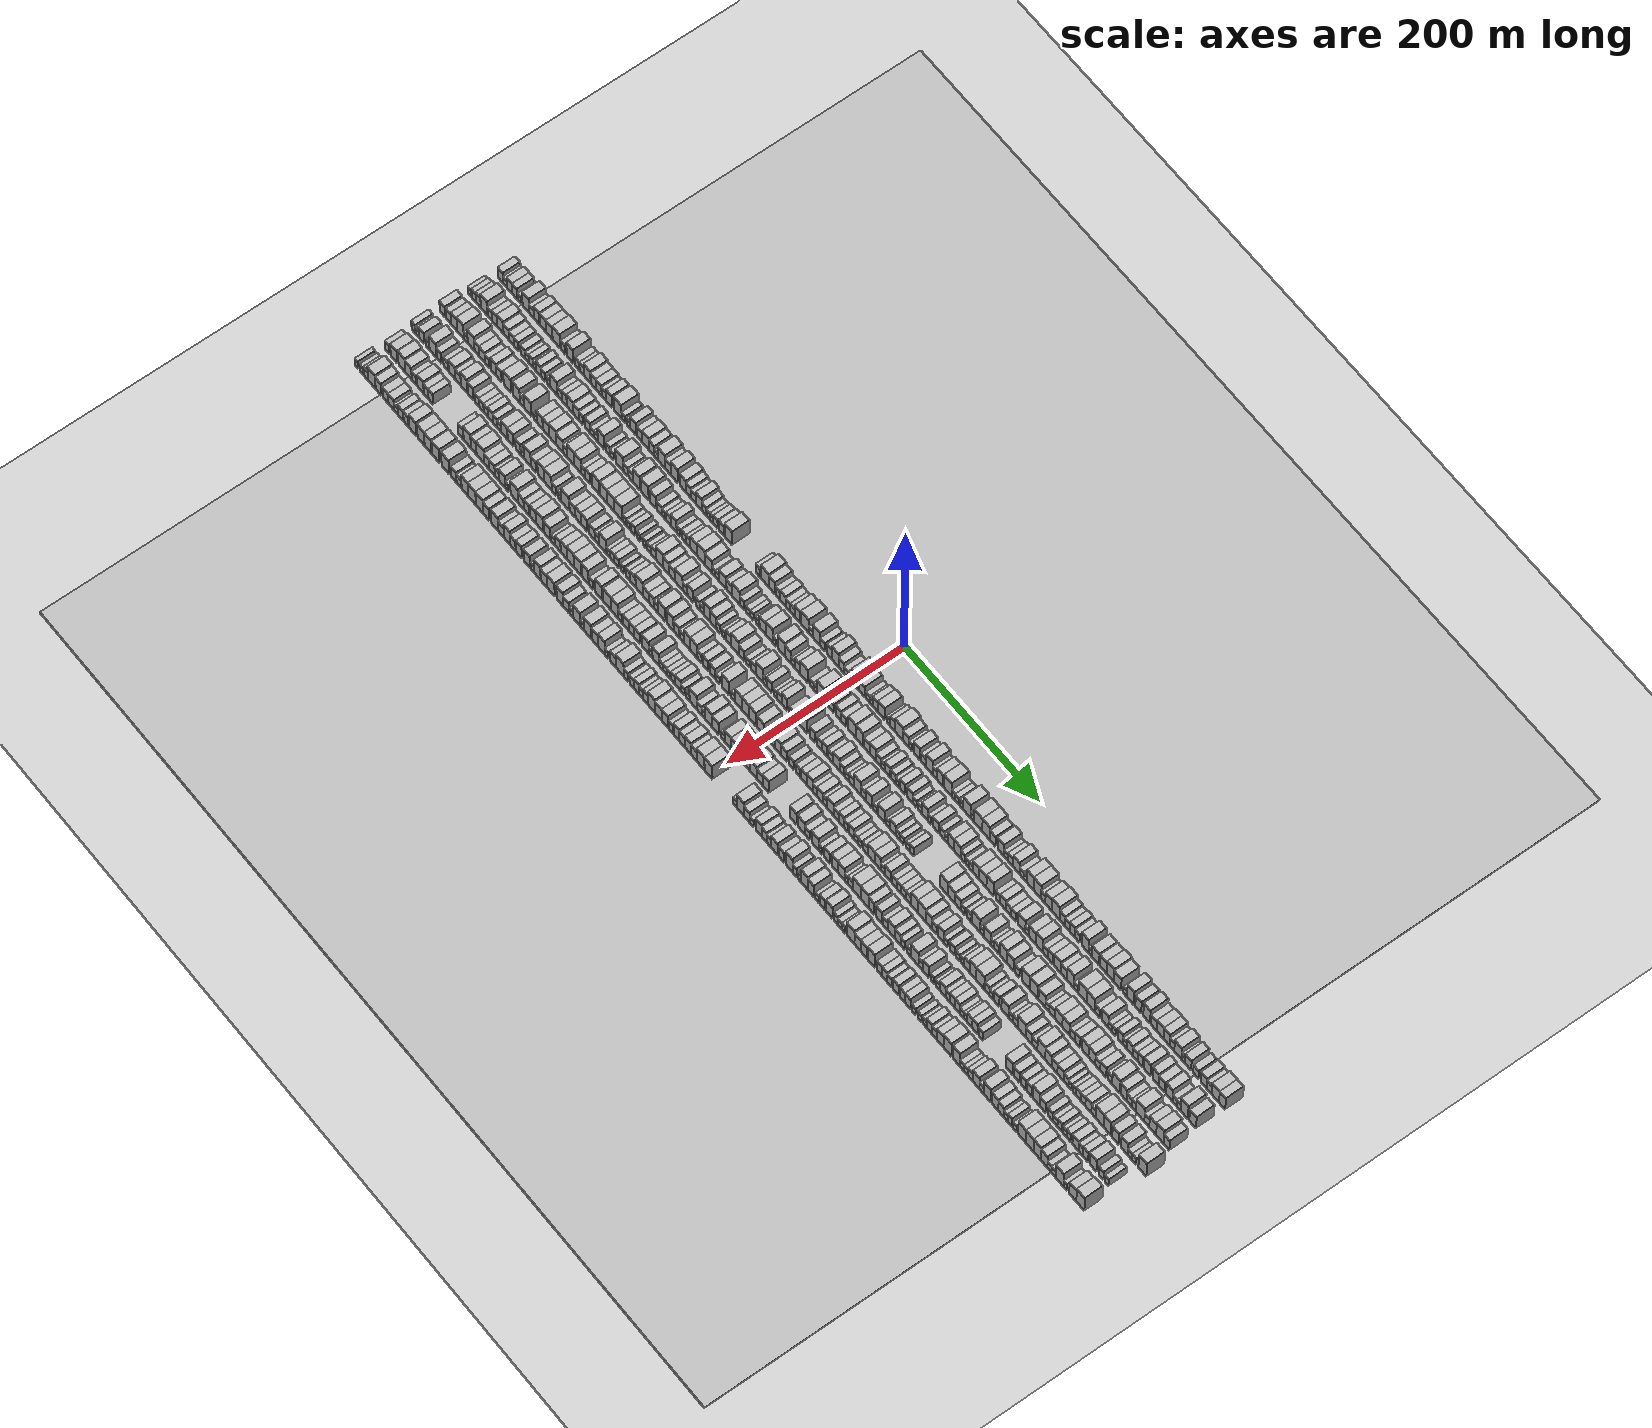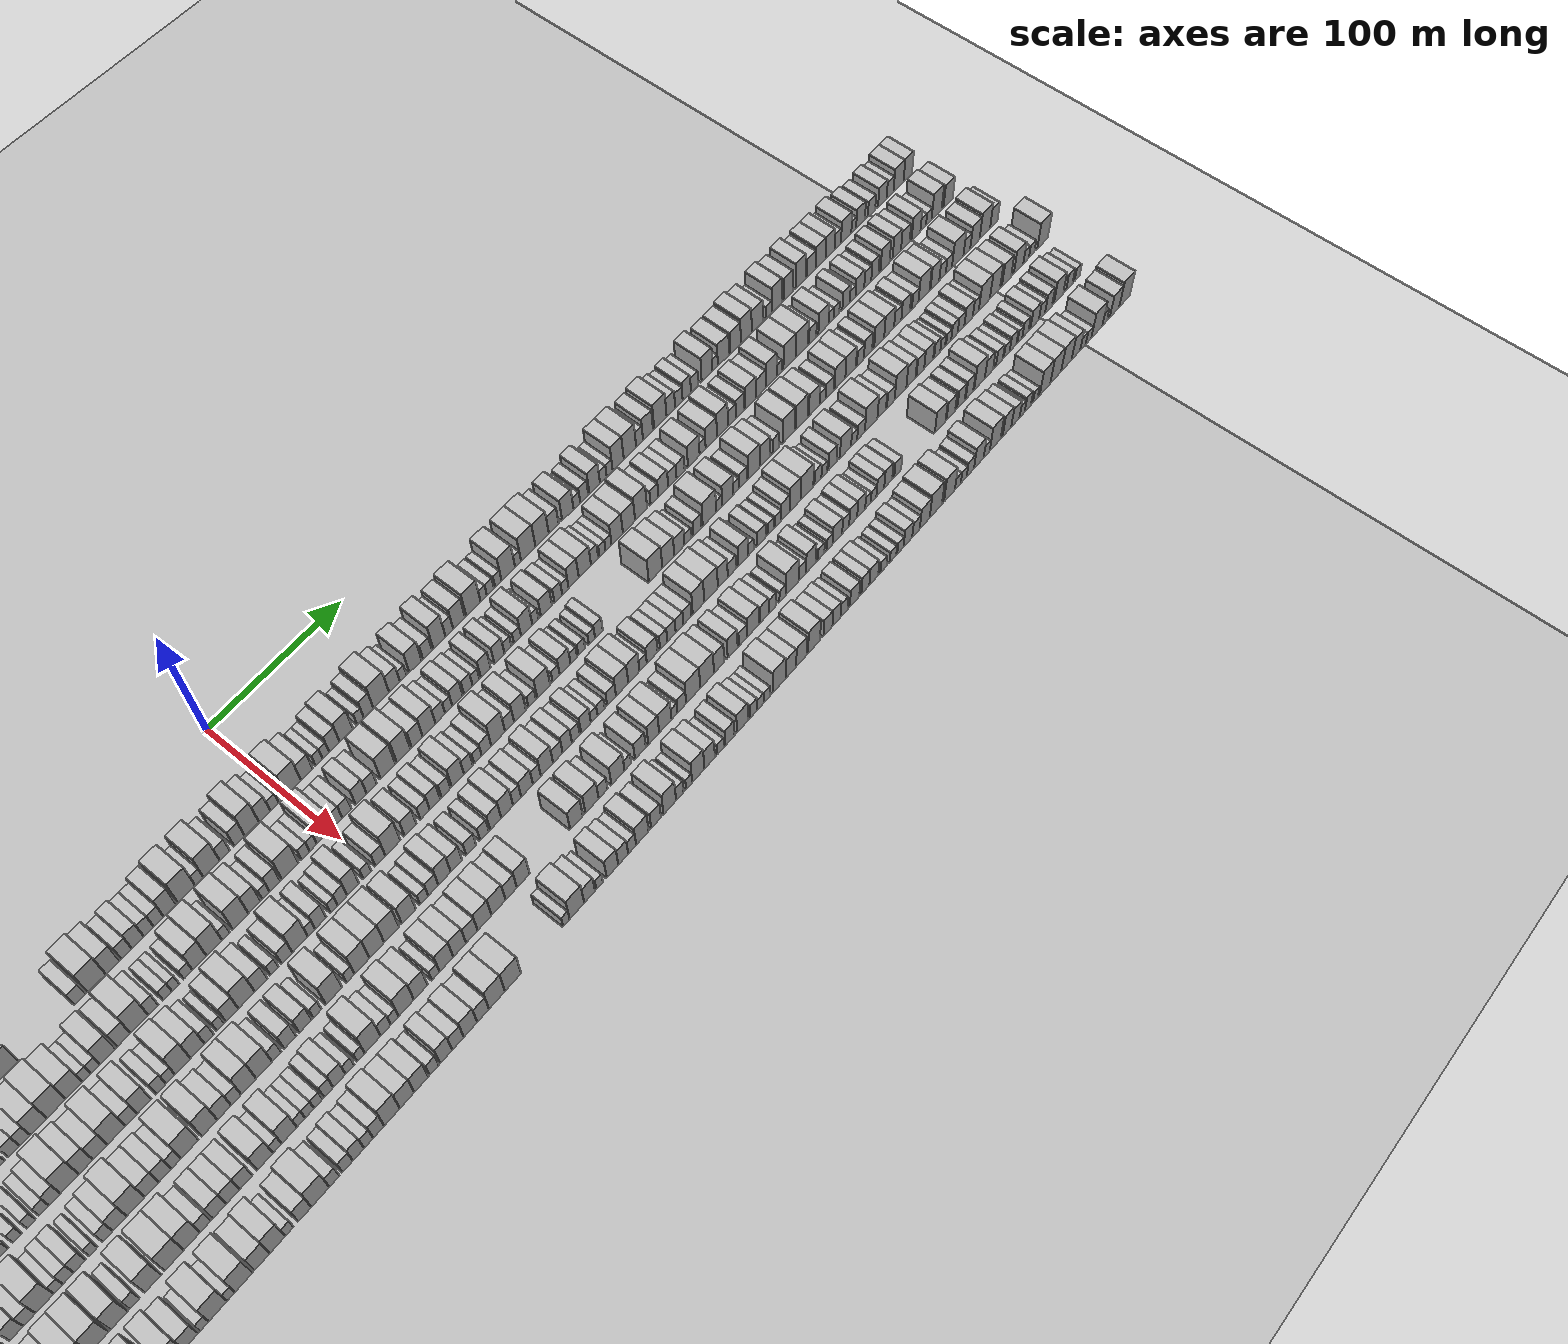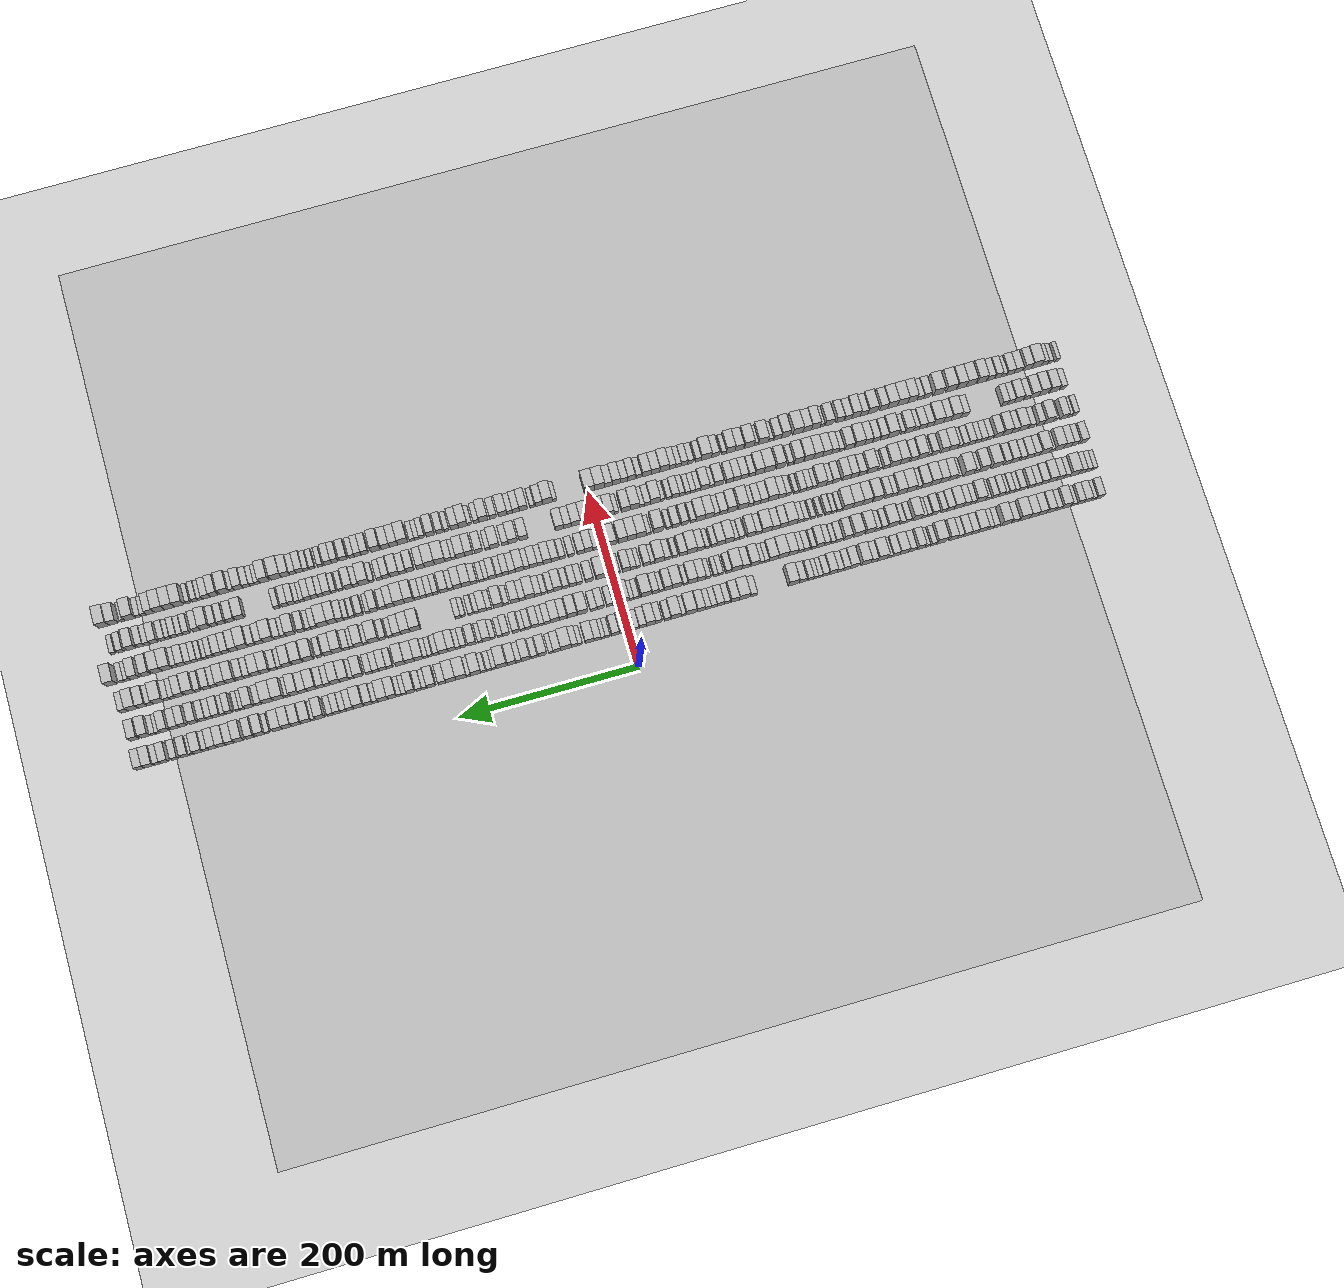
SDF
<?xml version="1.0" encoding="utf-8"?>

<sdf version="1.6">

   <world name="default">

      <gui fullscreen="0">

         <camera name="user_camera">

            <pose>-15 0 4.57585 0 0 0</pose>

            <view_controller>orbit</view_controller>

         </camera>

      </gui>

      <scene>

         <sky>

           <clouds>

             <speed>12</speed>

           </clouds>

         </sky>

         <ambient>0.4 0.4 0.4 1</ambient>

         <background>0.7 0.7 0.7 1</background>

         <shadows>1</shadows>

      </scene>

      <gravity>0 0 -9.8066</gravity>

      <magnetic_field>6e-06 2.3e-05 -4.2e-05</magnetic_field>

      <physics default="0" name="default_physics" type="ode">

         <ode>

            <solver>

               <type>quick</type>

               <iters>10</iters>

               <sor>1.0</sor>

               <use_dynamic_moi_rescaling>0</use_dynamic_moi_rescaling>

            </solver>

            <constraints>

               <cfm>0</cfm>

               <erp>0.2</erp>

               <contact_max_correcting_vel>100</contact_max_correcting_vel>

               <contact_surface_layer>0.001</contact_surface_layer>

            </constraints>

         </ode>

         <max_step_size>0.004</max_step_size>

         <real_time_factor>1</real_time_factor>

         <real_time_update_rate>250</real_time_update_rate>

      </physics>

      <light name="sun" type="directional">

         <cast_shadows>1</cast_shadows>

         <pose>0 0 10 0 0 0</pose>

         <diffuse>0.8 0.8 0.8 1</diffuse>

         <specular>0.2 0.2 0.2 1</specular>

         <attenuation>

            <range>1000</range>

            <constant>0.9</constant>

            <linear>0.01</linear>

            <quadratic>0.001</quadratic>

         </attenuation>

         <direction>-0.5 0.1 -0.9</direction>

      </light>

      <include>

         <name>ground_plane_1</name>

         <uri>model://HANNAS_ground_plane</uri>

         <pose>0 0 0  0 0 0</pose>

      </include>

      <include>

         <name>ground_plane_2</name>

         <uri>model://HANNAS_ground_plane</uri>

         <pose>100 0 0  0 0 0</pose>

      </include>

      <model name="building_1">

         <static>1</static>

         <pose frame="">50.0000 -533.0046 0 0.000000 0.000000 0.000000</pose>

         <link name="link">

            <pose frame="">0 0 9.00 0 0 0</pose>

            <collision name="collision">

               <geometry>

                  <box>

                     <size>20.0000 7.9907 18.0000</size>

                  </box>

               </geometry>

               <max_contacts>10</max_contacts>

               <surface>

                  <contact>

                     <ode/>

                  </contact>

                  <bounce/>

                  <friction>

                     <torsional>

                        <ode/>

                     </torsional>

                     <ode/>

                  </friction>

               </surface>

            </collision>

            <visual name="visual">

               <cast_shadows>0</cast_shadows>

               <geometry>

                  <box>

                     <size>20.0000 7.9907 18.0000</size>

                  </box>

               </geometry>

               <material>

                  <script>

                     <uri>model://HANNAS_wall/materials/scripts</uri>

                     <uri>model://HANNAS_wall/materials/textures</uri>

                     <name>vrc/HANNAS_wall</name>

                  </script>

               </material>

            </visual>

            <self_collide>0</self_collide>

            <enable_wind>0</enable_wind>

            <kinematic>0</kinematic>

         </link>

      </model>

      <model name="building_2">

         <static>1</static>

         <pose frame="">50.0000 -526.0997 0 0.000000 0.000000 0.000000</pose>

         <link name="link">

            <pose frame="">0 0 6.00 0 0 0</pose>

            <collision name="collision">

               <geometry>

                  <box>

                     <size>20.0000 5.8191 12.0000</size>

                  </box>

               </geometry>

               <max_contacts>10</max_contacts>

               <surface>

                  <contact>

                     <ode/>

                  </contact>

                  <bounce/>

                  <friction>

                     <torsional>

                        <ode/>

                     </torsional>

                     <ode/>

                  </friction>

               </surface>

            </collision>

            <visual name="visual">

               <cast_shadows>0</cast_shadows>

               <geometry>

                  <box>

                     <size>20.0000 5.8191 12.0000</size>

                  </box>

               </geometry>

               <material>

                  <script>

                     <uri>model://HANNAS_wall/materials/scripts</uri>

                     <uri>model://HANNAS_wall/materials/textures</uri>

                     <name>vrc/HANNAS_wall</name>

                  </script>

               </material>

            </visual>

            <self_collide>0</self_collide>

            <enable_wind>0</enable_wind>

            <kinematic>0</kinematic>

         </link>

      </model>

      <model name="building_3">

         <static>1</static>

         <pose frame="">50.0000 -518.9652 0 0.000000 0.000000 0.000000</pose>

         <link name="link">

            <pose frame="">0 0 9.00 0 0 0</pose>

            <collision name="collision">

               <geometry>

                  <box>

                     <size>20.0000 8.4499 18.0000</size>

                  </box>

               </geometry>

               <max_contacts>10</max_contacts>

               <surface>

                  <contact>

                     <ode/>

                  </contact>

                  <bounce/>

                  <friction>

                     <torsional>

                        <ode/>

                     </torsional>

                     <ode/>

                  </friction>

               </surface>

            </collision>

            <visual name="visual">

               <cast_shadows>0</cast_shadows>

               <geometry>

                  <box>

                     <size>20.0000 8.4499 18.0000</size>

                  </box>

               </geometry>

               <material>

                  <script>

                     <uri>model://HANNAS_wall/materials/scripts</uri>

                     <uri>model://HANNAS_wall/materials/textures</uri>

                     <name>vrc/HANNAS_wall</name>

                  </script>

               </material>

            </visual>

            <self_collide>0</self_collide>

            <enable_wind>0</enable_wind>

            <kinematic>0</kinematic>

         </link>

      </model>

      <model name="building_4">

         <static>1</static>

         <pose frame="">50.0000 -511.0897 0 0.000000 0.000000 0.000000</pose>

         <link name="link">

            <pose frame="">0 0 9.00 0 0 0</pose>

            <collision name="collision">

               <geometry>

                  <box>

                     <size>20.0000 7.3011 18.0000</size>

                  </box>

               </geometry>

               <max_contacts>10</max_contacts>

               <surface>

                  <contact>

                     <ode/>

                  </contact>

                  <bounce/>

                  <friction>

                     <torsional>

                        <ode/>

                     </torsional>

                     <ode/>

                  </friction>

               </surface>

            </collision>

            <visual name="visual">

               <cast_shadows>0</cast_shadows>

               <geometry>

                  <box>

                     <size>20.0000 7.3011 18.0000</size>

                  </box>

               </geometry>

               <material>

                  <script>

                     <uri>model://HANNAS_wall/materials/scripts</uri>

                     <uri>model://HANNAS_wall/materials/textures</uri>

                     <name>vrc/HANNAS_wall</name>

                  </script>

               </material>

            </visual>

            <self_collide>0</self_collide>

            <enable_wind>0</enable_wind>

            <kinematic>0</kinematic>

         </link>

      </model>

      <model name="building_5">

         <static>1</static>

         <pose frame="">50.0000 -503.7773 0 0.000000 0.000000 0.000000</pose>

         <link name="link">

            <pose frame="">0 0 6.00 0 0 0</pose>

            <collision name="collision">

               <geometry>

                  <box>

                     <size>20.0000 5.3236 12.0000</size>

                  </box>

               </geometry>

               <max_contacts>10</max_contacts>

               <surface>

                  <contact>

                     <ode/>

                  </contact>

                  <bounce/>

                  <friction>

                     <torsional>

                        <ode/>

                     </torsional>

                     <ode/>

                  </friction>

               </surface>

            </collision>

            <visual name="visual">

               <cast_shadows>0</cast_shadows>

               <geometry>

                  <box>

                     <size>20.0000 5.3236 12.0000</size>

                  </box>

               </geometry>

               <material>

                  <script>

                     <uri>model://HANNAS_wall/materials/scripts</uri>

                     <uri>model://HANNAS_wall/materials/textures</uri>

                     <name>vrc/HANNAS_wall</name>

                  </script>

               </material>

            </visual>

            <self_collide>0</self_collide>

            <enable_wind>0</enable_wind>

            <kinematic>0</kinematic>

         </link>

      </model>

      <model name="building_6">

         <static>1</static>

         <pose frame="">50.0000 -494.1183 0 0.000000 0.000000 0.000000</pose>

         <link name="link">

            <pose frame="">0 0 12.00 0 0 0</pose>

            <collision name="collision">

               <geometry>

                  <box>

                     <size>20.0000 9.9944 24.0000</size>

                  </box>

               </geometry>

               <max_contacts>10</max_contacts>

               <surface>

                  <contact>

                     <ode/>

                  </contact>

                  <bounce/>

                  <friction>

                     <torsional>

                        <ode/>

                     </torsional>

                     <ode/>

                  </friction>

               </surface>

            </collision>

            <visual name="visual">

               <cast_shadows>0</cast_shadows>

               <geometry>

                  <box>

                     <size>20.0000 9.9944 24.0000</size>

                  </box>

               </geometry>

               <material>

                  <script>

                     <uri>model://HANNAS_wall/materials/scripts</uri>

                     <uri>model://HANNAS_wall/materials/textures</uri>

                     <name>vrc/HANNAS_wall</name>

                  </script>

               </material>

            </visual>

            <self_collide>0</self_collide>

            <enable_wind>0</enable_wind>

            <kinematic>0</kinematic>

         </link>

      </model>

      <model name="building_7">

         <static>1</static>

         <pose frame="">50.0000 -485.4049 0 0.000000 0.000000 0.000000</pose>

         <link name="link">

            <pose frame="">0 0 7.50 0 0 0</pose>

            <collision name="collision">

               <geometry>

                  <box>

                     <size>20.0000 7.4322 15.0000</size>

                  </box>

               </geometry>

               <max_contacts>10</max_contacts>

               <surface>

                  <contact>

                     <ode/>

                  </contact>

                  <bounce/>

                  <friction>

                     <torsional>

                        <ode/>

                     </torsional>

                     <ode/>

                  </friction>

               </surface>

            </collision>

            <visual name="visual">

               <cast_shadows>0</cast_shadows>

               <geometry>

                  <box>

                     <size>20.0000 7.4322 15.0000</size>

                  </box>

               </geometry>

               <material>

                  <script>

                     <uri>model://HANNAS_wall/materials/scripts</uri>

                     <uri>model://HANNAS_wall/materials/textures</uri>

                     <name>vrc/HANNAS_wall</name>

                  </script>

               </material>

            </visual>

            <self_collide>0</self_collide>

            <enable_wind>0</enable_wind>

            <kinematic>0</kinematic>

         </link>

      </model>

      <model name="building_8">

         <static>1</static>

         <pose frame="">50.0000 -477.3388 0 0.000000 0.000000 0.000000</pose>

         <link name="link">

            <pose frame="">0 0 10.50 0 0 0</pose>

            <collision name="collision">

               <geometry>

                  <box>

                     <size>20.0000 8.7000 21.0000</size>

                  </box>

               </geometry>

               <max_contacts>10</max_contacts>

               <surface>

                  <contact>

                     <ode/>

                  </contact>

                  <bounce/>

                  <friction>

                     <torsional>

                        <ode/>

                     </torsional>

                     <ode/>

                  </friction>

               </surface>

            </collision>

            <visual name="visual">

               <cast_shadows>0</cast_shadows>

               <geometry>

                  <box>

                     <size>20.0000 8.7000 21.0000</size>

                  </box>

               </geometry>

               <material>

                  <script>

                     <uri>model://HANNAS_wall/materials/scripts</uri>

                     <uri>model://HANNAS_wall/materials/textures</uri>

                     <name>vrc/HANNAS_wall</name>

                  </script>

               </material>

            </visual>

            <self_collide>0</self_collide>

            <enable_wind>0</enable_wind>

            <kinematic>0</kinematic>

         </link>

      </model>

      <model name="building_9">

         <static>1</static>

         <pose frame="">50.0000 -467.4540 0 0.000000 0.000000 0.000000</pose>

         <link name="link">

            <pose frame="">0 0 10.50 0 0 0</pose>

            <collision name="collision">

               <geometry>

                  <box>

                     <size>20.0000 9.0695 21.0000</size>

                  </box>

               </geometry>

               <max_contacts>10</max_contacts>

               <surface>

                  <contact>

                     <ode/>

                  </contact>

                  <bounce/>

                  <friction>

                     <torsional>

                        <ode/>

                     </torsional>

                     <ode/>

                  </friction>

               </surface>

            </collision>

            <visual name="visual">

               <cast_shadows>0</cast_shadows>

               <geometry>

                  <box>

                     <size>20.0000 9.0695 21.0000</size>

                  </box>

               </geometry>

               <material>

                  <script>

                     <uri>model://HANNAS_wall/materials/scripts</uri>

                     <uri>model://HANNAS_wall/materials/textures</uri>

                     <name>vrc/HANNAS_wall</name>

                  </script>

               </material>

            </visual>

            <self_collide>0</self_collide>

            <enable_wind>0</enable_wind>

            <kinematic>0</kinematic>

         </link>

      </model>

      <model name="building_10">

         <static>1</static>

         <pose frame="">50.0000 -457.8971 0 0.000000 0.000000 0.000000</pose>

         <link name="link">

            <pose frame="">0 0 10.50 0 0 0</pose>

            <collision name="collision">

               <geometry>

                  <box>

                     <size>20.0000 10.0442 21.0000</size>

                  </box>

               </geometry>

               <max_contacts>10</max_contacts>

               <surface>

                  <contact>

                     <ode/>

                  </contact>

                  <bounce/>

                  <friction>

                     <torsional>

                        <ode/>

                     </torsional>

                     <ode/>

                  </friction>

               </surface>

            </collision>

            <visual name="visual">

               <cast_shadows>0</cast_shadows>

               <geometry>

                  <box>

                     <size>20.0000 10.0442 21.0000</size>

                  </box>

               </geometry>

               <material>

                  <script>

                     <uri>model://HANNAS_wall/materials/scripts</uri>

                     <uri>model://HANNAS_wall/materials/textures</uri>

                     <name>vrc/HANNAS_wall</name>

                  </script>

               </material>

            </visual>

            <self_collide>0</self_collide>

            <enable_wind>0</enable_wind>

            <kinematic>0</kinematic>

         </link>

      </model>

      <model name="building_11">

         <static>1</static>

         <pose frame="">50.0000 -447.1592 0 0.000000 0.000000 0.000000</pose>

         <link name="link">

            <pose frame="">0 0 12.00 0 0 0</pose>

            <collision name="collision">

               <geometry>

                  <box>

                     <size>20.0000 11.4316 24.0000</size>

                  </box>

               </geometry>

               <max_contacts>10</max_contacts>

               <surface>

                  <contact>

                     <ode/>

                  </contact>

                  <bounce/>

                  <friction>

                     <torsional>

                        <ode/>

                     </torsional>

                     <ode/>

                  </friction>

               </surface>

            </collision>

            <visual name="visual">

               <cast_shadows>0</cast_shadows>

               <geometry>

                  <box>

                     <size>20.0000 11.4316 24.0000</size>

                  </box>

               </geometry>

               <material>

                  <script>

                     <uri>model://HANNAS_wall/materials/scripts</uri>

                     <uri>model://HANNAS_wall/materials/textures</uri>

                     <name>vrc/HANNAS_wall</name>

                  </script>

               </material>

            </visual>

            <self_collide>0</self_collide>

            <enable_wind>0</enable_wind>

            <kinematic>0</kinematic>

         </link>

      </model>

      <model name="building_12">

         <static>1</static>

         <pose frame="">50.0000 -436.7620 0 0.000000 0.000000 0.000000</pose>

         <link name="link">

            <pose frame="">0 0 7.50 0 0 0</pose>

            <collision name="collision">

               <geometry>

                  <box>

                     <size>20.0000 7.3629 15.0000</size>

                  </box>

               </geometry>

               <max_contacts>10</max_contacts>

               <surface>

                  <contact>

                     <ode/>

                  </contact>

                  <bounce/>

                  <friction>

                     <torsional>

                        <ode/>

                     </torsional>

                     <ode/>

                  </friction>

               </surface>

            </collision>

            <visual name="visual">

               <cast_shadows>0</cast_shadows>

               <geometry>

                  <box>

                     <size>20.0000 7.3629 15.0000</size>

                  </box>

               </geometry>

               <material>

                  <script>

                     <uri>model://HANNAS_wall/materials/scripts</uri>

                     <uri>model://HANNAS_wall/materials/textures</uri>

                     <name>vrc/HANNAS_wall</name>

                  </script>

               </material>

            </visual>

            <self_collide>0</self_collide>

            <enable_wind>0</enable_wind>

            <kinematic>0</kinematic>

         </link>

      </model>

      <model name="building_13">

         <static>1</static>

         <pose frame="">50.0000 -425.9364 0 0.000000 0.000000 0.000000</pose>

         <link name="link">

            <pose frame="">0 0 12.00 0 0 0</pose>

            <collision name="collision">

               <geometry>

                  <box>

                     <size>20.0000 10.2883 24.0000</size>

                  </box>

               </geometry>

               <max_contacts>10</max_contacts>

               <surface>

                  <contact>

                     <ode/>

                  </contact>

                  <bounce/>

                  <friction>

                     <torsional>

                        <ode/>

                     </torsional>

                     <ode/>

                  </friction>

               </surface>

            </collision>

            <visual name="visual">

               <cast_shadows>0</cast_shadows>

               <geometry>

                  <box>

                     <size>20.0000 10.2883 24.0000</size>

                  </box>

               </geometry>

               <material>

                  <script>

                     <uri>model://HANNAS_wall/materials/scripts</uri>

                     <uri>model://HANNAS_wall/materials/textures</uri>

                     <name>vrc/HANNAS_wall</name>

                  </script>

               </material>

            </visual>

            <self_collide>0</self_collide>

            <enable_wind>0</enable_wind>

            <kinematic>0</kinematic>

         </link>

      </model>

      <model name="building_14">

         <static>1</static>

         <pose frame="">50.0000 -414.5878 0 0.000000 0.000000 0.000000</pose>

         <link name="link">

            <pose frame="">0 0 7.50 0 0 0</pose>

            <collision name="collision">

               <geometry>

                  <box>

                     <size>20.0000 6.4089 15.0000</size>

                  </box>

               </geometry>

               <max_contacts>10</max_contacts>

               <surface>

                  <contact>

                     <ode/>

                  </contact>

                  <bounce/>

                  <friction>

                     <torsional>

                        <ode/>

                     </torsional>

                     <ode/>

                  </friction>

               </surface>

            </collision>

            <visual name="visual">

               <cast_shadows>0</cast_shadows>

               <geometry>

                  <box>

                     <size>20.0000 6.4089 15.0000</size>

                  </box>

               </geometry>

               <material>

                  <script>

                     <uri>model://HANNAS_wall/materials/scripts</uri>

                     <uri>model://HANNAS_wall/materials/textures</uri>

                     <name>vrc/HANNAS_wall</name>

                  </script>

               </material>

            </visual>

            <self_collide>0</self_collide>

            <enable_wind>0</enable_wind>

            <kinematic>0</kinematic>

         </link>

      </model>

      <model name="building_15">

         <static>1</static>

         <pose frame="">50.0000 -408.0632 0 0.000000 0.000000 0.000000</pose>

         <link name="link">

            <pose frame="">0 0 7.50 0 0 0</pose>

            <collision name="collision">

               <geometry>

                  <box>

                     <size>20.0000 6.6403 15.0000</size>

                  </box>

               </geometry>

               <max_contacts>10</max_contacts>

               <surface>

                  <contact>

                     <ode/>

                  </contact>

                  <bounce/>

                  <friction>

                     <torsional>

                        <ode/>

                     </torsional>

                     <ode/>

                  </friction>

               </surface>

            </collision>

            <visual name="visual">

               <cast_shadows>0</cast_shadows>

               <geometry>

                  <box>

                     <size>20.0000 6.6403 15.0000</size>

                  </box>

               </geometry>

               <material>

                  <script>

                     <uri>model://HANNAS_wall/materials/scripts</uri>

                     <uri>model://HANNAS_wall/materials/textures</uri>

                     <name>vrc/HANNAS_wall</name>

                  </script>

               </material>

            </visual>

            <self_collide>0</self_collide>

            <enable_wind>0</enable_wind>

            <kinematic>0</kinematic>

         </link>

      </model>

      <model name="building_16">

         <static>1</static>

         <pose frame="">50.0000 -399.5464 0 0.000000 0.000000 0.000000</pose>

         <link name="link">

            <pose frame="">0 0 10.50 0 0 0</pose>

            <collision name="collision">

               <geometry>

                  <box>

                     <size>20.0000 10.3932 21.0000</size>

                  </box>

               </geometry>

               <max_contacts>10</max_contacts>

               <surface>

                  <contact>

                     <ode/>

                  </contact>

                  <bounce/>

                  <friction>

                     <torsional>

                        <ode/>

                     </torsional>

                     <ode/>

                  </friction>

               </surface>

            </collision>

            <visual name="visual">

               <cast_shadows>0</cast_shadows>

               <geometry>

                  <box>

                     <size>20.0000 10.3932 21.0000</size>

                  </box>

               </geometry>

               <material>

                  <script>

                     <uri>model://HANNAS_wall/materials/scripts</uri>

                     <uri>model://HANNAS_wall/materials/textures</uri>

                     <name>vrc/HANNAS_wall</name>

                  </script>

               </material>

            </visual>

            <self_collide>0</self_collide>

            <enable_wind>0</enable_wind>

            <kinematic>0</kinematic>

         </link>

      </model>

      <model name="building_17">

         <static>1</static>

         <pose frame="">50.0000 -390.3676 0 0.000000 0.000000 0.000000</pose>

         <link name="link">

            <pose frame="">0 0 9.00 0 0 0</pose>

            <collision name="collision">

               <geometry>

                  <box>

                     <size>20.0000 7.9644 18.0000</size>

                  </box>

               </geometry>

               <max_contacts>10</max_contacts>

               <surface>

                  <contact>

                     <ode/>

                  </contact>

                  <bounce/>

                  <friction>

                     <torsional>

                        <ode/>

                     </torsional>

                     <ode/>

                  </friction>

               </surface>

            </collision>

            <visual name="visual">

               <cast_shadows>0</cast_shadows>

               <geometry>

                  <box>

                     <size>20.0000 7.9644 18.0000</size>

                  </box>

               </geometry>

               <material>

                  <script>

                     <uri>model://HANNAS_wall/materials/scripts</uri>

                     <uri>model://HANNAS_wall/materials/textures</uri>

                     <name>vrc/HANNAS_wall</name>

                  </script>

               </material>

            </visual>

            <self_collide>0</self_collide>

            <enable_wind>0</enable_wind>

            <kinematic>0</kinematic>

         </link>

      </model>

      <model name="building_18">

         <static>1</static>

         <pose frame="">50.0000 -381.9726 0 0.000000 0.000000 0.000000</pose>

         <link name="link">

            <pose frame="">0 0 9.00 0 0 0</pose>

            <collision name="collision">

               <geometry>

                  <box>

                     <size>20.0000 8.8255 18.0000</size>

                  </box>

               </geometry>

               <max_contacts>10</max_contacts>

               <surface>

                  <contact>

                     <ode/>

                  </contact>

                  <bounce/>

                  <friction>

                     <torsional>

                        <ode/>

                     </torsional>

                     <ode/>

                  </friction>

               </surface>

            </collision>

            <visual name="visual">

               <cast_shadows>0</cast_shadows>

               <geometry>

                  <box>

                     <size>20.0000 8.8255 18.0000</size>

                  </box>

               </geometry>

               <material>

                  <script>

                     <uri>model://HANNAS_wall/materials/scripts</uri>

                     <uri>model://HANNAS_wall/materials/textures</uri>

                     <name>vrc/HANNAS_wall</name>

                  </script>

               </material>

            </visual>

            <self_collide>0</self_collide>

            <enable_wind>0</enable_wind>

            <kinematic>0</kinematic>

         </link>

      </model>

      <model name="building_19">

         <static>1</static>

         <pose frame="">50.0000 -373.9449 0 0.000000 0.000000 0.000000</pose>

         <link name="link">

            <pose frame="">0 0 7.50 0 0 0</pose>

            <collision name="collision">

               <geometry>

                  <box>

                     <size>20.0000 7.2300 15.0000</size>

                  </box>

               </geometry>

               <max_contacts>10</max_contacts>

               <surface>

                  <contact>

                     <ode/>

                  </contact>

                  <bounce/>

                  <friction>

                     <torsional>

                        <ode/>

                     </torsional>

                     <ode/>

                  </friction>

               </surface>

            </collision>

            <visual name="visual">

               <cast_shadows>0</cast_shadows>

               <geometry>

                  <box>

                     <size>20.0000 7.2300 15.0000</size>

                  </box>

               </geometry>

               <material>

                  <script>

                     <uri>model://HANNAS_wall/materials/scripts</uri>

                     <uri>model://HANNAS_wall/materials/textures</uri>

                     <name>vrc/HANNAS_wall</name>

                  </script>

               </material>

            </visual>

            <self_collide>0</self_collide>

            <enable_wind>0</enable_wind>

            <kinematic>0</kinematic>

         </link>

      </model>

      <model name="building_20">

         <static>1</static>

         <pose frame="">50.0000 -366.0070 0 0.000000 0.000000 0.000000</pose>

         <link name="link">

            <pose frame="">0 0 10.50 0 0 0</pose>

            <collision name="collision">

               <geometry>

                  <box>

                     <size>20.0000 8.6458 21.0000</size>

                  </box>

               </geometry>

               <max_contacts>10</max_contacts>

               <surface>

                  <contact>

                     <ode/>

                  </contact>

                  <bounce/>

                  <friction>

                     <torsional>

                        <ode/>

                     </torsional>

                     <ode/>

                  </friction>

               </surface>

            </collision>

            <visual name="visual">

               <cast_shadows>0</cast_shadows>

               <geometry>

                  <box>

                     <size>20.0000 8.6458 21.0000</size>

                  </box>

               </geometry>

               <material>

                  <script>

                     <uri>model://HANNAS_wall/materials/scripts</uri>

                     <uri>model://HANNAS_wall/materials/textures</uri>

                     <name>vrc/HANNAS_wall</name>

                  </script>

               </material>

            </visual>

            <self_collide>0</self_collide>

            <enable_wind>0</enable_wind>

            <kinematic>0</kinematic>

         </link>

      </model>

      <model name="building_21">

         <static>1</static>

         <pose frame="">50.0000 -352.7815 0 0.000000 0.000000 0.000000</pose>

         <link name="link">

            <pose frame="">0 0 12.00 0 0 0</pose>

            <collision name="collision">

               <geometry>

                  <box>

                     <size>20.0000 11.8053 24.0000</size>

                  </box>

               </geometry>

               <max_contacts>10</max_contacts>

               <surface>

                  <contact>

                     <ode/>

                  </contact>

                  <bounce/>

                  <friction>

                     <torsional>

                        <ode/>

                     </torsional>

                     <ode/>

                  </friction>

               </surface>

            </collision>

            <visual name="visual">

               <cast_shadows>0</cast_shadows>

               <geometry>

                  <box>

                     <size>20.0000 11.8053 24.0000</size>

                  </box>

               </geometry>

               <material>

                  <script>

                     <uri>model://HANNAS_wall/materials/scripts</uri>

                     <uri>model://HANNAS_wall/materials/textures</uri>

                     <name>vrc/HANNAS_wall</name>

                  </script>

               </material>

            </visual>

            <self_collide>0</self_collide>

            <enable_wind>0</enable_wind>

            <kinematic>0</kinematic>

         </link>

      </model>

      <model name="building_22">

         <static>1</static>

         <pose frame="">50.0000 -343.9652 0 0.000000 0.000000 0.000000</pose>

         <link name="link">

            <pose frame="">0 0 6.00 0 0 0</pose>

            <collision name="collision">

               <geometry>

                  <box>

                     <size>20.0000 5.8273 12.0000</size>

                  </box>

               </geometry>

               <max_contacts>10</max_contacts>

               <surface>

                  <contact>

                     <ode/>

                  </contact>

                  <bounce/>

                  <friction>

                     <torsional>

                        <ode/>

                     </torsional>

                     <ode/>

                  </friction>

               </surface>

            </collision>

            <visual name="visual">

               <cast_shadows>0</cast_shadows>

               <geometry>

                  <box>

                     <size>20.0000 5.8273 12.0000</size>

                  </box>

               </geometry>

               <material>

                  <script>

                     <uri>model://HANNAS_wall/materials/scripts</uri>

                     <uri>model://HANNAS_wall/materials/textures</uri>

                     <name>vrc/HANNAS_wall</name>

                  </script>

               </material>

            </visual>

            <self_collide>0</self_collide>

            <enable_wind>0</enable_wind>

            <kinematic>0</kinematic>

         </link>

      </model>

      <model name="building_23">

         <static>1</static>

         <pose frame="">50.0000 -336.2868 0 0.000000 0.000000 0.000000</pose>

         <link name="link">

            <pose frame="">0 0 6.00 0 0 0</pose>

            <collision name="collision">

               <geometry>

                  <box>

                     <size>20.0000 5.5294 12.0000</size>

                  </box>

               </geometry>

               <max_contacts>10</max_contacts>

               <surface>

                  <contact>

                     <ode/>

                  </contact>

                  <bounce/>

                  <friction>

                     <torsional>

                        <ode/>

                     </torsional>

                     <ode/>

                  </friction>

               </surface>

            </collision>

            <visual name="visual">

               <cast_shadows>0</cast_shadows>

               <geometry>

                  <box>

                     <size>20.0000 5.5294 12.0000</size>

                  </box>

               </geometry>

               <material>

                  <script>

                     <uri>model://HANNAS_wall/materials/scripts</uri>

                     <uri>model://HANNAS_wall/materials/textures</uri>

                     <name>vrc/HANNAS_wall</name>

                  </script>

               </material>

            </visual>

            <self_collide>0</self_collide>

            <enable_wind>0</enable_wind>

            <kinematic>0</kinematic>

         </link>

      </model>

      <model name="building_24">

         <static>1</static>

         <pose frame="">50.0000 -329.2982 0 0.000000 0.000000 0.000000</pose>

         <link name="link">

            <pose frame="">0 0 10.50 0 0 0</pose>

            <collision name="collision">

               <geometry>

                  <box>

                     <size>20.0000 8.4478 21.0000</size>

                  </box>

               </geometry>

               <max_contacts>10</max_contacts>

               <surface>

                  <contact>

                     <ode/>

                  </contact>

                  <bounce/>

                  <friction>

                     <torsional>

                        <ode/>

                     </torsional>

                     <ode/>

                  </friction>

               </surface>

            </collision>

            <visual name="visual">

               <cast_shadows>0</cast_shadows>

               <geometry>

                  <box>

                     <size>20.0000 8.4478 21.0000</size>

                  </box>

               </geometry>

               <material>

                  <script>

                     <uri>model://HANNAS_wall/materials/scripts</uri>

                     <uri>model://HANNAS_wall/materials/textures</uri>

                     <name>vrc/HANNAS_wall</name>

                  </script>

               </material>

            </visual>

            <self_collide>0</self_collide>

            <enable_wind>0</enable_wind>

            <kinematic>0</kinematic>

         </link>

      </model>

      <model name="building_25">

         <static>1</static>

         <pose frame="">50.0000 -319.2484 0 0.000000 0.000000 0.000000</pose>

         <link name="link">

            <pose frame="">0 0 9.00 0 0 0</pose>

            <collision name="collision">

               <geometry>

                  <box>

                     <size>20.0000 7.6517 18.0000</size>

                  </box>

               </geometry>

               <max_contacts>10</max_contacts>

               <surface>

                  <contact>

                     <ode/>

                  </contact>

                  <bounce/>

                  <friction>

                     <torsional>

                        <ode/>

                     </torsional>

                     <ode/>

                  </friction>

               </surface>

            </collision>

            <visual name="visual">

               <cast_shadows>0</cast_shadows>

               <geometry>

                  <box>

                     <size>20.0000 7.6517 18.0000</size>

                  </box>

               </geometry>

               <material>

                  <script>

                     <uri>model://HANNAS_wall/materials/scripts</uri>

                     <uri>model://HANNAS_wall/materials/textures</uri>

                     <name>vrc/HANNAS_wall</name>

                  </script>

               </material>

            </visual>

            <self_collide>0</self_collide>

            <enable_wind>0</enable_wind>

            <kinematic>0</kinematic>

         </link>

      </model>

      <model name="building_26">

         <static>1</static>

         <pose frame="">50.0000 -310.2502 0 0.000000 0.000000 0.000000</pose>

         <link name="link">

            <pose frame="">0 0 10.50 0 0 0</pose>

            <collision name="collision">

               <geometry>

                  <box>

                     <size>20.0000 10.3448 21.0000</size>

                  </box>

               </geometry>

               <max_contacts>10</max_contacts>

               <surface>

                  <contact>

                     <ode/>

                  </contact>

                  <bounce/>

                  <friction>

                     <torsional>

                        <ode/>

                     </torsional>

                     <ode/>

                  </friction>

               </surface>

            </collision>

            <visual name="visual">

               <cast_shadows>0</cast_shadows>

               <geometry>

                  <box>

                     <size>20.0000 10.3448 21.0000</size>

                  </box>

               </geometry>

               <material>

                  <script>

                     <uri>model://HANNAS_wall/materials/scripts</uri>

                     <uri>model://HANNAS_wall/materials/textures</uri>

                     <name>vrc/HANNAS_wall</name>

                  </script>

               </material>

            </visual>

            <self_collide>0</self_collide>

            <enable_wind>0</enable_wind>

            <kinematic>0</kinematic>

         </link>

      </model>

      <model name="building_27">

         <static>1</static>

         <pose frame="">50.0000 -300.9829 0 0.000000 0.000000 0.000000</pose>

         <link name="link">

            <pose frame="">0 0 9.00 0 0 0</pose>

            <collision name="collision">

               <geometry>

                  <box>

                     <size>20.0000 8.1897 18.0000</size>

                  </box>

               </geometry>

               <max_contacts>10</max_contacts>

               <surface>

                  <contact>

                     <ode/>

                  </contact>

                  <bounce/>

                  <friction>

                     <torsional>

                        <ode/>

                     </torsional>

                     <ode/>

                  </friction>

               </surface>

            </collision>

            <visual name="visual">

               <cast_shadows>0</cast_shadows>

               <geometry>

                  <box>

                     <size>20.0000 8.1897 18.0000</size>

                  </box>

               </geometry>

               <material>

                  <script>

                     <uri>model://HANNAS_wall/materials/scripts</uri>

                     <uri>model://HANNAS_wall/materials/textures</uri>

                     <name>vrc/HANNAS_wall</name>

                  </script>

               </material>

            </visual>

            <self_collide>0</self_collide>

            <enable_wind>0</enable_wind>

            <kinematic>0</kinematic>

         </link>

      </model>

      <model name="building_28">

         <static>1</static>

         <pose frame="">50.0000 -294.3668 0 0.000000 0.000000 0.000000</pose>

         <link name="link">

            <pose frame="">0 0 6.00 0 0 0</pose>

            <collision name="collision">

               <geometry>

                  <box>

                     <size>20.0000 5.0425 12.0000</size>

                  </box>

               </geometry>

               <max_contacts>10</max_contacts>

               <surface>

                  <contact>

                     <ode/>

                  </contact>

                  <bounce/>

                  <friction>

                     <torsional>

                        <ode/>

                     </torsional>

                     <ode/>

                  </friction>

               </surface>

            </collision>

            <visual name="visual">

               <cast_shadows>0</cast_shadows>

               <geometry>

                  <box>

                     <size>20.0000 5.0425 12.0000</size>

                  </box>

               </geometry>

               <material>

                  <script>

                     <uri>model://HANNAS_wall/materials/scripts</uri>

                     <uri>model://HANNAS_wall/materials/textures</uri>

                     <name>vrc/HANNAS_wall</name>

                  </script>

               </material>

            </visual>

            <self_collide>0</self_collide>

            <enable_wind>0</enable_wind>

            <kinematic>0</kinematic>

         </link>

      </model>

      <model name="building_29">

         <static>1</static>

         <pose frame="">50.0000 -286.0138 0 0.000000 0.000000 0.000000</pose>

         <link name="link">

            <pose frame="">0 0 12.00 0 0 0</pose>

            <collision name="collision">

               <geometry>

                  <box>

                     <size>20.0000 11.6634 24.0000</size>

                  </box>

               </geometry>

               <max_contacts>10</max_contacts>

               <surface>

                  <contact>

                     <ode/>

                  </contact>

                  <bounce/>

                  <friction>

                     <torsional>

                        <ode/>

                     </torsional>

                     <ode/>

                  </friction>

               </surface>

            </collision>

            <visual name="visual">

               <cast_shadows>0</cast_shadows>

               <geometry>

                  <box>

                     <size>20.0000 11.6634 24.0000</size>

                  </box>

               </geometry>

               <material>

                  <script>

                     <uri>model://HANNAS_wall/materials/scripts</uri>

                     <uri>model://HANNAS_wall/materials/textures</uri>

                     <name>vrc/HANNAS_wall</name>

                  </script>

               </material>

            </visual>

            <self_collide>0</self_collide>

            <enable_wind>0</enable_wind>

            <kinematic>0</kinematic>

         </link>

      </model>

      <model name="building_30">

         <static>1</static>

         <pose frame="">50.0000 -276.1101 0 0.000000 0.000000 0.000000</pose>

         <link name="link">

            <pose frame="">0 0 9.00 0 0 0</pose>

            <collision name="collision">

               <geometry>

                  <box>

                     <size>20.0000 8.1439 18.0000</size>

                  </box>

               </geometry>

               <max_contacts>10</max_contacts>

               <surface>

                  <contact>

                     <ode/>

                  </contact>

                  <bounce/>

                  <friction>

                     <torsional>

                        <ode/>

                     </torsional>

                     <ode/>

                  </friction>

               </surface>

            </collision>

            <visual name="visual">

               <cast_shadows>0</cast_shadows>

               <geometry>

                  <box>

                     <size>20.0000 8.1439 18.0000</size>

                  </box>

               </geometry>

               <material>

                  <script>

                     <uri>model://HANNAS_wall/materials/scripts</uri>

                     <uri>model://HANNAS_wall/materials/textures</uri>

                     <name>vrc/HANNAS_wall</name>

                  </script>

               </material>

            </visual>

            <self_collide>0</self_collide>

            <enable_wind>0</enable_wind>

            <kinematic>0</kinematic>

         </link>

      </model>

      <model name="building_31">

         <static>1</static>

         <pose frame="">50.0000 -266.8051 0 0.000000 0.000000 0.000000</pose>

         <link name="link">

            <pose frame="">0 0 12.00 0 0 0</pose>

            <collision name="collision">

               <geometry>

                  <box>

                     <size>20.0000 10.4660 24.0000</size>

                  </box>

               </geometry>

               <max_contacts>10</max_contacts>

               <surface>

                  <contact>

                     <ode/>

                  </contact>

                  <bounce/>

                  <friction>

                     <torsional>

                        <ode/>

                     </torsional>

                     <ode/>

                  </friction>

               </surface>

            </collision>

            <visual name="visual">

               <cast_shadows>0</cast_shadows>

               <geometry>

                  <box>

                     <size>20.0000 10.4660 24.0000</size>

                  </box>

               </geometry>

               <material>

                  <script>

                     <uri>model://HANNAS_wall/materials/scripts</uri>

                     <uri>model://HANNAS_wall/materials/textures</uri>

                     <name>vrc/HANNAS_wall</name>

                  </script>

               </material>

            </visual>

            <self_collide>0</self_collide>

            <enable_wind>0</enable_wind>

            <kinematic>0</kinematic>

         </link>

      </model>

      <model name="building_32">

         <static>1</static>

         <pose frame="">50.0000 -253.6817 0 0.000000 0.000000 0.000000</pose>

         <link name="link">

            <pose frame="">0 0 10.50 0 0 0</pose>

            <collision name="collision">

               <geometry>

                  <box>

                     <size>20.0000 9.7808 21.0000</size>

                  </box>

               </geometry>

               <max_contacts>10</max_contacts>

               <surface>

                  <contact>

                     <ode/>

                  </contact>

                  <bounce/>

                  <friction>

                     <torsional>

                        <ode/>

                     </torsional>

                     <ode/>

                  </friction>

               </surface>

            </collision>

            <visual name="visual">

               <cast_shadows>0</cast_shadows>

               <geometry>

                  <box>

                     <size>20.0000 9.7808 21.0000</size>

                  </box>

               </geometry>

               <material>

                  <script>

                     <uri>model://HANNAS_wall/materials/scripts</uri>

                     <uri>model://HANNAS_wall/materials/textures</uri>

                     <name>vrc/HANNAS_wall</name>

                  </script>

               </material>

            </visual>

            <self_collide>0</self_collide>

            <enable_wind>0</enable_wind>

            <kinematic>0</kinematic>

         </link>

      </model>

      <model name="building_33">

         <static>1</static>

         <pose frame="">50.0000 -245.1369 0 0.000000 0.000000 0.000000</pose>

         <link name="link">

            <pose frame="">0 0 9.00 0 0 0</pose>

            <collision name="collision">

               <geometry>

                  <box>

                     <size>20.0000 7.3089 18.0000</size>

                  </box>

               </geometry>

               <max_contacts>10</max_contacts>

               <surface>

                  <contact>

                     <ode/>

                  </contact>

                  <bounce/>

                  <friction>

                     <torsional>

                        <ode/>

                     </torsional>

                     <ode/>

                  </friction>

               </surface>

            </collision>

            <visual name="visual">

               <cast_shadows>0</cast_shadows>

               <geometry>

                  <box>

                     <size>20.0000 7.3089 18.0000</size>

                  </box>

               </geometry>

               <material>

                  <script>

                     <uri>model://HANNAS_wall/materials/scripts</uri>

                     <uri>model://HANNAS_wall/materials/textures</uri>

                     <name>vrc/HANNAS_wall</name>

                  </script>

               </material>

            </visual>

            <self_collide>0</self_collide>

            <enable_wind>0</enable_wind>

            <kinematic>0</kinematic>

         </link>

      </model>

      <model name="building_34">

         <static>1</static>

         <pose frame="">50.0000 -237.8339 0 0.000000 0.000000 0.000000</pose>

         <link name="link">

            <pose frame="">0 0 7.50 0 0 0</pose>

            <collision name="collision">

               <geometry>

                  <box>

                     <size>20.0000 7.2971 15.0000</size>

                  </box>

               </geometry>

               <max_contacts>10</max_contacts>

               <surface>

                  <contact>

                     <ode/>

                  </contact>

                  <bounce/>

                  <friction>

                     <torsional>

                        <ode/>

                     </torsional>

                     <ode/>

                  </friction>

               </surface>

            </collision>

            <visual name="visual">

               <cast_shadows>0</cast_shadows>

               <geometry>

                  <box>

                     <size>20.0000 7.2971 15.0000</size>

                  </box>

               </geometry>

               <material>

                  <script>

                     <uri>model://HANNAS_wall/materials/scripts</uri>

                     <uri>model://HANNAS_wall/materials/textures</uri>

                     <name>vrc/HANNAS_wall</name>

                  </script>

               </material>

            </visual>

            <self_collide>0</self_collide>

            <enable_wind>0</enable_wind>

            <kinematic>0</kinematic>

         </link>

      </model>

      <model name="building_35">

         <static>1</static>

         <pose frame="">50.0000 -229.6963 0 0.000000 0.000000 0.000000</pose>

         <link name="link">

            <pose frame="">0 0 10.50 0 0 0</pose>

            <collision name="collision">

               <geometry>

                  <box>

                     <size>20.0000 8.9779 21.0000</size>

                  </box>

               </geometry>

               <max_contacts>10</max_contacts>

               <surface>

                  <contact>

                     <ode/>

                  </contact>

                  <bounce/>

                  <friction>

                     <torsional>

                        <ode/>

                     </torsional>

                     <ode/>

                  </friction>

               </surface>

            </collision>

            <visual name="visual">

               <cast_shadows>0</cast_shadows>

               <geometry>

                  <box>

                     <size>20.0000 8.9779 21.0000</size>

                  </box>

               </geometry>

               <material>

                  <script>

                     <uri>model://HANNAS_wall/materials/scripts</uri>

                     <uri>model://HANNAS_wall/materials/textures</uri>

                     <name>vrc/HANNAS_wall</name>

                  </script>

               </material>

            </visual>

            <self_collide>0</self_collide>

            <enable_wind>0</enable_wind>

            <kinematic>0</kinematic>

         </link>

      </model>

      <model name="building_36">

         <static>1</static>

         <pose frame="">50.0000 -221.6062 0 0.000000 0.000000 0.000000</pose>

         <link name="link">

            <pose frame="">0 0 7.50 0 0 0</pose>

            <collision name="collision">

               <geometry>

                  <box>

                     <size>20.0000 7.2023 15.0000</size>

                  </box>

               </geometry>

               <max_contacts>10</max_contacts>

               <surface>

                  <contact>

                     <ode/>

                  </contact>

                  <bounce/>

                  <friction>

                     <torsional>

                        <ode/>

                     </torsional>

                     <ode/>

                  </friction>

               </surface>

            </collision>

            <visual name="visual">

               <cast_shadows>0</cast_shadows>

               <geometry>

                  <box>

                     <size>20.0000 7.2023 15.0000</size>

                  </box>

               </geometry>

               <material>

                  <script>

                     <uri>model://HANNAS_wall/materials/scripts</uri>

                     <uri>model://HANNAS_wall/materials/textures</uri>

                     <name>vrc/HANNAS_wall</name>

                  </script>

               </material>

            </visual>

            <self_collide>0</self_collide>

            <enable_wind>0</enable_wind>

            <kinematic>0</kinematic>

         </link>

      </model>

      <model name="building_37">

         <static>1</static>

         <pose frame="">50.0000 -215.4542 0 0.000000 0.000000 0.000000</pose>

         <link name="link">

            <pose frame="">0 0 6.00 0 0 0</pose>

            <collision name="collision">

               <geometry>

                  <box>

                     <size>20.0000 5.1017 12.0000</size>

                  </box>

               </geometry>

               <max_contacts>10</max_contacts>

               <surface>

                  <contact>

                     <ode/>

                  </contact>

                  <bounce/>

                  <friction>

                     <torsional>

                        <ode/>

                     </torsional>

                     <ode/>

                  </friction>

               </surface>

            </collision>

            <visual name="visual">

               <cast_shadows>0</cast_shadows>

               <geometry>

                  <box>

                     <size>20.0000 5.1017 12.0000</size>

                  </box>

               </geometry>

               <material>

                  <script>

                     <uri>model://HANNAS_wall/materials/scripts</uri>

                     <uri>model://HANNAS_wall/materials/textures</uri>

                     <name>vrc/HANNAS_wall</name>

                  </script>

               </material>

            </visual>

            <self_collide>0</self_collide>

            <enable_wind>0</enable_wind>

            <kinematic>0</kinematic>

         </link>

      </model>

      <model name="building_38">

         <static>1</static>

         <pose frame="">50.0000 -210.3099 0 0.000000 0.000000 0.000000</pose>

         <link name="link">

            <pose frame="">0 0 6.00 0 0 0</pose>

            <collision name="collision">

               <geometry>

                  <box>

                     <size>20.0000 5.1870 12.0000</size>

                  </box>

               </geometry>

               <max_contacts>10</max_contacts>

               <surface>

                  <contact>

                     <ode/>

                  </contact>

                  <bounce/>

                  <friction>

                     <torsional>

                        <ode/>

                     </torsional>

                     <ode/>

                  </friction>

               </surface>

            </collision>

            <visual name="visual">

               <cast_shadows>0</cast_shadows>

               <geometry>

                  <box>

                     <size>20.0000 5.1870 12.0000</size>

                  </box>

               </geometry>

               <material>

                  <script>

                     <uri>model://HANNAS_wall/materials/scripts</uri>

                     <uri>model://HANNAS_wall/materials/textures</uri>

                     <name>vrc/HANNAS_wall</name>

                  </script>

               </material>

            </visual>

            <self_collide>0</self_collide>

            <enable_wind>0</enable_wind>

            <kinematic>0</kinematic>

         </link>

      </model>

      <model name="building_39">

         <static>1</static>

         <pose frame="">50.0000 -204.4974 0 0.000000 0.000000 0.000000</pose>

         <link name="link">

            <pose frame="">0 0 7.50 0 0 0</pose>

            <collision name="collision">

               <geometry>

                  <box>

                     <size>20.0000 6.4379 15.0000</size>

                  </box>

               </geometry>

               <max_contacts>10</max_contacts>

               <surface>

                  <contact>

                     <ode/>

                  </contact>

                  <bounce/>

                  <friction>

                     <torsional>

                        <ode/>

                     </torsional>

                     <ode/>

                  </friction>

               </surface>

            </collision>

            <visual name="visual">

               <cast_shadows>0</cast_shadows>

               <geometry>

                  <box>

                     <size>20.0000 6.4379 15.0000</size>

                  </box>

               </geometry>

               <material>

                  <script>

                     <uri>model://HANNAS_wall/materials/scripts</uri>

                     <uri>model://HANNAS_wall/materials/textures</uri>

                     <name>vrc/HANNAS_wall</name>

                  </script>

               </material>

            </visual>

            <self_collide>0</self_collide>

            <enable_wind>0</enable_wind>

            <kinematic>0</kinematic>

         </link>

      </model>

      <model name="building_40">

         <static>1</static>

         <pose frame="">50.0000 -195.4062 0 0.000000 0.000000 0.000000</pose>

         <link name="link">

            <pose frame="">0 0 9.00 0 0 0</pose>

            <collision name="collision">

               <geometry>

                  <box>

                     <size>20.0000 7.7446 18.0000</size>

                  </box>

               </geometry>

               <max_contacts>10</max_contacts>

               <surface>

                  <contact>

                     <ode/>

                  </contact>

                  <bounce/>

                  <friction>

                     <torsional>

                        <ode/>

                     </torsional>

                     <ode/>

                  </friction>

               </surface>

            </collision>

            <visual name="visual">

               <cast_shadows>0</cast_shadows>

               <geometry>

                  <box>

                     <size>20.0000 7.7446 18.0000</size>

                  </box>

               </geometry>

               <material>

                  <script>

                     <uri>model://HANNAS_wall/materials/scripts</uri>

                     <uri>model://HANNAS_wall/materials/textures</uri>

                     <name>vrc/HANNAS_wall</name>

                  </script>

               </material>

            </visual>

            <self_collide>0</self_collide>

            <enable_wind>0</enable_wind>

            <kinematic>0</kinematic>

         </link>

      </model>

      <model name="building_41">

         <static>1</static>

         <pose frame="">50.0000 -184.9227 0 0.000000 0.000000 0.000000</pose>

         <link name="link">

            <pose frame="">0 0 12.00 0 0 0</pose>

            <collision name="collision">

               <geometry>

                  <box>

                     <size>20.0000 11.2224 24.0000</size>

                  </box>

               </geometry>

               <max_contacts>10</max_contacts>

               <surface>

                  <contact>

                     <ode/>

                  </contact>

                  <bounce/>

                  <friction>

                     <torsional>

                        <ode/>

                     </torsional>

                     <ode/>

                  </friction>

               </surface>

            </collision>

            <visual name="visual">

               <cast_shadows>0</cast_shadows>

               <geometry>

                  <box>

                     <size>20.0000 11.2224 24.0000</size>

                  </box>

               </geometry>

               <material>

                  <script>

                     <uri>model://HANNAS_wall/materials/scripts</uri>

                     <uri>model://HANNAS_wall/materials/textures</uri>

                     <name>vrc/HANNAS_wall</name>

                  </script>

               </material>

            </visual>

            <self_collide>0</self_collide>

            <enable_wind>0</enable_wind>

            <kinematic>0</kinematic>

         </link>

      </model>

      <model name="building_42">

         <static>1</static>

         <pose frame="">50.0000 -140.3606 0 0.000000 0.000000 0.000000</pose>

         <link name="link">

            <pose frame="">0 0 7.50 0 0 0</pose>

            <collision name="collision">

               <geometry>

                  <box>

                     <size>20.0000 7.3006 15.0000</size>

                  </box>

               </geometry>

               <max_contacts>10</max_contacts>

               <surface>

                  <contact>

                     <ode/>

                  </contact>

                  <bounce/>

                  <friction>

                     <torsional>

                        <ode/>

                     </torsional>

                     <ode/>

                  </friction>

               </surface>

            </collision>

            <visual name="visual">

               <cast_shadows>0</cast_shadows>

               <geometry>

                  <box>

                     <size>20.0000 7.3006 15.0000</size>

                  </box>

               </geometry>

               <material>

                  <script>

                     <uri>model://HANNAS_wall/materials/scripts</uri>

                     <uri>model://HANNAS_wall/materials/textures</uri>

                     <name>vrc/HANNAS_wall</name>

                  </script>

               </material>

            </visual>

            <self_collide>0</self_collide>

            <enable_wind>0</enable_wind>

            <kinematic>0</kinematic>

         </link>

      </model>

      <model name="building_43">

         <static>1</static>

         <pose frame="">50.0000 -129.7411 0 0.000000 0.000000 0.000000</pose>

         <link name="link">

            <pose frame="">0 0 12.00 0 0 0</pose>

            <collision name="collision">

               <geometry>

                  <box>

                     <size>20.0000 11.9384 24.0000</size>

                  </box>

               </geometry>

               <max_contacts>10</max_contacts>

               <surface>

                  <contact>

                     <ode/>

                  </contact>

                  <bounce/>

                  <friction>

                     <torsional>

                        <ode/>

                     </torsional>

                     <ode/>

                  </friction>

               </surface>

            </collision>

            <visual name="visual">

               <cast_shadows>0</cast_shadows>

               <geometry>

                  <box>

                     <size>20.0000 11.9384 24.0000</size>

                  </box>

               </geometry>

               <material>

                  <script>

                     <uri>model://HANNAS_wall/materials/scripts</uri>

                     <uri>model://HANNAS_wall/materials/textures</uri>

                     <name>vrc/HANNAS_wall</name>

                  </script>

               </material>

            </visual>

            <self_collide>0</self_collide>

            <enable_wind>0</enable_wind>

            <kinematic>0</kinematic>

         </link>

      </model>

      <model name="building_44">

         <static>1</static>

         <pose frame="">50.0000 -119.2657 0 0.000000 0.000000 0.000000</pose>

         <link name="link">

            <pose frame="">0 0 10.50 0 0 0</pose>

            <collision name="collision">

               <geometry>

                  <box>

                     <size>20.0000 9.0125 21.0000</size>

                  </box>

               </geometry>

               <max_contacts>10</max_contacts>

               <surface>

                  <contact>

                     <ode/>

                  </contact>

                  <bounce/>

                  <friction>

                     <torsional>

                        <ode/>

                     </torsional>

                     <ode/>

                  </friction>

               </surface>

            </collision>

            <visual name="visual">

               <cast_shadows>0</cast_shadows>

               <geometry>

                  <box>

                     <size>20.0000 9.0125 21.0000</size>

                  </box>

               </geometry>

               <material>

                  <script>

                     <uri>model://HANNAS_wall/materials/scripts</uri>

                     <uri>model://HANNAS_wall/materials/textures</uri>

                     <name>vrc/HANNAS_wall</name>

                  </script>

               </material>

            </visual>

            <self_collide>0</self_collide>

            <enable_wind>0</enable_wind>

            <kinematic>0</kinematic>

         </link>

      </model>

      <model name="building_45">

         <static>1</static>

         <pose frame="">50.0000 -110.2543 0 0.000000 0.000000 0.000000</pose>

         <link name="link">

            <pose frame="">0 0 7.50 0 0 0</pose>

            <collision name="collision">

               <geometry>

                  <box>

                     <size>20.0000 7.0103 15.0000</size>

                  </box>

               </geometry>

               <max_contacts>10</max_contacts>

               <surface>

                  <contact>

                     <ode/>

                  </contact>

                  <bounce/>

                  <friction>

                     <torsional>

                        <ode/>

                     </torsional>

                     <ode/>

                  </friction>

               </surface>

            </collision>

            <visual name="visual">

               <cast_shadows>0</cast_shadows>

               <geometry>

                  <box>

                     <size>20.0000 7.0103 15.0000</size>

                  </box>

               </geometry>

               <material>

                  <script>

                     <uri>model://HANNAS_wall/materials/scripts</uri>

                     <uri>model://HANNAS_wall/materials/textures</uri>

                     <name>vrc/HANNAS_wall</name>

                  </script>

               </material>

            </visual>

            <self_collide>0</self_collide>

            <enable_wind>0</enable_wind>

            <kinematic>0</kinematic>

         </link>

      </model>

      <model name="building_46">

         <static>1</static>

         <pose frame="">50.0000 -102.7471 0 0.000000 0.000000 0.000000</pose>

         <link name="link">

            <pose frame="">0 0 9.00 0 0 0</pose>

            <collision name="collision">

               <geometry>

                  <box>

                     <size>20.0000 8.0040 18.0000</size>

                  </box>

               </geometry>

               <max_contacts>10</max_contacts>

               <surface>

                  <contact>

                     <ode/>

                  </contact>

                  <bounce/>

                  <friction>

                     <torsional>

                        <ode/>

                     </torsional>

                     <ode/>

                  </friction>

               </surface>

            </collision>

            <visual name="visual">

               <cast_shadows>0</cast_shadows>

               <geometry>

                  <box>

                     <size>20.0000 8.0040 18.0000</size>

                  </box>

               </geometry>

               <material>

                  <script>

                     <uri>model://HANNAS_wall/materials/scripts</uri>

                     <uri>model://HANNAS_wall/materials/textures</uri>

                     <name>vrc/HANNAS_wall</name>

                  </script>

               </material>

            </visual>

            <self_collide>0</self_collide>

            <enable_wind>0</enable_wind>

            <kinematic>0</kinematic>

         </link>

      </model>

      <model name="building_47">

         <static>1</static>

         <pose frame="">50.0000 -95.4430 0 0.000000 0.000000 0.000000</pose>

         <link name="link">

            <pose frame="">0 0 7.50 0 0 0</pose>

            <collision name="collision">

               <geometry>

                  <box>

                     <size>20.0000 6.6042 15.0000</size>

                  </box>

               </geometry>

               <max_contacts>10</max_contacts>

               <surface>

                  <contact>

                     <ode/>

                  </contact>

                  <bounce/>

                  <friction>

                     <torsional>

                        <ode/>

                     </torsional>

                     <ode/>

                  </friction>

               </surface>

            </collision>

            <visual name="visual">

               <cast_shadows>0</cast_shadows>

               <geometry>

                  <box>

                     <size>20.0000 6.6042 15.0000</size>

                  </box>

               </geometry>

               <material>

                  <script>

                     <uri>model://HANNAS_wall/materials/scripts</uri>

                     <uri>model://HANNAS_wall/materials/textures</uri>

                     <name>vrc/HANNAS_wall</name>

                  </script>

               </material>

            </visual>

            <self_collide>0</self_collide>

            <enable_wind>0</enable_wind>

            <kinematic>0</kinematic>

         </link>

      </model>

      <model name="building_48">

         <static>1</static>

         <pose frame="">50.0000 -88.7850 0 0.000000 0.000000 0.000000</pose>

         <link name="link">

            <pose frame="">0 0 7.50 0 0 0</pose>

            <collision name="collision">

               <geometry>

                  <box>

                     <size>20.0000 6.7119 15.0000</size>

                  </box>

               </geometry>

               <max_contacts>10</max_contacts>

               <surface>

                  <contact>

                     <ode/>

                  </contact>

                  <bounce/>

                  <friction>

                     <torsional>

                        <ode/>

                     </torsional>

                     <ode/>

                  </friction>

               </surface>

            </collision>

            <visual name="visual">

               <cast_shadows>0</cast_shadows>

               <geometry>

                  <box>

                     <size>20.0000 6.7119 15.0000</size>

                  </box>

               </geometry>

               <material>

                  <script>

                     <uri>model://HANNAS_wall/materials/scripts</uri>

                     <uri>model://HANNAS_wall/materials/textures</uri>

                     <name>vrc/HANNAS_wall</name>

                  </script>

               </material>

            </visual>

            <self_collide>0</self_collide>

            <enable_wind>0</enable_wind>

            <kinematic>0</kinematic>

         </link>

      </model>

      <model name="building_49">

         <static>1</static>

         <pose frame="">50.0000 -81.1666 0 0.000000 0.000000 0.000000</pose>

         <link name="link">

            <pose frame="">0 0 10.50 0 0 0</pose>

            <collision name="collision">

               <geometry>

                  <box>

                     <size>20.0000 8.5248 21.0000</size>

                  </box>

               </geometry>

               <max_contacts>10</max_contacts>

               <surface>

                  <contact>

                     <ode/>

                  </contact>

                  <bounce/>

                  <friction>

                     <torsional>

                        <ode/>

                     </torsional>

                     <ode/>

                  </friction>

               </surface>

            </collision>

            <visual name="visual">

               <cast_shadows>0</cast_shadows>

               <geometry>

                  <box>

                     <size>20.0000 8.5248 21.0000</size>

                  </box>

               </geometry>

               <material>

                  <script>

                     <uri>model://HANNAS_wall/materials/scripts</uri>

                     <uri>model://HANNAS_wall/materials/textures</uri>

                     <name>vrc/HANNAS_wall</name>

                  </script>

               </material>

            </visual>

            <self_collide>0</self_collide>

            <enable_wind>0</enable_wind>

            <kinematic>0</kinematic>

         </link>

      </model>

      <model name="building_50">

         <static>1</static>

         <pose frame="">50.0000 -70.0061 0 0.000000 0.000000 0.000000</pose>

         <link name="link">

            <pose frame="">0 0 12.00 0 0 0</pose>

            <collision name="collision">

               <geometry>

                  <box>

                     <size>20.0000 11.7961 24.0000</size>

                  </box>

               </geometry>

               <max_contacts>10</max_contacts>

               <surface>

                  <contact>

                     <ode/>

                  </contact>

                  <bounce/>

                  <friction>

                     <torsional>

                        <ode/>

                     </torsional>

                     <ode/>

                  </friction>

               </surface>

            </collision>

            <visual name="visual">

               <cast_shadows>0</cast_shadows>

               <geometry>

                  <box>

                     <size>20.0000 11.7961 24.0000</size>

                  </box>

               </geometry>

               <material>

                  <script>

                     <uri>model://HANNAS_wall/materials/scripts</uri>

                     <uri>model://HANNAS_wall/materials/textures</uri>

                     <name>vrc/HANNAS_wall</name>

                  </script>

               </material>

            </visual>

            <self_collide>0</self_collide>

            <enable_wind>0</enable_wind>

            <kinematic>0</kinematic>

         </link>

      </model>

      <model name="building_51">

         <static>1</static>

         <pose frame="">50.0000 -61.2679 0 0.000000 0.000000 0.000000</pose>

         <link name="link">

            <pose frame="">0 0 6.00 0 0 0</pose>

            <collision name="collision">

               <geometry>

                  <box>

                     <size>20.0000 5.6803 12.0000</size>

                  </box>

               </geometry>

               <max_contacts>10</max_contacts>

               <surface>

                  <contact>

                     <ode/>

                  </contact>

                  <bounce/>

                  <friction>

                     <torsional>

                        <ode/>

                     </torsional>

                     <ode/>

                  </friction>

               </surface>

            </collision>

            <visual name="visual">

               <cast_shadows>0</cast_shadows>

               <geometry>

                  <box>

                     <size>20.0000 5.6803 12.0000</size>

                  </box>

               </geometry>

               <material>

                  <script>

                     <uri>model://HANNAS_wall/materials/scripts</uri>

                     <uri>model://HANNAS_wall/materials/textures</uri>

                     <name>vrc/HANNAS_wall</name>

                  </script>

               </material>

            </visual>

            <self_collide>0</self_collide>

            <enable_wind>0</enable_wind>

            <kinematic>0</kinematic>

         </link>

      </model>

      <model name="building_52">

         <static>1</static>

         <pose frame="">50.0000 -52.7203 0 0.000000 0.000000 0.000000</pose>

         <link name="link">

            <pose frame="">0 0 12.00 0 0 0</pose>

            <collision name="collision">

               <geometry>

                  <box>

                     <size>20.0000 11.4149 24.0000</size>

                  </box>

               </geometry>

               <max_contacts>10</max_contacts>

               <surface>

                  <contact>

                     <ode/>

                  </contact>

                  <bounce/>

                  <friction>

                     <torsional>

                        <ode/>

                     </torsional>

                     <ode/>

                  </friction>

               </surface>

            </collision>

            <visual name="visual">

               <cast_shadows>0</cast_shadows>

               <geometry>

                  <box>

                     <size>20.0000 11.4149 24.0000</size>

                  </box>

               </geometry>

               <material>

                  <script>

                     <uri>model://HANNAS_wall/materials/scripts</uri>

                     <uri>model://HANNAS_wall/materials/textures</uri>

                     <name>vrc/HANNAS_wall</name>

                  </script>

               </material>

            </visual>

            <self_collide>0</self_collide>

            <enable_wind>0</enable_wind>

            <kinematic>0</kinematic>

         </link>

      </model>

      <model name="building_53">

         <static>1</static>

         <pose frame="">50.0000 -43.5007 0 0.000000 0.000000 0.000000</pose>

         <link name="link">

            <pose frame="">0 0 7.50 0 0 0</pose>

            <collision name="collision">

               <geometry>

                  <box>

                     <size>20.0000 7.0243 15.0000</size>

                  </box>

               </geometry>

               <max_contacts>10</max_contacts>

               <surface>

                  <contact>

                     <ode/>

                  </contact>

                  <bounce/>

                  <friction>

                     <torsional>

                        <ode/>

                     </torsional>

                     <ode/>

                  </friction>

               </surface>

            </collision>

            <visual name="visual">

               <cast_shadows>0</cast_shadows>

               <geometry>

                  <box>

                     <size>20.0000 7.0243 15.0000</size>

                  </box>

               </geometry>

               <material>

                  <script>

                     <uri>model://HANNAS_wall/materials/scripts</uri>

                     <uri>model://HANNAS_wall/materials/textures</uri>

                     <name>vrc/HANNAS_wall</name>

                  </script>

               </material>

            </visual>

            <self_collide>0</self_collide>

            <enable_wind>0</enable_wind>

            <kinematic>0</kinematic>

         </link>

      </model>

      <model name="building_54">

         <static>1</static>

         <pose frame="">50.0000 -33.2947 0 0.000000 0.000000 0.000000</pose>

         <link name="link">

            <pose frame="">0 0 9.00 0 0 0</pose>

            <collision name="collision">

               <geometry>

                  <box>

                     <size>20.0000 7.3877 18.0000</size>

                  </box>

               </geometry>

               <max_contacts>10</max_contacts>

               <surface>

                  <contact>

                     <ode/>

                  </contact>

                  <bounce/>

                  <friction>

                     <torsional>

                        <ode/>

                     </torsional>

                     <ode/>

                  </friction>

               </surface>

            </collision>

            <visual name="visual">

               <cast_shadows>0</cast_shadows>

               <geometry>

                  <box>

                     <size>20.0000 7.3877 18.0000</size>

                  </box>

               </geometry>

               <material>

                  <script>

                     <uri>model://HANNAS_wall/materials/scripts</uri>

                     <uri>model://HANNAS_wall/materials/textures</uri>

                     <name>vrc/HANNAS_wall</name>

                  </script>

               </material>

            </visual>

            <self_collide>0</self_collide>

            <enable_wind>0</enable_wind>

            <kinematic>0</kinematic>

         </link>

      </model>

      <model name="building_55">

         <static>1</static>

         <pose frame="">50.0000 -24.6311 0 0.000000 0.000000 0.000000</pose>

         <link name="link">

            <pose frame="">0 0 12.00 0 0 0</pose>

            <collision name="collision">

               <geometry>

                  <box>

                     <size>20.0000 9.9393 24.0000</size>

                  </box>

               </geometry>

               <max_contacts>10</max_contacts>

               <surface>

                  <contact>

                     <ode/>

                  </contact>

                  <bounce/>

                  <friction>

                     <torsional>

                        <ode/>

                     </torsional>

                     <ode/>

                  </friction>

               </surface>

            </collision>

            <visual name="visual">

               <cast_shadows>0</cast_shadows>

               <geometry>

                  <box>

                     <size>20.0000 9.9393 24.0000</size>

                  </box>

               </geometry>

               <material>

                  <script>

                     <uri>model://HANNAS_wall/materials/scripts</uri>

                     <uri>model://HANNAS_wall/materials/textures</uri>

                     <name>vrc/HANNAS_wall</name>

                  </script>

               </material>

            </visual>

            <self_collide>0</self_collide>

            <enable_wind>0</enable_wind>

            <kinematic>0</kinematic>

         </link>

      </model>

      <model name="building_56">

         <static>1</static>

         <pose frame="">50.0000 -15.6285 0 0.000000 0.000000 0.000000</pose>

         <link name="link">

            <pose frame="">0 0 9.00 0 0 0</pose>

            <collision name="collision">

               <geometry>

                  <box>

                     <size>20.0000 8.0659 18.0000</size>

                  </box>

               </geometry>

               <max_contacts>10</max_contacts>

               <surface>

                  <contact>

                     <ode/>

                  </contact>

                  <bounce/>

                  <friction>

                     <torsional>

                        <ode/>

                     </torsional>

                     <ode/>

                  </friction>

               </surface>

            </collision>

            <visual name="visual">

               <cast_shadows>0</cast_shadows>

               <geometry>

                  <box>

                     <size>20.0000 8.0659 18.0000</size>

                  </box>

               </geometry>

               <material>

                  <script>

                     <uri>model://HANNAS_wall/materials/scripts</uri>

                     <uri>model://HANNAS_wall/materials/textures</uri>

                     <name>vrc/HANNAS_wall</name>

                  </script>

               </material>

            </visual>

            <self_collide>0</self_collide>

            <enable_wind>0</enable_wind>

            <kinematic>0</kinematic>

         </link>

      </model>

      <model name="building_57">

         <static>1</static>

         <pose frame="">50.0000 -8.6437 0 0.000000 0.000000 0.000000</pose>

         <link name="link">

            <pose frame="">0 0 6.00 0 0 0</pose>

            <collision name="collision">

               <geometry>

                  <box>

                     <size>20.0000 5.9038 12.0000</size>

                  </box>

               </geometry>

               <max_contacts>10</max_contacts>

               <surface>

                  <contact>

                     <ode/>

                  </contact>

                  <bounce/>

                  <friction>

                     <torsional>

                        <ode/>

                     </torsional>

                     <ode/>

                  </friction>

               </surface>

            </collision>

            <visual name="visual">

               <cast_shadows>0</cast_shadows>

               <geometry>

                  <box>

                     <size>20.0000 5.9038 12.0000</size>

                  </box>

               </geometry>

               <material>

                  <script>

                     <uri>model://HANNAS_wall/materials/scripts</uri>

                     <uri>model://HANNAS_wall/materials/textures</uri>

                     <name>vrc/HANNAS_wall</name>

                  </script>

               </material>

            </visual>

            <self_collide>0</self_collide>

            <enable_wind>0</enable_wind>

            <kinematic>0</kinematic>

         </link>

      </model>

      <model name="building_58">

         <static>1</static>

         <pose frame="">50.0000 -3.1294 0 0.000000 0.000000 0.000000</pose>

         <link name="link">

            <pose frame="">0 0 6.00 0 0 0</pose>

            <collision name="collision">

               <geometry>

                  <box>

                     <size>20.0000 5.1248 12.0000</size>

                  </box>

               </geometry>

               <max_contacts>10</max_contacts>

               <surface>

                  <contact>

                     <ode/>

                  </contact>

                  <bounce/>

                  <friction>

                     <torsional>

                        <ode/>

                     </torsional>

                     <ode/>

                  </friction>

               </surface>

            </collision>

            <visual name="visual">

               <cast_shadows>0</cast_shadows>

               <geometry>

                  <box>

                     <size>20.0000 5.1248 12.0000</size>

                  </box>

               </geometry>

               <material>

                  <script>

                     <uri>model://HANNAS_wall/materials/scripts</uri>

                     <uri>model://HANNAS_wall/materials/textures</uri>

                     <name>vrc/HANNAS_wall</name>

                  </script>

               </material>

            </visual>

            <self_collide>0</self_collide>

            <enable_wind>0</enable_wind>

            <kinematic>0</kinematic>

         </link>

      </model>

      <model name="building_59">

         <static>1</static>

         <pose frame="">50.0000 4.9649 0 0.000000 0.000000 0.000000</pose>

         <link name="link">

            <pose frame="">0 0 12.00 0 0 0</pose>

            <collision name="collision">

               <geometry>

                  <box>

                     <size>20.0000 11.0637 24.0000</size>

                  </box>

               </geometry>

               <max_contacts>10</max_contacts>

               <surface>

                  <contact>

                     <ode/>

                  </contact>

                  <bounce/>

                  <friction>

                     <torsional>

                        <ode/>

                     </torsional>

                     <ode/>

                  </friction>

               </surface>

            </collision>

            <visual name="visual">

               <cast_shadows>0</cast_shadows>

               <geometry>

                  <box>

                     <size>20.0000 11.0637 24.0000</size>

                  </box>

               </geometry>

               <material>

                  <script>

                     <uri>model://HANNAS_wall/materials/scripts</uri>

                     <uri>model://HANNAS_wall/materials/textures</uri>

                     <name>vrc/HANNAS_wall</name>

                  </script>

               </material>

            </visual>

            <self_collide>0</self_collide>

            <enable_wind>0</enable_wind>

            <kinematic>0</kinematic>

         </link>

      </model>

      <model name="building_60">

         <static>1</static>

         <pose frame="">50.0000 14.7517 0 0.000000 0.000000 0.000000</pose>

         <link name="link">

            <pose frame="">0 0 9.00 0 0 0</pose>

            <collision name="collision">

               <geometry>

                  <box>

                     <size>20.0000 8.5100 18.0000</size>

                  </box>

               </geometry>

               <max_contacts>10</max_contacts>

               <surface>

                  <contact>

                     <ode/>

                  </contact>

                  <bounce/>

                  <friction>

                     <torsional>

                        <ode/>

                     </torsional>

                     <ode/>

                  </friction>

               </surface>

            </collision>

            <visual name="visual">

               <cast_shadows>0</cast_shadows>

               <geometry>

                  <box>

                     <size>20.0000 8.5100 18.0000</size>

                  </box>

               </geometry>

               <material>

                  <script>

                     <uri>model://HANNAS_wall/materials/scripts</uri>

                     <uri>model://HANNAS_wall/materials/textures</uri>

                     <name>vrc/HANNAS_wall</name>

                  </script>

               </material>

            </visual>

            <self_collide>0</self_collide>

            <enable_wind>0</enable_wind>

            <kinematic>0</kinematic>

         </link>

      </model>

      <model name="building_61">

         <static>1</static>

         <pose frame="">50.0000 23.6273 0 0.000000 0.000000 0.000000</pose>

         <link name="link">

            <pose frame="">0 0 6.00 0 0 0</pose>

            <collision name="collision">

               <geometry>

                  <box>

                     <size>20.0000 5.2412 12.0000</size>

                  </box>

               </geometry>

               <max_contacts>10</max_contacts>

               <surface>

                  <contact>

                     <ode/>

                  </contact>

                  <bounce/>

                  <friction>

                     <torsional>

                        <ode/>

                     </torsional>

                     <ode/>

                  </friction>

               </surface>

            </collision>

            <visual name="visual">

               <cast_shadows>0</cast_shadows>

               <geometry>

                  <box>

                     <size>20.0000 5.2412 12.0000</size>

                  </box>

               </geometry>

               <material>

                  <script>

                     <uri>model://HANNAS_wall/materials/scripts</uri>

                     <uri>model://HANNAS_wall/materials/textures</uri>

                     <name>vrc/HANNAS_wall</name>

                  </script>

               </material>

            </visual>

            <self_collide>0</self_collide>

            <enable_wind>0</enable_wind>

            <kinematic>0</kinematic>

         </link>

      </model>

      <model name="building_62">

         <static>1</static>

         <pose frame="">50.0000 28.6584 0 0.000000 0.000000 0.000000</pose>

         <link name="link">

            <pose frame="">0 0 6.00 0 0 0</pose>

            <collision name="collision">

               <geometry>

                  <box>

                     <size>20.0000 4.8211 12.0000</size>

                  </box>

               </geometry>

               <max_contacts>10</max_contacts>

               <surface>

                  <contact>

                     <ode/>

                  </contact>

                  <bounce/>

                  <friction>

                     <torsional>

                        <ode/>

                     </torsional>

                     <ode/>

                  </friction>

               </surface>

            </collision>

            <visual name="visual">

               <cast_shadows>0</cast_shadows>

               <geometry>

                  <box>

                     <size>20.0000 4.8211 12.0000</size>

                  </box>

               </geometry>

               <material>

                  <script>

                     <uri>model://HANNAS_wall/materials/scripts</uri>

                     <uri>model://HANNAS_wall/materials/textures</uri>

                     <name>vrc/HANNAS_wall</name>

                  </script>

               </material>

            </visual>

            <self_collide>0</self_collide>

            <enable_wind>0</enable_wind>

            <kinematic>0</kinematic>

         </link>

      </model>

      <model name="building_63">

         <static>1</static>

         <pose frame="">50.0000 34.9155 0 0.000000 0.000000 0.000000</pose>

         <link name="link">

            <pose frame="">0 0 9.00 0 0 0</pose>

            <collision name="collision">

               <geometry>

                  <box>

                     <size>20.0000 7.6932 18.0000</size>

                  </box>

               </geometry>

               <max_contacts>10</max_contacts>

               <surface>

                  <contact>

                     <ode/>

                  </contact>

                  <bounce/>

                  <friction>

                     <torsional>

                        <ode/>

                     </torsional>

                     <ode/>

                  </friction>

               </surface>

            </collision>

            <visual name="visual">

               <cast_shadows>0</cast_shadows>

               <geometry>

                  <box>

                     <size>20.0000 7.6932 18.0000</size>

                  </box>

               </geometry>

               <material>

                  <script>

                     <uri>model://HANNAS_wall/materials/scripts</uri>

                     <uri>model://HANNAS_wall/materials/textures</uri>

                     <name>vrc/HANNAS_wall</name>

                  </script>

               </material>

            </visual>

            <self_collide>0</self_collide>

            <enable_wind>0</enable_wind>

            <kinematic>0</kinematic>

         </link>

      </model>

      <model name="building_64">

         <static>1</static>

         <pose frame="">50.0000 43.7048 0 0.000000 0.000000 0.000000</pose>

         <link name="link">

            <pose frame="">0 0 10.50 0 0 0</pose>

            <collision name="collision">

               <geometry>

                  <box>

                     <size>20.0000 9.8854 21.0000</size>

                  </box>

               </geometry>

               <max_contacts>10</max_contacts>

               <surface>

                  <contact>

                     <ode/>

                  </contact>

                  <bounce/>

                  <friction>

                     <torsional>

                        <ode/>

                     </torsional>

                     <ode/>

                  </friction>

               </surface>

            </collision>

            <visual name="visual">

               <cast_shadows>0</cast_shadows>

               <geometry>

                  <box>

                     <size>20.0000 9.8854 21.0000</size>

                  </box>

               </geometry>

               <material>

                  <script>

                     <uri>model://HANNAS_wall/materials/scripts</uri>

                     <uri>model://HANNAS_wall/materials/textures</uri>

                     <name>vrc/HANNAS_wall</name>

                  </script>

               </material>

            </visual>

            <self_collide>0</self_collide>

            <enable_wind>0</enable_wind>

            <kinematic>0</kinematic>

         </link>

      </model>

      <model name="building_65">

         <static>1</static>

         <pose frame="">50.0000 54.2093 0 0.000000 0.000000 0.000000</pose>

         <link name="link">

            <pose frame="">0 0 6.00 0 0 0</pose>

            <collision name="collision">

               <geometry>

                  <box>

                     <size>20.0000 5.1238 12.0000</size>

                  </box>

               </geometry>

               <max_contacts>10</max_contacts>

               <surface>

                  <contact>

                     <ode/>

                  </contact>

                  <bounce/>

                  <friction>

                     <torsional>

                        <ode/>

                     </torsional>

                     <ode/>

                  </friction>

               </surface>

            </collision>

            <visual name="visual">

               <cast_shadows>0</cast_shadows>

               <geometry>

                  <box>

                     <size>20.0000 5.1238 12.0000</size>

                  </box>

               </geometry>

               <material>

                  <script>

                     <uri>model://HANNAS_wall/materials/scripts</uri>

                     <uri>model://HANNAS_wall/materials/textures</uri>

                     <name>vrc/HANNAS_wall</name>

                  </script>

               </material>

            </visual>

            <self_collide>0</self_collide>

            <enable_wind>0</enable_wind>

            <kinematic>0</kinematic>

         </link>

      </model>

      <model name="building_66">

         <static>1</static>

         <pose frame="">50.0000 60.4155 0 0.000000 0.000000 0.000000</pose>

         <link name="link">

            <pose frame="">0 0 9.00 0 0 0</pose>

            <collision name="collision">

               <geometry>

                  <box>

                     <size>20.0000 7.2885 18.0000</size>

                  </box>

               </geometry>

               <max_contacts>10</max_contacts>

               <surface>

                  <contact>

                     <ode/>

                  </contact>

                  <bounce/>

                  <friction>

                     <torsional>

                        <ode/>

                     </torsional>

                     <ode/>

                  </friction>

               </surface>

            </collision>

            <visual name="visual">

               <cast_shadows>0</cast_shadows>

               <geometry>

                  <box>

                     <size>20.0000 7.2885 18.0000</size>

                  </box>

               </geometry>

               <material>

                  <script>

                     <uri>model://HANNAS_wall/materials/scripts</uri>

                     <uri>model://HANNAS_wall/materials/textures</uri>

                     <name>vrc/HANNAS_wall</name>

                  </script>

               </material>

            </visual>

            <self_collide>0</self_collide>

            <enable_wind>0</enable_wind>

            <kinematic>0</kinematic>

         </link>

      </model>

      <model name="building_67">

         <static>1</static>

         <pose frame="">50.0000 70.0299 0 0.000000 0.000000 0.000000</pose>

         <link name="link">

            <pose frame="">0 0 12.00 0 0 0</pose>

            <collision name="collision">

               <geometry>

                  <box>

                     <size>20.0000 11.9403 24.0000</size>

                  </box>

               </geometry>

               <max_contacts>10</max_contacts>

               <surface>

                  <contact>

                     <ode/>

                  </contact>

                  <bounce/>

                  <friction>

                     <torsional>

                        <ode/>

                     </torsional>

                     <ode/>

                  </friction>

               </surface>

            </collision>

            <visual name="visual">

               <cast_shadows>0</cast_shadows>

               <geometry>

                  <box>

                     <size>20.0000 11.9403 24.0000</size>

                  </box>

               </geometry>

               <material>

                  <script>

                     <uri>model://HANNAS_wall/materials/scripts</uri>

                     <uri>model://HANNAS_wall/materials/textures</uri>

                     <name>vrc/HANNAS_wall</name>

                  </script>

               </material>

            </visual>

            <self_collide>0</self_collide>

            <enable_wind>0</enable_wind>

            <kinematic>0</kinematic>

         </link>

      </model>

      <model name="building_68">

         <static>1</static>

         <pose frame="">50.0000 80.1662 0 0.000000 0.000000 0.000000</pose>

         <link name="link">

            <pose frame="">0 0 9.00 0 0 0</pose>

            <collision name="collision">

               <geometry>

                  <box>

                     <size>20.0000 8.3323 18.0000</size>

                  </box>

               </geometry>

               <max_contacts>10</max_contacts>

               <surface>

                  <contact>

                     <ode/>

                  </contact>

                  <bounce/>

                  <friction>

                     <torsional>

                        <ode/>

                     </torsional>

                     <ode/>

                  </friction>

               </surface>

            </collision>

            <visual name="visual">

               <cast_shadows>0</cast_shadows>

               <geometry>

                  <box>

                     <size>20.0000 8.3323 18.0000</size>

                  </box>

               </geometry>

               <material>

                  <script>

                     <uri>model://HANNAS_wall/materials/scripts</uri>

                     <uri>model://HANNAS_wall/materials/textures</uri>

                     <name>vrc/HANNAS_wall</name>

                  </script>

               </material>

            </visual>

            <self_collide>0</self_collide>

            <enable_wind>0</enable_wind>

            <kinematic>0</kinematic>

         </link>

      </model>

      <model name="building_69">

         <static>1</static>

         <pose frame="">50.0000 86.8521 0 0.000000 0.000000 0.000000</pose>

         <link name="link">

            <pose frame="">0 0 6.00 0 0 0</pose>

            <collision name="collision">

               <geometry>

                  <box>

                     <size>20.0000 5.0395 12.0000</size>

                  </box>

               </geometry>

               <max_contacts>10</max_contacts>

               <surface>

                  <contact>

                     <ode/>

                  </contact>

                  <bounce/>

                  <friction>

                     <torsional>

                        <ode/>

                     </torsional>

                     <ode/>

                  </friction>

               </surface>

            </collision>

            <visual name="visual">

               <cast_shadows>0</cast_shadows>

               <geometry>

                  <box>

                     <size>20.0000 5.0395 12.0000</size>

                  </box>

               </geometry>

               <material>

                  <script>

                     <uri>model://HANNAS_wall/materials/scripts</uri>

                     <uri>model://HANNAS_wall/materials/textures</uri>

                     <name>vrc/HANNAS_wall</name>

                  </script>

               </material>

            </visual>

            <self_collide>0</self_collide>

            <enable_wind>0</enable_wind>

            <kinematic>0</kinematic>

         </link>

      </model>

      <model name="building_70">

         <static>1</static>

         <pose frame="">50.0000 96.1407 0 0.000000 0.000000 0.000000</pose>

         <link name="link">

            <pose frame="">0 0 10.50 0 0 0</pose>

            <collision name="collision">

               <geometry>

                  <box>

                     <size>20.0000 9.5376 21.0000</size>

                  </box>

               </geometry>

               <max_contacts>10</max_contacts>

               <surface>

                  <contact>

                     <ode/>

                  </contact>

                  <bounce/>

                  <friction>

                     <torsional>

                        <ode/>

                     </torsional>

                     <ode/>

                  </friction>

               </surface>

            </collision>

            <visual name="visual">

               <cast_shadows>0</cast_shadows>

               <geometry>

                  <box>

                     <size>20.0000 9.5376 21.0000</size>

                  </box>

               </geometry>

               <material>

                  <script>

                     <uri>model://HANNAS_wall/materials/scripts</uri>

                     <uri>model://HANNAS_wall/materials/textures</uri>

                     <name>vrc/HANNAS_wall</name>

                  </script>

               </material>

            </visual>

            <self_collide>0</self_collide>

            <enable_wind>0</enable_wind>

            <kinematic>0</kinematic>

         </link>

      </model>

      <model name="building_71">

         <static>1</static>

         <pose frame="">50.0000 105.4205 0 0.000000 0.000000 0.000000</pose>

         <link name="link">

            <pose frame="">0 0 7.50 0 0 0</pose>

            <collision name="collision">

               <geometry>

                  <box>

                     <size>20.0000 7.0220 15.0000</size>

                  </box>

               </geometry>

               <max_contacts>10</max_contacts>

               <surface>

                  <contact>

                     <ode/>

                  </contact>

                  <bounce/>

                  <friction>

                     <torsional>

                        <ode/>

                     </torsional>

                     <ode/>

                  </friction>

               </surface>

            </collision>

            <visual name="visual">

               <cast_shadows>0</cast_shadows>

               <geometry>

                  <box>

                     <size>20.0000 7.0220 15.0000</size>

                  </box>

               </geometry>

               <material>

                  <script>

                     <uri>model://HANNAS_wall/materials/scripts</uri>

                     <uri>model://HANNAS_wall/materials/textures</uri>

                     <name>vrc/HANNAS_wall</name>

                  </script>

               </material>

            </visual>

            <self_collide>0</self_collide>

            <enable_wind>0</enable_wind>

            <kinematic>0</kinematic>

         </link>

      </model>

      <model name="building_72">

         <static>1</static>

         <pose frame="">50.0000 114.7518 0 0.000000 0.000000 0.000000</pose>

         <link name="link">

            <pose frame="">0 0 12.00 0 0 0</pose>

            <collision name="collision">

               <geometry>

                  <box>

                     <size>20.0000 9.6407 24.0000</size>

                  </box>

               </geometry>

               <max_contacts>10</max_contacts>

               <surface>

                  <contact>

                     <ode/>

                  </contact>

                  <bounce/>

                  <friction>

                     <torsional>

                        <ode/>

                     </torsional>

                     <ode/>

                  </friction>

               </surface>

            </collision>

            <visual name="visual">

               <cast_shadows>0</cast_shadows>

               <geometry>

                  <box>

                     <size>20.0000 9.6407 24.0000</size>

                  </box>

               </geometry>

               <material>

                  <script>

                     <uri>model://HANNAS_wall/materials/scripts</uri>

                     <uri>model://HANNAS_wall/materials/textures</uri>

                     <name>vrc/HANNAS_wall</name>

                  </script>

               </material>

            </visual>

            <self_collide>0</self_collide>

            <enable_wind>0</enable_wind>

            <kinematic>0</kinematic>

         </link>

      </model>

      <model name="building_73">

         <static>1</static>

         <pose frame="">50.0000 122.5929 0 0.000000 0.000000 0.000000</pose>

         <link name="link">

            <pose frame="">0 0 7.50 0 0 0</pose>

            <collision name="collision">

               <geometry>

                  <box>

                     <size>20.0000 6.0414 15.0000</size>

                  </box>

               </geometry>

               <max_contacts>10</max_contacts>

               <surface>

                  <contact>

                     <ode/>

                  </contact>

                  <bounce/>

                  <friction>

                     <torsional>

                        <ode/>

                     </torsional>

                     <ode/>

                  </friction>

               </surface>

            </collision>

            <visual name="visual">

               <cast_shadows>0</cast_shadows>

               <geometry>

                  <box>

                     <size>20.0000 6.0414 15.0000</size>

                  </box>

               </geometry>

               <material>

                  <script>

                     <uri>model://HANNAS_wall/materials/scripts</uri>

                     <uri>model://HANNAS_wall/materials/textures</uri>

                     <name>vrc/HANNAS_wall</name>

                  </script>

               </material>

            </visual>

            <self_collide>0</self_collide>

            <enable_wind>0</enable_wind>

            <kinematic>0</kinematic>

         </link>

      </model>

      <model name="building_74">

         <static>1</static>

         <pose frame="">50.0000 130.2766 0 0.000000 0.000000 0.000000</pose>

         <link name="link">

            <pose frame="">0 0 10.50 0 0 0</pose>

            <collision name="collision">

               <geometry>

                  <box>

                     <size>20.0000 9.3260 21.0000</size>

                  </box>

               </geometry>

               <max_contacts>10</max_contacts>

               <surface>

                  <contact>

                     <ode/>

                  </contact>

                  <bounce/>

                  <friction>

                     <torsional>

                        <ode/>

                     </torsional>

                     <ode/>

                  </friction>

               </surface>

            </collision>

            <visual name="visual">

               <cast_shadows>0</cast_shadows>

               <geometry>

                  <box>

                     <size>20.0000 9.3260 21.0000</size>

                  </box>

               </geometry>

               <material>

                  <script>

                     <uri>model://HANNAS_wall/materials/scripts</uri>

                     <uri>model://HANNAS_wall/materials/textures</uri>

                     <name>vrc/HANNAS_wall</name>

                  </script>

               </material>

            </visual>

            <self_collide>0</self_collide>

            <enable_wind>0</enable_wind>

            <kinematic>0</kinematic>

         </link>

      </model>

      <model name="building_75">

         <static>1</static>

         <pose frame="">50.0000 141.6738 0 0.000000 0.000000 0.000000</pose>

         <link name="link">

            <pose frame="">0 0 12.00 0 0 0</pose>

            <collision name="collision">

               <geometry>

                  <box>

                     <size>20.0000 11.4685 24.0000</size>

                  </box>

               </geometry>

               <max_contacts>10</max_contacts>

               <surface>

                  <contact>

                     <ode/>

                  </contact>

                  <bounce/>

                  <friction>

                     <torsional>

                        <ode/>

                     </torsional>

                     <ode/>

                  </friction>

               </surface>

            </collision>

            <visual name="visual">

               <cast_shadows>0</cast_shadows>

               <geometry>

                  <box>

                     <size>20.0000 11.4685 24.0000</size>

                  </box>

               </geometry>

               <material>

                  <script>

                     <uri>model://HANNAS_wall/materials/scripts</uri>

                     <uri>model://HANNAS_wall/materials/textures</uri>

                     <name>vrc/HANNAS_wall</name>

                  </script>

               </material>

            </visual>

            <self_collide>0</self_collide>

            <enable_wind>0</enable_wind>

            <kinematic>0</kinematic>

         </link>

      </model>

      <model name="building_76">

         <static>1</static>

         <pose frame="">50.0000 149.9469 0 0.000000 0.000000 0.000000</pose>

         <link name="link">

            <pose frame="">0 0 6.00 0 0 0</pose>

            <collision name="collision">

               <geometry>

                  <box>

                     <size>20.0000 5.0777 12.0000</size>

                  </box>

               </geometry>

               <max_contacts>10</max_contacts>

               <surface>

                  <contact>

                     <ode/>

                  </contact>

                  <bounce/>

                  <friction>

                     <torsional>

                        <ode/>

                     </torsional>

                     <ode/>

                  </friction>

               </surface>

            </collision>

            <visual name="visual">

               <cast_shadows>0</cast_shadows>

               <geometry>

                  <box>

                     <size>20.0000 5.0777 12.0000</size>

                  </box>

               </geometry>

               <material>

                  <script>

                     <uri>model://HANNAS_wall/materials/scripts</uri>

                     <uri>model://HANNAS_wall/materials/textures</uri>

                     <name>vrc/HANNAS_wall</name>

                  </script>

               </material>

            </visual>

            <self_collide>0</self_collide>

            <enable_wind>0</enable_wind>

            <kinematic>0</kinematic>

         </link>

      </model>

      <model name="building_77">

         <static>1</static>

         <pose frame="">50.0000 155.3294 0 0.000000 0.000000 0.000000</pose>

         <link name="link">

            <pose frame="">0 0 6.00 0 0 0</pose>

            <collision name="collision">

               <geometry>

                  <box>

                     <size>20.0000 5.6872 12.0000</size>

                  </box>

               </geometry>

               <max_contacts>10</max_contacts>

               <surface>

                  <contact>

                     <ode/>

                  </contact>

                  <bounce/>

                  <friction>

                     <torsional>

                        <ode/>

                     </torsional>

                     <ode/>

                  </friction>

               </surface>

            </collision>

            <visual name="visual">

               <cast_shadows>0</cast_shadows>

               <geometry>

                  <box>

                     <size>20.0000 5.6872 12.0000</size>

                  </box>

               </geometry>

               <material>

                  <script>

                     <uri>model://HANNAS_wall/materials/scripts</uri>

                     <uri>model://HANNAS_wall/materials/textures</uri>

                     <name>vrc/HANNAS_wall</name>

                  </script>

               </material>

            </visual>

            <self_collide>0</self_collide>

            <enable_wind>0</enable_wind>

            <kinematic>0</kinematic>

         </link>

      </model>

      <model name="building_78">

         <static>1</static>

         <pose frame="">50.0000 161.7898 0 0.000000 0.000000 0.000000</pose>

         <link name="link">

            <pose frame="">0 0 6.00 0 0 0</pose>

            <collision name="collision">

               <geometry>

                  <box>

                     <size>20.0000 5.2337 12.0000</size>

                  </box>

               </geometry>

               <max_contacts>10</max_contacts>

               <surface>

                  <contact>

                     <ode/>

                  </contact>

                  <bounce/>

                  <friction>

                     <torsional>

                        <ode/>

                     </torsional>

                     <ode/>

                  </friction>

               </surface>

            </collision>

            <visual name="visual">

               <cast_shadows>0</cast_shadows>

               <geometry>

                  <box>

                     <size>20.0000 5.2337 12.0000</size>

                  </box>

               </geometry>

               <material>

                  <script>

                     <uri>model://HANNAS_wall/materials/scripts</uri>

                     <uri>model://HANNAS_wall/materials/textures</uri>

                     <name>vrc/HANNAS_wall</name>

                  </script>

               </material>

            </visual>

            <self_collide>0</self_collide>

            <enable_wind>0</enable_wind>

            <kinematic>0</kinematic>

         </link>

      </model>

      <model name="building_79">

         <static>1</static>

         <pose frame="">50.0000 169.9459 0 0.000000 0.000000 0.000000</pose>

         <link name="link">

            <pose frame="">0 0 12.00 0 0 0</pose>

            <collision name="collision">

               <geometry>

                  <box>

                     <size>20.0000 11.0785 24.0000</size>

                  </box>

               </geometry>

               <max_contacts>10</max_contacts>

               <surface>

                  <contact>

                     <ode/>

                  </contact>

                  <bounce/>

                  <friction>

                     <torsional>

                        <ode/>

                     </torsional>

                     <ode/>

                  </friction>

               </surface>

            </collision>

            <visual name="visual">

               <cast_shadows>0</cast_shadows>

               <geometry>

                  <box>

                     <size>20.0000 11.0785 24.0000</size>

                  </box>

               </geometry>

               <material>

                  <script>

                     <uri>model://HANNAS_wall/materials/scripts</uri>

                     <uri>model://HANNAS_wall/materials/textures</uri>

                     <name>vrc/HANNAS_wall</name>

                  </script>

               </material>

            </visual>

            <self_collide>0</self_collide>

            <enable_wind>0</enable_wind>

            <kinematic>0</kinematic>

         </link>

      </model>

      <model name="building_80">

         <static>1</static>

         <pose frame="">50.0000 177.9156 0 0.000000 0.000000 0.000000</pose>

         <link name="link">

            <pose frame="">0 0 6.00 0 0 0</pose>

            <collision name="collision">

               <geometry>

                  <box>

                     <size>20.0000 4.8610 12.0000</size>

                  </box>

               </geometry>

               <max_contacts>10</max_contacts>

               <surface>

                  <contact>

                     <ode/>

                  </contact>

                  <bounce/>

                  <friction>

                     <torsional>

                        <ode/>

                     </torsional>

                     <ode/>

                  </friction>

               </surface>

            </collision>

            <visual name="visual">

               <cast_shadows>0</cast_shadows>

               <geometry>

                  <box>

                     <size>20.0000 4.8610 12.0000</size>

                  </box>

               </geometry>

               <material>

                  <script>

                     <uri>model://HANNAS_wall/materials/scripts</uri>

                     <uri>model://HANNAS_wall/materials/textures</uri>

                     <name>vrc/HANNAS_wall</name>

                  </script>

               </material>

            </visual>

            <self_collide>0</self_collide>

            <enable_wind>0</enable_wind>

            <kinematic>0</kinematic>

         </link>

      </model>

      <model name="building_81">

         <static>1</static>

         <pose frame="">50.0000 186.3079 0 0.000000 0.000000 0.000000</pose>

         <link name="link">

            <pose frame="">0 0 12.00 0 0 0</pose>

            <collision name="collision">

               <geometry>

                  <box>

                     <size>20.0000 11.9235 24.0000</size>

                  </box>

               </geometry>

               <max_contacts>10</max_contacts>

               <surface>

                  <contact>

                     <ode/>

                  </contact>

                  <bounce/>

                  <friction>

                     <torsional>

                        <ode/>

                     </torsional>

                     <ode/>

                  </friction>

               </surface>

            </collision>

            <visual name="visual">

               <cast_shadows>0</cast_shadows>

               <geometry>

                  <box>

                     <size>20.0000 11.9235 24.0000</size>

                  </box>

               </geometry>

               <material>

                  <script>

                     <uri>model://HANNAS_wall/materials/scripts</uri>

                     <uri>model://HANNAS_wall/materials/textures</uri>

                     <name>vrc/HANNAS_wall</name>

                  </script>

               </material>

            </visual>

            <self_collide>0</self_collide>

            <enable_wind>0</enable_wind>

            <kinematic>0</kinematic>

         </link>

      </model>

      <model name="building_82">

         <static>1</static>

         <pose frame="">50.0000 197.8112 0 0.000000 0.000000 0.000000</pose>

         <link name="link">

            <pose frame="">0 0 12.00 0 0 0</pose>

            <collision name="collision">

               <geometry>

                  <box>

                     <size>20.0000 11.0832 24.0000</size>

                  </box>

               </geometry>

               <max_contacts>10</max_contacts>

               <surface>

                  <contact>

                     <ode/>

                  </contact>

                  <bounce/>

                  <friction>

                     <torsional>

                        <ode/>

                     </torsional>

                     <ode/>

                  </friction>

               </surface>

            </collision>

            <visual name="visual">

               <cast_shadows>0</cast_shadows>

               <geometry>

                  <box>

                     <size>20.0000 11.0832 24.0000</size>

                  </box>

               </geometry>

               <material>

                  <script>

                     <uri>model://HANNAS_wall/materials/scripts</uri>

                     <uri>model://HANNAS_wall/materials/textures</uri>

                     <name>vrc/HANNAS_wall</name>

                  </script>

               </material>

            </visual>

            <self_collide>0</self_collide>

            <enable_wind>0</enable_wind>

            <kinematic>0</kinematic>

         </link>

      </model>

      <model name="building_83">

         <static>1</static>

         <pose frame="">50.0000 207.4432 0 0.000000 0.000000 0.000000</pose>

         <link name="link">

            <pose frame="">0 0 9.00 0 0 0</pose>

            <collision name="collision">

               <geometry>

                  <box>

                     <size>20.0000 8.1807 18.0000</size>

                  </box>

               </geometry>

               <max_contacts>10</max_contacts>

               <surface>

                  <contact>

                     <ode/>

                  </contact>

                  <bounce/>

                  <friction>

                     <torsional>

                        <ode/>

                     </torsional>

                     <ode/>

                  </friction>

               </surface>

            </collision>

            <visual name="visual">

               <cast_shadows>0</cast_shadows>

               <geometry>

                  <box>

                     <size>20.0000 8.1807 18.0000</size>

                  </box>

               </geometry>

               <material>

                  <script>

                     <uri>model://HANNAS_wall/materials/scripts</uri>

                     <uri>model://HANNAS_wall/materials/textures</uri>

                     <name>vrc/HANNAS_wall</name>

                  </script>

               </material>

            </visual>

            <self_collide>0</self_collide>

            <enable_wind>0</enable_wind>

            <kinematic>0</kinematic>

         </link>

      </model>

      <model name="building_84">

         <static>1</static>

         <pose frame="">50.0000 219.3297 0 0.000000 0.000000 0.000000</pose>

         <link name="link">

            <pose frame="">0 0 10.50 0 0 0</pose>

            <collision name="collision">

               <geometry>

                  <box>

                     <size>20.0000 9.5924 21.0000</size>

                  </box>

               </geometry>

               <max_contacts>10</max_contacts>

               <surface>

                  <contact>

                     <ode/>

                  </contact>

                  <bounce/>

                  <friction>

                     <torsional>

                        <ode/>

                     </torsional>

                     <ode/>

                  </friction>

               </surface>

            </collision>

            <visual name="visual">

               <cast_shadows>0</cast_shadows>

               <geometry>

                  <box>

                     <size>20.0000 9.5924 21.0000</size>

                  </box>

               </geometry>

               <material>

                  <script>

                     <uri>model://HANNAS_wall/materials/scripts</uri>

                     <uri>model://HANNAS_wall/materials/textures</uri>

                     <name>vrc/HANNAS_wall</name>

                  </script>

               </material>

            </visual>

            <self_collide>0</self_collide>

            <enable_wind>0</enable_wind>

            <kinematic>0</kinematic>

         </link>

      </model>

      <model name="building_85">

         <static>1</static>

         <pose frame="">50.0000 226.9476 0 0.000000 0.000000 0.000000</pose>

         <link name="link">

            <pose frame="">0 0 6.00 0 0 0</pose>

            <collision name="collision">

               <geometry>

                  <box>

                     <size>20.0000 5.6434 12.0000</size>

                  </box>

               </geometry>

               <max_contacts>10</max_contacts>

               <surface>

                  <contact>

                     <ode/>

                  </contact>

                  <bounce/>

                  <friction>

                     <torsional>

                        <ode/>

                     </torsional>

                     <ode/>

                  </friction>

               </surface>

            </collision>

            <visual name="visual">

               <cast_shadows>0</cast_shadows>

               <geometry>

                  <box>

                     <size>20.0000 5.6434 12.0000</size>

                  </box>

               </geometry>

               <material>

                  <script>

                     <uri>model://HANNAS_wall/materials/scripts</uri>

                     <uri>model://HANNAS_wall/materials/textures</uri>

                     <name>vrc/HANNAS_wall</name>

                  </script>

               </material>

            </visual>

            <self_collide>0</self_collide>

            <enable_wind>0</enable_wind>

            <kinematic>0</kinematic>

         </link>

      </model>

      <model name="building_86">

         <static>1</static>

         <pose frame="">50.0000 233.1552 0 0.000000 0.000000 0.000000</pose>

         <link name="link">

            <pose frame="">0 0 7.50 0 0 0</pose>

            <collision name="collision">

               <geometry>

                  <box>

                     <size>20.0000 6.7717 15.0000</size>

                  </box>

               </geometry>

               <max_contacts>10</max_contacts>

               <surface>

                  <contact>

                     <ode/>

                  </contact>

                  <bounce/>

                  <friction>

                     <torsional>

                        <ode/>

                     </torsional>

                     <ode/>

                  </friction>

               </surface>

            </collision>

            <visual name="visual">

               <cast_shadows>0</cast_shadows>

               <geometry>

                  <box>

                     <size>20.0000 6.7717 15.0000</size>

                  </box>

               </geometry>

               <material>

                  <script>

                     <uri>model://HANNAS_wall/materials/scripts</uri>

                     <uri>model://HANNAS_wall/materials/textures</uri>

                     <name>vrc/HANNAS_wall</name>

                  </script>

               </material>

            </visual>

            <self_collide>0</self_collide>

            <enable_wind>0</enable_wind>

            <kinematic>0</kinematic>

         </link>

      </model>

      <model name="building_87">

         <static>1</static>

         <pose frame="">50.0000 242.0589 0 0.000000 0.000000 0.000000</pose>

         <link name="link">

            <pose frame="">0 0 10.50 0 0 0</pose>

            <collision name="collision">

               <geometry>

                  <box>

                     <size>20.0000 9.0357 21.0000</size>

                  </box>

               </geometry>

               <max_contacts>10</max_contacts>

               <surface>

                  <contact>

                     <ode/>

                  </contact>

                  <bounce/>

                  <friction>

                     <torsional>

                        <ode/>

                     </torsional>

                     <ode/>

                  </friction>

               </surface>

            </collision>

            <visual name="visual">

               <cast_shadows>0</cast_shadows>

               <geometry>

                  <box>

                     <size>20.0000 9.0357 21.0000</size>

                  </box>

               </geometry>

               <material>

                  <script>

                     <uri>model://HANNAS_wall/materials/scripts</uri>

                     <uri>model://HANNAS_wall/materials/textures</uri>

                     <name>vrc/HANNAS_wall</name>

                  </script>

               </material>

            </visual>

            <self_collide>0</self_collide>

            <enable_wind>0</enable_wind>

            <kinematic>0</kinematic>

         </link>

      </model>

      <model name="building_88">

         <static>1</static>

         <pose frame="">50.0000 249.4828 0 0.000000 0.000000 0.000000</pose>

         <link name="link">

            <pose frame="">0 0 6.00 0 0 0</pose>

            <collision name="collision">

               <geometry>

                  <box>

                     <size>20.0000 5.8121 12.0000</size>

                  </box>

               </geometry>

               <max_contacts>10</max_contacts>

               <surface>

                  <contact>

                     <ode/>

                  </contact>

                  <bounce/>

                  <friction>

                     <torsional>

                        <ode/>

                     </torsional>

                     <ode/>

                  </friction>

               </surface>

            </collision>

            <visual name="visual">

               <cast_shadows>0</cast_shadows>

               <geometry>

                  <box>

                     <size>20.0000 5.8121 12.0000</size>

                  </box>

               </geometry>

               <material>

                  <script>

                     <uri>model://HANNAS_wall/materials/scripts</uri>

                     <uri>model://HANNAS_wall/materials/textures</uri>

                     <name>vrc/HANNAS_wall</name>

                  </script>

               </material>

            </visual>

            <self_collide>0</self_collide>

            <enable_wind>0</enable_wind>

            <kinematic>0</kinematic>

         </link>

      </model>

      <model name="building_89">

         <static>1</static>

         <pose frame="">50.0000 254.9602 0 0.000000 0.000000 0.000000</pose>

         <link name="link">

            <pose frame="">0 0 6.00 0 0 0</pose>

            <collision name="collision">

               <geometry>

                  <box>

                     <size>20.0000 5.1426 12.0000</size>

                  </box>

               </geometry>

               <max_contacts>10</max_contacts>

               <surface>

                  <contact>

                     <ode/>

                  </contact>

                  <bounce/>

                  <friction>

                     <torsional>

                        <ode/>

                     </torsional>

                     <ode/>

                  </friction>

               </surface>

            </collision>

            <visual name="visual">

               <cast_shadows>0</cast_shadows>

               <geometry>

                  <box>

                     <size>20.0000 5.1426 12.0000</size>

                  </box>

               </geometry>

               <material>

                  <script>

                     <uri>model://HANNAS_wall/materials/scripts</uri>

                     <uri>model://HANNAS_wall/materials/textures</uri>

                     <name>vrc/HANNAS_wall</name>

                  </script>

               </material>

            </visual>

            <self_collide>0</self_collide>

            <enable_wind>0</enable_wind>

            <kinematic>0</kinematic>

         </link>

      </model>

      <model name="building_90">

         <static>1</static>

         <pose frame="">50.0000 262.3893 0 0.000000 0.000000 0.000000</pose>

         <link name="link">

            <pose frame="">0 0 12.00 0 0 0</pose>

            <collision name="collision">

               <geometry>

                  <box>

                     <size>20.0000 9.7157 24.0000</size>

                  </box>

               </geometry>

               <max_contacts>10</max_contacts>

               <surface>

                  <contact>

                     <ode/>

                  </contact>

                  <bounce/>

                  <friction>

                     <torsional>

                        <ode/>

                     </torsional>

                     <ode/>

                  </friction>

               </surface>

            </collision>

            <visual name="visual">

               <cast_shadows>0</cast_shadows>

               <geometry>

                  <box>

                     <size>20.0000 9.7157 24.0000</size>

                  </box>

               </geometry>

               <material>

                  <script>

                     <uri>model://HANNAS_wall/materials/scripts</uri>

                     <uri>model://HANNAS_wall/materials/textures</uri>

                     <name>vrc/HANNAS_wall</name>

                  </script>

               </material>

            </visual>

            <self_collide>0</self_collide>

            <enable_wind>0</enable_wind>

            <kinematic>0</kinematic>

         </link>

      </model>

      <model name="building_91">

         <static>1</static>

         <pose frame="">50.0000 272.6896 0 0.000000 0.000000 0.000000</pose>

         <link name="link">

            <pose frame="">0 0 12.00 0 0 0</pose>

            <collision name="collision">

               <geometry>

                  <box>

                     <size>20.0000 10.8849 24.0000</size>

                  </box>

               </geometry>

               <max_contacts>10</max_contacts>

               <surface>

                  <contact>

                     <ode/>

                  </contact>

                  <bounce/>

                  <friction>

                     <torsional>

                        <ode/>

                     </torsional>

                     <ode/>

                  </friction>

               </surface>

            </collision>

            <visual name="visual">

               <cast_shadows>0</cast_shadows>

               <geometry>

                  <box>

                     <size>20.0000 10.8849 24.0000</size>

                  </box>

               </geometry>

               <material>

                  <script>

                     <uri>model://HANNAS_wall/materials/scripts</uri>

                     <uri>model://HANNAS_wall/materials/textures</uri>

                     <name>vrc/HANNAS_wall</name>

                  </script>

               </material>

            </visual>

            <self_collide>0</self_collide>

            <enable_wind>0</enable_wind>

            <kinematic>0</kinematic>

         </link>

      </model>

      <model name="building_92">

         <static>1</static>

         <pose frame="">50.0000 281.1480 0 0.000000 0.000000 0.000000</pose>

         <link name="link">

            <pose frame="">0 0 7.50 0 0 0</pose>

            <collision name="collision">

               <geometry>

                  <box>

                     <size>20.0000 6.0320 15.0000</size>

                  </box>

               </geometry>

               <max_contacts>10</max_contacts>

               <surface>

                  <contact>

                     <ode/>

                  </contact>

                  <bounce/>

                  <friction>

                     <torsional>

                        <ode/>

                     </torsional>

                     <ode/>

                  </friction>

               </surface>

            </collision>

            <visual name="visual">

               <cast_shadows>0</cast_shadows>

               <geometry>

                  <box>

                     <size>20.0000 6.0320 15.0000</size>

                  </box>

               </geometry>

               <material>

                  <script>

                     <uri>model://HANNAS_wall/materials/scripts</uri>

                     <uri>model://HANNAS_wall/materials/textures</uri>

                     <name>vrc/HANNAS_wall</name>

                  </script>

               </material>

            </visual>

            <self_collide>0</self_collide>

            <enable_wind>0</enable_wind>

            <kinematic>0</kinematic>

         </link>

      </model>

      <model name="building_93">

         <static>1</static>

         <pose frame="">50.0000 288.5988 0 0.000000 0.000000 0.000000</pose>

         <link name="link">

            <pose frame="">0 0 10.50 0 0 0</pose>

            <collision name="collision">

               <geometry>

                  <box>

                     <size>20.0000 8.8696 21.0000</size>

                  </box>

               </geometry>

               <max_contacts>10</max_contacts>

               <surface>

                  <contact>

                     <ode/>

                  </contact>

                  <bounce/>

                  <friction>

                     <torsional>

                        <ode/>

                     </torsional>

                     <ode/>

                  </friction>

               </surface>

            </collision>

            <visual name="visual">

               <cast_shadows>0</cast_shadows>

               <geometry>

                  <box>

                     <size>20.0000 8.8696 21.0000</size>

                  </box>

               </geometry>

               <material>

                  <script>

                     <uri>model://HANNAS_wall/materials/scripts</uri>

                     <uri>model://HANNAS_wall/materials/textures</uri>

                     <name>vrc/HANNAS_wall</name>

                  </script>

               </material>

            </visual>

            <self_collide>0</self_collide>

            <enable_wind>0</enable_wind>

            <kinematic>0</kinematic>

         </link>

      </model>

      <model name="building_94">

         <static>1</static>

         <pose frame="">50.0000 299.5710 0 0.000000 0.000000 0.000000</pose>

         <link name="link">

            <pose frame="">0 0 12.00 0 0 0</pose>

            <collision name="collision">

               <geometry>

                  <box>

                     <size>20.0000 11.0748 24.0000</size>

                  </box>

               </geometry>

               <max_contacts>10</max_contacts>

               <surface>

                  <contact>

                     <ode/>

                  </contact>

                  <bounce/>

                  <friction>

                     <torsional>

                        <ode/>

                     </torsional>

                     <ode/>

                  </friction>

               </surface>

            </collision>

            <visual name="visual">

               <cast_shadows>0</cast_shadows>

               <geometry>

                  <box>

                     <size>20.0000 11.0748 24.0000</size>

                  </box>

               </geometry>

               <material>

                  <script>

                     <uri>model://HANNAS_wall/materials/scripts</uri>

                     <uri>model://HANNAS_wall/materials/textures</uri>

                     <name>vrc/HANNAS_wall</name>

                  </script>

               </material>

            </visual>

            <self_collide>0</self_collide>

            <enable_wind>0</enable_wind>

            <kinematic>0</kinematic>

         </link>

      </model>

      <model name="building_95">

         <static>1</static>

         <pose frame="">50.0000 308.9610 0 0.000000 0.000000 0.000000</pose>

         <link name="link">

            <pose frame="">0 0 9.00 0 0 0</pose>

            <collision name="collision">

               <geometry>

                  <box>

                     <size>20.0000 7.7052 18.0000</size>

                  </box>

               </geometry>

               <max_contacts>10</max_contacts>

               <surface>

                  <contact>

                     <ode/>

                  </contact>

                  <bounce/>

                  <friction>

                     <torsional>

                        <ode/>

                     </torsional>

                     <ode/>

                  </friction>

               </surface>

            </collision>

            <visual name="visual">

               <cast_shadows>0</cast_shadows>

               <geometry>

                  <box>

                     <size>20.0000 7.7052 18.0000</size>

                  </box>

               </geometry>

               <material>

                  <script>

                     <uri>model://HANNAS_wall/materials/scripts</uri>

                     <uri>model://HANNAS_wall/materials/textures</uri>

                     <name>vrc/HANNAS_wall</name>

                  </script>

               </material>

            </visual>

            <self_collide>0</self_collide>

            <enable_wind>0</enable_wind>

            <kinematic>0</kinematic>

         </link>

      </model>

      <model name="building_96">

         <static>1</static>

         <pose frame="">50.0000 316.1784 0 0.000000 0.000000 0.000000</pose>

         <link name="link">

            <pose frame="">0 0 7.50 0 0 0</pose>

            <collision name="collision">

               <geometry>

                  <box>

                     <size>20.0000 6.7295 15.0000</size>

                  </box>

               </geometry>

               <max_contacts>10</max_contacts>

               <surface>

                  <contact>

                     <ode/>

                  </contact>

                  <bounce/>

                  <friction>

                     <torsional>

                        <ode/>

                     </torsional>

                     <ode/>

                  </friction>

               </surface>

            </collision>

            <visual name="visual">

               <cast_shadows>0</cast_shadows>

               <geometry>

                  <box>

                     <size>20.0000 6.7295 15.0000</size>

                  </box>

               </geometry>

               <material>

                  <script>

                     <uri>model://HANNAS_wall/materials/scripts</uri>

                     <uri>model://HANNAS_wall/materials/textures</uri>

                     <name>vrc/HANNAS_wall</name>

                  </script>

               </material>

            </visual>

            <self_collide>0</self_collide>

            <enable_wind>0</enable_wind>

            <kinematic>0</kinematic>

         </link>

      </model>

      <model name="building_97">

         <static>1</static>

         <pose frame="">50.0000 323.3371 0 0.000000 0.000000 0.000000</pose>

         <link name="link">

            <pose frame="">0 0 9.00 0 0 0</pose>

            <collision name="collision">

               <geometry>

                  <box>

                     <size>20.0000 7.5880 18.0000</size>

                  </box>

               </geometry>

               <max_contacts>10</max_contacts>

               <surface>

                  <contact>

                     <ode/>

                  </contact>

                  <bounce/>

                  <friction>

                     <torsional>

                        <ode/>

                     </torsional>

                     <ode/>

                  </friction>

               </surface>

            </collision>

            <visual name="visual">

               <cast_shadows>0</cast_shadows>

               <geometry>

                  <box>

                     <size>20.0000 7.5880 18.0000</size>

                  </box>

               </geometry>

               <material>

                  <script>

                     <uri>model://HANNAS_wall/materials/scripts</uri>

                     <uri>model://HANNAS_wall/materials/textures</uri>

                     <name>vrc/HANNAS_wall</name>

                  </script>

               </material>

            </visual>

            <self_collide>0</self_collide>

            <enable_wind>0</enable_wind>

            <kinematic>0</kinematic>

         </link>

      </model>

      <model name="building_98">

         <static>1</static>

         <pose frame="">50.0000 330.4746 0 0.000000 0.000000 0.000000</pose>

         <link name="link">

            <pose frame="">0 0 7.50 0 0 0</pose>

            <collision name="collision">

               <geometry>

                  <box>

                     <size>20.0000 6.6870 15.0000</size>

                  </box>

               </geometry>

               <max_contacts>10</max_contacts>

               <surface>

                  <contact>

                     <ode/>

                  </contact>

                  <bounce/>

                  <friction>

                     <torsional>

                        <ode/>

                     </torsional>

                     <ode/>

                  </friction>

               </surface>

            </collision>

            <visual name="visual">

               <cast_shadows>0</cast_shadows>

               <geometry>

                  <box>

                     <size>20.0000 6.6870 15.0000</size>

                  </box>

               </geometry>

               <material>

                  <script>

                     <uri>model://HANNAS_wall/materials/scripts</uri>

                     <uri>model://HANNAS_wall/materials/textures</uri>

                     <name>vrc/HANNAS_wall</name>

                  </script>

               </material>

            </visual>

            <self_collide>0</self_collide>

            <enable_wind>0</enable_wind>

            <kinematic>0</kinematic>

         </link>

      </model>

      <model name="building_99">

         <static>1</static>

         <pose frame="">50.0000 341.7912 0 0.000000 0.000000 0.000000</pose>

         <link name="link">

            <pose frame="">0 0 12.00 0 0 0</pose>

            <collision name="collision">

               <geometry>

                  <box>

                     <size>20.0000 9.9461 24.0000</size>

                  </box>

               </geometry>

               <max_contacts>10</max_contacts>

               <surface>

                  <contact>

                     <ode/>

                  </contact>

                  <bounce/>

                  <friction>

                     <torsional>

                        <ode/>

                     </torsional>

                     <ode/>

                  </friction>

               </surface>

            </collision>

            <visual name="visual">

               <cast_shadows>0</cast_shadows>

               <geometry>

                  <box>

                     <size>20.0000 9.9461 24.0000</size>

                  </box>

               </geometry>

               <material>

                  <script>

                     <uri>model://HANNAS_wall/materials/scripts</uri>

                     <uri>model://HANNAS_wall/materials/textures</uri>

                     <name>vrc/HANNAS_wall</name>

                  </script>

               </material>

            </visual>

            <self_collide>0</self_collide>

            <enable_wind>0</enable_wind>

            <kinematic>0</kinematic>

         </link>

      </model>

      <model name="building_100">

         <static>1</static>

         <pose frame="">50.0000 349.2575 0 0.000000 0.000000 0.000000</pose>

         <link name="link">

            <pose frame="">0 0 6.00 0 0 0</pose>

            <collision name="collision">

               <geometry>

                  <box>

                     <size>20.0000 4.9865 12.0000</size>

                  </box>

               </geometry>

               <max_contacts>10</max_contacts>

               <surface>

                  <contact>

                     <ode/>

                  </contact>

                  <bounce/>

                  <friction>

                     <torsional>

                        <ode/>

                     </torsional>

                     <ode/>

                  </friction>

               </surface>

            </collision>

            <visual name="visual">

               <cast_shadows>0</cast_shadows>

               <geometry>

                  <box>

                     <size>20.0000 4.9865 12.0000</size>

                  </box>

               </geometry>

               <material>

                  <script>

                     <uri>model://HANNAS_wall/materials/scripts</uri>

                     <uri>model://HANNAS_wall/materials/textures</uri>

                     <name>vrc/HANNAS_wall</name>

                  </script>

               </material>

            </visual>

            <self_collide>0</self_collide>

            <enable_wind>0</enable_wind>

            <kinematic>0</kinematic>

         </link>

      </model>

      <model name="building_101">

         <static>1</static>

         <pose frame="">50.0000 356.9402 0 0.000000 0.000000 0.000000</pose>

         <link name="link">

            <pose frame="">0 0 10.50 0 0 0</pose>

            <collision name="collision">

               <geometry>

                  <box>

                     <size>20.0000 10.3790 21.0000</size>

                  </box>

               </geometry>

               <max_contacts>10</max_contacts>

               <surface>

                  <contact>

                     <ode/>

                  </contact>

                  <bounce/>

                  <friction>

                     <torsional>

                        <ode/>

                     </torsional>

                     <ode/>

                  </friction>

               </surface>

            </collision>

            <visual name="visual">

               <cast_shadows>0</cast_shadows>

               <geometry>

                  <box>

                     <size>20.0000 10.3790 21.0000</size>

                  </box>

               </geometry>

               <material>

                  <script>

                     <uri>model://HANNAS_wall/materials/scripts</uri>

                     <uri>model://HANNAS_wall/materials/textures</uri>

                     <name>vrc/HANNAS_wall</name>

                  </script>

               </material>

            </visual>

            <self_collide>0</self_collide>

            <enable_wind>0</enable_wind>

            <kinematic>0</kinematic>

         </link>

      </model>

      <model name="building_102">

         <static>1</static>

         <pose frame="">50.0000 368.1233 0 0.000000 0.000000 0.000000</pose>

         <link name="link">

            <pose frame="">0 0 10.50 0 0 0</pose>

            <collision name="collision">

               <geometry>

                  <box>

                     <size>20.0000 9.9872 21.0000</size>

                  </box>

               </geometry>

               <max_contacts>10</max_contacts>

               <surface>

                  <contact>

                     <ode/>

                  </contact>

                  <bounce/>

                  <friction>

                     <torsional>

                        <ode/>

                     </torsional>

                     <ode/>

                  </friction>

               </surface>

            </collision>

            <visual name="visual">

               <cast_shadows>0</cast_shadows>

               <geometry>

                  <box>

                     <size>20.0000 9.9872 21.0000</size>

                  </box>

               </geometry>

               <material>

                  <script>

                     <uri>model://HANNAS_wall/materials/scripts</uri>

                     <uri>model://HANNAS_wall/materials/textures</uri>

                     <name>vrc/HANNAS_wall</name>

                  </script>

               </material>

            </visual>

            <self_collide>0</self_collide>

            <enable_wind>0</enable_wind>

            <kinematic>0</kinematic>

         </link>

      </model>

      <model name="building_103">

         <static>1</static>

         <pose frame="">50.0000 378.2534 0 0.000000 0.000000 0.000000</pose>

         <link name="link">

            <pose frame="">0 0 12.00 0 0 0</pose>

            <collision name="collision">

               <geometry>

                  <box>

                     <size>20.0000 10.2729 24.0000</size>

                  </box>

               </geometry>

               <max_contacts>10</max_contacts>

               <surface>

                  <contact>

                     <ode/>

                  </contact>

                  <bounce/>

                  <friction>

                     <torsional>

                        <ode/>

                     </torsional>

                     <ode/>

                  </friction>

               </surface>

            </collision>

            <visual name="visual">

               <cast_shadows>0</cast_shadows>

               <geometry>

                  <box>

                     <size>20.0000 10.2729 24.0000</size>

                  </box>

               </geometry>

               <material>

                  <script>

                     <uri>model://HANNAS_wall/materials/scripts</uri>

                     <uri>model://HANNAS_wall/materials/textures</uri>

                     <name>vrc/HANNAS_wall</name>

                  </script>

               </material>

            </visual>

            <self_collide>0</self_collide>

            <enable_wind>0</enable_wind>

            <kinematic>0</kinematic>

         </link>

      </model>

      <model name="building_104">

         <static>1</static>

         <pose frame="">50.0000 388.6050 0 0.000000 0.000000 0.000000</pose>

         <link name="link">

            <pose frame="">0 0 10.50 0 0 0</pose>

            <collision name="collision">

               <geometry>

                  <box>

                     <size>20.0000 10.4304 21.0000</size>

                  </box>

               </geometry>

               <max_contacts>10</max_contacts>

               <surface>

                  <contact>

                     <ode/>

                  </contact>

                  <bounce/>

                  <friction>

                     <torsional>

                        <ode/>

                     </torsional>

                     <ode/>

                  </friction>

               </surface>

            </collision>

            <visual name="visual">

               <cast_shadows>0</cast_shadows>

               <geometry>

                  <box>

                     <size>20.0000 10.4304 21.0000</size>

                  </box>

               </geometry>

               <material>

                  <script>

                     <uri>model://HANNAS_wall/materials/scripts</uri>

                     <uri>model://HANNAS_wall/materials/textures</uri>

                     <name>vrc/HANNAS_wall</name>

                  </script>

               </material>

            </visual>

            <self_collide>0</self_collide>

            <enable_wind>0</enable_wind>

            <kinematic>0</kinematic>

         </link>

      </model>

      <model name="building_105">

         <static>1</static>

         <pose frame="">50.0000 399.5929 0 0.000000 0.000000 0.000000</pose>

         <link name="link">

            <pose frame="">0 0 6.00 0 0 0</pose>

            <collision name="collision">

               <geometry>

                  <box>

                     <size>20.0000 5.5453 12.0000</size>

                  </box>

               </geometry>

               <max_contacts>10</max_contacts>

               <surface>

                  <contact>

                     <ode/>

                  </contact>

                  <bounce/>

                  <friction>

                     <torsional>

                        <ode/>

                     </torsional>

                     <ode/>

                  </friction>

               </surface>

            </collision>

            <visual name="visual">

               <cast_shadows>0</cast_shadows>

               <geometry>

                  <box>

                     <size>20.0000 5.5453 12.0000</size>

                  </box>

               </geometry>

               <material>

                  <script>

                     <uri>model://HANNAS_wall/materials/scripts</uri>

                     <uri>model://HANNAS_wall/materials/textures</uri>

                     <name>vrc/HANNAS_wall</name>

                  </script>

               </material>

            </visual>

            <self_collide>0</self_collide>

            <enable_wind>0</enable_wind>

            <kinematic>0</kinematic>

         </link>

      </model>

      <model name="building_106">

         <static>1</static>

         <pose frame="">50.0000 407.3061 0 0.000000 0.000000 0.000000</pose>

         <link name="link">

            <pose frame="">0 0 12.00 0 0 0</pose>

            <collision name="collision">

               <geometry>

                  <box>

                     <size>20.0000 9.8811 24.0000</size>

                  </box>

               </geometry>

               <max_contacts>10</max_contacts>

               <surface>

                  <contact>

                     <ode/>

                  </contact>

                  <bounce/>

                  <friction>

                     <torsional>

                        <ode/>

                     </torsional>

                     <ode/>

                  </friction>

               </surface>

            </collision>

            <visual name="visual">

               <cast_shadows>0</cast_shadows>

               <geometry>

                  <box>

                     <size>20.0000 9.8811 24.0000</size>

                  </box>

               </geometry>

               <material>

                  <script>

                     <uri>model://HANNAS_wall/materials/scripts</uri>

                     <uri>model://HANNAS_wall/materials/textures</uri>

                     <name>vrc/HANNAS_wall</name>

                  </script>

               </material>

            </visual>

            <self_collide>0</self_collide>

            <enable_wind>0</enable_wind>

            <kinematic>0</kinematic>

         </link>

      </model>

      <model name="building_107">

         <static>1</static>

         <pose frame="">50.0000 418.5033 0 0.000000 0.000000 0.000000</pose>

         <link name="link">

            <pose frame="">0 0 10.50 0 0 0</pose>

            <collision name="collision">

               <geometry>

                  <box>

                     <size>20.0000 8.5133 21.0000</size>

                  </box>

               </geometry>

               <max_contacts>10</max_contacts>

               <surface>

                  <contact>

                     <ode/>

                  </contact>

                  <bounce/>

                  <friction>

                     <torsional>

                        <ode/>

                     </torsional>

                     <ode/>

                  </friction>

               </surface>

            </collision>

            <visual name="visual">

               <cast_shadows>0</cast_shadows>

               <geometry>

                  <box>

                     <size>20.0000 8.5133 21.0000</size>

                  </box>

               </geometry>

               <material>

                  <script>

                     <uri>model://HANNAS_wall/materials/scripts</uri>

                     <uri>model://HANNAS_wall/materials/textures</uri>

                     <name>vrc/HANNAS_wall</name>

                  </script>

               </material>

            </visual>

            <self_collide>0</self_collide>

            <enable_wind>0</enable_wind>

            <kinematic>0</kinematic>

         </link>

      </model>

      <model name="building_108">

         <static>1</static>

         <pose frame="">50.0000 430.6282 0 0.000000 0.000000 0.000000</pose>

         <link name="link">

            <pose frame="">0 0 12.00 0 0 0</pose>

            <collision name="collision">

               <geometry>

                  <box>

                     <size>20.0000 9.7366 24.0000</size>

                  </box>

               </geometry>

               <max_contacts>10</max_contacts>

               <surface>

                  <contact>

                     <ode/>

                  </contact>

                  <bounce/>

                  <friction>

                     <torsional>

                        <ode/>

                     </torsional>

                     <ode/>

                  </friction>

               </surface>

            </collision>

            <visual name="visual">

               <cast_shadows>0</cast_shadows>

               <geometry>

                  <box>

                     <size>20.0000 9.7366 24.0000</size>

                  </box>

               </geometry>

               <material>

                  <script>

                     <uri>model://HANNAS_wall/materials/scripts</uri>

                     <uri>model://HANNAS_wall/materials/textures</uri>

                     <name>vrc/HANNAS_wall</name>

                  </script>

               </material>

            </visual>

            <self_collide>0</self_collide>

            <enable_wind>0</enable_wind>

            <kinematic>0</kinematic>

         </link>

      </model>

      <model name="building_109">

         <static>1</static>

         <pose frame="">50.0000 440.8322 0 0.000000 0.000000 0.000000</pose>

         <link name="link">

            <pose frame="">0 0 9.00 0 0 0</pose>

            <collision name="collision">

               <geometry>

                  <box>

                     <size>20.0000 8.6715 18.0000</size>

                  </box>

               </geometry>

               <max_contacts>10</max_contacts>

               <surface>

                  <contact>

                     <ode/>

                  </contact>

                  <bounce/>

                  <friction>

                     <torsional>

                        <ode/>

                     </torsional>

                     <ode/>

                  </friction>

               </surface>

            </collision>

            <visual name="visual">

               <cast_shadows>0</cast_shadows>

               <geometry>

                  <box>

                     <size>20.0000 8.6715 18.0000</size>

                  </box>

               </geometry>

               <material>

                  <script>

                     <uri>model://HANNAS_wall/materials/scripts</uri>

                     <uri>model://HANNAS_wall/materials/textures</uri>

                     <name>vrc/HANNAS_wall</name>

                  </script>

               </material>

            </visual>

            <self_collide>0</self_collide>

            <enable_wind>0</enable_wind>

            <kinematic>0</kinematic>

         </link>

      </model>

      <model name="building_110">

         <static>1</static>

         <pose frame="">50.0000 450.0034 0 0.000000 0.000000 0.000000</pose>

         <link name="link">

            <pose frame="">0 0 10.50 0 0 0</pose>

            <collision name="collision">

               <geometry>

                  <box>

                     <size>20.0000 9.6709 21.0000</size>

                  </box>

               </geometry>

               <max_contacts>10</max_contacts>

               <surface>

                  <contact>

                     <ode/>

                  </contact>

                  <bounce/>

                  <friction>

                     <torsional>

                        <ode/>

                     </torsional>

                     <ode/>

                  </friction>

               </surface>

            </collision>

            <visual name="visual">

               <cast_shadows>0</cast_shadows>

               <geometry>

                  <box>

                     <size>20.0000 9.6709 21.0000</size>

                  </box>

               </geometry>

               <material>

                  <script>

                     <uri>model://HANNAS_wall/materials/scripts</uri>

                     <uri>model://HANNAS_wall/materials/textures</uri>

                     <name>vrc/HANNAS_wall</name>

                  </script>

               </material>

            </visual>

            <self_collide>0</self_collide>

            <enable_wind>0</enable_wind>

            <kinematic>0</kinematic>

         </link>

      </model>

      <model name="building_111">

         <static>1</static>

         <pose frame="">50.0000 459.2815 0 0.000000 0.000000 0.000000</pose>

         <link name="link">

            <pose frame="">0 0 10.50 0 0 0</pose>

            <collision name="collision">

               <geometry>

                  <box>

                     <size>20.0000 8.8854 21.0000</size>

                  </box>

               </geometry>

               <max_contacts>10</max_contacts>

               <surface>

                  <contact>

                     <ode/>

                  </contact>

                  <bounce/>

                  <friction>

                     <torsional>

                        <ode/>

                     </torsional>

                     <ode/>

                  </friction>

               </surface>

            </collision>

            <visual name="visual">

               <cast_shadows>0</cast_shadows>

               <geometry>

                  <box>

                     <size>20.0000 8.8854 21.0000</size>

                  </box>

               </geometry>

               <material>

                  <script>

                     <uri>model://HANNAS_wall/materials/scripts</uri>

                     <uri>model://HANNAS_wall/materials/textures</uri>

                     <name>vrc/HANNAS_wall</name>

                  </script>

               </material>

            </visual>

            <self_collide>0</self_collide>

            <enable_wind>0</enable_wind>

            <kinematic>0</kinematic>

         </link>

      </model>

      <model name="building_112">

         <static>1</static>

         <pose frame="">50.0000 466.9771 0 0.000000 0.000000 0.000000</pose>

         <link name="link">

            <pose frame="">0 0 7.50 0 0 0</pose>

            <collision name="collision">

               <geometry>

                  <box>

                     <size>20.0000 6.5057 15.0000</size>

                  </box>

               </geometry>

               <max_contacts>10</max_contacts>

               <surface>

                  <contact>

                     <ode/>

                  </contact>

                  <bounce/>

                  <friction>

                     <torsional>

                        <ode/>

                     </torsional>

                     <ode/>

                  </friction>

               </surface>

            </collision>

            <visual name="visual">

               <cast_shadows>0</cast_shadows>

               <geometry>

                  <box>

                     <size>20.0000 6.5057 15.0000</size>

                  </box>

               </geometry>

               <material>

                  <script>

                     <uri>model://HANNAS_wall/materials/scripts</uri>

                     <uri>model://HANNAS_wall/materials/textures</uri>

                     <name>vrc/HANNAS_wall</name>

                  </script>

               </material>

            </visual>

            <self_collide>0</self_collide>

            <enable_wind>0</enable_wind>

            <kinematic>0</kinematic>

         </link>

      </model>

      <model name="building_113">

         <static>1</static>

         <pose frame="">50.0000 475.3938 0 0.000000 0.000000 0.000000</pose>

         <link name="link">

            <pose frame="">0 0 10.50 0 0 0</pose>

            <collision name="collision">

               <geometry>

                  <box>

                     <size>20.0000 10.3277 21.0000</size>

                  </box>

               </geometry>

               <max_contacts>10</max_contacts>

               <surface>

                  <contact>

                     <ode/>

                  </contact>

                  <bounce/>

                  <friction>

                     <torsional>

                        <ode/>

                     </torsional>

                     <ode/>

                  </friction>

               </surface>

            </collision>

            <visual name="visual">

               <cast_shadows>0</cast_shadows>

               <geometry>

                  <box>

                     <size>20.0000 10.3277 21.0000</size>

                  </box>

               </geometry>

               <material>

                  <script>

                     <uri>model://HANNAS_wall/materials/scripts</uri>

                     <uri>model://HANNAS_wall/materials/textures</uri>

                     <name>vrc/HANNAS_wall</name>

                  </script>

               </material>

            </visual>

            <self_collide>0</self_collide>

            <enable_wind>0</enable_wind>

            <kinematic>0</kinematic>

         </link>

      </model>

      <model name="building_114">

         <static>1</static>

         <pose frame="">50.0000 482.9818 0 0.000000 0.000000 0.000000</pose>

         <link name="link">

            <pose frame="">0 0 6.00 0 0 0</pose>

            <collision name="collision">

               <geometry>

                  <box>

                     <size>20.0000 4.8483 12.0000</size>

                  </box>

               </geometry>

               <max_contacts>10</max_contacts>

               <surface>

                  <contact>

                     <ode/>

                  </contact>

                  <bounce/>

                  <friction>

                     <torsional>

                        <ode/>

                     </torsional>

                     <ode/>

                  </friction>

               </surface>

            </collision>

            <visual name="visual">

               <cast_shadows>0</cast_shadows>

               <geometry>

                  <box>

                     <size>20.0000 4.8483 12.0000</size>

                  </box>

               </geometry>

               <material>

                  <script>

                     <uri>model://HANNAS_wall/materials/scripts</uri>

                     <uri>model://HANNAS_wall/materials/textures</uri>

                     <name>vrc/HANNAS_wall</name>

                  </script>

               </material>

            </visual>

            <self_collide>0</self_collide>

            <enable_wind>0</enable_wind>

            <kinematic>0</kinematic>

         </link>

      </model>

      <model name="building_115">

         <static>1</static>

         <pose frame="">50.0000 489.8653 0 0.000000 0.000000 0.000000</pose>

         <link name="link">

            <pose frame="">0 0 9.00 0 0 0</pose>

            <collision name="collision">

               <geometry>

                  <box>

                     <size>20.0000 8.9188 18.0000</size>

                  </box>

               </geometry>

               <max_contacts>10</max_contacts>

               <surface>

                  <contact>

                     <ode/>

                  </contact>

                  <bounce/>

                  <friction>

                     <torsional>

                        <ode/>

                     </torsional>

                     <ode/>

                  </friction>

               </surface>

            </collision>

            <visual name="visual">

               <cast_shadows>0</cast_shadows>

               <geometry>

                  <box>

                     <size>20.0000 8.9188 18.0000</size>

                  </box>

               </geometry>

               <material>

                  <script>

                     <uri>model://HANNAS_wall/materials/scripts</uri>

                     <uri>model://HANNAS_wall/materials/textures</uri>

                     <name>vrc/HANNAS_wall</name>

                  </script>

               </material>

            </visual>

            <self_collide>0</self_collide>

            <enable_wind>0</enable_wind>

            <kinematic>0</kinematic>

         </link>

      </model>

      <model name="building_116">

         <static>1</static>

         <pose frame="">50.0000 501.0590 0 0.000000 0.000000 0.000000</pose>

         <link name="link">

            <pose frame="">0 0 7.50 0 0 0</pose>

            <collision name="collision">

               <geometry>

                  <box>

                     <size>20.0000 7.4686 15.0000</size>

                  </box>

               </geometry>

               <max_contacts>10</max_contacts>

               <surface>

                  <contact>

                     <ode/>

                  </contact>

                  <bounce/>

                  <friction>

                     <torsional>

                        <ode/>

                     </torsional>

                     <ode/>

                  </friction>

               </surface>

            </collision>

            <visual name="visual">

               <cast_shadows>0</cast_shadows>

               <geometry>

                  <box>

                     <size>20.0000 7.4686 15.0000</size>

                  </box>

               </geometry>

               <material>

                  <script>

                     <uri>model://HANNAS_wall/materials/scripts</uri>

                     <uri>model://HANNAS_wall/materials/textures</uri>

                     <name>vrc/HANNAS_wall</name>

                  </script>

               </material>

            </visual>

            <self_collide>0</self_collide>

            <enable_wind>0</enable_wind>

            <kinematic>0</kinematic>

         </link>

      </model>

      <model name="building_117">

         <static>1</static>

         <pose frame="">50.0000 512.2028 0 0.000000 0.000000 0.000000</pose>

         <link name="link">

            <pose frame="">0 0 9.00 0 0 0</pose>

            <collision name="collision">

               <geometry>

                  <box>

                     <size>20.0000 8.8191 18.0000</size>

                  </box>

               </geometry>

               <max_contacts>10</max_contacts>

               <surface>

                  <contact>

                     <ode/>

                  </contact>

                  <bounce/>

                  <friction>

                     <torsional>

                        <ode/>

                     </torsional>

                     <ode/>

                  </friction>

               </surface>

            </collision>

            <visual name="visual">

               <cast_shadows>0</cast_shadows>

               <geometry>

                  <box>

                     <size>20.0000 8.8191 18.0000</size>

                  </box>

               </geometry>

               <material>

                  <script>

                     <uri>model://HANNAS_wall/materials/scripts</uri>

                     <uri>model://HANNAS_wall/materials/textures</uri>

                     <name>vrc/HANNAS_wall</name>

                  </script>

               </material>

            </visual>

            <self_collide>0</self_collide>

            <enable_wind>0</enable_wind>

            <kinematic>0</kinematic>

         </link>

      </model>

      <model name="building_118">

         <static>1</static>

         <pose frame="">50.0000 520.1855 0 0.000000 0.000000 0.000000</pose>

         <link name="link">

            <pose frame="">0 0 7.50 0 0 0</pose>

            <collision name="collision">

               <geometry>

                  <box>

                     <size>20.0000 7.1463 15.0000</size>

                  </box>

               </geometry>

               <max_contacts>10</max_contacts>

               <surface>

                  <contact>

                     <ode/>

                  </contact>

                  <bounce/>

                  <friction>

                     <torsional>

                        <ode/>

                     </torsional>

                     <ode/>

                  </friction>

               </surface>

            </collision>

            <visual name="visual">

               <cast_shadows>0</cast_shadows>

               <geometry>

                  <box>

                     <size>20.0000 7.1463 15.0000</size>

                  </box>

               </geometry>

               <material>

                  <script>

                     <uri>model://HANNAS_wall/materials/scripts</uri>

                     <uri>model://HANNAS_wall/materials/textures</uri>

                     <name>vrc/HANNAS_wall</name>

                  </script>

               </material>

            </visual>

            <self_collide>0</self_collide>

            <enable_wind>0</enable_wind>

            <kinematic>0</kinematic>

         </link>

      </model>

      <model name="building_119">

         <static>1</static>

         <pose frame="">50.0000 528.9667 0 0.000000 0.000000 0.000000</pose>

         <link name="link">

            <pose frame="">0 0 10.50 0 0 0</pose>

            <collision name="collision">

               <geometry>

                  <box>

                     <size>20.0000 10.4160 21.0000</size>

                  </box>

               </geometry>

               <max_contacts>10</max_contacts>

               <surface>

                  <contact>

                     <ode/>

                  </contact>

                  <bounce/>

                  <friction>

                     <torsional>

                        <ode/>

                     </torsional>

                     <ode/>

                  </friction>

               </surface>

            </collision>

            <visual name="visual">

               <cast_shadows>0</cast_shadows>

               <geometry>

                  <box>

                     <size>20.0000 10.4160 21.0000</size>

                  </box>

               </geometry>

               <material>

                  <script>

                     <uri>model://HANNAS_wall/materials/scripts</uri>

                     <uri>model://HANNAS_wall/materials/textures</uri>

                     <name>vrc/HANNAS_wall</name>

                  </script>

               </material>

            </visual>

            <self_collide>0</self_collide>

            <enable_wind>0</enable_wind>

            <kinematic>0</kinematic>

         </link>

      </model>

      <model name="building_120">

         <static>1</static>

         <pose frame="">50.0000 538.5762 0 0.000000 0.000000 0.000000</pose>

         <link name="link">

            <pose frame="">0 0 10.50 0 0 0</pose>

            <collision name="collision">

               <geometry>

                  <box>

                     <size>20.0000 8.8031 21.0000</size>

                  </box>

               </geometry>

               <max_contacts>10</max_contacts>

               <surface>

                  <contact>

                     <ode/>

                  </contact>

                  <bounce/>

                  <friction>

                     <torsional>

                        <ode/>

                     </torsional>

                     <ode/>

                  </friction>

               </surface>

            </collision>

            <visual name="visual">

               <cast_shadows>0</cast_shadows>

               <geometry>

                  <box>

                     <size>20.0000 8.8031 21.0000</size>

                  </box>

               </geometry>

               <material>

                  <script>

                     <uri>model://HANNAS_wall/materials/scripts</uri>

                     <uri>model://HANNAS_wall/materials/textures</uri>

                     <name>vrc/HANNAS_wall</name>

                  </script>

               </material>

            </visual>

            <self_collide>0</self_collide>

            <enable_wind>0</enable_wind>

            <kinematic>0</kinematic>

         </link>

      </model>

      <model name="building_121">

         <static>1</static>

         <pose frame="">82.0000 -537.1688 0 0.000000 0.000000 0.000000</pose>

         <link name="link">

            <pose frame="">0 0 6.00 0 0 0</pose>

            <collision name="collision">

               <geometry>

                  <box>

                     <size>20.0000 5.6625 12.0000</size>

                  </box>

               </geometry>

               <max_contacts>10</max_contacts>

               <surface>

                  <contact>

                     <ode/>

                  </contact>

                  <bounce/>

                  <friction>

                     <torsional>

                        <ode/>

                     </torsional>

                     <ode/>

                  </friction>

               </surface>

            </collision>

            <visual name="visual">

               <cast_shadows>0</cast_shadows>

               <geometry>

                  <box>

                     <size>20.0000 5.6625 12.0000</size>

                  </box>

               </geometry>

               <material>

                  <script>

                     <uri>model://HANNAS_wall/materials/scripts</uri>

                     <uri>model://HANNAS_wall/materials/textures</uri>

                     <name>vrc/HANNAS_wall</name>

                  </script>

               </material>

            </visual>

            <self_collide>0</self_collide>

            <enable_wind>0</enable_wind>

            <kinematic>0</kinematic>

         </link>

      </model>

      <model name="building_122">

         <static>1</static>

         <pose frame="">82.0000 -531.0103 0 0.000000 0.000000 0.000000</pose>

         <link name="link">

            <pose frame="">0 0 7.50 0 0 0</pose>

            <collision name="collision">

               <geometry>

                  <box>

                     <size>20.0000 6.6545 15.0000</size>

                  </box>

               </geometry>

               <max_contacts>10</max_contacts>

               <surface>

                  <contact>

                     <ode/>

                  </contact>

                  <bounce/>

                  <friction>

                     <torsional>

                        <ode/>

                     </torsional>

                     <ode/>

                  </friction>

               </surface>

            </collision>

            <visual name="visual">

               <cast_shadows>0</cast_shadows>

               <geometry>

                  <box>

                     <size>20.0000 6.6545 15.0000</size>

                  </box>

               </geometry>

               <material>

                  <script>

                     <uri>model://HANNAS_wall/materials/scripts</uri>

                     <uri>model://HANNAS_wall/materials/textures</uri>

                     <name>vrc/HANNAS_wall</name>

                  </script>

               </material>

            </visual>

            <self_collide>0</self_collide>

            <enable_wind>0</enable_wind>

            <kinematic>0</kinematic>

         </link>

      </model>

      <model name="building_123">

         <static>1</static>

         <pose frame="">82.0000 -523.9396 0 0.000000 0.000000 0.000000</pose>

         <link name="link">

            <pose frame="">0 0 9.00 0 0 0</pose>

            <collision name="collision">

               <geometry>

                  <box>

                     <size>20.0000 7.4869 18.0000</size>

                  </box>

               </geometry>

               <max_contacts>10</max_contacts>

               <surface>

                  <contact>

                     <ode/>

                  </contact>

                  <bounce/>

                  <friction>

                     <torsional>

                        <ode/>

                     </torsional>

                     <ode/>

                  </friction>

               </surface>

            </collision>

            <visual name="visual">

               <cast_shadows>0</cast_shadows>

               <geometry>

                  <box>

                     <size>20.0000 7.4869 18.0000</size>

                  </box>

               </geometry>

               <material>

                  <script>

                     <uri>model://HANNAS_wall/materials/scripts</uri>

                     <uri>model://HANNAS_wall/materials/textures</uri>

                     <name>vrc/HANNAS_wall</name>

                  </script>

               </material>

            </visual>

            <self_collide>0</self_collide>

            <enable_wind>0</enable_wind>

            <kinematic>0</kinematic>

         </link>

      </model>

      <model name="building_124">

         <static>1</static>

         <pose frame="">82.0000 -514.9062 0 0.000000 0.000000 0.000000</pose>

         <link name="link">

            <pose frame="">0 0 12.00 0 0 0</pose>

            <collision name="collision">

               <geometry>

                  <box>

                     <size>20.0000 10.5799 24.0000</size>

                  </box>

               </geometry>

               <max_contacts>10</max_contacts>

               <surface>

                  <contact>

                     <ode/>

                  </contact>

                  <bounce/>

                  <friction>

                     <torsional>

                        <ode/>

                     </torsional>

                     <ode/>

                  </friction>

               </surface>

            </collision>

            <visual name="visual">

               <cast_shadows>0</cast_shadows>

               <geometry>

                  <box>

                     <size>20.0000 10.5799 24.0000</size>

                  </box>

               </geometry>

               <material>

                  <script>

                     <uri>model://HANNAS_wall/materials/scripts</uri>

                     <uri>model://HANNAS_wall/materials/textures</uri>

                     <name>vrc/HANNAS_wall</name>

                  </script>

               </material>

            </visual>

            <self_collide>0</self_collide>

            <enable_wind>0</enable_wind>

            <kinematic>0</kinematic>

         </link>

      </model>

      <model name="building_125">

         <static>1</static>

         <pose frame="">82.0000 -506.2485 0 0.000000 0.000000 0.000000</pose>

         <link name="link">

            <pose frame="">0 0 7.50 0 0 0</pose>

            <collision name="collision">

               <geometry>

                  <box>

                     <size>20.0000 6.7354 15.0000</size>

                  </box>

               </geometry>

               <max_contacts>10</max_contacts>

               <surface>

                  <contact>

                     <ode/>

                  </contact>

                  <bounce/>

                  <friction>

                     <torsional>

                        <ode/>

                     </torsional>

                     <ode/>

                  </friction>

               </surface>

            </collision>

            <visual name="visual">

               <cast_shadows>0</cast_shadows>

               <geometry>

                  <box>

                     <size>20.0000 6.7354 15.0000</size>

                  </box>

               </geometry>

               <material>

                  <script>

                     <uri>model://HANNAS_wall/materials/scripts</uri>

                     <uri>model://HANNAS_wall/materials/textures</uri>

                     <name>vrc/HANNAS_wall</name>

                  </script>

               </material>

            </visual>

            <self_collide>0</self_collide>

            <enable_wind>0</enable_wind>

            <kinematic>0</kinematic>

         </link>

      </model>

      <model name="building_126">

         <static>1</static>

         <pose frame="">82.0000 -498.9227 0 0.000000 0.000000 0.000000</pose>

         <link name="link">

            <pose frame="">0 0 9.00 0 0 0</pose>

            <collision name="collision">

               <geometry>

                  <box>

                     <size>20.0000 7.9162 18.0000</size>

                  </box>

               </geometry>

               <max_contacts>10</max_contacts>

               <surface>

                  <contact>

                     <ode/>

                  </contact>

                  <bounce/>

                  <friction>

                     <torsional>

                        <ode/>

                     </torsional>

                     <ode/>

                  </friction>

               </surface>

            </collision>

            <visual name="visual">

               <cast_shadows>0</cast_shadows>

               <geometry>

                  <box>

                     <size>20.0000 7.9162 18.0000</size>

                  </box>

               </geometry>

               <material>

                  <script>

                     <uri>model://HANNAS_wall/materials/scripts</uri>

                     <uri>model://HANNAS_wall/materials/textures</uri>

                     <name>vrc/HANNAS_wall</name>

                  </script>

               </material>

            </visual>

            <self_collide>0</self_collide>

            <enable_wind>0</enable_wind>

            <kinematic>0</kinematic>

         </link>

      </model>

      <model name="building_127">

         <static>1</static>

         <pose frame="">82.0000 -489.9856 0 0.000000 0.000000 0.000000</pose>

         <link name="link">

            <pose frame="">0 0 10.50 0 0 0</pose>

            <collision name="collision">

               <geometry>

                  <box>

                     <size>20.0000 9.9582 21.0000</size>

                  </box>

               </geometry>

               <max_contacts>10</max_contacts>

               <surface>

                  <contact>

                     <ode/>

                  </contact>

                  <bounce/>

                  <friction>

                     <torsional>

                        <ode/>

                     </torsional>

                     <ode/>

                  </friction>

               </surface>

            </collision>

            <visual name="visual">

               <cast_shadows>0</cast_shadows>

               <geometry>

                  <box>

                     <size>20.0000 9.9582 21.0000</size>

                  </box>

               </geometry>

               <material>

                  <script>

                     <uri>model://HANNAS_wall/materials/scripts</uri>

                     <uri>model://HANNAS_wall/materials/textures</uri>

                     <name>vrc/HANNAS_wall</name>

                  </script>

               </material>

            </visual>

            <self_collide>0</self_collide>

            <enable_wind>0</enable_wind>

            <kinematic>0</kinematic>

         </link>

      </model>

      <model name="building_128">

         <static>1</static>

         <pose frame="">82.0000 -480.6904 0 0.000000 0.000000 0.000000</pose>

         <link name="link">

            <pose frame="">0 0 9.00 0 0 0</pose>

            <collision name="collision">

               <geometry>

                  <box>

                     <size>20.0000 8.6322 18.0000</size>

                  </box>

               </geometry>

               <max_contacts>10</max_contacts>

               <surface>

                  <contact>

                     <ode/>

                  </contact>

                  <bounce/>

                  <friction>

                     <torsional>

                        <ode/>

                     </torsional>

                     <ode/>

                  </friction>

               </surface>

            </collision>

            <visual name="visual">

               <cast_shadows>0</cast_shadows>

               <geometry>

                  <box>

                     <size>20.0000 8.6322 18.0000</size>

                  </box>

               </geometry>

               <material>

                  <script>

                     <uri>model://HANNAS_wall/materials/scripts</uri>

                     <uri>model://HANNAS_wall/materials/textures</uri>

                     <name>vrc/HANNAS_wall</name>

                  </script>

               </material>

            </visual>

            <self_collide>0</self_collide>

            <enable_wind>0</enable_wind>

            <kinematic>0</kinematic>

         </link>

      </model>

      <model name="building_129">

         <static>1</static>

         <pose frame="">82.0000 -472.7126 0 0.000000 0.000000 0.000000</pose>

         <link name="link">

            <pose frame="">0 0 7.50 0 0 0</pose>

            <collision name="collision">

               <geometry>

                  <box>

                     <size>20.0000 7.3234 15.0000</size>

                  </box>

               </geometry>

               <max_contacts>10</max_contacts>

               <surface>

                  <contact>

                     <ode/>

                  </contact>

                  <bounce/>

                  <friction>

                     <torsional>

                        <ode/>

                     </torsional>

                     <ode/>

                  </friction>

               </surface>

            </collision>

            <visual name="visual">

               <cast_shadows>0</cast_shadows>

               <geometry>

                  <box>

                     <size>20.0000 7.3234 15.0000</size>

                  </box>

               </geometry>

               <material>

                  <script>

                     <uri>model://HANNAS_wall/materials/scripts</uri>

                     <uri>model://HANNAS_wall/materials/textures</uri>

                     <name>vrc/HANNAS_wall</name>

                  </script>

               </material>

            </visual>

            <self_collide>0</self_collide>

            <enable_wind>0</enable_wind>

            <kinematic>0</kinematic>

         </link>

      </model>

      <model name="building_130">

         <static>1</static>

         <pose frame="">82.0000 -465.4014 0 0.000000 0.000000 0.000000</pose>

         <link name="link">

            <pose frame="">0 0 7.50 0 0 0</pose>

            <collision name="collision">

               <geometry>

                  <box>

                     <size>20.0000 7.2991 15.0000</size>

                  </box>

               </geometry>

               <max_contacts>10</max_contacts>

               <surface>

                  <contact>

                     <ode/>

                  </contact>

                  <bounce/>

                  <friction>

                     <torsional>

                        <ode/>

                     </torsional>

                     <ode/>

                  </friction>

               </surface>

            </collision>

            <visual name="visual">

               <cast_shadows>0</cast_shadows>

               <geometry>

                  <box>

                     <size>20.0000 7.2991 15.0000</size>

                  </box>

               </geometry>

               <material>

                  <script>

                     <uri>model://HANNAS_wall/materials/scripts</uri>

                     <uri>model://HANNAS_wall/materials/textures</uri>

                     <name>vrc/HANNAS_wall</name>

                  </script>

               </material>

            </visual>

            <self_collide>0</self_collide>

            <enable_wind>0</enable_wind>

            <kinematic>0</kinematic>

         </link>

      </model>

      <model name="building_131">

         <static>1</static>

         <pose frame="">82.0000 -455.0854 0 0.000000 0.000000 0.000000</pose>

         <link name="link">

            <pose frame="">0 0 7.50 0 0 0</pose>

            <collision name="collision">

               <geometry>

                  <box>

                     <size>20.0000 7.3329 15.0000</size>

                  </box>

               </geometry>

               <max_contacts>10</max_contacts>

               <surface>

                  <contact>

                     <ode/>

                  </contact>

                  <bounce/>

                  <friction>

                     <torsional>

                        <ode/>

                     </torsional>

                     <ode/>

                  </friction>

               </surface>

            </collision>

            <visual name="visual">

               <cast_shadows>0</cast_shadows>

               <geometry>

                  <box>

                     <size>20.0000 7.3329 15.0000</size>

                  </box>

               </geometry>

               <material>

                  <script>

                     <uri>model://HANNAS_wall/materials/scripts</uri>

                     <uri>model://HANNAS_wall/materials/textures</uri>

                     <name>vrc/HANNAS_wall</name>

                  </script>

               </material>

            </visual>

            <self_collide>0</self_collide>

            <enable_wind>0</enable_wind>

            <kinematic>0</kinematic>

         </link>

      </model>

      <model name="building_132">

         <static>1</static>

         <pose frame="">82.0000 -448.6735 0 0.000000 0.000000 0.000000</pose>

         <link name="link">

            <pose frame="">0 0 6.00 0 0 0</pose>

            <collision name="collision">

               <geometry>

                  <box>

                     <size>20.0000 5.4909 12.0000</size>

                  </box>

               </geometry>

               <max_contacts>10</max_contacts>

               <surface>

                  <contact>

                     <ode/>

                  </contact>

                  <bounce/>

                  <friction>

                     <torsional>

                        <ode/>

                     </torsional>

                     <ode/>

                  </friction>

               </surface>

            </collision>

            <visual name="visual">

               <cast_shadows>0</cast_shadows>

               <geometry>

                  <box>

                     <size>20.0000 5.4909 12.0000</size>

                  </box>

               </geometry>

               <material>

                  <script>

                     <uri>model://HANNAS_wall/materials/scripts</uri>

                     <uri>model://HANNAS_wall/materials/textures</uri>

                     <name>vrc/HANNAS_wall</name>

                  </script>

               </material>

            </visual>

            <self_collide>0</self_collide>

            <enable_wind>0</enable_wind>

            <kinematic>0</kinematic>

         </link>

      </model>

      <model name="building_133">

         <static>1</static>

         <pose frame="">82.0000 -442.7647 0 0.000000 0.000000 0.000000</pose>

         <link name="link">

            <pose frame="">0 0 7.50 0 0 0</pose>

            <collision name="collision">

               <geometry>

                  <box>

                     <size>20.0000 6.3267 15.0000</size>

                  </box>

               </geometry>

               <max_contacts>10</max_contacts>

               <surface>

                  <contact>

                     <ode/>

                  </contact>

                  <bounce/>

                  <friction>

                     <torsional>

                        <ode/>

                     </torsional>

                     <ode/>

                  </friction>

               </surface>

            </collision>

            <visual name="visual">

               <cast_shadows>0</cast_shadows>

               <geometry>

                  <box>

                     <size>20.0000 6.3267 15.0000</size>

                  </box>

               </geometry>

               <material>

                  <script>

                     <uri>model://HANNAS_wall/materials/scripts</uri>

                     <uri>model://HANNAS_wall/materials/textures</uri>

                     <name>vrc/HANNAS_wall</name>

                  </script>

               </material>

            </visual>

            <self_collide>0</self_collide>

            <enable_wind>0</enable_wind>

            <kinematic>0</kinematic>

         </link>

      </model>

      <model name="building_134">

         <static>1</static>

         <pose frame="">82.0000 -437.1494 0 0.000000 0.000000 0.000000</pose>

         <link name="link">

            <pose frame="">0 0 6.00 0 0 0</pose>

            <collision name="collision">

               <geometry>

                  <box>

                     <size>20.0000 4.9039 12.0000</size>

                  </box>

               </geometry>

               <max_contacts>10</max_contacts>

               <surface>

                  <contact>

                     <ode/>

                  </contact>

                  <bounce/>

                  <friction>

                     <torsional>

                        <ode/>

                     </torsional>

                     <ode/>

                  </friction>

               </surface>

            </collision>

            <visual name="visual">

               <cast_shadows>0</cast_shadows>

               <geometry>

                  <box>

                     <size>20.0000 4.9039 12.0000</size>

                  </box>

               </geometry>

               <material>

                  <script>

                     <uri>model://HANNAS_wall/materials/scripts</uri>

                     <uri>model://HANNAS_wall/materials/textures</uri>

                     <name>vrc/HANNAS_wall</name>

                  </script>

               </material>

            </visual>

            <self_collide>0</self_collide>

            <enable_wind>0</enable_wind>

            <kinematic>0</kinematic>

         </link>

      </model>

      <model name="building_135">

         <static>1</static>

         <pose frame="">82.0000 -431.0635 0 0.000000 0.000000 0.000000</pose>

         <link name="link">

            <pose frame="">0 0 9.00 0 0 0</pose>

            <collision name="collision">

               <geometry>

                  <box>

                     <size>20.0000 7.2678 18.0000</size>

                  </box>

               </geometry>

               <max_contacts>10</max_contacts>

               <surface>

                  <contact>

                     <ode/>

                  </contact>

                  <bounce/>

                  <friction>

                     <torsional>

                        <ode/>

                     </torsional>

                     <ode/>

                  </friction>

               </surface>

            </collision>

            <visual name="visual">

               <cast_shadows>0</cast_shadows>

               <geometry>

                  <box>

                     <size>20.0000 7.2678 18.0000</size>

                  </box>

               </geometry>

               <material>

                  <script>

                     <uri>model://HANNAS_wall/materials/scripts</uri>

                     <uri>model://HANNAS_wall/materials/textures</uri>

                     <name>vrc/HANNAS_wall</name>

                  </script>

               </material>

            </visual>

            <self_collide>0</self_collide>

            <enable_wind>0</enable_wind>

            <kinematic>0</kinematic>

         </link>

      </model>

      <model name="building_136">

         <static>1</static>

         <pose frame="">82.0000 -424.0139 0 0.000000 0.000000 0.000000</pose>

         <link name="link">

            <pose frame="">0 0 7.50 0 0 0</pose>

            <collision name="collision">

               <geometry>

                  <box>

                     <size>20.0000 6.8313 15.0000</size>

                  </box>

               </geometry>

               <max_contacts>10</max_contacts>

               <surface>

                  <contact>

                     <ode/>

                  </contact>

                  <bounce/>

                  <friction>

                     <torsional>

                        <ode/>

                     </torsional>

                     <ode/>

                  </friction>

               </surface>

            </collision>

            <visual name="visual">

               <cast_shadows>0</cast_shadows>

               <geometry>

                  <box>

                     <size>20.0000 6.8313 15.0000</size>

                  </box>

               </geometry>

               <material>

                  <script>

                     <uri>model://HANNAS_wall/materials/scripts</uri>

                     <uri>model://HANNAS_wall/materials/textures</uri>

                     <name>vrc/HANNAS_wall</name>

                  </script>

               </material>

            </visual>

            <self_collide>0</self_collide>

            <enable_wind>0</enable_wind>

            <kinematic>0</kinematic>

         </link>

      </model>

      <model name="building_137">

         <static>1</static>

         <pose frame="">82.0000 -415.6507 0 0.000000 0.000000 0.000000</pose>

         <link name="link">

            <pose frame="">0 0 6.00 0 0 0</pose>

            <collision name="collision">

               <geometry>

                  <box>

                     <size>20.0000 5.8952 12.0000</size>

                  </box>

               </geometry>

               <max_contacts>10</max_contacts>

               <surface>

                  <contact>

                     <ode/>

                  </contact>

                  <bounce/>

                  <friction>

                     <torsional>

                        <ode/>

                     </torsional>

                     <ode/>

                  </friction>

               </surface>

            </collision>

            <visual name="visual">

               <cast_shadows>0</cast_shadows>

               <geometry>

                  <box>

                     <size>20.0000 5.8952 12.0000</size>

                  </box>

               </geometry>

               <material>

                  <script>

                     <uri>model://HANNAS_wall/materials/scripts</uri>

                     <uri>model://HANNAS_wall/materials/textures</uri>

                     <name>vrc/HANNAS_wall</name>

                  </script>

               </material>

            </visual>

            <self_collide>0</self_collide>

            <enable_wind>0</enable_wind>

            <kinematic>0</kinematic>

         </link>

      </model>

      <model name="building_138">

         <static>1</static>

         <pose frame="">82.0000 -407.2988 0 0.000000 0.000000 0.000000</pose>

         <link name="link">

            <pose frame="">0 0 12.00 0 0 0</pose>

            <collision name="collision">

               <geometry>

                  <box>

                     <size>20.0000 10.8085 24.0000</size>

                  </box>

               </geometry>

               <max_contacts>10</max_contacts>

               <surface>

                  <contact>

                     <ode/>

                  </contact>

                  <bounce/>

                  <friction>

                     <torsional>

                        <ode/>

                     </torsional>

                     <ode/>

                  </friction>

               </surface>

            </collision>

            <visual name="visual">

               <cast_shadows>0</cast_shadows>

               <geometry>

                  <box>

                     <size>20.0000 10.8085 24.0000</size>

                  </box>

               </geometry>

               <material>

                  <script>

                     <uri>model://HANNAS_wall/materials/scripts</uri>

                     <uri>model://HANNAS_wall/materials/textures</uri>

                     <name>vrc/HANNAS_wall</name>

                  </script>

               </material>

            </visual>

            <self_collide>0</self_collide>

            <enable_wind>0</enable_wind>

            <kinematic>0</kinematic>

         </link>

      </model>

      <model name="building_139">

         <static>1</static>

         <pose frame="">82.0000 -398.6241 0 0.000000 0.000000 0.000000</pose>

         <link name="link">

            <pose frame="">0 0 7.50 0 0 0</pose>

            <collision name="collision">

               <geometry>

                  <box>

                     <size>20.0000 6.5409 15.0000</size>

                  </box>

               </geometry>

               <max_contacts>10</max_contacts>

               <surface>

                  <contact>

                     <ode/>

                  </contact>

                  <bounce/>

                  <friction>

                     <torsional>

                        <ode/>

                     </torsional>

                     <ode/>

                  </friction>

               </surface>

            </collision>

            <visual name="visual">

               <cast_shadows>0</cast_shadows>

               <geometry>

                  <box>

                     <size>20.0000 6.5409 15.0000</size>

                  </box>

               </geometry>

               <material>

                  <script>

                     <uri>model://HANNAS_wall/materials/scripts</uri>

                     <uri>model://HANNAS_wall/materials/textures</uri>

                     <name>vrc/HANNAS_wall</name>

                  </script>

               </material>

            </visual>

            <self_collide>0</self_collide>

            <enable_wind>0</enable_wind>

            <kinematic>0</kinematic>

         </link>

      </model>

      <model name="building_140">

         <static>1</static>

         <pose frame="">82.0000 -391.5819 0 0.000000 0.000000 0.000000</pose>

         <link name="link">

            <pose frame="">0 0 9.00 0 0 0</pose>

            <collision name="collision">

               <geometry>

                  <box>

                     <size>20.0000 7.5435 18.0000</size>

                  </box>

               </geometry>

               <max_contacts>10</max_contacts>

               <surface>

                  <contact>

                     <ode/>

                  </contact>

                  <bounce/>

                  <friction>

                     <torsional>

                        <ode/>

                     </torsional>

                     <ode/>

                  </friction>

               </surface>

            </collision>

            <visual name="visual">

               <cast_shadows>0</cast_shadows>

               <geometry>

                  <box>

                     <size>20.0000 7.5435 18.0000</size>

                  </box>

               </geometry>

               <material>

                  <script>

                     <uri>model://HANNAS_wall/materials/scripts</uri>

                     <uri>model://HANNAS_wall/materials/textures</uri>

                     <name>vrc/HANNAS_wall</name>

                  </script>

               </material>

            </visual>

            <self_collide>0</self_collide>

            <enable_wind>0</enable_wind>

            <kinematic>0</kinematic>

         </link>

      </model>

      <model name="building_141">

         <static>1</static>

         <pose frame="">82.0000 -382.6068 0 0.000000 0.000000 0.000000</pose>

         <link name="link">

            <pose frame="">0 0 10.50 0 0 0</pose>

            <collision name="collision">

               <geometry>

                  <box>

                     <size>20.0000 10.4066 21.0000</size>

                  </box>

               </geometry>

               <max_contacts>10</max_contacts>

               <surface>

                  <contact>

                     <ode/>

                  </contact>

                  <bounce/>

                  <friction>

                     <torsional>

                        <ode/>

                     </torsional>

                     <ode/>

                  </friction>

               </surface>

            </collision>

            <visual name="visual">

               <cast_shadows>0</cast_shadows>

               <geometry>

                  <box>

                     <size>20.0000 10.4066 21.0000</size>

                  </box>

               </geometry>

               <material>

                  <script>

                     <uri>model://HANNAS_wall/materials/scripts</uri>

                     <uri>model://HANNAS_wall/materials/textures</uri>

                     <name>vrc/HANNAS_wall</name>

                  </script>

               </material>

            </visual>

            <self_collide>0</self_collide>

            <enable_wind>0</enable_wind>

            <kinematic>0</kinematic>

         </link>

      </model>

      <model name="building_142">

         <static>1</static>

         <pose frame="">82.0000 -373.2909 0 0.000000 0.000000 0.000000</pose>

         <link name="link">

            <pose frame="">0 0 9.00 0 0 0</pose>

            <collision name="collision">

               <geometry>

                  <box>

                     <size>20.0000 8.2252 18.0000</size>

                  </box>

               </geometry>

               <max_contacts>10</max_contacts>

               <surface>

                  <contact>

                     <ode/>

                  </contact>

                  <bounce/>

                  <friction>

                     <torsional>

                        <ode/>

                     </torsional>

                     <ode/>

                  </friction>

               </surface>

            </collision>

            <visual name="visual">

               <cast_shadows>0</cast_shadows>

               <geometry>

                  <box>

                     <size>20.0000 8.2252 18.0000</size>

                  </box>

               </geometry>

               <material>

                  <script>

                     <uri>model://HANNAS_wall/materials/scripts</uri>

                     <uri>model://HANNAS_wall/materials/textures</uri>

                     <name>vrc/HANNAS_wall</name>

                  </script>

               </material>

            </visual>

            <self_collide>0</self_collide>

            <enable_wind>0</enable_wind>

            <kinematic>0</kinematic>

         </link>

      </model>

      <model name="building_143">

         <static>1</static>

         <pose frame="">82.0000 -365.9368 0 0.000000 0.000000 0.000000</pose>

         <link name="link">

            <pose frame="">0 0 7.50 0 0 0</pose>

            <collision name="collision">

               <geometry>

                  <box>

                     <size>20.0000 6.4832 15.0000</size>

                  </box>

               </geometry>

               <max_contacts>10</max_contacts>

               <surface>

                  <contact>

                     <ode/>

                  </contact>

                  <bounce/>

                  <friction>

                     <torsional>

                        <ode/>

                     </torsional>

                     <ode/>

                  </friction>

               </surface>

            </collision>

            <visual name="visual">

               <cast_shadows>0</cast_shadows>

               <geometry>

                  <box>

                     <size>20.0000 6.4832 15.0000</size>

                  </box>

               </geometry>

               <material>

                  <script>

                     <uri>model://HANNAS_wall/materials/scripts</uri>

                     <uri>model://HANNAS_wall/materials/textures</uri>

                     <name>vrc/HANNAS_wall</name>

                  </script>

               </material>

            </visual>

            <self_collide>0</self_collide>

            <enable_wind>0</enable_wind>

            <kinematic>0</kinematic>

         </link>

      </model>

      <model name="building_144">

         <static>1</static>

         <pose frame="">82.0000 -355.5980 0 0.000000 0.000000 0.000000</pose>

         <link name="link">

            <pose frame="">0 0 9.00 0 0 0</pose>

            <collision name="collision">

               <geometry>

                  <box>

                     <size>20.0000 8.1945 18.0000</size>

                  </box>

               </geometry>

               <max_contacts>10</max_contacts>

               <surface>

                  <contact>

                     <ode/>

                  </contact>

                  <bounce/>

                  <friction>

                     <torsional>

                        <ode/>

                     </torsional>

                     <ode/>

                  </friction>

               </surface>

            </collision>

            <visual name="visual">

               <cast_shadows>0</cast_shadows>

               <geometry>

                  <box>

                     <size>20.0000 8.1945 18.0000</size>

                  </box>

               </geometry>

               <material>

                  <script>

                     <uri>model://HANNAS_wall/materials/scripts</uri>

                     <uri>model://HANNAS_wall/materials/textures</uri>

                     <name>vrc/HANNAS_wall</name>

                  </script>

               </material>

            </visual>

            <self_collide>0</self_collide>

            <enable_wind>0</enable_wind>

            <kinematic>0</kinematic>

         </link>

      </model>

      <model name="building_145">

         <static>1</static>

         <pose frame="">82.0000 -348.9147 0 0.000000 0.000000 0.000000</pose>

         <link name="link">

            <pose frame="">0 0 6.00 0 0 0</pose>

            <collision name="collision">

               <geometry>

                  <box>

                     <size>20.0000 5.1721 12.0000</size>

                  </box>

               </geometry>

               <max_contacts>10</max_contacts>

               <surface>

                  <contact>

                     <ode/>

                  </contact>

                  <bounce/>

                  <friction>

                     <torsional>

                        <ode/>

                     </torsional>

                     <ode/>

                  </friction>

               </surface>

            </collision>

            <visual name="visual">

               <cast_shadows>0</cast_shadows>

               <geometry>

                  <box>

                     <size>20.0000 5.1721 12.0000</size>

                  </box>

               </geometry>

               <material>

                  <script>

                     <uri>model://HANNAS_wall/materials/scripts</uri>

                     <uri>model://HANNAS_wall/materials/textures</uri>

                     <name>vrc/HANNAS_wall</name>

                  </script>

               </material>

            </visual>

            <self_collide>0</self_collide>

            <enable_wind>0</enable_wind>

            <kinematic>0</kinematic>

         </link>

      </model>

      <model name="building_146">

         <static>1</static>

         <pose frame="">82.0000 -343.3432 0 0.000000 0.000000 0.000000</pose>

         <link name="link">

            <pose frame="">0 0 6.00 0 0 0</pose>

            <collision name="collision">

               <geometry>

                  <box>

                     <size>20.0000 5.9709 12.0000</size>

                  </box>

               </geometry>

               <max_contacts>10</max_contacts>

               <surface>

                  <contact>

                     <ode/>

                  </contact>

                  <bounce/>

                  <friction>

                     <torsional>

                        <ode/>

                     </torsional>

                     <ode/>

                  </friction>

               </surface>

            </collision>

            <visual name="visual">

               <cast_shadows>0</cast_shadows>

               <geometry>

                  <box>

                     <size>20.0000 5.9709 12.0000</size>

                  </box>

               </geometry>

               <material>

                  <script>

                     <uri>model://HANNAS_wall/materials/scripts</uri>

                     <uri>model://HANNAS_wall/materials/textures</uri>

                     <name>vrc/HANNAS_wall</name>

                  </script>

               </material>

            </visual>

            <self_collide>0</self_collide>

            <enable_wind>0</enable_wind>

            <kinematic>0</kinematic>

         </link>

      </model>

      <model name="building_147">

         <static>1</static>

         <pose frame="">82.0000 -335.1649 0 0.000000 0.000000 0.000000</pose>

         <link name="link">

            <pose frame="">0 0 12.00 0 0 0</pose>

            <collision name="collision">

               <geometry>

                  <box>

                     <size>20.0000 10.3856 24.0000</size>

                  </box>

               </geometry>

               <max_contacts>10</max_contacts>

               <surface>

                  <contact>

                     <ode/>

                  </contact>

                  <bounce/>

                  <friction>

                     <torsional>

                        <ode/>

                     </torsional>

                     <ode/>

                  </friction>

               </surface>

            </collision>

            <visual name="visual">

               <cast_shadows>0</cast_shadows>

               <geometry>

                  <box>

                     <size>20.0000 10.3856 24.0000</size>

                  </box>

               </geometry>

               <material>

                  <script>

                     <uri>model://HANNAS_wall/materials/scripts</uri>

                     <uri>model://HANNAS_wall/materials/textures</uri>

                     <name>vrc/HANNAS_wall</name>

                  </script>

               </material>

            </visual>

            <self_collide>0</self_collide>

            <enable_wind>0</enable_wind>

            <kinematic>0</kinematic>

         </link>

      </model>

      <model name="building_148">

         <static>1</static>

         <pose frame="">82.0000 -324.8708 0 0.000000 0.000000 0.000000</pose>

         <link name="link">

            <pose frame="">0 0 7.50 0 0 0</pose>

            <collision name="collision">

               <geometry>

                  <box>

                     <size>20.0000 6.2025 15.0000</size>

                  </box>

               </geometry>

               <max_contacts>10</max_contacts>

               <surface>

                  <contact>

                     <ode/>

                  </contact>

                  <bounce/>

                  <friction>

                     <torsional>

                        <ode/>

                     </torsional>

                     <ode/>

                  </friction>

               </surface>

            </collision>

            <visual name="visual">

               <cast_shadows>0</cast_shadows>

               <geometry>

                  <box>

                     <size>20.0000 6.2025 15.0000</size>

                  </box>

               </geometry>

               <material>

                  <script>

                     <uri>model://HANNAS_wall/materials/scripts</uri>

                     <uri>model://HANNAS_wall/materials/textures</uri>

                     <name>vrc/HANNAS_wall</name>

                  </script>

               </material>

            </visual>

            <self_collide>0</self_collide>

            <enable_wind>0</enable_wind>

            <kinematic>0</kinematic>

         </link>

      </model>

      <model name="building_149">

         <static>1</static>

         <pose frame="">82.0000 -318.8786 0 0.000000 0.000000 0.000000</pose>

         <link name="link">

            <pose frame="">0 0 6.00 0 0 0</pose>

            <collision name="collision">

               <geometry>

                  <box>

                     <size>20.0000 5.7820 12.0000</size>

                  </box>

               </geometry>

               <max_contacts>10</max_contacts>

               <surface>

                  <contact>

                     <ode/>

                  </contact>

                  <bounce/>

                  <friction>

                     <torsional>

                        <ode/>

                     </torsional>

                     <ode/>

                  </friction>

               </surface>

            </collision>

            <visual name="visual">

               <cast_shadows>0</cast_shadows>

               <geometry>

                  <box>

                     <size>20.0000 5.7820 12.0000</size>

                  </box>

               </geometry>

               <material>

                  <script>

                     <uri>model://HANNAS_wall/materials/scripts</uri>

                     <uri>model://HANNAS_wall/materials/textures</uri>

                     <name>vrc/HANNAS_wall</name>

                  </script>

               </material>

            </visual>

            <self_collide>0</self_collide>

            <enable_wind>0</enable_wind>

            <kinematic>0</kinematic>

         </link>

      </model>

      <model name="building_150">

         <static>1</static>

         <pose frame="">82.0000 -307.0043 0 0.000000 0.000000 0.000000</pose>

         <link name="link">

            <pose frame="">0 0 12.00 0 0 0</pose>

            <collision name="collision">

               <geometry>

                  <box>

                     <size>20.0000 11.9664 24.0000</size>

                  </box>

               </geometry>

               <max_contacts>10</max_contacts>

               <surface>

                  <contact>

                     <ode/>

                  </contact>

                  <bounce/>

                  <friction>

                     <torsional>

                        <ode/>

                     </torsional>

                     <ode/>

                  </friction>

               </surface>

            </collision>

            <visual name="visual">

               <cast_shadows>0</cast_shadows>

               <geometry>

                  <box>

                     <size>20.0000 11.9664 24.0000</size>

                  </box>

               </geometry>

               <material>

                  <script>

                     <uri>model://HANNAS_wall/materials/scripts</uri>

                     <uri>model://HANNAS_wall/materials/textures</uri>

                     <name>vrc/HANNAS_wall</name>

                  </script>

               </material>

            </visual>

            <self_collide>0</self_collide>

            <enable_wind>0</enable_wind>

            <kinematic>0</kinematic>

         </link>

      </model>

      <model name="building_151">

         <static>1</static>

         <pose frame="">82.0000 -297.7386 0 0.000000 0.000000 0.000000</pose>

         <link name="link">

            <pose frame="">0 0 7.50 0 0 0</pose>

            <collision name="collision">

               <geometry>

                  <box>

                     <size>20.0000 6.5650 15.0000</size>

                  </box>

               </geometry>

               <max_contacts>10</max_contacts>

               <surface>

                  <contact>

                     <ode/>

                  </contact>

                  <bounce/>

                  <friction>

                     <torsional>

                        <ode/>

                     </torsional>

                     <ode/>

                  </friction>

               </surface>

            </collision>

            <visual name="visual">

               <cast_shadows>0</cast_shadows>

               <geometry>

                  <box>

                     <size>20.0000 6.5650 15.0000</size>

                  </box>

               </geometry>

               <material>

                  <script>

                     <uri>model://HANNAS_wall/materials/scripts</uri>

                     <uri>model://HANNAS_wall/materials/textures</uri>

                     <name>vrc/HANNAS_wall</name>

                  </script>

               </material>

            </visual>

            <self_collide>0</self_collide>

            <enable_wind>0</enable_wind>

            <kinematic>0</kinematic>

         </link>

      </model>

      <model name="building_152">

         <static>1</static>

         <pose frame="">82.0000 -290.1048 0 0.000000 0.000000 0.000000</pose>

         <link name="link">

            <pose frame="">0 0 7.50 0 0 0</pose>

            <collision name="collision">

               <geometry>

                  <box>

                     <size>20.0000 6.7027 15.0000</size>

                  </box>

               </geometry>

               <max_contacts>10</max_contacts>

               <surface>

                  <contact>

                     <ode/>

                  </contact>

                  <bounce/>

                  <friction>

                     <torsional>

                        <ode/>

                     </torsional>

                     <ode/>

                  </friction>

               </surface>

            </collision>

            <visual name="visual">

               <cast_shadows>0</cast_shadows>

               <geometry>

                  <box>

                     <size>20.0000 6.7027 15.0000</size>

                  </box>

               </geometry>

               <material>

                  <script>

                     <uri>model://HANNAS_wall/materials/scripts</uri>

                     <uri>model://HANNAS_wall/materials/textures</uri>

                     <name>vrc/HANNAS_wall</name>

                  </script>

               </material>

            </visual>

            <self_collide>0</self_collide>

            <enable_wind>0</enable_wind>

            <kinematic>0</kinematic>

         </link>

      </model>

      <model name="building_153">

         <static>1</static>

         <pose frame="">82.0000 -281.4991 0 0.000000 0.000000 0.000000</pose>

         <link name="link">

            <pose frame="">0 0 12.00 0 0 0</pose>

            <collision name="collision">

               <geometry>

                  <box>

                     <size>20.0000 10.5086 24.0000</size>

                  </box>

               </geometry>

               <max_contacts>10</max_contacts>

               <surface>

                  <contact>

                     <ode/>

                  </contact>

                  <bounce/>

                  <friction>

                     <torsional>

                        <ode/>

                     </torsional>

                     <ode/>

                  </friction>

               </surface>

            </collision>

            <visual name="visual">

               <cast_shadows>0</cast_shadows>

               <geometry>

                  <box>

                     <size>20.0000 10.5086 24.0000</size>

                  </box>

               </geometry>

               <material>

                  <script>

                     <uri>model://HANNAS_wall/materials/scripts</uri>

                     <uri>model://HANNAS_wall/materials/textures</uri>

                     <name>vrc/HANNAS_wall</name>

                  </script>

               </material>

            </visual>

            <self_collide>0</self_collide>

            <enable_wind>0</enable_wind>

            <kinematic>0</kinematic>

         </link>

      </model>

      <model name="building_154">

         <static>1</static>

         <pose frame="">82.0000 -268.5455 0 0.000000 0.000000 0.000000</pose>

         <link name="link">

            <pose frame="">0 0 12.00 0 0 0</pose>

            <collision name="collision">

               <geometry>

                  <box>

                     <size>20.0000 11.3986 24.0000</size>

                  </box>

               </geometry>

               <max_contacts>10</max_contacts>

               <surface>

                  <contact>

                     <ode/>

                  </contact>

                  <bounce/>

                  <friction>

                     <torsional>

                        <ode/>

                     </torsional>

                     <ode/>

                  </friction>

               </surface>

            </collision>

            <visual name="visual">

               <cast_shadows>0</cast_shadows>

               <geometry>

                  <box>

                     <size>20.0000 11.3986 24.0000</size>

                  </box>

               </geometry>

               <material>

                  <script>

                     <uri>model://HANNAS_wall/materials/scripts</uri>

                     <uri>model://HANNAS_wall/materials/textures</uri>

                     <name>vrc/HANNAS_wall</name>

                  </script>

               </material>

            </visual>

            <self_collide>0</self_collide>

            <enable_wind>0</enable_wind>

            <kinematic>0</kinematic>

         </link>

      </model>

      <model name="building_155">

         <static>1</static>

         <pose frame="">82.0000 -256.4005 0 0.000000 0.000000 0.000000</pose>

         <link name="link">

            <pose frame="">0 0 10.50 0 0 0</pose>

            <collision name="collision">

               <geometry>

                  <box>

                     <size>20.0000 8.8914 21.0000</size>

                  </box>

               </geometry>

               <max_contacts>10</max_contacts>

               <surface>

                  <contact>

                     <ode/>

                  </contact>

                  <bounce/>

                  <friction>

                     <torsional>

                        <ode/>

                     </torsional>

                     <ode/>

                  </friction>

               </surface>

            </collision>

            <visual name="visual">

               <cast_shadows>0</cast_shadows>

               <geometry>

                  <box>

                     <size>20.0000 8.8914 21.0000</size>

                  </box>

               </geometry>

               <material>

                  <script>

                     <uri>model://HANNAS_wall/materials/scripts</uri>

                     <uri>model://HANNAS_wall/materials/textures</uri>

                     <name>vrc/HANNAS_wall</name>

                  </script>

               </material>

            </visual>

            <self_collide>0</self_collide>

            <enable_wind>0</enable_wind>

            <kinematic>0</kinematic>

         </link>

      </model>

      <model name="building_156">

         <static>1</static>

         <pose frame="">82.0000 -246.2782 0 0.000000 0.000000 0.000000</pose>

         <link name="link">

            <pose frame="">0 0 7.50 0 0 0</pose>

            <collision name="collision">

               <geometry>

                  <box>

                     <size>20.0000 7.3533 15.0000</size>

                  </box>

               </geometry>

               <max_contacts>10</max_contacts>

               <surface>

                  <contact>

                     <ode/>

                  </contact>

                  <bounce/>

                  <friction>

                     <torsional>

                        <ode/>

                     </torsional>

                     <ode/>

                  </friction>

               </surface>

            </collision>

            <visual name="visual">

               <cast_shadows>0</cast_shadows>

               <geometry>

                  <box>

                     <size>20.0000 7.3533 15.0000</size>

                  </box>

               </geometry>

               <material>

                  <script>

                     <uri>model://HANNAS_wall/materials/scripts</uri>

                     <uri>model://HANNAS_wall/materials/textures</uri>

                     <name>vrc/HANNAS_wall</name>

                  </script>

               </material>

            </visual>

            <self_collide>0</self_collide>

            <enable_wind>0</enable_wind>

            <kinematic>0</kinematic>

         </link>

      </model>

      <model name="building_157">

         <static>1</static>

         <pose frame="">82.0000 -239.9407 0 0.000000 0.000000 0.000000</pose>

         <link name="link">

            <pose frame="">0 0 6.00 0 0 0</pose>

            <collision name="collision">

               <geometry>

                  <box>

                     <size>20.0000 5.3215 12.0000</size>

                  </box>

               </geometry>

               <max_contacts>10</max_contacts>

               <surface>

                  <contact>

                     <ode/>

                  </contact>

                  <bounce/>

                  <friction>

                     <torsional>

                        <ode/>

                     </torsional>

                     <ode/>

                  </friction>

               </surface>

            </collision>

            <visual name="visual">

               <cast_shadows>0</cast_shadows>

               <geometry>

                  <box>

                     <size>20.0000 5.3215 12.0000</size>

                  </box>

               </geometry>

               <material>

                  <script>

                     <uri>model://HANNAS_wall/materials/scripts</uri>

                     <uri>model://HANNAS_wall/materials/textures</uri>

                     <name>vrc/HANNAS_wall</name>

                  </script>

               </material>

            </visual>

            <self_collide>0</self_collide>

            <enable_wind>0</enable_wind>

            <kinematic>0</kinematic>

         </link>

      </model>

      <model name="building_158">

         <static>1</static>

         <pose frame="">82.0000 -232.6326 0 0.000000 0.000000 0.000000</pose>

         <link name="link">

            <pose frame="">0 0 7.50 0 0 0</pose>

            <collision name="collision">

               <geometry>

                  <box>

                     <size>20.0000 7.2948 15.0000</size>

                  </box>

               </geometry>

               <max_contacts>10</max_contacts>

               <surface>

                  <contact>

                     <ode/>

                  </contact>

                  <bounce/>

                  <friction>

                     <torsional>

                        <ode/>

                     </torsional>

                     <ode/>

                  </friction>

               </surface>

            </collision>

            <visual name="visual">

               <cast_shadows>0</cast_shadows>

               <geometry>

                  <box>

                     <size>20.0000 7.2948 15.0000</size>

                  </box>

               </geometry>

               <material>

                  <script>

                     <uri>model://HANNAS_wall/materials/scripts</uri>

                     <uri>model://HANNAS_wall/materials/textures</uri>

                     <name>vrc/HANNAS_wall</name>

                  </script>

               </material>

            </visual>

            <self_collide>0</self_collide>

            <enable_wind>0</enable_wind>

            <kinematic>0</kinematic>

         </link>

      </model>

      <model name="building_159">

         <static>1</static>

         <pose frame="">82.0000 -224.7277 0 0.000000 0.000000 0.000000</pose>

         <link name="link">

            <pose frame="">0 0 10.50 0 0 0</pose>

            <collision name="collision">

               <geometry>

                  <box>

                     <size>20.0000 8.5152 21.0000</size>

                  </box>

               </geometry>

               <max_contacts>10</max_contacts>

               <surface>

                  <contact>

                     <ode/>

                  </contact>

                  <bounce/>

                  <friction>

                     <torsional>

                        <ode/>

                     </torsional>

                     <ode/>

                  </friction>

               </surface>

            </collision>

            <visual name="visual">

               <cast_shadows>0</cast_shadows>

               <geometry>

                  <box>

                     <size>20.0000 8.5152 21.0000</size>

                  </box>

               </geometry>

               <material>

                  <script>

                     <uri>model://HANNAS_wall/materials/scripts</uri>

                     <uri>model://HANNAS_wall/materials/textures</uri>

                     <name>vrc/HANNAS_wall</name>

                  </script>

               </material>

            </visual>

            <self_collide>0</self_collide>

            <enable_wind>0</enable_wind>

            <kinematic>0</kinematic>

         </link>

      </model>

      <model name="building_160">

         <static>1</static>

         <pose frame="">82.0000 -217.7069 0 0.000000 0.000000 0.000000</pose>

         <link name="link">

            <pose frame="">0 0 6.00 0 0 0</pose>

            <collision name="collision">

               <geometry>

                  <box>

                     <size>20.0000 5.5263 12.0000</size>

                  </box>

               </geometry>

               <max_contacts>10</max_contacts>

               <surface>

                  <contact>

                     <ode/>

                  </contact>

                  <bounce/>

                  <friction>

                     <torsional>

                        <ode/>

                     </torsional>

                     <ode/>

                  </friction>

               </surface>

            </collision>

            <visual name="visual">

               <cast_shadows>0</cast_shadows>

               <geometry>

                  <box>

                     <size>20.0000 5.5263 12.0000</size>

                  </box>

               </geometry>

               <material>

                  <script>

                     <uri>model://HANNAS_wall/materials/scripts</uri>

                     <uri>model://HANNAS_wall/materials/textures</uri>

                     <name>vrc/HANNAS_wall</name>

                  </script>

               </material>

            </visual>

            <self_collide>0</self_collide>

            <enable_wind>0</enable_wind>

            <kinematic>0</kinematic>

         </link>

      </model>

      <model name="building_161">

         <static>1</static>

         <pose frame="">82.0000 -209.4993 0 0.000000 0.000000 0.000000</pose>

         <link name="link">

            <pose frame="">0 0 7.50 0 0 0</pose>

            <collision name="collision">

               <geometry>

                  <box>

                     <size>20.0000 6.8890 15.0000</size>

                  </box>

               </geometry>

               <max_contacts>10</max_contacts>

               <surface>

                  <contact>

                     <ode/>

                  </contact>

                  <bounce/>

                  <friction>

                     <torsional>

                        <ode/>

                     </torsional>

                     <ode/>

                  </friction>

               </surface>

            </collision>

            <visual name="visual">

               <cast_shadows>0</cast_shadows>

               <geometry>

                  <box>

                     <size>20.0000 6.8890 15.0000</size>

                  </box>

               </geometry>

               <material>

                  <script>

                     <uri>model://HANNAS_wall/materials/scripts</uri>

                     <uri>model://HANNAS_wall/materials/textures</uri>

                     <name>vrc/HANNAS_wall</name>

                  </script>

               </material>

            </visual>

            <self_collide>0</self_collide>

            <enable_wind>0</enable_wind>

            <kinematic>0</kinematic>

         </link>

      </model>

      <model name="building_162">

         <static>1</static>

         <pose frame="">82.0000 -202.8334 0 0.000000 0.000000 0.000000</pose>

         <link name="link">

            <pose frame="">0 0 7.50 0 0 0</pose>

            <collision name="collision">

               <geometry>

                  <box>

                     <size>20.0000 6.4428 15.0000</size>

                  </box>

               </geometry>

               <max_contacts>10</max_contacts>

               <surface>

                  <contact>

                     <ode/>

                  </contact>

                  <bounce/>

                  <friction>

                     <torsional>

                        <ode/>

                     </torsional>

                     <ode/>

                  </friction>

               </surface>

            </collision>

            <visual name="visual">

               <cast_shadows>0</cast_shadows>

               <geometry>

                  <box>

                     <size>20.0000 6.4428 15.0000</size>

                  </box>

               </geometry>

               <material>

                  <script>

                     <uri>model://HANNAS_wall/materials/scripts</uri>

                     <uri>model://HANNAS_wall/materials/textures</uri>

                     <name>vrc/HANNAS_wall</name>

                  </script>

               </material>

            </visual>

            <self_collide>0</self_collide>

            <enable_wind>0</enable_wind>

            <kinematic>0</kinematic>

         </link>

      </model>

      <model name="building_163">

         <static>1</static>

         <pose frame="">82.0000 -194.4719 0 0.000000 0.000000 0.000000</pose>

         <link name="link">

            <pose frame="">0 0 10.50 0 0 0</pose>

            <collision name="collision">

               <geometry>

                  <box>

                     <size>20.0000 10.2802 21.0000</size>

                  </box>

               </geometry>

               <max_contacts>10</max_contacts>

               <surface>

                  <contact>

                     <ode/>

                  </contact>

                  <bounce/>

                  <friction>

                     <torsional>

                        <ode/>

                     </torsional>

                     <ode/>

                  </friction>

               </surface>

            </collision>

            <visual name="visual">

               <cast_shadows>0</cast_shadows>

               <geometry>

                  <box>

                     <size>20.0000 10.2802 21.0000</size>

                  </box>

               </geometry>

               <material>

                  <script>

                     <uri>model://HANNAS_wall/materials/scripts</uri>

                     <uri>model://HANNAS_wall/materials/textures</uri>

                     <name>vrc/HANNAS_wall</name>

                  </script>

               </material>

            </visual>

            <self_collide>0</self_collide>

            <enable_wind>0</enable_wind>

            <kinematic>0</kinematic>

         </link>

      </model>

      <model name="building_164">

         <static>1</static>

         <pose frame="">82.0000 -183.4232 0 0.000000 0.000000 0.000000</pose>

         <link name="link">

            <pose frame="">0 0 12.00 0 0 0</pose>

            <collision name="collision">

               <geometry>

                  <box>

                     <size>20.0000 11.8173 24.0000</size>

                  </box>

               </geometry>

               <max_contacts>10</max_contacts>

               <surface>

                  <contact>

                     <ode/>

                  </contact>

                  <bounce/>

                  <friction>

                     <torsional>

                        <ode/>

                     </torsional>

                     <ode/>

                  </friction>

               </surface>

            </collision>

            <visual name="visual">

               <cast_shadows>0</cast_shadows>

               <geometry>

                  <box>

                     <size>20.0000 11.8173 24.0000</size>

                  </box>

               </geometry>

               <material>

                  <script>

                     <uri>model://HANNAS_wall/materials/scripts</uri>

                     <uri>model://HANNAS_wall/materials/textures</uri>

                     <name>vrc/HANNAS_wall</name>

                  </script>

               </material>

            </visual>

            <self_collide>0</self_collide>

            <enable_wind>0</enable_wind>

            <kinematic>0</kinematic>

         </link>

      </model>

      <model name="building_165">

         <static>1</static>

         <pose frame="">82.0000 -172.2883 0 0.000000 0.000000 0.000000</pose>

         <link name="link">

            <pose frame="">0 0 10.50 0 0 0</pose>

            <collision name="collision">

               <geometry>

                  <box>

                     <size>20.0000 10.4525 21.0000</size>

                  </box>

               </geometry>

               <max_contacts>10</max_contacts>

               <surface>

                  <contact>

                     <ode/>

                  </contact>

                  <bounce/>

                  <friction>

                     <torsional>

                        <ode/>

                     </torsional>

                     <ode/>

                  </friction>

               </surface>

            </collision>

            <visual name="visual">

               <cast_shadows>0</cast_shadows>

               <geometry>

                  <box>

                     <size>20.0000 10.4525 21.0000</size>

                  </box>

               </geometry>

               <material>

                  <script>

                     <uri>model://HANNAS_wall/materials/scripts</uri>

                     <uri>model://HANNAS_wall/materials/textures</uri>

                     <name>vrc/HANNAS_wall</name>

                  </script>

               </material>

            </visual>

            <self_collide>0</self_collide>

            <enable_wind>0</enable_wind>

            <kinematic>0</kinematic>

         </link>

      </model>

      <model name="building_166">

         <static>1</static>

         <pose frame="">82.0000 -164.4801 0 0.000000 0.000000 0.000000</pose>

         <link name="link">

            <pose frame="">0 0 6.00 0 0 0</pose>

            <collision name="collision">

               <geometry>

                  <box>

                     <size>20.0000 5.1637 12.0000</size>

                  </box>

               </geometry>

               <max_contacts>10</max_contacts>

               <surface>

                  <contact>

                     <ode/>

                  </contact>

                  <bounce/>

                  <friction>

                     <torsional>

                        <ode/>

                     </torsional>

                     <ode/>

                  </friction>

               </surface>

            </collision>

            <visual name="visual">

               <cast_shadows>0</cast_shadows>

               <geometry>

                  <box>

                     <size>20.0000 5.1637 12.0000</size>

                  </box>

               </geometry>

               <material>

                  <script>

                     <uri>model://HANNAS_wall/materials/scripts</uri>

                     <uri>model://HANNAS_wall/materials/textures</uri>

                     <name>vrc/HANNAS_wall</name>

                  </script>

               </material>

            </visual>

            <self_collide>0</self_collide>

            <enable_wind>0</enable_wind>

            <kinematic>0</kinematic>

         </link>

      </model>

      <model name="building_167">

         <static>1</static>

         <pose frame="">82.0000 -159.0493 0 0.000000 0.000000 0.000000</pose>

         <link name="link">

            <pose frame="">0 0 6.00 0 0 0</pose>

            <collision name="collision">

               <geometry>

                  <box>

                     <size>20.0000 5.6979 12.0000</size>

                  </box>

               </geometry>

               <max_contacts>10</max_contacts>

               <surface>

                  <contact>

                     <ode/>

                  </contact>

                  <bounce/>

                  <friction>

                     <torsional>

                        <ode/>

                     </torsional>

                     <ode/>

                  </friction>

               </surface>

            </collision>

            <visual name="visual">

               <cast_shadows>0</cast_shadows>

               <geometry>

                  <box>

                     <size>20.0000 5.6979 12.0000</size>

                  </box>

               </geometry>

               <material>

                  <script>

                     <uri>model://HANNAS_wall/materials/scripts</uri>

                     <uri>model://HANNAS_wall/materials/textures</uri>

                     <name>vrc/HANNAS_wall</name>

                  </script>

               </material>

            </visual>

            <self_collide>0</self_collide>

            <enable_wind>0</enable_wind>

            <kinematic>0</kinematic>

         </link>

      </model>

      <model name="building_168">

         <static>1</static>

         <pose frame="">82.0000 -151.1769 0 0.000000 0.000000 0.000000</pose>

         <link name="link">

            <pose frame="">0 0 10.50 0 0 0</pose>

            <collision name="collision">

               <geometry>

                  <box>

                     <size>20.0000 10.0469 21.0000</size>

                  </box>

               </geometry>

               <max_contacts>10</max_contacts>

               <surface>

                  <contact>

                     <ode/>

                  </contact>

                  <bounce/>

                  <friction>

                     <torsional>

                        <ode/>

                     </torsional>

                     <ode/>

                  </friction>

               </surface>

            </collision>

            <visual name="visual">

               <cast_shadows>0</cast_shadows>

               <geometry>

                  <box>

                     <size>20.0000 10.0469 21.0000</size>

                  </box>

               </geometry>

               <material>

                  <script>

                     <uri>model://HANNAS_wall/materials/scripts</uri>

                     <uri>model://HANNAS_wall/materials/textures</uri>

                     <name>vrc/HANNAS_wall</name>

                  </script>

               </material>

            </visual>

            <self_collide>0</self_collide>

            <enable_wind>0</enable_wind>

            <kinematic>0</kinematic>

         </link>

      </model>

      <model name="building_169">

         <static>1</static>

         <pose frame="">82.0000 -140.8138 0 0.000000 0.000000 0.000000</pose>

         <link name="link">

            <pose frame="">0 0 9.00 0 0 0</pose>

            <collision name="collision">

               <geometry>

                  <box>

                     <size>20.0000 8.6794 18.0000</size>

                  </box>

               </geometry>

               <max_contacts>10</max_contacts>

               <surface>

                  <contact>

                     <ode/>

                  </contact>

                  <bounce/>

                  <friction>

                     <torsional>

                        <ode/>

                     </torsional>

                     <ode/>

                  </friction>

               </surface>

            </collision>

            <visual name="visual">

               <cast_shadows>0</cast_shadows>

               <geometry>

                  <box>

                     <size>20.0000 8.6794 18.0000</size>

                  </box>

               </geometry>

               <material>

                  <script>

                     <uri>model://HANNAS_wall/materials/scripts</uri>

                     <uri>model://HANNAS_wall/materials/textures</uri>

                     <name>vrc/HANNAS_wall</name>

                  </script>

               </material>

            </visual>

            <self_collide>0</self_collide>

            <enable_wind>0</enable_wind>

            <kinematic>0</kinematic>

         </link>

      </model>

      <model name="building_170">

         <static>1</static>

         <pose frame="">82.0000 -130.6874 0 0.000000 0.000000 0.000000</pose>

         <link name="link">

            <pose frame="">0 0 12.00 0 0 0</pose>

            <collision name="collision">

               <geometry>

                  <box>

                     <size>20.0000 11.5734 24.0000</size>

                  </box>

               </geometry>

               <max_contacts>10</max_contacts>

               <surface>

                  <contact>

                     <ode/>

                  </contact>

                  <bounce/>

                  <friction>

                     <torsional>

                        <ode/>

                     </torsional>

                     <ode/>

                  </friction>

               </surface>

            </collision>

            <visual name="visual">

               <cast_shadows>0</cast_shadows>

               <geometry>

                  <box>

                     <size>20.0000 11.5734 24.0000</size>

                  </box>

               </geometry>

               <material>

                  <script>

                     <uri>model://HANNAS_wall/materials/scripts</uri>

                     <uri>model://HANNAS_wall/materials/textures</uri>

                     <name>vrc/HANNAS_wall</name>

                  </script>

               </material>

            </visual>

            <self_collide>0</self_collide>

            <enable_wind>0</enable_wind>

            <kinematic>0</kinematic>

         </link>

      </model>

      <model name="building_171">

         <static>1</static>

         <pose frame="">82.0000 -121.5918 0 0.000000 0.000000 0.000000</pose>

         <link name="link">

            <pose frame="">0 0 7.50 0 0 0</pose>

            <collision name="collision">

               <geometry>

                  <box>

                     <size>20.0000 6.6177 15.0000</size>

                  </box>

               </geometry>

               <max_contacts>10</max_contacts>

               <surface>

                  <contact>

                     <ode/>

                  </contact>

                  <bounce/>

                  <friction>

                     <torsional>

                        <ode/>

                     </torsional>

                     <ode/>

                  </friction>

               </surface>

            </collision>

            <visual name="visual">

               <cast_shadows>0</cast_shadows>

               <geometry>

                  <box>

                     <size>20.0000 6.6177 15.0000</size>

                  </box>

               </geometry>

               <material>

                  <script>

                     <uri>model://HANNAS_wall/materials/scripts</uri>

                     <uri>model://HANNAS_wall/materials/textures</uri>

                     <name>vrc/HANNAS_wall</name>

                  </script>

               </material>

            </visual>

            <self_collide>0</self_collide>

            <enable_wind>0</enable_wind>

            <kinematic>0</kinematic>

         </link>

      </model>

      <model name="building_172">

         <static>1</static>

         <pose frame="">82.0000 -112.3266 0 0.000000 0.000000 0.000000</pose>

         <link name="link">

            <pose frame="">0 0 6.00 0 0 0</pose>

            <collision name="collision">

               <geometry>

                  <box>

                     <size>20.0000 5.9127 12.0000</size>

                  </box>

               </geometry>

               <max_contacts>10</max_contacts>

               <surface>

                  <contact>

                     <ode/>

                  </contact>

                  <bounce/>

                  <friction>

                     <torsional>

                        <ode/>

                     </torsional>

                     <ode/>

                  </friction>

               </surface>

            </collision>

            <visual name="visual">

               <cast_shadows>0</cast_shadows>

               <geometry>

                  <box>

                     <size>20.0000 5.9127 12.0000</size>

                  </box>

               </geometry>

               <material>

                  <script>

                     <uri>model://HANNAS_wall/materials/scripts</uri>

                     <uri>model://HANNAS_wall/materials/textures</uri>

                     <name>vrc/HANNAS_wall</name>

                  </script>

               </material>

            </visual>

            <self_collide>0</self_collide>

            <enable_wind>0</enable_wind>

            <kinematic>0</kinematic>

         </link>

      </model>

      <model name="building_173">

         <static>1</static>

         <pose frame="">82.0000 -106.9481 0 0.000000 0.000000 0.000000</pose>

         <link name="link">

            <pose frame="">0 0 6.00 0 0 0</pose>

            <collision name="collision">

               <geometry>

                  <box>

                     <size>20.0000 4.8443 12.0000</size>

                  </box>

               </geometry>

               <max_contacts>10</max_contacts>

               <surface>

                  <contact>

                     <ode/>

                  </contact>

                  <bounce/>

                  <friction>

                     <torsional>

                        <ode/>

                     </torsional>

                     <ode/>

                  </friction>

               </surface>

            </collision>

            <visual name="visual">

               <cast_shadows>0</cast_shadows>

               <geometry>

                  <box>

                     <size>20.0000 4.8443 12.0000</size>

                  </box>

               </geometry>

               <material>

                  <script>

                     <uri>model://HANNAS_wall/materials/scripts</uri>

                     <uri>model://HANNAS_wall/materials/textures</uri>

                     <name>vrc/HANNAS_wall</name>

                  </script>

               </material>

            </visual>

            <self_collide>0</self_collide>

            <enable_wind>0</enable_wind>

            <kinematic>0</kinematic>

         </link>

      </model>

      <model name="building_174">

         <static>1</static>

         <pose frame="">82.0000 -98.5659 0 0.000000 0.000000 0.000000</pose>

         <link name="link">

            <pose frame="">0 0 6.00 0 0 0</pose>

            <collision name="collision">

               <geometry>

                  <box>

                     <size>20.0000 5.9200 12.0000</size>

                  </box>

               </geometry>

               <max_contacts>10</max_contacts>

               <surface>

                  <contact>

                     <ode/>

                  </contact>

                  <bounce/>

                  <friction>

                     <torsional>

                        <ode/>

                     </torsional>

                     <ode/>

                  </friction>

               </surface>

            </collision>

            <visual name="visual">

               <cast_shadows>0</cast_shadows>

               <geometry>

                  <box>

                     <size>20.0000 5.9200 12.0000</size>

                  </box>

               </geometry>

               <material>

                  <script>

                     <uri>model://HANNAS_wall/materials/scripts</uri>

                     <uri>model://HANNAS_wall/materials/textures</uri>

                     <name>vrc/HANNAS_wall</name>

                  </script>

               </material>

            </visual>

            <self_collide>0</self_collide>

            <enable_wind>0</enable_wind>

            <kinematic>0</kinematic>

         </link>

      </model>

      <model name="building_175">

         <static>1</static>

         <pose frame="">82.0000 -90.9202 0 0.000000 0.000000 0.000000</pose>

         <link name="link">

            <pose frame="">0 0 10.50 0 0 0</pose>

            <collision name="collision">

               <geometry>

                  <box>

                     <size>20.0000 9.3715 21.0000</size>

                  </box>

               </geometry>

               <max_contacts>10</max_contacts>

               <surface>

                  <contact>

                     <ode/>

                  </contact>

                  <bounce/>

                  <friction>

                     <torsional>

                        <ode/>

                     </torsional>

                     <ode/>

                  </friction>

               </surface>

            </collision>

            <visual name="visual">

               <cast_shadows>0</cast_shadows>

               <geometry>

                  <box>

                     <size>20.0000 9.3715 21.0000</size>

                  </box>

               </geometry>

               <material>

                  <script>

                     <uri>model://HANNAS_wall/materials/scripts</uri>

                     <uri>model://HANNAS_wall/materials/textures</uri>

                     <name>vrc/HANNAS_wall</name>

                  </script>

               </material>

            </visual>

            <self_collide>0</self_collide>

            <enable_wind>0</enable_wind>

            <kinematic>0</kinematic>

         </link>

      </model>

      <model name="building_176">

         <static>1</static>

         <pose frame="">82.0000 -80.9588 0 0.000000 0.000000 0.000000</pose>

         <link name="link">

            <pose frame="">0 0 12.00 0 0 0</pose>

            <collision name="collision">

               <geometry>

                  <box>

                     <size>20.0000 10.5512 24.0000</size>

                  </box>

               </geometry>

               <max_contacts>10</max_contacts>

               <surface>

                  <contact>

                     <ode/>

                  </contact>

                  <bounce/>

                  <friction>

                     <torsional>

                        <ode/>

                     </torsional>

                     <ode/>

                  </friction>

               </surface>

            </collision>

            <visual name="visual">

               <cast_shadows>0</cast_shadows>

               <geometry>

                  <box>

                     <size>20.0000 10.5512 24.0000</size>

                  </box>

               </geometry>

               <material>

                  <script>

                     <uri>model://HANNAS_wall/materials/scripts</uri>

                     <uri>model://HANNAS_wall/materials/textures</uri>

                     <name>vrc/HANNAS_wall</name>

                  </script>

               </material>

            </visual>

            <self_collide>0</self_collide>

            <enable_wind>0</enable_wind>

            <kinematic>0</kinematic>

         </link>

      </model>

      <model name="building_177">

         <static>1</static>

         <pose frame="">82.0000 -73.1004 0 0.000000 0.000000 0.000000</pose>

         <link name="link">

            <pose frame="">0 0 6.00 0 0 0</pose>

            <collision name="collision">

               <geometry>

                  <box>

                     <size>20.0000 5.1656 12.0000</size>

                  </box>

               </geometry>

               <max_contacts>10</max_contacts>

               <surface>

                  <contact>

                     <ode/>

                  </contact>

                  <bounce/>

                  <friction>

                     <torsional>

                        <ode/>

                     </torsional>

                     <ode/>

                  </friction>

               </surface>

            </collision>

            <visual name="visual">

               <cast_shadows>0</cast_shadows>

               <geometry>

                  <box>

                     <size>20.0000 5.1656 12.0000</size>

                  </box>

               </geometry>

               <material>

                  <script>

                     <uri>model://HANNAS_wall/materials/scripts</uri>

                     <uri>model://HANNAS_wall/materials/textures</uri>

                     <name>vrc/HANNAS_wall</name>

                  </script>

               </material>

            </visual>

            <self_collide>0</self_collide>

            <enable_wind>0</enable_wind>

            <kinematic>0</kinematic>

         </link>

      </model>

      <model name="building_178">

         <static>1</static>

         <pose frame="">82.0000 -63.1329 0 0.000000 0.000000 0.000000</pose>

         <link name="link">

            <pose frame="">0 0 12.00 0 0 0</pose>

            <collision name="collision">

               <geometry>

                  <box>

                     <size>20.0000 10.7694 24.0000</size>

                  </box>

               </geometry>

               <max_contacts>10</max_contacts>

               <surface>

                  <contact>

                     <ode/>

                  </contact>

                  <bounce/>

                  <friction>

                     <torsional>

                        <ode/>

                     </torsional>

                     <ode/>

                  </friction>

               </surface>

            </collision>

            <visual name="visual">

               <cast_shadows>0</cast_shadows>

               <geometry>

                  <box>

                     <size>20.0000 10.7694 24.0000</size>

                  </box>

               </geometry>

               <material>

                  <script>

                     <uri>model://HANNAS_wall/materials/scripts</uri>

                     <uri>model://HANNAS_wall/materials/textures</uri>

                     <name>vrc/HANNAS_wall</name>

                  </script>

               </material>

            </visual>

            <self_collide>0</self_collide>

            <enable_wind>0</enable_wind>

            <kinematic>0</kinematic>

         </link>

      </model>

      <model name="building_179">

         <static>1</static>

         <pose frame="">82.0000 -53.4603 0 0.000000 0.000000 0.000000</pose>

         <link name="link">

            <pose frame="">0 0 10.50 0 0 0</pose>

            <collision name="collision">

               <geometry>

                  <box>

                     <size>20.0000 8.5757 21.0000</size>

                  </box>

               </geometry>

               <max_contacts>10</max_contacts>

               <surface>

                  <contact>

                     <ode/>

                  </contact>

                  <bounce/>

                  <friction>

                     <torsional>

                        <ode/>

                     </torsional>

                     <ode/>

                  </friction>

               </surface>

            </collision>

            <visual name="visual">

               <cast_shadows>0</cast_shadows>

               <geometry>

                  <box>

                     <size>20.0000 8.5757 21.0000</size>

                  </box>

               </geometry>

               <material>

                  <script>

                     <uri>model://HANNAS_wall/materials/scripts</uri>

                     <uri>model://HANNAS_wall/materials/textures</uri>

                     <name>vrc/HANNAS_wall</name>

                  </script>

               </material>

            </visual>

            <self_collide>0</self_collide>

            <enable_wind>0</enable_wind>

            <kinematic>0</kinematic>

         </link>

      </model>

      <model name="building_180">

         <static>1</static>

         <pose frame="">82.0000 -45.5752 0 0.000000 0.000000 0.000000</pose>

         <link name="link">

            <pose frame="">0 0 6.00 0 0 0</pose>

            <collision name="collision">

               <geometry>

                  <box>

                     <size>20.0000 5.1945 12.0000</size>

                  </box>

               </geometry>

               <max_contacts>10</max_contacts>

               <surface>

                  <contact>

                     <ode/>

                  </contact>

                  <bounce/>

                  <friction>

                     <torsional>

                        <ode/>

                     </torsional>

                     <ode/>

                  </friction>

               </surface>

            </collision>

            <visual name="visual">

               <cast_shadows>0</cast_shadows>

               <geometry>

                  <box>

                     <size>20.0000 5.1945 12.0000</size>

                  </box>

               </geometry>

               <material>

                  <script>

                     <uri>model://HANNAS_wall/materials/scripts</uri>

                     <uri>model://HANNAS_wall/materials/textures</uri>

                     <name>vrc/HANNAS_wall</name>

                  </script>

               </material>

            </visual>

            <self_collide>0</self_collide>

            <enable_wind>0</enable_wind>

            <kinematic>0</kinematic>

         </link>

      </model>

      <model name="building_181">

         <static>1</static>

         <pose frame="">82.0000 -39.2440 0 0.000000 0.000000 0.000000</pose>

         <link name="link">

            <pose frame="">0 0 9.00 0 0 0</pose>

            <collision name="collision">

               <geometry>

                  <box>

                     <size>20.0000 7.4680 18.0000</size>

                  </box>

               </geometry>

               <max_contacts>10</max_contacts>

               <surface>

                  <contact>

                     <ode/>

                  </contact>

                  <bounce/>

                  <friction>

                     <torsional>

                        <ode/>

                     </torsional>

                     <ode/>

                  </friction>

               </surface>

            </collision>

            <visual name="visual">

               <cast_shadows>0</cast_shadows>

               <geometry>

                  <box>

                     <size>20.0000 7.4680 18.0000</size>

                  </box>

               </geometry>

               <material>

                  <script>

                     <uri>model://HANNAS_wall/materials/scripts</uri>

                     <uri>model://HANNAS_wall/materials/textures</uri>

                     <name>vrc/HANNAS_wall</name>

                  </script>

               </material>

            </visual>

            <self_collide>0</self_collide>

            <enable_wind>0</enable_wind>

            <kinematic>0</kinematic>

         </link>

      </model>

      <model name="building_182">

         <static>1</static>

         <pose frame="">82.0000 -28.6524 0 0.000000 0.000000 0.000000</pose>

         <link name="link">

            <pose frame="">0 0 12.00 0 0 0</pose>

            <collision name="collision">

               <geometry>

                  <box>

                     <size>20.0000 11.7150 24.0000</size>

                  </box>

               </geometry>

               <max_contacts>10</max_contacts>

               <surface>

                  <contact>

                     <ode/>

                  </contact>

                  <bounce/>

                  <friction>

                     <torsional>

                        <ode/>

                     </torsional>

                     <ode/>

                  </friction>

               </surface>

            </collision>

            <visual name="visual">

               <cast_shadows>0</cast_shadows>

               <geometry>

                  <box>

                     <size>20.0000 11.7150 24.0000</size>

                  </box>

               </geometry>

               <material>

                  <script>

                     <uri>model://HANNAS_wall/materials/scripts</uri>

                     <uri>model://HANNAS_wall/materials/textures</uri>

                     <name>vrc/HANNAS_wall</name>

                  </script>

               </material>

            </visual>

            <self_collide>0</self_collide>

            <enable_wind>0</enable_wind>

            <kinematic>0</kinematic>

         </link>

      </model>

      <model name="building_183">

         <static>1</static>

         <pose frame="">82.0000 -17.8279 0 0.000000 0.000000 0.000000</pose>

         <link name="link">

            <pose frame="">0 0 6.00 0 0 0</pose>

            <collision name="collision">

               <geometry>

                  <box>

                     <size>20.0000 5.9341 12.0000</size>

                  </box>

               </geometry>

               <max_contacts>10</max_contacts>

               <surface>

                  <contact>

                     <ode/>

                  </contact>

                  <bounce/>

                  <friction>

                     <torsional>

                        <ode/>

                     </torsional>

                     <ode/>

                  </friction>

               </surface>

            </collision>

            <visual name="visual">

               <cast_shadows>0</cast_shadows>

               <geometry>

                  <box>

                     <size>20.0000 5.9341 12.0000</size>

                  </box>

               </geometry>

               <material>

                  <script>

                     <uri>model://HANNAS_wall/materials/scripts</uri>

                     <uri>model://HANNAS_wall/materials/textures</uri>

                     <name>vrc/HANNAS_wall</name>

                  </script>

               </material>

            </visual>

            <self_collide>0</self_collide>

            <enable_wind>0</enable_wind>

            <kinematic>0</kinematic>

         </link>

      </model>

      <model name="building_184">

         <static>1</static>

         <pose frame="">82.0000 -12.2548 0 0.000000 0.000000 0.000000</pose>

         <link name="link">

            <pose frame="">0 0 6.00 0 0 0</pose>

            <collision name="collision">

               <geometry>

                  <box>

                     <size>20.0000 5.2121 12.0000</size>

                  </box>

               </geometry>

               <max_contacts>10</max_contacts>

               <surface>

                  <contact>

                     <ode/>

                  </contact>

                  <bounce/>

                  <friction>

                     <torsional>

                        <ode/>

                     </torsional>

                     <ode/>

                  </friction>

               </surface>

            </collision>

            <visual name="visual">

               <cast_shadows>0</cast_shadows>

               <geometry>

                  <box>

                     <size>20.0000 5.2121 12.0000</size>

                  </box>

               </geometry>

               <material>

                  <script>

                     <uri>model://HANNAS_wall/materials/scripts</uri>

                     <uri>model://HANNAS_wall/materials/textures</uri>

                     <name>vrc/HANNAS_wall</name>

                  </script>

               </material>

            </visual>

            <self_collide>0</self_collide>

            <enable_wind>0</enable_wind>

            <kinematic>0</kinematic>

         </link>

      </model>

      <model name="building_185">

         <static>1</static>

         <pose frame="">82.0000 -4.0942 0 0.000000 0.000000 0.000000</pose>

         <link name="link">

            <pose frame="">0 0 12.00 0 0 0</pose>

            <collision name="collision">

               <geometry>

                  <box>

                     <size>20.0000 11.1090 24.0000</size>

                  </box>

               </geometry>

               <max_contacts>10</max_contacts>

               <surface>

                  <contact>

                     <ode/>

                  </contact>

                  <bounce/>

                  <friction>

                     <torsional>

                        <ode/>

                     </torsional>

                     <ode/>

                  </friction>

               </surface>

            </collision>

            <visual name="visual">

               <cast_shadows>0</cast_shadows>

               <geometry>

                  <box>

                     <size>20.0000 11.1090 24.0000</size>

                  </box>

               </geometry>

               <material>

                  <script>

                     <uri>model://HANNAS_wall/materials/scripts</uri>

                     <uri>model://HANNAS_wall/materials/textures</uri>

                     <name>vrc/HANNAS_wall</name>

                  </script>

               </material>

            </visual>

            <self_collide>0</self_collide>

            <enable_wind>0</enable_wind>

            <kinematic>0</kinematic>

         </link>

      </model>

      <model name="building_186">

         <static>1</static>

         <pose frame="">82.0000 5.0773 0 0.000000 0.000000 0.000000</pose>

         <link name="link">

            <pose frame="">0 0 7.50 0 0 0</pose>

            <collision name="collision">

               <geometry>

                  <box>

                     <size>20.0000 7.2339 15.0000</size>

                  </box>

               </geometry>

               <max_contacts>10</max_contacts>

               <surface>

                  <contact>

                     <ode/>

                  </contact>

                  <bounce/>

                  <friction>

                     <torsional>

                        <ode/>

                     </torsional>

                     <ode/>

                  </friction>

               </surface>

            </collision>

            <visual name="visual">

               <cast_shadows>0</cast_shadows>

               <geometry>

                  <box>

                     <size>20.0000 7.2339 15.0000</size>

                  </box>

               </geometry>

               <material>

                  <script>

                     <uri>model://HANNAS_wall/materials/scripts</uri>

                     <uri>model://HANNAS_wall/materials/textures</uri>

                     <name>vrc/HANNAS_wall</name>

                  </script>

               </material>

            </visual>

            <self_collide>0</self_collide>

            <enable_wind>0</enable_wind>

            <kinematic>0</kinematic>

         </link>

      </model>

      <model name="building_187">

         <static>1</static>

         <pose frame="">82.0000 12.0034 0 0.000000 0.000000 0.000000</pose>

         <link name="link">

            <pose frame="">0 0 7.50 0 0 0</pose>

            <collision name="collision">

               <geometry>

                  <box>

                     <size>20.0000 6.6184 15.0000</size>

                  </box>

               </geometry>

               <max_contacts>10</max_contacts>

               <surface>

                  <contact>

                     <ode/>

                  </contact>

                  <bounce/>

                  <friction>

                     <torsional>

                        <ode/>

                     </torsional>

                     <ode/>

                  </friction>

               </surface>

            </collision>

            <visual name="visual">

               <cast_shadows>0</cast_shadows>

               <geometry>

                  <box>

                     <size>20.0000 6.6184 15.0000</size>

                  </box>

               </geometry>

               <material>

                  <script>

                     <uri>model://HANNAS_wall/materials/scripts</uri>

                     <uri>model://HANNAS_wall/materials/textures</uri>

                     <name>vrc/HANNAS_wall</name>

                  </script>

               </material>

            </visual>

            <self_collide>0</self_collide>

            <enable_wind>0</enable_wind>

            <kinematic>0</kinematic>

         </link>

      </model>

      <model name="building_188">

         <static>1</static>

         <pose frame="">82.0000 22.3390 0 0.000000 0.000000 0.000000</pose>

         <link name="link">

            <pose frame="">0 0 9.00 0 0 0</pose>

            <collision name="collision">

               <geometry>

                  <box>

                     <size>20.0000 8.0528 18.0000</size>

                  </box>

               </geometry>

               <max_contacts>10</max_contacts>

               <surface>

                  <contact>

                     <ode/>

                  </contact>

                  <bounce/>

                  <friction>

                     <torsional>

                        <ode/>

                     </torsional>

                     <ode/>

                  </friction>

               </surface>

            </collision>

            <visual name="visual">

               <cast_shadows>0</cast_shadows>

               <geometry>

                  <box>

                     <size>20.0000 8.0528 18.0000</size>

                  </box>

               </geometry>

               <material>

                  <script>

                     <uri>model://HANNAS_wall/materials/scripts</uri>

                     <uri>model://HANNAS_wall/materials/textures</uri>

                     <name>vrc/HANNAS_wall</name>

                  </script>

               </material>

            </visual>

            <self_collide>0</self_collide>

            <enable_wind>0</enable_wind>

            <kinematic>0</kinematic>

         </link>

      </model>

      <model name="building_189">

         <static>1</static>

         <pose frame="">82.0000 30.0908 0 0.000000 0.000000 0.000000</pose>

         <link name="link">

            <pose frame="">0 0 7.50 0 0 0</pose>

            <collision name="collision">

               <geometry>

                  <box>

                     <size>20.0000 7.4508 15.0000</size>

                  </box>

               </geometry>

               <max_contacts>10</max_contacts>

               <surface>

                  <contact>

                     <ode/>

                  </contact>

                  <bounce/>

                  <friction>

                     <torsional>

                        <ode/>

                     </torsional>

                     <ode/>

                  </friction>

               </surface>

            </collision>

            <visual name="visual">

               <cast_shadows>0</cast_shadows>

               <geometry>

                  <box>

                     <size>20.0000 7.4508 15.0000</size>

                  </box>

               </geometry>

               <material>

                  <script>

                     <uri>model://HANNAS_wall/materials/scripts</uri>

                     <uri>model://HANNAS_wall/materials/textures</uri>

                     <name>vrc/HANNAS_wall</name>

                  </script>

               </material>

            </visual>

            <self_collide>0</self_collide>

            <enable_wind>0</enable_wind>

            <kinematic>0</kinematic>

         </link>

      </model>

      <model name="building_190">

         <static>1</static>

         <pose frame="">82.0000 42.3090 0 0.000000 0.000000 0.000000</pose>

         <link name="link">

            <pose frame="">0 0 12.00 0 0 0</pose>

            <collision name="collision">

               <geometry>

                  <box>

                     <size>20.0000 10.9856 24.0000</size>

                  </box>

               </geometry>

               <max_contacts>10</max_contacts>

               <surface>

                  <contact>

                     <ode/>

                  </contact>

                  <bounce/>

                  <friction>

                     <torsional>

                        <ode/>

                     </torsional>

                     <ode/>

                  </friction>

               </surface>

            </collision>

            <visual name="visual">

               <cast_shadows>0</cast_shadows>

               <geometry>

                  <box>

                     <size>20.0000 10.9856 24.0000</size>

                  </box>

               </geometry>

               <material>

                  <script>

                     <uri>model://HANNAS_wall/materials/scripts</uri>

                     <uri>model://HANNAS_wall/materials/textures</uri>

                     <name>vrc/HANNAS_wall</name>

                  </script>

               </material>

            </visual>

            <self_collide>0</self_collide>

            <enable_wind>0</enable_wind>

            <kinematic>0</kinematic>

         </link>

      </model>

      <model name="building_191">

         <static>1</static>

         <pose frame="">82.0000 53.9053 0 0.000000 0.000000 0.000000</pose>

         <link name="link">

            <pose frame="">0 0 12.00 0 0 0</pose>

            <collision name="collision">

               <geometry>

                  <box>

                     <size>20.0000 10.2070 24.0000</size>

                  </box>

               </geometry>

               <max_contacts>10</max_contacts>

               <surface>

                  <contact>

                     <ode/>

                  </contact>

                  <bounce/>

                  <friction>

                     <torsional>

                        <ode/>

                     </torsional>

                     <ode/>

                  </friction>

               </surface>

            </collision>

            <visual name="visual">

               <cast_shadows>0</cast_shadows>

               <geometry>

                  <box>

                     <size>20.0000 10.2070 24.0000</size>

                  </box>

               </geometry>

               <material>

                  <script>

                     <uri>model://HANNAS_wall/materials/scripts</uri>

                     <uri>model://HANNAS_wall/materials/textures</uri>

                     <name>vrc/HANNAS_wall</name>

                  </script>

               </material>

            </visual>

            <self_collide>0</self_collide>

            <enable_wind>0</enable_wind>

            <kinematic>0</kinematic>

         </link>

      </model>

      <model name="building_192">

         <static>1</static>

         <pose frame="">82.0000 64.1452 0 0.000000 0.000000 0.000000</pose>

         <link name="link">

            <pose frame="">0 0 9.00 0 0 0</pose>

            <collision name="collision">

               <geometry>

                  <box>

                     <size>20.0000 8.2730 18.0000</size>

                  </box>

               </geometry>

               <max_contacts>10</max_contacts>

               <surface>

                  <contact>

                     <ode/>

                  </contact>

                  <bounce/>

                  <friction>

                     <torsional>

                        <ode/>

                     </torsional>

                     <ode/>

                  </friction>

               </surface>

            </collision>

            <visual name="visual">

               <cast_shadows>0</cast_shadows>

               <geometry>

                  <box>

                     <size>20.0000 8.2730 18.0000</size>

                  </box>

               </geometry>

               <material>

                  <script>

                     <uri>model://HANNAS_wall/materials/scripts</uri>

                     <uri>model://HANNAS_wall/materials/textures</uri>

                     <name>vrc/HANNAS_wall</name>

                  </script>

               </material>

            </visual>

            <self_collide>0</self_collide>

            <enable_wind>0</enable_wind>

            <kinematic>0</kinematic>

         </link>

      </model>

      <model name="building_193">

         <static>1</static>

         <pose frame="">82.0000 73.1974 0 0.000000 0.000000 0.000000</pose>

         <link name="link">

            <pose frame="">0 0 10.50 0 0 0</pose>

            <collision name="collision">

               <geometry>

                  <box>

                     <size>20.0000 9.8314 21.0000</size>

                  </box>

               </geometry>

               <max_contacts>10</max_contacts>

               <surface>

                  <contact>

                     <ode/>

                  </contact>

                  <bounce/>

                  <friction>

                     <torsional>

                        <ode/>

                     </torsional>

                     <ode/>

                  </friction>

               </surface>

            </collision>

            <visual name="visual">

               <cast_shadows>0</cast_shadows>

               <geometry>

                  <box>

                     <size>20.0000 9.8314 21.0000</size>

                  </box>

               </geometry>

               <material>

                  <script>

                     <uri>model://HANNAS_wall/materials/scripts</uri>

                     <uri>model://HANNAS_wall/materials/textures</uri>

                     <name>vrc/HANNAS_wall</name>

                  </script>

               </material>

            </visual>

            <self_collide>0</self_collide>

            <enable_wind>0</enable_wind>

            <kinematic>0</kinematic>

         </link>

      </model>

      <model name="building_194">

         <static>1</static>

         <pose frame="">82.0000 81.7735 0 0.000000 0.000000 0.000000</pose>

         <link name="link">

            <pose frame="">0 0 7.50 0 0 0</pose>

            <collision name="collision">

               <geometry>

                  <box>

                     <size>20.0000 7.3209 15.0000</size>

                  </box>

               </geometry>

               <max_contacts>10</max_contacts>

               <surface>

                  <contact>

                     <ode/>

                  </contact>

                  <bounce/>

                  <friction>

                     <torsional>

                        <ode/>

                     </torsional>

                     <ode/>

                  </friction>

               </surface>

            </collision>

            <visual name="visual">

               <cast_shadows>0</cast_shadows>

               <geometry>

                  <box>

                     <size>20.0000 7.3209 15.0000</size>

                  </box>

               </geometry>

               <material>

                  <script>

                     <uri>model://HANNAS_wall/materials/scripts</uri>

                     <uri>model://HANNAS_wall/materials/textures</uri>

                     <name>vrc/HANNAS_wall</name>

                  </script>

               </material>

            </visual>

            <self_collide>0</self_collide>

            <enable_wind>0</enable_wind>

            <kinematic>0</kinematic>

         </link>

      </model>

      <model name="building_195">

         <static>1</static>

         <pose frame="">82.0000 88.2553 0 0.000000 0.000000 0.000000</pose>

         <link name="link">

            <pose frame="">0 0 6.00 0 0 0</pose>

            <collision name="collision">

               <geometry>

                  <box>

                     <size>20.0000 5.6426 12.0000</size>

                  </box>

               </geometry>

               <max_contacts>10</max_contacts>

               <surface>

                  <contact>

                     <ode/>

                  </contact>

                  <bounce/>

                  <friction>

                     <torsional>

                        <ode/>

                     </torsional>

                     <ode/>

                  </friction>

               </surface>

            </collision>

            <visual name="visual">

               <cast_shadows>0</cast_shadows>

               <geometry>

                  <box>

                     <size>20.0000 5.6426 12.0000</size>

                  </box>

               </geometry>

               <material>

                  <script>

                     <uri>model://HANNAS_wall/materials/scripts</uri>

                     <uri>model://HANNAS_wall/materials/textures</uri>

                     <name>vrc/HANNAS_wall</name>

                  </script>

               </material>

            </visual>

            <self_collide>0</self_collide>

            <enable_wind>0</enable_wind>

            <kinematic>0</kinematic>

         </link>

      </model>

      <model name="building_196">

         <static>1</static>

         <pose frame="">82.0000 95.0595 0 0.000000 0.000000 0.000000</pose>

         <link name="link">

            <pose frame="">0 0 9.00 0 0 0</pose>

            <collision name="collision">

               <geometry>

                  <box>

                     <size>20.0000 7.9658 18.0000</size>

                  </box>

               </geometry>

               <max_contacts>10</max_contacts>

               <surface>

                  <contact>

                     <ode/>

                  </contact>

                  <bounce/>

                  <friction>

                     <torsional>

                        <ode/>

                     </torsional>

                     <ode/>

                  </friction>

               </surface>

            </collision>

            <visual name="visual">

               <cast_shadows>0</cast_shadows>

               <geometry>

                  <box>

                     <size>20.0000 7.9658 18.0000</size>

                  </box>

               </geometry>

               <material>

                  <script>

                     <uri>model://HANNAS_wall/materials/scripts</uri>

                     <uri>model://HANNAS_wall/materials/textures</uri>

                     <name>vrc/HANNAS_wall</name>

                  </script>

               </material>

            </visual>

            <self_collide>0</self_collide>

            <enable_wind>0</enable_wind>

            <kinematic>0</kinematic>

         </link>

      </model>

      <model name="building_197">

         <static>1</static>

         <pose frame="">82.0000 103.3854 0 0.000000 0.000000 0.000000</pose>

         <link name="link">

            <pose frame="">0 0 7.50 0 0 0</pose>

            <collision name="collision">

               <geometry>

                  <box>

                     <size>20.0000 6.6859 15.0000</size>

                  </box>

               </geometry>

               <max_contacts>10</max_contacts>

               <surface>

                  <contact>

                     <ode/>

                  </contact>

                  <bounce/>

                  <friction>

                     <torsional>

                        <ode/>

                     </torsional>

                     <ode/>

                  </friction>

               </surface>

            </collision>

            <visual name="visual">

               <cast_shadows>0</cast_shadows>

               <geometry>

                  <box>

                     <size>20.0000 6.6859 15.0000</size>

                  </box>

               </geometry>

               <material>

                  <script>

                     <uri>model://HANNAS_wall/materials/scripts</uri>

                     <uri>model://HANNAS_wall/materials/textures</uri>

                     <name>vrc/HANNAS_wall</name>

                  </script>

               </material>

            </visual>

            <self_collide>0</self_collide>

            <enable_wind>0</enable_wind>

            <kinematic>0</kinematic>

         </link>

      </model>

      <model name="building_198">

         <static>1</static>

         <pose frame="">82.0000 109.4235 0 0.000000 0.000000 0.000000</pose>

         <link name="link">

            <pose frame="">0 0 6.00 0 0 0</pose>

            <collision name="collision">

               <geometry>

                  <box>

                     <size>20.0000 5.3903 12.0000</size>

                  </box>

               </geometry>

               <max_contacts>10</max_contacts>

               <surface>

                  <contact>

                     <ode/>

                  </contact>

                  <bounce/>

                  <friction>

                     <torsional>

                        <ode/>

                     </torsional>

                     <ode/>

                  </friction>

               </surface>

            </collision>

            <visual name="visual">

               <cast_shadows>0</cast_shadows>

               <geometry>

                  <box>

                     <size>20.0000 5.3903 12.0000</size>

                  </box>

               </geometry>

               <material>

                  <script>

                     <uri>model://HANNAS_wall/materials/scripts</uri>

                     <uri>model://HANNAS_wall/materials/textures</uri>

                     <name>vrc/HANNAS_wall</name>

                  </script>

               </material>

            </visual>

            <self_collide>0</self_collide>

            <enable_wind>0</enable_wind>

            <kinematic>0</kinematic>

         </link>

      </model>

      <model name="building_199">

         <static>1</static>

         <pose frame="">82.0000 117.0050 0 0.000000 0.000000 0.000000</pose>

         <link name="link">

            <pose frame="">0 0 9.00 0 0 0</pose>

            <collision name="collision">

               <geometry>

                  <box>

                     <size>20.0000 7.7727 18.0000</size>

                  </box>

               </geometry>

               <max_contacts>10</max_contacts>

               <surface>

                  <contact>

                     <ode/>

                  </contact>

                  <bounce/>

                  <friction>

                     <torsional>

                        <ode/>

                     </torsional>

                     <ode/>

                  </friction>

               </surface>

            </collision>

            <visual name="visual">

               <cast_shadows>0</cast_shadows>

               <geometry>

                  <box>

                     <size>20.0000 7.7727 18.0000</size>

                  </box>

               </geometry>

               <material>

                  <script>

                     <uri>model://HANNAS_wall/materials/scripts</uri>

                     <uri>model://HANNAS_wall/materials/textures</uri>

                     <name>vrc/HANNAS_wall</name>

                  </script>

               </material>

            </visual>

            <self_collide>0</self_collide>

            <enable_wind>0</enable_wind>

            <kinematic>0</kinematic>

         </link>

      </model>

      <model name="building_200">

         <static>1</static>

         <pose frame="">82.0000 127.8350 0 0.000000 0.000000 0.000000</pose>

         <link name="link">

            <pose frame="">0 0 9.00 0 0 0</pose>

            <collision name="collision">

               <geometry>

                  <box>

                     <size>20.0000 7.8873 18.0000</size>

                  </box>

               </geometry>

               <max_contacts>10</max_contacts>

               <surface>

                  <contact>

                     <ode/>

                  </contact>

                  <bounce/>

                  <friction>

                     <torsional>

                        <ode/>

                     </torsional>

                     <ode/>

                  </friction>

               </surface>

            </collision>

            <visual name="visual">

               <cast_shadows>0</cast_shadows>

               <geometry>

                  <box>

                     <size>20.0000 7.8873 18.0000</size>

                  </box>

               </geometry>

               <material>

                  <script>

                     <uri>model://HANNAS_wall/materials/scripts</uri>

                     <uri>model://HANNAS_wall/materials/textures</uri>

                     <name>vrc/HANNAS_wall</name>

                  </script>

               </material>

            </visual>

            <self_collide>0</self_collide>

            <enable_wind>0</enable_wind>

            <kinematic>0</kinematic>

         </link>

      </model>

      <model name="building_201">

         <static>1</static>

         <pose frame="">82.0000 134.6131 0 0.000000 0.000000 0.000000</pose>

         <link name="link">

            <pose frame="">0 0 6.00 0 0 0</pose>

            <collision name="collision">

               <geometry>

                  <box>

                     <size>20.0000 5.6689 12.0000</size>

                  </box>

               </geometry>

               <max_contacts>10</max_contacts>

               <surface>

                  <contact>

                     <ode/>

                  </contact>

                  <bounce/>

                  <friction>

                     <torsional>

                        <ode/>

                     </torsional>

                     <ode/>

                  </friction>

               </surface>

            </collision>

            <visual name="visual">

               <cast_shadows>0</cast_shadows>

               <geometry>

                  <box>

                     <size>20.0000 5.6689 12.0000</size>

                  </box>

               </geometry>

               <material>

                  <script>

                     <uri>model://HANNAS_wall/materials/scripts</uri>

                     <uri>model://HANNAS_wall/materials/textures</uri>

                     <name>vrc/HANNAS_wall</name>

                  </script>

               </material>

            </visual>

            <self_collide>0</self_collide>

            <enable_wind>0</enable_wind>

            <kinematic>0</kinematic>

         </link>

      </model>

      <model name="building_202">

         <static>1</static>

         <pose frame="">82.0000 142.3053 0 0.000000 0.000000 0.000000</pose>

         <link name="link">

            <pose frame="">0 0 6.00 0 0 0</pose>

            <collision name="collision">

               <geometry>

                  <box>

                     <size>20.0000 5.7155 12.0000</size>

                  </box>

               </geometry>

               <max_contacts>10</max_contacts>

               <surface>

                  <contact>

                     <ode/>

                  </contact>

                  <bounce/>

                  <friction>

                     <torsional>

                        <ode/>

                     </torsional>

                     <ode/>

                  </friction>

               </surface>

            </collision>

            <visual name="visual">

               <cast_shadows>0</cast_shadows>

               <geometry>

                  <box>

                     <size>20.0000 5.7155 12.0000</size>

                  </box>

               </geometry>

               <material>

                  <script>

                     <uri>model://HANNAS_wall/materials/scripts</uri>

                     <uri>model://HANNAS_wall/materials/textures</uri>

                     <name>vrc/HANNAS_wall</name>

                  </script>

               </material>

            </visual>

            <self_collide>0</self_collide>

            <enable_wind>0</enable_wind>

            <kinematic>0</kinematic>

         </link>

      </model>

      <model name="building_203">

         <static>1</static>

         <pose frame="">82.0000 149.7002 0 0.000000 0.000000 0.000000</pose>

         <link name="link">

            <pose frame="">0 0 10.50 0 0 0</pose>

            <collision name="collision">

               <geometry>

                  <box>

                     <size>20.0000 9.0744 21.0000</size>

                  </box>

               </geometry>

               <max_contacts>10</max_contacts>

               <surface>

                  <contact>

                     <ode/>

                  </contact>

                  <bounce/>

                  <friction>

                     <torsional>

                        <ode/>

                     </torsional>

                     <ode/>

                  </friction>

               </surface>

            </collision>

            <visual name="visual">

               <cast_shadows>0</cast_shadows>

               <geometry>

                  <box>

                     <size>20.0000 9.0744 21.0000</size>

                  </box>

               </geometry>

               <material>

                  <script>

                     <uri>model://HANNAS_wall/materials/scripts</uri>

                     <uri>model://HANNAS_wall/materials/textures</uri>

                     <name>vrc/HANNAS_wall</name>

                  </script>

               </material>

            </visual>

            <self_collide>0</self_collide>

            <enable_wind>0</enable_wind>

            <kinematic>0</kinematic>

         </link>

      </model>

      <model name="building_204">

         <static>1</static>

         <pose frame="">82.0000 156.7230 0 0.000000 0.000000 0.000000</pose>

         <link name="link">

            <pose frame="">0 0 6.00 0 0 0</pose>

            <collision name="collision">

               <geometry>

                  <box>

                     <size>20.0000 4.9712 12.0000</size>

                  </box>

               </geometry>

               <max_contacts>10</max_contacts>

               <surface>

                  <contact>

                     <ode/>

                  </contact>

                  <bounce/>

                  <friction>

                     <torsional>

                        <ode/>

                     </torsional>

                     <ode/>

                  </friction>

               </surface>

            </collision>

            <visual name="visual">

               <cast_shadows>0</cast_shadows>

               <geometry>

                  <box>

                     <size>20.0000 4.9712 12.0000</size>

                  </box>

               </geometry>

               <material>

                  <script>

                     <uri>model://HANNAS_wall/materials/scripts</uri>

                     <uri>model://HANNAS_wall/materials/textures</uri>

                     <name>vrc/HANNAS_wall</name>

                  </script>

               </material>

            </visual>

            <self_collide>0</self_collide>

            <enable_wind>0</enable_wind>

            <kinematic>0</kinematic>

         </link>

      </model>

      <model name="building_205">

         <static>1</static>

         <pose frame="">82.0000 165.6934 0 0.000000 0.000000 0.000000</pose>

         <link name="link">

            <pose frame="">0 0 9.00 0 0 0</pose>

            <collision name="collision">

               <geometry>

                  <box>

                     <size>20.0000 8.9697 18.0000</size>

                  </box>

               </geometry>

               <max_contacts>10</max_contacts>

               <surface>

                  <contact>

                     <ode/>

                  </contact>

                  <bounce/>

                  <friction>

                     <torsional>

                        <ode/>

                     </torsional>

                     <ode/>

                  </friction>

               </surface>

            </collision>

            <visual name="visual">

               <cast_shadows>0</cast_shadows>

               <geometry>

                  <box>

                     <size>20.0000 8.9697 18.0000</size>

                  </box>

               </geometry>

               <material>

                  <script>

                     <uri>model://HANNAS_wall/materials/scripts</uri>

                     <uri>model://HANNAS_wall/materials/textures</uri>

                     <name>vrc/HANNAS_wall</name>

                  </script>

               </material>

            </visual>

            <self_collide>0</self_collide>

            <enable_wind>0</enable_wind>

            <kinematic>0</kinematic>

         </link>

      </model>

      <model name="building_206">

         <static>1</static>

         <pose frame="">82.0000 175.3781 0 0.000000 0.000000 0.000000</pose>

         <link name="link">

            <pose frame="">0 0 7.50 0 0 0</pose>

            <collision name="collision">

               <geometry>

                  <box>

                     <size>20.0000 6.3997 15.0000</size>

                  </box>

               </geometry>

               <max_contacts>10</max_contacts>

               <surface>

                  <contact>

                     <ode/>

                  </contact>

                  <bounce/>

                  <friction>

                     <torsional>

                        <ode/>

                     </torsional>

                     <ode/>

                  </friction>

               </surface>

            </collision>

            <visual name="visual">

               <cast_shadows>0</cast_shadows>

               <geometry>

                  <box>

                     <size>20.0000 6.3997 15.0000</size>

                  </box>

               </geometry>

               <material>

                  <script>

                     <uri>model://HANNAS_wall/materials/scripts</uri>

                     <uri>model://HANNAS_wall/materials/textures</uri>

                     <name>vrc/HANNAS_wall</name>

                  </script>

               </material>

            </visual>

            <self_collide>0</self_collide>

            <enable_wind>0</enable_wind>

            <kinematic>0</kinematic>

         </link>

      </model>

      <model name="building_207">

         <static>1</static>

         <pose frame="">82.0000 181.2431 0 0.000000 0.000000 0.000000</pose>

         <link name="link">

            <pose frame="">0 0 6.00 0 0 0</pose>

            <collision name="collision">

               <geometry>

                  <box>

                     <size>20.0000 5.3304 12.0000</size>

                  </box>

               </geometry>

               <max_contacts>10</max_contacts>

               <surface>

                  <contact>

                     <ode/>

                  </contact>

                  <bounce/>

                  <friction>

                     <torsional>

                        <ode/>

                     </torsional>

                     <ode/>

                  </friction>

               </surface>

            </collision>

            <visual name="visual">

               <cast_shadows>0</cast_shadows>

               <geometry>

                  <box>

                     <size>20.0000 5.3304 12.0000</size>

                  </box>

               </geometry>

               <material>

                  <script>

                     <uri>model://HANNAS_wall/materials/scripts</uri>

                     <uri>model://HANNAS_wall/materials/textures</uri>

                     <name>vrc/HANNAS_wall</name>

                  </script>

               </material>

            </visual>

            <self_collide>0</self_collide>

            <enable_wind>0</enable_wind>

            <kinematic>0</kinematic>

         </link>

      </model>

      <model name="building_208">

         <static>1</static>

         <pose frame="">82.0000 188.1430 0 0.000000 0.000000 0.000000</pose>

         <link name="link">

            <pose frame="">0 0 10.50 0 0 0</pose>

            <collision name="collision">

               <geometry>

                  <box>

                     <size>20.0000 8.4694 21.0000</size>

                  </box>

               </geometry>

               <max_contacts>10</max_contacts>

               <surface>

                  <contact>

                     <ode/>

                  </contact>

                  <bounce/>

                  <friction>

                     <torsional>

                        <ode/>

                     </torsional>

                     <ode/>

                  </friction>

               </surface>

            </collision>

            <visual name="visual">

               <cast_shadows>0</cast_shadows>

               <geometry>

                  <box>

                     <size>20.0000 8.4694 21.0000</size>

                  </box>

               </geometry>

               <material>

                  <script>

                     <uri>model://HANNAS_wall/materials/scripts</uri>

                     <uri>model://HANNAS_wall/materials/textures</uri>

                     <name>vrc/HANNAS_wall</name>

                  </script>

               </material>

            </visual>

            <self_collide>0</self_collide>

            <enable_wind>0</enable_wind>

            <kinematic>0</kinematic>

         </link>

      </model>

      <model name="building_209">

         <static>1</static>

         <pose frame="">82.0000 197.4846 0 0.000000 0.000000 0.000000</pose>

         <link name="link">

            <pose frame="">0 0 10.50 0 0 0</pose>

            <collision name="collision">

               <geometry>

                  <box>

                     <size>20.0000 10.2139 21.0000</size>

                  </box>

               </geometry>

               <max_contacts>10</max_contacts>

               <surface>

                  <contact>

                     <ode/>

                  </contact>

                  <bounce/>

                  <friction>

                     <torsional>

                        <ode/>

                     </torsional>

                     <ode/>

                  </friction>

               </surface>

            </collision>

            <visual name="visual">

               <cast_shadows>0</cast_shadows>

               <geometry>

                  <box>

                     <size>20.0000 10.2139 21.0000</size>

                  </box>

               </geometry>

               <material>

                  <script>

                     <uri>model://HANNAS_wall/materials/scripts</uri>

                     <uri>model://HANNAS_wall/materials/textures</uri>

                     <name>vrc/HANNAS_wall</name>

                  </script>

               </material>

            </visual>

            <self_collide>0</self_collide>

            <enable_wind>0</enable_wind>

            <kinematic>0</kinematic>

         </link>

      </model>

      <model name="building_210">

         <static>1</static>

         <pose frame="">82.0000 205.6117 0 0.000000 0.000000 0.000000</pose>

         <link name="link">

            <pose frame="">0 0 7.50 0 0 0</pose>

            <collision name="collision">

               <geometry>

                  <box>

                     <size>20.0000 6.0403 15.0000</size>

                  </box>

               </geometry>

               <max_contacts>10</max_contacts>

               <surface>

                  <contact>

                     <ode/>

                  </contact>

                  <bounce/>

                  <friction>

                     <torsional>

                        <ode/>

                     </torsional>

                     <ode/>

                  </friction>

               </surface>

            </collision>

            <visual name="visual">

               <cast_shadows>0</cast_shadows>

               <geometry>

                  <box>

                     <size>20.0000 6.0403 15.0000</size>

                  </box>

               </geometry>

               <material>

                  <script>

                     <uri>model://HANNAS_wall/materials/scripts</uri>

                     <uri>model://HANNAS_wall/materials/textures</uri>

                     <name>vrc/HANNAS_wall</name>

                  </script>

               </material>

            </visual>

            <self_collide>0</self_collide>

            <enable_wind>0</enable_wind>

            <kinematic>0</kinematic>

         </link>

      </model>

      <model name="building_211">

         <static>1</static>

         <pose frame="">82.0000 212.1862 0 0.000000 0.000000 0.000000</pose>

         <link name="link">

            <pose frame="">0 0 6.00 0 0 0</pose>

            <collision name="collision">

               <geometry>

                  <box>

                     <size>20.0000 5.1088 12.0000</size>

                  </box>

               </geometry>

               <max_contacts>10</max_contacts>

               <surface>

                  <contact>

                     <ode/>

                  </contact>

                  <bounce/>

                  <friction>

                     <torsional>

                        <ode/>

                     </torsional>

                     <ode/>

                  </friction>

               </surface>

            </collision>

            <visual name="visual">

               <cast_shadows>0</cast_shadows>

               <geometry>

                  <box>

                     <size>20.0000 5.1088 12.0000</size>

                  </box>

               </geometry>

               <material>

                  <script>

                     <uri>model://HANNAS_wall/materials/scripts</uri>

                     <uri>model://HANNAS_wall/materials/textures</uri>

                     <name>vrc/HANNAS_wall</name>

                  </script>

               </material>

            </visual>

            <self_collide>0</self_collide>

            <enable_wind>0</enable_wind>

            <kinematic>0</kinematic>

         </link>

      </model>

      <model name="building_212">

         <static>1</static>

         <pose frame="">82.0000 217.2715 0 0.000000 0.000000 0.000000</pose>

         <link name="link">

            <pose frame="">0 0 6.00 0 0 0</pose>

            <collision name="collision">

               <geometry>

                  <box>

                     <size>20.0000 5.0617 12.0000</size>

                  </box>

               </geometry>

               <max_contacts>10</max_contacts>

               <surface>

                  <contact>

                     <ode/>

                  </contact>

                  <bounce/>

                  <friction>

                     <torsional>

                        <ode/>

                     </torsional>

                     <ode/>

                  </friction>

               </surface>

            </collision>

            <visual name="visual">

               <cast_shadows>0</cast_shadows>

               <geometry>

                  <box>

                     <size>20.0000 5.0617 12.0000</size>

                  </box>

               </geometry>

               <material>

                  <script>

                     <uri>model://HANNAS_wall/materials/scripts</uri>

                     <uri>model://HANNAS_wall/materials/textures</uri>

                     <name>vrc/HANNAS_wall</name>

                  </script>

               </material>

            </visual>

            <self_collide>0</self_collide>

            <enable_wind>0</enable_wind>

            <kinematic>0</kinematic>

         </link>

      </model>

      <model name="building_213">

         <static>1</static>

         <pose frame="">82.0000 224.6336 0 0.000000 0.000000 0.000000</pose>

         <link name="link">

            <pose frame="">0 0 10.50 0 0 0</pose>

            <collision name="collision">

               <geometry>

                  <box>

                     <size>20.0000 9.6625 21.0000</size>

                  </box>

               </geometry>

               <max_contacts>10</max_contacts>

               <surface>

                  <contact>

                     <ode/>

                  </contact>

                  <bounce/>

                  <friction>

                     <torsional>

                        <ode/>

                     </torsional>

                     <ode/>

                  </friction>

               </surface>

            </collision>

            <visual name="visual">

               <cast_shadows>0</cast_shadows>

               <geometry>

                  <box>

                     <size>20.0000 9.6625 21.0000</size>

                  </box>

               </geometry>

               <material>

                  <script>

                     <uri>model://HANNAS_wall/materials/scripts</uri>

                     <uri>model://HANNAS_wall/materials/textures</uri>

                     <name>vrc/HANNAS_wall</name>

                  </script>

               </material>

            </visual>

            <self_collide>0</self_collide>

            <enable_wind>0</enable_wind>

            <kinematic>0</kinematic>

         </link>

      </model>

      <model name="building_214">

         <static>1</static>

         <pose frame="">82.0000 234.6935 0 0.000000 0.000000 0.000000</pose>

         <link name="link">

            <pose frame="">0 0 10.50 0 0 0</pose>

            <collision name="collision">

               <geometry>

                  <box>

                     <size>20.0000 10.4573 21.0000</size>

                  </box>

               </geometry>

               <max_contacts>10</max_contacts>

               <surface>

                  <contact>

                     <ode/>

                  </contact>

                  <bounce/>

                  <friction>

                     <torsional>

                        <ode/>

                     </torsional>

                     <ode/>

                  </friction>

               </surface>

            </collision>

            <visual name="visual">

               <cast_shadows>0</cast_shadows>

               <geometry>

                  <box>

                     <size>20.0000 10.4573 21.0000</size>

                  </box>

               </geometry>

               <material>

                  <script>

                     <uri>model://HANNAS_wall/materials/scripts</uri>

                     <uri>model://HANNAS_wall/materials/textures</uri>

                     <name>vrc/HANNAS_wall</name>

                  </script>

               </material>

            </visual>

            <self_collide>0</self_collide>

            <enable_wind>0</enable_wind>

            <kinematic>0</kinematic>

         </link>

      </model>

      <model name="building_215">

         <static>1</static>

         <pose frame="">82.0000 245.1253 0 0.000000 0.000000 0.000000</pose>

         <link name="link">

            <pose frame="">0 0 12.00 0 0 0</pose>

            <collision name="collision">

               <geometry>

                  <box>

                     <size>20.0000 10.4064 24.0000</size>

                  </box>

               </geometry>

               <max_contacts>10</max_contacts>

               <surface>

                  <contact>

                     <ode/>

                  </contact>

                  <bounce/>

                  <friction>

                     <torsional>

                        <ode/>

                     </torsional>

                     <ode/>

                  </friction>

               </surface>

            </collision>

            <visual name="visual">

               <cast_shadows>0</cast_shadows>

               <geometry>

                  <box>

                     <size>20.0000 10.4064 24.0000</size>

                  </box>

               </geometry>

               <material>

                  <script>

                     <uri>model://HANNAS_wall/materials/scripts</uri>

                     <uri>model://HANNAS_wall/materials/textures</uri>

                     <name>vrc/HANNAS_wall</name>

                  </script>

               </material>

            </visual>

            <self_collide>0</self_collide>

            <enable_wind>0</enable_wind>

            <kinematic>0</kinematic>

         </link>

      </model>

      <model name="building_216">

         <static>1</static>

         <pose frame="">82.0000 256.7511 0 0.000000 0.000000 0.000000</pose>

         <link name="link">

            <pose frame="">0 0 7.50 0 0 0</pose>

            <collision name="collision">

               <geometry>

                  <box>

                     <size>20.0000 6.8451 15.0000</size>

                  </box>

               </geometry>

               <max_contacts>10</max_contacts>

               <surface>

                  <contact>

                     <ode/>

                  </contact>

                  <bounce/>

                  <friction>

                     <torsional>

                        <ode/>

                     </torsional>

                     <ode/>

                  </friction>

               </surface>

            </collision>

            <visual name="visual">

               <cast_shadows>0</cast_shadows>

               <geometry>

                  <box>

                     <size>20.0000 6.8451 15.0000</size>

                  </box>

               </geometry>

               <material>

                  <script>

                     <uri>model://HANNAS_wall/materials/scripts</uri>

                     <uri>model://HANNAS_wall/materials/textures</uri>

                     <name>vrc/HANNAS_wall</name>

                  </script>

               </material>

            </visual>

            <self_collide>0</self_collide>

            <enable_wind>0</enable_wind>

            <kinematic>0</kinematic>

         </link>

      </model>

      <model name="building_217">

         <static>1</static>

         <pose frame="">82.0000 264.4314 0 0.000000 0.000000 0.000000</pose>

         <link name="link">

            <pose frame="">0 0 9.00 0 0 0</pose>

            <collision name="collision">

               <geometry>

                  <box>

                     <size>20.0000 8.5154 18.0000</size>

                  </box>

               </geometry>

               <max_contacts>10</max_contacts>

               <surface>

                  <contact>

                     <ode/>

                  </contact>

                  <bounce/>

                  <friction>

                     <torsional>

                        <ode/>

                     </torsional>

                     <ode/>

                  </friction>

               </surface>

            </collision>

            <visual name="visual">

               <cast_shadows>0</cast_shadows>

               <geometry>

                  <box>

                     <size>20.0000 8.5154 18.0000</size>

                  </box>

               </geometry>

               <material>

                  <script>

                     <uri>model://HANNAS_wall/materials/scripts</uri>

                     <uri>model://HANNAS_wall/materials/textures</uri>

                     <name>vrc/HANNAS_wall</name>

                  </script>

               </material>

            </visual>

            <self_collide>0</self_collide>

            <enable_wind>0</enable_wind>

            <kinematic>0</kinematic>

         </link>

      </model>

      <model name="building_218">

         <static>1</static>

         <pose frame="">82.0000 272.3567 0 0.000000 0.000000 0.000000</pose>

         <link name="link">

            <pose frame="">0 0 7.50 0 0 0</pose>

            <collision name="collision">

               <geometry>

                  <box>

                     <size>20.0000 7.3353 15.0000</size>

                  </box>

               </geometry>

               <max_contacts>10</max_contacts>

               <surface>

                  <contact>

                     <ode/>

                  </contact>

                  <bounce/>

                  <friction>

                     <torsional>

                        <ode/>

                     </torsional>

                     <ode/>

                  </friction>

               </surface>

            </collision>

            <visual name="visual">

               <cast_shadows>0</cast_shadows>

               <geometry>

                  <box>

                     <size>20.0000 7.3353 15.0000</size>

                  </box>

               </geometry>

               <material>

                  <script>

                     <uri>model://HANNAS_wall/materials/scripts</uri>

                     <uri>model://HANNAS_wall/materials/textures</uri>

                     <name>vrc/HANNAS_wall</name>

                  </script>

               </material>

            </visual>

            <self_collide>0</self_collide>

            <enable_wind>0</enable_wind>

            <kinematic>0</kinematic>

         </link>

      </model>

      <model name="building_219">

         <static>1</static>

         <pose frame="">82.0000 279.5699 0 0.000000 0.000000 0.000000</pose>

         <link name="link">

            <pose frame="">0 0 7.50 0 0 0</pose>

            <collision name="collision">

               <geometry>

                  <box>

                     <size>20.0000 7.0911 15.0000</size>

                  </box>

               </geometry>

               <max_contacts>10</max_contacts>

               <surface>

                  <contact>

                     <ode/>

                  </contact>

                  <bounce/>

                  <friction>

                     <torsional>

                        <ode/>

                     </torsional>

                     <ode/>

                  </friction>

               </surface>

            </collision>

            <visual name="visual">

               <cast_shadows>0</cast_shadows>

               <geometry>

                  <box>

                     <size>20.0000 7.0911 15.0000</size>

                  </box>

               </geometry>

               <material>

                  <script>

                     <uri>model://HANNAS_wall/materials/scripts</uri>

                     <uri>model://HANNAS_wall/materials/textures</uri>

                     <name>vrc/HANNAS_wall</name>

                  </script>

               </material>

            </visual>

            <self_collide>0</self_collide>

            <enable_wind>0</enable_wind>

            <kinematic>0</kinematic>

         </link>

      </model>

      <model name="building_220">

         <static>1</static>

         <pose frame="">82.0000 291.3027 0 0.000000 0.000000 0.000000</pose>

         <link name="link">

            <pose frame="">0 0 10.50 0 0 0</pose>

            <collision name="collision">

               <geometry>

                  <box>

                     <size>20.0000 10.3745 21.0000</size>

                  </box>

               </geometry>

               <max_contacts>10</max_contacts>

               <surface>

                  <contact>

                     <ode/>

                  </contact>

                  <bounce/>

                  <friction>

                     <torsional>

                        <ode/>

                     </torsional>

                     <ode/>

                  </friction>

               </surface>

            </collision>

            <visual name="visual">

               <cast_shadows>0</cast_shadows>

               <geometry>

                  <box>

                     <size>20.0000 10.3745 21.0000</size>

                  </box>

               </geometry>

               <material>

                  <script>

                     <uri>model://HANNAS_wall/materials/scripts</uri>

                     <uri>model://HANNAS_wall/materials/textures</uri>

                     <name>vrc/HANNAS_wall</name>

                  </script>

               </material>

            </visual>

            <self_collide>0</self_collide>

            <enable_wind>0</enable_wind>

            <kinematic>0</kinematic>

         </link>

      </model>

      <model name="building_221">

         <static>1</static>

         <pose frame="">82.0000 299.1878 0 0.000000 0.000000 0.000000</pose>

         <link name="link">

            <pose frame="">0 0 6.00 0 0 0</pose>

            <collision name="collision">

               <geometry>

                  <box>

                     <size>20.0000 5.3958 12.0000</size>

                  </box>

               </geometry>

               <max_contacts>10</max_contacts>

               <surface>

                  <contact>

                     <ode/>

                  </contact>

                  <bounce/>

                  <friction>

                     <torsional>

                        <ode/>

                     </torsional>

                     <ode/>

                  </friction>

               </surface>

            </collision>

            <visual name="visual">

               <cast_shadows>0</cast_shadows>

               <geometry>

                  <box>

                     <size>20.0000 5.3958 12.0000</size>

                  </box>

               </geometry>

               <material>

                  <script>

                     <uri>model://HANNAS_wall/materials/scripts</uri>

                     <uri>model://HANNAS_wall/materials/textures</uri>

                     <name>vrc/HANNAS_wall</name>

                  </script>

               </material>

            </visual>

            <self_collide>0</self_collide>

            <enable_wind>0</enable_wind>

            <kinematic>0</kinematic>

         </link>

      </model>

      <model name="building_222">

         <static>1</static>

         <pose frame="">82.0000 307.0317 0 0.000000 0.000000 0.000000</pose>

         <link name="link">

            <pose frame="">0 0 10.50 0 0 0</pose>

            <collision name="collision">

               <geometry>

                  <box>

                     <size>20.0000 10.2920 21.0000</size>

                  </box>

               </geometry>

               <max_contacts>10</max_contacts>

               <surface>

                  <contact>

                     <ode/>

                  </contact>

                  <bounce/>

                  <friction>

                     <torsional>

                        <ode/>

                     </torsional>

                     <ode/>

                  </friction>

               </surface>

            </collision>

            <visual name="visual">

               <cast_shadows>0</cast_shadows>

               <geometry>

                  <box>

                     <size>20.0000 10.2920 21.0000</size>

                  </box>

               </geometry>

               <material>

                  <script>

                     <uri>model://HANNAS_wall/materials/scripts</uri>

                     <uri>model://HANNAS_wall/materials/textures</uri>

                     <name>vrc/HANNAS_wall</name>

                  </script>

               </material>

            </visual>

            <self_collide>0</self_collide>

            <enable_wind>0</enable_wind>

            <kinematic>0</kinematic>

         </link>

      </model>

      <model name="building_223">

         <static>1</static>

         <pose frame="">82.0000 317.1705 0 0.000000 0.000000 0.000000</pose>

         <link name="link">

            <pose frame="">0 0 12.00 0 0 0</pose>

            <collision name="collision">

               <geometry>

                  <box>

                     <size>20.0000 9.9855 24.0000</size>

                  </box>

               </geometry>

               <max_contacts>10</max_contacts>

               <surface>

                  <contact>

                     <ode/>

                  </contact>

                  <bounce/>

                  <friction>

                     <torsional>

                        <ode/>

                     </torsional>

                     <ode/>

                  </friction>

               </surface>

            </collision>

            <visual name="visual">

               <cast_shadows>0</cast_shadows>

               <geometry>

                  <box>

                     <size>20.0000 9.9855 24.0000</size>

                  </box>

               </geometry>

               <material>

                  <script>

                     <uri>model://HANNAS_wall/materials/scripts</uri>

                     <uri>model://HANNAS_wall/materials/textures</uri>

                     <name>vrc/HANNAS_wall</name>

                  </script>

               </material>

            </visual>

            <self_collide>0</self_collide>

            <enable_wind>0</enable_wind>

            <kinematic>0</kinematic>

         </link>

      </model>

      <model name="building_224">

         <static>1</static>

         <pose frame="">82.0000 325.7141 0 0.000000 0.000000 0.000000</pose>

         <link name="link">

            <pose frame="">0 0 7.50 0 0 0</pose>

            <collision name="collision">

               <geometry>

                  <box>

                     <size>20.0000 7.1016 15.0000</size>

                  </box>

               </geometry>

               <max_contacts>10</max_contacts>

               <surface>

                  <contact>

                     <ode/>

                  </contact>

                  <bounce/>

                  <friction>

                     <torsional>

                        <ode/>

                     </torsional>

                     <ode/>

                  </friction>

               </surface>

            </collision>

            <visual name="visual">

               <cast_shadows>0</cast_shadows>

               <geometry>

                  <box>

                     <size>20.0000 7.1016 15.0000</size>

                  </box>

               </geometry>

               <material>

                  <script>

                     <uri>model://HANNAS_wall/materials/scripts</uri>

                     <uri>model://HANNAS_wall/materials/textures</uri>

                     <name>vrc/HANNAS_wall</name>

                  </script>

               </material>

            </visual>

            <self_collide>0</self_collide>

            <enable_wind>0</enable_wind>

            <kinematic>0</kinematic>

         </link>

      </model>

      <model name="building_225">

         <static>1</static>

         <pose frame="">82.0000 333.1058 0 0.000000 0.000000 0.000000</pose>

         <link name="link">

            <pose frame="">0 0 9.00 0 0 0</pose>

            <collision name="collision">

               <geometry>

                  <box>

                     <size>20.0000 7.6818 18.0000</size>

                  </box>

               </geometry>

               <max_contacts>10</max_contacts>

               <surface>

                  <contact>

                     <ode/>

                  </contact>

                  <bounce/>

                  <friction>

                     <torsional>

                        <ode/>

                     </torsional>

                     <ode/>

                  </friction>

               </surface>

            </collision>

            <visual name="visual">

               <cast_shadows>0</cast_shadows>

               <geometry>

                  <box>

                     <size>20.0000 7.6818 18.0000</size>

                  </box>

               </geometry>

               <material>

                  <script>

                     <uri>model://HANNAS_wall/materials/scripts</uri>

                     <uri>model://HANNAS_wall/materials/textures</uri>

                     <name>vrc/HANNAS_wall</name>

                  </script>

               </material>

            </visual>

            <self_collide>0</self_collide>

            <enable_wind>0</enable_wind>

            <kinematic>0</kinematic>

         </link>

      </model>

      <model name="building_226">

         <static>1</static>

         <pose frame="">82.0000 343.0905 0 0.000000 0.000000 0.000000</pose>

         <link name="link">

            <pose frame="">0 0 10.50 0 0 0</pose>

            <collision name="collision">

               <geometry>

                  <box>

                     <size>20.0000 10.2875 21.0000</size>

                  </box>

               </geometry>

               <max_contacts>10</max_contacts>

               <surface>

                  <contact>

                     <ode/>

                  </contact>

                  <bounce/>

                  <friction>

                     <torsional>

                        <ode/>

                     </torsional>

                     <ode/>

                  </friction>

               </surface>

            </collision>

            <visual name="visual">

               <cast_shadows>0</cast_shadows>

               <geometry>

                  <box>

                     <size>20.0000 10.2875 21.0000</size>

                  </box>

               </geometry>

               <material>

                  <script>

                     <uri>model://HANNAS_wall/materials/scripts</uri>

                     <uri>model://HANNAS_wall/materials/textures</uri>

                     <name>vrc/HANNAS_wall</name>

                  </script>

               </material>

            </visual>

            <self_collide>0</self_collide>

            <enable_wind>0</enable_wind>

            <kinematic>0</kinematic>

         </link>

      </model>

      <model name="building_227">

         <static>1</static>

         <pose frame="">82.0000 352.7019 0 0.000000 0.000000 0.000000</pose>

         <link name="link">

            <pose frame="">0 0 9.00 0 0 0</pose>

            <collision name="collision">

               <geometry>

                  <box>

                     <size>20.0000 8.9355 18.0000</size>

                  </box>

               </geometry>

               <max_contacts>10</max_contacts>

               <surface>

                  <contact>

                     <ode/>

                  </contact>

                  <bounce/>

                  <friction>

                     <torsional>

                        <ode/>

                     </torsional>

                     <ode/>

                  </friction>

               </surface>

            </collision>

            <visual name="visual">

               <cast_shadows>0</cast_shadows>

               <geometry>

                  <box>

                     <size>20.0000 8.9355 18.0000</size>

                  </box>

               </geometry>

               <material>

                  <script>

                     <uri>model://HANNAS_wall/materials/scripts</uri>

                     <uri>model://HANNAS_wall/materials/textures</uri>

                     <name>vrc/HANNAS_wall</name>

                  </script>

               </material>

            </visual>

            <self_collide>0</self_collide>

            <enable_wind>0</enable_wind>

            <kinematic>0</kinematic>

         </link>

      </model>

      <model name="building_228">

         <static>1</static>

         <pose frame="">82.0000 362.1231 0 0.000000 0.000000 0.000000</pose>

         <link name="link">

            <pose frame="">0 0 12.00 0 0 0</pose>

            <collision name="collision">

               <geometry>

                  <box>

                     <size>20.0000 9.9068 24.0000</size>

                  </box>

               </geometry>

               <max_contacts>10</max_contacts>

               <surface>

                  <contact>

                     <ode/>

                  </contact>

                  <bounce/>

                  <friction>

                     <torsional>

                        <ode/>

                     </torsional>

                     <ode/>

                  </friction>

               </surface>

            </collision>

            <visual name="visual">

               <cast_shadows>0</cast_shadows>

               <geometry>

                  <box>

                     <size>20.0000 9.9068 24.0000</size>

                  </box>

               </geometry>

               <material>

                  <script>

                     <uri>model://HANNAS_wall/materials/scripts</uri>

                     <uri>model://HANNAS_wall/materials/textures</uri>

                     <name>vrc/HANNAS_wall</name>

                  </script>

               </material>

            </visual>

            <self_collide>0</self_collide>

            <enable_wind>0</enable_wind>

            <kinematic>0</kinematic>

         </link>

      </model>

      <model name="building_229">

         <static>1</static>

         <pose frame="">82.0000 369.7637 0 0.000000 0.000000 0.000000</pose>

         <link name="link">

            <pose frame="">0 0 6.00 0 0 0</pose>

            <collision name="collision">

               <geometry>

                  <box>

                     <size>20.0000 5.3744 12.0000</size>

                  </box>

               </geometry>

               <max_contacts>10</max_contacts>

               <surface>

                  <contact>

                     <ode/>

                  </contact>

                  <bounce/>

                  <friction>

                     <torsional>

                        <ode/>

                     </torsional>

                     <ode/>

                  </friction>

               </surface>

            </collision>

            <visual name="visual">

               <cast_shadows>0</cast_shadows>

               <geometry>

                  <box>

                     <size>20.0000 5.3744 12.0000</size>

                  </box>

               </geometry>

               <material>

                  <script>

                     <uri>model://HANNAS_wall/materials/scripts</uri>

                     <uri>model://HANNAS_wall/materials/textures</uri>

                     <name>vrc/HANNAS_wall</name>

                  </script>

               </material>

            </visual>

            <self_collide>0</self_collide>

            <enable_wind>0</enable_wind>

            <kinematic>0</kinematic>

         </link>

      </model>

      <model name="building_230">

         <static>1</static>

         <pose frame="">82.0000 379.3302 0 0.000000 0.000000 0.000000</pose>

         <link name="link">

            <pose frame="">0 0 12.00 0 0 0</pose>

            <collision name="collision">

               <geometry>

                  <box>

                     <size>20.0000 11.7587 24.0000</size>

                  </box>

               </geometry>

               <max_contacts>10</max_contacts>

               <surface>

                  <contact>

                     <ode/>

                  </contact>

                  <bounce/>

                  <friction>

                     <torsional>

                        <ode/>

                     </torsional>

                     <ode/>

                  </friction>

               </surface>

            </collision>

            <visual name="visual">

               <cast_shadows>0</cast_shadows>

               <geometry>

                  <box>

                     <size>20.0000 11.7587 24.0000</size>

                  </box>

               </geometry>

               <material>

                  <script>

                     <uri>model://HANNAS_wall/materials/scripts</uri>

                     <uri>model://HANNAS_wall/materials/textures</uri>

                     <name>vrc/HANNAS_wall</name>

                  </script>

               </material>

            </visual>

            <self_collide>0</self_collide>

            <enable_wind>0</enable_wind>

            <kinematic>0</kinematic>

         </link>

      </model>

      <model name="building_231">

         <static>1</static>

         <pose frame="">82.0000 391.0688 0 0.000000 0.000000 0.000000</pose>

         <link name="link">

            <pose frame="">0 0 12.00 0 0 0</pose>

            <collision name="collision">

               <geometry>

                  <box>

                     <size>20.0000 11.7185 24.0000</size>

                  </box>

               </geometry>

               <max_contacts>10</max_contacts>

               <surface>

                  <contact>

                     <ode/>

                  </contact>

                  <bounce/>

                  <friction>

                     <torsional>

                        <ode/>

                     </torsional>

                     <ode/>

                  </friction>

               </surface>

            </collision>

            <visual name="visual">

               <cast_shadows>0</cast_shadows>

               <geometry>

                  <box>

                     <size>20.0000 11.7185 24.0000</size>

                  </box>

               </geometry>

               <material>

                  <script>

                     <uri>model://HANNAS_wall/materials/scripts</uri>

                     <uri>model://HANNAS_wall/materials/textures</uri>

                     <name>vrc/HANNAS_wall</name>

                  </script>

               </material>

            </visual>

            <self_collide>0</self_collide>

            <enable_wind>0</enable_wind>

            <kinematic>0</kinematic>

         </link>

      </model>

      <model name="building_232">

         <static>1</static>

         <pose frame="">82.0000 401.3476 0 0.000000 0.000000 0.000000</pose>

         <link name="link">

            <pose frame="">0 0 7.50 0 0 0</pose>

            <collision name="collision">

               <geometry>

                  <box>

                     <size>20.0000 6.8390 15.0000</size>

                  </box>

               </geometry>

               <max_contacts>10</max_contacts>

               <surface>

                  <contact>

                     <ode/>

                  </contact>

                  <bounce/>

                  <friction>

                     <torsional>

                        <ode/>

                     </torsional>

                     <ode/>

                  </friction>

               </surface>

            </collision>

            <visual name="visual">

               <cast_shadows>0</cast_shadows>

               <geometry>

                  <box>

                     <size>20.0000 6.8390 15.0000</size>

                  </box>

               </geometry>

               <material>

                  <script>

                     <uri>model://HANNAS_wall/materials/scripts</uri>

                     <uri>model://HANNAS_wall/materials/textures</uri>

                     <name>vrc/HANNAS_wall</name>

                  </script>

               </material>

            </visual>

            <self_collide>0</self_collide>

            <enable_wind>0</enable_wind>

            <kinematic>0</kinematic>

         </link>

      </model>

      <model name="building_233">

         <static>1</static>

         <pose frame="">82.0000 411.6606 0 0.000000 0.000000 0.000000</pose>

         <link name="link">

            <pose frame="">0 0 10.50 0 0 0</pose>

            <collision name="collision">

               <geometry>

                  <box>

                     <size>20.0000 9.7869 21.0000</size>

                  </box>

               </geometry>

               <max_contacts>10</max_contacts>

               <surface>

                  <contact>

                     <ode/>

                  </contact>

                  <bounce/>

                  <friction>

                     <torsional>

                        <ode/>

                     </torsional>

                     <ode/>

                  </friction>

               </surface>

            </collision>

            <visual name="visual">

               <cast_shadows>0</cast_shadows>

               <geometry>

                  <box>

                     <size>20.0000 9.7869 21.0000</size>

                  </box>

               </geometry>

               <material>

                  <script>

                     <uri>model://HANNAS_wall/materials/scripts</uri>

                     <uri>model://HANNAS_wall/materials/textures</uri>

                     <name>vrc/HANNAS_wall</name>

                  </script>

               </material>

            </visual>

            <self_collide>0</self_collide>

            <enable_wind>0</enable_wind>

            <kinematic>0</kinematic>

         </link>

      </model>

      <model name="building_234">

         <static>1</static>

         <pose frame="">82.0000 419.1915 0 0.000000 0.000000 0.000000</pose>

         <link name="link">

            <pose frame="">0 0 6.00 0 0 0</pose>

            <collision name="collision">

               <geometry>

                  <box>

                     <size>20.0000 5.2749 12.0000</size>

                  </box>

               </geometry>

               <max_contacts>10</max_contacts>

               <surface>

                  <contact>

                     <ode/>

                  </contact>

                  <bounce/>

                  <friction>

                     <torsional>

                        <ode/>

                     </torsional>

                     <ode/>

                  </friction>

               </surface>

            </collision>

            <visual name="visual">

               <cast_shadows>0</cast_shadows>

               <geometry>

                  <box>

                     <size>20.0000 5.2749 12.0000</size>

                  </box>

               </geometry>

               <material>

                  <script>

                     <uri>model://HANNAS_wall/materials/scripts</uri>

                     <uri>model://HANNAS_wall/materials/textures</uri>

                     <name>vrc/HANNAS_wall</name>

                  </script>

               </material>

            </visual>

            <self_collide>0</self_collide>

            <enable_wind>0</enable_wind>

            <kinematic>0</kinematic>

         </link>

      </model>

      <model name="building_235">

         <static>1</static>

         <pose frame="">82.0000 424.4443 0 0.000000 0.000000 0.000000</pose>

         <link name="link">

            <pose frame="">0 0 6.00 0 0 0</pose>

            <collision name="collision">

               <geometry>

                  <box>

                     <size>20.0000 5.2309 12.0000</size>

                  </box>

               </geometry>

               <max_contacts>10</max_contacts>

               <surface>

                  <contact>

                     <ode/>

                  </contact>

                  <bounce/>

                  <friction>

                     <torsional>

                        <ode/>

                     </torsional>

                     <ode/>

                  </friction>

               </surface>

            </collision>

            <visual name="visual">

               <cast_shadows>0</cast_shadows>

               <geometry>

                  <box>

                     <size>20.0000 5.2309 12.0000</size>

                  </box>

               </geometry>

               <material>

                  <script>

                     <uri>model://HANNAS_wall/materials/scripts</uri>

                     <uri>model://HANNAS_wall/materials/textures</uri>

                     <name>vrc/HANNAS_wall</name>

                  </script>

               </material>

            </visual>

            <self_collide>0</self_collide>

            <enable_wind>0</enable_wind>

            <kinematic>0</kinematic>

         </link>

      </model>

      <model name="building_236">

         <static>1</static>

         <pose frame="">82.0000 433.7521 0 0.000000 0.000000 0.000000</pose>

         <link name="link">

            <pose frame="">0 0 9.00 0 0 0</pose>

            <collision name="collision">

               <geometry>

                  <box>

                     <size>20.0000 7.3846 18.0000</size>

                  </box>

               </geometry>

               <max_contacts>10</max_contacts>

               <surface>

                  <contact>

                     <ode/>

                  </contact>

                  <bounce/>

                  <friction>

                     <torsional>

                        <ode/>

                     </torsional>

                     <ode/>

                  </friction>

               </surface>

            </collision>

            <visual name="visual">

               <cast_shadows>0</cast_shadows>

               <geometry>

                  <box>

                     <size>20.0000 7.3846 18.0000</size>

                  </box>

               </geometry>

               <material>

                  <script>

                     <uri>model://HANNAS_wall/materials/scripts</uri>

                     <uri>model://HANNAS_wall/materials/textures</uri>

                     <name>vrc/HANNAS_wall</name>

                  </script>

               </material>

            </visual>

            <self_collide>0</self_collide>

            <enable_wind>0</enable_wind>

            <kinematic>0</kinematic>

         </link>

      </model>

      <model name="building_237">

         <static>1</static>

         <pose frame="">82.0000 440.2561 0 0.000000 0.000000 0.000000</pose>

         <link name="link">

            <pose frame="">0 0 6.00 0 0 0</pose>

            <collision name="collision">

               <geometry>

                  <box>

                     <size>20.0000 5.6234 12.0000</size>

                  </box>

               </geometry>

               <max_contacts>10</max_contacts>

               <surface>

                  <contact>

                     <ode/>

                  </contact>

                  <bounce/>

                  <friction>

                     <torsional>

                        <ode/>

                     </torsional>

                     <ode/>

                  </friction>

               </surface>

            </collision>

            <visual name="visual">

               <cast_shadows>0</cast_shadows>

               <geometry>

                  <box>

                     <size>20.0000 5.6234 12.0000</size>

                  </box>

               </geometry>

               <material>

                  <script>

                     <uri>model://HANNAS_wall/materials/scripts</uri>

                     <uri>model://HANNAS_wall/materials/textures</uri>

                     <name>vrc/HANNAS_wall</name>

                  </script>

               </material>

            </visual>

            <self_collide>0</self_collide>

            <enable_wind>0</enable_wind>

            <kinematic>0</kinematic>

         </link>

      </model>

      <model name="building_238">

         <static>1</static>

         <pose frame="">82.0000 447.3569 0 0.000000 0.000000 0.000000</pose>

         <link name="link">

            <pose frame="">0 0 9.00 0 0 0</pose>

            <collision name="collision">

               <geometry>

                  <box>

                     <size>20.0000 8.5782 18.0000</size>

                  </box>

               </geometry>

               <max_contacts>10</max_contacts>

               <surface>

                  <contact>

                     <ode/>

                  </contact>

                  <bounce/>

                  <friction>

                     <torsional>

                        <ode/>

                     </torsional>

                     <ode/>

                  </friction>

               </surface>

            </collision>

            <visual name="visual">

               <cast_shadows>0</cast_shadows>

               <geometry>

                  <box>

                     <size>20.0000 8.5782 18.0000</size>

                  </box>

               </geometry>

               <material>

                  <script>

                     <uri>model://HANNAS_wall/materials/scripts</uri>

                     <uri>model://HANNAS_wall/materials/textures</uri>

                     <name>vrc/HANNAS_wall</name>

                  </script>

               </material>

            </visual>

            <self_collide>0</self_collide>

            <enable_wind>0</enable_wind>

            <kinematic>0</kinematic>

         </link>

      </model>

      <model name="building_239">

         <static>1</static>

         <pose frame="">82.0000 455.1612 0 0.000000 0.000000 0.000000</pose>

         <link name="link">

            <pose frame="">0 0 7.50 0 0 0</pose>

            <collision name="collision">

               <geometry>

                  <box>

                     <size>20.0000 7.0303 15.0000</size>

                  </box>

               </geometry>

               <max_contacts>10</max_contacts>

               <surface>

                  <contact>

                     <ode/>

                  </contact>

                  <bounce/>

                  <friction>

                     <torsional>

                        <ode/>

                     </torsional>

                     <ode/>

                  </friction>

               </surface>

            </collision>

            <visual name="visual">

               <cast_shadows>0</cast_shadows>

               <geometry>

                  <box>

                     <size>20.0000 7.0303 15.0000</size>

                  </box>

               </geometry>

               <material>

                  <script>

                     <uri>model://HANNAS_wall/materials/scripts</uri>

                     <uri>model://HANNAS_wall/materials/textures</uri>

                     <name>vrc/HANNAS_wall</name>

                  </script>

               </material>

            </visual>

            <self_collide>0</self_collide>

            <enable_wind>0</enable_wind>

            <kinematic>0</kinematic>

         </link>

      </model>

      <model name="building_240">

         <static>1</static>

         <pose frame="">82.0000 462.3118 0 0.000000 0.000000 0.000000</pose>

         <link name="link">

            <pose frame="">0 0 9.00 0 0 0</pose>

            <collision name="collision">

               <geometry>

                  <box>

                     <size>20.0000 7.2710 18.0000</size>

                  </box>

               </geometry>

               <max_contacts>10</max_contacts>

               <surface>

                  <contact>

                     <ode/>

                  </contact>

                  <bounce/>

                  <friction>

                     <torsional>

                        <ode/>

                     </torsional>

                     <ode/>

                  </friction>

               </surface>

            </collision>

            <visual name="visual">

               <cast_shadows>0</cast_shadows>

               <geometry>

                  <box>

                     <size>20.0000 7.2710 18.0000</size>

                  </box>

               </geometry>

               <material>

                  <script>

                     <uri>model://HANNAS_wall/materials/scripts</uri>

                     <uri>model://HANNAS_wall/materials/textures</uri>

                     <name>vrc/HANNAS_wall</name>

                  </script>

               </material>

            </visual>

            <self_collide>0</self_collide>

            <enable_wind>0</enable_wind>

            <kinematic>0</kinematic>

         </link>

      </model>

      <model name="building_241">

         <static>1</static>

         <pose frame="">82.0000 472.5132 0 0.000000 0.000000 0.000000</pose>

         <link name="link">

            <pose frame="">0 0 10.50 0 0 0</pose>

            <collision name="collision">

               <geometry>

                  <box>

                     <size>20.0000 9.1317 21.0000</size>

                  </box>

               </geometry>

               <max_contacts>10</max_contacts>

               <surface>

                  <contact>

                     <ode/>

                  </contact>

                  <bounce/>

                  <friction>

                     <torsional>

                        <ode/>

                     </torsional>

                     <ode/>

                  </friction>

               </surface>

            </collision>

            <visual name="visual">

               <cast_shadows>0</cast_shadows>

               <geometry>

                  <box>

                     <size>20.0000 9.1317 21.0000</size>

                  </box>

               </geometry>

               <material>

                  <script>

                     <uri>model://HANNAS_wall/materials/scripts</uri>

                     <uri>model://HANNAS_wall/materials/textures</uri>

                     <name>vrc/HANNAS_wall</name>

                  </script>

               </material>

            </visual>

            <self_collide>0</self_collide>

            <enable_wind>0</enable_wind>

            <kinematic>0</kinematic>

         </link>

      </model>

      <model name="building_242">

         <static>1</static>

         <pose frame="">82.0000 484.3540 0 0.000000 0.000000 0.000000</pose>

         <link name="link">

            <pose frame="">0 0 10.50 0 0 0</pose>

            <collision name="collision">

               <geometry>

                  <box>

                     <size>20.0000 8.5499 21.0000</size>

                  </box>

               </geometry>

               <max_contacts>10</max_contacts>

               <surface>

                  <contact>

                     <ode/>

                  </contact>

                  <bounce/>

                  <friction>

                     <torsional>

                        <ode/>

                     </torsional>

                     <ode/>

                  </friction>

               </surface>

            </collision>

            <visual name="visual">

               <cast_shadows>0</cast_shadows>

               <geometry>

                  <box>

                     <size>20.0000 8.5499 21.0000</size>

                  </box>

               </geometry>

               <material>

                  <script>

                     <uri>model://HANNAS_wall/materials/scripts</uri>

                     <uri>model://HANNAS_wall/materials/textures</uri>

                     <name>vrc/HANNAS_wall</name>

                  </script>

               </material>

            </visual>

            <self_collide>0</self_collide>

            <enable_wind>0</enable_wind>

            <kinematic>0</kinematic>

         </link>

      </model>

      <model name="building_243">

         <static>1</static>

         <pose frame="">82.0000 493.0721 0 0.000000 0.000000 0.000000</pose>

         <link name="link">

            <pose frame="">0 0 9.00 0 0 0</pose>

            <collision name="collision">

               <geometry>

                  <box>

                     <size>20.0000 8.8865 18.0000</size>

                  </box>

               </geometry>

               <max_contacts>10</max_contacts>

               <surface>

                  <contact>

                     <ode/>

                  </contact>

                  <bounce/>

                  <friction>

                     <torsional>

                        <ode/>

                     </torsional>

                     <ode/>

                  </friction>

               </surface>

            </collision>

            <visual name="visual">

               <cast_shadows>0</cast_shadows>

               <geometry>

                  <box>

                     <size>20.0000 8.8865 18.0000</size>

                  </box>

               </geometry>

               <material>

                  <script>

                     <uri>model://HANNAS_wall/materials/scripts</uri>

                     <uri>model://HANNAS_wall/materials/textures</uri>

                     <name>vrc/HANNAS_wall</name>

                  </script>

               </material>

            </visual>

            <self_collide>0</self_collide>

            <enable_wind>0</enable_wind>

            <kinematic>0</kinematic>

         </link>

      </model>

      <model name="building_244">

         <static>1</static>

         <pose frame="">82.0000 504.0475 0 0.000000 0.000000 0.000000</pose>

         <link name="link">

            <pose frame="">0 0 10.50 0 0 0</pose>

            <collision name="collision">

               <geometry>

                  <box>

                     <size>20.0000 9.0643 21.0000</size>

                  </box>

               </geometry>

               <max_contacts>10</max_contacts>

               <surface>

                  <contact>

                     <ode/>

                  </contact>

                  <bounce/>

                  <friction>

                     <torsional>

                        <ode/>

                     </torsional>

                     <ode/>

                  </friction>

               </surface>

            </collision>

            <visual name="visual">

               <cast_shadows>0</cast_shadows>

               <geometry>

                  <box>

                     <size>20.0000 9.0643 21.0000</size>

                  </box>

               </geometry>

               <material>

                  <script>

                     <uri>model://HANNAS_wall/materials/scripts</uri>

                     <uri>model://HANNAS_wall/materials/textures</uri>

                     <name>vrc/HANNAS_wall</name>

                  </script>

               </material>

            </visual>

            <self_collide>0</self_collide>

            <enable_wind>0</enable_wind>

            <kinematic>0</kinematic>

         </link>

      </model>

      <model name="building_245">

         <static>1</static>

         <pose frame="">82.0000 511.4496 0 0.000000 0.000000 0.000000</pose>

         <link name="link">

            <pose frame="">0 0 6.00 0 0 0</pose>

            <collision name="collision">

               <geometry>

                  <box>

                     <size>20.0000 5.7400 12.0000</size>

                  </box>

               </geometry>

               <max_contacts>10</max_contacts>

               <surface>

                  <contact>

                     <ode/>

                  </contact>

                  <bounce/>

                  <friction>

                     <torsional>

                        <ode/>

                     </torsional>

                     <ode/>

                  </friction>

               </surface>

            </collision>

            <visual name="visual">

               <cast_shadows>0</cast_shadows>

               <geometry>

                  <box>

                     <size>20.0000 5.7400 12.0000</size>

                  </box>

               </geometry>

               <material>

                  <script>

                     <uri>model://HANNAS_wall/materials/scripts</uri>

                     <uri>model://HANNAS_wall/materials/textures</uri>

                     <name>vrc/HANNAS_wall</name>

                  </script>

               </material>

            </visual>

            <self_collide>0</self_collide>

            <enable_wind>0</enable_wind>

            <kinematic>0</kinematic>

         </link>

      </model>

      <model name="building_246">

         <static>1</static>

         <pose frame="">82.0000 517.2201 0 0.000000 0.000000 0.000000</pose>

         <link name="link">

            <pose frame="">0 0 6.00 0 0 0</pose>

            <collision name="collision">

               <geometry>

                  <box>

                     <size>20.0000 5.8009 12.0000</size>

                  </box>

               </geometry>

               <max_contacts>10</max_contacts>

               <surface>

                  <contact>

                     <ode/>

                  </contact>

                  <bounce/>

                  <friction>

                     <torsional>

                        <ode/>

                     </torsional>

                     <ode/>

                  </friction>

               </surface>

            </collision>

            <visual name="visual">

               <cast_shadows>0</cast_shadows>

               <geometry>

                  <box>

                     <size>20.0000 5.8009 12.0000</size>

                  </box>

               </geometry>

               <material>

                  <script>

                     <uri>model://HANNAS_wall/materials/scripts</uri>

                     <uri>model://HANNAS_wall/materials/textures</uri>

                     <name>vrc/HANNAS_wall</name>

                  </script>

               </material>

            </visual>

            <self_collide>0</self_collide>

            <enable_wind>0</enable_wind>

            <kinematic>0</kinematic>

         </link>

      </model>

      <model name="building_247">

         <static>1</static>

         <pose frame="">82.0000 525.3493 0 0.000000 0.000000 0.000000</pose>

         <link name="link">

            <pose frame="">0 0 12.00 0 0 0</pose>

            <collision name="collision">

               <geometry>

                  <box>

                     <size>20.0000 10.4574 24.0000</size>

                  </box>

               </geometry>

               <max_contacts>10</max_contacts>

               <surface>

                  <contact>

                     <ode/>

                  </contact>

                  <bounce/>

                  <friction>

                     <torsional>

                        <ode/>

                     </torsional>

                     <ode/>

                  </friction>

               </surface>

            </collision>

            <visual name="visual">

               <cast_shadows>0</cast_shadows>

               <geometry>

                  <box>

                     <size>20.0000 10.4574 24.0000</size>

                  </box>

               </geometry>

               <material>

                  <script>

                     <uri>model://HANNAS_wall/materials/scripts</uri>

                     <uri>model://HANNAS_wall/materials/textures</uri>

                     <name>vrc/HANNAS_wall</name>

                  </script>

               </material>

            </visual>

            <self_collide>0</self_collide>

            <enable_wind>0</enable_wind>

            <kinematic>0</kinematic>

         </link>

      </model>

      <model name="building_248">

         <static>1</static>

         <pose frame="">82.0000 537.3769 0 0.000000 0.000000 0.000000</pose>

         <link name="link">

            <pose frame="">0 0 10.50 0 0 0</pose>

            <collision name="collision">

               <geometry>

                  <box>

                     <size>20.0000 9.5978 21.0000</size>

                  </box>

               </geometry>

               <max_contacts>10</max_contacts>

               <surface>

                  <contact>

                     <ode/>

                  </contact>

                  <bounce/>

                  <friction>

                     <torsional>

                        <ode/>

                     </torsional>

                     <ode/>

                  </friction>

               </surface>

            </collision>

            <visual name="visual">

               <cast_shadows>0</cast_shadows>

               <geometry>

                  <box>

                     <size>20.0000 9.5978 21.0000</size>

                  </box>

               </geometry>

               <material>

                  <script>

                     <uri>model://HANNAS_wall/materials/scripts</uri>

                     <uri>model://HANNAS_wall/materials/textures</uri>

                     <name>vrc/HANNAS_wall</name>

                  </script>

               </material>

            </visual>

            <self_collide>0</self_collide>

            <enable_wind>0</enable_wind>

            <kinematic>0</kinematic>

         </link>

      </model>

      <model name="building_249">

         <static>1</static>

         <pose frame="">114.0000 -535.8868 0 0.000000 0.000000 0.000000</pose>

         <link name="link">

            <pose frame="">0 0 9.00 0 0 0</pose>

            <collision name="collision">

               <geometry>

                  <box>

                     <size>20.0000 8.2265 18.0000</size>

                  </box>

               </geometry>

               <max_contacts>10</max_contacts>

               <surface>

                  <contact>

                     <ode/>

                  </contact>

                  <bounce/>

                  <friction>

                     <torsional>

                        <ode/>

                     </torsional>

                     <ode/>

                  </friction>

               </surface>

            </collision>

            <visual name="visual">

               <cast_shadows>0</cast_shadows>

               <geometry>

                  <box>

                     <size>20.0000 8.2265 18.0000</size>

                  </box>

               </geometry>

               <material>

                  <script>

                     <uri>model://HANNAS_wall/materials/scripts</uri>

                     <uri>model://HANNAS_wall/materials/textures</uri>

                     <name>vrc/HANNAS_wall</name>

                  </script>

               </material>

            </visual>

            <self_collide>0</self_collide>

            <enable_wind>0</enable_wind>

            <kinematic>0</kinematic>

         </link>

      </model>

      <model name="building_250">

         <static>1</static>

         <pose frame="">114.0000 -525.8974 0 0.000000 0.000000 0.000000</pose>

         <link name="link">

            <pose frame="">0 0 9.00 0 0 0</pose>

            <collision name="collision">

               <geometry>

                  <box>

                     <size>20.0000 7.7523 18.0000</size>

                  </box>

               </geometry>

               <max_contacts>10</max_contacts>

               <surface>

                  <contact>

                     <ode/>

                  </contact>

                  <bounce/>

                  <friction>

                     <torsional>

                        <ode/>

                     </torsional>

                     <ode/>

                  </friction>

               </surface>

            </collision>

            <visual name="visual">

               <cast_shadows>0</cast_shadows>

               <geometry>

                  <box>

                     <size>20.0000 7.7523 18.0000</size>

                  </box>

               </geometry>

               <material>

                  <script>

                     <uri>model://HANNAS_wall/materials/scripts</uri>

                     <uri>model://HANNAS_wall/materials/textures</uri>

                     <name>vrc/HANNAS_wall</name>

                  </script>

               </material>

            </visual>

            <self_collide>0</self_collide>

            <enable_wind>0</enable_wind>

            <kinematic>0</kinematic>

         </link>

      </model>

      <model name="building_251">

         <static>1</static>

         <pose frame="">114.0000 -517.6503 0 0.000000 0.000000 0.000000</pose>

         <link name="link">

            <pose frame="">0 0 10.50 0 0 0</pose>

            <collision name="collision">

               <geometry>

                  <box>

                     <size>20.0000 8.7419 21.0000</size>

                  </box>

               </geometry>

               <max_contacts>10</max_contacts>

               <surface>

                  <contact>

                     <ode/>

                  </contact>

                  <bounce/>

                  <friction>

                     <torsional>

                        <ode/>

                     </torsional>

                     <ode/>

                  </friction>

               </surface>

            </collision>

            <visual name="visual">

               <cast_shadows>0</cast_shadows>

               <geometry>

                  <box>

                     <size>20.0000 8.7419 21.0000</size>

                  </box>

               </geometry>

               <material>

                  <script>

                     <uri>model://HANNAS_wall/materials/scripts</uri>

                     <uri>model://HANNAS_wall/materials/textures</uri>

                     <name>vrc/HANNAS_wall</name>

                  </script>

               </material>

            </visual>

            <self_collide>0</self_collide>

            <enable_wind>0</enable_wind>

            <kinematic>0</kinematic>

         </link>

      </model>

      <model name="building_252">

         <static>1</static>

         <pose frame="">114.0000 -508.0231 0 0.000000 0.000000 0.000000</pose>

         <link name="link">

            <pose frame="">0 0 12.00 0 0 0</pose>

            <collision name="collision">

               <geometry>

                  <box>

                     <size>20.0000 10.5124 24.0000</size>

                  </box>

               </geometry>

               <max_contacts>10</max_contacts>

               <surface>

                  <contact>

                     <ode/>

                  </contact>

                  <bounce/>

                  <friction>

                     <torsional>

                        <ode/>

                     </torsional>

                     <ode/>

                  </friction>

               </surface>

            </collision>

            <visual name="visual">

               <cast_shadows>0</cast_shadows>

               <geometry>

                  <box>

                     <size>20.0000 10.5124 24.0000</size>

                  </box>

               </geometry>

               <material>

                  <script>

                     <uri>model://HANNAS_wall/materials/scripts</uri>

                     <uri>model://HANNAS_wall/materials/textures</uri>

                     <name>vrc/HANNAS_wall</name>

                  </script>

               </material>

            </visual>

            <self_collide>0</self_collide>

            <enable_wind>0</enable_wind>

            <kinematic>0</kinematic>

         </link>

      </model>

      <model name="building_253">

         <static>1</static>

         <pose frame="">114.0000 -499.7927 0 0.000000 0.000000 0.000000</pose>

         <link name="link">

            <pose frame="">0 0 6.00 0 0 0</pose>

            <collision name="collision">

               <geometry>

                  <box>

                     <size>20.0000 5.9484 12.0000</size>

                  </box>

               </geometry>

               <max_contacts>10</max_contacts>

               <surface>

                  <contact>

                     <ode/>

                  </contact>

                  <bounce/>

                  <friction>

                     <torsional>

                        <ode/>

                     </torsional>

                     <ode/>

                  </friction>

               </surface>

            </collision>

            <visual name="visual">

               <cast_shadows>0</cast_shadows>

               <geometry>

                  <box>

                     <size>20.0000 5.9484 12.0000</size>

                  </box>

               </geometry>

               <material>

                  <script>

                     <uri>model://HANNAS_wall/materials/scripts</uri>

                     <uri>model://HANNAS_wall/materials/textures</uri>

                     <name>vrc/HANNAS_wall</name>

                  </script>

               </material>

            </visual>

            <self_collide>0</self_collide>

            <enable_wind>0</enable_wind>

            <kinematic>0</kinematic>

         </link>

      </model>

      <model name="building_254">

         <static>1</static>

         <pose frame="">114.0000 -491.5310 0 0.000000 0.000000 0.000000</pose>

         <link name="link">

            <pose frame="">0 0 12.00 0 0 0</pose>

            <collision name="collision">

               <geometry>

                  <box>

                     <size>20.0000 10.5751 24.0000</size>

                  </box>

               </geometry>

               <max_contacts>10</max_contacts>

               <surface>

                  <contact>

                     <ode/>

                  </contact>

                  <bounce/>

                  <friction>

                     <torsional>

                        <ode/>

                     </torsional>

                     <ode/>

                  </friction>

               </surface>

            </collision>

            <visual name="visual">

               <cast_shadows>0</cast_shadows>

               <geometry>

                  <box>

                     <size>20.0000 10.5751 24.0000</size>

                  </box>

               </geometry>

               <material>

                  <script>

                     <uri>model://HANNAS_wall/materials/scripts</uri>

                     <uri>model://HANNAS_wall/materials/textures</uri>

                     <name>vrc/HANNAS_wall</name>

                  </script>

               </material>

            </visual>

            <self_collide>0</self_collide>

            <enable_wind>0</enable_wind>

            <kinematic>0</kinematic>

         </link>

      </model>

      <model name="building_255">

         <static>1</static>

         <pose frame="">114.0000 -482.5144 0 0.000000 0.000000 0.000000</pose>

         <link name="link">

            <pose frame="">0 0 9.00 0 0 0</pose>

            <collision name="collision">

               <geometry>

                  <box>

                     <size>20.0000 7.4580 18.0000</size>

                  </box>

               </geometry>

               <max_contacts>10</max_contacts>

               <surface>

                  <contact>

                     <ode/>

                  </contact>

                  <bounce/>

                  <friction>

                     <torsional>

                        <ode/>

                     </torsional>

                     <ode/>

                  </friction>

               </surface>

            </collision>

            <visual name="visual">

               <cast_shadows>0</cast_shadows>

               <geometry>

                  <box>

                     <size>20.0000 7.4580 18.0000</size>

                  </box>

               </geometry>

               <material>

                  <script>

                     <uri>model://HANNAS_wall/materials/scripts</uri>

                     <uri>model://HANNAS_wall/materials/textures</uri>

                     <name>vrc/HANNAS_wall</name>

                  </script>

               </material>

            </visual>

            <self_collide>0</self_collide>

            <enable_wind>0</enable_wind>

            <kinematic>0</kinematic>

         </link>

      </model>

      <model name="building_256">

         <static>1</static>

         <pose frame="">114.0000 -474.4060 0 0.000000 0.000000 0.000000</pose>

         <link name="link">

            <pose frame="">0 0 9.00 0 0 0</pose>

            <collision name="collision">

               <geometry>

                  <box>

                     <size>20.0000 8.7588 18.0000</size>

                  </box>

               </geometry>

               <max_contacts>10</max_contacts>

               <surface>

                  <contact>

                     <ode/>

                  </contact>

                  <bounce/>

                  <friction>

                     <torsional>

                        <ode/>

                     </torsional>

                     <ode/>

                  </friction>

               </surface>

            </collision>

            <visual name="visual">

               <cast_shadows>0</cast_shadows>

               <geometry>

                  <box>

                     <size>20.0000 8.7588 18.0000</size>

                  </box>

               </geometry>

               <material>

                  <script>

                     <uri>model://HANNAS_wall/materials/scripts</uri>

                     <uri>model://HANNAS_wall/materials/textures</uri>

                     <name>vrc/HANNAS_wall</name>

                  </script>

               </material>

            </visual>

            <self_collide>0</self_collide>

            <enable_wind>0</enable_wind>

            <kinematic>0</kinematic>

         </link>

      </model>

      <model name="building_257">

         <static>1</static>

         <pose frame="">114.0000 -466.5549 0 0.000000 0.000000 0.000000</pose>

         <link name="link">

            <pose frame="">0 0 7.50 0 0 0</pose>

            <collision name="collision">

               <geometry>

                  <box>

                     <size>20.0000 6.9434 15.0000</size>

                  </box>

               </geometry>

               <max_contacts>10</max_contacts>

               <surface>

                  <contact>

                     <ode/>

                  </contact>

                  <bounce/>

                  <friction>

                     <torsional>

                        <ode/>

                     </torsional>

                     <ode/>

                  </friction>

               </surface>

            </collision>

            <visual name="visual">

               <cast_shadows>0</cast_shadows>

               <geometry>

                  <box>

                     <size>20.0000 6.9434 15.0000</size>

                  </box>

               </geometry>

               <material>

                  <script>

                     <uri>model://HANNAS_wall/materials/scripts</uri>

                     <uri>model://HANNAS_wall/materials/textures</uri>

                     <name>vrc/HANNAS_wall</name>

                  </script>

               </material>

            </visual>

            <self_collide>0</self_collide>

            <enable_wind>0</enable_wind>

            <kinematic>0</kinematic>

         </link>

      </model>

      <model name="building_258">

         <static>1</static>

         <pose frame="">114.0000 -456.7340 0 0.000000 0.000000 0.000000</pose>

         <link name="link">

            <pose frame="">0 0 10.50 0 0 0</pose>

            <collision name="collision">

               <geometry>

                  <box>

                     <size>20.0000 8.6985 21.0000</size>

                  </box>

               </geometry>

               <max_contacts>10</max_contacts>

               <surface>

                  <contact>

                     <ode/>

                  </contact>

                  <bounce/>

                  <friction>

                     <torsional>

                        <ode/>

                     </torsional>

                     <ode/>

                  </friction>

               </surface>

            </collision>

            <visual name="visual">

               <cast_shadows>0</cast_shadows>

               <geometry>

                  <box>

                     <size>20.0000 8.6985 21.0000</size>

                  </box>

               </geometry>

               <material>

                  <script>

                     <uri>model://HANNAS_wall/materials/scripts</uri>

                     <uri>model://HANNAS_wall/materials/textures</uri>

                     <name>vrc/HANNAS_wall</name>

                  </script>

               </material>

            </visual>

            <self_collide>0</self_collide>

            <enable_wind>0</enable_wind>

            <kinematic>0</kinematic>

         </link>

      </model>

      <model name="building_259">

         <static>1</static>

         <pose frame="">114.0000 -448.3469 0 0.000000 0.000000 0.000000</pose>

         <link name="link">

            <pose frame="">0 0 9.00 0 0 0</pose>

            <collision name="collision">

               <geometry>

                  <box>

                     <size>20.0000 8.0756 18.0000</size>

                  </box>

               </geometry>

               <max_contacts>10</max_contacts>

               <surface>

                  <contact>

                     <ode/>

                  </contact>

                  <bounce/>

                  <friction>

                     <torsional>

                        <ode/>

                     </torsional>

                     <ode/>

                  </friction>

               </surface>

            </collision>

            <visual name="visual">

               <cast_shadows>0</cast_shadows>

               <geometry>

                  <box>

                     <size>20.0000 8.0756 18.0000</size>

                  </box>

               </geometry>

               <material>

                  <script>

                     <uri>model://HANNAS_wall/materials/scripts</uri>

                     <uri>model://HANNAS_wall/materials/textures</uri>

                     <name>vrc/HANNAS_wall</name>

                  </script>

               </material>

            </visual>

            <self_collide>0</self_collide>

            <enable_wind>0</enable_wind>

            <kinematic>0</kinematic>

         </link>

      </model>

      <model name="building_260">

         <static>1</static>

         <pose frame="">114.0000 -435.6131 0 0.000000 0.000000 0.000000</pose>

         <link name="link">

            <pose frame="">0 0 12.00 0 0 0</pose>

            <collision name="collision">

               <geometry>

                  <box>

                     <size>20.0000 11.3921 24.0000</size>

                  </box>

               </geometry>

               <max_contacts>10</max_contacts>

               <surface>

                  <contact>

                     <ode/>

                  </contact>

                  <bounce/>

                  <friction>

                     <torsional>

                        <ode/>

                     </torsional>

                     <ode/>

                  </friction>

               </surface>

            </collision>

            <visual name="visual">

               <cast_shadows>0</cast_shadows>

               <geometry>

                  <box>

                     <size>20.0000 11.3921 24.0000</size>

                  </box>

               </geometry>

               <material>

                  <script>

                     <uri>model://HANNAS_wall/materials/scripts</uri>

                     <uri>model://HANNAS_wall/materials/textures</uri>

                     <name>vrc/HANNAS_wall</name>

                  </script>

               </material>

            </visual>

            <self_collide>0</self_collide>

            <enable_wind>0</enable_wind>

            <kinematic>0</kinematic>

         </link>

      </model>

      <model name="building_261">

         <static>1</static>

         <pose frame="">114.0000 -421.6231 0 0.000000 0.000000 0.000000</pose>

         <link name="link">

            <pose frame="">0 0 12.00 0 0 0</pose>

            <collision name="collision">

               <geometry>

                  <box>

                     <size>20.0000 10.5878 24.0000</size>

                  </box>

               </geometry>

               <max_contacts>10</max_contacts>

               <surface>

                  <contact>

                     <ode/>

                  </contact>

                  <bounce/>

                  <friction>

                     <torsional>

                        <ode/>

                     </torsional>

                     <ode/>

                  </friction>

               </surface>

            </collision>

            <visual name="visual">

               <cast_shadows>0</cast_shadows>

               <geometry>

                  <box>

                     <size>20.0000 10.5878 24.0000</size>

                  </box>

               </geometry>

               <material>

                  <script>

                     <uri>model://HANNAS_wall/materials/scripts</uri>

                     <uri>model://HANNAS_wall/materials/textures</uri>

                     <name>vrc/HANNAS_wall</name>

                  </script>

               </material>

            </visual>

            <self_collide>0</self_collide>

            <enable_wind>0</enable_wind>

            <kinematic>0</kinematic>

         </link>

      </model>

      <model name="building_262">

         <static>1</static>

         <pose frame="">114.0000 -413.2078 0 0.000000 0.000000 0.000000</pose>

         <link name="link">

            <pose frame="">0 0 7.50 0 0 0</pose>

            <collision name="collision">

               <geometry>

                  <box>

                     <size>20.0000 6.2428 15.0000</size>

                  </box>

               </geometry>

               <max_contacts>10</max_contacts>

               <surface>

                  <contact>

                     <ode/>

                  </contact>

                  <bounce/>

                  <friction>

                     <torsional>

                        <ode/>

                     </torsional>

                     <ode/>

                  </friction>

               </surface>

            </collision>

            <visual name="visual">

               <cast_shadows>0</cast_shadows>

               <geometry>

                  <box>

                     <size>20.0000 6.2428 15.0000</size>

                  </box>

               </geometry>

               <material>

                  <script>

                     <uri>model://HANNAS_wall/materials/scripts</uri>

                     <uri>model://HANNAS_wall/materials/textures</uri>

                     <name>vrc/HANNAS_wall</name>

                  </script>

               </material>

            </visual>

            <self_collide>0</self_collide>

            <enable_wind>0</enable_wind>

            <kinematic>0</kinematic>

         </link>

      </model>

      <model name="building_263">

         <static>1</static>

         <pose frame="">114.0000 -404.2256 0 0.000000 0.000000 0.000000</pose>

         <link name="link">

            <pose frame="">0 0 12.00 0 0 0</pose>

            <collision name="collision">

               <geometry>

                  <box>

                     <size>20.0000 11.7217 24.0000</size>

                  </box>

               </geometry>

               <max_contacts>10</max_contacts>

               <surface>

                  <contact>

                     <ode/>

                  </contact>

                  <bounce/>

                  <friction>

                     <torsional>

                        <ode/>

                     </torsional>

                     <ode/>

                  </friction>

               </surface>

            </collision>

            <visual name="visual">

               <cast_shadows>0</cast_shadows>

               <geometry>

                  <box>

                     <size>20.0000 11.7217 24.0000</size>

                  </box>

               </geometry>

               <material>

                  <script>

                     <uri>model://HANNAS_wall/materials/scripts</uri>

                     <uri>model://HANNAS_wall/materials/textures</uri>

                     <name>vrc/HANNAS_wall</name>

                  </script>

               </material>

            </visual>

            <self_collide>0</self_collide>

            <enable_wind>0</enable_wind>

            <kinematic>0</kinematic>

         </link>

      </model>

      <model name="building_264">

         <static>1</static>

         <pose frame="">114.0000 -392.8955 0 0.000000 0.000000 0.000000</pose>

         <link name="link">

            <pose frame="">0 0 6.00 0 0 0</pose>

            <collision name="collision">

               <geometry>

                  <box>

                     <size>20.0000 4.9385 12.0000</size>

                  </box>

               </geometry>

               <max_contacts>10</max_contacts>

               <surface>

                  <contact>

                     <ode/>

                  </contact>

                  <bounce/>

                  <friction>

                     <torsional>

                        <ode/>

                     </torsional>

                     <ode/>

                  </friction>

               </surface>

            </collision>

            <visual name="visual">

               <cast_shadows>0</cast_shadows>

               <geometry>

                  <box>

                     <size>20.0000 4.9385 12.0000</size>

                  </box>

               </geometry>

               <material>

                  <script>

                     <uri>model://HANNAS_wall/materials/scripts</uri>

                     <uri>model://HANNAS_wall/materials/textures</uri>

                     <name>vrc/HANNAS_wall</name>

                  </script>

               </material>

            </visual>

            <self_collide>0</self_collide>

            <enable_wind>0</enable_wind>

            <kinematic>0</kinematic>

         </link>

      </model>

      <model name="building_265">

         <static>1</static>

         <pose frame="">114.0000 -385.8315 0 0.000000 0.000000 0.000000</pose>

         <link name="link">

            <pose frame="">0 0 10.50 0 0 0</pose>

            <collision name="collision">

               <geometry>

                  <box>

                     <size>20.0000 9.1895 21.0000</size>

                  </box>

               </geometry>

               <max_contacts>10</max_contacts>

               <surface>

                  <contact>

                     <ode/>

                  </contact>

                  <bounce/>

                  <friction>

                     <torsional>

                        <ode/>

                     </torsional>

                     <ode/>

                  </friction>

               </surface>

            </collision>

            <visual name="visual">

               <cast_shadows>0</cast_shadows>

               <geometry>

                  <box>

                     <size>20.0000 9.1895 21.0000</size>

                  </box>

               </geometry>

               <material>

                  <script>

                     <uri>model://HANNAS_wall/materials/scripts</uri>

                     <uri>model://HANNAS_wall/materials/textures</uri>

                     <name>vrc/HANNAS_wall</name>

                  </script>

               </material>

            </visual>

            <self_collide>0</self_collide>

            <enable_wind>0</enable_wind>

            <kinematic>0</kinematic>

         </link>

      </model>

      <model name="building_266">

         <static>1</static>

         <pose frame="">114.0000 -376.2881 0 0.000000 0.000000 0.000000</pose>

         <link name="link">

            <pose frame="">0 0 10.50 0 0 0</pose>

            <collision name="collision">

               <geometry>

                  <box>

                     <size>20.0000 9.8972 21.0000</size>

                  </box>

               </geometry>

               <max_contacts>10</max_contacts>

               <surface>

                  <contact>

                     <ode/>

                  </contact>

                  <bounce/>

                  <friction>

                     <torsional>

                        <ode/>

                     </torsional>

                     <ode/>

                  </friction>

               </surface>

            </collision>

            <visual name="visual">

               <cast_shadows>0</cast_shadows>

               <geometry>

                  <box>

                     <size>20.0000 9.8972 21.0000</size>

                  </box>

               </geometry>

               <material>

                  <script>

                     <uri>model://HANNAS_wall/materials/scripts</uri>

                     <uri>model://HANNAS_wall/materials/textures</uri>

                     <name>vrc/HANNAS_wall</name>

                  </script>

               </material>

            </visual>

            <self_collide>0</self_collide>

            <enable_wind>0</enable_wind>

            <kinematic>0</kinematic>

         </link>

      </model>

      <model name="building_267">

         <static>1</static>

         <pose frame="">114.0000 -365.9940 0 0.000000 0.000000 0.000000</pose>

         <link name="link">

            <pose frame="">0 0 12.00 0 0 0</pose>

            <collision name="collision">

               <geometry>

                  <box>

                     <size>20.0000 10.6910 24.0000</size>

                  </box>

               </geometry>

               <max_contacts>10</max_contacts>

               <surface>

                  <contact>

                     <ode/>

                  </contact>

                  <bounce/>

                  <friction>

                     <torsional>

                        <ode/>

                     </torsional>

                     <ode/>

                  </friction>

               </surface>

            </collision>

            <visual name="visual">

               <cast_shadows>0</cast_shadows>

               <geometry>

                  <box>

                     <size>20.0000 10.6910 24.0000</size>

                  </box>

               </geometry>

               <material>

                  <script>

                     <uri>model://HANNAS_wall/materials/scripts</uri>

                     <uri>model://HANNAS_wall/materials/textures</uri>

                     <name>vrc/HANNAS_wall</name>

                  </script>

               </material>

            </visual>

            <self_collide>0</self_collide>

            <enable_wind>0</enable_wind>

            <kinematic>0</kinematic>

         </link>

      </model>

      <model name="building_268">

         <static>1</static>

         <pose frame="">114.0000 -355.5231 0 0.000000 0.000000 0.000000</pose>

         <link name="link">

            <pose frame="">0 0 10.50 0 0 0</pose>

            <collision name="collision">

               <geometry>

                  <box>

                     <size>20.0000 10.2508 21.0000</size>

                  </box>

               </geometry>

               <max_contacts>10</max_contacts>

               <surface>

                  <contact>

                     <ode/>

                  </contact>

                  <bounce/>

                  <friction>

                     <torsional>

                        <ode/>

                     </torsional>

                     <ode/>

                  </friction>

               </surface>

            </collision>

            <visual name="visual">

               <cast_shadows>0</cast_shadows>

               <geometry>

                  <box>

                     <size>20.0000 10.2508 21.0000</size>

                  </box>

               </geometry>

               <material>

                  <script>

                     <uri>model://HANNAS_wall/materials/scripts</uri>

                     <uri>model://HANNAS_wall/materials/textures</uri>

                     <name>vrc/HANNAS_wall</name>

                  </script>

               </material>

            </visual>

            <self_collide>0</self_collide>

            <enable_wind>0</enable_wind>

            <kinematic>0</kinematic>

         </link>

      </model>

      <model name="building_269">

         <static>1</static>

         <pose frame="">114.0000 -347.1453 0 0.000000 0.000000 0.000000</pose>

         <link name="link">

            <pose frame="">0 0 7.50 0 0 0</pose>

            <collision name="collision">

               <geometry>

                  <box>

                     <size>20.0000 6.5048 15.0000</size>

                  </box>

               </geometry>

               <max_contacts>10</max_contacts>

               <surface>

                  <contact>

                     <ode/>

                  </contact>

                  <bounce/>

                  <friction>

                     <torsional>

                        <ode/>

                     </torsional>

                     <ode/>

                  </friction>

               </surface>

            </collision>

            <visual name="visual">

               <cast_shadows>0</cast_shadows>

               <geometry>

                  <box>

                     <size>20.0000 6.5048 15.0000</size>

                  </box>

               </geometry>

               <material>

                  <script>

                     <uri>model://HANNAS_wall/materials/scripts</uri>

                     <uri>model://HANNAS_wall/materials/textures</uri>

                     <name>vrc/HANNAS_wall</name>

                  </script>

               </material>

            </visual>

            <self_collide>0</self_collide>

            <enable_wind>0</enable_wind>

            <kinematic>0</kinematic>

         </link>

      </model>

      <model name="building_270">

         <static>1</static>

         <pose frame="">114.0000 -338.3210 0 0.000000 0.000000 0.000000</pose>

         <link name="link">

            <pose frame="">0 0 12.00 0 0 0</pose>

            <collision name="collision">

               <geometry>

                  <box>

                     <size>20.0000 11.1437 24.0000</size>

                  </box>

               </geometry>

               <max_contacts>10</max_contacts>

               <surface>

                  <contact>

                     <ode/>

                  </contact>

                  <bounce/>

                  <friction>

                     <torsional>

                        <ode/>

                     </torsional>

                     <ode/>

                  </friction>

               </surface>

            </collision>

            <visual name="visual">

               <cast_shadows>0</cast_shadows>

               <geometry>

                  <box>

                     <size>20.0000 11.1437 24.0000</size>

                  </box>

               </geometry>

               <material>

                  <script>

                     <uri>model://HANNAS_wall/materials/scripts</uri>

                     <uri>model://HANNAS_wall/materials/textures</uri>

                     <name>vrc/HANNAS_wall</name>

                  </script>

               </material>

            </visual>

            <self_collide>0</self_collide>

            <enable_wind>0</enable_wind>

            <kinematic>0</kinematic>

         </link>

      </model>

      <model name="building_271">

         <static>1</static>

         <pose frame="">114.0000 -327.5520 0 0.000000 0.000000 0.000000</pose>

         <link name="link">

            <pose frame="">0 0 12.00 0 0 0</pose>

            <collision name="collision">

               <geometry>

                  <box>

                     <size>20.0000 10.3944 24.0000</size>

                  </box>

               </geometry>

               <max_contacts>10</max_contacts>

               <surface>

                  <contact>

                     <ode/>

                  </contact>

                  <bounce/>

                  <friction>

                     <torsional>

                        <ode/>

                     </torsional>

                     <ode/>

                  </friction>

               </surface>

            </collision>

            <visual name="visual">

               <cast_shadows>0</cast_shadows>

               <geometry>

                  <box>

                     <size>20.0000 10.3944 24.0000</size>

                  </box>

               </geometry>

               <material>

                  <script>

                     <uri>model://HANNAS_wall/materials/scripts</uri>

                     <uri>model://HANNAS_wall/materials/textures</uri>

                     <name>vrc/HANNAS_wall</name>

                  </script>

               </material>

            </visual>

            <self_collide>0</self_collide>

            <enable_wind>0</enable_wind>

            <kinematic>0</kinematic>

         </link>

      </model>

      <model name="building_272">

         <static>1</static>

         <pose frame="">114.0000 -319.1784 0 0.000000 0.000000 0.000000</pose>

         <link name="link">

            <pose frame="">0 0 7.50 0 0 0</pose>

            <collision name="collision">

               <geometry>

                  <box>

                     <size>20.0000 6.3528 15.0000</size>

                  </box>

               </geometry>

               <max_contacts>10</max_contacts>

               <surface>

                  <contact>

                     <ode/>

                  </contact>

                  <bounce/>

                  <friction>

                     <torsional>

                        <ode/>

                     </torsional>

                     <ode/>

                  </friction>

               </surface>

            </collision>

            <visual name="visual">

               <cast_shadows>0</cast_shadows>

               <geometry>

                  <box>

                     <size>20.0000 6.3528 15.0000</size>

                  </box>

               </geometry>

               <material>

                  <script>

                     <uri>model://HANNAS_wall/materials/scripts</uri>

                     <uri>model://HANNAS_wall/materials/textures</uri>

                     <name>vrc/HANNAS_wall</name>

                  </script>

               </material>

            </visual>

            <self_collide>0</self_collide>

            <enable_wind>0</enable_wind>

            <kinematic>0</kinematic>

         </link>

      </model>

      <model name="building_273">

         <static>1</static>

         <pose frame="">114.0000 -312.1640 0 0.000000 0.000000 0.000000</pose>

         <link name="link">

            <pose frame="">0 0 9.00 0 0 0</pose>

            <collision name="collision">

               <geometry>

                  <box>

                     <size>20.0000 7.6761 18.0000</size>

                  </box>

               </geometry>

               <max_contacts>10</max_contacts>

               <surface>

                  <contact>

                     <ode/>

                  </contact>

                  <bounce/>

                  <friction>

                     <torsional>

                        <ode/>

                     </torsional>

                     <ode/>

                  </friction>

               </surface>

            </collision>

            <visual name="visual">

               <cast_shadows>0</cast_shadows>

               <geometry>

                  <box>

                     <size>20.0000 7.6761 18.0000</size>

                  </box>

               </geometry>

               <material>

                  <script>

                     <uri>model://HANNAS_wall/materials/scripts</uri>

                     <uri>model://HANNAS_wall/materials/textures</uri>

                     <name>vrc/HANNAS_wall</name>

                  </script>

               </material>

            </visual>

            <self_collide>0</self_collide>

            <enable_wind>0</enable_wind>

            <kinematic>0</kinematic>

         </link>

      </model>

      <model name="building_274">

         <static>1</static>

         <pose frame="">114.0000 -299.8731 0 0.000000 0.000000 0.000000</pose>

         <link name="link">

            <pose frame="">0 0 12.00 0 0 0</pose>

            <collision name="collision">

               <geometry>

                  <box>

                     <size>20.0000 10.9057 24.0000</size>

                  </box>

               </geometry>

               <max_contacts>10</max_contacts>

               <surface>

                  <contact>

                     <ode/>

                  </contact>

                  <bounce/>

                  <friction>

                     <torsional>

                        <ode/>

                     </torsional>

                     <ode/>

                  </friction>

               </surface>

            </collision>

            <visual name="visual">

               <cast_shadows>0</cast_shadows>

               <geometry>

                  <box>

                     <size>20.0000 10.9057 24.0000</size>

                  </box>

               </geometry>

               <material>

                  <script>

                     <uri>model://HANNAS_wall/materials/scripts</uri>

                     <uri>model://HANNAS_wall/materials/textures</uri>

                     <name>vrc/HANNAS_wall</name>

                  </script>

               </material>

            </visual>

            <self_collide>0</self_collide>

            <enable_wind>0</enable_wind>

            <kinematic>0</kinematic>

         </link>

      </model>

      <model name="building_275">

         <static>1</static>

         <pose frame="">114.0000 -288.2675 0 0.000000 0.000000 0.000000</pose>

         <link name="link">

            <pose frame="">0 0 12.00 0 0 0</pose>

            <collision name="collision">

               <geometry>

                  <box>

                     <size>20.0000 10.3055 24.0000</size>

                  </box>

               </geometry>

               <max_contacts>10</max_contacts>

               <surface>

                  <contact>

                     <ode/>

                  </contact>

                  <bounce/>

                  <friction>

                     <torsional>

                        <ode/>

                     </torsional>

                     <ode/>

                  </friction>

               </surface>

            </collision>

            <visual name="visual">

               <cast_shadows>0</cast_shadows>

               <geometry>

                  <box>

                     <size>20.0000 10.3055 24.0000</size>

                  </box>

               </geometry>

               <material>

                  <script>

                     <uri>model://HANNAS_wall/materials/scripts</uri>

                     <uri>model://HANNAS_wall/materials/textures</uri>

                     <name>vrc/HANNAS_wall</name>

                  </script>

               </material>

            </visual>

            <self_collide>0</self_collide>

            <enable_wind>0</enable_wind>

            <kinematic>0</kinematic>

         </link>

      </model>

      <model name="building_276">

         <static>1</static>

         <pose frame="">114.0000 -277.4690 0 0.000000 0.000000 0.000000</pose>

         <link name="link">

            <pose frame="">0 0 12.00 0 0 0</pose>

            <collision name="collision">

               <geometry>

                  <box>

                     <size>20.0000 11.2916 24.0000</size>

                  </box>

               </geometry>

               <max_contacts>10</max_contacts>

               <surface>

                  <contact>

                     <ode/>

                  </contact>

                  <bounce/>

                  <friction>

                     <torsional>

                        <ode/>

                     </torsional>

                     <ode/>

                  </friction>

               </surface>

            </collision>

            <visual name="visual">

               <cast_shadows>0</cast_shadows>

               <geometry>

                  <box>

                     <size>20.0000 11.2916 24.0000</size>

                  </box>

               </geometry>

               <material>

                  <script>

                     <uri>model://HANNAS_wall/materials/scripts</uri>

                     <uri>model://HANNAS_wall/materials/textures</uri>

                     <name>vrc/HANNAS_wall</name>

                  </script>

               </material>

            </visual>

            <self_collide>0</self_collide>

            <enable_wind>0</enable_wind>

            <kinematic>0</kinematic>

         </link>

      </model>

      <model name="building_277">

         <static>1</static>

         <pose frame="">114.0000 -265.9635 0 0.000000 0.000000 0.000000</pose>

         <link name="link">

            <pose frame="">0 0 12.00 0 0 0</pose>

            <collision name="collision">

               <geometry>

                  <box>

                     <size>20.0000 11.7194 24.0000</size>

                  </box>

               </geometry>

               <max_contacts>10</max_contacts>

               <surface>

                  <contact>

                     <ode/>

                  </contact>

                  <bounce/>

                  <friction>

                     <torsional>

                        <ode/>

                     </torsional>

                     <ode/>

                  </friction>

               </surface>

            </collision>

            <visual name="visual">

               <cast_shadows>0</cast_shadows>

               <geometry>

                  <box>

                     <size>20.0000 11.7194 24.0000</size>

                  </box>

               </geometry>

               <material>

                  <script>

                     <uri>model://HANNAS_wall/materials/scripts</uri>

                     <uri>model://HANNAS_wall/materials/textures</uri>

                     <name>vrc/HANNAS_wall</name>

                  </script>

               </material>

            </visual>

            <self_collide>0</self_collide>

            <enable_wind>0</enable_wind>

            <kinematic>0</kinematic>

         </link>

      </model>

      <model name="building_278">

         <static>1</static>

         <pose frame="">114.0000 -256.3662 0 0.000000 0.000000 0.000000</pose>

         <link name="link">

            <pose frame="">0 0 6.00 0 0 0</pose>

            <collision name="collision">

               <geometry>

                  <box>

                     <size>20.0000 5.4751 12.0000</size>

                  </box>

               </geometry>

               <max_contacts>10</max_contacts>

               <surface>

                  <contact>

                     <ode/>

                  </contact>

                  <bounce/>

                  <friction>

                     <torsional>

                        <ode/>

                     </torsional>

                     <ode/>

                  </friction>

               </surface>

            </collision>

            <visual name="visual">

               <cast_shadows>0</cast_shadows>

               <geometry>

                  <box>

                     <size>20.0000 5.4751 12.0000</size>

                  </box>

               </geometry>

               <material>

                  <script>

                     <uri>model://HANNAS_wall/materials/scripts</uri>

                     <uri>model://HANNAS_wall/materials/textures</uri>

                     <name>vrc/HANNAS_wall</name>

                  </script>

               </material>

            </visual>

            <self_collide>0</self_collide>

            <enable_wind>0</enable_wind>

            <kinematic>0</kinematic>

         </link>

      </model>

      <model name="building_279">

         <static>1</static>

         <pose frame="">114.0000 -250.0505 0 0.000000 0.000000 0.000000</pose>

         <link name="link">

            <pose frame="">0 0 6.00 0 0 0</pose>

            <collision name="collision">

               <geometry>

                  <box>

                     <size>20.0000 5.1563 12.0000</size>

                  </box>

               </geometry>

               <max_contacts>10</max_contacts>

               <surface>

                  <contact>

                     <ode/>

                  </contact>

                  <bounce/>

                  <friction>

                     <torsional>

                        <ode/>

                     </torsional>

                     <ode/>

                  </friction>

               </surface>

            </collision>

            <visual name="visual">

               <cast_shadows>0</cast_shadows>

               <geometry>

                  <box>

                     <size>20.0000 5.1563 12.0000</size>

                  </box>

               </geometry>

               <material>

                  <script>

                     <uri>model://HANNAS_wall/materials/scripts</uri>

                     <uri>model://HANNAS_wall/materials/textures</uri>

                     <name>vrc/HANNAS_wall</name>

                  </script>

               </material>

            </visual>

            <self_collide>0</self_collide>

            <enable_wind>0</enable_wind>

            <kinematic>0</kinematic>

         </link>

      </model>

      <model name="building_280">

         <static>1</static>

         <pose frame="">114.0000 -243.4200 0 0.000000 0.000000 0.000000</pose>

         <link name="link">

            <pose frame="">0 0 7.50 0 0 0</pose>

            <collision name="collision">

               <geometry>

                  <box>

                     <size>20.0000 6.1046 15.0000</size>

                  </box>

               </geometry>

               <max_contacts>10</max_contacts>

               <surface>

                  <contact>

                     <ode/>

                  </contact>

                  <bounce/>

                  <friction>

                     <torsional>

                        <ode/>

                     </torsional>

                     <ode/>

                  </friction>

               </surface>

            </collision>

            <visual name="visual">

               <cast_shadows>0</cast_shadows>

               <geometry>

                  <box>

                     <size>20.0000 6.1046 15.0000</size>

                  </box>

               </geometry>

               <material>

                  <script>

                     <uri>model://HANNAS_wall/materials/scripts</uri>

                     <uri>model://HANNAS_wall/materials/textures</uri>

                     <name>vrc/HANNAS_wall</name>

                  </script>

               </material>

            </visual>

            <self_collide>0</self_collide>

            <enable_wind>0</enable_wind>

            <kinematic>0</kinematic>

         </link>

      </model>

      <model name="building_281">

         <static>1</static>

         <pose frame="">114.0000 -234.7457 0 0.000000 0.000000 0.000000</pose>

         <link name="link">

            <pose frame="">0 0 6.00 0 0 0</pose>

            <collision name="collision">

               <geometry>

                  <box>

                     <size>20.0000 5.2440 12.0000</size>

                  </box>

               </geometry>

               <max_contacts>10</max_contacts>

               <surface>

                  <contact>

                     <ode/>

                  </contact>

                  <bounce/>

                  <friction>

                     <torsional>

                        <ode/>

                     </torsional>

                     <ode/>

                  </friction>

               </surface>

            </collision>

            <visual name="visual">

               <cast_shadows>0</cast_shadows>

               <geometry>

                  <box>

                     <size>20.0000 5.2440 12.0000</size>

                  </box>

               </geometry>

               <material>

                  <script>

                     <uri>model://HANNAS_wall/materials/scripts</uri>

                     <uri>model://HANNAS_wall/materials/textures</uri>

                     <name>vrc/HANNAS_wall</name>

                  </script>

               </material>

            </visual>

            <self_collide>0</self_collide>

            <enable_wind>0</enable_wind>

            <kinematic>0</kinematic>

         </link>

      </model>

      <model name="building_282">

         <static>1</static>

         <pose frame="">114.0000 -226.4640 0 0.000000 0.000000 0.000000</pose>

         <link name="link">

            <pose frame="">0 0 6.00 0 0 0</pose>

            <collision name="collision">

               <geometry>

                  <box>

                     <size>20.0000 5.3193 12.0000</size>

                  </box>

               </geometry>

               <max_contacts>10</max_contacts>

               <surface>

                  <contact>

                     <ode/>

                  </contact>

                  <bounce/>

                  <friction>

                     <torsional>

                        <ode/>

                     </torsional>

                     <ode/>

                  </friction>

               </surface>

            </collision>

            <visual name="visual">

               <cast_shadows>0</cast_shadows>

               <geometry>

                  <box>

                     <size>20.0000 5.3193 12.0000</size>

                  </box>

               </geometry>

               <material>

                  <script>

                     <uri>model://HANNAS_wall/materials/scripts</uri>

                     <uri>model://HANNAS_wall/materials/textures</uri>

                     <name>vrc/HANNAS_wall</name>

                  </script>

               </material>

            </visual>

            <self_collide>0</self_collide>

            <enable_wind>0</enable_wind>

            <kinematic>0</kinematic>

         </link>

      </model>

      <model name="building_283">

         <static>1</static>

         <pose frame="">114.0000 -218.8257 0 0.000000 0.000000 0.000000</pose>

         <link name="link">

            <pose frame="">0 0 6.00 0 0 0</pose>

            <collision name="collision">

               <geometry>

                  <box>

                     <size>20.0000 5.9572 12.0000</size>

                  </box>

               </geometry>

               <max_contacts>10</max_contacts>

               <surface>

                  <contact>

                     <ode/>

                  </contact>

                  <bounce/>

                  <friction>

                     <torsional>

                        <ode/>

                     </torsional>

                     <ode/>

                  </friction>

               </surface>

            </collision>

            <visual name="visual">

               <cast_shadows>0</cast_shadows>

               <geometry>

                  <box>

                     <size>20.0000 5.9572 12.0000</size>

                  </box>

               </geometry>

               <material>

                  <script>

                     <uri>model://HANNAS_wall/materials/scripts</uri>

                     <uri>model://HANNAS_wall/materials/textures</uri>

                     <name>vrc/HANNAS_wall</name>

                  </script>

               </material>

            </visual>

            <self_collide>0</self_collide>

            <enable_wind>0</enable_wind>

            <kinematic>0</kinematic>

         </link>

      </model>

      <model name="building_284">

         <static>1</static>

         <pose frame="">114.0000 -212.3174 0 0.000000 0.000000 0.000000</pose>

         <link name="link">

            <pose frame="">0 0 7.50 0 0 0</pose>

            <collision name="collision">

               <geometry>

                  <box>

                     <size>20.0000 7.0594 15.0000</size>

                  </box>

               </geometry>

               <max_contacts>10</max_contacts>

               <surface>

                  <contact>

                     <ode/>

                  </contact>

                  <bounce/>

                  <friction>

                     <torsional>

                        <ode/>

                     </torsional>

                     <ode/>

                  </friction>

               </surface>

            </collision>

            <visual name="visual">

               <cast_shadows>0</cast_shadows>

               <geometry>

                  <box>

                     <size>20.0000 7.0594 15.0000</size>

                  </box>

               </geometry>

               <material>

                  <script>

                     <uri>model://HANNAS_wall/materials/scripts</uri>

                     <uri>model://HANNAS_wall/materials/textures</uri>

                     <name>vrc/HANNAS_wall</name>

                  </script>

               </material>

            </visual>

            <self_collide>0</self_collide>

            <enable_wind>0</enable_wind>

            <kinematic>0</kinematic>

         </link>

      </model>

      <model name="building_285">

         <static>1</static>

         <pose frame="">114.0000 -203.1136 0 0.000000 0.000000 0.000000</pose>

         <link name="link">

            <pose frame="">0 0 12.00 0 0 0</pose>

            <collision name="collision">

               <geometry>

                  <box>

                     <size>20.0000 11.3482 24.0000</size>

                  </box>

               </geometry>

               <max_contacts>10</max_contacts>

               <surface>

                  <contact>

                     <ode/>

                  </contact>

                  <bounce/>

                  <friction>

                     <torsional>

                        <ode/>

                     </torsional>

                     <ode/>

                  </friction>

               </surface>

            </collision>

            <visual name="visual">

               <cast_shadows>0</cast_shadows>

               <geometry>

                  <box>

                     <size>20.0000 11.3482 24.0000</size>

                  </box>

               </geometry>

               <material>

                  <script>

                     <uri>model://HANNAS_wall/materials/scripts</uri>

                     <uri>model://HANNAS_wall/materials/textures</uri>

                     <name>vrc/HANNAS_wall</name>

                  </script>

               </material>

            </visual>

            <self_collide>0</self_collide>

            <enable_wind>0</enable_wind>

            <kinematic>0</kinematic>

         </link>

      </model>

      <model name="building_286">

         <static>1</static>

         <pose frame="">114.0000 -193.1419 0 0.000000 0.000000 0.000000</pose>

         <link name="link">

            <pose frame="">0 0 10.50 0 0 0</pose>

            <collision name="collision">

               <geometry>

                  <box>

                     <size>20.0000 8.5953 21.0000</size>

                  </box>

               </geometry>

               <max_contacts>10</max_contacts>

               <surface>

                  <contact>

                     <ode/>

                  </contact>

                  <bounce/>

                  <friction>

                     <torsional>

                        <ode/>

                     </torsional>

                     <ode/>

                  </friction>

               </surface>

            </collision>

            <visual name="visual">

               <cast_shadows>0</cast_shadows>

               <geometry>

                  <box>

                     <size>20.0000 8.5953 21.0000</size>

                  </box>

               </geometry>

               <material>

                  <script>

                     <uri>model://HANNAS_wall/materials/scripts</uri>

                     <uri>model://HANNAS_wall/materials/textures</uri>

                     <name>vrc/HANNAS_wall</name>

                  </script>

               </material>

            </visual>

            <self_collide>0</self_collide>

            <enable_wind>0</enable_wind>

            <kinematic>0</kinematic>

         </link>

      </model>

      <model name="building_287">

         <static>1</static>

         <pose frame="">114.0000 -184.3505 0 0.000000 0.000000 0.000000</pose>

         <link name="link">

            <pose frame="">0 0 9.00 0 0 0</pose>

            <collision name="collision">

               <geometry>

                  <box>

                     <size>20.0000 8.9875 18.0000</size>

                  </box>

               </geometry>

               <max_contacts>10</max_contacts>

               <surface>

                  <contact>

                     <ode/>

                  </contact>

                  <bounce/>

                  <friction>

                     <torsional>

                        <ode/>

                     </torsional>

                     <ode/>

                  </friction>

               </surface>

            </collision>

            <visual name="visual">

               <cast_shadows>0</cast_shadows>

               <geometry>

                  <box>

                     <size>20.0000 8.9875 18.0000</size>

                  </box>

               </geometry>

               <material>

                  <script>

                     <uri>model://HANNAS_wall/materials/scripts</uri>

                     <uri>model://HANNAS_wall/materials/textures</uri>

                     <name>vrc/HANNAS_wall</name>

                  </script>

               </material>

            </visual>

            <self_collide>0</self_collide>

            <enable_wind>0</enable_wind>

            <kinematic>0</kinematic>

         </link>

      </model>

      <model name="building_288">

         <static>1</static>

         <pose frame="">114.0000 -174.1548 0 0.000000 0.000000 0.000000</pose>

         <link name="link">

            <pose frame="">0 0 12.00 0 0 0</pose>

            <collision name="collision">

               <geometry>

                  <box>

                     <size>20.0000 11.4039 24.0000</size>

                  </box>

               </geometry>

               <max_contacts>10</max_contacts>

               <surface>

                  <contact>

                     <ode/>

                  </contact>

                  <bounce/>

                  <friction>

                     <torsional>

                        <ode/>

                     </torsional>

                     <ode/>

                  </friction>

               </surface>

            </collision>

            <visual name="visual">

               <cast_shadows>0</cast_shadows>

               <geometry>

                  <box>

                     <size>20.0000 11.4039 24.0000</size>

                  </box>

               </geometry>

               <material>

                  <script>

                     <uri>model://HANNAS_wall/materials/scripts</uri>

                     <uri>model://HANNAS_wall/materials/textures</uri>

                     <name>vrc/HANNAS_wall</name>

                  </script>

               </material>

            </visual>

            <self_collide>0</self_collide>

            <enable_wind>0</enable_wind>

            <kinematic>0</kinematic>

         </link>

      </model>

      <model name="building_289">

         <static>1</static>

         <pose frame="">114.0000 -164.8099 0 0.000000 0.000000 0.000000</pose>

         <link name="link">

            <pose frame="">0 0 7.50 0 0 0</pose>

            <collision name="collision">

               <geometry>

                  <box>

                     <size>20.0000 7.2859 15.0000</size>

                  </box>

               </geometry>

               <max_contacts>10</max_contacts>

               <surface>

                  <contact>

                     <ode/>

                  </contact>

                  <bounce/>

                  <friction>

                     <torsional>

                        <ode/>

                     </torsional>

                     <ode/>

                  </friction>

               </surface>

            </collision>

            <visual name="visual">

               <cast_shadows>0</cast_shadows>

               <geometry>

                  <box>

                     <size>20.0000 7.2859 15.0000</size>

                  </box>

               </geometry>

               <material>

                  <script>

                     <uri>model://HANNAS_wall/materials/scripts</uri>

                     <uri>model://HANNAS_wall/materials/textures</uri>

                     <name>vrc/HANNAS_wall</name>

                  </script>

               </material>

            </visual>

            <self_collide>0</self_collide>

            <enable_wind>0</enable_wind>

            <kinematic>0</kinematic>

         </link>

      </model>

      <model name="building_290">

         <static>1</static>

         <pose frame="">114.0000 -156.6098 0 0.000000 0.000000 0.000000</pose>

         <link name="link">

            <pose frame="">0 0 10.50 0 0 0</pose>

            <collision name="collision">

               <geometry>

                  <box>

                     <size>20.0000 9.1144 21.0000</size>

                  </box>

               </geometry>

               <max_contacts>10</max_contacts>

               <surface>

                  <contact>

                     <ode/>

                  </contact>

                  <bounce/>

                  <friction>

                     <torsional>

                        <ode/>

                     </torsional>

                     <ode/>

                  </friction>

               </surface>

            </collision>

            <visual name="visual">

               <cast_shadows>0</cast_shadows>

               <geometry>

                  <box>

                     <size>20.0000 9.1144 21.0000</size>

                  </box>

               </geometry>

               <material>

                  <script>

                     <uri>model://HANNAS_wall/materials/scripts</uri>

                     <uri>model://HANNAS_wall/materials/textures</uri>

                     <name>vrc/HANNAS_wall</name>

                  </script>

               </material>

            </visual>

            <self_collide>0</self_collide>

            <enable_wind>0</enable_wind>

            <kinematic>0</kinematic>

         </link>

      </model>

      <model name="building_291">

         <static>1</static>

         <pose frame="">114.0000 -145.8447 0 0.000000 0.000000 0.000000</pose>

         <link name="link">

            <pose frame="">0 0 7.50 0 0 0</pose>

            <collision name="collision">

               <geometry>

                  <box>

                     <size>20.0000 6.4157 15.0000</size>

                  </box>

               </geometry>

               <max_contacts>10</max_contacts>

               <surface>

                  <contact>

                     <ode/>

                  </contact>

                  <bounce/>

                  <friction>

                     <torsional>

                        <ode/>

                     </torsional>

                     <ode/>

                  </friction>

               </surface>

            </collision>

            <visual name="visual">

               <cast_shadows>0</cast_shadows>

               <geometry>

                  <box>

                     <size>20.0000 6.4157 15.0000</size>

                  </box>

               </geometry>

               <material>

                  <script>

                     <uri>model://HANNAS_wall/materials/scripts</uri>

                     <uri>model://HANNAS_wall/materials/textures</uri>

                     <name>vrc/HANNAS_wall</name>

                  </script>

               </material>

            </visual>

            <self_collide>0</self_collide>

            <enable_wind>0</enable_wind>

            <kinematic>0</kinematic>

         </link>

      </model>

      <model name="building_292">

         <static>1</static>

         <pose frame="">114.0000 -139.7527 0 0.000000 0.000000 0.000000</pose>

         <link name="link">

            <pose frame="">0 0 6.00 0 0 0</pose>

            <collision name="collision">

               <geometry>

                  <box>

                     <size>20.0000 5.7683 12.0000</size>

                  </box>

               </geometry>

               <max_contacts>10</max_contacts>

               <surface>

                  <contact>

                     <ode/>

                  </contact>

                  <bounce/>

                  <friction>

                     <torsional>

                        <ode/>

                     </torsional>

                     <ode/>

                  </friction>

               </surface>

            </collision>

            <visual name="visual">

               <cast_shadows>0</cast_shadows>

               <geometry>

                  <box>

                     <size>20.0000 5.7683 12.0000</size>

                  </box>

               </geometry>

               <material>

                  <script>

                     <uri>model://HANNAS_wall/materials/scripts</uri>

                     <uri>model://HANNAS_wall/materials/textures</uri>

                     <name>vrc/HANNAS_wall</name>

                  </script>

               </material>

            </visual>

            <self_collide>0</self_collide>

            <enable_wind>0</enable_wind>

            <kinematic>0</kinematic>

         </link>

      </model>

      <model name="building_293">

         <static>1</static>

         <pose frame="">114.0000 -131.8295 0 0.000000 0.000000 0.000000</pose>

         <link name="link">

            <pose frame="">0 0 12.00 0 0 0</pose>

            <collision name="collision">

               <geometry>

                  <box>

                     <size>20.0000 10.0781 24.0000</size>

                  </box>

               </geometry>

               <max_contacts>10</max_contacts>

               <surface>

                  <contact>

                     <ode/>

                  </contact>

                  <bounce/>

                  <friction>

                     <torsional>

                        <ode/>

                     </torsional>

                     <ode/>

                  </friction>

               </surface>

            </collision>

            <visual name="visual">

               <cast_shadows>0</cast_shadows>

               <geometry>

                  <box>

                     <size>20.0000 10.0781 24.0000</size>

                  </box>

               </geometry>

               <material>

                  <script>

                     <uri>model://HANNAS_wall/materials/scripts</uri>

                     <uri>model://HANNAS_wall/materials/textures</uri>

                     <name>vrc/HANNAS_wall</name>

                  </script>

               </material>

            </visual>

            <self_collide>0</self_collide>

            <enable_wind>0</enable_wind>

            <kinematic>0</kinematic>

         </link>

      </model>

      <model name="building_294">

         <static>1</static>

         <pose frame="">114.0000 -122.1796 0 0.000000 0.000000 0.000000</pose>

         <link name="link">

            <pose frame="">0 0 10.50 0 0 0</pose>

            <collision name="collision">

               <geometry>

                  <box>

                     <size>20.0000 9.2217 21.0000</size>

                  </box>

               </geometry>

               <max_contacts>10</max_contacts>

               <surface>

                  <contact>

                     <ode/>

                  </contact>

                  <bounce/>

                  <friction>

                     <torsional>

                        <ode/>

                     </torsional>

                     <ode/>

                  </friction>

               </surface>

            </collision>

            <visual name="visual">

               <cast_shadows>0</cast_shadows>

               <geometry>

                  <box>

                     <size>20.0000 9.2217 21.0000</size>

                  </box>

               </geometry>

               <material>

                  <script>

                     <uri>model://HANNAS_wall/materials/scripts</uri>

                     <uri>model://HANNAS_wall/materials/textures</uri>

                     <name>vrc/HANNAS_wall</name>

                  </script>

               </material>

            </visual>

            <self_collide>0</self_collide>

            <enable_wind>0</enable_wind>

            <kinematic>0</kinematic>

         </link>

      </model>

      <model name="building_295">

         <static>1</static>

         <pose frame="">114.0000 -114.5208 0 0.000000 0.000000 0.000000</pose>

         <link name="link">

            <pose frame="">0 0 7.50 0 0 0</pose>

            <collision name="collision">

               <geometry>

                  <box>

                     <size>20.0000 6.0960 15.0000</size>

                  </box>

               </geometry>

               <max_contacts>10</max_contacts>

               <surface>

                  <contact>

                     <ode/>

                  </contact>

                  <bounce/>

                  <friction>

                     <torsional>

                        <ode/>

                     </torsional>

                     <ode/>

                  </friction>

               </surface>

            </collision>

            <visual name="visual">

               <cast_shadows>0</cast_shadows>

               <geometry>

                  <box>

                     <size>20.0000 6.0960 15.0000</size>

                  </box>

               </geometry>

               <material>

                  <script>

                     <uri>model://HANNAS_wall/materials/scripts</uri>

                     <uri>model://HANNAS_wall/materials/textures</uri>

                     <name>vrc/HANNAS_wall</name>

                  </script>

               </material>

            </visual>

            <self_collide>0</self_collide>

            <enable_wind>0</enable_wind>

            <kinematic>0</kinematic>

         </link>

      </model>

      <model name="building_296">

         <static>1</static>

         <pose frame="">114.0000 -106.9999 0 0.000000 0.000000 0.000000</pose>

         <link name="link">

            <pose frame="">0 0 6.00 0 0 0</pose>

            <collision name="collision">

               <geometry>

                  <box>

                     <size>20.0000 4.9457 12.0000</size>

                  </box>

               </geometry>

               <max_contacts>10</max_contacts>

               <surface>

                  <contact>

                     <ode/>

                  </contact>

                  <bounce/>

                  <friction>

                     <torsional>

                        <ode/>

                     </torsional>

                     <ode/>

                  </friction>

               </surface>

            </collision>

            <visual name="visual">

               <cast_shadows>0</cast_shadows>

               <geometry>

                  <box>

                     <size>20.0000 4.9457 12.0000</size>

                  </box>

               </geometry>

               <material>

                  <script>

                     <uri>model://HANNAS_wall/materials/scripts</uri>

                     <uri>model://HANNAS_wall/materials/textures</uri>

                     <name>vrc/HANNAS_wall</name>

                  </script>

               </material>

            </visual>

            <self_collide>0</self_collide>

            <enable_wind>0</enable_wind>

            <kinematic>0</kinematic>

         </link>

      </model>

      <model name="building_297">

         <static>1</static>

         <pose frame="">114.0000 -99.3370 0 0.000000 0.000000 0.000000</pose>

         <link name="link">

            <pose frame="">0 0 9.00 0 0 0</pose>

            <collision name="collision">

               <geometry>

                  <box>

                     <size>20.0000 8.3802 18.0000</size>

                  </box>

               </geometry>

               <max_contacts>10</max_contacts>

               <surface>

                  <contact>

                     <ode/>

                  </contact>

                  <bounce/>

                  <friction>

                     <torsional>

                        <ode/>

                     </torsional>

                     <ode/>

                  </friction>

               </surface>

            </collision>

            <visual name="visual">

               <cast_shadows>0</cast_shadows>

               <geometry>

                  <box>

                     <size>20.0000 8.3802 18.0000</size>

                  </box>

               </geometry>

               <material>

                  <script>

                     <uri>model://HANNAS_wall/materials/scripts</uri>

                     <uri>model://HANNAS_wall/materials/textures</uri>

                     <name>vrc/HANNAS_wall</name>

                  </script>

               </material>

            </visual>

            <self_collide>0</self_collide>

            <enable_wind>0</enable_wind>

            <kinematic>0</kinematic>

         </link>

      </model>

      <model name="building_298">

         <static>1</static>

         <pose frame="">114.0000 -89.6653 0 0.000000 0.000000 0.000000</pose>

         <link name="link">

            <pose frame="">0 0 12.00 0 0 0</pose>

            <collision name="collision">

               <geometry>

                  <box>

                     <size>20.0000 10.9631 24.0000</size>

                  </box>

               </geometry>

               <max_contacts>10</max_contacts>

               <surface>

                  <contact>

                     <ode/>

                  </contact>

                  <bounce/>

                  <friction>

                     <torsional>

                        <ode/>

                     </torsional>

                     <ode/>

                  </friction>

               </surface>

            </collision>

            <visual name="visual">

               <cast_shadows>0</cast_shadows>

               <geometry>

                  <box>

                     <size>20.0000 10.9631 24.0000</size>

                  </box>

               </geometry>

               <material>

                  <script>

                     <uri>model://HANNAS_wall/materials/scripts</uri>

                     <uri>model://HANNAS_wall/materials/textures</uri>

                     <name>vrc/HANNAS_wall</name>

                  </script>

               </material>

            </visual>

            <self_collide>0</self_collide>

            <enable_wind>0</enable_wind>

            <kinematic>0</kinematic>

         </link>

      </model>

      <model name="building_299">

         <static>1</static>

         <pose frame="">114.0000 -79.8586 0 0.000000 0.000000 0.000000</pose>

         <link name="link">

            <pose frame="">0 0 9.00 0 0 0</pose>

            <collision name="collision">

               <geometry>

                  <box>

                     <size>20.0000 8.6504 18.0000</size>

                  </box>

               </geometry>

               <max_contacts>10</max_contacts>

               <surface>

                  <contact>

                     <ode/>

                  </contact>

                  <bounce/>

                  <friction>

                     <torsional>

                        <ode/>

                     </torsional>

                     <ode/>

                  </friction>

               </surface>

            </collision>

            <visual name="visual">

               <cast_shadows>0</cast_shadows>

               <geometry>

                  <box>

                     <size>20.0000 8.6504 18.0000</size>

                  </box>

               </geometry>

               <material>

                  <script>

                     <uri>model://HANNAS_wall/materials/scripts</uri>

                     <uri>model://HANNAS_wall/materials/textures</uri>

                     <name>vrc/HANNAS_wall</name>

                  </script>

               </material>

            </visual>

            <self_collide>0</self_collide>

            <enable_wind>0</enable_wind>

            <kinematic>0</kinematic>

         </link>

      </model>

      <model name="building_300">

         <static>1</static>

         <pose frame="">114.0000 -70.7126 0 0.000000 0.000000 0.000000</pose>

         <link name="link">

            <pose frame="">0 0 6.00 0 0 0</pose>

            <collision name="collision">

               <geometry>

                  <box>

                     <size>20.0000 5.6416 12.0000</size>

                  </box>

               </geometry>

               <max_contacts>10</max_contacts>

               <surface>

                  <contact>

                     <ode/>

                  </contact>

                  <bounce/>

                  <friction>

                     <torsional>

                        <ode/>

                     </torsional>

                     <ode/>

                  </friction>

               </surface>

            </collision>

            <visual name="visual">

               <cast_shadows>0</cast_shadows>

               <geometry>

                  <box>

                     <size>20.0000 5.6416 12.0000</size>

                  </box>

               </geometry>

               <material>

                  <script>

                     <uri>model://HANNAS_wall/materials/scripts</uri>

                     <uri>model://HANNAS_wall/materials/textures</uri>

                     <name>vrc/HANNAS_wall</name>

                  </script>

               </material>

            </visual>

            <self_collide>0</self_collide>

            <enable_wind>0</enable_wind>

            <kinematic>0</kinematic>

         </link>

      </model>

      <model name="building_301">

         <static>1</static>

         <pose frame="">114.0000 -62.1440 0 0.000000 0.000000 0.000000</pose>

         <link name="link">

            <pose frame="">0 0 7.50 0 0 0</pose>

            <collision name="collision">

               <geometry>

                  <box>

                     <size>20.0000 7.4957 15.0000</size>

                  </box>

               </geometry>

               <max_contacts>10</max_contacts>

               <surface>

                  <contact>

                     <ode/>

                  </contact>

                  <bounce/>

                  <friction>

                     <torsional>

                        <ode/>

                     </torsional>

                     <ode/>

                  </friction>

               </surface>

            </collision>

            <visual name="visual">

               <cast_shadows>0</cast_shadows>

               <geometry>

                  <box>

                     <size>20.0000 7.4957 15.0000</size>

                  </box>

               </geometry>

               <material>

                  <script>

                     <uri>model://HANNAS_wall/materials/scripts</uri>

                     <uri>model://HANNAS_wall/materials/textures</uri>

                     <name>vrc/HANNAS_wall</name>

                  </script>

               </material>

            </visual>

            <self_collide>0</self_collide>

            <enable_wind>0</enable_wind>

            <kinematic>0</kinematic>

         </link>

      </model>

      <model name="building_302">

         <static>1</static>

         <pose frame="">114.0000 -53.0192 0 0.000000 0.000000 0.000000</pose>

         <link name="link">

            <pose frame="">0 0 12.00 0 0 0</pose>

            <collision name="collision">

               <geometry>

                  <box>

                     <size>20.0000 10.7539 24.0000</size>

                  </box>

               </geometry>

               <max_contacts>10</max_contacts>

               <surface>

                  <contact>

                     <ode/>

                  </contact>

                  <bounce/>

                  <friction>

                     <torsional>

                        <ode/>

                     </torsional>

                     <ode/>

                  </friction>

               </surface>

            </collision>

            <visual name="visual">

               <cast_shadows>0</cast_shadows>

               <geometry>

                  <box>

                     <size>20.0000 10.7539 24.0000</size>

                  </box>

               </geometry>

               <material>

                  <script>

                     <uri>model://HANNAS_wall/materials/scripts</uri>

                     <uri>model://HANNAS_wall/materials/textures</uri>

                     <name>vrc/HANNAS_wall</name>

                  </script>

               </material>

            </visual>

            <self_collide>0</self_collide>

            <enable_wind>0</enable_wind>

            <kinematic>0</kinematic>

         </link>

      </model>

      <model name="building_303">

         <static>1</static>

         <pose frame="">114.0000 -45.1368 0 0.000000 0.000000 0.000000</pose>

         <link name="link">

            <pose frame="">0 0 6.00 0 0 0</pose>

            <collision name="collision">

               <geometry>

                  <box>

                     <size>20.0000 5.0109 12.0000</size>

                  </box>

               </geometry>

               <max_contacts>10</max_contacts>

               <surface>

                  <contact>

                     <ode/>

                  </contact>

                  <bounce/>

                  <friction>

                     <torsional>

                        <ode/>

                     </torsional>

                     <ode/>

                  </friction>

               </surface>

            </collision>

            <visual name="visual">

               <cast_shadows>0</cast_shadows>

               <geometry>

                  <box>

                     <size>20.0000 5.0109 12.0000</size>

                  </box>

               </geometry>

               <material>

                  <script>

                     <uri>model://HANNAS_wall/materials/scripts</uri>

                     <uri>model://HANNAS_wall/materials/textures</uri>

                     <name>vrc/HANNAS_wall</name>

                  </script>

               </material>

            </visual>

            <self_collide>0</self_collide>

            <enable_wind>0</enable_wind>

            <kinematic>0</kinematic>

         </link>

      </model>

      <model name="building_304">

         <static>1</static>

         <pose frame="">114.0000 -38.6983 0 0.000000 0.000000 0.000000</pose>

         <link name="link">

            <pose frame="">0 0 9.00 0 0 0</pose>

            <collision name="collision">

               <geometry>

                  <box>

                     <size>20.0000 7.8661 18.0000</size>

                  </box>

               </geometry>

               <max_contacts>10</max_contacts>

               <surface>

                  <contact>

                     <ode/>

                  </contact>

                  <bounce/>

                  <friction>

                     <torsional>

                        <ode/>

                     </torsional>

                     <ode/>

                  </friction>

               </surface>

            </collision>

            <visual name="visual">

               <cast_shadows>0</cast_shadows>

               <geometry>

                  <box>

                     <size>20.0000 7.8661 18.0000</size>

                  </box>

               </geometry>

               <material>

                  <script>

                     <uri>model://HANNAS_wall/materials/scripts</uri>

                     <uri>model://HANNAS_wall/materials/textures</uri>

                     <name>vrc/HANNAS_wall</name>

                  </script>

               </material>

            </visual>

            <self_collide>0</self_collide>

            <enable_wind>0</enable_wind>

            <kinematic>0</kinematic>

         </link>

      </model>

      <model name="building_305">

         <static>1</static>

         <pose frame="">114.0000 -29.2899 0 0.000000 0.000000 0.000000</pose>

         <link name="link">

            <pose frame="">0 0 6.00 0 0 0</pose>

            <collision name="collision">

               <geometry>

                  <box>

                     <size>20.0000 4.9507 12.0000</size>

                  </box>

               </geometry>

               <max_contacts>10</max_contacts>

               <surface>

                  <contact>

                     <ode/>

                  </contact>

                  <bounce/>

                  <friction>

                     <torsional>

                        <ode/>

                     </torsional>

                     <ode/>

                  </friction>

               </surface>

            </collision>

            <visual name="visual">

               <cast_shadows>0</cast_shadows>

               <geometry>

                  <box>

                     <size>20.0000 4.9507 12.0000</size>

                  </box>

               </geometry>

               <material>

                  <script>

                     <uri>model://HANNAS_wall/materials/scripts</uri>

                     <uri>model://HANNAS_wall/materials/textures</uri>

                     <name>vrc/HANNAS_wall</name>

                  </script>

               </material>

            </visual>

            <self_collide>0</self_collide>

            <enable_wind>0</enable_wind>

            <kinematic>0</kinematic>

         </link>

      </model>

      <model name="building_306">

         <static>1</static>

         <pose frame="">114.0000 -23.4647 0 0.000000 0.000000 0.000000</pose>

         <link name="link">

            <pose frame="">0 0 7.50 0 0 0</pose>

            <collision name="collision">

               <geometry>

                  <box>

                     <size>20.0000 6.6997 15.0000</size>

                  </box>

               </geometry>

               <max_contacts>10</max_contacts>

               <surface>

                  <contact>

                     <ode/>

                  </contact>

                  <bounce/>

                  <friction>

                     <torsional>

                        <ode/>

                     </torsional>

                     <ode/>

                  </friction>

               </surface>

            </collision>

            <visual name="visual">

               <cast_shadows>0</cast_shadows>

               <geometry>

                  <box>

                     <size>20.0000 6.6997 15.0000</size>

                  </box>

               </geometry>

               <material>

                  <script>

                     <uri>model://HANNAS_wall/materials/scripts</uri>

                     <uri>model://HANNAS_wall/materials/textures</uri>

                     <name>vrc/HANNAS_wall</name>

                  </script>

               </material>

            </visual>

            <self_collide>0</self_collide>

            <enable_wind>0</enable_wind>

            <kinematic>0</kinematic>

         </link>

      </model>

      <model name="building_307">

         <static>1</static>

         <pose frame="">114.0000 -15.8246 0 0.000000 0.000000 0.000000</pose>

         <link name="link">

            <pose frame="">0 0 10.50 0 0 0</pose>

            <collision name="collision">

               <geometry>

                  <box>

                     <size>20.0000 8.5805 21.0000</size>

                  </box>

               </geometry>

               <max_contacts>10</max_contacts>

               <surface>

                  <contact>

                     <ode/>

                  </contact>

                  <bounce/>

                  <friction>

                     <torsional>

                        <ode/>

                     </torsional>

                     <ode/>

                  </friction>

               </surface>

            </collision>

            <visual name="visual">

               <cast_shadows>0</cast_shadows>

               <geometry>

                  <box>

                     <size>20.0000 8.5805 21.0000</size>

                  </box>

               </geometry>

               <material>

                  <script>

                     <uri>model://HANNAS_wall/materials/scripts</uri>

                     <uri>model://HANNAS_wall/materials/textures</uri>

                     <name>vrc/HANNAS_wall</name>

                  </script>

               </material>

            </visual>

            <self_collide>0</self_collide>

            <enable_wind>0</enable_wind>

            <kinematic>0</kinematic>

         </link>

      </model>

      <model name="building_308">

         <static>1</static>

         <pose frame="">114.0000 -5.6812 0 0.000000 0.000000 0.000000</pose>

         <link name="link">

            <pose frame="">0 0 6.00 0 0 0</pose>

            <collision name="collision">

               <geometry>

                  <box>

                     <size>20.0000 5.7062 12.0000</size>

                  </box>

               </geometry>

               <max_contacts>10</max_contacts>

               <surface>

                  <contact>

                     <ode/>

                  </contact>

                  <bounce/>

                  <friction>

                     <torsional>

                        <ode/>

                     </torsional>

                     <ode/>

                  </friction>

               </surface>

            </collision>

            <visual name="visual">

               <cast_shadows>0</cast_shadows>

               <geometry>

                  <box>

                     <size>20.0000 5.7062 12.0000</size>

                  </box>

               </geometry>

               <material>

                  <script>

                     <uri>model://HANNAS_wall/materials/scripts</uri>

                     <uri>model://HANNAS_wall/materials/textures</uri>

                     <name>vrc/HANNAS_wall</name>

                  </script>

               </material>

            </visual>

            <self_collide>0</self_collide>

            <enable_wind>0</enable_wind>

            <kinematic>0</kinematic>

         </link>

      </model>

      <model name="building_309">

         <static>1</static>

         <pose frame="">114.0000 3.8052 0 0.000000 0.000000 0.000000</pose>

         <link name="link">

            <pose frame="">0 0 7.50 0 0 0</pose>

            <collision name="collision">

               <geometry>

                  <box>

                     <size>20.0000 7.2668 15.0000</size>

                  </box>

               </geometry>

               <max_contacts>10</max_contacts>

               <surface>

                  <contact>

                     <ode/>

                  </contact>

                  <bounce/>

                  <friction>

                     <torsional>

                        <ode/>

                     </torsional>

                     <ode/>

                  </friction>

               </surface>

            </collision>

            <visual name="visual">

               <cast_shadows>0</cast_shadows>

               <geometry>

                  <box>

                     <size>20.0000 7.2668 15.0000</size>

                  </box>

               </geometry>

               <material>

                  <script>

                     <uri>model://HANNAS_wall/materials/scripts</uri>

                     <uri>model://HANNAS_wall/materials/textures</uri>

                     <name>vrc/HANNAS_wall</name>

                  </script>

               </material>

            </visual>

            <self_collide>0</self_collide>

            <enable_wind>0</enable_wind>

            <kinematic>0</kinematic>

         </link>

      </model>

      <model name="building_310">

         <static>1</static>

         <pose frame="">114.0000 12.9162 0 0.000000 0.000000 0.000000</pose>

         <link name="link">

            <pose frame="">0 0 12.00 0 0 0</pose>

            <collision name="collision">

               <geometry>

                  <box>

                     <size>20.0000 10.9552 24.0000</size>

                  </box>

               </geometry>

               <max_contacts>10</max_contacts>

               <surface>

                  <contact>

                     <ode/>

                  </contact>

                  <bounce/>

                  <friction>

                     <torsional>

                        <ode/>

                     </torsional>

                     <ode/>

                  </friction>

               </surface>

            </collision>

            <visual name="visual">

               <cast_shadows>0</cast_shadows>

               <geometry>

                  <box>

                     <size>20.0000 10.9552 24.0000</size>

                  </box>

               </geometry>

               <material>

                  <script>

                     <uri>model://HANNAS_wall/materials/scripts</uri>

                     <uri>model://HANNAS_wall/materials/textures</uri>

                     <name>vrc/HANNAS_wall</name>

                  </script>

               </material>

            </visual>

            <self_collide>0</self_collide>

            <enable_wind>0</enable_wind>

            <kinematic>0</kinematic>

         </link>

      </model>

      <model name="building_311">

         <static>1</static>

         <pose frame="">114.0000 25.7719 0 0.000000 0.000000 0.000000</pose>

         <link name="link">

            <pose frame="">0 0 9.00 0 0 0</pose>

            <collision name="collision">

               <geometry>

                  <box>

                     <size>20.0000 8.7561 18.0000</size>

                  </box>

               </geometry>

               <max_contacts>10</max_contacts>

               <surface>

                  <contact>

                     <ode/>

                  </contact>

                  <bounce/>

                  <friction>

                     <torsional>

                        <ode/>

                     </torsional>

                     <ode/>

                  </friction>

               </surface>

            </collision>

            <visual name="visual">

               <cast_shadows>0</cast_shadows>

               <geometry>

                  <box>

                     <size>20.0000 8.7561 18.0000</size>

                  </box>

               </geometry>

               <material>

                  <script>

                     <uri>model://HANNAS_wall/materials/scripts</uri>

                     <uri>model://HANNAS_wall/materials/textures</uri>

                     <name>vrc/HANNAS_wall</name>

                  </script>

               </material>

            </visual>

            <self_collide>0</self_collide>

            <enable_wind>0</enable_wind>

            <kinematic>0</kinematic>

         </link>

      </model>

      <model name="building_312">

         <static>1</static>

         <pose frame="">114.0000 36.6454 0 0.000000 0.000000 0.000000</pose>

         <link name="link">

            <pose frame="">0 0 7.50 0 0 0</pose>

            <collision name="collision">

               <geometry>

                  <box>

                     <size>20.0000 6.9907 15.0000</size>

                  </box>

               </geometry>

               <max_contacts>10</max_contacts>

               <surface>

                  <contact>

                     <ode/>

                  </contact>

                  <bounce/>

                  <friction>

                     <torsional>

                        <ode/>

                     </torsional>

                     <ode/>

                  </friction>

               </surface>

            </collision>

            <visual name="visual">

               <cast_shadows>0</cast_shadows>

               <geometry>

                  <box>

                     <size>20.0000 6.9907 15.0000</size>

                  </box>

               </geometry>

               <material>

                  <script>

                     <uri>model://HANNAS_wall/materials/scripts</uri>

                     <uri>model://HANNAS_wall/materials/textures</uri>

                     <name>vrc/HANNAS_wall</name>

                  </script>

               </material>

            </visual>

            <self_collide>0</self_collide>

            <enable_wind>0</enable_wind>

            <kinematic>0</kinematic>

         </link>

      </model>

      <model name="building_313">

         <static>1</static>

         <pose frame="">114.0000 44.0419 0 0.000000 0.000000 0.000000</pose>

         <link name="link">

            <pose frame="">0 0 9.00 0 0 0</pose>

            <collision name="collision">

               <geometry>

                  <box>

                     <size>20.0000 7.8024 18.0000</size>

                  </box>

               </geometry>

               <max_contacts>10</max_contacts>

               <surface>

                  <contact>

                     <ode/>

                  </contact>

                  <bounce/>

                  <friction>

                     <torsional>

                        <ode/>

                     </torsional>

                     <ode/>

                  </friction>

               </surface>

            </collision>

            <visual name="visual">

               <cast_shadows>0</cast_shadows>

               <geometry>

                  <box>

                     <size>20.0000 7.8024 18.0000</size>

                  </box>

               </geometry>

               <material>

                  <script>

                     <uri>model://HANNAS_wall/materials/scripts</uri>

                     <uri>model://HANNAS_wall/materials/textures</uri>

                     <name>vrc/HANNAS_wall</name>

                  </script>

               </material>

            </visual>

            <self_collide>0</self_collide>

            <enable_wind>0</enable_wind>

            <kinematic>0</kinematic>

         </link>

      </model>

      <model name="building_314">

         <static>1</static>

         <pose frame="">114.0000 52.2488 0 0.000000 0.000000 0.000000</pose>

         <link name="link">

            <pose frame="">0 0 7.50 0 0 0</pose>

            <collision name="collision">

               <geometry>

                  <box>

                     <size>20.0000 6.6114 15.0000</size>

                  </box>

               </geometry>

               <max_contacts>10</max_contacts>

               <surface>

                  <contact>

                     <ode/>

                  </contact>

                  <bounce/>

                  <friction>

                     <torsional>

                        <ode/>

                     </torsional>

                     <ode/>

                  </friction>

               </surface>

            </collision>

            <visual name="visual">

               <cast_shadows>0</cast_shadows>

               <geometry>

                  <box>

                     <size>20.0000 6.6114 15.0000</size>

                  </box>

               </geometry>

               <material>

                  <script>

                     <uri>model://HANNAS_wall/materials/scripts</uri>

                     <uri>model://HANNAS_wall/materials/textures</uri>

                     <name>vrc/HANNAS_wall</name>

                  </script>

               </material>

            </visual>

            <self_collide>0</self_collide>

            <enable_wind>0</enable_wind>

            <kinematic>0</kinematic>

         </link>

      </model>

      <model name="building_315">

         <static>1</static>

         <pose frame="">114.0000 61.2189 0 0.000000 0.000000 0.000000</pose>

         <link name="link">

            <pose frame="">0 0 10.50 0 0 0</pose>

            <collision name="collision">

               <geometry>

                  <box>

                     <size>20.0000 9.3288 21.0000</size>

                  </box>

               </geometry>

               <max_contacts>10</max_contacts>

               <surface>

                  <contact>

                     <ode/>

                  </contact>

                  <bounce/>

                  <friction>

                     <torsional>

                        <ode/>

                     </torsional>

                     <ode/>

                  </friction>

               </surface>

            </collision>

            <visual name="visual">

               <cast_shadows>0</cast_shadows>

               <geometry>

                  <box>

                     <size>20.0000 9.3288 21.0000</size>

                  </box>

               </geometry>

               <material>

                  <script>

                     <uri>model://HANNAS_wall/materials/scripts</uri>

                     <uri>model://HANNAS_wall/materials/textures</uri>

                     <name>vrc/HANNAS_wall</name>

                  </script>

               </material>

            </visual>

            <self_collide>0</self_collide>

            <enable_wind>0</enable_wind>

            <kinematic>0</kinematic>

         </link>

      </model>

      <model name="building_316">

         <static>1</static>

         <pose frame="">114.0000 69.2472 0 0.000000 0.000000 0.000000</pose>

         <link name="link">

            <pose frame="">0 0 7.50 0 0 0</pose>

            <collision name="collision">

               <geometry>

                  <box>

                     <size>20.0000 6.7278 15.0000</size>

                  </box>

               </geometry>

               <max_contacts>10</max_contacts>

               <surface>

                  <contact>

                     <ode/>

                  </contact>

                  <bounce/>

                  <friction>

                     <torsional>

                        <ode/>

                     </torsional>

                     <ode/>

                  </friction>

               </surface>

            </collision>

            <visual name="visual">

               <cast_shadows>0</cast_shadows>

               <geometry>

                  <box>

                     <size>20.0000 6.7278 15.0000</size>

                  </box>

               </geometry>

               <material>

                  <script>

                     <uri>model://HANNAS_wall/materials/scripts</uri>

                     <uri>model://HANNAS_wall/materials/textures</uri>

                     <name>vrc/HANNAS_wall</name>

                  </script>

               </material>

            </visual>

            <self_collide>0</self_collide>

            <enable_wind>0</enable_wind>

            <kinematic>0</kinematic>

         </link>

      </model>

      <model name="building_317">

         <static>1</static>

         <pose frame="">114.0000 76.5184 0 0.000000 0.000000 0.000000</pose>

         <link name="link">

            <pose frame="">0 0 6.00 0 0 0</pose>

            <collision name="collision">

               <geometry>

                  <box>

                     <size>20.0000 5.8146 12.0000</size>

                  </box>

               </geometry>

               <max_contacts>10</max_contacts>

               <surface>

                  <contact>

                     <ode/>

                  </contact>

                  <bounce/>

                  <friction>

                     <torsional>

                        <ode/>

                     </torsional>

                     <ode/>

                  </friction>

               </surface>

            </collision>

            <visual name="visual">

               <cast_shadows>0</cast_shadows>

               <geometry>

                  <box>

                     <size>20.0000 5.8146 12.0000</size>

                  </box>

               </geometry>

               <material>

                  <script>

                     <uri>model://HANNAS_wall/materials/scripts</uri>

                     <uri>model://HANNAS_wall/materials/textures</uri>

                     <name>vrc/HANNAS_wall</name>

                  </script>

               </material>

            </visual>

            <self_collide>0</self_collide>

            <enable_wind>0</enable_wind>

            <kinematic>0</kinematic>

         </link>

      </model>

      <model name="building_318">

         <static>1</static>

         <pose frame="">114.0000 83.1107 0 0.000000 0.000000 0.000000</pose>

         <link name="link">

            <pose frame="">0 0 7.50 0 0 0</pose>

            <collision name="collision">

               <geometry>

                  <box>

                     <size>20.0000 7.3700 15.0000</size>

                  </box>

               </geometry>

               <max_contacts>10</max_contacts>

               <surface>

                  <contact>

                     <ode/>

                  </contact>

                  <bounce/>

                  <friction>

                     <torsional>

                        <ode/>

                     </torsional>

                     <ode/>

                  </friction>

               </surface>

            </collision>

            <visual name="visual">

               <cast_shadows>0</cast_shadows>

               <geometry>

                  <box>

                     <size>20.0000 7.3700 15.0000</size>

                  </box>

               </geometry>

               <material>

                  <script>

                     <uri>model://HANNAS_wall/materials/scripts</uri>

                     <uri>model://HANNAS_wall/materials/textures</uri>

                     <name>vrc/HANNAS_wall</name>

                  </script>

               </material>

            </visual>

            <self_collide>0</self_collide>

            <enable_wind>0</enable_wind>

            <kinematic>0</kinematic>

         </link>

      </model>

      <model name="building_319">

         <static>1</static>

         <pose frame="">114.0000 92.1587 0 0.000000 0.000000 0.000000</pose>

         <link name="link">

            <pose frame="">0 0 12.00 0 0 0</pose>

            <collision name="collision">

               <geometry>

                  <box>

                     <size>20.0000 10.7260 24.0000</size>

                  </box>

               </geometry>

               <max_contacts>10</max_contacts>

               <surface>

                  <contact>

                     <ode/>

                  </contact>

                  <bounce/>

                  <friction>

                     <torsional>

                        <ode/>

                     </torsional>

                     <ode/>

                  </friction>

               </surface>

            </collision>

            <visual name="visual">

               <cast_shadows>0</cast_shadows>

               <geometry>

                  <box>

                     <size>20.0000 10.7260 24.0000</size>

                  </box>

               </geometry>

               <material>

                  <script>

                     <uri>model://HANNAS_wall/materials/scripts</uri>

                     <uri>model://HANNAS_wall/materials/textures</uri>

                     <name>vrc/HANNAS_wall</name>

                  </script>

               </material>

            </visual>

            <self_collide>0</self_collide>

            <enable_wind>0</enable_wind>

            <kinematic>0</kinematic>

         </link>

      </model>

      <model name="building_320">

         <static>1</static>

         <pose frame="">114.0000 101.0173 0 0.000000 0.000000 0.000000</pose>

         <link name="link">

            <pose frame="">0 0 7.50 0 0 0</pose>

            <collision name="collision">

               <geometry>

                  <box>

                     <size>20.0000 6.9913 15.0000</size>

                  </box>

               </geometry>

               <max_contacts>10</max_contacts>

               <surface>

                  <contact>

                     <ode/>

                  </contact>

                  <bounce/>

                  <friction>

                     <torsional>

                        <ode/>

                     </torsional>

                     <ode/>

                  </friction>

               </surface>

            </collision>

            <visual name="visual">

               <cast_shadows>0</cast_shadows>

               <geometry>

                  <box>

                     <size>20.0000 6.9913 15.0000</size>

                  </box>

               </geometry>

               <material>

                  <script>

                     <uri>model://HANNAS_wall/materials/scripts</uri>

                     <uri>model://HANNAS_wall/materials/textures</uri>

                     <name>vrc/HANNAS_wall</name>

                  </script>

               </material>

            </visual>

            <self_collide>0</self_collide>

            <enable_wind>0</enable_wind>

            <kinematic>0</kinematic>

         </link>

      </model>

      <model name="building_321">

         <static>1</static>

         <pose frame="">114.0000 109.1560 0 0.000000 0.000000 0.000000</pose>

         <link name="link">

            <pose frame="">0 0 10.50 0 0 0</pose>

            <collision name="collision">

               <geometry>

                  <box>

                     <size>20.0000 9.2860 21.0000</size>

                  </box>

               </geometry>

               <max_contacts>10</max_contacts>

               <surface>

                  <contact>

                     <ode/>

                  </contact>

                  <bounce/>

                  <friction>

                     <torsional>

                        <ode/>

                     </torsional>

                     <ode/>

                  </friction>

               </surface>

            </collision>

            <visual name="visual">

               <cast_shadows>0</cast_shadows>

               <geometry>

                  <box>

                     <size>20.0000 9.2860 21.0000</size>

                  </box>

               </geometry>

               <material>

                  <script>

                     <uri>model://HANNAS_wall/materials/scripts</uri>

                     <uri>model://HANNAS_wall/materials/textures</uri>

                     <name>vrc/HANNAS_wall</name>

                  </script>

               </material>

            </visual>

            <self_collide>0</self_collide>

            <enable_wind>0</enable_wind>

            <kinematic>0</kinematic>

         </link>

      </model>

      <model name="building_322">

         <static>1</static>

         <pose frame="">114.0000 118.7759 0 0.000000 0.000000 0.000000</pose>

         <link name="link">

            <pose frame="">0 0 6.00 0 0 0</pose>

            <collision name="collision">

               <geometry>

                  <box>

                     <size>20.0000 5.9537 12.0000</size>

                  </box>

               </geometry>

               <max_contacts>10</max_contacts>

               <surface>

                  <contact>

                     <ode/>

                  </contact>

                  <bounce/>

                  <friction>

                     <torsional>

                        <ode/>

                     </torsional>

                     <ode/>

                  </friction>

               </surface>

            </collision>

            <visual name="visual">

               <cast_shadows>0</cast_shadows>

               <geometry>

                  <box>

                     <size>20.0000 5.9537 12.0000</size>

                  </box>

               </geometry>

               <material>

                  <script>

                     <uri>model://HANNAS_wall/materials/scripts</uri>

                     <uri>model://HANNAS_wall/materials/textures</uri>

                     <name>vrc/HANNAS_wall</name>

                  </script>

               </material>

            </visual>

            <self_collide>0</self_collide>

            <enable_wind>0</enable_wind>

            <kinematic>0</kinematic>

         </link>

      </model>

      <model name="building_323">

         <static>1</static>

         <pose frame="">114.0000 127.8706 0 0.000000 0.000000 0.000000</pose>

         <link name="link">

            <pose frame="">0 0 10.50 0 0 0</pose>

            <collision name="collision">

               <geometry>

                  <box>

                     <size>20.0000 10.2358 21.0000</size>

                  </box>

               </geometry>

               <max_contacts>10</max_contacts>

               <surface>

                  <contact>

                     <ode/>

                  </contact>

                  <bounce/>

                  <friction>

                     <torsional>

                        <ode/>

                     </torsional>

                     <ode/>

                  </friction>

               </surface>

            </collision>

            <visual name="visual">

               <cast_shadows>0</cast_shadows>

               <geometry>

                  <box>

                     <size>20.0000 10.2358 21.0000</size>

                  </box>

               </geometry>

               <material>

                  <script>

                     <uri>model://HANNAS_wall/materials/scripts</uri>

                     <uri>model://HANNAS_wall/materials/textures</uri>

                     <name>vrc/HANNAS_wall</name>

                  </script>

               </material>

            </visual>

            <self_collide>0</self_collide>

            <enable_wind>0</enable_wind>

            <kinematic>0</kinematic>

         </link>

      </model>

      <model name="building_324">

         <static>1</static>

         <pose frame="">114.0000 137.8188 0 0.000000 0.000000 0.000000</pose>

         <link name="link">

            <pose frame="">0 0 6.00 0 0 0</pose>

            <collision name="collision">

               <geometry>

                  <box>

                     <size>20.0000 5.6604 12.0000</size>

                  </box>

               </geometry>

               <max_contacts>10</max_contacts>

               <surface>

                  <contact>

                     <ode/>

                  </contact>

                  <bounce/>

                  <friction>

                     <torsional>

                        <ode/>

                     </torsional>

                     <ode/>

                  </friction>

               </surface>

            </collision>

            <visual name="visual">

               <cast_shadows>0</cast_shadows>

               <geometry>

                  <box>

                     <size>20.0000 5.6604 12.0000</size>

                  </box>

               </geometry>

               <material>

                  <script>

                     <uri>model://HANNAS_wall/materials/scripts</uri>

                     <uri>model://HANNAS_wall/materials/textures</uri>

                     <name>vrc/HANNAS_wall</name>

                  </script>

               </material>

            </visual>

            <self_collide>0</self_collide>

            <enable_wind>0</enable_wind>

            <kinematic>0</kinematic>

         </link>

      </model>

      <model name="building_325">

         <static>1</static>

         <pose frame="">114.0000 145.0385 0 0.000000 0.000000 0.000000</pose>

         <link name="link">

            <pose frame="">0 0 9.00 0 0 0</pose>

            <collision name="collision">

               <geometry>

                  <box>

                     <size>20.0000 8.7791 18.0000</size>

                  </box>

               </geometry>

               <max_contacts>10</max_contacts>

               <surface>

                  <contact>

                     <ode/>

                  </contact>

                  <bounce/>

                  <friction>

                     <torsional>

                        <ode/>

                     </torsional>

                     <ode/>

                  </friction>

               </surface>

            </collision>

            <visual name="visual">

               <cast_shadows>0</cast_shadows>

               <geometry>

                  <box>

                     <size>20.0000 8.7791 18.0000</size>

                  </box>

               </geometry>

               <material>

                  <script>

                     <uri>model://HANNAS_wall/materials/scripts</uri>

                     <uri>model://HANNAS_wall/materials/textures</uri>

                     <name>vrc/HANNAS_wall</name>

                  </script>

               </material>

            </visual>

            <self_collide>0</self_collide>

            <enable_wind>0</enable_wind>

            <kinematic>0</kinematic>

         </link>

      </model>

      <model name="building_326">

         <static>1</static>

         <pose frame="">114.0000 152.0845 0 0.000000 0.000000 0.000000</pose>

         <link name="link">

            <pose frame="">0 0 6.00 0 0 0</pose>

            <collision name="collision">

               <geometry>

                  <box>

                     <size>20.0000 5.3127 12.0000</size>

                  </box>

               </geometry>

               <max_contacts>10</max_contacts>

               <surface>

                  <contact>

                     <ode/>

                  </contact>

                  <bounce/>

                  <friction>

                     <torsional>

                        <ode/>

                     </torsional>

                     <ode/>

                  </friction>

               </surface>

            </collision>

            <visual name="visual">

               <cast_shadows>0</cast_shadows>

               <geometry>

                  <box>

                     <size>20.0000 5.3127 12.0000</size>

                  </box>

               </geometry>

               <material>

                  <script>

                     <uri>model://HANNAS_wall/materials/scripts</uri>

                     <uri>model://HANNAS_wall/materials/textures</uri>

                     <name>vrc/HANNAS_wall</name>

                  </script>

               </material>

            </visual>

            <self_collide>0</self_collide>

            <enable_wind>0</enable_wind>

            <kinematic>0</kinematic>

         </link>

      </model>

      <model name="building_327">

         <static>1</static>

         <pose frame="">114.0000 158.4815 0 0.000000 0.000000 0.000000</pose>

         <link name="link">

            <pose frame="">0 0 6.00 0 0 0</pose>

            <collision name="collision">

               <geometry>

                  <box>

                     <size>20.0000 5.4814 12.0000</size>

                  </box>

               </geometry>

               <max_contacts>10</max_contacts>

               <surface>

                  <contact>

                     <ode/>

                  </contact>

                  <bounce/>

                  <friction>

                     <torsional>

                        <ode/>

                     </torsional>

                     <ode/>

                  </friction>

               </surface>

            </collision>

            <visual name="visual">

               <cast_shadows>0</cast_shadows>

               <geometry>

                  <box>

                     <size>20.0000 5.4814 12.0000</size>

                  </box>

               </geometry>

               <material>

                  <script>

                     <uri>model://HANNAS_wall/materials/scripts</uri>

                     <uri>model://HANNAS_wall/materials/textures</uri>

                     <name>vrc/HANNAS_wall</name>

                  </script>

               </material>

            </visual>

            <self_collide>0</self_collide>

            <enable_wind>0</enable_wind>

            <kinematic>0</kinematic>

         </link>

      </model>

      <model name="building_328">

         <static>1</static>

         <pose frame="">114.0000 166.8052 0 0.000000 0.000000 0.000000</pose>

         <link name="link">

            <pose frame="">0 0 6.00 0 0 0</pose>

            <collision name="collision">

               <geometry>

                  <box>

                     <size>20.0000 5.1660 12.0000</size>

                  </box>

               </geometry>

               <max_contacts>10</max_contacts>

               <surface>

                  <contact>

                     <ode/>

                  </contact>

                  <bounce/>

                  <friction>

                     <torsional>

                        <ode/>

                     </torsional>

                     <ode/>

                  </friction>

               </surface>

            </collision>

            <visual name="visual">

               <cast_shadows>0</cast_shadows>

               <geometry>

                  <box>

                     <size>20.0000 5.1660 12.0000</size>

                  </box>

               </geometry>

               <material>

                  <script>

                     <uri>model://HANNAS_wall/materials/scripts</uri>

                     <uri>model://HANNAS_wall/materials/textures</uri>

                     <name>vrc/HANNAS_wall</name>

                  </script>

               </material>

            </visual>

            <self_collide>0</self_collide>

            <enable_wind>0</enable_wind>

            <kinematic>0</kinematic>

         </link>

      </model>

      <model name="building_329">

         <static>1</static>

         <pose frame="">114.0000 172.5439 0 0.000000 0.000000 0.000000</pose>

         <link name="link">

            <pose frame="">0 0 7.50 0 0 0</pose>

            <collision name="collision">

               <geometry>

                  <box>

                     <size>20.0000 6.3115 15.0000</size>

                  </box>

               </geometry>

               <max_contacts>10</max_contacts>

               <surface>

                  <contact>

                     <ode/>

                  </contact>

                  <bounce/>

                  <friction>

                     <torsional>

                        <ode/>

                     </torsional>

                     <ode/>

                  </friction>

               </surface>

            </collision>

            <visual name="visual">

               <cast_shadows>0</cast_shadows>

               <geometry>

                  <box>

                     <size>20.0000 6.3115 15.0000</size>

                  </box>

               </geometry>

               <material>

                  <script>

                     <uri>model://HANNAS_wall/materials/scripts</uri>

                     <uri>model://HANNAS_wall/materials/textures</uri>

                     <name>vrc/HANNAS_wall</name>

                  </script>

               </material>

            </visual>

            <self_collide>0</self_collide>

            <enable_wind>0</enable_wind>

            <kinematic>0</kinematic>

         </link>

      </model>

      <model name="building_330">

         <static>1</static>

         <pose frame="">114.0000 219.9646 0 0.000000 0.000000 0.000000</pose>

         <link name="link">

            <pose frame="">0 0 12.00 0 0 0</pose>

            <collision name="collision">

               <geometry>

                  <box>

                     <size>20.0000 11.5100 24.0000</size>

                  </box>

               </geometry>

               <max_contacts>10</max_contacts>

               <surface>

                  <contact>

                     <ode/>

                  </contact>

                  <bounce/>

                  <friction>

                     <torsional>

                        <ode/>

                     </torsional>

                     <ode/>

                  </friction>

               </surface>

            </collision>

            <visual name="visual">

               <cast_shadows>0</cast_shadows>

               <geometry>

                  <box>

                     <size>20.0000 11.5100 24.0000</size>

                  </box>

               </geometry>

               <material>

                  <script>

                     <uri>model://HANNAS_wall/materials/scripts</uri>

                     <uri>model://HANNAS_wall/materials/textures</uri>

                     <name>vrc/HANNAS_wall</name>

                  </script>

               </material>

            </visual>

            <self_collide>0</self_collide>

            <enable_wind>0</enable_wind>

            <kinematic>0</kinematic>

         </link>

      </model>

      <model name="building_331">

         <static>1</static>

         <pose frame="">114.0000 230.8752 0 0.000000 0.000000 0.000000</pose>

         <link name="link">

            <pose frame="">0 0 10.50 0 0 0</pose>

            <collision name="collision">

               <geometry>

                  <box>

                     <size>20.0000 10.3113 21.0000</size>

                  </box>

               </geometry>

               <max_contacts>10</max_contacts>

               <surface>

                  <contact>

                     <ode/>

                  </contact>

                  <bounce/>

                  <friction>

                     <torsional>

                        <ode/>

                     </torsional>

                     <ode/>

                  </friction>

               </surface>

            </collision>

            <visual name="visual">

               <cast_shadows>0</cast_shadows>

               <geometry>

                  <box>

                     <size>20.0000 10.3113 21.0000</size>

                  </box>

               </geometry>

               <material>

                  <script>

                     <uri>model://HANNAS_wall/materials/scripts</uri>

                     <uri>model://HANNAS_wall/materials/textures</uri>

                     <name>vrc/HANNAS_wall</name>

                  </script>

               </material>

            </visual>

            <self_collide>0</self_collide>

            <enable_wind>0</enable_wind>

            <kinematic>0</kinematic>

         </link>

      </model>

      <model name="building_332">

         <static>1</static>

         <pose frame="">114.0000 240.4292 0 0.000000 0.000000 0.000000</pose>

         <link name="link">

            <pose frame="">0 0 9.00 0 0 0</pose>

            <collision name="collision">

               <geometry>

                  <box>

                     <size>20.0000 8.7966 18.0000</size>

                  </box>

               </geometry>

               <max_contacts>10</max_contacts>

               <surface>

                  <contact>

                     <ode/>

                  </contact>

                  <bounce/>

                  <friction>

                     <torsional>

                        <ode/>

                     </torsional>

                     <ode/>

                  </friction>

               </surface>

            </collision>

            <visual name="visual">

               <cast_shadows>0</cast_shadows>

               <geometry>

                  <box>

                     <size>20.0000 8.7966 18.0000</size>

                  </box>

               </geometry>

               <material>

                  <script>

                     <uri>model://HANNAS_wall/materials/scripts</uri>

                     <uri>model://HANNAS_wall/materials/textures</uri>

                     <name>vrc/HANNAS_wall</name>

                  </script>

               </material>

            </visual>

            <self_collide>0</self_collide>

            <enable_wind>0</enable_wind>

            <kinematic>0</kinematic>

         </link>

      </model>

      <model name="building_333">

         <static>1</static>

         <pose frame="">114.0000 247.7022 0 0.000000 0.000000 0.000000</pose>

         <link name="link">

            <pose frame="">0 0 6.00 0 0 0</pose>

            <collision name="collision">

               <geometry>

                  <box>

                     <size>20.0000 5.7493 12.0000</size>

                  </box>

               </geometry>

               <max_contacts>10</max_contacts>

               <surface>

                  <contact>

                     <ode/>

                  </contact>

                  <bounce/>

                  <friction>

                     <torsional>

                        <ode/>

                     </torsional>

                     <ode/>

                  </friction>

               </surface>

            </collision>

            <visual name="visual">

               <cast_shadows>0</cast_shadows>

               <geometry>

                  <box>

                     <size>20.0000 5.7493 12.0000</size>

                  </box>

               </geometry>

               <material>

                  <script>

                     <uri>model://HANNAS_wall/materials/scripts</uri>

                     <uri>model://HANNAS_wall/materials/textures</uri>

                     <name>vrc/HANNAS_wall</name>

                  </script>

               </material>

            </visual>

            <self_collide>0</self_collide>

            <enable_wind>0</enable_wind>

            <kinematic>0</kinematic>

         </link>

      </model>

      <model name="building_334">

         <static>1</static>

         <pose frame="">114.0000 256.1040 0 0.000000 0.000000 0.000000</pose>

         <link name="link">

            <pose frame="">0 0 7.50 0 0 0</pose>

            <collision name="collision">

               <geometry>

                  <box>

                     <size>20.0000 7.0543 15.0000</size>

                  </box>

               </geometry>

               <max_contacts>10</max_contacts>

               <surface>

                  <contact>

                     <ode/>

                  </contact>

                  <bounce/>

                  <friction>

                     <torsional>

                        <ode/>

                     </torsional>

                     <ode/>

                  </friction>

               </surface>

            </collision>

            <visual name="visual">

               <cast_shadows>0</cast_shadows>

               <geometry>

                  <box>

                     <size>20.0000 7.0543 15.0000</size>

                  </box>

               </geometry>

               <material>

                  <script>

                     <uri>model://HANNAS_wall/materials/scripts</uri>

                     <uri>model://HANNAS_wall/materials/textures</uri>

                     <name>vrc/HANNAS_wall</name>

                  </script>

               </material>

            </visual>

            <self_collide>0</self_collide>

            <enable_wind>0</enable_wind>

            <kinematic>0</kinematic>

         </link>

      </model>

      <model name="building_335">

         <static>1</static>

         <pose frame="">114.0000 266.5852 0 0.000000 0.000000 0.000000</pose>

         <link name="link">

            <pose frame="">0 0 12.00 0 0 0</pose>

            <collision name="collision">

               <geometry>

                  <box>

                     <size>20.0000 11.9080 24.0000</size>

                  </box>

               </geometry>

               <max_contacts>10</max_contacts>

               <surface>

                  <contact>

                     <ode/>

                  </contact>

                  <bounce/>

                  <friction>

                     <torsional>

                        <ode/>

                     </torsional>

                     <ode/>

                  </friction>

               </surface>

            </collision>

            <visual name="visual">

               <cast_shadows>0</cast_shadows>

               <geometry>

                  <box>

                     <size>20.0000 11.9080 24.0000</size>

                  </box>

               </geometry>

               <material>

                  <script>

                     <uri>model://HANNAS_wall/materials/scripts</uri>

                     <uri>model://HANNAS_wall/materials/textures</uri>

                     <name>vrc/HANNAS_wall</name>

                  </script>

               </material>

            </visual>

            <self_collide>0</self_collide>

            <enable_wind>0</enable_wind>

            <kinematic>0</kinematic>

         </link>

      </model>

      <model name="building_336">

         <static>1</static>

         <pose frame="">114.0000 275.1622 0 0.000000 0.000000 0.000000</pose>

         <link name="link">

            <pose frame="">0 0 6.00 0 0 0</pose>

            <collision name="collision">

               <geometry>

                  <box>

                     <size>20.0000 5.2460 12.0000</size>

                  </box>

               </geometry>

               <max_contacts>10</max_contacts>

               <surface>

                  <contact>

                     <ode/>

                  </contact>

                  <bounce/>

                  <friction>

                     <torsional>

                        <ode/>

                     </torsional>

                     <ode/>

                  </friction>

               </surface>

            </collision>

            <visual name="visual">

               <cast_shadows>0</cast_shadows>

               <geometry>

                  <box>

                     <size>20.0000 5.2460 12.0000</size>

                  </box>

               </geometry>

               <material>

                  <script>

                     <uri>model://HANNAS_wall/materials/scripts</uri>

                     <uri>model://HANNAS_wall/materials/textures</uri>

                     <name>vrc/HANNAS_wall</name>

                  </script>

               </material>

            </visual>

            <self_collide>0</self_collide>

            <enable_wind>0</enable_wind>

            <kinematic>0</kinematic>

         </link>

      </model>

      <model name="building_337">

         <static>1</static>

         <pose frame="">114.0000 282.8279 0 0.000000 0.000000 0.000000</pose>

         <link name="link">

            <pose frame="">0 0 10.50 0 0 0</pose>

            <collision name="collision">

               <geometry>

                  <box>

                     <size>20.0000 10.0854 21.0000</size>

                  </box>

               </geometry>

               <max_contacts>10</max_contacts>

               <surface>

                  <contact>

                     <ode/>

                  </contact>

                  <bounce/>

                  <friction>

                     <torsional>

                        <ode/>

                     </torsional>

                     <ode/>

                  </friction>

               </surface>

            </collision>

            <visual name="visual">

               <cast_shadows>0</cast_shadows>

               <geometry>

                  <box>

                     <size>20.0000 10.0854 21.0000</size>

                  </box>

               </geometry>

               <material>

                  <script>

                     <uri>model://HANNAS_wall/materials/scripts</uri>

                     <uri>model://HANNAS_wall/materials/textures</uri>

                     <name>vrc/HANNAS_wall</name>

                  </script>

               </material>

            </visual>

            <self_collide>0</self_collide>

            <enable_wind>0</enable_wind>

            <kinematic>0</kinematic>

         </link>

      </model>

      <model name="building_338">

         <static>1</static>

         <pose frame="">114.0000 290.3208 0 0.000000 0.000000 0.000000</pose>

         <link name="link">

            <pose frame="">0 0 6.00 0 0 0</pose>

            <collision name="collision">

               <geometry>

                  <box>

                     <size>20.0000 4.9005 12.0000</size>

                  </box>

               </geometry>

               <max_contacts>10</max_contacts>

               <surface>

                  <contact>

                     <ode/>

                  </contact>

                  <bounce/>

                  <friction>

                     <torsional>

                        <ode/>

                     </torsional>

                     <ode/>

                  </friction>

               </surface>

            </collision>

            <visual name="visual">

               <cast_shadows>0</cast_shadows>

               <geometry>

                  <box>

                     <size>20.0000 4.9005 12.0000</size>

                  </box>

               </geometry>

               <material>

                  <script>

                     <uri>model://HANNAS_wall/materials/scripts</uri>

                     <uri>model://HANNAS_wall/materials/textures</uri>

                     <name>vrc/HANNAS_wall</name>

                  </script>

               </material>

            </visual>

            <self_collide>0</self_collide>

            <enable_wind>0</enable_wind>

            <kinematic>0</kinematic>

         </link>

      </model>

      <model name="building_339">

         <static>1</static>

         <pose frame="">114.0000 296.4248 0 0.000000 0.000000 0.000000</pose>

         <link name="link">

            <pose frame="">0 0 7.50 0 0 0</pose>

            <collision name="collision">

               <geometry>

                  <box>

                     <size>20.0000 7.3075 15.0000</size>

                  </box>

               </geometry>

               <max_contacts>10</max_contacts>

               <surface>

                  <contact>

                     <ode/>

                  </contact>

                  <bounce/>

                  <friction>

                     <torsional>

                        <ode/>

                     </torsional>

                     <ode/>

                  </friction>

               </surface>

            </collision>

            <visual name="visual">

               <cast_shadows>0</cast_shadows>

               <geometry>

                  <box>

                     <size>20.0000 7.3075 15.0000</size>

                  </box>

               </geometry>

               <material>

                  <script>

                     <uri>model://HANNAS_wall/materials/scripts</uri>

                     <uri>model://HANNAS_wall/materials/textures</uri>

                     <name>vrc/HANNAS_wall</name>

                  </script>

               </material>

            </visual>

            <self_collide>0</self_collide>

            <enable_wind>0</enable_wind>

            <kinematic>0</kinematic>

         </link>

      </model>

      <model name="building_340">

         <static>1</static>

         <pose frame="">114.0000 306.3492 0 0.000000 0.000000 0.000000</pose>

         <link name="link">

            <pose frame="">0 0 12.00 0 0 0</pose>

            <collision name="collision">

               <geometry>

                  <box>

                     <size>20.0000 10.5411 24.0000</size>

                  </box>

               </geometry>

               <max_contacts>10</max_contacts>

               <surface>

                  <contact>

                     <ode/>

                  </contact>

                  <bounce/>

                  <friction>

                     <torsional>

                        <ode/>

                     </torsional>

                     <ode/>

                  </friction>

               </surface>

            </collision>

            <visual name="visual">

               <cast_shadows>0</cast_shadows>

               <geometry>

                  <box>

                     <size>20.0000 10.5411 24.0000</size>

                  </box>

               </geometry>

               <material>

                  <script>

                     <uri>model://HANNAS_wall/materials/scripts</uri>

                     <uri>model://HANNAS_wall/materials/textures</uri>

                     <name>vrc/HANNAS_wall</name>

                  </script>

               </material>

            </visual>

            <self_collide>0</self_collide>

            <enable_wind>0</enable_wind>

            <kinematic>0</kinematic>

         </link>

      </model>

      <model name="building_341">

         <static>1</static>

         <pose frame="">114.0000 316.4175 0 0.000000 0.000000 0.000000</pose>

         <link name="link">

            <pose frame="">0 0 10.50 0 0 0</pose>

            <collision name="collision">

               <geometry>

                  <box>

                     <size>20.0000 9.5955 21.0000</size>

                  </box>

               </geometry>

               <max_contacts>10</max_contacts>

               <surface>

                  <contact>

                     <ode/>

                  </contact>

                  <bounce/>

                  <friction>

                     <torsional>

                        <ode/>

                     </torsional>

                     <ode/>

                  </friction>

               </surface>

            </collision>

            <visual name="visual">

               <cast_shadows>0</cast_shadows>

               <geometry>

                  <box>

                     <size>20.0000 9.5955 21.0000</size>

                  </box>

               </geometry>

               <material>

                  <script>

                     <uri>model://HANNAS_wall/materials/scripts</uri>

                     <uri>model://HANNAS_wall/materials/textures</uri>

                     <name>vrc/HANNAS_wall</name>

                  </script>

               </material>

            </visual>

            <self_collide>0</self_collide>

            <enable_wind>0</enable_wind>

            <kinematic>0</kinematic>

         </link>

      </model>

      <model name="building_342">

         <static>1</static>

         <pose frame="">114.0000 326.3377 0 0.000000 0.000000 0.000000</pose>

         <link name="link">

            <pose frame="">0 0 7.50 0 0 0</pose>

            <collision name="collision">

               <geometry>

                  <box>

                     <size>20.0000 6.2450 15.0000</size>

                  </box>

               </geometry>

               <max_contacts>10</max_contacts>

               <surface>

                  <contact>

                     <ode/>

                  </contact>

                  <bounce/>

                  <friction>

                     <torsional>

                        <ode/>

                     </torsional>

                     <ode/>

                  </friction>

               </surface>

            </collision>

            <visual name="visual">

               <cast_shadows>0</cast_shadows>

               <geometry>

                  <box>

                     <size>20.0000 6.2450 15.0000</size>

                  </box>

               </geometry>

               <material>

                  <script>

                     <uri>model://HANNAS_wall/materials/scripts</uri>

                     <uri>model://HANNAS_wall/materials/textures</uri>

                     <name>vrc/HANNAS_wall</name>

                  </script>

               </material>

            </visual>

            <self_collide>0</self_collide>

            <enable_wind>0</enable_wind>

            <kinematic>0</kinematic>

         </link>

      </model>

      <model name="building_343">

         <static>1</static>

         <pose frame="">114.0000 338.1973 0 0.000000 0.000000 0.000000</pose>

         <link name="link">

            <pose frame="">0 0 12.00 0 0 0</pose>

            <collision name="collision">

               <geometry>

                  <box>

                     <size>20.0000 11.4743 24.0000</size>

                  </box>

               </geometry>

               <max_contacts>10</max_contacts>

               <surface>

                  <contact>

                     <ode/>

                  </contact>

                  <bounce/>

                  <friction>

                     <torsional>

                        <ode/>

                     </torsional>

                     <ode/>

                  </friction>

               </surface>

            </collision>

            <visual name="visual">

               <cast_shadows>0</cast_shadows>

               <geometry>

                  <box>

                     <size>20.0000 11.4743 24.0000</size>

                  </box>

               </geometry>

               <material>

                  <script>

                     <uri>model://HANNAS_wall/materials/scripts</uri>

                     <uri>model://HANNAS_wall/materials/textures</uri>

                     <name>vrc/HANNAS_wall</name>

                  </script>

               </material>

            </visual>

            <self_collide>0</self_collide>

            <enable_wind>0</enable_wind>

            <kinematic>0</kinematic>

         </link>

      </model>

      <model name="building_344">

         <static>1</static>

         <pose frame="">114.0000 350.4696 0 0.000000 0.000000 0.000000</pose>

         <link name="link">

            <pose frame="">0 0 12.00 0 0 0</pose>

            <collision name="collision">

               <geometry>

                  <box>

                     <size>20.0000 11.0702 24.0000</size>

                  </box>

               </geometry>

               <max_contacts>10</max_contacts>

               <surface>

                  <contact>

                     <ode/>

                  </contact>

                  <bounce/>

                  <friction>

                     <torsional>

                        <ode/>

                     </torsional>

                     <ode/>

                  </friction>

               </surface>

            </collision>

            <visual name="visual">

               <cast_shadows>0</cast_shadows>

               <geometry>

                  <box>

                     <size>20.0000 11.0702 24.0000</size>

                  </box>

               </geometry>

               <material>

                  <script>

                     <uri>model://HANNAS_wall/materials/scripts</uri>

                     <uri>model://HANNAS_wall/materials/textures</uri>

                     <name>vrc/HANNAS_wall</name>

                  </script>

               </material>

            </visual>

            <self_collide>0</self_collide>

            <enable_wind>0</enable_wind>

            <kinematic>0</kinematic>

         </link>

      </model>

      <model name="building_345">

         <static>1</static>

         <pose frame="">114.0000 362.0540 0 0.000000 0.000000 0.000000</pose>

         <link name="link">

            <pose frame="">0 0 10.50 0 0 0</pose>

            <collision name="collision">

               <geometry>

                  <box>

                     <size>20.0000 10.0987 21.0000</size>

                  </box>

               </geometry>

               <max_contacts>10</max_contacts>

               <surface>

                  <contact>

                     <ode/>

                  </contact>

                  <bounce/>

                  <friction>

                     <torsional>

                        <ode/>

                     </torsional>

                     <ode/>

                  </friction>

               </surface>

            </collision>

            <visual name="visual">

               <cast_shadows>0</cast_shadows>

               <geometry>

                  <box>

                     <size>20.0000 10.0987 21.0000</size>

                  </box>

               </geometry>

               <material>

                  <script>

                     <uri>model://HANNAS_wall/materials/scripts</uri>

                     <uri>model://HANNAS_wall/materials/textures</uri>

                     <name>vrc/HANNAS_wall</name>

                  </script>

               </material>

            </visual>

            <self_collide>0</self_collide>

            <enable_wind>0</enable_wind>

            <kinematic>0</kinematic>

         </link>

      </model>

      <model name="building_346">

         <static>1</static>

         <pose frame="">114.0000 369.9649 0 0.000000 0.000000 0.000000</pose>

         <link name="link">

            <pose frame="">0 0 6.00 0 0 0</pose>

            <collision name="collision">

               <geometry>

                  <box>

                     <size>20.0000 5.7232 12.0000</size>

                  </box>

               </geometry>

               <max_contacts>10</max_contacts>

               <surface>

                  <contact>

                     <ode/>

                  </contact>

                  <bounce/>

                  <friction>

                     <torsional>

                        <ode/>

                     </torsional>

                     <ode/>

                  </friction>

               </surface>

            </collision>

            <visual name="visual">

               <cast_shadows>0</cast_shadows>

               <geometry>

                  <box>

                     <size>20.0000 5.7232 12.0000</size>

                  </box>

               </geometry>

               <material>

                  <script>

                     <uri>model://HANNAS_wall/materials/scripts</uri>

                     <uri>model://HANNAS_wall/materials/textures</uri>

                     <name>vrc/HANNAS_wall</name>

                  </script>

               </material>

            </visual>

            <self_collide>0</self_collide>

            <enable_wind>0</enable_wind>

            <kinematic>0</kinematic>

         </link>

      </model>

      <model name="building_347">

         <static>1</static>

         <pose frame="">114.0000 376.5348 0 0.000000 0.000000 0.000000</pose>

         <link name="link">

            <pose frame="">0 0 7.50 0 0 0</pose>

            <collision name="collision">

               <geometry>

                  <box>

                     <size>20.0000 7.4166 15.0000</size>

                  </box>

               </geometry>

               <max_contacts>10</max_contacts>

               <surface>

                  <contact>

                     <ode/>

                  </contact>

                  <bounce/>

                  <friction>

                     <torsional>

                        <ode/>

                     </torsional>

                     <ode/>

                  </friction>

               </surface>

            </collision>

            <visual name="visual">

               <cast_shadows>0</cast_shadows>

               <geometry>

                  <box>

                     <size>20.0000 7.4166 15.0000</size>

                  </box>

               </geometry>

               <material>

                  <script>

                     <uri>model://HANNAS_wall/materials/scripts</uri>

                     <uri>model://HANNAS_wall/materials/textures</uri>

                     <name>vrc/HANNAS_wall</name>

                  </script>

               </material>

            </visual>

            <self_collide>0</self_collide>

            <enable_wind>0</enable_wind>

            <kinematic>0</kinematic>

         </link>

      </model>

      <model name="building_348">

         <static>1</static>

         <pose frame="">114.0000 386.3500 0 0.000000 0.000000 0.000000</pose>

         <link name="link">

            <pose frame="">0 0 10.50 0 0 0</pose>

            <collision name="collision">

               <geometry>

                  <box>

                     <size>20.0000 10.2137 21.0000</size>

                  </box>

               </geometry>

               <max_contacts>10</max_contacts>

               <surface>

                  <contact>

                     <ode/>

                  </contact>

                  <bounce/>

                  <friction>

                     <torsional>

                        <ode/>

                     </torsional>

                     <ode/>

                  </friction>

               </surface>

            </collision>

            <visual name="visual">

               <cast_shadows>0</cast_shadows>

               <geometry>

                  <box>

                     <size>20.0000 10.2137 21.0000</size>

                  </box>

               </geometry>

               <material>

                  <script>

                     <uri>model://HANNAS_wall/materials/scripts</uri>

                     <uri>model://HANNAS_wall/materials/textures</uri>

                     <name>vrc/HANNAS_wall</name>

                  </script>

               </material>

            </visual>

            <self_collide>0</self_collide>

            <enable_wind>0</enable_wind>

            <kinematic>0</kinematic>

         </link>

      </model>

      <model name="building_349">

         <static>1</static>

         <pose frame="">114.0000 396.5554 0 0.000000 0.000000 0.000000</pose>

         <link name="link">

            <pose frame="">0 0 10.50 0 0 0</pose>

            <collision name="collision">

               <geometry>

                  <box>

                     <size>20.0000 10.1972 21.0000</size>

                  </box>

               </geometry>

               <max_contacts>10</max_contacts>

               <surface>

                  <contact>

                     <ode/>

                  </contact>

                  <bounce/>

                  <friction>

                     <torsional>

                        <ode/>

                     </torsional>

                     <ode/>

                  </friction>

               </surface>

            </collision>

            <visual name="visual">

               <cast_shadows>0</cast_shadows>

               <geometry>

                  <box>

                     <size>20.0000 10.1972 21.0000</size>

                  </box>

               </geometry>

               <material>

                  <script>

                     <uri>model://HANNAS_wall/materials/scripts</uri>

                     <uri>model://HANNAS_wall/materials/textures</uri>

                     <name>vrc/HANNAS_wall</name>

                  </script>

               </material>

            </visual>

            <self_collide>0</self_collide>

            <enable_wind>0</enable_wind>

            <kinematic>0</kinematic>

         </link>

      </model>

      <model name="building_350">

         <static>1</static>

         <pose frame="">114.0000 405.9857 0 0.000000 0.000000 0.000000</pose>

         <link name="link">

            <pose frame="">0 0 7.50 0 0 0</pose>

            <collision name="collision">

               <geometry>

                  <box>

                     <size>20.0000 6.6634 15.0000</size>

                  </box>

               </geometry>

               <max_contacts>10</max_contacts>

               <surface>

                  <contact>

                     <ode/>

                  </contact>

                  <bounce/>

                  <friction>

                     <torsional>

                        <ode/>

                     </torsional>

                     <ode/>

                  </friction>

               </surface>

            </collision>

            <visual name="visual">

               <cast_shadows>0</cast_shadows>

               <geometry>

                  <box>

                     <size>20.0000 6.6634 15.0000</size>

                  </box>

               </geometry>

               <material>

                  <script>

                     <uri>model://HANNAS_wall/materials/scripts</uri>

                     <uri>model://HANNAS_wall/materials/textures</uri>

                     <name>vrc/HANNAS_wall</name>

                  </script>

               </material>

            </visual>

            <self_collide>0</self_collide>

            <enable_wind>0</enable_wind>

            <kinematic>0</kinematic>

         </link>

      </model>

      <model name="building_351">

         <static>1</static>

         <pose frame="">114.0000 413.3184 0 0.000000 0.000000 0.000000</pose>

         <link name="link">

            <pose frame="">0 0 9.00 0 0 0</pose>

            <collision name="collision">

               <geometry>

                  <box>

                     <size>20.0000 8.0021 18.0000</size>

                  </box>

               </geometry>

               <max_contacts>10</max_contacts>

               <surface>

                  <contact>

                     <ode/>

                  </contact>

                  <bounce/>

                  <friction>

                     <torsional>

                        <ode/>

                     </torsional>

                     <ode/>

                  </friction>

               </surface>

            </collision>

            <visual name="visual">

               <cast_shadows>0</cast_shadows>

               <geometry>

                  <box>

                     <size>20.0000 8.0021 18.0000</size>

                  </box>

               </geometry>

               <material>

                  <script>

                     <uri>model://HANNAS_wall/materials/scripts</uri>

                     <uri>model://HANNAS_wall/materials/textures</uri>

                     <name>vrc/HANNAS_wall</name>

                  </script>

               </material>

            </visual>

            <self_collide>0</self_collide>

            <enable_wind>0</enable_wind>

            <kinematic>0</kinematic>

         </link>

      </model>

      <model name="building_352">

         <static>1</static>

         <pose frame="">114.0000 424.2361 0 0.000000 0.000000 0.000000</pose>

         <link name="link">

            <pose frame="">0 0 10.50 0 0 0</pose>

            <collision name="collision">

               <geometry>

                  <box>

                     <size>20.0000 9.8334 21.0000</size>

                  </box>

               </geometry>

               <max_contacts>10</max_contacts>

               <surface>

                  <contact>

                     <ode/>

                  </contact>

                  <bounce/>

                  <friction>

                     <torsional>

                        <ode/>

                     </torsional>

                     <ode/>

                  </friction>

               </surface>

            </collision>

            <visual name="visual">

               <cast_shadows>0</cast_shadows>

               <geometry>

                  <box>

                     <size>20.0000 9.8334 21.0000</size>

                  </box>

               </geometry>

               <material>

                  <script>

                     <uri>model://HANNAS_wall/materials/scripts</uri>

                     <uri>model://HANNAS_wall/materials/textures</uri>

                     <name>vrc/HANNAS_wall</name>

                  </script>

               </material>

            </visual>

            <self_collide>0</self_collide>

            <enable_wind>0</enable_wind>

            <kinematic>0</kinematic>

         </link>

      </model>

      <model name="building_353">

         <static>1</static>

         <pose frame="">114.0000 434.0632 0 0.000000 0.000000 0.000000</pose>

         <link name="link">

            <pose frame="">0 0 10.50 0 0 0</pose>

            <collision name="collision">

               <geometry>

                  <box>

                     <size>20.0000 9.8206 21.0000</size>

                  </box>

               </geometry>

               <max_contacts>10</max_contacts>

               <surface>

                  <contact>

                     <ode/>

                  </contact>

                  <bounce/>

                  <friction>

                     <torsional>

                        <ode/>

                     </torsional>

                     <ode/>

                  </friction>

               </surface>

            </collision>

            <visual name="visual">

               <cast_shadows>0</cast_shadows>

               <geometry>

                  <box>

                     <size>20.0000 9.8206 21.0000</size>

                  </box>

               </geometry>

               <material>

                  <script>

                     <uri>model://HANNAS_wall/materials/scripts</uri>

                     <uri>model://HANNAS_wall/materials/textures</uri>

                     <name>vrc/HANNAS_wall</name>

                  </script>

               </material>

            </visual>

            <self_collide>0</self_collide>

            <enable_wind>0</enable_wind>

            <kinematic>0</kinematic>

         </link>

      </model>

      <model name="building_354">

         <static>1</static>

         <pose frame="">114.0000 442.5730 0 0.000000 0.000000 0.000000</pose>

         <link name="link">

            <pose frame="">0 0 7.50 0 0 0</pose>

            <collision name="collision">

               <geometry>

                  <box>

                     <size>20.0000 7.1990 15.0000</size>

                  </box>

               </geometry>

               <max_contacts>10</max_contacts>

               <surface>

                  <contact>

                     <ode/>

                  </contact>

                  <bounce/>

                  <friction>

                     <torsional>

                        <ode/>

                     </torsional>

                     <ode/>

                  </friction>

               </surface>

            </collision>

            <visual name="visual">

               <cast_shadows>0</cast_shadows>

               <geometry>

                  <box>

                     <size>20.0000 7.1990 15.0000</size>

                  </box>

               </geometry>

               <material>

                  <script>

                     <uri>model://HANNAS_wall/materials/scripts</uri>

                     <uri>model://HANNAS_wall/materials/textures</uri>

                     <name>vrc/HANNAS_wall</name>

                  </script>

               </material>

            </visual>

            <self_collide>0</self_collide>

            <enable_wind>0</enable_wind>

            <kinematic>0</kinematic>

         </link>

      </model>

      <model name="building_355">

         <static>1</static>

         <pose frame="">114.0000 450.4455 0 0.000000 0.000000 0.000000</pose>

         <link name="link">

            <pose frame="">0 0 9.00 0 0 0</pose>

            <collision name="collision">

               <geometry>

                  <box>

                     <size>20.0000 8.5460 18.0000</size>

                  </box>

               </geometry>

               <max_contacts>10</max_contacts>

               <surface>

                  <contact>

                     <ode/>

                  </contact>

                  <bounce/>

                  <friction>

                     <torsional>

                        <ode/>

                     </torsional>

                     <ode/>

                  </friction>

               </surface>

            </collision>

            <visual name="visual">

               <cast_shadows>0</cast_shadows>

               <geometry>

                  <box>

                     <size>20.0000 8.5460 18.0000</size>

                  </box>

               </geometry>

               <material>

                  <script>

                     <uri>model://HANNAS_wall/materials/scripts</uri>

                     <uri>model://HANNAS_wall/materials/textures</uri>

                     <name>vrc/HANNAS_wall</name>

                  </script>

               </material>

            </visual>

            <self_collide>0</self_collide>

            <enable_wind>0</enable_wind>

            <kinematic>0</kinematic>

         </link>

      </model>

      <model name="building_356">

         <static>1</static>

         <pose frame="">114.0000 460.0045 0 0.000000 0.000000 0.000000</pose>

         <link name="link">

            <pose frame="">0 0 7.50 0 0 0</pose>

            <collision name="collision">

               <geometry>

                  <box>

                     <size>20.0000 6.5721 15.0000</size>

                  </box>

               </geometry>

               <max_contacts>10</max_contacts>

               <surface>

                  <contact>

                     <ode/>

                  </contact>

                  <bounce/>

                  <friction>

                     <torsional>

                        <ode/>

                     </torsional>

                     <ode/>

                  </friction>

               </surface>

            </collision>

            <visual name="visual">

               <cast_shadows>0</cast_shadows>

               <geometry>

                  <box>

                     <size>20.0000 6.5721 15.0000</size>

                  </box>

               </geometry>

               <material>

                  <script>

                     <uri>model://HANNAS_wall/materials/scripts</uri>

                     <uri>model://HANNAS_wall/materials/textures</uri>

                     <name>vrc/HANNAS_wall</name>

                  </script>

               </material>

            </visual>

            <self_collide>0</self_collide>

            <enable_wind>0</enable_wind>

            <kinematic>0</kinematic>

         </link>

      </model>

      <model name="building_357">

         <static>1</static>

         <pose frame="">114.0000 468.8829 0 0.000000 0.000000 0.000000</pose>

         <link name="link">

            <pose frame="">0 0 12.00 0 0 0</pose>

            <collision name="collision">

               <geometry>

                  <box>

                     <size>20.0000 11.1846 24.0000</size>

                  </box>

               </geometry>

               <max_contacts>10</max_contacts>

               <surface>

                  <contact>

                     <ode/>

                  </contact>

                  <bounce/>

                  <friction>

                     <torsional>

                        <ode/>

                     </torsional>

                     <ode/>

                  </friction>

               </surface>

            </collision>

            <visual name="visual">

               <cast_shadows>0</cast_shadows>

               <geometry>

                  <box>

                     <size>20.0000 11.1846 24.0000</size>

                  </box>

               </geometry>

               <material>

                  <script>

                     <uri>model://HANNAS_wall/materials/scripts</uri>

                     <uri>model://HANNAS_wall/materials/textures</uri>

                     <name>vrc/HANNAS_wall</name>

                  </script>

               </material>

            </visual>

            <self_collide>0</self_collide>

            <enable_wind>0</enable_wind>

            <kinematic>0</kinematic>

         </link>

      </model>

      <model name="building_358">

         <static>1</static>

         <pose frame="">114.0000 479.9621 0 0.000000 0.000000 0.000000</pose>

         <link name="link">

            <pose frame="">0 0 10.50 0 0 0</pose>

            <collision name="collision">

               <geometry>

                  <box>

                     <size>20.0000 8.9737 21.0000</size>

                  </box>

               </geometry>

               <max_contacts>10</max_contacts>

               <surface>

                  <contact>

                     <ode/>

                  </contact>

                  <bounce/>

                  <friction>

                     <torsional>

                        <ode/>

                     </torsional>

                     <ode/>

                  </friction>

               </surface>

            </collision>

            <visual name="visual">

               <cast_shadows>0</cast_shadows>

               <geometry>

                  <box>

                     <size>20.0000 8.9737 21.0000</size>

                  </box>

               </geometry>

               <material>

                  <script>

                     <uri>model://HANNAS_wall/materials/scripts</uri>

                     <uri>model://HANNAS_wall/materials/textures</uri>

                     <name>vrc/HANNAS_wall</name>

                  </script>

               </material>

            </visual>

            <self_collide>0</self_collide>

            <enable_wind>0</enable_wind>

            <kinematic>0</kinematic>

         </link>

      </model>

      <model name="building_359">

         <static>1</static>

         <pose frame="">114.0000 487.7368 0 0.000000 0.000000 0.000000</pose>

         <link name="link">

            <pose frame="">0 0 7.50 0 0 0</pose>

            <collision name="collision">

               <geometry>

                  <box>

                     <size>20.0000 6.5757 15.0000</size>

                  </box>

               </geometry>

               <max_contacts>10</max_contacts>

               <surface>

                  <contact>

                     <ode/>

                  </contact>

                  <bounce/>

                  <friction>

                     <torsional>

                        <ode/>

                     </torsional>

                     <ode/>

                  </friction>

               </surface>

            </collision>

            <visual name="visual">

               <cast_shadows>0</cast_shadows>

               <geometry>

                  <box>

                     <size>20.0000 6.5757 15.0000</size>

                  </box>

               </geometry>

               <material>

                  <script>

                     <uri>model://HANNAS_wall/materials/scripts</uri>

                     <uri>model://HANNAS_wall/materials/textures</uri>

                     <name>vrc/HANNAS_wall</name>

                  </script>

               </material>

            </visual>

            <self_collide>0</self_collide>

            <enable_wind>0</enable_wind>

            <kinematic>0</kinematic>

         </link>

      </model>

      <model name="building_360">

         <static>1</static>

         <pose frame="">114.0000 494.2287 0 0.000000 0.000000 0.000000</pose>

         <link name="link">

            <pose frame="">0 0 7.50 0 0 0</pose>

            <collision name="collision">

               <geometry>

                  <box>

                     <size>20.0000 6.4080 15.0000</size>

                  </box>

               </geometry>

               <max_contacts>10</max_contacts>

               <surface>

                  <contact>

                     <ode/>

                  </contact>

                  <bounce/>

                  <friction>

                     <torsional>

                        <ode/>

                     </torsional>

                     <ode/>

                  </friction>

               </surface>

            </collision>

            <visual name="visual">

               <cast_shadows>0</cast_shadows>

               <geometry>

                  <box>

                     <size>20.0000 6.4080 15.0000</size>

                  </box>

               </geometry>

               <material>

                  <script>

                     <uri>model://HANNAS_wall/materials/scripts</uri>

                     <uri>model://HANNAS_wall/materials/textures</uri>

                     <name>vrc/HANNAS_wall</name>

                  </script>

               </material>

            </visual>

            <self_collide>0</self_collide>

            <enable_wind>0</enable_wind>

            <kinematic>0</kinematic>

         </link>

      </model>

      <model name="building_361">

         <static>1</static>

         <pose frame="">114.0000 503.3774 0 0.000000 0.000000 0.000000</pose>

         <link name="link">

            <pose frame="">0 0 12.00 0 0 0</pose>

            <collision name="collision">

               <geometry>

                  <box>

                     <size>20.0000 11.8895 24.0000</size>

                  </box>

               </geometry>

               <max_contacts>10</max_contacts>

               <surface>

                  <contact>

                     <ode/>

                  </contact>

                  <bounce/>

                  <friction>

                     <torsional>

                        <ode/>

                     </torsional>

                     <ode/>

                  </friction>

               </surface>

            </collision>

            <visual name="visual">

               <cast_shadows>0</cast_shadows>

               <geometry>

                  <box>

                     <size>20.0000 11.8895 24.0000</size>

                  </box>

               </geometry>

               <material>

                  <script>

                     <uri>model://HANNAS_wall/materials/scripts</uri>

                     <uri>model://HANNAS_wall/materials/textures</uri>

                     <name>vrc/HANNAS_wall</name>

                  </script>

               </material>

            </visual>

            <self_collide>0</self_collide>

            <enable_wind>0</enable_wind>

            <kinematic>0</kinematic>

         </link>

      </model>

      <model name="building_362">

         <static>1</static>

         <pose frame="">114.0000 512.8818 0 0.000000 0.000000 0.000000</pose>

         <link name="link">

            <pose frame="">0 0 7.50 0 0 0</pose>

            <collision name="collision">

               <geometry>

                  <box>

                     <size>20.0000 7.1193 15.0000</size>

                  </box>

               </geometry>

               <max_contacts>10</max_contacts>

               <surface>

                  <contact>

                     <ode/>

                  </contact>

                  <bounce/>

                  <friction>

                     <torsional>

                        <ode/>

                     </torsional>

                     <ode/>

                  </friction>

               </surface>

            </collision>

            <visual name="visual">

               <cast_shadows>0</cast_shadows>

               <geometry>

                  <box>

                     <size>20.0000 7.1193 15.0000</size>

                  </box>

               </geometry>

               <material>

                  <script>

                     <uri>model://HANNAS_wall/materials/scripts</uri>

                     <uri>model://HANNAS_wall/materials/textures</uri>

                     <name>vrc/HANNAS_wall</name>

                  </script>

               </material>

            </visual>

            <self_collide>0</self_collide>

            <enable_wind>0</enable_wind>

            <kinematic>0</kinematic>

         </link>

      </model>

      <model name="building_363">

         <static>1</static>

         <pose frame="">114.0000 521.3224 0 0.000000 0.000000 0.000000</pose>

         <link name="link">

            <pose frame="">0 0 10.50 0 0 0</pose>

            <collision name="collision">

               <geometry>

                  <box>

                     <size>20.0000 9.7618 21.0000</size>

                  </box>

               </geometry>

               <max_contacts>10</max_contacts>

               <surface>

                  <contact>

                     <ode/>

                  </contact>

                  <bounce/>

                  <friction>

                     <torsional>

                        <ode/>

                     </torsional>

                     <ode/>

                  </friction>

               </surface>

            </collision>

            <visual name="visual">

               <cast_shadows>0</cast_shadows>

               <geometry>

                  <box>

                     <size>20.0000 9.7618 21.0000</size>

                  </box>

               </geometry>

               <material>

                  <script>

                     <uri>model://HANNAS_wall/materials/scripts</uri>

                     <uri>model://HANNAS_wall/materials/textures</uri>

                     <name>vrc/HANNAS_wall</name>

                  </script>

               </material>

            </visual>

            <self_collide>0</self_collide>

            <enable_wind>0</enable_wind>

            <kinematic>0</kinematic>

         </link>

      </model>

      <model name="building_364">

         <static>1</static>

         <pose frame="">114.0000 531.7129 0 0.000000 0.000000 0.000000</pose>

         <link name="link">

            <pose frame="">0 0 12.00 0 0 0</pose>

            <collision name="collision">

               <geometry>

                  <box>

                     <size>20.0000 11.0193 24.0000</size>

                  </box>

               </geometry>

               <max_contacts>10</max_contacts>

               <surface>

                  <contact>

                     <ode/>

                  </contact>

                  <bounce/>

                  <friction>

                     <torsional>

                        <ode/>

                     </torsional>

                     <ode/>

                  </friction>

               </surface>

            </collision>

            <visual name="visual">

               <cast_shadows>0</cast_shadows>

               <geometry>

                  <box>

                     <size>20.0000 11.0193 24.0000</size>

                  </box>

               </geometry>

               <material>

                  <script>

                     <uri>model://HANNAS_wall/materials/scripts</uri>

                     <uri>model://HANNAS_wall/materials/textures</uri>

                     <name>vrc/HANNAS_wall</name>

                  </script>

               </material>

            </visual>

            <self_collide>0</self_collide>

            <enable_wind>0</enable_wind>

            <kinematic>0</kinematic>

         </link>

      </model>

      <model name="building_365">

         <static>1</static>

         <pose frame="">114.0000 541.1586 0 0.000000 0.000000 0.000000</pose>

         <link name="link">

            <pose frame="">0 0 9.00 0 0 0</pose>

            <collision name="collision">

               <geometry>

                  <box>

                     <size>20.0000 7.8720 18.0000</size>

                  </box>

               </geometry>

               <max_contacts>10</max_contacts>

               <surface>

                  <contact>

                     <ode/>

                  </contact>

                  <bounce/>

                  <friction>

                     <torsional>

                        <ode/>

                     </torsional>

                     <ode/>

                  </friction>

               </surface>

            </collision>

            <visual name="visual">

               <cast_shadows>0</cast_shadows>

               <geometry>

                  <box>

                     <size>20.0000 7.8720 18.0000</size>

                  </box>

               </geometry>

               <material>

                  <script>

                     <uri>model://HANNAS_wall/materials/scripts</uri>

                     <uri>model://HANNAS_wall/materials/textures</uri>

                     <name>vrc/HANNAS_wall</name>

                  </script>

               </material>

            </visual>

            <self_collide>0</self_collide>

            <enable_wind>0</enable_wind>

            <kinematic>0</kinematic>

         </link>

      </model>

      <model name="building_366">

         <static>1</static>

         <pose frame="">146.0000 -536.9182 0 0.000000 0.000000 0.000000</pose>

         <link name="link">

            <pose frame="">0 0 7.50 0 0 0</pose>

            <collision name="collision">

               <geometry>

                  <box>

                     <size>20.0000 6.1636 15.0000</size>

                  </box>

               </geometry>

               <max_contacts>10</max_contacts>

               <surface>

                  <contact>

                     <ode/>

                  </contact>

                  <bounce/>

                  <friction>

                     <torsional>

                        <ode/>

                     </torsional>

                     <ode/>

                  </friction>

               </surface>

            </collision>

            <visual name="visual">

               <cast_shadows>0</cast_shadows>

               <geometry>

                  <box>

                     <size>20.0000 6.1636 15.0000</size>

                  </box>

               </geometry>

               <material>

                  <script>

                     <uri>model://HANNAS_wall/materials/scripts</uri>

                     <uri>model://HANNAS_wall/materials/textures</uri>

                     <name>vrc/HANNAS_wall</name>

                  </script>

               </material>

            </visual>

            <self_collide>0</self_collide>

            <enable_wind>0</enable_wind>

            <kinematic>0</kinematic>

         </link>

      </model>

      <model name="building_367">

         <static>1</static>

         <pose frame="">146.0000 -531.3011 0 0.000000 0.000000 0.000000</pose>

         <link name="link">

            <pose frame="">0 0 6.00 0 0 0</pose>

            <collision name="collision">

               <geometry>

                  <box>

                     <size>20.0000 5.0704 12.0000</size>

                  </box>

               </geometry>

               <max_contacts>10</max_contacts>

               <surface>

                  <contact>

                     <ode/>

                  </contact>

                  <bounce/>

                  <friction>

                     <torsional>

                        <ode/>

                     </torsional>

                     <ode/>

                  </friction>

               </surface>

            </collision>

            <visual name="visual">

               <cast_shadows>0</cast_shadows>

               <geometry>

                  <box>

                     <size>20.0000 5.0704 12.0000</size>

                  </box>

               </geometry>

               <material>

                  <script>

                     <uri>model://HANNAS_wall/materials/scripts</uri>

                     <uri>model://HANNAS_wall/materials/textures</uri>

                     <name>vrc/HANNAS_wall</name>

                  </script>

               </material>

            </visual>

            <self_collide>0</self_collide>

            <enable_wind>0</enable_wind>

            <kinematic>0</kinematic>

         </link>

      </model>

      <model name="building_368">

         <static>1</static>

         <pose frame="">146.0000 -524.5985 0 0.000000 0.000000 0.000000</pose>

         <link name="link">

            <pose frame="">0 0 9.00 0 0 0</pose>

            <collision name="collision">

               <geometry>

                  <box>

                     <size>20.0000 8.3349 18.0000</size>

                  </box>

               </geometry>

               <max_contacts>10</max_contacts>

               <surface>

                  <contact>

                     <ode/>

                  </contact>

                  <bounce/>

                  <friction>

                     <torsional>

                        <ode/>

                     </torsional>

                     <ode/>

                  </friction>

               </surface>

            </collision>

            <visual name="visual">

               <cast_shadows>0</cast_shadows>

               <geometry>

                  <box>

                     <size>20.0000 8.3349 18.0000</size>

                  </box>

               </geometry>

               <material>

                  <script>

                     <uri>model://HANNAS_wall/materials/scripts</uri>

                     <uri>model://HANNAS_wall/materials/textures</uri>

                     <name>vrc/HANNAS_wall</name>

                  </script>

               </material>

            </visual>

            <self_collide>0</self_collide>

            <enable_wind>0</enable_wind>

            <kinematic>0</kinematic>

         </link>

      </model>

      <model name="building_369">

         <static>1</static>

         <pose frame="">146.0000 -514.8141 0 0.000000 0.000000 0.000000</pose>

         <link name="link">

            <pose frame="">0 0 6.00 0 0 0</pose>

            <collision name="collision">

               <geometry>

                  <box>

                     <size>20.0000 5.2340 12.0000</size>

                  </box>

               </geometry>

               <max_contacts>10</max_contacts>

               <surface>

                  <contact>

                     <ode/>

                  </contact>

                  <bounce/>

                  <friction>

                     <torsional>

                        <ode/>

                     </torsional>

                     <ode/>

                  </friction>

               </surface>

            </collision>

            <visual name="visual">

               <cast_shadows>0</cast_shadows>

               <geometry>

                  <box>

                     <size>20.0000 5.2340 12.0000</size>

                  </box>

               </geometry>

               <material>

                  <script>

                     <uri>model://HANNAS_wall/materials/scripts</uri>

                     <uri>model://HANNAS_wall/materials/textures</uri>

                     <name>vrc/HANNAS_wall</name>

                  </script>

               </material>

            </visual>

            <self_collide>0</self_collide>

            <enable_wind>0</enable_wind>

            <kinematic>0</kinematic>

         </link>

      </model>

      <model name="building_370">

         <static>1</static>

         <pose frame="">146.0000 -506.9523 0 0.000000 0.000000 0.000000</pose>

         <link name="link">

            <pose frame="">0 0 12.00 0 0 0</pose>

            <collision name="collision">

               <geometry>

                  <box>

                     <size>20.0000 10.4896 24.0000</size>

                  </box>

               </geometry>

               <max_contacts>10</max_contacts>

               <surface>

                  <contact>

                     <ode/>

                  </contact>

                  <bounce/>

                  <friction>

                     <torsional>

                        <ode/>

                     </torsional>

                     <ode/>

                  </friction>

               </surface>

            </collision>

            <visual name="visual">

               <cast_shadows>0</cast_shadows>

               <geometry>

                  <box>

                     <size>20.0000 10.4896 24.0000</size>

                  </box>

               </geometry>

               <material>

                  <script>

                     <uri>model://HANNAS_wall/materials/scripts</uri>

                     <uri>model://HANNAS_wall/materials/textures</uri>

                     <name>vrc/HANNAS_wall</name>

                  </script>

               </material>

            </visual>

            <self_collide>0</self_collide>

            <enable_wind>0</enable_wind>

            <kinematic>0</kinematic>

         </link>

      </model>

      <model name="building_371">

         <static>1</static>

         <pose frame="">146.0000 -497.0935 0 0.000000 0.000000 0.000000</pose>

         <link name="link">

            <pose frame="">0 0 9.00 0 0 0</pose>

            <collision name="collision">

               <geometry>

                  <box>

                     <size>20.0000 7.2279 18.0000</size>

                  </box>

               </geometry>

               <max_contacts>10</max_contacts>

               <surface>

                  <contact>

                     <ode/>

                  </contact>

                  <bounce/>

                  <friction>

                     <torsional>

                        <ode/>

                     </torsional>

                     <ode/>

                  </friction>

               </surface>

            </collision>

            <visual name="visual">

               <cast_shadows>0</cast_shadows>

               <geometry>

                  <box>

                     <size>20.0000 7.2279 18.0000</size>

                  </box>

               </geometry>

               <material>

                  <script>

                     <uri>model://HANNAS_wall/materials/scripts</uri>

                     <uri>model://HANNAS_wall/materials/textures</uri>

                     <name>vrc/HANNAS_wall</name>

                  </script>

               </material>

            </visual>

            <self_collide>0</self_collide>

            <enable_wind>0</enable_wind>

            <kinematic>0</kinematic>

         </link>

      </model>

      <model name="building_372">

         <static>1</static>

         <pose frame="">146.0000 -486.9497 0 0.000000 0.000000 0.000000</pose>

         <link name="link">

            <pose frame="">0 0 7.50 0 0 0</pose>

            <collision name="collision">

               <geometry>

                  <box>

                     <size>20.0000 7.0597 15.0000</size>

                  </box>

               </geometry>

               <max_contacts>10</max_contacts>

               <surface>

                  <contact>

                     <ode/>

                  </contact>

                  <bounce/>

                  <friction>

                     <torsional>

                        <ode/>

                     </torsional>

                     <ode/>

                  </friction>

               </surface>

            </collision>

            <visual name="visual">

               <cast_shadows>0</cast_shadows>

               <geometry>

                  <box>

                     <size>20.0000 7.0597 15.0000</size>

                  </box>

               </geometry>

               <material>

                  <script>

                     <uri>model://HANNAS_wall/materials/scripts</uri>

                     <uri>model://HANNAS_wall/materials/textures</uri>

                     <name>vrc/HANNAS_wall</name>

                  </script>

               </material>

            </visual>

            <self_collide>0</self_collide>

            <enable_wind>0</enable_wind>

            <kinematic>0</kinematic>

         </link>

      </model>

      <model name="building_373">

         <static>1</static>

         <pose frame="">146.0000 -477.2125 0 0.000000 0.000000 0.000000</pose>

         <link name="link">

            <pose frame="">0 0 10.50 0 0 0</pose>

            <collision name="collision">

               <geometry>

                  <box>

                     <size>20.0000 10.4147 21.0000</size>

                  </box>

               </geometry>

               <max_contacts>10</max_contacts>

               <surface>

                  <contact>

                     <ode/>

                  </contact>

                  <bounce/>

                  <friction>

                     <torsional>

                        <ode/>

                     </torsional>

                     <ode/>

                  </friction>

               </surface>

            </collision>

            <visual name="visual">

               <cast_shadows>0</cast_shadows>

               <geometry>

                  <box>

                     <size>20.0000 10.4147 21.0000</size>

                  </box>

               </geometry>

               <material>

                  <script>

                     <uri>model://HANNAS_wall/materials/scripts</uri>

                     <uri>model://HANNAS_wall/materials/textures</uri>

                     <name>vrc/HANNAS_wall</name>

                  </script>

               </material>

            </visual>

            <self_collide>0</self_collide>

            <enable_wind>0</enable_wind>

            <kinematic>0</kinematic>

         </link>

      </model>

      <model name="building_374">

         <static>1</static>

         <pose frame="">146.0000 -467.8447 0 0.000000 0.000000 0.000000</pose>

         <link name="link">

            <pose frame="">0 0 9.00 0 0 0</pose>

            <collision name="collision">

               <geometry>

                  <box>

                     <size>20.0000 8.3209 18.0000</size>

                  </box>

               </geometry>

               <max_contacts>10</max_contacts>

               <surface>

                  <contact>

                     <ode/>

                  </contact>

                  <bounce/>

                  <friction>

                     <torsional>

                        <ode/>

                     </torsional>

                     <ode/>

                  </friction>

               </surface>

            </collision>

            <visual name="visual">

               <cast_shadows>0</cast_shadows>

               <geometry>

                  <box>

                     <size>20.0000 8.3209 18.0000</size>

                  </box>

               </geometry>

               <material>

                  <script>

                     <uri>model://HANNAS_wall/materials/scripts</uri>

                     <uri>model://HANNAS_wall/materials/textures</uri>

                     <name>vrc/HANNAS_wall</name>

                  </script>

               </material>

            </visual>

            <self_collide>0</self_collide>

            <enable_wind>0</enable_wind>

            <kinematic>0</kinematic>

         </link>

      </model>

      <model name="building_375">

         <static>1</static>

         <pose frame="">146.0000 -458.6997 0 0.000000 0.000000 0.000000</pose>

         <link name="link">

            <pose frame="">0 0 12.00 0 0 0</pose>

            <collision name="collision">

               <geometry>

                  <box>

                     <size>20.0000 9.9692 24.0000</size>

                  </box>

               </geometry>

               <max_contacts>10</max_contacts>

               <surface>

                  <contact>

                     <ode/>

                  </contact>

                  <bounce/>

                  <friction>

                     <torsional>

                        <ode/>

                     </torsional>

                     <ode/>

                  </friction>

               </surface>

            </collision>

            <visual name="visual">

               <cast_shadows>0</cast_shadows>

               <geometry>

                  <box>

                     <size>20.0000 9.9692 24.0000</size>

                  </box>

               </geometry>

               <material>

                  <script>

                     <uri>model://HANNAS_wall/materials/scripts</uri>

                     <uri>model://HANNAS_wall/materials/textures</uri>

                     <name>vrc/HANNAS_wall</name>

                  </script>

               </material>

            </visual>

            <self_collide>0</self_collide>

            <enable_wind>0</enable_wind>

            <kinematic>0</kinematic>

         </link>

      </model>

      <model name="building_376">

         <static>1</static>

         <pose frame="">146.0000 -448.3915 0 0.000000 0.000000 0.000000</pose>

         <link name="link">

            <pose frame="">0 0 10.50 0 0 0</pose>

            <collision name="collision">

               <geometry>

                  <box>

                     <size>20.0000 8.6470 21.0000</size>

                  </box>

               </geometry>

               <max_contacts>10</max_contacts>

               <surface>

                  <contact>

                     <ode/>

                  </contact>

                  <bounce/>

                  <friction>

                     <torsional>

                        <ode/>

                     </torsional>

                     <ode/>

                  </friction>

               </surface>

            </collision>

            <visual name="visual">

               <cast_shadows>0</cast_shadows>

               <geometry>

                  <box>

                     <size>20.0000 8.6470 21.0000</size>

                  </box>

               </geometry>

               <material>

                  <script>

                     <uri>model://HANNAS_wall/materials/scripts</uri>

                     <uri>model://HANNAS_wall/materials/textures</uri>

                     <name>vrc/HANNAS_wall</name>

                  </script>

               </material>

            </visual>

            <self_collide>0</self_collide>

            <enable_wind>0</enable_wind>

            <kinematic>0</kinematic>

         </link>

      </model>

      <model name="building_377">

         <static>1</static>

         <pose frame="">146.0000 -438.9062 0 0.000000 0.000000 0.000000</pose>

         <link name="link">

            <pose frame="">0 0 7.50 0 0 0</pose>

            <collision name="collision">

               <geometry>

                  <box>

                     <size>20.0000 6.3237 15.0000</size>

                  </box>

               </geometry>

               <max_contacts>10</max_contacts>

               <surface>

                  <contact>

                     <ode/>

                  </contact>

                  <bounce/>

                  <friction>

                     <torsional>

                        <ode/>

                     </torsional>

                     <ode/>

                  </friction>

               </surface>

            </collision>

            <visual name="visual">

               <cast_shadows>0</cast_shadows>

               <geometry>

                  <box>

                     <size>20.0000 6.3237 15.0000</size>

                  </box>

               </geometry>

               <material>

                  <script>

                     <uri>model://HANNAS_wall/materials/scripts</uri>

                     <uri>model://HANNAS_wall/materials/textures</uri>

                     <name>vrc/HANNAS_wall</name>

                  </script>

               </material>

            </visual>

            <self_collide>0</self_collide>

            <enable_wind>0</enable_wind>

            <kinematic>0</kinematic>

         </link>

      </model>

      <model name="building_378">

         <static>1</static>

         <pose frame="">146.0000 -432.1113 0 0.000000 0.000000 0.000000</pose>

         <link name="link">

            <pose frame="">0 0 7.50 0 0 0</pose>

            <collision name="collision">

               <geometry>

                  <box>

                     <size>20.0000 7.2661 15.0000</size>

                  </box>

               </geometry>

               <max_contacts>10</max_contacts>

               <surface>

                  <contact>

                     <ode/>

                  </contact>

                  <bounce/>

                  <friction>

                     <torsional>

                        <ode/>

                     </torsional>

                     <ode/>

                  </friction>

               </surface>

            </collision>

            <visual name="visual">

               <cast_shadows>0</cast_shadows>

               <geometry>

                  <box>

                     <size>20.0000 7.2661 15.0000</size>

                  </box>

               </geometry>

               <material>

                  <script>

                     <uri>model://HANNAS_wall/materials/scripts</uri>

                     <uri>model://HANNAS_wall/materials/textures</uri>

                     <name>vrc/HANNAS_wall</name>

                  </script>

               </material>

            </visual>

            <self_collide>0</self_collide>

            <enable_wind>0</enable_wind>

            <kinematic>0</kinematic>

         </link>

      </model>

      <model name="building_379">

         <static>1</static>

         <pose frame="">146.0000 -425.1521 0 0.000000 0.000000 0.000000</pose>

         <link name="link">

            <pose frame="">0 0 7.50 0 0 0</pose>

            <collision name="collision">

               <geometry>

                  <box>

                     <size>20.0000 6.6522 15.0000</size>

                  </box>

               </geometry>

               <max_contacts>10</max_contacts>

               <surface>

                  <contact>

                     <ode/>

                  </contact>

                  <bounce/>

                  <friction>

                     <torsional>

                        <ode/>

                     </torsional>

                     <ode/>

                  </friction>

               </surface>

            </collision>

            <visual name="visual">

               <cast_shadows>0</cast_shadows>

               <geometry>

                  <box>

                     <size>20.0000 6.6522 15.0000</size>

                  </box>

               </geometry>

               <material>

                  <script>

                     <uri>model://HANNAS_wall/materials/scripts</uri>

                     <uri>model://HANNAS_wall/materials/textures</uri>

                     <name>vrc/HANNAS_wall</name>

                  </script>

               </material>

            </visual>

            <self_collide>0</self_collide>

            <enable_wind>0</enable_wind>

            <kinematic>0</kinematic>

         </link>

      </model>

      <model name="building_380">

         <static>1</static>

         <pose frame="">146.0000 -418.0735 0 0.000000 0.000000 0.000000</pose>

         <link name="link">

            <pose frame="">0 0 9.00 0 0 0</pose>

            <collision name="collision">

               <geometry>

                  <box>

                     <size>20.0000 7.5050 18.0000</size>

                  </box>

               </geometry>

               <max_contacts>10</max_contacts>

               <surface>

                  <contact>

                     <ode/>

                  </contact>

                  <bounce/>

                  <friction>

                     <torsional>

                        <ode/>

                     </torsional>

                     <ode/>

                  </friction>

               </surface>

            </collision>

            <visual name="visual">

               <cast_shadows>0</cast_shadows>

               <geometry>

                  <box>

                     <size>20.0000 7.5050 18.0000</size>

                  </box>

               </geometry>

               <material>

                  <script>

                     <uri>model://HANNAS_wall/materials/scripts</uri>

                     <uri>model://HANNAS_wall/materials/textures</uri>

                     <name>vrc/HANNAS_wall</name>

                  </script>

               </material>

            </visual>

            <self_collide>0</self_collide>

            <enable_wind>0</enable_wind>

            <kinematic>0</kinematic>

         </link>

      </model>

      <model name="building_381">

         <static>1</static>

         <pose frame="">146.0000 -410.9006 0 0.000000 0.000000 0.000000</pose>

         <link name="link">

            <pose frame="">0 0 7.50 0 0 0</pose>

            <collision name="collision">

               <geometry>

                  <box>

                     <size>20.0000 6.8407 15.0000</size>

                  </box>

               </geometry>

               <max_contacts>10</max_contacts>

               <surface>

                  <contact>

                     <ode/>

                  </contact>

                  <bounce/>

                  <friction>

                     <torsional>

                        <ode/>

                     </torsional>

                     <ode/>

                  </friction>

               </surface>

            </collision>

            <visual name="visual">

               <cast_shadows>0</cast_shadows>

               <geometry>

                  <box>

                     <size>20.0000 6.8407 15.0000</size>

                  </box>

               </geometry>

               <material>

                  <script>

                     <uri>model://HANNAS_wall/materials/scripts</uri>

                     <uri>model://HANNAS_wall/materials/textures</uri>

                     <name>vrc/HANNAS_wall</name>

                  </script>

               </material>

            </visual>

            <self_collide>0</self_collide>

            <enable_wind>0</enable_wind>

            <kinematic>0</kinematic>

         </link>

      </model>

      <model name="building_382">

         <static>1</static>

         <pose frame="">146.0000 -404.6617 0 0.000000 0.000000 0.000000</pose>

         <link name="link">

            <pose frame="">0 0 6.00 0 0 0</pose>

            <collision name="collision">

               <geometry>

                  <box>

                     <size>20.0000 5.6371 12.0000</size>

                  </box>

               </geometry>

               <max_contacts>10</max_contacts>

               <surface>

                  <contact>

                     <ode/>

                  </contact>

                  <bounce/>

                  <friction>

                     <torsional>

                        <ode/>

                     </torsional>

                     <ode/>

                  </friction>

               </surface>

            </collision>

            <visual name="visual">

               <cast_shadows>0</cast_shadows>

               <geometry>

                  <box>

                     <size>20.0000 5.6371 12.0000</size>

                  </box>

               </geometry>

               <material>

                  <script>

                     <uri>model://HANNAS_wall/materials/scripts</uri>

                     <uri>model://HANNAS_wall/materials/textures</uri>

                     <name>vrc/HANNAS_wall</name>

                  </script>

               </material>

            </visual>

            <self_collide>0</self_collide>

            <enable_wind>0</enable_wind>

            <kinematic>0</kinematic>

         </link>

      </model>

      <model name="building_383">

         <static>1</static>

         <pose frame="">146.0000 -396.7346 0 0.000000 0.000000 0.000000</pose>

         <link name="link">

            <pose frame="">0 0 10.50 0 0 0</pose>

            <collision name="collision">

               <geometry>

                  <box>

                     <size>20.0000 10.2170 21.0000</size>

                  </box>

               </geometry>

               <max_contacts>10</max_contacts>

               <surface>

                  <contact>

                     <ode/>

                  </contact>

                  <bounce/>

                  <friction>

                     <torsional>

                        <ode/>

                     </torsional>

                     <ode/>

                  </friction>

               </surface>

            </collision>

            <visual name="visual">

               <cast_shadows>0</cast_shadows>

               <geometry>

                  <box>

                     <size>20.0000 10.2170 21.0000</size>

                  </box>

               </geometry>

               <material>

                  <script>

                     <uri>model://HANNAS_wall/materials/scripts</uri>

                     <uri>model://HANNAS_wall/materials/textures</uri>

                     <name>vrc/HANNAS_wall</name>

                  </script>

               </material>

            </visual>

            <self_collide>0</self_collide>

            <enable_wind>0</enable_wind>

            <kinematic>0</kinematic>

         </link>

      </model>

      <model name="building_384">

         <static>1</static>

         <pose frame="">146.0000 -387.0377 0 0.000000 0.000000 0.000000</pose>

         <link name="link">

            <pose frame="">0 0 10.50 0 0 0</pose>

            <collision name="collision">

               <geometry>

                  <box>

                     <size>20.0000 9.1769 21.0000</size>

                  </box>

               </geometry>

               <max_contacts>10</max_contacts>

               <surface>

                  <contact>

                     <ode/>

                  </contact>

                  <bounce/>

                  <friction>

                     <torsional>

                        <ode/>

                     </torsional>

                     <ode/>

                  </friction>

               </surface>

            </collision>

            <visual name="visual">

               <cast_shadows>0</cast_shadows>

               <geometry>

                  <box>

                     <size>20.0000 9.1769 21.0000</size>

                  </box>

               </geometry>

               <material>

                  <script>

                     <uri>model://HANNAS_wall/materials/scripts</uri>

                     <uri>model://HANNAS_wall/materials/textures</uri>

                     <name>vrc/HANNAS_wall</name>

                  </script>

               </material>

            </visual>

            <self_collide>0</self_collide>

            <enable_wind>0</enable_wind>

            <kinematic>0</kinematic>

         </link>

      </model>

      <model name="building_385">

         <static>1</static>

         <pose frame="">146.0000 -375.5274 0 0.000000 0.000000 0.000000</pose>

         <link name="link">

            <pose frame="">0 0 9.00 0 0 0</pose>

            <collision name="collision">

               <geometry>

                  <box>

                     <size>20.0000 7.8437 18.0000</size>

                  </box>

               </geometry>

               <max_contacts>10</max_contacts>

               <surface>

                  <contact>

                     <ode/>

                  </contact>

                  <bounce/>

                  <friction>

                     <torsional>

                        <ode/>

                     </torsional>

                     <ode/>

                  </friction>

               </surface>

            </collision>

            <visual name="visual">

               <cast_shadows>0</cast_shadows>

               <geometry>

                  <box>

                     <size>20.0000 7.8437 18.0000</size>

                  </box>

               </geometry>

               <material>

                  <script>

                     <uri>model://HANNAS_wall/materials/scripts</uri>

                     <uri>model://HANNAS_wall/materials/textures</uri>

                     <name>vrc/HANNAS_wall</name>

                  </script>

               </material>

            </visual>

            <self_collide>0</self_collide>

            <enable_wind>0</enable_wind>

            <kinematic>0</kinematic>

         </link>

      </model>

      <model name="building_386">

         <static>1</static>

         <pose frame="">146.0000 -369.2013 0 0.000000 0.000000 0.000000</pose>

         <link name="link">

            <pose frame="">0 0 6.00 0 0 0</pose>

            <collision name="collision">

               <geometry>

                  <box>

                     <size>20.0000 4.8083 12.0000</size>

                  </box>

               </geometry>

               <max_contacts>10</max_contacts>

               <surface>

                  <contact>

                     <ode/>

                  </contact>

                  <bounce/>

                  <friction>

                     <torsional>

                        <ode/>

                     </torsional>

                     <ode/>

                  </friction>

               </surface>

            </collision>

            <visual name="visual">

               <cast_shadows>0</cast_shadows>

               <geometry>

                  <box>

                     <size>20.0000 4.8083 12.0000</size>

                  </box>

               </geometry>

               <material>

                  <script>

                     <uri>model://HANNAS_wall/materials/scripts</uri>

                     <uri>model://HANNAS_wall/materials/textures</uri>

                     <name>vrc/HANNAS_wall</name>

                  </script>

               </material>

            </visual>

            <self_collide>0</self_collide>

            <enable_wind>0</enable_wind>

            <kinematic>0</kinematic>

         </link>

      </model>

      <model name="building_387">

         <static>1</static>

         <pose frame="">146.0000 -361.4120 0 0.000000 0.000000 0.000000</pose>

         <link name="link">

            <pose frame="">0 0 12.00 0 0 0</pose>

            <collision name="collision">

               <geometry>

                  <box>

                     <size>20.0000 10.7704 24.0000</size>

                  </box>

               </geometry>

               <max_contacts>10</max_contacts>

               <surface>

                  <contact>

                     <ode/>

                  </contact>

                  <bounce/>

                  <friction>

                     <torsional>

                        <ode/>

                     </torsional>

                     <ode/>

                  </friction>

               </surface>

            </collision>

            <visual name="visual">

               <cast_shadows>0</cast_shadows>

               <geometry>

                  <box>

                     <size>20.0000 10.7704 24.0000</size>

                  </box>

               </geometry>

               <material>

                  <script>

                     <uri>model://HANNAS_wall/materials/scripts</uri>

                     <uri>model://HANNAS_wall/materials/textures</uri>

                     <name>vrc/HANNAS_wall</name>

                  </script>

               </material>

            </visual>

            <self_collide>0</self_collide>

            <enable_wind>0</enable_wind>

            <kinematic>0</kinematic>

         </link>

      </model>

      <model name="building_388">

         <static>1</static>

         <pose frame="">146.0000 -351.7961 0 0.000000 0.000000 0.000000</pose>

         <link name="link">

            <pose frame="">0 0 9.00 0 0 0</pose>

            <collision name="collision">

               <geometry>

                  <box>

                     <size>20.0000 8.4612 18.0000</size>

                  </box>

               </geometry>

               <max_contacts>10</max_contacts>

               <surface>

                  <contact>

                     <ode/>

                  </contact>

                  <bounce/>

                  <friction>

                     <torsional>

                        <ode/>

                     </torsional>

                     <ode/>

                  </friction>

               </surface>

            </collision>

            <visual name="visual">

               <cast_shadows>0</cast_shadows>

               <geometry>

                  <box>

                     <size>20.0000 8.4612 18.0000</size>

                  </box>

               </geometry>

               <material>

                  <script>

                     <uri>model://HANNAS_wall/materials/scripts</uri>

                     <uri>model://HANNAS_wall/materials/textures</uri>

                     <name>vrc/HANNAS_wall</name>

                  </script>

               </material>

            </visual>

            <self_collide>0</self_collide>

            <enable_wind>0</enable_wind>

            <kinematic>0</kinematic>

         </link>

      </model>

      <model name="building_389">

         <static>1</static>

         <pose frame="">146.0000 -340.6218 0 0.000000 0.000000 0.000000</pose>

         <link name="link">

            <pose frame="">0 0 12.00 0 0 0</pose>

            <collision name="collision">

               <geometry>

                  <box>

                     <size>20.0000 9.8874 24.0000</size>

                  </box>

               </geometry>

               <max_contacts>10</max_contacts>

               <surface>

                  <contact>

                     <ode/>

                  </contact>

                  <bounce/>

                  <friction>

                     <torsional>

                        <ode/>

                     </torsional>

                     <ode/>

                  </friction>

               </surface>

            </collision>

            <visual name="visual">

               <cast_shadows>0</cast_shadows>

               <geometry>

                  <box>

                     <size>20.0000 9.8874 24.0000</size>

                  </box>

               </geometry>

               <material>

                  <script>

                     <uri>model://HANNAS_wall/materials/scripts</uri>

                     <uri>model://HANNAS_wall/materials/textures</uri>

                     <name>vrc/HANNAS_wall</name>

                  </script>

               </material>

            </visual>

            <self_collide>0</self_collide>

            <enable_wind>0</enable_wind>

            <kinematic>0</kinematic>

         </link>

      </model>

      <model name="building_390">

         <static>1</static>

         <pose frame="">146.0000 -329.8637 0 0.000000 0.000000 0.000000</pose>

         <link name="link">

            <pose frame="">0 0 12.00 0 0 0</pose>

            <collision name="collision">

               <geometry>

                  <box>

                     <size>20.0000 11.6289 24.0000</size>

                  </box>

               </geometry>

               <max_contacts>10</max_contacts>

               <surface>

                  <contact>

                     <ode/>

                  </contact>

                  <bounce/>

                  <friction>

                     <torsional>

                        <ode/>

                     </torsional>

                     <ode/>

                  </friction>

               </surface>

            </collision>

            <visual name="visual">

               <cast_shadows>0</cast_shadows>

               <geometry>

                  <box>

                     <size>20.0000 11.6289 24.0000</size>

                  </box>

               </geometry>

               <material>

                  <script>

                     <uri>model://HANNAS_wall/materials/scripts</uri>

                     <uri>model://HANNAS_wall/materials/textures</uri>

                     <name>vrc/HANNAS_wall</name>

                  </script>

               </material>

            </visual>

            <self_collide>0</self_collide>

            <enable_wind>0</enable_wind>

            <kinematic>0</kinematic>

         </link>

      </model>

      <model name="building_391">

         <static>1</static>

         <pose frame="">146.0000 -320.5108 0 0.000000 0.000000 0.000000</pose>

         <link name="link">

            <pose frame="">0 0 7.50 0 0 0</pose>

            <collision name="collision">

               <geometry>

                  <box>

                     <size>20.0000 7.0768 15.0000</size>

                  </box>

               </geometry>

               <max_contacts>10</max_contacts>

               <surface>

                  <contact>

                     <ode/>

                  </contact>

                  <bounce/>

                  <friction>

                     <torsional>

                        <ode/>

                     </torsional>

                     <ode/>

                  </friction>

               </surface>

            </collision>

            <visual name="visual">

               <cast_shadows>0</cast_shadows>

               <geometry>

                  <box>

                     <size>20.0000 7.0768 15.0000</size>

                  </box>

               </geometry>

               <material>

                  <script>

                     <uri>model://HANNAS_wall/materials/scripts</uri>

                     <uri>model://HANNAS_wall/materials/textures</uri>

                     <name>vrc/HANNAS_wall</name>

                  </script>

               </material>

            </visual>

            <self_collide>0</self_collide>

            <enable_wind>0</enable_wind>

            <kinematic>0</kinematic>

         </link>

      </model>

      <model name="building_392">

         <static>1</static>

         <pose frame="">146.0000 -312.2354 0 0.000000 0.000000 0.000000</pose>

         <link name="link">

            <pose frame="">0 0 6.00 0 0 0</pose>

            <collision name="collision">

               <geometry>

                  <box>

                     <size>20.0000 5.4741 12.0000</size>

                  </box>

               </geometry>

               <max_contacts>10</max_contacts>

               <surface>

                  <contact>

                     <ode/>

                  </contact>

                  <bounce/>

                  <friction>

                     <torsional>

                        <ode/>

                     </torsional>

                     <ode/>

                  </friction>

               </surface>

            </collision>

            <visual name="visual">

               <cast_shadows>0</cast_shadows>

               <geometry>

                  <box>

                     <size>20.0000 5.4741 12.0000</size>

                  </box>

               </geometry>

               <material>

                  <script>

                     <uri>model://HANNAS_wall/materials/scripts</uri>

                     <uri>model://HANNAS_wall/materials/textures</uri>

                     <name>vrc/HANNAS_wall</name>

                  </script>

               </material>

            </visual>

            <self_collide>0</self_collide>

            <enable_wind>0</enable_wind>

            <kinematic>0</kinematic>

         </link>

      </model>

      <model name="building_393">

         <static>1</static>

         <pose frame="">146.0000 -303.7010 0 0.000000 0.000000 0.000000</pose>

         <link name="link">

            <pose frame="">0 0 12.00 0 0 0</pose>

            <collision name="collision">

               <geometry>

                  <box>

                     <size>20.0000 11.5946 24.0000</size>

                  </box>

               </geometry>

               <max_contacts>10</max_contacts>

               <surface>

                  <contact>

                     <ode/>

                  </contact>

                  <bounce/>

                  <friction>

                     <torsional>

                        <ode/>

                     </torsional>

                     <ode/>

                  </friction>

               </surface>

            </collision>

            <visual name="visual">

               <cast_shadows>0</cast_shadows>

               <geometry>

                  <box>

                     <size>20.0000 11.5946 24.0000</size>

                  </box>

               </geometry>

               <material>

                  <script>

                     <uri>model://HANNAS_wall/materials/scripts</uri>

                     <uri>model://HANNAS_wall/materials/textures</uri>

                     <name>vrc/HANNAS_wall</name>

                  </script>

               </material>

            </visual>

            <self_collide>0</self_collide>

            <enable_wind>0</enable_wind>

            <kinematic>0</kinematic>

         </link>

      </model>

      <model name="building_394">

         <static>1</static>

         <pose frame="">146.0000 -292.8615 0 0.000000 0.000000 0.000000</pose>

         <link name="link">

            <pose frame="">0 0 9.00 0 0 0</pose>

            <collision name="collision">

               <geometry>

                  <box>

                     <size>20.0000 8.0845 18.0000</size>

                  </box>

               </geometry>

               <max_contacts>10</max_contacts>

               <surface>

                  <contact>

                     <ode/>

                  </contact>

                  <bounce/>

                  <friction>

                     <torsional>

                        <ode/>

                     </torsional>

                     <ode/>

                  </friction>

               </surface>

            </collision>

            <visual name="visual">

               <cast_shadows>0</cast_shadows>

               <geometry>

                  <box>

                     <size>20.0000 8.0845 18.0000</size>

                  </box>

               </geometry>

               <material>

                  <script>

                     <uri>model://HANNAS_wall/materials/scripts</uri>

                     <uri>model://HANNAS_wall/materials/textures</uri>

                     <name>vrc/HANNAS_wall</name>

                  </script>

               </material>

            </visual>

            <self_collide>0</self_collide>

            <enable_wind>0</enable_wind>

            <kinematic>0</kinematic>

         </link>

      </model>

      <model name="building_395">

         <static>1</static>

         <pose frame="">146.0000 -283.5139 0 0.000000 0.000000 0.000000</pose>

         <link name="link">

            <pose frame="">0 0 10.50 0 0 0</pose>

            <collision name="collision">

               <geometry>

                  <box>

                     <size>20.0000 8.6107 21.0000</size>

                  </box>

               </geometry>

               <max_contacts>10</max_contacts>

               <surface>

                  <contact>

                     <ode/>

                  </contact>

                  <bounce/>

                  <friction>

                     <torsional>

                        <ode/>

                     </torsional>

                     <ode/>

                  </friction>

               </surface>

            </collision>

            <visual name="visual">

               <cast_shadows>0</cast_shadows>

               <geometry>

                  <box>

                     <size>20.0000 8.6107 21.0000</size>

                  </box>

               </geometry>

               <material>

                  <script>

                     <uri>model://HANNAS_wall/materials/scripts</uri>

                     <uri>model://HANNAS_wall/materials/textures</uri>

                     <name>vrc/HANNAS_wall</name>

                  </script>

               </material>

            </visual>

            <self_collide>0</self_collide>

            <enable_wind>0</enable_wind>

            <kinematic>0</kinematic>

         </link>

      </model>

      <model name="building_396">

         <static>1</static>

         <pose frame="">146.0000 -274.4364 0 0.000000 0.000000 0.000000</pose>

         <link name="link">

            <pose frame="">0 0 10.50 0 0 0</pose>

            <collision name="collision">

               <geometry>

                  <box>

                     <size>20.0000 9.5443 21.0000</size>

                  </box>

               </geometry>

               <max_contacts>10</max_contacts>

               <surface>

                  <contact>

                     <ode/>

                  </contact>

                  <bounce/>

                  <friction>

                     <torsional>

                        <ode/>

                     </torsional>

                     <ode/>

                  </friction>

               </surface>

            </collision>

            <visual name="visual">

               <cast_shadows>0</cast_shadows>

               <geometry>

                  <box>

                     <size>20.0000 9.5443 21.0000</size>

                  </box>

               </geometry>

               <material>

                  <script>

                     <uri>model://HANNAS_wall/materials/scripts</uri>

                     <uri>model://HANNAS_wall/materials/textures</uri>

                     <name>vrc/HANNAS_wall</name>

                  </script>

               </material>

            </visual>

            <self_collide>0</self_collide>

            <enable_wind>0</enable_wind>

            <kinematic>0</kinematic>

         </link>

      </model>

      <model name="building_397">

         <static>1</static>

         <pose frame="">146.0000 -262.6228 0 0.000000 0.000000 0.000000</pose>

         <link name="link">

            <pose frame="">0 0 9.00 0 0 0</pose>

            <collision name="collision">

               <geometry>

                  <box>

                     <size>20.0000 8.0829 18.0000</size>

                  </box>

               </geometry>

               <max_contacts>10</max_contacts>

               <surface>

                  <contact>

                     <ode/>

                  </contact>

                  <bounce/>

                  <friction>

                     <torsional>

                        <ode/>

                     </torsional>

                     <ode/>

                  </friction>

               </surface>

            </collision>

            <visual name="visual">

               <cast_shadows>0</cast_shadows>

               <geometry>

                  <box>

                     <size>20.0000 8.0829 18.0000</size>

                  </box>

               </geometry>

               <material>

                  <script>

                     <uri>model://HANNAS_wall/materials/scripts</uri>

                     <uri>model://HANNAS_wall/materials/textures</uri>

                     <name>vrc/HANNAS_wall</name>

                  </script>

               </material>

            </visual>

            <self_collide>0</self_collide>

            <enable_wind>0</enable_wind>

            <kinematic>0</kinematic>

         </link>

      </model>

      <model name="building_398">

         <static>1</static>

         <pose frame="">146.0000 -255.0099 0 0.000000 0.000000 0.000000</pose>

         <link name="link">

            <pose frame="">0 0 7.50 0 0 0</pose>

            <collision name="collision">

               <geometry>

                  <box>

                     <size>20.0000 7.1429 15.0000</size>

                  </box>

               </geometry>

               <max_contacts>10</max_contacts>

               <surface>

                  <contact>

                     <ode/>

                  </contact>

                  <bounce/>

                  <friction>

                     <torsional>

                        <ode/>

                     </torsional>

                     <ode/>

                  </friction>

               </surface>

            </collision>

            <visual name="visual">

               <cast_shadows>0</cast_shadows>

               <geometry>

                  <box>

                     <size>20.0000 7.1429 15.0000</size>

                  </box>

               </geometry>

               <material>

                  <script>

                     <uri>model://HANNAS_wall/materials/scripts</uri>

                     <uri>model://HANNAS_wall/materials/textures</uri>

                     <name>vrc/HANNAS_wall</name>

                  </script>

               </material>

            </visual>

            <self_collide>0</self_collide>

            <enable_wind>0</enable_wind>

            <kinematic>0</kinematic>

         </link>

      </model>

      <model name="building_399">

         <static>1</static>

         <pose frame="">146.0000 -246.0383 0 0.000000 0.000000 0.000000</pose>

         <link name="link">

            <pose frame="">0 0 12.00 0 0 0</pose>

            <collision name="collision">

               <geometry>

                  <box>

                     <size>20.0000 10.8003 24.0000</size>

                  </box>

               </geometry>

               <max_contacts>10</max_contacts>

               <surface>

                  <contact>

                     <ode/>

                  </contact>

                  <bounce/>

                  <friction>

                     <torsional>

                        <ode/>

                     </torsional>

                     <ode/>

                  </friction>

               </surface>

            </collision>

            <visual name="visual">

               <cast_shadows>0</cast_shadows>

               <geometry>

                  <box>

                     <size>20.0000 10.8003 24.0000</size>

                  </box>

               </geometry>

               <material>

                  <script>

                     <uri>model://HANNAS_wall/materials/scripts</uri>

                     <uri>model://HANNAS_wall/materials/textures</uri>

                     <name>vrc/HANNAS_wall</name>

                  </script>

               </material>

            </visual>

            <self_collide>0</self_collide>

            <enable_wind>0</enable_wind>

            <kinematic>0</kinematic>

         </link>

      </model>

      <model name="building_400">

         <static>1</static>

         <pose frame="">146.0000 -237.9564 0 0.000000 0.000000 0.000000</pose>

         <link name="link">

            <pose frame="">0 0 6.00 0 0 0</pose>

            <collision name="collision">

               <geometry>

                  <box>

                     <size>20.0000 5.3635 12.0000</size>

                  </box>

               </geometry>

               <max_contacts>10</max_contacts>

               <surface>

                  <contact>

                     <ode/>

                  </contact>

                  <bounce/>

                  <friction>

                     <torsional>

                        <ode/>

                     </torsional>

                     <ode/>

                  </friction>

               </surface>

            </collision>

            <visual name="visual">

               <cast_shadows>0</cast_shadows>

               <geometry>

                  <box>

                     <size>20.0000 5.3635 12.0000</size>

                  </box>

               </geometry>

               <material>

                  <script>

                     <uri>model://HANNAS_wall/materials/scripts</uri>

                     <uri>model://HANNAS_wall/materials/textures</uri>

                     <name>vrc/HANNAS_wall</name>

                  </script>

               </material>

            </visual>

            <self_collide>0</self_collide>

            <enable_wind>0</enable_wind>

            <kinematic>0</kinematic>

         </link>

      </model>

      <model name="building_401">

         <static>1</static>

         <pose frame="">146.0000 -232.0297 0 0.000000 0.000000 0.000000</pose>

         <link name="link">

            <pose frame="">0 0 7.50 0 0 0</pose>

            <collision name="collision">

               <geometry>

                  <box>

                     <size>20.0000 6.4900 15.0000</size>

                  </box>

               </geometry>

               <max_contacts>10</max_contacts>

               <surface>

                  <contact>

                     <ode/>

                  </contact>

                  <bounce/>

                  <friction>

                     <torsional>

                        <ode/>

                     </torsional>

                     <ode/>

                  </friction>

               </surface>

            </collision>

            <visual name="visual">

               <cast_shadows>0</cast_shadows>

               <geometry>

                  <box>

                     <size>20.0000 6.4900 15.0000</size>

                  </box>

               </geometry>

               <material>

                  <script>

                     <uri>model://HANNAS_wall/materials/scripts</uri>

                     <uri>model://HANNAS_wall/materials/textures</uri>

                     <name>vrc/HANNAS_wall</name>

                  </script>

               </material>

            </visual>

            <self_collide>0</self_collide>

            <enable_wind>0</enable_wind>

            <kinematic>0</kinematic>

         </link>

      </model>

      <model name="building_402">

         <static>1</static>

         <pose frame="">146.0000 -225.1302 0 0.000000 0.000000 0.000000</pose>

         <link name="link">

            <pose frame="">0 0 7.50 0 0 0</pose>

            <collision name="collision">

               <geometry>

                  <box>

                     <size>20.0000 7.3090 15.0000</size>

                  </box>

               </geometry>

               <max_contacts>10</max_contacts>

               <surface>

                  <contact>

                     <ode/>

                  </contact>

                  <bounce/>

                  <friction>

                     <torsional>

                        <ode/>

                     </torsional>

                     <ode/>

                  </friction>

               </surface>

            </collision>

            <visual name="visual">

               <cast_shadows>0</cast_shadows>

               <geometry>

                  <box>

                     <size>20.0000 7.3090 15.0000</size>

                  </box>

               </geometry>

               <material>

                  <script>

                     <uri>model://HANNAS_wall/materials/scripts</uri>

                     <uri>model://HANNAS_wall/materials/textures</uri>

                     <name>vrc/HANNAS_wall</name>

                  </script>

               </material>

            </visual>

            <self_collide>0</self_collide>

            <enable_wind>0</enable_wind>

            <kinematic>0</kinematic>

         </link>

      </model>

      <model name="building_403">

         <static>1</static>

         <pose frame="">146.0000 -216.9316 0 0.000000 0.000000 0.000000</pose>

         <link name="link">

            <pose frame="">0 0 6.00 0 0 0</pose>

            <collision name="collision">

               <geometry>

                  <box>

                     <size>20.0000 5.0882 12.0000</size>

                  </box>

               </geometry>

               <max_contacts>10</max_contacts>

               <surface>

                  <contact>

                     <ode/>

                  </contact>

                  <bounce/>

                  <friction>

                     <torsional>

                        <ode/>

                     </torsional>

                     <ode/>

                  </friction>

               </surface>

            </collision>

            <visual name="visual">

               <cast_shadows>0</cast_shadows>

               <geometry>

                  <box>

                     <size>20.0000 5.0882 12.0000</size>

                  </box>

               </geometry>

               <material>

                  <script>

                     <uri>model://HANNAS_wall/materials/scripts</uri>

                     <uri>model://HANNAS_wall/materials/textures</uri>

                     <name>vrc/HANNAS_wall</name>

                  </script>

               </material>

            </visual>

            <self_collide>0</self_collide>

            <enable_wind>0</enable_wind>

            <kinematic>0</kinematic>

         </link>

      </model>

      <model name="building_404">

         <static>1</static>

         <pose frame="">146.0000 -208.2779 0 0.000000 0.000000 0.000000</pose>

         <link name="link">

            <pose frame="">0 0 7.50 0 0 0</pose>

            <collision name="collision">

               <geometry>

                  <box>

                     <size>20.0000 6.2192 15.0000</size>

                  </box>

               </geometry>

               <max_contacts>10</max_contacts>

               <surface>

                  <contact>

                     <ode/>

                  </contact>

                  <bounce/>

                  <friction>

                     <torsional>

                        <ode/>

                     </torsional>

                     <ode/>

                  </friction>

               </surface>

            </collision>

            <visual name="visual">

               <cast_shadows>0</cast_shadows>

               <geometry>

                  <box>

                     <size>20.0000 6.2192 15.0000</size>

                  </box>

               </geometry>

               <material>

                  <script>

                     <uri>model://HANNAS_wall/materials/scripts</uri>

                     <uri>model://HANNAS_wall/materials/textures</uri>

                     <name>vrc/HANNAS_wall</name>

                  </script>

               </material>

            </visual>

            <self_collide>0</self_collide>

            <enable_wind>0</enable_wind>

            <kinematic>0</kinematic>

         </link>

      </model>

      <model name="building_405">

         <static>1</static>

         <pose frame="">146.0000 -200.8529 0 0.000000 0.000000 0.000000</pose>

         <link name="link">

            <pose frame="">0 0 9.00 0 0 0</pose>

            <collision name="collision">

               <geometry>

                  <box>

                     <size>20.0000 8.6308 18.0000</size>

                  </box>

               </geometry>

               <max_contacts>10</max_contacts>

               <surface>

                  <contact>

                     <ode/>

                  </contact>

                  <bounce/>

                  <friction>

                     <torsional>

                        <ode/>

                     </torsional>

                     <ode/>

                  </friction>

               </surface>

            </collision>

            <visual name="visual">

               <cast_shadows>0</cast_shadows>

               <geometry>

                  <box>

                     <size>20.0000 8.6308 18.0000</size>

                  </box>

               </geometry>

               <material>

                  <script>

                     <uri>model://HANNAS_wall/materials/scripts</uri>

                     <uri>model://HANNAS_wall/materials/textures</uri>

                     <name>vrc/HANNAS_wall</name>

                  </script>

               </material>

            </visual>

            <self_collide>0</self_collide>

            <enable_wind>0</enable_wind>

            <kinematic>0</kinematic>

         </link>

      </model>

      <model name="building_406">

         <static>1</static>

         <pose frame="">146.0000 -190.9635 0 0.000000 0.000000 0.000000</pose>

         <link name="link">

            <pose frame="">0 0 12.00 0 0 0</pose>

            <collision name="collision">

               <geometry>

                  <box>

                     <size>20.0000 11.1480 24.0000</size>

                  </box>

               </geometry>

               <max_contacts>10</max_contacts>

               <surface>

                  <contact>

                     <ode/>

                  </contact>

                  <bounce/>

                  <friction>

                     <torsional>

                        <ode/>

                     </torsional>

                     <ode/>

                  </friction>

               </surface>

            </collision>

            <visual name="visual">

               <cast_shadows>0</cast_shadows>

               <geometry>

                  <box>

                     <size>20.0000 11.1480 24.0000</size>

                  </box>

               </geometry>

               <material>

                  <script>

                     <uri>model://HANNAS_wall/materials/scripts</uri>

                     <uri>model://HANNAS_wall/materials/textures</uri>

                     <name>vrc/HANNAS_wall</name>

                  </script>

               </material>

            </visual>

            <self_collide>0</self_collide>

            <enable_wind>0</enable_wind>

            <kinematic>0</kinematic>

         </link>

      </model>

      <model name="building_407">

         <static>1</static>

         <pose frame="">146.0000 -181.0366 0 0.000000 0.000000 0.000000</pose>

         <link name="link">

            <pose frame="">0 0 9.00 0 0 0</pose>

            <collision name="collision">

               <geometry>

                  <box>

                     <size>20.0000 8.7058 18.0000</size>

                  </box>

               </geometry>

               <max_contacts>10</max_contacts>

               <surface>

                  <contact>

                     <ode/>

                  </contact>

                  <bounce/>

                  <friction>

                     <torsional>

                        <ode/>

                     </torsional>

                     <ode/>

                  </friction>

               </surface>

            </collision>

            <visual name="visual">

               <cast_shadows>0</cast_shadows>

               <geometry>

                  <box>

                     <size>20.0000 8.7058 18.0000</size>

                  </box>

               </geometry>

               <material>

                  <script>

                     <uri>model://HANNAS_wall/materials/scripts</uri>

                     <uri>model://HANNAS_wall/materials/textures</uri>

                     <name>vrc/HANNAS_wall</name>

                  </script>

               </material>

            </visual>

            <self_collide>0</self_collide>

            <enable_wind>0</enable_wind>

            <kinematic>0</kinematic>

         </link>

      </model>

      <model name="building_408">

         <static>1</static>

         <pose frame="">146.0000 -172.7108 0 0.000000 0.000000 0.000000</pose>

         <link name="link">

            <pose frame="">0 0 9.00 0 0 0</pose>

            <collision name="collision">

               <geometry>

                  <box>

                     <size>20.0000 7.9458 18.0000</size>

                  </box>

               </geometry>

               <max_contacts>10</max_contacts>

               <surface>

                  <contact>

                     <ode/>

                  </contact>

                  <bounce/>

                  <friction>

                     <torsional>

                        <ode/>

                     </torsional>

                     <ode/>

                  </friction>

               </surface>

            </collision>

            <visual name="visual">

               <cast_shadows>0</cast_shadows>

               <geometry>

                  <box>

                     <size>20.0000 7.9458 18.0000</size>

                  </box>

               </geometry>

               <material>

                  <script>

                     <uri>model://HANNAS_wall/materials/scripts</uri>

                     <uri>model://HANNAS_wall/materials/textures</uri>

                     <name>vrc/HANNAS_wall</name>

                  </script>

               </material>

            </visual>

            <self_collide>0</self_collide>

            <enable_wind>0</enable_wind>

            <kinematic>0</kinematic>

         </link>

      </model>

      <model name="building_409">

         <static>1</static>

         <pose frame="">146.0000 -165.7113 0 0.000000 0.000000 0.000000</pose>

         <link name="link">

            <pose frame="">0 0 7.50 0 0 0</pose>

            <collision name="collision">

               <geometry>

                  <box>

                     <size>20.0000 6.0533 15.0000</size>

                  </box>

               </geometry>

               <max_contacts>10</max_contacts>

               <surface>

                  <contact>

                     <ode/>

                  </contact>

                  <bounce/>

                  <friction>

                     <torsional>

                        <ode/>

                     </torsional>

                     <ode/>

                  </friction>

               </surface>

            </collision>

            <visual name="visual">

               <cast_shadows>0</cast_shadows>

               <geometry>

                  <box>

                     <size>20.0000 6.0533 15.0000</size>

                  </box>

               </geometry>

               <material>

                  <script>

                     <uri>model://HANNAS_wall/materials/scripts</uri>

                     <uri>model://HANNAS_wall/materials/textures</uri>

                     <name>vrc/HANNAS_wall</name>

                  </script>

               </material>

            </visual>

            <self_collide>0</self_collide>

            <enable_wind>0</enable_wind>

            <kinematic>0</kinematic>

         </link>

      </model>

      <model name="building_410">

         <static>1</static>

         <pose frame="">146.0000 -157.0324 0 0.000000 0.000000 0.000000</pose>

         <link name="link">

            <pose frame="">0 0 12.00 0 0 0</pose>

            <collision name="collision">

               <geometry>

                  <box>

                     <size>20.0000 11.3045 24.0000</size>

                  </box>

               </geometry>

               <max_contacts>10</max_contacts>

               <surface>

                  <contact>

                     <ode/>

                  </contact>

                  <bounce/>

                  <friction>

                     <torsional>

                        <ode/>

                     </torsional>

                     <ode/>

                  </friction>

               </surface>

            </collision>

            <visual name="visual">

               <cast_shadows>0</cast_shadows>

               <geometry>

                  <box>

                     <size>20.0000 11.3045 24.0000</size>

                  </box>

               </geometry>

               <material>

                  <script>

                     <uri>model://HANNAS_wall/materials/scripts</uri>

                     <uri>model://HANNAS_wall/materials/textures</uri>

                     <name>vrc/HANNAS_wall</name>

                  </script>

               </material>

            </visual>

            <self_collide>0</self_collide>

            <enable_wind>0</enable_wind>

            <kinematic>0</kinematic>

         </link>

      </model>

      <model name="building_411">

         <static>1</static>

         <pose frame="">146.0000 -144.3334 0 0.000000 0.000000 0.000000</pose>

         <link name="link">

            <pose frame="">0 0 12.00 0 0 0</pose>

            <collision name="collision">

               <geometry>

                  <box>

                     <size>20.0000 10.0935 24.0000</size>

                  </box>

               </geometry>

               <max_contacts>10</max_contacts>

               <surface>

                  <contact>

                     <ode/>

                  </contact>

                  <bounce/>

                  <friction>

                     <torsional>

                        <ode/>

                     </torsional>

                     <ode/>

                  </friction>

               </surface>

            </collision>

            <visual name="visual">

               <cast_shadows>0</cast_shadows>

               <geometry>

                  <box>

                     <size>20.0000 10.0935 24.0000</size>

                  </box>

               </geometry>

               <material>

                  <script>

                     <uri>model://HANNAS_wall/materials/scripts</uri>

                     <uri>model://HANNAS_wall/materials/textures</uri>

                     <name>vrc/HANNAS_wall</name>

                  </script>

               </material>

            </visual>

            <self_collide>0</self_collide>

            <enable_wind>0</enable_wind>

            <kinematic>0</kinematic>

         </link>

      </model>

      <model name="building_412">

         <static>1</static>

         <pose frame="">146.0000 -134.8382 0 0.000000 0.000000 0.000000</pose>

         <link name="link">

            <pose frame="">0 0 9.00 0 0 0</pose>

            <collision name="collision">

               <geometry>

                  <box>

                     <size>20.0000 8.8970 18.0000</size>

                  </box>

               </geometry>

               <max_contacts>10</max_contacts>

               <surface>

                  <contact>

                     <ode/>

                  </contact>

                  <bounce/>

                  <friction>

                     <torsional>

                        <ode/>

                     </torsional>

                     <ode/>

                  </friction>

               </surface>

            </collision>

            <visual name="visual">

               <cast_shadows>0</cast_shadows>

               <geometry>

                  <box>

                     <size>20.0000 8.8970 18.0000</size>

                  </box>

               </geometry>

               <material>

                  <script>

                     <uri>model://HANNAS_wall/materials/scripts</uri>

                     <uri>model://HANNAS_wall/materials/textures</uri>

                     <name>vrc/HANNAS_wall</name>

                  </script>

               </material>

            </visual>

            <self_collide>0</self_collide>

            <enable_wind>0</enable_wind>

            <kinematic>0</kinematic>

         </link>

      </model>

      <model name="building_413">

         <static>1</static>

         <pose frame="">146.0000 -127.0889 0 0.000000 0.000000 0.000000</pose>

         <link name="link">

            <pose frame="">0 0 7.50 0 0 0</pose>

            <collision name="collision">

               <geometry>

                  <box>

                     <size>20.0000 6.6016 15.0000</size>

                  </box>

               </geometry>

               <max_contacts>10</max_contacts>

               <surface>

                  <contact>

                     <ode/>

                  </contact>

                  <bounce/>

                  <friction>

                     <torsional>

                        <ode/>

                     </torsional>

                     <ode/>

                  </friction>

               </surface>

            </collision>

            <visual name="visual">

               <cast_shadows>0</cast_shadows>

               <geometry>

                  <box>

                     <size>20.0000 6.6016 15.0000</size>

                  </box>

               </geometry>

               <material>

                  <script>

                     <uri>model://HANNAS_wall/materials/scripts</uri>

                     <uri>model://HANNAS_wall/materials/textures</uri>

                     <name>vrc/HANNAS_wall</name>

                  </script>

               </material>

            </visual>

            <self_collide>0</self_collide>

            <enable_wind>0</enable_wind>

            <kinematic>0</kinematic>

         </link>

      </model>

      <model name="building_414">

         <static>1</static>

         <pose frame="">146.0000 -118.8479 0 0.000000 0.000000 0.000000</pose>

         <link name="link">

            <pose frame="">0 0 12.00 0 0 0</pose>

            <collision name="collision">

               <geometry>

                  <box>

                     <size>20.0000 9.8803 24.0000</size>

                  </box>

               </geometry>

               <max_contacts>10</max_contacts>

               <surface>

                  <contact>

                     <ode/>

                  </contact>

                  <bounce/>

                  <friction>

                     <torsional>

                        <ode/>

                     </torsional>

                     <ode/>

                  </friction>

               </surface>

            </collision>

            <visual name="visual">

               <cast_shadows>0</cast_shadows>

               <geometry>

                  <box>

                     <size>20.0000 9.8803 24.0000</size>

                  </box>

               </geometry>

               <material>

                  <script>

                     <uri>model://HANNAS_wall/materials/scripts</uri>

                     <uri>model://HANNAS_wall/materials/textures</uri>

                     <name>vrc/HANNAS_wall</name>

                  </script>

               </material>

            </visual>

            <self_collide>0</self_collide>

            <enable_wind>0</enable_wind>

            <kinematic>0</kinematic>

         </link>

      </model>

      <model name="building_415">

         <static>1</static>

         <pose frame="">146.0000 -108.6319 0 0.000000 0.000000 0.000000</pose>

         <link name="link">

            <pose frame="">0 0 12.00 0 0 0</pose>

            <collision name="collision">

               <geometry>

                  <box>

                     <size>20.0000 10.5516 24.0000</size>

                  </box>

               </geometry>

               <max_contacts>10</max_contacts>

               <surface>

                  <contact>

                     <ode/>

                  </contact>

                  <bounce/>

                  <friction>

                     <torsional>

                        <ode/>

                     </torsional>

                     <ode/>

                  </friction>

               </surface>

            </collision>

            <visual name="visual">

               <cast_shadows>0</cast_shadows>

               <geometry>

                  <box>

                     <size>20.0000 10.5516 24.0000</size>

                  </box>

               </geometry>

               <material>

                  <script>

                     <uri>model://HANNAS_wall/materials/scripts</uri>

                     <uri>model://HANNAS_wall/materials/textures</uri>

                     <name>vrc/HANNAS_wall</name>

                  </script>

               </material>

            </visual>

            <self_collide>0</self_collide>

            <enable_wind>0</enable_wind>

            <kinematic>0</kinematic>

         </link>

      </model>

      <model name="building_416">

         <static>1</static>

         <pose frame="">146.0000 -100.2928 0 0.000000 0.000000 0.000000</pose>

         <link name="link">

            <pose frame="">0 0 7.50 0 0 0</pose>

            <collision name="collision">

               <geometry>

                  <box>

                     <size>20.0000 6.1266 15.0000</size>

                  </box>

               </geometry>

               <max_contacts>10</max_contacts>

               <surface>

                  <contact>

                     <ode/>

                  </contact>

                  <bounce/>

                  <friction>

                     <torsional>

                        <ode/>

                     </torsional>

                     <ode/>

                  </friction>

               </surface>

            </collision>

            <visual name="visual">

               <cast_shadows>0</cast_shadows>

               <geometry>

                  <box>

                     <size>20.0000 6.1266 15.0000</size>

                  </box>

               </geometry>

               <material>

                  <script>

                     <uri>model://HANNAS_wall/materials/scripts</uri>

                     <uri>model://HANNAS_wall/materials/textures</uri>

                     <name>vrc/HANNAS_wall</name>

                  </script>

               </material>

            </visual>

            <self_collide>0</self_collide>

            <enable_wind>0</enable_wind>

            <kinematic>0</kinematic>

         </link>

      </model>

      <model name="building_417">

         <static>1</static>

         <pose frame="">146.0000 -91.1633 0 0.000000 0.000000 0.000000</pose>

         <link name="link">

            <pose frame="">0 0 9.00 0 0 0</pose>

            <collision name="collision">

               <geometry>

                  <box>

                     <size>20.0000 8.1325 18.0000</size>

                  </box>

               </geometry>

               <max_contacts>10</max_contacts>

               <surface>

                  <contact>

                     <ode/>

                  </contact>

                  <bounce/>

                  <friction>

                     <torsional>

                        <ode/>

                     </torsional>

                     <ode/>

                  </friction>

               </surface>

            </collision>

            <visual name="visual">

               <cast_shadows>0</cast_shadows>

               <geometry>

                  <box>

                     <size>20.0000 8.1325 18.0000</size>

                  </box>

               </geometry>

               <material>

                  <script>

                     <uri>model://HANNAS_wall/materials/scripts</uri>

                     <uri>model://HANNAS_wall/materials/textures</uri>

                     <name>vrc/HANNAS_wall</name>

                  </script>

               </material>

            </visual>

            <self_collide>0</self_collide>

            <enable_wind>0</enable_wind>

            <kinematic>0</kinematic>

         </link>

      </model>

      <model name="building_418">

         <static>1</static>

         <pose frame="">146.0000 -80.8485 0 0.000000 0.000000 0.000000</pose>

         <link name="link">

            <pose frame="">0 0 9.00 0 0 0</pose>

            <collision name="collision">

               <geometry>

                  <box>

                     <size>20.0000 8.4970 18.0000</size>

                  </box>

               </geometry>

               <max_contacts>10</max_contacts>

               <surface>

                  <contact>

                     <ode/>

                  </contact>

                  <bounce/>

                  <friction>

                     <torsional>

                        <ode/>

                     </torsional>

                     <ode/>

                  </friction>

               </surface>

            </collision>

            <visual name="visual">

               <cast_shadows>0</cast_shadows>

               <geometry>

                  <box>

                     <size>20.0000 8.4970 18.0000</size>

                  </box>

               </geometry>

               <material>

                  <script>

                     <uri>model://HANNAS_wall/materials/scripts</uri>

                     <uri>model://HANNAS_wall/materials/textures</uri>

                     <name>vrc/HANNAS_wall</name>

                  </script>

               </material>

            </visual>

            <self_collide>0</self_collide>

            <enable_wind>0</enable_wind>

            <kinematic>0</kinematic>

         </link>

      </model>

      <model name="building_419">

         <static>1</static>

         <pose frame="">146.0000 -72.7862 0 0.000000 0.000000 0.000000</pose>

         <link name="link">

            <pose frame="">0 0 6.00 0 0 0</pose>

            <collision name="collision">

               <geometry>

                  <box>

                     <size>20.0000 5.6276 12.0000</size>

                  </box>

               </geometry>

               <max_contacts>10</max_contacts>

               <surface>

                  <contact>

                     <ode/>

                  </contact>

                  <bounce/>

                  <friction>

                     <torsional>

                        <ode/>

                     </torsional>

                     <ode/>

                  </friction>

               </surface>

            </collision>

            <visual name="visual">

               <cast_shadows>0</cast_shadows>

               <geometry>

                  <box>

                     <size>20.0000 5.6276 12.0000</size>

                  </box>

               </geometry>

               <material>

                  <script>

                     <uri>model://HANNAS_wall/materials/scripts</uri>

                     <uri>model://HANNAS_wall/materials/textures</uri>

                     <name>vrc/HANNAS_wall</name>

                  </script>

               </material>

            </visual>

            <self_collide>0</self_collide>

            <enable_wind>0</enable_wind>

            <kinematic>0</kinematic>

         </link>

      </model>

      <model name="building_420">

         <static>1</static>

         <pose frame="">146.0000 -61.3409 0 0.000000 0.000000 0.000000</pose>

         <link name="link">

            <pose frame="">0 0 12.00 0 0 0</pose>

            <collision name="collision">

               <geometry>

                  <box>

                     <size>20.0000 11.2629 24.0000</size>

                  </box>

               </geometry>

               <max_contacts>10</max_contacts>

               <surface>

                  <contact>

                     <ode/>

                  </contact>

                  <bounce/>

                  <friction>

                     <torsional>

                        <ode/>

                     </torsional>

                     <ode/>

                  </friction>

               </surface>

            </collision>

            <visual name="visual">

               <cast_shadows>0</cast_shadows>

               <geometry>

                  <box>

                     <size>20.0000 11.2629 24.0000</size>

                  </box>

               </geometry>

               <material>

                  <script>

                     <uri>model://HANNAS_wall/materials/scripts</uri>

                     <uri>model://HANNAS_wall/materials/textures</uri>

                     <name>vrc/HANNAS_wall</name>

                  </script>

               </material>

            </visual>

            <self_collide>0</self_collide>

            <enable_wind>0</enable_wind>

            <kinematic>0</kinematic>

         </link>

      </model>

      <model name="building_421">

         <static>1</static>

         <pose frame="">146.0000 -49.9107 0 0.000000 0.000000 0.000000</pose>

         <link name="link">

            <pose frame="">0 0 6.00 0 0 0</pose>

            <collision name="collision">

               <geometry>

                  <box>

                     <size>20.0000 5.5974 12.0000</size>

                  </box>

               </geometry>

               <max_contacts>10</max_contacts>

               <surface>

                  <contact>

                     <ode/>

                  </contact>

                  <bounce/>

                  <friction>

                     <torsional>

                        <ode/>

                     </torsional>

                     <ode/>

                  </friction>

               </surface>

            </collision>

            <visual name="visual">

               <cast_shadows>0</cast_shadows>

               <geometry>

                  <box>

                     <size>20.0000 5.5974 12.0000</size>

                  </box>

               </geometry>

               <material>

                  <script>

                     <uri>model://HANNAS_wall/materials/scripts</uri>

                     <uri>model://HANNAS_wall/materials/textures</uri>

                     <name>vrc/HANNAS_wall</name>

                  </script>

               </material>

            </visual>

            <self_collide>0</self_collide>

            <enable_wind>0</enable_wind>

            <kinematic>0</kinematic>

         </link>

      </model>

      <model name="building_422">

         <static>1</static>

         <pose frame="">146.0000 -41.8515 0 0.000000 0.000000 0.000000</pose>

         <link name="link">

            <pose frame="">0 0 12.00 0 0 0</pose>

            <collision name="collision">

               <geometry>

                  <box>

                     <size>20.0000 10.5210 24.0000</size>

                  </box>

               </geometry>

               <max_contacts>10</max_contacts>

               <surface>

                  <contact>

                     <ode/>

                  </contact>

                  <bounce/>

                  <friction>

                     <torsional>

                        <ode/>

                     </torsional>

                     <ode/>

                  </friction>

               </surface>

            </collision>

            <visual name="visual">

               <cast_shadows>0</cast_shadows>

               <geometry>

                  <box>

                     <size>20.0000 10.5210 24.0000</size>

                  </box>

               </geometry>

               <material>

                  <script>

                     <uri>model://HANNAS_wall/materials/scripts</uri>

                     <uri>model://HANNAS_wall/materials/textures</uri>

                     <name>vrc/HANNAS_wall</name>

                  </script>

               </material>

            </visual>

            <self_collide>0</self_collide>

            <enable_wind>0</enable_wind>

            <kinematic>0</kinematic>

         </link>

      </model>

      <model name="building_423">

         <static>1</static>

         <pose frame="">146.0000 -31.3823 0 0.000000 0.000000 0.000000</pose>

         <link name="link">

            <pose frame="">0 0 12.00 0 0 0</pose>

            <collision name="collision">

               <geometry>

                  <box>

                     <size>20.0000 10.4174 24.0000</size>

                  </box>

               </geometry>

               <max_contacts>10</max_contacts>

               <surface>

                  <contact>

                     <ode/>

                  </contact>

                  <bounce/>

                  <friction>

                     <torsional>

                        <ode/>

                     </torsional>

                     <ode/>

                  </friction>

               </surface>

            </collision>

            <visual name="visual">

               <cast_shadows>0</cast_shadows>

               <geometry>

                  <box>

                     <size>20.0000 10.4174 24.0000</size>

                  </box>

               </geometry>

               <material>

                  <script>

                     <uri>model://HANNAS_wall/materials/scripts</uri>

                     <uri>model://HANNAS_wall/materials/textures</uri>

                     <name>vrc/HANNAS_wall</name>

                  </script>

               </material>

            </visual>

            <self_collide>0</self_collide>

            <enable_wind>0</enable_wind>

            <kinematic>0</kinematic>

         </link>

      </model>

      <model name="building_424">

         <static>1</static>

         <pose frame="">146.0000 -20.9183 0 0.000000 0.000000 0.000000</pose>

         <link name="link">

            <pose frame="">0 0 12.00 0 0 0</pose>

            <collision name="collision">

               <geometry>

                  <box>

                     <size>20.0000 10.5107 24.0000</size>

                  </box>

               </geometry>

               <max_contacts>10</max_contacts>

               <surface>

                  <contact>

                     <ode/>

                  </contact>

                  <bounce/>

                  <friction>

                     <torsional>

                        <ode/>

                     </torsional>

                     <ode/>

                  </friction>

               </surface>

            </collision>

            <visual name="visual">

               <cast_shadows>0</cast_shadows>

               <geometry>

                  <box>

                     <size>20.0000 10.5107 24.0000</size>

                  </box>

               </geometry>

               <material>

                  <script>

                     <uri>model://HANNAS_wall/materials/scripts</uri>

                     <uri>model://HANNAS_wall/materials/textures</uri>

                     <name>vrc/HANNAS_wall</name>

                  </script>

               </material>

            </visual>

            <self_collide>0</self_collide>

            <enable_wind>0</enable_wind>

            <kinematic>0</kinematic>

         </link>

      </model>

      <model name="building_425">

         <static>1</static>

         <pose frame="">146.0000 -8.6181 0 0.000000 0.000000 0.000000</pose>

         <link name="link">

            <pose frame="">0 0 10.50 0 0 0</pose>

            <collision name="collision">

               <geometry>

                  <box>

                     <size>20.0000 10.0897 21.0000</size>

                  </box>

               </geometry>

               <max_contacts>10</max_contacts>

               <surface>

                  <contact>

                     <ode/>

                  </contact>

                  <bounce/>

                  <friction>

                     <torsional>

                        <ode/>

                     </torsional>

                     <ode/>

                  </friction>

               </surface>

            </collision>

            <visual name="visual">

               <cast_shadows>0</cast_shadows>

               <geometry>

                  <box>

                     <size>20.0000 10.0897 21.0000</size>

                  </box>

               </geometry>

               <material>

                  <script>

                     <uri>model://HANNAS_wall/materials/scripts</uri>

                     <uri>model://HANNAS_wall/materials/textures</uri>

                     <name>vrc/HANNAS_wall</name>

                  </script>

               </material>

            </visual>

            <self_collide>0</self_collide>

            <enable_wind>0</enable_wind>

            <kinematic>0</kinematic>

         </link>

      </model>

      <model name="building_426">

         <static>1</static>

         <pose frame="">146.0000 2.4255 0 0.000000 0.000000 0.000000</pose>

         <link name="link">

            <pose frame="">0 0 6.00 0 0 0</pose>

            <collision name="collision">

               <geometry>

                  <box>

                     <size>20.0000 5.9975 12.0000</size>

                  </box>

               </geometry>

               <max_contacts>10</max_contacts>

               <surface>

                  <contact>

                     <ode/>

                  </contact>

                  <bounce/>

                  <friction>

                     <torsional>

                        <ode/>

                     </torsional>

                     <ode/>

                  </friction>

               </surface>

            </collision>

            <visual name="visual">

               <cast_shadows>0</cast_shadows>

               <geometry>

                  <box>

                     <size>20.0000 5.9975 12.0000</size>

                  </box>

               </geometry>

               <material>

                  <script>

                     <uri>model://HANNAS_wall/materials/scripts</uri>

                     <uri>model://HANNAS_wall/materials/textures</uri>

                     <name>vrc/HANNAS_wall</name>

                  </script>

               </material>

            </visual>

            <self_collide>0</self_collide>

            <enable_wind>0</enable_wind>

            <kinematic>0</kinematic>

         </link>

      </model>

      <model name="building_427">

         <static>1</static>

         <pose frame="">146.0000 9.1000 0 0.000000 0.000000 0.000000</pose>

         <link name="link">

            <pose frame="">0 0 7.50 0 0 0</pose>

            <collision name="collision">

               <geometry>

                  <box>

                     <size>20.0000 7.3515 15.0000</size>

                  </box>

               </geometry>

               <max_contacts>10</max_contacts>

               <surface>

                  <contact>

                     <ode/>

                  </contact>

                  <bounce/>

                  <friction>

                     <torsional>

                        <ode/>

                     </torsional>

                     <ode/>

                  </friction>

               </surface>

            </collision>

            <visual name="visual">

               <cast_shadows>0</cast_shadows>

               <geometry>

                  <box>

                     <size>20.0000 7.3515 15.0000</size>

                  </box>

               </geometry>

               <material>

                  <script>

                     <uri>model://HANNAS_wall/materials/scripts</uri>

                     <uri>model://HANNAS_wall/materials/textures</uri>

                     <name>vrc/HANNAS_wall</name>

                  </script>

               </material>

            </visual>

            <self_collide>0</self_collide>

            <enable_wind>0</enable_wind>

            <kinematic>0</kinematic>

         </link>

      </model>

      <model name="building_428">

         <static>1</static>

         <pose frame="">146.0000 17.3188 0 0.000000 0.000000 0.000000</pose>

         <link name="link">

            <pose frame="">0 0 10.50 0 0 0</pose>

            <collision name="collision">

               <geometry>

                  <box>

                     <size>20.0000 9.0862 21.0000</size>

                  </box>

               </geometry>

               <max_contacts>10</max_contacts>

               <surface>

                  <contact>

                     <ode/>

                  </contact>

                  <bounce/>

                  <friction>

                     <torsional>

                        <ode/>

                     </torsional>

                     <ode/>

                  </friction>

               </surface>

            </collision>

            <visual name="visual">

               <cast_shadows>0</cast_shadows>

               <geometry>

                  <box>

                     <size>20.0000 9.0862 21.0000</size>

                  </box>

               </geometry>

               <material>

                  <script>

                     <uri>model://HANNAS_wall/materials/scripts</uri>

                     <uri>model://HANNAS_wall/materials/textures</uri>

                     <name>vrc/HANNAS_wall</name>

                  </script>

               </material>

            </visual>

            <self_collide>0</self_collide>

            <enable_wind>0</enable_wind>

            <kinematic>0</kinematic>

         </link>

      </model>

      <model name="building_429">

         <static>1</static>

         <pose frame="">146.0000 26.0867 0 0.000000 0.000000 0.000000</pose>

         <link name="link">

            <pose frame="">0 0 9.00 0 0 0</pose>

            <collision name="collision">

               <geometry>

                  <box>

                     <size>20.0000 8.4495 18.0000</size>

                  </box>

               </geometry>

               <max_contacts>10</max_contacts>

               <surface>

                  <contact>

                     <ode/>

                  </contact>

                  <bounce/>

                  <friction>

                     <torsional>

                        <ode/>

                     </torsional>

                     <ode/>

                  </friction>

               </surface>

            </collision>

            <visual name="visual">

               <cast_shadows>0</cast_shadows>

               <geometry>

                  <box>

                     <size>20.0000 8.4495 18.0000</size>

                  </box>

               </geometry>

               <material>

                  <script>

                     <uri>model://HANNAS_wall/materials/scripts</uri>

                     <uri>model://HANNAS_wall/materials/textures</uri>

                     <name>vrc/HANNAS_wall</name>

                  </script>

               </material>

            </visual>

            <self_collide>0</self_collide>

            <enable_wind>0</enable_wind>

            <kinematic>0</kinematic>

         </link>

      </model>

      <model name="building_430">

         <static>1</static>

         <pose frame="">146.0000 37.0280 0 0.000000 0.000000 0.000000</pose>

         <link name="link">

            <pose frame="">0 0 7.50 0 0 0</pose>

            <collision name="collision">

               <geometry>

                  <box>

                     <size>20.0000 7.4332 15.0000</size>

                  </box>

               </geometry>

               <max_contacts>10</max_contacts>

               <surface>

                  <contact>

                     <ode/>

                  </contact>

                  <bounce/>

                  <friction>

                     <torsional>

                        <ode/>

                     </torsional>

                     <ode/>

                  </friction>

               </surface>

            </collision>

            <visual name="visual">

               <cast_shadows>0</cast_shadows>

               <geometry>

                  <box>

                     <size>20.0000 7.4332 15.0000</size>

                  </box>

               </geometry>

               <material>

                  <script>

                     <uri>model://HANNAS_wall/materials/scripts</uri>

                     <uri>model://HANNAS_wall/materials/textures</uri>

                     <name>vrc/HANNAS_wall</name>

                  </script>

               </material>

            </visual>

            <self_collide>0</self_collide>

            <enable_wind>0</enable_wind>

            <kinematic>0</kinematic>

         </link>

      </model>

      <model name="building_431">

         <static>1</static>

         <pose frame="">146.0000 47.0378 0 0.000000 0.000000 0.000000</pose>

         <link name="link">

            <pose frame="">0 0 7.50 0 0 0</pose>

            <collision name="collision">

               <geometry>

                  <box>

                     <size>20.0000 6.5865 15.0000</size>

                  </box>

               </geometry>

               <max_contacts>10</max_contacts>

               <surface>

                  <contact>

                     <ode/>

                  </contact>

                  <bounce/>

                  <friction>

                     <torsional>

                        <ode/>

                     </torsional>

                     <ode/>

                  </friction>

               </surface>

            </collision>

            <visual name="visual">

               <cast_shadows>0</cast_shadows>

               <geometry>

                  <box>

                     <size>20.0000 6.5865 15.0000</size>

                  </box>

               </geometry>

               <material>

                  <script>

                     <uri>model://HANNAS_wall/materials/scripts</uri>

                     <uri>model://HANNAS_wall/materials/textures</uri>

                     <name>vrc/HANNAS_wall</name>

                  </script>

               </material>

            </visual>

            <self_collide>0</self_collide>

            <enable_wind>0</enable_wind>

            <kinematic>0</kinematic>

         </link>

      </model>

      <model name="building_432">

         <static>1</static>

         <pose frame="">146.0000 55.5057 0 0.000000 0.000000 0.000000</pose>

         <link name="link">

            <pose frame="">0 0 9.00 0 0 0</pose>

            <collision name="collision">

               <geometry>

                  <box>

                     <size>20.0000 8.3493 18.0000</size>

                  </box>

               </geometry>

               <max_contacts>10</max_contacts>

               <surface>

                  <contact>

                     <ode/>

                  </contact>

                  <bounce/>

                  <friction>

                     <torsional>

                        <ode/>

                     </torsional>

                     <ode/>

                  </friction>

               </surface>

            </collision>

            <visual name="visual">

               <cast_shadows>0</cast_shadows>

               <geometry>

                  <box>

                     <size>20.0000 8.3493 18.0000</size>

                  </box>

               </geometry>

               <material>

                  <script>

                     <uri>model://HANNAS_wall/materials/scripts</uri>

                     <uri>model://HANNAS_wall/materials/textures</uri>

                     <name>vrc/HANNAS_wall</name>

                  </script>

               </material>

            </visual>

            <self_collide>0</self_collide>

            <enable_wind>0</enable_wind>

            <kinematic>0</kinematic>

         </link>

      </model>

      <model name="building_433">

         <static>1</static>

         <pose frame="">146.0000 64.2059 0 0.000000 0.000000 0.000000</pose>

         <link name="link">

            <pose frame="">0 0 10.50 0 0 0</pose>

            <collision name="collision">

               <geometry>

                  <box>

                     <size>20.0000 9.0511 21.0000</size>

                  </box>

               </geometry>

               <max_contacts>10</max_contacts>

               <surface>

                  <contact>

                     <ode/>

                  </contact>

                  <bounce/>

                  <friction>

                     <torsional>

                        <ode/>

                     </torsional>

                     <ode/>

                  </friction>

               </surface>

            </collision>

            <visual name="visual">

               <cast_shadows>0</cast_shadows>

               <geometry>

                  <box>

                     <size>20.0000 9.0511 21.0000</size>

                  </box>

               </geometry>

               <material>

                  <script>

                     <uri>model://HANNAS_wall/materials/scripts</uri>

                     <uri>model://HANNAS_wall/materials/textures</uri>

                     <name>vrc/HANNAS_wall</name>

                  </script>

               </material>

            </visual>

            <self_collide>0</self_collide>

            <enable_wind>0</enable_wind>

            <kinematic>0</kinematic>

         </link>

      </model>

      <model name="building_434">

         <static>1</static>

         <pose frame="">146.0000 71.8302 0 0.000000 0.000000 0.000000</pose>

         <link name="link">

            <pose frame="">0 0 7.50 0 0 0</pose>

            <collision name="collision">

               <geometry>

                  <box>

                     <size>20.0000 6.1977 15.0000</size>

                  </box>

               </geometry>

               <max_contacts>10</max_contacts>

               <surface>

                  <contact>

                     <ode/>

                  </contact>

                  <bounce/>

                  <friction>

                     <torsional>

                        <ode/>

                     </torsional>

                     <ode/>

                  </friction>

               </surface>

            </collision>

            <visual name="visual">

               <cast_shadows>0</cast_shadows>

               <geometry>

                  <box>

                     <size>20.0000 6.1977 15.0000</size>

                  </box>

               </geometry>

               <material>

                  <script>

                     <uri>model://HANNAS_wall/materials/scripts</uri>

                     <uri>model://HANNAS_wall/materials/textures</uri>

                     <name>vrc/HANNAS_wall</name>

                  </script>

               </material>

            </visual>

            <self_collide>0</self_collide>

            <enable_wind>0</enable_wind>

            <kinematic>0</kinematic>

         </link>

      </model>

      <model name="building_435">

         <static>1</static>

         <pose frame="">146.0000 79.4287 0 0.000000 0.000000 0.000000</pose>

         <link name="link">

            <pose frame="">0 0 9.00 0 0 0</pose>

            <collision name="collision">

               <geometry>

                  <box>

                     <size>20.0000 8.9993 18.0000</size>

                  </box>

               </geometry>

               <max_contacts>10</max_contacts>

               <surface>

                  <contact>

                     <ode/>

                  </contact>

                  <bounce/>

                  <friction>

                     <torsional>

                        <ode/>

                     </torsional>

                     <ode/>

                  </friction>

               </surface>

            </collision>

            <visual name="visual">

               <cast_shadows>0</cast_shadows>

               <geometry>

                  <box>

                     <size>20.0000 8.9993 18.0000</size>

                  </box>

               </geometry>

               <material>

                  <script>

                     <uri>model://HANNAS_wall/materials/scripts</uri>

                     <uri>model://HANNAS_wall/materials/textures</uri>

                     <name>vrc/HANNAS_wall</name>

                  </script>

               </material>

            </visual>

            <self_collide>0</self_collide>

            <enable_wind>0</enable_wind>

            <kinematic>0</kinematic>

         </link>

      </model>

      <model name="building_436">

         <static>1</static>

         <pose frame="">146.0000 87.0224 0 0.000000 0.000000 0.000000</pose>

         <link name="link">

            <pose frame="">0 0 7.50 0 0 0</pose>

            <collision name="collision">

               <geometry>

                  <box>

                     <size>20.0000 6.1881 15.0000</size>

                  </box>

               </geometry>

               <max_contacts>10</max_contacts>

               <surface>

                  <contact>

                     <ode/>

                  </contact>

                  <bounce/>

                  <friction>

                     <torsional>

                        <ode/>

                     </torsional>

                     <ode/>

                  </friction>

               </surface>

            </collision>

            <visual name="visual">

               <cast_shadows>0</cast_shadows>

               <geometry>

                  <box>

                     <size>20.0000 6.1881 15.0000</size>

                  </box>

               </geometry>

               <material>

                  <script>

                     <uri>model://HANNAS_wall/materials/scripts</uri>

                     <uri>model://HANNAS_wall/materials/textures</uri>

                     <name>vrc/HANNAS_wall</name>

                  </script>

               </material>

            </visual>

            <self_collide>0</self_collide>

            <enable_wind>0</enable_wind>

            <kinematic>0</kinematic>

         </link>

      </model>

      <model name="building_437">

         <static>1</static>

         <pose frame="">146.0000 94.8695 0 0.000000 0.000000 0.000000</pose>

         <link name="link">

            <pose frame="">0 0 10.50 0 0 0</pose>

            <collision name="collision">

               <geometry>

                  <box>

                     <size>20.0000 9.5061 21.0000</size>

                  </box>

               </geometry>

               <max_contacts>10</max_contacts>

               <surface>

                  <contact>

                     <ode/>

                  </contact>

                  <bounce/>

                  <friction>

                     <torsional>

                        <ode/>

                     </torsional>

                     <ode/>

                  </friction>

               </surface>

            </collision>

            <visual name="visual">

               <cast_shadows>0</cast_shadows>

               <geometry>

                  <box>

                     <size>20.0000 9.5061 21.0000</size>

                  </box>

               </geometry>

               <material>

                  <script>

                     <uri>model://HANNAS_wall/materials/scripts</uri>

                     <uri>model://HANNAS_wall/materials/textures</uri>

                     <name>vrc/HANNAS_wall</name>

                  </script>

               </material>

            </visual>

            <self_collide>0</self_collide>

            <enable_wind>0</enable_wind>

            <kinematic>0</kinematic>

         </link>

      </model>

      <model name="building_438">

         <static>1</static>

         <pose frame="">146.0000 103.3481 0 0.000000 0.000000 0.000000</pose>

         <link name="link">

            <pose frame="">0 0 7.50 0 0 0</pose>

            <collision name="collision">

               <geometry>

                  <box>

                     <size>20.0000 7.4512 15.0000</size>

                  </box>

               </geometry>

               <max_contacts>10</max_contacts>

               <surface>

                  <contact>

                     <ode/>

                  </contact>

                  <bounce/>

                  <friction>

                     <torsional>

                        <ode/>

                     </torsional>

                     <ode/>

                  </friction>

               </surface>

            </collision>

            <visual name="visual">

               <cast_shadows>0</cast_shadows>

               <geometry>

                  <box>

                     <size>20.0000 7.4512 15.0000</size>

                  </box>

               </geometry>

               <material>

                  <script>

                     <uri>model://HANNAS_wall/materials/scripts</uri>

                     <uri>model://HANNAS_wall/materials/textures</uri>

                     <name>vrc/HANNAS_wall</name>

                  </script>

               </material>

            </visual>

            <self_collide>0</self_collide>

            <enable_wind>0</enable_wind>

            <kinematic>0</kinematic>

         </link>

      </model>

      <model name="building_439">

         <static>1</static>

         <pose frame="">146.0000 110.7657 0 0.000000 0.000000 0.000000</pose>

         <link name="link">

            <pose frame="">0 0 9.00 0 0 0</pose>

            <collision name="collision">

               <geometry>

                  <box>

                     <size>20.0000 7.3841 18.0000</size>

                  </box>

               </geometry>

               <max_contacts>10</max_contacts>

               <surface>

                  <contact>

                     <ode/>

                  </contact>

                  <bounce/>

                  <friction>

                     <torsional>

                        <ode/>

                     </torsional>

                     <ode/>

                  </friction>

               </surface>

            </collision>

            <visual name="visual">

               <cast_shadows>0</cast_shadows>

               <geometry>

                  <box>

                     <size>20.0000 7.3841 18.0000</size>

                  </box>

               </geometry>

               <material>

                  <script>

                     <uri>model://HANNAS_wall/materials/scripts</uri>

                     <uri>model://HANNAS_wall/materials/textures</uri>

                     <name>vrc/HANNAS_wall</name>

                  </script>

               </material>

            </visual>

            <self_collide>0</self_collide>

            <enable_wind>0</enable_wind>

            <kinematic>0</kinematic>

         </link>

      </model>

      <model name="building_440">

         <static>1</static>

         <pose frame="">146.0000 117.5982 0 0.000000 0.000000 0.000000</pose>

         <link name="link">

            <pose frame="">0 0 7.50 0 0 0</pose>

            <collision name="collision">

               <geometry>

                  <box>

                     <size>20.0000 6.2809 15.0000</size>

                  </box>

               </geometry>

               <max_contacts>10</max_contacts>

               <surface>

                  <contact>

                     <ode/>

                  </contact>

                  <bounce/>

                  <friction>

                     <torsional>

                        <ode/>

                     </torsional>

                     <ode/>

                  </friction>

               </surface>

            </collision>

            <visual name="visual">

               <cast_shadows>0</cast_shadows>

               <geometry>

                  <box>

                     <size>20.0000 6.2809 15.0000</size>

                  </box>

               </geometry>

               <material>

                  <script>

                     <uri>model://HANNAS_wall/materials/scripts</uri>

                     <uri>model://HANNAS_wall/materials/textures</uri>

                     <name>vrc/HANNAS_wall</name>

                  </script>

               </material>

            </visual>

            <self_collide>0</self_collide>

            <enable_wind>0</enable_wind>

            <kinematic>0</kinematic>

         </link>

      </model>

      <model name="building_441">

         <static>1</static>

         <pose frame="">146.0000 125.6432 0 0.000000 0.000000 0.000000</pose>

         <link name="link">

            <pose frame="">0 0 9.00 0 0 0</pose>

            <collision name="collision">

               <geometry>

                  <box>

                     <size>20.0000 7.8090 18.0000</size>

                  </box>

               </geometry>

               <max_contacts>10</max_contacts>

               <surface>

                  <contact>

                     <ode/>

                  </contact>

                  <bounce/>

                  <friction>

                     <torsional>

                        <ode/>

                     </torsional>

                     <ode/>

                  </friction>

               </surface>

            </collision>

            <visual name="visual">

               <cast_shadows>0</cast_shadows>

               <geometry>

                  <box>

                     <size>20.0000 7.8090 18.0000</size>

                  </box>

               </geometry>

               <material>

                  <script>

                     <uri>model://HANNAS_wall/materials/scripts</uri>

                     <uri>model://HANNAS_wall/materials/textures</uri>

                     <name>vrc/HANNAS_wall</name>

                  </script>

               </material>

            </visual>

            <self_collide>0</self_collide>

            <enable_wind>0</enable_wind>

            <kinematic>0</kinematic>

         </link>

      </model>

      <model name="building_442">

         <static>1</static>

         <pose frame="">146.0000 132.2266 0 0.000000 0.000000 0.000000</pose>

         <link name="link">

            <pose frame="">0 0 6.00 0 0 0</pose>

            <collision name="collision">

               <geometry>

                  <box>

                     <size>20.0000 5.3579 12.0000</size>

                  </box>

               </geometry>

               <max_contacts>10</max_contacts>

               <surface>

                  <contact>

                     <ode/>

                  </contact>

                  <bounce/>

                  <friction>

                     <torsional>

                        <ode/>

                     </torsional>

                     <ode/>

                  </friction>

               </surface>

            </collision>

            <visual name="visual">

               <cast_shadows>0</cast_shadows>

               <geometry>

                  <box>

                     <size>20.0000 5.3579 12.0000</size>

                  </box>

               </geometry>

               <material>

                  <script>

                     <uri>model://HANNAS_wall/materials/scripts</uri>

                     <uri>model://HANNAS_wall/materials/textures</uri>

                     <name>vrc/HANNAS_wall</name>

                  </script>

               </material>

            </visual>

            <self_collide>0</self_collide>

            <enable_wind>0</enable_wind>

            <kinematic>0</kinematic>

         </link>

      </model>

      <model name="building_443">

         <static>1</static>

         <pose frame="">146.0000 137.7508 0 0.000000 0.000000 0.000000</pose>

         <link name="link">

            <pose frame="">0 0 6.00 0 0 0</pose>

            <collision name="collision">

               <geometry>

                  <box>

                     <size>20.0000 5.6904 12.0000</size>

                  </box>

               </geometry>

               <max_contacts>10</max_contacts>

               <surface>

                  <contact>

                     <ode/>

                  </contact>

                  <bounce/>

                  <friction>

                     <torsional>

                        <ode/>

                     </torsional>

                     <ode/>

                  </friction>

               </surface>

            </collision>

            <visual name="visual">

               <cast_shadows>0</cast_shadows>

               <geometry>

                  <box>

                     <size>20.0000 5.6904 12.0000</size>

                  </box>

               </geometry>

               <material>

                  <script>

                     <uri>model://HANNAS_wall/materials/scripts</uri>

                     <uri>model://HANNAS_wall/materials/textures</uri>

                     <name>vrc/HANNAS_wall</name>

                  </script>

               </material>

            </visual>

            <self_collide>0</self_collide>

            <enable_wind>0</enable_wind>

            <kinematic>0</kinematic>

         </link>

      </model>

      <model name="building_444">

         <static>1</static>

         <pose frame="">146.0000 146.1808 0 0.000000 0.000000 0.000000</pose>

         <link name="link">

            <pose frame="">0 0 7.50 0 0 0</pose>

            <collision name="collision">

               <geometry>

                  <box>

                     <size>20.0000 7.1698 15.0000</size>

                  </box>

               </geometry>

               <max_contacts>10</max_contacts>

               <surface>

                  <contact>

                     <ode/>

                  </contact>

                  <bounce/>

                  <friction>

                     <torsional>

                        <ode/>

                     </torsional>

                     <ode/>

                  </friction>

               </surface>

            </collision>

            <visual name="visual">

               <cast_shadows>0</cast_shadows>

               <geometry>

                  <box>

                     <size>20.0000 7.1698 15.0000</size>

                  </box>

               </geometry>

               <material>

                  <script>

                     <uri>model://HANNAS_wall/materials/scripts</uri>

                     <uri>model://HANNAS_wall/materials/textures</uri>

                     <name>vrc/HANNAS_wall</name>

                  </script>

               </material>

            </visual>

            <self_collide>0</self_collide>

            <enable_wind>0</enable_wind>

            <kinematic>0</kinematic>

         </link>

      </model>

      <model name="building_445">

         <static>1</static>

         <pose frame="">146.0000 154.7844 0 0.000000 0.000000 0.000000</pose>

         <link name="link">

            <pose frame="">0 0 10.50 0 0 0</pose>

            <collision name="collision">

               <geometry>

                  <box>

                     <size>20.0000 10.0373 21.0000</size>

                  </box>

               </geometry>

               <max_contacts>10</max_contacts>

               <surface>

                  <contact>

                     <ode/>

                  </contact>

                  <bounce/>

                  <friction>

                     <torsional>

                        <ode/>

                     </torsional>

                     <ode/>

                  </friction>

               </surface>

            </collision>

            <visual name="visual">

               <cast_shadows>0</cast_shadows>

               <geometry>

                  <box>

                     <size>20.0000 10.0373 21.0000</size>

                  </box>

               </geometry>

               <material>

                  <script>

                     <uri>model://HANNAS_wall/materials/scripts</uri>

                     <uri>model://HANNAS_wall/materials/textures</uri>

                     <name>vrc/HANNAS_wall</name>

                  </script>

               </material>

            </visual>

            <self_collide>0</self_collide>

            <enable_wind>0</enable_wind>

            <kinematic>0</kinematic>

         </link>

      </model>

      <model name="building_446">

         <static>1</static>

         <pose frame="">146.0000 164.4134 0 0.000000 0.000000 0.000000</pose>

         <link name="link">

            <pose frame="">0 0 10.50 0 0 0</pose>

            <collision name="collision">

               <geometry>

                  <box>

                     <size>20.0000 9.2206 21.0000</size>

                  </box>

               </geometry>

               <max_contacts>10</max_contacts>

               <surface>

                  <contact>

                     <ode/>

                  </contact>

                  <bounce/>

                  <friction>

                     <torsional>

                        <ode/>

                     </torsional>

                     <ode/>

                  </friction>

               </surface>

            </collision>

            <visual name="visual">

               <cast_shadows>0</cast_shadows>

               <geometry>

                  <box>

                     <size>20.0000 9.2206 21.0000</size>

                  </box>

               </geometry>

               <material>

                  <script>

                     <uri>model://HANNAS_wall/materials/scripts</uri>

                     <uri>model://HANNAS_wall/materials/textures</uri>

                     <name>vrc/HANNAS_wall</name>

                  </script>

               </material>

            </visual>

            <self_collide>0</self_collide>

            <enable_wind>0</enable_wind>

            <kinematic>0</kinematic>

         </link>

      </model>

      <model name="building_447">

         <static>1</static>

         <pose frame="">146.0000 172.0233 0 0.000000 0.000000 0.000000</pose>

         <link name="link">

            <pose frame="">0 0 6.00 0 0 0</pose>

            <collision name="collision">

               <geometry>

                  <box>

                     <size>20.0000 5.9993 12.0000</size>

                  </box>

               </geometry>

               <max_contacts>10</max_contacts>

               <surface>

                  <contact>

                     <ode/>

                  </contact>

                  <bounce/>

                  <friction>

                     <torsional>

                        <ode/>

                     </torsional>

                     <ode/>

                  </friction>

               </surface>

            </collision>

            <visual name="visual">

               <cast_shadows>0</cast_shadows>

               <geometry>

                  <box>

                     <size>20.0000 5.9993 12.0000</size>

                  </box>

               </geometry>

               <material>

                  <script>

                     <uri>model://HANNAS_wall/materials/scripts</uri>

                     <uri>model://HANNAS_wall/materials/textures</uri>

                     <name>vrc/HANNAS_wall</name>

                  </script>

               </material>

            </visual>

            <self_collide>0</self_collide>

            <enable_wind>0</enable_wind>

            <kinematic>0</kinematic>

         </link>

      </model>

      <model name="building_448">

         <static>1</static>

         <pose frame="">146.0000 179.5099 0 0.000000 0.000000 0.000000</pose>

         <link name="link">

            <pose frame="">0 0 9.00 0 0 0</pose>

            <collision name="collision">

               <geometry>

                  <box>

                     <size>20.0000 8.9737 18.0000</size>

                  </box>

               </geometry>

               <max_contacts>10</max_contacts>

               <surface>

                  <contact>

                     <ode/>

                  </contact>

                  <bounce/>

                  <friction>

                     <torsional>

                        <ode/>

                     </torsional>

                     <ode/>

                  </friction>

               </surface>

            </collision>

            <visual name="visual">

               <cast_shadows>0</cast_shadows>

               <geometry>

                  <box>

                     <size>20.0000 8.9737 18.0000</size>

                  </box>

               </geometry>

               <material>

                  <script>

                     <uri>model://HANNAS_wall/materials/scripts</uri>

                     <uri>model://HANNAS_wall/materials/textures</uri>

                     <name>vrc/HANNAS_wall</name>

                  </script>

               </material>

            </visual>

            <self_collide>0</self_collide>

            <enable_wind>0</enable_wind>

            <kinematic>0</kinematic>

         </link>

      </model>

      <model name="building_449">

         <static>1</static>

         <pose frame="">146.0000 189.0609 0 0.000000 0.000000 0.000000</pose>

         <link name="link">

            <pose frame="">0 0 7.50 0 0 0</pose>

            <collision name="collision">

               <geometry>

                  <box>

                     <size>20.0000 6.1283 15.0000</size>

                  </box>

               </geometry>

               <max_contacts>10</max_contacts>

               <surface>

                  <contact>

                     <ode/>

                  </contact>

                  <bounce/>

                  <friction>

                     <torsional>

                        <ode/>

                     </torsional>

                     <ode/>

                  </friction>

               </surface>

            </collision>

            <visual name="visual">

               <cast_shadows>0</cast_shadows>

               <geometry>

                  <box>

                     <size>20.0000 6.1283 15.0000</size>

                  </box>

               </geometry>

               <material>

                  <script>

                     <uri>model://HANNAS_wall/materials/scripts</uri>

                     <uri>model://HANNAS_wall/materials/textures</uri>

                     <name>vrc/HANNAS_wall</name>

                  </script>

               </material>

            </visual>

            <self_collide>0</self_collide>

            <enable_wind>0</enable_wind>

            <kinematic>0</kinematic>

         </link>

      </model>

      <model name="building_450">

         <static>1</static>

         <pose frame="">146.0000 195.6116 0 0.000000 0.000000 0.000000</pose>

         <link name="link">

            <pose frame="">0 0 7.50 0 0 0</pose>

            <collision name="collision">

               <geometry>

                  <box>

                     <size>20.0000 6.9732 15.0000</size>

                  </box>

               </geometry>

               <max_contacts>10</max_contacts>

               <surface>

                  <contact>

                     <ode/>

                  </contact>

                  <bounce/>

                  <friction>

                     <torsional>

                        <ode/>

                     </torsional>

                     <ode/>

                  </friction>

               </surface>

            </collision>

            <visual name="visual">

               <cast_shadows>0</cast_shadows>

               <geometry>

                  <box>

                     <size>20.0000 6.9732 15.0000</size>

                  </box>

               </geometry>

               <material>

                  <script>

                     <uri>model://HANNAS_wall/materials/scripts</uri>

                     <uri>model://HANNAS_wall/materials/textures</uri>

                     <name>vrc/HANNAS_wall</name>

                  </script>

               </material>

            </visual>

            <self_collide>0</self_collide>

            <enable_wind>0</enable_wind>

            <kinematic>0</kinematic>

         </link>

      </model>

      <model name="building_451">

         <static>1</static>

         <pose frame="">146.0000 202.3458 0 0.000000 0.000000 0.000000</pose>

         <link name="link">

            <pose frame="">0 0 7.50 0 0 0</pose>

            <collision name="collision">

               <geometry>

                  <box>

                     <size>20.0000 6.4952 15.0000</size>

                  </box>

               </geometry>

               <max_contacts>10</max_contacts>

               <surface>

                  <contact>

                     <ode/>

                  </contact>

                  <bounce/>

                  <friction>

                     <torsional>

                        <ode/>

                     </torsional>

                     <ode/>

                  </friction>

               </surface>

            </collision>

            <visual name="visual">

               <cast_shadows>0</cast_shadows>

               <geometry>

                  <box>

                     <size>20.0000 6.4952 15.0000</size>

                  </box>

               </geometry>

               <material>

                  <script>

                     <uri>model://HANNAS_wall/materials/scripts</uri>

                     <uri>model://HANNAS_wall/materials/textures</uri>

                     <name>vrc/HANNAS_wall</name>

                  </script>

               </material>

            </visual>

            <self_collide>0</self_collide>

            <enable_wind>0</enable_wind>

            <kinematic>0</kinematic>

         </link>

      </model>

      <model name="building_452">

         <static>1</static>

         <pose frame="">146.0000 209.0466 0 0.000000 0.000000 0.000000</pose>

         <link name="link">

            <pose frame="">0 0 7.50 0 0 0</pose>

            <collision name="collision">

               <geometry>

                  <box>

                     <size>20.0000 6.9064 15.0000</size>

                  </box>

               </geometry>

               <max_contacts>10</max_contacts>

               <surface>

                  <contact>

                     <ode/>

                  </contact>

                  <bounce/>

                  <friction>

                     <torsional>

                        <ode/>

                     </torsional>

                     <ode/>

                  </friction>

               </surface>

            </collision>

            <visual name="visual">

               <cast_shadows>0</cast_shadows>

               <geometry>

                  <box>

                     <size>20.0000 6.9064 15.0000</size>

                  </box>

               </geometry>

               <material>

                  <script>

                     <uri>model://HANNAS_wall/materials/scripts</uri>

                     <uri>model://HANNAS_wall/materials/textures</uri>

                     <name>vrc/HANNAS_wall</name>

                  </script>

               </material>

            </visual>

            <self_collide>0</self_collide>

            <enable_wind>0</enable_wind>

            <kinematic>0</kinematic>

         </link>

      </model>

      <model name="building_453">

         <static>1</static>

         <pose frame="">146.0000 218.4455 0 0.000000 0.000000 0.000000</pose>

         <link name="link">

            <pose frame="">0 0 12.00 0 0 0</pose>

            <collision name="collision">

               <geometry>

                  <box>

                     <size>20.0000 9.8913 24.0000</size>

                  </box>

               </geometry>

               <max_contacts>10</max_contacts>

               <surface>

                  <contact>

                     <ode/>

                  </contact>

                  <bounce/>

                  <friction>

                     <torsional>

                        <ode/>

                     </torsional>

                     <ode/>

                  </friction>

               </surface>

            </collision>

            <visual name="visual">

               <cast_shadows>0</cast_shadows>

               <geometry>

                  <box>

                     <size>20.0000 9.8913 24.0000</size>

                  </box>

               </geometry>

               <material>

                  <script>

                     <uri>model://HANNAS_wall/materials/scripts</uri>

                     <uri>model://HANNAS_wall/materials/textures</uri>

                     <name>vrc/HANNAS_wall</name>

                  </script>

               </material>

            </visual>

            <self_collide>0</self_collide>

            <enable_wind>0</enable_wind>

            <kinematic>0</kinematic>

         </link>

      </model>

      <model name="building_454">

         <static>1</static>

         <pose frame="">146.0000 229.2542 0 0.000000 0.000000 0.000000</pose>

         <link name="link">

            <pose frame="">0 0 12.00 0 0 0</pose>

            <collision name="collision">

               <geometry>

                  <box>

                     <size>20.0000 11.7262 24.0000</size>

                  </box>

               </geometry>

               <max_contacts>10</max_contacts>

               <surface>

                  <contact>

                     <ode/>

                  </contact>

                  <bounce/>

                  <friction>

                     <torsional>

                        <ode/>

                     </torsional>

                     <ode/>

                  </friction>

               </surface>

            </collision>

            <visual name="visual">

               <cast_shadows>0</cast_shadows>

               <geometry>

                  <box>

                     <size>20.0000 11.7262 24.0000</size>

                  </box>

               </geometry>

               <material>

                  <script>

                     <uri>model://HANNAS_wall/materials/scripts</uri>

                     <uri>model://HANNAS_wall/materials/textures</uri>

                     <name>vrc/HANNAS_wall</name>

                  </script>

               </material>

            </visual>

            <self_collide>0</self_collide>

            <enable_wind>0</enable_wind>

            <kinematic>0</kinematic>

         </link>

      </model>

      <model name="building_455">

         <static>1</static>

         <pose frame="">146.0000 239.3950 0 0.000000 0.000000 0.000000</pose>

         <link name="link">

            <pose frame="">0 0 10.50 0 0 0</pose>

            <collision name="collision">

               <geometry>

                  <box>

                     <size>20.0000 8.5555 21.0000</size>

                  </box>

               </geometry>

               <max_contacts>10</max_contacts>

               <surface>

                  <contact>

                     <ode/>

                  </contact>

                  <bounce/>

                  <friction>

                     <torsional>

                        <ode/>

                     </torsional>

                     <ode/>

                  </friction>

               </surface>

            </collision>

            <visual name="visual">

               <cast_shadows>0</cast_shadows>

               <geometry>

                  <box>

                     <size>20.0000 8.5555 21.0000</size>

                  </box>

               </geometry>

               <material>

                  <script>

                     <uri>model://HANNAS_wall/materials/scripts</uri>

                     <uri>model://HANNAS_wall/materials/textures</uri>

                     <name>vrc/HANNAS_wall</name>

                  </script>

               </material>

            </visual>

            <self_collide>0</self_collide>

            <enable_wind>0</enable_wind>

            <kinematic>0</kinematic>

         </link>

      </model>

      <model name="building_456">

         <static>1</static>

         <pose frame="">146.0000 247.3204 0 0.000000 0.000000 0.000000</pose>

         <link name="link">

            <pose frame="">0 0 7.50 0 0 0</pose>

            <collision name="collision">

               <geometry>

                  <box>

                     <size>20.0000 7.2953 15.0000</size>

                  </box>

               </geometry>

               <max_contacts>10</max_contacts>

               <surface>

                  <contact>

                     <ode/>

                  </contact>

                  <bounce/>

                  <friction>

                     <torsional>

                        <ode/>

                     </torsional>

                     <ode/>

                  </friction>

               </surface>

            </collision>

            <visual name="visual">

               <cast_shadows>0</cast_shadows>

               <geometry>

                  <box>

                     <size>20.0000 7.2953 15.0000</size>

                  </box>

               </geometry>

               <material>

                  <script>

                     <uri>model://HANNAS_wall/materials/scripts</uri>

                     <uri>model://HANNAS_wall/materials/textures</uri>

                     <name>vrc/HANNAS_wall</name>

                  </script>

               </material>

            </visual>

            <self_collide>0</self_collide>

            <enable_wind>0</enable_wind>

            <kinematic>0</kinematic>

         </link>

      </model>

      <model name="building_457">

         <static>1</static>

         <pose frame="">146.0000 257.2040 0 0.000000 0.000000 0.000000</pose>

         <link name="link">

            <pose frame="">0 0 10.50 0 0 0</pose>

            <collision name="collision">

               <geometry>

                  <box>

                     <size>20.0000 8.4719 21.0000</size>

                  </box>

               </geometry>

               <max_contacts>10</max_contacts>

               <surface>

                  <contact>

                     <ode/>

                  </contact>

                  <bounce/>

                  <friction>

                     <torsional>

                        <ode/>

                     </torsional>

                     <ode/>

                  </friction>

               </surface>

            </collision>

            <visual name="visual">

               <cast_shadows>0</cast_shadows>

               <geometry>

                  <box>

                     <size>20.0000 8.4719 21.0000</size>

                  </box>

               </geometry>

               <material>

                  <script>

                     <uri>model://HANNAS_wall/materials/scripts</uri>

                     <uri>model://HANNAS_wall/materials/textures</uri>

                     <name>vrc/HANNAS_wall</name>

                  </script>

               </material>

            </visual>

            <self_collide>0</self_collide>

            <enable_wind>0</enable_wind>

            <kinematic>0</kinematic>

         </link>

      </model>

      <model name="building_458">

         <static>1</static>

         <pose frame="">146.0000 264.0208 0 0.000000 0.000000 0.000000</pose>

         <link name="link">

            <pose frame="">0 0 6.00 0 0 0</pose>

            <collision name="collision">

               <geometry>

                  <box>

                     <size>20.0000 5.1619 12.0000</size>

                  </box>

               </geometry>

               <max_contacts>10</max_contacts>

               <surface>

                  <contact>

                     <ode/>

                  </contact>

                  <bounce/>

                  <friction>

                     <torsional>

                        <ode/>

                     </torsional>

                     <ode/>

                  </friction>

               </surface>

            </collision>

            <visual name="visual">

               <cast_shadows>0</cast_shadows>

               <geometry>

                  <box>

                     <size>20.0000 5.1619 12.0000</size>

                  </box>

               </geometry>

               <material>

                  <script>

                     <uri>model://HANNAS_wall/materials/scripts</uri>

                     <uri>model://HANNAS_wall/materials/textures</uri>

                     <name>vrc/HANNAS_wall</name>

                  </script>

               </material>

            </visual>

            <self_collide>0</self_collide>

            <enable_wind>0</enable_wind>

            <kinematic>0</kinematic>

         </link>

      </model>

      <model name="building_459">

         <static>1</static>

         <pose frame="">146.0000 273.3084 0 0.000000 0.000000 0.000000</pose>

         <link name="link">

            <pose frame="">0 0 7.50 0 0 0</pose>

            <collision name="collision">

               <geometry>

                  <box>

                     <size>20.0000 7.4133 15.0000</size>

                  </box>

               </geometry>

               <max_contacts>10</max_contacts>

               <surface>

                  <contact>

                     <ode/>

                  </contact>

                  <bounce/>

                  <friction>

                     <torsional>

                        <ode/>

                     </torsional>

                     <ode/>

                  </friction>

               </surface>

            </collision>

            <visual name="visual">

               <cast_shadows>0</cast_shadows>

               <geometry>

                  <box>

                     <size>20.0000 7.4133 15.0000</size>

                  </box>

               </geometry>

               <material>

                  <script>

                     <uri>model://HANNAS_wall/materials/scripts</uri>

                     <uri>model://HANNAS_wall/materials/textures</uri>

                     <name>vrc/HANNAS_wall</name>

                  </script>

               </material>

            </visual>

            <self_collide>0</self_collide>

            <enable_wind>0</enable_wind>

            <kinematic>0</kinematic>

         </link>

      </model>

      <model name="building_460">

         <static>1</static>

         <pose frame="">146.0000 281.8159 0 0.000000 0.000000 0.000000</pose>

         <link name="link">

            <pose frame="">0 0 6.00 0 0 0</pose>

            <collision name="collision">

               <geometry>

                  <box>

                     <size>20.0000 5.6015 12.0000</size>

                  </box>

               </geometry>

               <max_contacts>10</max_contacts>

               <surface>

                  <contact>

                     <ode/>

                  </contact>

                  <bounce/>

                  <friction>

                     <torsional>

                        <ode/>

                     </torsional>

                     <ode/>

                  </friction>

               </surface>

            </collision>

            <visual name="visual">

               <cast_shadows>0</cast_shadows>

               <geometry>

                  <box>

                     <size>20.0000 5.6015 12.0000</size>

                  </box>

               </geometry>

               <material>

                  <script>

                     <uri>model://HANNAS_wall/materials/scripts</uri>

                     <uri>model://HANNAS_wall/materials/textures</uri>

                     <name>vrc/HANNAS_wall</name>

                  </script>

               </material>

            </visual>

            <self_collide>0</self_collide>

            <enable_wind>0</enable_wind>

            <kinematic>0</kinematic>

         </link>

      </model>

      <model name="building_461">

         <static>1</static>

         <pose frame="">146.0000 288.3228 0 0.000000 0.000000 0.000000</pose>

         <link name="link">

            <pose frame="">0 0 6.00 0 0 0</pose>

            <collision name="collision">

               <geometry>

                  <box>

                     <size>20.0000 5.4123 12.0000</size>

                  </box>

               </geometry>

               <max_contacts>10</max_contacts>

               <surface>

                  <contact>

                     <ode/>

                  </contact>

                  <bounce/>

                  <friction>

                     <torsional>

                        <ode/>

                     </torsional>

                     <ode/>

                  </friction>

               </surface>

            </collision>

            <visual name="visual">

               <cast_shadows>0</cast_shadows>

               <geometry>

                  <box>

                     <size>20.0000 5.4123 12.0000</size>

                  </box>

               </geometry>

               <material>

                  <script>

                     <uri>model://HANNAS_wall/materials/scripts</uri>

                     <uri>model://HANNAS_wall/materials/textures</uri>

                     <name>vrc/HANNAS_wall</name>

                  </script>

               </material>

            </visual>

            <self_collide>0</self_collide>

            <enable_wind>0</enable_wind>

            <kinematic>0</kinematic>

         </link>

      </model>

      <model name="building_462">

         <static>1</static>

         <pose frame="">146.0000 294.9024 0 0.000000 0.000000 0.000000</pose>

         <link name="link">

            <pose frame="">0 0 9.00 0 0 0</pose>

            <collision name="collision">

               <geometry>

                  <box>

                     <size>20.0000 7.7469 18.0000</size>

                  </box>

               </geometry>

               <max_contacts>10</max_contacts>

               <surface>

                  <contact>

                     <ode/>

                  </contact>

                  <bounce/>

                  <friction>

                     <torsional>

                        <ode/>

                     </torsional>

                     <ode/>

                  </friction>

               </surface>

            </collision>

            <visual name="visual">

               <cast_shadows>0</cast_shadows>

               <geometry>

                  <box>

                     <size>20.0000 7.7469 18.0000</size>

                  </box>

               </geometry>

               <material>

                  <script>

                     <uri>model://HANNAS_wall/materials/scripts</uri>

                     <uri>model://HANNAS_wall/materials/textures</uri>

                     <name>vrc/HANNAS_wall</name>

                  </script>

               </material>

            </visual>

            <self_collide>0</self_collide>

            <enable_wind>0</enable_wind>

            <kinematic>0</kinematic>

         </link>

      </model>

      <model name="building_463">

         <static>1</static>

         <pose frame="">146.0000 303.5892 0 0.000000 0.000000 0.000000</pose>

         <link name="link">

            <pose frame="">0 0 12.00 0 0 0</pose>

            <collision name="collision">

               <geometry>

                  <box>

                     <size>20.0000 9.6268 24.0000</size>

                  </box>

               </geometry>

               <max_contacts>10</max_contacts>

               <surface>

                  <contact>

                     <ode/>

                  </contact>

                  <bounce/>

                  <friction>

                     <torsional>

                        <ode/>

                     </torsional>

                     <ode/>

                  </friction>

               </surface>

            </collision>

            <visual name="visual">

               <cast_shadows>0</cast_shadows>

               <geometry>

                  <box>

                     <size>20.0000 9.6268 24.0000</size>

                  </box>

               </geometry>

               <material>

                  <script>

                     <uri>model://HANNAS_wall/materials/scripts</uri>

                     <uri>model://HANNAS_wall/materials/textures</uri>

                     <name>vrc/HANNAS_wall</name>

                  </script>

               </material>

            </visual>

            <self_collide>0</self_collide>

            <enable_wind>0</enable_wind>

            <kinematic>0</kinematic>

         </link>

      </model>

      <model name="building_464">

         <static>1</static>

         <pose frame="">146.0000 314.2724 0 0.000000 0.000000 0.000000</pose>

         <link name="link">

            <pose frame="">0 0 12.00 0 0 0</pose>

            <collision name="collision">

               <geometry>

                  <box>

                     <size>20.0000 11.7394 24.0000</size>

                  </box>

               </geometry>

               <max_contacts>10</max_contacts>

               <surface>

                  <contact>

                     <ode/>

                  </contact>

                  <bounce/>

                  <friction>

                     <torsional>

                        <ode/>

                     </torsional>

                     <ode/>

                  </friction>

               </surface>

            </collision>

            <visual name="visual">

               <cast_shadows>0</cast_shadows>

               <geometry>

                  <box>

                     <size>20.0000 11.7394 24.0000</size>

                  </box>

               </geometry>

               <material>

                  <script>

                     <uri>model://HANNAS_wall/materials/scripts</uri>

                     <uri>model://HANNAS_wall/materials/textures</uri>

                     <name>vrc/HANNAS_wall</name>

                  </script>

               </material>

            </visual>

            <self_collide>0</self_collide>

            <enable_wind>0</enable_wind>

            <kinematic>0</kinematic>

         </link>

      </model>

      <model name="building_465">

         <static>1</static>

         <pose frame="">146.0000 324.3606 0 0.000000 0.000000 0.000000</pose>

         <link name="link">

            <pose frame="">0 0 7.50 0 0 0</pose>

            <collision name="collision">

               <geometry>

                  <box>

                     <size>20.0000 6.4370 15.0000</size>

                  </box>

               </geometry>

               <max_contacts>10</max_contacts>

               <surface>

                  <contact>

                     <ode/>

                  </contact>

                  <bounce/>

                  <friction>

                     <torsional>

                        <ode/>

                     </torsional>

                     <ode/>

                  </friction>

               </surface>

            </collision>

            <visual name="visual">

               <cast_shadows>0</cast_shadows>

               <geometry>

                  <box>

                     <size>20.0000 6.4370 15.0000</size>

                  </box>

               </geometry>

               <material>

                  <script>

                     <uri>model://HANNAS_wall/materials/scripts</uri>

                     <uri>model://HANNAS_wall/materials/textures</uri>

                     <name>vrc/HANNAS_wall</name>

                  </script>

               </material>

            </visual>

            <self_collide>0</self_collide>

            <enable_wind>0</enable_wind>

            <kinematic>0</kinematic>

         </link>

      </model>

      <model name="building_466">

         <static>1</static>

         <pose frame="">146.0000 330.3055 0 0.000000 0.000000 0.000000</pose>

         <link name="link">

            <pose frame="">0 0 6.00 0 0 0</pose>

            <collision name="collision">

               <geometry>

                  <box>

                     <size>20.0000 5.4530 12.0000</size>

                  </box>

               </geometry>

               <max_contacts>10</max_contacts>

               <surface>

                  <contact>

                     <ode/>

                  </contact>

                  <bounce/>

                  <friction>

                     <torsional>

                        <ode/>

                     </torsional>

                     <ode/>

                  </friction>

               </surface>

            </collision>

            <visual name="visual">

               <cast_shadows>0</cast_shadows>

               <geometry>

                  <box>

                     <size>20.0000 5.4530 12.0000</size>

                  </box>

               </geometry>

               <material>

                  <script>

                     <uri>model://HANNAS_wall/materials/scripts</uri>

                     <uri>model://HANNAS_wall/materials/textures</uri>

                     <name>vrc/HANNAS_wall</name>

                  </script>

               </material>

            </visual>

            <self_collide>0</self_collide>

            <enable_wind>0</enable_wind>

            <kinematic>0</kinematic>

         </link>

      </model>

      <model name="building_467">

         <static>1</static>

         <pose frame="">146.0000 337.9289 0 0.000000 0.000000 0.000000</pose>

         <link name="link">

            <pose frame="">0 0 9.00 0 0 0</pose>

            <collision name="collision">

               <geometry>

                  <box>

                     <size>20.0000 7.7937 18.0000</size>

                  </box>

               </geometry>

               <max_contacts>10</max_contacts>

               <surface>

                  <contact>

                     <ode/>

                  </contact>

                  <bounce/>

                  <friction>

                     <torsional>

                        <ode/>

                     </torsional>

                     <ode/>

                  </friction>

               </surface>

            </collision>

            <visual name="visual">

               <cast_shadows>0</cast_shadows>

               <geometry>

                  <box>

                     <size>20.0000 7.7937 18.0000</size>

                  </box>

               </geometry>

               <material>

                  <script>

                     <uri>model://HANNAS_wall/materials/scripts</uri>

                     <uri>model://HANNAS_wall/materials/textures</uri>

                     <name>vrc/HANNAS_wall</name>

                  </script>

               </material>

            </visual>

            <self_collide>0</self_collide>

            <enable_wind>0</enable_wind>

            <kinematic>0</kinematic>

         </link>

      </model>

      <model name="building_468">

         <static>1</static>

         <pose frame="">146.0000 350.0707 0 0.000000 0.000000 0.000000</pose>

         <link name="link">

            <pose frame="">0 0 10.50 0 0 0</pose>

            <collision name="collision">

               <geometry>

                  <box>

                     <size>20.0000 10.4899 21.0000</size>

                  </box>

               </geometry>

               <max_contacts>10</max_contacts>

               <surface>

                  <contact>

                     <ode/>

                  </contact>

                  <bounce/>

                  <friction>

                     <torsional>

                        <ode/>

                     </torsional>

                     <ode/>

                  </friction>

               </surface>

            </collision>

            <visual name="visual">

               <cast_shadows>0</cast_shadows>

               <geometry>

                  <box>

                     <size>20.0000 10.4899 21.0000</size>

                  </box>

               </geometry>

               <material>

                  <script>

                     <uri>model://HANNAS_wall/materials/scripts</uri>

                     <uri>model://HANNAS_wall/materials/textures</uri>

                     <name>vrc/HANNAS_wall</name>

                  </script>

               </material>

            </visual>

            <self_collide>0</self_collide>

            <enable_wind>0</enable_wind>

            <kinematic>0</kinematic>

         </link>

      </model>

      <model name="building_469">

         <static>1</static>

         <pose frame="">146.0000 358.1819 0 0.000000 0.000000 0.000000</pose>

         <link name="link">

            <pose frame="">0 0 6.00 0 0 0</pose>

            <collision name="collision">

               <geometry>

                  <box>

                     <size>20.0000 5.7324 12.0000</size>

                  </box>

               </geometry>

               <max_contacts>10</max_contacts>

               <surface>

                  <contact>

                     <ode/>

                  </contact>

                  <bounce/>

                  <friction>

                     <torsional>

                        <ode/>

                     </torsional>

                     <ode/>

                  </friction>

               </surface>

            </collision>

            <visual name="visual">

               <cast_shadows>0</cast_shadows>

               <geometry>

                  <box>

                     <size>20.0000 5.7324 12.0000</size>

                  </box>

               </geometry>

               <material>

                  <script>

                     <uri>model://HANNAS_wall/materials/scripts</uri>

                     <uri>model://HANNAS_wall/materials/textures</uri>

                     <name>vrc/HANNAS_wall</name>

                  </script>

               </material>

            </visual>

            <self_collide>0</self_collide>

            <enable_wind>0</enable_wind>

            <kinematic>0</kinematic>

         </link>

      </model>

      <model name="building_470">

         <static>1</static>

         <pose frame="">146.0000 364.7214 0 0.000000 0.000000 0.000000</pose>

         <link name="link">

            <pose frame="">0 0 7.50 0 0 0</pose>

            <collision name="collision">

               <geometry>

                  <box>

                     <size>20.0000 7.3466 15.0000</size>

                  </box>

               </geometry>

               <max_contacts>10</max_contacts>

               <surface>

                  <contact>

                     <ode/>

                  </contact>

                  <bounce/>

                  <friction>

                     <torsional>

                        <ode/>

                     </torsional>

                     <ode/>

                  </friction>

               </surface>

            </collision>

            <visual name="visual">

               <cast_shadows>0</cast_shadows>

               <geometry>

                  <box>

                     <size>20.0000 7.3466 15.0000</size>

                  </box>

               </geometry>

               <material>

                  <script>

                     <uri>model://HANNAS_wall/materials/scripts</uri>

                     <uri>model://HANNAS_wall/materials/textures</uri>

                     <name>vrc/HANNAS_wall</name>

                  </script>

               </material>

            </visual>

            <self_collide>0</self_collide>

            <enable_wind>0</enable_wind>

            <kinematic>0</kinematic>

         </link>

      </model>

      <model name="building_471">

         <static>1</static>

         <pose frame="">146.0000 374.3463 0 0.000000 0.000000 0.000000</pose>

         <link name="link">

            <pose frame="">0 0 12.00 0 0 0</pose>

            <collision name="collision">

               <geometry>

                  <box>

                     <size>20.0000 11.9031 24.0000</size>

                  </box>

               </geometry>

               <max_contacts>10</max_contacts>

               <surface>

                  <contact>

                     <ode/>

                  </contact>

                  <bounce/>

                  <friction>

                     <torsional>

                        <ode/>

                     </torsional>

                     <ode/>

                  </friction>

               </surface>

            </collision>

            <visual name="visual">

               <cast_shadows>0</cast_shadows>

               <geometry>

                  <box>

                     <size>20.0000 11.9031 24.0000</size>

                  </box>

               </geometry>

               <material>

                  <script>

                     <uri>model://HANNAS_wall/materials/scripts</uri>

                     <uri>model://HANNAS_wall/materials/textures</uri>

                     <name>vrc/HANNAS_wall</name>

                  </script>

               </material>

            </visual>

            <self_collide>0</self_collide>

            <enable_wind>0</enable_wind>

            <kinematic>0</kinematic>

         </link>

      </model>

      <model name="building_472">

         <static>1</static>

         <pose frame="">146.0000 384.3605 0 0.000000 0.000000 0.000000</pose>

         <link name="link">

            <pose frame="">0 0 9.00 0 0 0</pose>

            <collision name="collision">

               <geometry>

                  <box>

                     <size>20.0000 8.1253 18.0000</size>

                  </box>

               </geometry>

               <max_contacts>10</max_contacts>

               <surface>

                  <contact>

                     <ode/>

                  </contact>

                  <bounce/>

                  <friction>

                     <torsional>

                        <ode/>

                     </torsional>

                     <ode/>

                  </friction>

               </surface>

            </collision>

            <visual name="visual">

               <cast_shadows>0</cast_shadows>

               <geometry>

                  <box>

                     <size>20.0000 8.1253 18.0000</size>

                  </box>

               </geometry>

               <material>

                  <script>

                     <uri>model://HANNAS_wall/materials/scripts</uri>

                     <uri>model://HANNAS_wall/materials/textures</uri>

                     <name>vrc/HANNAS_wall</name>

                  </script>

               </material>

            </visual>

            <self_collide>0</self_collide>

            <enable_wind>0</enable_wind>

            <kinematic>0</kinematic>

         </link>

      </model>

      <model name="building_473">

         <static>1</static>

         <pose frame="">146.0000 393.1684 0 0.000000 0.000000 0.000000</pose>

         <link name="link">

            <pose frame="">0 0 7.50 0 0 0</pose>

            <collision name="collision">

               <geometry>

                  <box>

                     <size>20.0000 7.4905 15.0000</size>

                  </box>

               </geometry>

               <max_contacts>10</max_contacts>

               <surface>

                  <contact>

                     <ode/>

                  </contact>

                  <bounce/>

                  <friction>

                     <torsional>

                        <ode/>

                     </torsional>

                     <ode/>

                  </friction>

               </surface>

            </collision>

            <visual name="visual">

               <cast_shadows>0</cast_shadows>

               <geometry>

                  <box>

                     <size>20.0000 7.4905 15.0000</size>

                  </box>

               </geometry>

               <material>

                  <script>

                     <uri>model://HANNAS_wall/materials/scripts</uri>

                     <uri>model://HANNAS_wall/materials/textures</uri>

                     <name>vrc/HANNAS_wall</name>

                  </script>

               </material>

            </visual>

            <self_collide>0</self_collide>

            <enable_wind>0</enable_wind>

            <kinematic>0</kinematic>

         </link>

      </model>

      <model name="building_474">

         <static>1</static>

         <pose frame="">146.0000 402.5946 0 0.000000 0.000000 0.000000</pose>

         <link name="link">

            <pose frame="">0 0 12.00 0 0 0</pose>

            <collision name="collision">

               <geometry>

                  <box>

                     <size>20.0000 11.3618 24.0000</size>

                  </box>

               </geometry>

               <max_contacts>10</max_contacts>

               <surface>

                  <contact>

                     <ode/>

                  </contact>

                  <bounce/>

                  <friction>

                     <torsional>

                        <ode/>

                     </torsional>

                     <ode/>

                  </friction>

               </surface>

            </collision>

            <visual name="visual">

               <cast_shadows>0</cast_shadows>

               <geometry>

                  <box>

                     <size>20.0000 11.3618 24.0000</size>

                  </box>

               </geometry>

               <material>

                  <script>

                     <uri>model://HANNAS_wall/materials/scripts</uri>

                     <uri>model://HANNAS_wall/materials/textures</uri>

                     <name>vrc/HANNAS_wall</name>

                  </script>

               </material>

            </visual>

            <self_collide>0</self_collide>

            <enable_wind>0</enable_wind>

            <kinematic>0</kinematic>

         </link>

      </model>

      <model name="building_475">

         <static>1</static>

         <pose frame="">146.0000 412.7109 0 0.000000 0.000000 0.000000</pose>

         <link name="link">

            <pose frame="">0 0 10.50 0 0 0</pose>

            <collision name="collision">

               <geometry>

                  <box>

                     <size>20.0000 8.8710 21.0000</size>

                  </box>

               </geometry>

               <max_contacts>10</max_contacts>

               <surface>

                  <contact>

                     <ode/>

                  </contact>

                  <bounce/>

                  <friction>

                     <torsional>

                        <ode/>

                     </torsional>

                     <ode/>

                  </friction>

               </surface>

            </collision>

            <visual name="visual">

               <cast_shadows>0</cast_shadows>

               <geometry>

                  <box>

                     <size>20.0000 8.8710 21.0000</size>

                  </box>

               </geometry>

               <material>

                  <script>

                     <uri>model://HANNAS_wall/materials/scripts</uri>

                     <uri>model://HANNAS_wall/materials/textures</uri>

                     <name>vrc/HANNAS_wall</name>

                  </script>

               </material>

            </visual>

            <self_collide>0</self_collide>

            <enable_wind>0</enable_wind>

            <kinematic>0</kinematic>

         </link>

      </model>

      <model name="building_476">

         <static>1</static>

         <pose frame="">146.0000 421.9189 0 0.000000 0.000000 0.000000</pose>

         <link name="link">

            <pose frame="">0 0 9.00 0 0 0</pose>

            <collision name="collision">

               <geometry>

                  <box>

                     <size>20.0000 7.5449 18.0000</size>

                  </box>

               </geometry>

               <max_contacts>10</max_contacts>

               <surface>

                  <contact>

                     <ode/>

                  </contact>

                  <bounce/>

                  <friction>

                     <torsional>

                        <ode/>

                     </torsional>

                     <ode/>

                  </friction>

               </surface>

            </collision>

            <visual name="visual">

               <cast_shadows>0</cast_shadows>

               <geometry>

                  <box>

                     <size>20.0000 7.5449 18.0000</size>

                  </box>

               </geometry>

               <material>

                  <script>

                     <uri>model://HANNAS_wall/materials/scripts</uri>

                     <uri>model://HANNAS_wall/materials/textures</uri>

                     <name>vrc/HANNAS_wall</name>

                  </script>

               </material>

            </visual>

            <self_collide>0</self_collide>

            <enable_wind>0</enable_wind>

            <kinematic>0</kinematic>

         </link>

      </model>

      <model name="building_477">

         <static>1</static>

         <pose frame="">146.0000 430.1117 0 0.000000 0.000000 0.000000</pose>

         <link name="link">

            <pose frame="">0 0 9.00 0 0 0</pose>

            <collision name="collision">

               <geometry>

                  <box>

                     <size>20.0000 8.8408 18.0000</size>

                  </box>

               </geometry>

               <max_contacts>10</max_contacts>

               <surface>

                  <contact>

                     <ode/>

                  </contact>

                  <bounce/>

                  <friction>

                     <torsional>

                        <ode/>

                     </torsional>

                     <ode/>

                  </friction>

               </surface>

            </collision>

            <visual name="visual">

               <cast_shadows>0</cast_shadows>

               <geometry>

                  <box>

                     <size>20.0000 8.8408 18.0000</size>

                  </box>

               </geometry>

               <material>

                  <script>

                     <uri>model://HANNAS_wall/materials/scripts</uri>

                     <uri>model://HANNAS_wall/materials/textures</uri>

                     <name>vrc/HANNAS_wall</name>

                  </script>

               </material>

            </visual>

            <self_collide>0</self_collide>

            <enable_wind>0</enable_wind>

            <kinematic>0</kinematic>

         </link>

      </model>

      <model name="building_478">

         <static>1</static>

         <pose frame="">146.0000 438.6049 0 0.000000 0.000000 0.000000</pose>

         <link name="link">

            <pose frame="">0 0 7.50 0 0 0</pose>

            <collision name="collision">

               <geometry>

                  <box>

                     <size>20.0000 6.1456 15.0000</size>

                  </box>

               </geometry>

               <max_contacts>10</max_contacts>

               <surface>

                  <contact>

                     <ode/>

                  </contact>

                  <bounce/>

                  <friction>

                     <torsional>

                        <ode/>

                     </torsional>

                     <ode/>

                  </friction>

               </surface>

            </collision>

            <visual name="visual">

               <cast_shadows>0</cast_shadows>

               <geometry>

                  <box>

                     <size>20.0000 6.1456 15.0000</size>

                  </box>

               </geometry>

               <material>

                  <script>

                     <uri>model://HANNAS_wall/materials/scripts</uri>

                     <uri>model://HANNAS_wall/materials/textures</uri>

                     <name>vrc/HANNAS_wall</name>

                  </script>

               </material>

            </visual>

            <self_collide>0</self_collide>

            <enable_wind>0</enable_wind>

            <kinematic>0</kinematic>

         </link>

      </model>

      <model name="building_479">

         <static>1</static>

         <pose frame="">146.0000 444.1087 0 0.000000 0.000000 0.000000</pose>

         <link name="link">

            <pose frame="">0 0 6.00 0 0 0</pose>

            <collision name="collision">

               <geometry>

                  <box>

                     <size>20.0000 4.8619 12.0000</size>

                  </box>

               </geometry>

               <max_contacts>10</max_contacts>

               <surface>

                  <contact>

                     <ode/>

                  </contact>

                  <bounce/>

                  <friction>

                     <torsional>

                        <ode/>

                     </torsional>

                     <ode/>

                  </friction>

               </surface>

            </collision>

            <visual name="visual">

               <cast_shadows>0</cast_shadows>

               <geometry>

                  <box>

                     <size>20.0000 4.8619 12.0000</size>

                  </box>

               </geometry>

               <material>

                  <script>

                     <uri>model://HANNAS_wall/materials/scripts</uri>

                     <uri>model://HANNAS_wall/materials/textures</uri>

                     <name>vrc/HANNAS_wall</name>

                  </script>

               </material>

            </visual>

            <self_collide>0</self_collide>

            <enable_wind>0</enable_wind>

            <kinematic>0</kinematic>

         </link>

      </model>

      <model name="building_480">

         <static>1</static>

         <pose frame="">146.0000 450.1096 0 0.000000 0.000000 0.000000</pose>

         <link name="link">

            <pose frame="">0 0 6.00 0 0 0</pose>

            <collision name="collision">

               <geometry>

                  <box>

                     <size>20.0000 5.1399 12.0000</size>

                  </box>

               </geometry>

               <max_contacts>10</max_contacts>

               <surface>

                  <contact>

                     <ode/>

                  </contact>

                  <bounce/>

                  <friction>

                     <torsional>

                        <ode/>

                     </torsional>

                     <ode/>

                  </friction>

               </surface>

            </collision>

            <visual name="visual">

               <cast_shadows>0</cast_shadows>

               <geometry>

                  <box>

                     <size>20.0000 5.1399 12.0000</size>

                  </box>

               </geometry>

               <material>

                  <script>

                     <uri>model://HANNAS_wall/materials/scripts</uri>

                     <uri>model://HANNAS_wall/materials/textures</uri>

                     <name>vrc/HANNAS_wall</name>

                  </script>

               </material>

            </visual>

            <self_collide>0</self_collide>

            <enable_wind>0</enable_wind>

            <kinematic>0</kinematic>

         </link>

      </model>

      <model name="building_481">

         <static>1</static>

         <pose frame="">146.0000 455.9055 0 0.000000 0.000000 0.000000</pose>

         <link name="link">

            <pose frame="">0 0 7.50 0 0 0</pose>

            <collision name="collision">

               <geometry>

                  <box>

                     <size>20.0000 6.4520 15.0000</size>

                  </box>

               </geometry>

               <max_contacts>10</max_contacts>

               <surface>

                  <contact>

                     <ode/>

                  </contact>

                  <bounce/>

                  <friction>

                     <torsional>

                        <ode/>

                     </torsional>

                     <ode/>

                  </friction>

               </surface>

            </collision>

            <visual name="visual">

               <cast_shadows>0</cast_shadows>

               <geometry>

                  <box>

                     <size>20.0000 6.4520 15.0000</size>

                  </box>

               </geometry>

               <material>

                  <script>

                     <uri>model://HANNAS_wall/materials/scripts</uri>

                     <uri>model://HANNAS_wall/materials/textures</uri>

                     <name>vrc/HANNAS_wall</name>

                  </script>

               </material>

            </visual>

            <self_collide>0</self_collide>

            <enable_wind>0</enable_wind>

            <kinematic>0</kinematic>

         </link>

      </model>

      <model name="building_482">

         <static>1</static>

         <pose frame="">146.0000 462.5545 0 0.000000 0.000000 0.000000</pose>

         <link name="link">

            <pose frame="">0 0 7.50 0 0 0</pose>

            <collision name="collision">

               <geometry>

                  <box>

                     <size>20.0000 6.8459 15.0000</size>

                  </box>

               </geometry>

               <max_contacts>10</max_contacts>

               <surface>

                  <contact>

                     <ode/>

                  </contact>

                  <bounce/>

                  <friction>

                     <torsional>

                        <ode/>

                     </torsional>

                     <ode/>

                  </friction>

               </surface>

            </collision>

            <visual name="visual">

               <cast_shadows>0</cast_shadows>

               <geometry>

                  <box>

                     <size>20.0000 6.8459 15.0000</size>

                  </box>

               </geometry>

               <material>

                  <script>

                     <uri>model://HANNAS_wall/materials/scripts</uri>

                     <uri>model://HANNAS_wall/materials/textures</uri>

                     <name>vrc/HANNAS_wall</name>

                  </script>

               </material>

            </visual>

            <self_collide>0</self_collide>

            <enable_wind>0</enable_wind>

            <kinematic>0</kinematic>

         </link>

      </model>

      <model name="building_483">

         <static>1</static>

         <pose frame="">146.0000 470.2748 0 0.000000 0.000000 0.000000</pose>

         <link name="link">

            <pose frame="">0 0 9.00 0 0 0</pose>

            <collision name="collision">

               <geometry>

                  <box>

                     <size>20.0000 8.5948 18.0000</size>

                  </box>

               </geometry>

               <max_contacts>10</max_contacts>

               <surface>

                  <contact>

                     <ode/>

                  </contact>

                  <bounce/>

                  <friction>

                     <torsional>

                        <ode/>

                     </torsional>

                     <ode/>

                  </friction>

               </surface>

            </collision>

            <visual name="visual">

               <cast_shadows>0</cast_shadows>

               <geometry>

                  <box>

                     <size>20.0000 8.5948 18.0000</size>

                  </box>

               </geometry>

               <material>

                  <script>

                     <uri>model://HANNAS_wall/materials/scripts</uri>

                     <uri>model://HANNAS_wall/materials/textures</uri>

                     <name>vrc/HANNAS_wall</name>

                  </script>

               </material>

            </visual>

            <self_collide>0</self_collide>

            <enable_wind>0</enable_wind>

            <kinematic>0</kinematic>

         </link>

      </model>

      <model name="building_484">

         <static>1</static>

         <pose frame="">146.0000 477.6124 0 0.000000 0.000000 0.000000</pose>

         <link name="link">

            <pose frame="">0 0 7.50 0 0 0</pose>

            <collision name="collision">

               <geometry>

                  <box>

                     <size>20.0000 6.0803 15.0000</size>

                  </box>

               </geometry>

               <max_contacts>10</max_contacts>

               <surface>

                  <contact>

                     <ode/>

                  </contact>

                  <bounce/>

                  <friction>

                     <torsional>

                        <ode/>

                     </torsional>

                     <ode/>

                  </friction>

               </surface>

            </collision>

            <visual name="visual">

               <cast_shadows>0</cast_shadows>

               <geometry>

                  <box>

                     <size>20.0000 6.0803 15.0000</size>

                  </box>

               </geometry>

               <material>

                  <script>

                     <uri>model://HANNAS_wall/materials/scripts</uri>

                     <uri>model://HANNAS_wall/materials/textures</uri>

                     <name>vrc/HANNAS_wall</name>

                  </script>

               </material>

            </visual>

            <self_collide>0</self_collide>

            <enable_wind>0</enable_wind>

            <kinematic>0</kinematic>

         </link>

      </model>

      <model name="building_485">

         <static>1</static>

         <pose frame="">146.0000 486.3825 0 0.000000 0.000000 0.000000</pose>

         <link name="link">

            <pose frame="">0 0 12.00 0 0 0</pose>

            <collision name="collision">

               <geometry>

                  <box>

                     <size>20.0000 11.4599 24.0000</size>

                  </box>

               </geometry>

               <max_contacts>10</max_contacts>

               <surface>

                  <contact>

                     <ode/>

                  </contact>

                  <bounce/>

                  <friction>

                     <torsional>

                        <ode/>

                     </torsional>

                     <ode/>

                  </friction>

               </surface>

            </collision>

            <visual name="visual">

               <cast_shadows>0</cast_shadows>

               <geometry>

                  <box>

                     <size>20.0000 11.4599 24.0000</size>

                  </box>

               </geometry>

               <material>

                  <script>

                     <uri>model://HANNAS_wall/materials/scripts</uri>

                     <uri>model://HANNAS_wall/materials/textures</uri>

                     <name>vrc/HANNAS_wall</name>

                  </script>

               </material>

            </visual>

            <self_collide>0</self_collide>

            <enable_wind>0</enable_wind>

            <kinematic>0</kinematic>

         </link>

      </model>

      <model name="building_486">

         <static>1</static>

         <pose frame="">146.0000 497.3469 0 0.000000 0.000000 0.000000</pose>

         <link name="link">

            <pose frame="">0 0 12.00 0 0 0</pose>

            <collision name="collision">

               <geometry>

                  <box>

                     <size>20.0000 10.4688 24.0000</size>

                  </box>

               </geometry>

               <max_contacts>10</max_contacts>

               <surface>

                  <contact>

                     <ode/>

                  </contact>

                  <bounce/>

                  <friction>

                     <torsional>

                        <ode/>

                     </torsional>

                     <ode/>

                  </friction>

               </surface>

            </collision>

            <visual name="visual">

               <cast_shadows>0</cast_shadows>

               <geometry>

                  <box>

                     <size>20.0000 10.4688 24.0000</size>

                  </box>

               </geometry>

               <material>

                  <script>

                     <uri>model://HANNAS_wall/materials/scripts</uri>

                     <uri>model://HANNAS_wall/materials/textures</uri>

                     <name>vrc/HANNAS_wall</name>

                  </script>

               </material>

            </visual>

            <self_collide>0</self_collide>

            <enable_wind>0</enable_wind>

            <kinematic>0</kinematic>

         </link>

      </model>

      <model name="building_487">

         <static>1</static>

         <pose frame="">146.0000 509.3311 0 0.000000 0.000000 0.000000</pose>

         <link name="link">

            <pose frame="">0 0 10.50 0 0 0</pose>

            <collision name="collision">

               <geometry>

                  <box>

                     <size>20.0000 9.4996 21.0000</size>

                  </box>

               </geometry>

               <max_contacts>10</max_contacts>

               <surface>

                  <contact>

                     <ode/>

                  </contact>

                  <bounce/>

                  <friction>

                     <torsional>

                        <ode/>

                     </torsional>

                     <ode/>

                  </friction>

               </surface>

            </collision>

            <visual name="visual">

               <cast_shadows>0</cast_shadows>

               <geometry>

                  <box>

                     <size>20.0000 9.4996 21.0000</size>

                  </box>

               </geometry>

               <material>

                  <script>

                     <uri>model://HANNAS_wall/materials/scripts</uri>

                     <uri>model://HANNAS_wall/materials/textures</uri>

                     <name>vrc/HANNAS_wall</name>

                  </script>

               </material>

            </visual>

            <self_collide>0</self_collide>

            <enable_wind>0</enable_wind>

            <kinematic>0</kinematic>

         </link>

      </model>

      <model name="building_488">

         <static>1</static>

         <pose frame="">146.0000 522.0644 0 0.000000 0.000000 0.000000</pose>

         <link name="link">

            <pose frame="">0 0 10.50 0 0 0</pose>

            <collision name="collision">

               <geometry>

                  <box>

                     <size>20.0000 9.9670 21.0000</size>

                  </box>

               </geometry>

               <max_contacts>10</max_contacts>

               <surface>

                  <contact>

                     <ode/>

                  </contact>

                  <bounce/>

                  <friction>

                     <torsional>

                        <ode/>

                     </torsional>

                     <ode/>

                  </friction>

               </surface>

            </collision>

            <visual name="visual">

               <cast_shadows>0</cast_shadows>

               <geometry>

                  <box>

                     <size>20.0000 9.9670 21.0000</size>

                  </box>

               </geometry>

               <material>

                  <script>

                     <uri>model://HANNAS_wall/materials/scripts</uri>

                     <uri>model://HANNAS_wall/materials/textures</uri>

                     <name>vrc/HANNAS_wall</name>

                  </script>

               </material>

            </visual>

            <self_collide>0</self_collide>

            <enable_wind>0</enable_wind>

            <kinematic>0</kinematic>

         </link>

      </model>

      <model name="building_489">

         <static>1</static>

         <pose frame="">146.0000 530.0144 0 0.000000 0.000000 0.000000</pose>

         <link name="link">

            <pose frame="">0 0 6.00 0 0 0</pose>

            <collision name="collision">

               <geometry>

                  <box>

                     <size>20.0000 5.9330 12.0000</size>

                  </box>

               </geometry>

               <max_contacts>10</max_contacts>

               <surface>

                  <contact>

                     <ode/>

                  </contact>

                  <bounce/>

                  <friction>

                     <torsional>

                        <ode/>

                     </torsional>

                     <ode/>

                  </friction>

               </surface>

            </collision>

            <visual name="visual">

               <cast_shadows>0</cast_shadows>

               <geometry>

                  <box>

                     <size>20.0000 5.9330 12.0000</size>

                  </box>

               </geometry>

               <material>

                  <script>

                     <uri>model://HANNAS_wall/materials/scripts</uri>

                     <uri>model://HANNAS_wall/materials/textures</uri>

                     <name>vrc/HANNAS_wall</name>

                  </script>

               </material>

            </visual>

            <self_collide>0</self_collide>

            <enable_wind>0</enable_wind>

            <kinematic>0</kinematic>

         </link>

      </model>

      <model name="building_490">

         <static>1</static>

         <pose frame="">146.0000 535.9261 0 0.000000 0.000000 0.000000</pose>

         <link name="link">

            <pose frame="">0 0 6.00 0 0 0</pose>

            <collision name="collision">

               <geometry>

                  <box>

                     <size>20.0000 5.8904 12.0000</size>

                  </box>

               </geometry>

               <max_contacts>10</max_contacts>

               <surface>

                  <contact>

                     <ode/>

                  </contact>

                  <bounce/>

                  <friction>

                     <torsional>

                        <ode/>

                     </torsional>

                     <ode/>

                  </friction>

               </surface>

            </collision>

            <visual name="visual">

               <cast_shadows>0</cast_shadows>

               <geometry>

                  <box>

                     <size>20.0000 5.8904 12.0000</size>

                  </box>

               </geometry>

               <material>

                  <script>

                     <uri>model://HANNAS_wall/materials/scripts</uri>

                     <uri>model://HANNAS_wall/materials/textures</uri>

                     <name>vrc/HANNAS_wall</name>

                  </script>

               </material>

            </visual>

            <self_collide>0</self_collide>

            <enable_wind>0</enable_wind>

            <kinematic>0</kinematic>

         </link>

      </model>

      <model name="building_491">

         <static>1</static>

         <pose frame="">146.0000 547.5627 0 0.000000 0.000000 0.000000</pose>

         <link name="link">

            <pose frame="">0 0 12.00 0 0 0</pose>

            <collision name="collision">

               <geometry>

                  <box>

                     <size>20.0000 11.3827 24.0000</size>

                  </box>

               </geometry>

               <max_contacts>10</max_contacts>

               <surface>

                  <contact>

                     <ode/>

                  </contact>

                  <bounce/>

                  <friction>

                     <torsional>

                        <ode/>

                     </torsional>

                     <ode/>

                  </friction>

               </surface>

            </collision>

            <visual name="visual">

               <cast_shadows>0</cast_shadows>

               <geometry>

                  <box>

                     <size>20.0000 11.3827 24.0000</size>

                  </box>

               </geometry>

               <material>

                  <script>

                     <uri>model://HANNAS_wall/materials/scripts</uri>

                     <uri>model://HANNAS_wall/materials/textures</uri>

                     <name>vrc/HANNAS_wall</name>

                  </script>

               </material>

            </visual>

            <self_collide>0</self_collide>

            <enable_wind>0</enable_wind>

            <kinematic>0</kinematic>

         </link>

      </model>

      <model name="building_492">

         <static>1</static>

         <pose frame="">178.0000 -533.7388 0 0.000000 0.000000 0.000000</pose>

         <link name="link">

            <pose frame="">0 0 7.50 0 0 0</pose>

            <collision name="collision">

               <geometry>

                  <box>

                     <size>20.0000 6.5223 15.0000</size>

                  </box>

               </geometry>

               <max_contacts>10</max_contacts>

               <surface>

                  <contact>

                     <ode/>

                  </contact>

                  <bounce/>

                  <friction>

                     <torsional>

                        <ode/>

                     </torsional>

                     <ode/>

                  </friction>

               </surface>

            </collision>

            <visual name="visual">

               <cast_shadows>0</cast_shadows>

               <geometry>

                  <box>

                     <size>20.0000 6.5223 15.0000</size>

                  </box>

               </geometry>

               <material>

                  <script>

                     <uri>model://HANNAS_wall/materials/scripts</uri>

                     <uri>model://HANNAS_wall/materials/textures</uri>

                     <name>vrc/HANNAS_wall</name>

                  </script>

               </material>

            </visual>

            <self_collide>0</self_collide>

            <enable_wind>0</enable_wind>

            <kinematic>0</kinematic>

         </link>

      </model>

      <model name="building_493">

         <static>1</static>

         <pose frame="">178.0000 -523.4345 0 0.000000 0.000000 0.000000</pose>

         <link name="link">

            <pose frame="">0 0 10.50 0 0 0</pose>

            <collision name="collision">

               <geometry>

                  <box>

                     <size>20.0000 10.0863 21.0000</size>

                  </box>

               </geometry>

               <max_contacts>10</max_contacts>

               <surface>

                  <contact>

                     <ode/>

                  </contact>

                  <bounce/>

                  <friction>

                     <torsional>

                        <ode/>

                     </torsional>

                     <ode/>

                  </friction>

               </surface>

            </collision>

            <visual name="visual">

               <cast_shadows>0</cast_shadows>

               <geometry>

                  <box>

                     <size>20.0000 10.0863 21.0000</size>

                  </box>

               </geometry>

               <material>

                  <script>

                     <uri>model://HANNAS_wall/materials/scripts</uri>

                     <uri>model://HANNAS_wall/materials/textures</uri>

                     <name>vrc/HANNAS_wall</name>

                  </script>

               </material>

            </visual>

            <self_collide>0</self_collide>

            <enable_wind>0</enable_wind>

            <kinematic>0</kinematic>

         </link>

      </model>

      <model name="building_494">

         <static>1</static>

         <pose frame="">178.0000 -511.1507 0 0.000000 0.000000 0.000000</pose>

         <link name="link">

            <pose frame="">0 0 12.00 0 0 0</pose>

            <collision name="collision">

               <geometry>

                  <box>

                     <size>20.0000 10.4812 24.0000</size>

                  </box>

               </geometry>

               <max_contacts>10</max_contacts>

               <surface>

                  <contact>

                     <ode/>

                  </contact>

                  <bounce/>

                  <friction>

                     <torsional>

                        <ode/>

                     </torsional>

                     <ode/>

                  </friction>

               </surface>

            </collision>

            <visual name="visual">

               <cast_shadows>0</cast_shadows>

               <geometry>

                  <box>

                     <size>20.0000 10.4812 24.0000</size>

                  </box>

               </geometry>

               <material>

                  <script>

                     <uri>model://HANNAS_wall/materials/scripts</uri>

                     <uri>model://HANNAS_wall/materials/textures</uri>

                     <name>vrc/HANNAS_wall</name>

                  </script>

               </material>

            </visual>

            <self_collide>0</self_collide>

            <enable_wind>0</enable_wind>

            <kinematic>0</kinematic>

         </link>

      </model>

      <model name="building_495">

         <static>1</static>

         <pose frame="">178.0000 -500.8539 0 0.000000 0.000000 0.000000</pose>

         <link name="link">

            <pose frame="">0 0 10.50 0 0 0</pose>

            <collision name="collision">

               <geometry>

                  <box>

                     <size>20.0000 10.1125 21.0000</size>

                  </box>

               </geometry>

               <max_contacts>10</max_contacts>

               <surface>

                  <contact>

                     <ode/>

                  </contact>

                  <bounce/>

                  <friction>

                     <torsional>

                        <ode/>

                     </torsional>

                     <ode/>

                  </friction>

               </surface>

            </collision>

            <visual name="visual">

               <cast_shadows>0</cast_shadows>

               <geometry>

                  <box>

                     <size>20.0000 10.1125 21.0000</size>

                  </box>

               </geometry>

               <material>

                  <script>

                     <uri>model://HANNAS_wall/materials/scripts</uri>

                     <uri>model://HANNAS_wall/materials/textures</uri>

                     <name>vrc/HANNAS_wall</name>

                  </script>

               </material>

            </visual>

            <self_collide>0</self_collide>

            <enable_wind>0</enable_wind>

            <kinematic>0</kinematic>

         </link>

      </model>

      <model name="building_496">

         <static>1</static>

         <pose frame="">178.0000 -492.4108 0 0.000000 0.000000 0.000000</pose>

         <link name="link">

            <pose frame="">0 0 7.50 0 0 0</pose>

            <collision name="collision">

               <geometry>

                  <box>

                     <size>20.0000 6.7737 15.0000</size>

                  </box>

               </geometry>

               <max_contacts>10</max_contacts>

               <surface>

                  <contact>

                     <ode/>

                  </contact>

                  <bounce/>

                  <friction>

                     <torsional>

                        <ode/>

                     </torsional>

                     <ode/>

                  </friction>

               </surface>

            </collision>

            <visual name="visual">

               <cast_shadows>0</cast_shadows>

               <geometry>

                  <box>

                     <size>20.0000 6.7737 15.0000</size>

                  </box>

               </geometry>

               <material>

                  <script>

                     <uri>model://HANNAS_wall/materials/scripts</uri>

                     <uri>model://HANNAS_wall/materials/textures</uri>

                     <name>vrc/HANNAS_wall</name>

                  </script>

               </material>

            </visual>

            <self_collide>0</self_collide>

            <enable_wind>0</enable_wind>

            <kinematic>0</kinematic>

         </link>

      </model>

      <model name="building_497">

         <static>1</static>

         <pose frame="">178.0000 -482.1311 0 0.000000 0.000000 0.000000</pose>

         <link name="link">

            <pose frame="">0 0 10.50 0 0 0</pose>

            <collision name="collision">

               <geometry>

                  <box>

                     <size>20.0000 9.7857 21.0000</size>

                  </box>

               </geometry>

               <max_contacts>10</max_contacts>

               <surface>

                  <contact>

                     <ode/>

                  </contact>

                  <bounce/>

                  <friction>

                     <torsional>

                        <ode/>

                     </torsional>

                     <ode/>

                  </friction>

               </surface>

            </collision>

            <visual name="visual">

               <cast_shadows>0</cast_shadows>

               <geometry>

                  <box>

                     <size>20.0000 9.7857 21.0000</size>

                  </box>

               </geometry>

               <material>

                  <script>

                     <uri>model://HANNAS_wall/materials/scripts</uri>

                     <uri>model://HANNAS_wall/materials/textures</uri>

                     <name>vrc/HANNAS_wall</name>

                  </script>

               </material>

            </visual>

            <self_collide>0</self_collide>

            <enable_wind>0</enable_wind>

            <kinematic>0</kinematic>

         </link>

      </model>

      <model name="building_498">

         <static>1</static>

         <pose frame="">178.0000 -473.6144 0 0.000000 0.000000 0.000000</pose>

         <link name="link">

            <pose frame="">0 0 9.00 0 0 0</pose>

            <collision name="collision">

               <geometry>

                  <box>

                     <size>20.0000 7.2476 18.0000</size>

                  </box>

               </geometry>

               <max_contacts>10</max_contacts>

               <surface>

                  <contact>

                     <ode/>

                  </contact>

                  <bounce/>

                  <friction>

                     <torsional>

                        <ode/>

                     </torsional>

                     <ode/>

                  </friction>

               </surface>

            </collision>

            <visual name="visual">

               <cast_shadows>0</cast_shadows>

               <geometry>

                  <box>

                     <size>20.0000 7.2476 18.0000</size>

                  </box>

               </geometry>

               <material>

                  <script>

                     <uri>model://HANNAS_wall/materials/scripts</uri>

                     <uri>model://HANNAS_wall/materials/textures</uri>

                     <name>vrc/HANNAS_wall</name>

                  </script>

               </material>

            </visual>

            <self_collide>0</self_collide>

            <enable_wind>0</enable_wind>

            <kinematic>0</kinematic>

         </link>

      </model>

      <model name="building_499">

         <static>1</static>

         <pose frame="">178.0000 -466.3749 0 0.000000 0.000000 0.000000</pose>

         <link name="link">

            <pose frame="">0 0 9.00 0 0 0</pose>

            <collision name="collision">

               <geometry>

                  <box>

                     <size>20.0000 7.2314 18.0000</size>

                  </box>

               </geometry>

               <max_contacts>10</max_contacts>

               <surface>

                  <contact>

                     <ode/>

                  </contact>

                  <bounce/>

                  <friction>

                     <torsional>

                        <ode/>

                     </torsional>

                     <ode/>

                  </friction>

               </surface>

            </collision>

            <visual name="visual">

               <cast_shadows>0</cast_shadows>

               <geometry>

                  <box>

                     <size>20.0000 7.2314 18.0000</size>

                  </box>

               </geometry>

               <material>

                  <script>

                     <uri>model://HANNAS_wall/materials/scripts</uri>

                     <uri>model://HANNAS_wall/materials/textures</uri>

                     <name>vrc/HANNAS_wall</name>

                  </script>

               </material>

            </visual>

            <self_collide>0</self_collide>

            <enable_wind>0</enable_wind>

            <kinematic>0</kinematic>

         </link>

      </model>

      <model name="building_500">

         <static>1</static>

         <pose frame="">178.0000 -419.9684 0 0.000000 0.000000 0.000000</pose>

         <link name="link">

            <pose frame="">0 0 9.00 0 0 0</pose>

            <collision name="collision">

               <geometry>

                  <box>

                     <size>20.0000 8.5273 18.0000</size>

                  </box>

               </geometry>

               <max_contacts>10</max_contacts>

               <surface>

                  <contact>

                     <ode/>

                  </contact>

                  <bounce/>

                  <friction>

                     <torsional>

                        <ode/>

                     </torsional>

                     <ode/>

                  </friction>

               </surface>

            </collision>

            <visual name="visual">

               <cast_shadows>0</cast_shadows>

               <geometry>

                  <box>

                     <size>20.0000 8.5273 18.0000</size>

                  </box>

               </geometry>

               <material>

                  <script>

                     <uri>model://HANNAS_wall/materials/scripts</uri>

                     <uri>model://HANNAS_wall/materials/textures</uri>

                     <name>vrc/HANNAS_wall</name>

                  </script>

               </material>

            </visual>

            <self_collide>0</self_collide>

            <enable_wind>0</enable_wind>

            <kinematic>0</kinematic>

         </link>

      </model>

      <model name="building_501">

         <static>1</static>

         <pose frame="">178.0000 -410.1233 0 0.000000 0.000000 0.000000</pose>

         <link name="link">

            <pose frame="">0 0 12.00 0 0 0</pose>

            <collision name="collision">

               <geometry>

                  <box>

                     <size>20.0000 11.1628 24.0000</size>

                  </box>

               </geometry>

               <max_contacts>10</max_contacts>

               <surface>

                  <contact>

                     <ode/>

                  </contact>

                  <bounce/>

                  <friction>

                     <torsional>

                        <ode/>

                     </torsional>

                     <ode/>

                  </friction>

               </surface>

            </collision>

            <visual name="visual">

               <cast_shadows>0</cast_shadows>

               <geometry>

                  <box>

                     <size>20.0000 11.1628 24.0000</size>

                  </box>

               </geometry>

               <material>

                  <script>

                     <uri>model://HANNAS_wall/materials/scripts</uri>

                     <uri>model://HANNAS_wall/materials/textures</uri>

                     <name>vrc/HANNAS_wall</name>

                  </script>

               </material>

            </visual>

            <self_collide>0</self_collide>

            <enable_wind>0</enable_wind>

            <kinematic>0</kinematic>

         </link>

      </model>

      <model name="building_502">

         <static>1</static>

         <pose frame="">178.0000 -400.2189 0 0.000000 0.000000 0.000000</pose>

         <link name="link">

            <pose frame="">0 0 10.50 0 0 0</pose>

            <collision name="collision">

               <geometry>

                  <box>

                     <size>20.0000 8.6461 21.0000</size>

                  </box>

               </geometry>

               <max_contacts>10</max_contacts>

               <surface>

                  <contact>

                     <ode/>

                  </contact>

                  <bounce/>

                  <friction>

                     <torsional>

                        <ode/>

                     </torsional>

                     <ode/>

                  </friction>

               </surface>

            </collision>

            <visual name="visual">

               <cast_shadows>0</cast_shadows>

               <geometry>

                  <box>

                     <size>20.0000 8.6461 21.0000</size>

                  </box>

               </geometry>

               <material>

                  <script>

                     <uri>model://HANNAS_wall/materials/scripts</uri>

                     <uri>model://HANNAS_wall/materials/textures</uri>

                     <name>vrc/HANNAS_wall</name>

                  </script>

               </material>

            </visual>

            <self_collide>0</self_collide>

            <enable_wind>0</enable_wind>

            <kinematic>0</kinematic>

         </link>

      </model>

      <model name="building_503">

         <static>1</static>

         <pose frame="">178.0000 -390.0796 0 0.000000 0.000000 0.000000</pose>

         <link name="link">

            <pose frame="">0 0 12.00 0 0 0</pose>

            <collision name="collision">

               <geometry>

                  <box>

                     <size>20.0000 11.6325 24.0000</size>

                  </box>

               </geometry>

               <max_contacts>10</max_contacts>

               <surface>

                  <contact>

                     <ode/>

                  </contact>

                  <bounce/>

                  <friction>

                     <torsional>

                        <ode/>

                     </torsional>

                     <ode/>

                  </friction>

               </surface>

            </collision>

            <visual name="visual">

               <cast_shadows>0</cast_shadows>

               <geometry>

                  <box>

                     <size>20.0000 11.6325 24.0000</size>

                  </box>

               </geometry>

               <material>

                  <script>

                     <uri>model://HANNAS_wall/materials/scripts</uri>

                     <uri>model://HANNAS_wall/materials/textures</uri>

                     <name>vrc/HANNAS_wall</name>

                  </script>

               </material>

            </visual>

            <self_collide>0</self_collide>

            <enable_wind>0</enable_wind>

            <kinematic>0</kinematic>

         </link>

      </model>

      <model name="building_504">

         <static>1</static>

         <pose frame="">178.0000 -380.3731 0 0.000000 0.000000 0.000000</pose>

         <link name="link">

            <pose frame="">0 0 9.00 0 0 0</pose>

            <collision name="collision">

               <geometry>

                  <box>

                     <size>20.0000 7.7806 18.0000</size>

                  </box>

               </geometry>

               <max_contacts>10</max_contacts>

               <surface>

                  <contact>

                     <ode/>

                  </contact>

                  <bounce/>

                  <friction>

                     <torsional>

                        <ode/>

                     </torsional>

                     <ode/>

                  </friction>

               </surface>

            </collision>

            <visual name="visual">

               <cast_shadows>0</cast_shadows>

               <geometry>

                  <box>

                     <size>20.0000 7.7806 18.0000</size>

                  </box>

               </geometry>

               <material>

                  <script>

                     <uri>model://HANNAS_wall/materials/scripts</uri>

                     <uri>model://HANNAS_wall/materials/textures</uri>

                     <name>vrc/HANNAS_wall</name>

                  </script>

               </material>

            </visual>

            <self_collide>0</self_collide>

            <enable_wind>0</enable_wind>

            <kinematic>0</kinematic>

         </link>

      </model>

      <model name="building_505">

         <static>1</static>

         <pose frame="">178.0000 -372.1585 0 0.000000 0.000000 0.000000</pose>

         <link name="link">

            <pose frame="">0 0 9.00 0 0 0</pose>

            <collision name="collision">

               <geometry>

                  <box>

                     <size>20.0000 8.6486 18.0000</size>

                  </box>

               </geometry>

               <max_contacts>10</max_contacts>

               <surface>

                  <contact>

                     <ode/>

                  </contact>

                  <bounce/>

                  <friction>

                     <torsional>

                        <ode/>

                     </torsional>

                     <ode/>

                  </friction>

               </surface>

            </collision>

            <visual name="visual">

               <cast_shadows>0</cast_shadows>

               <geometry>

                  <box>

                     <size>20.0000 8.6486 18.0000</size>

                  </box>

               </geometry>

               <material>

                  <script>

                     <uri>model://HANNAS_wall/materials/scripts</uri>

                     <uri>model://HANNAS_wall/materials/textures</uri>

                     <name>vrc/HANNAS_wall</name>

                  </script>

               </material>

            </visual>

            <self_collide>0</self_collide>

            <enable_wind>0</enable_wind>

            <kinematic>0</kinematic>

         </link>

      </model>

      <model name="building_506">

         <static>1</static>

         <pose frame="">178.0000 -364.6780 0 0.000000 0.000000 0.000000</pose>

         <link name="link">

            <pose frame="">0 0 7.50 0 0 0</pose>

            <collision name="collision">

               <geometry>

                  <box>

                     <size>20.0000 6.3125 15.0000</size>

                  </box>

               </geometry>

               <max_contacts>10</max_contacts>

               <surface>

                  <contact>

                     <ode/>

                  </contact>

                  <bounce/>

                  <friction>

                     <torsional>

                        <ode/>

                     </torsional>

                     <ode/>

                  </friction>

               </surface>

            </collision>

            <visual name="visual">

               <cast_shadows>0</cast_shadows>

               <geometry>

                  <box>

                     <size>20.0000 6.3125 15.0000</size>

                  </box>

               </geometry>

               <material>

                  <script>

                     <uri>model://HANNAS_wall/materials/scripts</uri>

                     <uri>model://HANNAS_wall/materials/textures</uri>

                     <name>vrc/HANNAS_wall</name>

                  </script>

               </material>

            </visual>

            <self_collide>0</self_collide>

            <enable_wind>0</enable_wind>

            <kinematic>0</kinematic>

         </link>

      </model>

      <model name="building_507">

         <static>1</static>

         <pose frame="">178.0000 -356.5189 0 0.000000 0.000000 0.000000</pose>

         <link name="link">

            <pose frame="">0 0 10.50 0 0 0</pose>

            <collision name="collision">

               <geometry>

                  <box>

                     <size>20.0000 10.0056 21.0000</size>

                  </box>

               </geometry>

               <max_contacts>10</max_contacts>

               <surface>

                  <contact>

                     <ode/>

                  </contact>

                  <bounce/>

                  <friction>

                     <torsional>

                        <ode/>

                     </torsional>

                     <ode/>

                  </friction>

               </surface>

            </collision>

            <visual name="visual">

               <cast_shadows>0</cast_shadows>

               <geometry>

                  <box>

                     <size>20.0000 10.0056 21.0000</size>

                  </box>

               </geometry>

               <material>

                  <script>

                     <uri>model://HANNAS_wall/materials/scripts</uri>

                     <uri>model://HANNAS_wall/materials/textures</uri>

                     <name>vrc/HANNAS_wall</name>

                  </script>

               </material>

            </visual>

            <self_collide>0</self_collide>

            <enable_wind>0</enable_wind>

            <kinematic>0</kinematic>

         </link>

      </model>

      <model name="building_508">

         <static>1</static>

         <pose frame="">178.0000 -349.0812 0 0.000000 0.000000 0.000000</pose>

         <link name="link">

            <pose frame="">0 0 6.00 0 0 0</pose>

            <collision name="collision">

               <geometry>

                  <box>

                     <size>20.0000 4.8699 12.0000</size>

                  </box>

               </geometry>

               <max_contacts>10</max_contacts>

               <surface>

                  <contact>

                     <ode/>

                  </contact>

                  <bounce/>

                  <friction>

                     <torsional>

                        <ode/>

                     </torsional>

                     <ode/>

                  </friction>

               </surface>

            </collision>

            <visual name="visual">

               <cast_shadows>0</cast_shadows>

               <geometry>

                  <box>

                     <size>20.0000 4.8699 12.0000</size>

                  </box>

               </geometry>

               <material>

                  <script>

                     <uri>model://HANNAS_wall/materials/scripts</uri>

                     <uri>model://HANNAS_wall/materials/textures</uri>

                     <name>vrc/HANNAS_wall</name>

                  </script>

               </material>

            </visual>

            <self_collide>0</self_collide>

            <enable_wind>0</enable_wind>

            <kinematic>0</kinematic>

         </link>

      </model>

      <model name="building_509">

         <static>1</static>

         <pose frame="">178.0000 -337.7915 0 0.000000 0.000000 0.000000</pose>

         <link name="link">

            <pose frame="">0 0 12.00 0 0 0</pose>

            <collision name="collision">

               <geometry>

                  <box>

                     <size>20.0000 11.7096 24.0000</size>

                  </box>

               </geometry>

               <max_contacts>10</max_contacts>

               <surface>

                  <contact>

                     <ode/>

                  </contact>

                  <bounce/>

                  <friction>

                     <torsional>

                        <ode/>

                     </torsional>

                     <ode/>

                  </friction>

               </surface>

            </collision>

            <visual name="visual">

               <cast_shadows>0</cast_shadows>

               <geometry>

                  <box>

                     <size>20.0000 11.7096 24.0000</size>

                  </box>

               </geometry>

               <material>

                  <script>

                     <uri>model://HANNAS_wall/materials/scripts</uri>

                     <uri>model://HANNAS_wall/materials/textures</uri>

                     <name>vrc/HANNAS_wall</name>

                  </script>

               </material>

            </visual>

            <self_collide>0</self_collide>

            <enable_wind>0</enable_wind>

            <kinematic>0</kinematic>

         </link>

      </model>

      <model name="building_510">

         <static>1</static>

         <pose frame="">178.0000 -327.7039 0 0.000000 0.000000 0.000000</pose>

         <link name="link">

            <pose frame="">0 0 9.00 0 0 0</pose>

            <collision name="collision">

               <geometry>

                  <box>

                     <size>20.0000 8.4656 18.0000</size>

                  </box>

               </geometry>

               <max_contacts>10</max_contacts>

               <surface>

                  <contact>

                     <ode/>

                  </contact>

                  <bounce/>

                  <friction>

                     <torsional>

                        <ode/>

                     </torsional>

                     <ode/>

                  </friction>

               </surface>

            </collision>

            <visual name="visual">

               <cast_shadows>0</cast_shadows>

               <geometry>

                  <box>

                     <size>20.0000 8.4656 18.0000</size>

                  </box>

               </geometry>

               <material>

                  <script>

                     <uri>model://HANNAS_wall/materials/scripts</uri>

                     <uri>model://HANNAS_wall/materials/textures</uri>

                     <name>vrc/HANNAS_wall</name>

                  </script>

               </material>

            </visual>

            <self_collide>0</self_collide>

            <enable_wind>0</enable_wind>

            <kinematic>0</kinematic>

         </link>

      </model>

      <model name="building_511">

         <static>1</static>

         <pose frame="">178.0000 -318.6426 0 0.000000 0.000000 0.000000</pose>

         <link name="link">

            <pose frame="">0 0 9.00 0 0 0</pose>

            <collision name="collision">

               <geometry>

                  <box>

                     <size>20.0000 7.6570 18.0000</size>

                  </box>

               </geometry>

               <max_contacts>10</max_contacts>

               <surface>

                  <contact>

                     <ode/>

                  </contact>

                  <bounce/>

                  <friction>

                     <torsional>

                        <ode/>

                     </torsional>

                     <ode/>

                  </friction>

               </surface>

            </collision>

            <visual name="visual">

               <cast_shadows>0</cast_shadows>

               <geometry>

                  <box>

                     <size>20.0000 7.6570 18.0000</size>

                  </box>

               </geometry>

               <material>

                  <script>

                     <uri>model://HANNAS_wall/materials/scripts</uri>

                     <uri>model://HANNAS_wall/materials/textures</uri>

                     <name>vrc/HANNAS_wall</name>

                  </script>

               </material>

            </visual>

            <self_collide>0</self_collide>

            <enable_wind>0</enable_wind>

            <kinematic>0</kinematic>

         </link>

      </model>

      <model name="building_512">

         <static>1</static>

         <pose frame="">178.0000 -309.3924 0 0.000000 0.000000 0.000000</pose>

         <link name="link">

            <pose frame="">0 0 10.50 0 0 0</pose>

            <collision name="collision">

               <geometry>

                  <box>

                     <size>20.0000 8.8433 21.0000</size>

                  </box>

               </geometry>

               <max_contacts>10</max_contacts>

               <surface>

                  <contact>

                     <ode/>

                  </contact>

                  <bounce/>

                  <friction>

                     <torsional>

                        <ode/>

                     </torsional>

                     <ode/>

                  </friction>

               </surface>

            </collision>

            <visual name="visual">

               <cast_shadows>0</cast_shadows>

               <geometry>

                  <box>

                     <size>20.0000 8.8433 21.0000</size>

                  </box>

               </geometry>

               <material>

                  <script>

                     <uri>model://HANNAS_wall/materials/scripts</uri>

                     <uri>model://HANNAS_wall/materials/textures</uri>

                     <name>vrc/HANNAS_wall</name>

                  </script>

               </material>

            </visual>

            <self_collide>0</self_collide>

            <enable_wind>0</enable_wind>

            <kinematic>0</kinematic>

         </link>

      </model>

      <model name="building_513">

         <static>1</static>

         <pose frame="">178.0000 -299.4812 0 0.000000 0.000000 0.000000</pose>

         <link name="link">

            <pose frame="">0 0 12.00 0 0 0</pose>

            <collision name="collision">

               <geometry>

                  <box>

                     <size>20.0000 10.9791 24.0000</size>

                  </box>

               </geometry>

               <max_contacts>10</max_contacts>

               <surface>

                  <contact>

                     <ode/>

                  </contact>

                  <bounce/>

                  <friction>

                     <torsional>

                        <ode/>

                     </torsional>

                     <ode/>

                  </friction>

               </surface>

            </collision>

            <visual name="visual">

               <cast_shadows>0</cast_shadows>

               <geometry>

                  <box>

                     <size>20.0000 10.9791 24.0000</size>

                  </box>

               </geometry>

               <material>

                  <script>

                     <uri>model://HANNAS_wall/materials/scripts</uri>

                     <uri>model://HANNAS_wall/materials/textures</uri>

                     <name>vrc/HANNAS_wall</name>

                  </script>

               </material>

            </visual>

            <self_collide>0</self_collide>

            <enable_wind>0</enable_wind>

            <kinematic>0</kinematic>

         </link>

      </model>

      <model name="building_514">

         <static>1</static>

         <pose frame="">178.0000 -287.8195 0 0.000000 0.000000 0.000000</pose>

         <link name="link">

            <pose frame="">0 0 10.50 0 0 0</pose>

            <collision name="collision">

               <geometry>

                  <box>

                     <size>20.0000 10.3444 21.0000</size>

                  </box>

               </geometry>

               <max_contacts>10</max_contacts>

               <surface>

                  <contact>

                     <ode/>

                  </contact>

                  <bounce/>

                  <friction>

                     <torsional>

                        <ode/>

                     </torsional>

                     <ode/>

                  </friction>

               </surface>

            </collision>

            <visual name="visual">

               <cast_shadows>0</cast_shadows>

               <geometry>

                  <box>

                     <size>20.0000 10.3444 21.0000</size>

                  </box>

               </geometry>

               <material>

                  <script>

                     <uri>model://HANNAS_wall/materials/scripts</uri>

                     <uri>model://HANNAS_wall/materials/textures</uri>

                     <name>vrc/HANNAS_wall</name>

                  </script>

               </material>

            </visual>

            <self_collide>0</self_collide>

            <enable_wind>0</enable_wind>

            <kinematic>0</kinematic>

         </link>

      </model>

      <model name="building_515">

         <static>1</static>

         <pose frame="">178.0000 -278.9357 0 0.000000 0.000000 0.000000</pose>

         <link name="link">

            <pose frame="">0 0 6.00 0 0 0</pose>

            <collision name="collision">

               <geometry>

                  <box>

                     <size>20.0000 5.4233 12.0000</size>

                  </box>

               </geometry>

               <max_contacts>10</max_contacts>

               <surface>

                  <contact>

                     <ode/>

                  </contact>

                  <bounce/>

                  <friction>

                     <torsional>

                        <ode/>

                     </torsional>

                     <ode/>

                  </friction>

               </surface>

            </collision>

            <visual name="visual">

               <cast_shadows>0</cast_shadows>

               <geometry>

                  <box>

                     <size>20.0000 5.4233 12.0000</size>

                  </box>

               </geometry>

               <material>

                  <script>

                     <uri>model://HANNAS_wall/materials/scripts</uri>

                     <uri>model://HANNAS_wall/materials/textures</uri>

                     <name>vrc/HANNAS_wall</name>

                  </script>

               </material>

            </visual>

            <self_collide>0</self_collide>

            <enable_wind>0</enable_wind>

            <kinematic>0</kinematic>

         </link>

      </model>

      <model name="building_516">

         <static>1</static>

         <pose frame="">178.0000 -271.1925 0 0.000000 0.000000 0.000000</pose>

         <link name="link">

            <pose frame="">0 0 9.00 0 0 0</pose>

            <collision name="collision">

               <geometry>

                  <box>

                     <size>20.0000 8.0630 18.0000</size>

                  </box>

               </geometry>

               <max_contacts>10</max_contacts>

               <surface>

                  <contact>

                     <ode/>

                  </contact>

                  <bounce/>

                  <friction>

                     <torsional>

                        <ode/>

                     </torsional>

                     <ode/>

                  </friction>

               </surface>

            </collision>

            <visual name="visual">

               <cast_shadows>0</cast_shadows>

               <geometry>

                  <box>

                     <size>20.0000 8.0630 18.0000</size>

                  </box>

               </geometry>

               <material>

                  <script>

                     <uri>model://HANNAS_wall/materials/scripts</uri>

                     <uri>model://HANNAS_wall/materials/textures</uri>

                     <name>vrc/HANNAS_wall</name>

                  </script>

               </material>

            </visual>

            <self_collide>0</self_collide>

            <enable_wind>0</enable_wind>

            <kinematic>0</kinematic>

         </link>

      </model>

      <model name="building_517">

         <static>1</static>

         <pose frame="">178.0000 -262.1916 0 0.000000 0.000000 0.000000</pose>

         <link name="link">

            <pose frame="">0 0 10.50 0 0 0</pose>

            <collision name="collision">

               <geometry>

                  <box>

                     <size>20.0000 9.9388 21.0000</size>

                  </box>

               </geometry>

               <max_contacts>10</max_contacts>

               <surface>

                  <contact>

                     <ode/>

                  </contact>

                  <bounce/>

                  <friction>

                     <torsional>

                        <ode/>

                     </torsional>

                     <ode/>

                  </friction>

               </surface>

            </collision>

            <visual name="visual">

               <cast_shadows>0</cast_shadows>

               <geometry>

                  <box>

                     <size>20.0000 9.9388 21.0000</size>

                  </box>

               </geometry>

               <material>

                  <script>

                     <uri>model://HANNAS_wall/materials/scripts</uri>

                     <uri>model://HANNAS_wall/materials/textures</uri>

                     <name>vrc/HANNAS_wall</name>

                  </script>

               </material>

            </visual>

            <self_collide>0</self_collide>

            <enable_wind>0</enable_wind>

            <kinematic>0</kinematic>

         </link>

      </model>

      <model name="building_518">

         <static>1</static>

         <pose frame="">178.0000 -252.1523 0 0.000000 0.000000 0.000000</pose>

         <link name="link">

            <pose frame="">0 0 12.00 0 0 0</pose>

            <collision name="collision">

               <geometry>

                  <box>

                     <size>20.0000 10.1397 24.0000</size>

                  </box>

               </geometry>

               <max_contacts>10</max_contacts>

               <surface>

                  <contact>

                     <ode/>

                  </contact>

                  <bounce/>

                  <friction>

                     <torsional>

                        <ode/>

                     </torsional>

                     <ode/>

                  </friction>

               </surface>

            </collision>

            <visual name="visual">

               <cast_shadows>0</cast_shadows>

               <geometry>

                  <box>

                     <size>20.0000 10.1397 24.0000</size>

                  </box>

               </geometry>

               <material>

                  <script>

                     <uri>model://HANNAS_wall/materials/scripts</uri>

                     <uri>model://HANNAS_wall/materials/textures</uri>

                     <name>vrc/HANNAS_wall</name>

                  </script>

               </material>

            </visual>

            <self_collide>0</self_collide>

            <enable_wind>0</enable_wind>

            <kinematic>0</kinematic>

         </link>

      </model>

      <model name="building_519">

         <static>1</static>

         <pose frame="">178.0000 -241.5678 0 0.000000 0.000000 0.000000</pose>

         <link name="link">

            <pose frame="">0 0 12.00 0 0 0</pose>

            <collision name="collision">

               <geometry>

                  <box>

                     <size>20.0000 11.0294 24.0000</size>

                  </box>

               </geometry>

               <max_contacts>10</max_contacts>

               <surface>

                  <contact>

                     <ode/>

                  </contact>

                  <bounce/>

                  <friction>

                     <torsional>

                        <ode/>

                     </torsional>

                     <ode/>

                  </friction>

               </surface>

            </collision>

            <visual name="visual">

               <cast_shadows>0</cast_shadows>

               <geometry>

                  <box>

                     <size>20.0000 11.0294 24.0000</size>

                  </box>

               </geometry>

               <material>

                  <script>

                     <uri>model://HANNAS_wall/materials/scripts</uri>

                     <uri>model://HANNAS_wall/materials/textures</uri>

                     <name>vrc/HANNAS_wall</name>

                  </script>

               </material>

            </visual>

            <self_collide>0</self_collide>

            <enable_wind>0</enable_wind>

            <kinematic>0</kinematic>

         </link>

      </model>

      <model name="building_520">

         <static>1</static>

         <pose frame="">178.0000 -229.8735 0 0.000000 0.000000 0.000000</pose>

         <link name="link">

            <pose frame="">0 0 12.00 0 0 0</pose>

            <collision name="collision">

               <geometry>

                  <box>

                     <size>20.0000 10.3591 24.0000</size>

                  </box>

               </geometry>

               <max_contacts>10</max_contacts>

               <surface>

                  <contact>

                     <ode/>

                  </contact>

                  <bounce/>

                  <friction>

                     <torsional>

                        <ode/>

                     </torsional>

                     <ode/>

                  </friction>

               </surface>

            </collision>

            <visual name="visual">

               <cast_shadows>0</cast_shadows>

               <geometry>

                  <box>

                     <size>20.0000 10.3591 24.0000</size>

                  </box>

               </geometry>

               <material>

                  <script>

                     <uri>model://HANNAS_wall/materials/scripts</uri>

                     <uri>model://HANNAS_wall/materials/textures</uri>

                     <name>vrc/HANNAS_wall</name>

                  </script>

               </material>

            </visual>

            <self_collide>0</self_collide>

            <enable_wind>0</enable_wind>

            <kinematic>0</kinematic>

         </link>

      </model>

      <model name="building_521">

         <static>1</static>

         <pose frame="">178.0000 -220.6169 0 0.000000 0.000000 0.000000</pose>

         <link name="link">

            <pose frame="">0 0 7.50 0 0 0</pose>

            <collision name="collision">

               <geometry>

                  <box>

                     <size>20.0000 6.1542 15.0000</size>

                  </box>

               </geometry>

               <max_contacts>10</max_contacts>

               <surface>

                  <contact>

                     <ode/>

                  </contact>

                  <bounce/>

                  <friction>

                     <torsional>

                        <ode/>

                     </torsional>

                     <ode/>

                  </friction>

               </surface>

            </collision>

            <visual name="visual">

               <cast_shadows>0</cast_shadows>

               <geometry>

                  <box>

                     <size>20.0000 6.1542 15.0000</size>

                  </box>

               </geometry>

               <material>

                  <script>

                     <uri>model://HANNAS_wall/materials/scripts</uri>

                     <uri>model://HANNAS_wall/materials/textures</uri>

                     <name>vrc/HANNAS_wall</name>

                  </script>

               </material>

            </visual>

            <self_collide>0</self_collide>

            <enable_wind>0</enable_wind>

            <kinematic>0</kinematic>

         </link>

      </model>

      <model name="building_522">

         <static>1</static>

         <pose frame="">178.0000 -209.4433 0 0.000000 0.000000 0.000000</pose>

         <link name="link">

            <pose frame="">0 0 12.00 0 0 0</pose>

            <collision name="collision">

               <geometry>

                  <box>

                     <size>20.0000 10.1929 24.0000</size>

                  </box>

               </geometry>

               <max_contacts>10</max_contacts>

               <surface>

                  <contact>

                     <ode/>

                  </contact>

                  <bounce/>

                  <friction>

                     <torsional>

                        <ode/>

                     </torsional>

                     <ode/>

                  </friction>

               </surface>

            </collision>

            <visual name="visual">

               <cast_shadows>0</cast_shadows>

               <geometry>

                  <box>

                     <size>20.0000 10.1929 24.0000</size>

                  </box>

               </geometry>

               <material>

                  <script>

                     <uri>model://HANNAS_wall/materials/scripts</uri>

                     <uri>model://HANNAS_wall/materials/textures</uri>

                     <name>vrc/HANNAS_wall</name>

                  </script>

               </material>

            </visual>

            <self_collide>0</self_collide>

            <enable_wind>0</enable_wind>

            <kinematic>0</kinematic>

         </link>

      </model>

      <model name="building_523">

         <static>1</static>

         <pose frame="">178.0000 -196.3884 0 0.000000 0.000000 0.000000</pose>

         <link name="link">

            <pose frame="">0 0 12.00 0 0 0</pose>

            <collision name="collision">

               <geometry>

                  <box>

                     <size>20.0000 11.9169 24.0000</size>

                  </box>

               </geometry>

               <max_contacts>10</max_contacts>

               <surface>

                  <contact>

                     <ode/>

                  </contact>

                  <bounce/>

                  <friction>

                     <torsional>

                        <ode/>

                     </torsional>

                     <ode/>

                  </friction>

               </surface>

            </collision>

            <visual name="visual">

               <cast_shadows>0</cast_shadows>

               <geometry>

                  <box>

                     <size>20.0000 11.9169 24.0000</size>

                  </box>

               </geometry>

               <material>

                  <script>

                     <uri>model://HANNAS_wall/materials/scripts</uri>

                     <uri>model://HANNAS_wall/materials/textures</uri>

                     <name>vrc/HANNAS_wall</name>

                  </script>

               </material>

            </visual>

            <self_collide>0</self_collide>

            <enable_wind>0</enable_wind>

            <kinematic>0</kinematic>

         </link>

      </model>

      <model name="building_524">

         <static>1</static>

         <pose frame="">178.0000 -185.3894 0 0.000000 0.000000 0.000000</pose>

         <link name="link">

            <pose frame="">0 0 12.00 0 0 0</pose>

            <collision name="collision">

               <geometry>

                  <box>

                     <size>20.0000 10.0812 24.0000</size>

                  </box>

               </geometry>

               <max_contacts>10</max_contacts>

               <surface>

                  <contact>

                     <ode/>

                  </contact>

                  <bounce/>

                  <friction>

                     <torsional>

                        <ode/>

                     </torsional>

                     <ode/>

                  </friction>

               </surface>

            </collision>

            <visual name="visual">

               <cast_shadows>0</cast_shadows>

               <geometry>

                  <box>

                     <size>20.0000 10.0812 24.0000</size>

                  </box>

               </geometry>

               <material>

                  <script>

                     <uri>model://HANNAS_wall/materials/scripts</uri>

                     <uri>model://HANNAS_wall/materials/textures</uri>

                     <name>vrc/HANNAS_wall</name>

                  </script>

               </material>

            </visual>

            <self_collide>0</self_collide>

            <enable_wind>0</enable_wind>

            <kinematic>0</kinematic>

         </link>

      </model>

      <model name="building_525">

         <static>1</static>

         <pose frame="">178.0000 -176.9013 0 0.000000 0.000000 0.000000</pose>

         <link name="link">

            <pose frame="">0 0 7.50 0 0 0</pose>

            <collision name="collision">

               <geometry>

                  <box>

                     <size>20.0000 6.8950 15.0000</size>

                  </box>

               </geometry>

               <max_contacts>10</max_contacts>

               <surface>

                  <contact>

                     <ode/>

                  </contact>

                  <bounce/>

                  <friction>

                     <torsional>

                        <ode/>

                     </torsional>

                     <ode/>

                  </friction>

               </surface>

            </collision>

            <visual name="visual">

               <cast_shadows>0</cast_shadows>

               <geometry>

                  <box>

                     <size>20.0000 6.8950 15.0000</size>

                  </box>

               </geometry>

               <material>

                  <script>

                     <uri>model://HANNAS_wall/materials/scripts</uri>

                     <uri>model://HANNAS_wall/materials/textures</uri>

                     <name>vrc/HANNAS_wall</name>

                  </script>

               </material>

            </visual>

            <self_collide>0</self_collide>

            <enable_wind>0</enable_wind>

            <kinematic>0</kinematic>

         </link>

      </model>

      <model name="building_526">

         <static>1</static>

         <pose frame="">178.0000 -168.1829 0 0.000000 0.000000 0.000000</pose>

         <link name="link">

            <pose frame="">0 0 9.00 0 0 0</pose>

            <collision name="collision">

               <geometry>

                  <box>

                     <size>20.0000 8.5417 18.0000</size>

                  </box>

               </geometry>

               <max_contacts>10</max_contacts>

               <surface>

                  <contact>

                     <ode/>

                  </contact>

                  <bounce/>

                  <friction>

                     <torsional>

                        <ode/>

                     </torsional>

                     <ode/>

                  </friction>

               </surface>

            </collision>

            <visual name="visual">

               <cast_shadows>0</cast_shadows>

               <geometry>

                  <box>

                     <size>20.0000 8.5417 18.0000</size>

                  </box>

               </geometry>

               <material>

                  <script>

                     <uri>model://HANNAS_wall/materials/scripts</uri>

                     <uri>model://HANNAS_wall/materials/textures</uri>

                     <name>vrc/HANNAS_wall</name>

                  </script>

               </material>

            </visual>

            <self_collide>0</self_collide>

            <enable_wind>0</enable_wind>

            <kinematic>0</kinematic>

         </link>

      </model>

      <model name="building_527">

         <static>1</static>

         <pose frame="">178.0000 -159.6691 0 0.000000 0.000000 0.000000</pose>

         <link name="link">

            <pose frame="">0 0 9.00 0 0 0</pose>

            <collision name="collision">

               <geometry>

                  <box>

                     <size>20.0000 8.4860 18.0000</size>

                  </box>

               </geometry>

               <max_contacts>10</max_contacts>

               <surface>

                  <contact>

                     <ode/>

                  </contact>

                  <bounce/>

                  <friction>

                     <torsional>

                        <ode/>

                     </torsional>

                     <ode/>

                  </friction>

               </surface>

            </collision>

            <visual name="visual">

               <cast_shadows>0</cast_shadows>

               <geometry>

                  <box>

                     <size>20.0000 8.4860 18.0000</size>

                  </box>

               </geometry>

               <material>

                  <script>

                     <uri>model://HANNAS_wall/materials/scripts</uri>

                     <uri>model://HANNAS_wall/materials/textures</uri>

                     <name>vrc/HANNAS_wall</name>

                  </script>

               </material>

            </visual>

            <self_collide>0</self_collide>

            <enable_wind>0</enable_wind>

            <kinematic>0</kinematic>

         </link>

      </model>

      <model name="building_528">

         <static>1</static>

         <pose frame="">178.0000 -151.2458 0 0.000000 0.000000 0.000000</pose>

         <link name="link">

            <pose frame="">0 0 9.00 0 0 0</pose>

            <collision name="collision">

               <geometry>

                  <box>

                     <size>20.0000 8.3605 18.0000</size>

                  </box>

               </geometry>

               <max_contacts>10</max_contacts>

               <surface>

                  <contact>

                     <ode/>

                  </contact>

                  <bounce/>

                  <friction>

                     <torsional>

                        <ode/>

                     </torsional>

                     <ode/>

                  </friction>

               </surface>

            </collision>

            <visual name="visual">

               <cast_shadows>0</cast_shadows>

               <geometry>

                  <box>

                     <size>20.0000 8.3605 18.0000</size>

                  </box>

               </geometry>

               <material>

                  <script>

                     <uri>model://HANNAS_wall/materials/scripts</uri>

                     <uri>model://HANNAS_wall/materials/textures</uri>

                     <name>vrc/HANNAS_wall</name>

                  </script>

               </material>

            </visual>

            <self_collide>0</self_collide>

            <enable_wind>0</enable_wind>

            <kinematic>0</kinematic>

         </link>

      </model>

      <model name="building_529">

         <static>1</static>

         <pose frame="">178.0000 -138.9315 0 0.000000 0.000000 0.000000</pose>

         <link name="link">

            <pose frame="">0 0 10.50 0 0 0</pose>

            <collision name="collision">

               <geometry>

                  <box>

                     <size>20.0000 10.2683 21.0000</size>

                  </box>

               </geometry>

               <max_contacts>10</max_contacts>

               <surface>

                  <contact>

                     <ode/>

                  </contact>

                  <bounce/>

                  <friction>

                     <torsional>

                        <ode/>

                     </torsional>

                     <ode/>

                  </friction>

               </surface>

            </collision>

            <visual name="visual">

               <cast_shadows>0</cast_shadows>

               <geometry>

                  <box>

                     <size>20.0000 10.2683 21.0000</size>

                  </box>

               </geometry>

               <material>

                  <script>

                     <uri>model://HANNAS_wall/materials/scripts</uri>

                     <uri>model://HANNAS_wall/materials/textures</uri>

                     <name>vrc/HANNAS_wall</name>

                  </script>

               </material>

            </visual>

            <self_collide>0</self_collide>

            <enable_wind>0</enable_wind>

            <kinematic>0</kinematic>

         </link>

      </model>

      <model name="building_530">

         <static>1</static>

         <pose frame="">178.0000 -130.9774 0 0.000000 0.000000 0.000000</pose>

         <link name="link">

            <pose frame="">0 0 6.00 0 0 0</pose>

            <collision name="collision">

               <geometry>

                  <box>

                     <size>20.0000 5.6397 12.0000</size>

                  </box>

               </geometry>

               <max_contacts>10</max_contacts>

               <surface>

                  <contact>

                     <ode/>

                  </contact>

                  <bounce/>

                  <friction>

                     <torsional>

                        <ode/>

                     </torsional>

                     <ode/>

                  </friction>

               </surface>

            </collision>

            <visual name="visual">

               <cast_shadows>0</cast_shadows>

               <geometry>

                  <box>

                     <size>20.0000 5.6397 12.0000</size>

                  </box>

               </geometry>

               <material>

                  <script>

                     <uri>model://HANNAS_wall/materials/scripts</uri>

                     <uri>model://HANNAS_wall/materials/textures</uri>

                     <name>vrc/HANNAS_wall</name>

                  </script>

               </material>

            </visual>

            <self_collide>0</self_collide>

            <enable_wind>0</enable_wind>

            <kinematic>0</kinematic>

         </link>

      </model>

      <model name="building_531">

         <static>1</static>

         <pose frame="">178.0000 -123.1819 0 0.000000 0.000000 0.000000</pose>

         <link name="link">

            <pose frame="">0 0 10.50 0 0 0</pose>

            <collision name="collision">

               <geometry>

                  <box>

                     <size>20.0000 9.9513 21.0000</size>

                  </box>

               </geometry>

               <max_contacts>10</max_contacts>

               <surface>

                  <contact>

                     <ode/>

                  </contact>

                  <bounce/>

                  <friction>

                     <torsional>

                        <ode/>

                     </torsional>

                     <ode/>

                  </friction>

               </surface>

            </collision>

            <visual name="visual">

               <cast_shadows>0</cast_shadows>

               <geometry>

                  <box>

                     <size>20.0000 9.9513 21.0000</size>

                  </box>

               </geometry>

               <material>

                  <script>

                     <uri>model://HANNAS_wall/materials/scripts</uri>

                     <uri>model://HANNAS_wall/materials/textures</uri>

                     <name>vrc/HANNAS_wall</name>

                  </script>

               </material>

            </visual>

            <self_collide>0</self_collide>

            <enable_wind>0</enable_wind>

            <kinematic>0</kinematic>

         </link>

      </model>

      <model name="building_532">

         <static>1</static>

         <pose frame="">178.0000 -115.4287 0 0.000000 0.000000 0.000000</pose>

         <link name="link">

            <pose frame="">0 0 6.00 0 0 0</pose>

            <collision name="collision">

               <geometry>

                  <box>

                     <size>20.0000 5.5552 12.0000</size>

                  </box>

               </geometry>

               <max_contacts>10</max_contacts>

               <surface>

                  <contact>

                     <ode/>

                  </contact>

                  <bounce/>

                  <friction>

                     <torsional>

                        <ode/>

                     </torsional>

                     <ode/>

                  </friction>

               </surface>

            </collision>

            <visual name="visual">

               <cast_shadows>0</cast_shadows>

               <geometry>

                  <box>

                     <size>20.0000 5.5552 12.0000</size>

                  </box>

               </geometry>

               <material>

                  <script>

                     <uri>model://HANNAS_wall/materials/scripts</uri>

                     <uri>model://HANNAS_wall/materials/textures</uri>

                     <name>vrc/HANNAS_wall</name>

                  </script>

               </material>

            </visual>

            <self_collide>0</self_collide>

            <enable_wind>0</enable_wind>

            <kinematic>0</kinematic>

         </link>

      </model>

      <model name="building_533">

         <static>1</static>

         <pose frame="">178.0000 -109.6747 0 0.000000 0.000000 0.000000</pose>

         <link name="link">

            <pose frame="">0 0 6.00 0 0 0</pose>

            <collision name="collision">

               <geometry>

                  <box>

                     <size>20.0000 5.9528 12.0000</size>

                  </box>

               </geometry>

               <max_contacts>10</max_contacts>

               <surface>

                  <contact>

                     <ode/>

                  </contact>

                  <bounce/>

                  <friction>

                     <torsional>

                        <ode/>

                     </torsional>

                     <ode/>

                  </friction>

               </surface>

            </collision>

            <visual name="visual">

               <cast_shadows>0</cast_shadows>

               <geometry>

                  <box>

                     <size>20.0000 5.9528 12.0000</size>

                  </box>

               </geometry>

               <material>

                  <script>

                     <uri>model://HANNAS_wall/materials/scripts</uri>

                     <uri>model://HANNAS_wall/materials/textures</uri>

                     <name>vrc/HANNAS_wall</name>

                  </script>

               </material>

            </visual>

            <self_collide>0</self_collide>

            <enable_wind>0</enable_wind>

            <kinematic>0</kinematic>

         </link>

      </model>

      <model name="building_534">

         <static>1</static>

         <pose frame="">178.0000 -103.8631 0 0.000000 0.000000 0.000000</pose>

         <link name="link">

            <pose frame="">0 0 6.00 0 0 0</pose>

            <collision name="collision">

               <geometry>

                  <box>

                     <size>20.0000 5.6706 12.0000</size>

                  </box>

               </geometry>

               <max_contacts>10</max_contacts>

               <surface>

                  <contact>

                     <ode/>

                  </contact>

                  <bounce/>

                  <friction>

                     <torsional>

                        <ode/>

                     </torsional>

                     <ode/>

                  </friction>

               </surface>

            </collision>

            <visual name="visual">

               <cast_shadows>0</cast_shadows>

               <geometry>

                  <box>

                     <size>20.0000 5.6706 12.0000</size>

                  </box>

               </geometry>

               <material>

                  <script>

                     <uri>model://HANNAS_wall/materials/scripts</uri>

                     <uri>model://HANNAS_wall/materials/textures</uri>

                     <name>vrc/HANNAS_wall</name>

                  </script>

               </material>

            </visual>

            <self_collide>0</self_collide>

            <enable_wind>0</enable_wind>

            <kinematic>0</kinematic>

         </link>

      </model>

      <model name="building_535">

         <static>1</static>

         <pose frame="">178.0000 -96.9306 0 0.000000 0.000000 0.000000</pose>

         <link name="link">

            <pose frame="">0 0 7.50 0 0 0</pose>

            <collision name="collision">

               <geometry>

                  <box>

                     <size>20.0000 6.1943 15.0000</size>

                  </box>

               </geometry>

               <max_contacts>10</max_contacts>

               <surface>

                  <contact>

                     <ode/>

                  </contact>

                  <bounce/>

                  <friction>

                     <torsional>

                        <ode/>

                     </torsional>

                     <ode/>

                  </friction>

               </surface>

            </collision>

            <visual name="visual">

               <cast_shadows>0</cast_shadows>

               <geometry>

                  <box>

                     <size>20.0000 6.1943 15.0000</size>

                  </box>

               </geometry>

               <material>

                  <script>

                     <uri>model://HANNAS_wall/materials/scripts</uri>

                     <uri>model://HANNAS_wall/materials/textures</uri>

                     <name>vrc/HANNAS_wall</name>

                  </script>

               </material>

            </visual>

            <self_collide>0</self_collide>

            <enable_wind>0</enable_wind>

            <kinematic>0</kinematic>

         </link>

      </model>

      <model name="building_536">

         <static>1</static>

         <pose frame="">178.0000 -89.6903 0 0.000000 0.000000 0.000000</pose>

         <link name="link">

            <pose frame="">0 0 9.00 0 0 0</pose>

            <collision name="collision">

               <geometry>

                  <box>

                     <size>20.0000 8.2864 18.0000</size>

                  </box>

               </geometry>

               <max_contacts>10</max_contacts>

               <surface>

                  <contact>

                     <ode/>

                  </contact>

                  <bounce/>

                  <friction>

                     <torsional>

                        <ode/>

                     </torsional>

                     <ode/>

                  </friction>

               </surface>

            </collision>

            <visual name="visual">

               <cast_shadows>0</cast_shadows>

               <geometry>

                  <box>

                     <size>20.0000 8.2864 18.0000</size>

                  </box>

               </geometry>

               <material>

                  <script>

                     <uri>model://HANNAS_wall/materials/scripts</uri>

                     <uri>model://HANNAS_wall/materials/textures</uri>

                     <name>vrc/HANNAS_wall</name>

                  </script>

               </material>

            </visual>

            <self_collide>0</self_collide>

            <enable_wind>0</enable_wind>

            <kinematic>0</kinematic>

         </link>

      </model>

      <model name="building_537">

         <static>1</static>

         <pose frame="">178.0000 -82.6305 0 0.000000 0.000000 0.000000</pose>

         <link name="link">

            <pose frame="">0 0 6.00 0 0 0</pose>

            <collision name="collision">

               <geometry>

                  <box>

                     <size>20.0000 5.8332 12.0000</size>

                  </box>

               </geometry>

               <max_contacts>10</max_contacts>

               <surface>

                  <contact>

                     <ode/>

                  </contact>

                  <bounce/>

                  <friction>

                     <torsional>

                        <ode/>

                     </torsional>

                     <ode/>

                  </friction>

               </surface>

            </collision>

            <visual name="visual">

               <cast_shadows>0</cast_shadows>

               <geometry>

                  <box>

                     <size>20.0000 5.8332 12.0000</size>

                  </box>

               </geometry>

               <material>

                  <script>

                     <uri>model://HANNAS_wall/materials/scripts</uri>

                     <uri>model://HANNAS_wall/materials/textures</uri>

                     <name>vrc/HANNAS_wall</name>

                  </script>

               </material>

            </visual>

            <self_collide>0</self_collide>

            <enable_wind>0</enable_wind>

            <kinematic>0</kinematic>

         </link>

      </model>

      <model name="building_538">

         <static>1</static>

         <pose frame="">178.0000 -75.1031 0 0.000000 0.000000 0.000000</pose>

         <link name="link">

            <pose frame="">0 0 6.00 0 0 0</pose>

            <collision name="collision">

               <geometry>

                  <box>

                     <size>20.0000 5.2216 12.0000</size>

                  </box>

               </geometry>

               <max_contacts>10</max_contacts>

               <surface>

                  <contact>

                     <ode/>

                  </contact>

                  <bounce/>

                  <friction>

                     <torsional>

                        <ode/>

                     </torsional>

                     <ode/>

                  </friction>

               </surface>

            </collision>

            <visual name="visual">

               <cast_shadows>0</cast_shadows>

               <geometry>

                  <box>

                     <size>20.0000 5.2216 12.0000</size>

                  </box>

               </geometry>

               <material>

                  <script>

                     <uri>model://HANNAS_wall/materials/scripts</uri>

                     <uri>model://HANNAS_wall/materials/textures</uri>

                     <name>vrc/HANNAS_wall</name>

                  </script>

               </material>

            </visual>

            <self_collide>0</self_collide>

            <enable_wind>0</enable_wind>

            <kinematic>0</kinematic>

         </link>

      </model>

      <model name="building_539">

         <static>1</static>

         <pose frame="">178.0000 -67.0249 0 0.000000 0.000000 0.000000</pose>

         <link name="link">

            <pose frame="">0 0 12.00 0 0 0</pose>

            <collision name="collision">

               <geometry>

                  <box>

                     <size>20.0000 10.9348 24.0000</size>

                  </box>

               </geometry>

               <max_contacts>10</max_contacts>

               <surface>

                  <contact>

                     <ode/>

                  </contact>

                  <bounce/>

                  <friction>

                     <torsional>

                        <ode/>

                     </torsional>

                     <ode/>

                  </friction>

               </surface>

            </collision>

            <visual name="visual">

               <cast_shadows>0</cast_shadows>

               <geometry>

                  <box>

                     <size>20.0000 10.9348 24.0000</size>

                  </box>

               </geometry>

               <material>

                  <script>

                     <uri>model://HANNAS_wall/materials/scripts</uri>

                     <uri>model://HANNAS_wall/materials/textures</uri>

                     <name>vrc/HANNAS_wall</name>

                  </script>

               </material>

            </visual>

            <self_collide>0</self_collide>

            <enable_wind>0</enable_wind>

            <kinematic>0</kinematic>

         </link>

      </model>

      <model name="building_540">

         <static>1</static>

         <pose frame="">178.0000 -57.9990 0 0.000000 0.000000 0.000000</pose>

         <link name="link">

            <pose frame="">0 0 7.50 0 0 0</pose>

            <collision name="collision">

               <geometry>

                  <box>

                     <size>20.0000 7.1169 15.0000</size>

                  </box>

               </geometry>

               <max_contacts>10</max_contacts>

               <surface>

                  <contact>

                     <ode/>

                  </contact>

                  <bounce/>

                  <friction>

                     <torsional>

                        <ode/>

                     </torsional>

                     <ode/>

                  </friction>

               </surface>

            </collision>

            <visual name="visual">

               <cast_shadows>0</cast_shadows>

               <geometry>

                  <box>

                     <size>20.0000 7.1169 15.0000</size>

                  </box>

               </geometry>

               <material>

                  <script>

                     <uri>model://HANNAS_wall/materials/scripts</uri>

                     <uri>model://HANNAS_wall/materials/textures</uri>

                     <name>vrc/HANNAS_wall</name>

                  </script>

               </material>

            </visual>

            <self_collide>0</self_collide>

            <enable_wind>0</enable_wind>

            <kinematic>0</kinematic>

         </link>

      </model>

      <model name="building_541">

         <static>1</static>

         <pose frame="">178.0000 -51.7094 0 0.000000 0.000000 0.000000</pose>

         <link name="link">

            <pose frame="">0 0 6.00 0 0 0</pose>

            <collision name="collision">

               <geometry>

                  <box>

                     <size>20.0000 5.4624 12.0000</size>

                  </box>

               </geometry>

               <max_contacts>10</max_contacts>

               <surface>

                  <contact>

                     <ode/>

                  </contact>

                  <bounce/>

                  <friction>

                     <torsional>

                        <ode/>

                     </torsional>

                     <ode/>

                  </friction>

               </surface>

            </collision>

            <visual name="visual">

               <cast_shadows>0</cast_shadows>

               <geometry>

                  <box>

                     <size>20.0000 5.4624 12.0000</size>

                  </box>

               </geometry>

               <material>

                  <script>

                     <uri>model://HANNAS_wall/materials/scripts</uri>

                     <uri>model://HANNAS_wall/materials/textures</uri>

                     <name>vrc/HANNAS_wall</name>

                  </script>

               </material>

            </visual>

            <self_collide>0</self_collide>

            <enable_wind>0</enable_wind>

            <kinematic>0</kinematic>

         </link>

      </model>

      <model name="building_542">

         <static>1</static>

         <pose frame="">178.0000 -43.6379 0 0.000000 0.000000 0.000000</pose>

         <link name="link">

            <pose frame="">0 0 12.00 0 0 0</pose>

            <collision name="collision">

               <geometry>

                  <box>

                     <size>20.0000 10.6806 24.0000</size>

                  </box>

               </geometry>

               <max_contacts>10</max_contacts>

               <surface>

                  <contact>

                     <ode/>

                  </contact>

                  <bounce/>

                  <friction>

                     <torsional>

                        <ode/>

                     </torsional>

                     <ode/>

                  </friction>

               </surface>

            </collision>

            <visual name="visual">

               <cast_shadows>0</cast_shadows>

               <geometry>

                  <box>

                     <size>20.0000 10.6806 24.0000</size>

                  </box>

               </geometry>

               <material>

                  <script>

                     <uri>model://HANNAS_wall/materials/scripts</uri>

                     <uri>model://HANNAS_wall/materials/textures</uri>

                     <name>vrc/HANNAS_wall</name>

                  </script>

               </material>

            </visual>

            <self_collide>0</self_collide>

            <enable_wind>0</enable_wind>

            <kinematic>0</kinematic>

         </link>

      </model>

      <model name="building_543">

         <static>1</static>

         <pose frame="">178.0000 -33.4455 0 0.000000 0.000000 0.000000</pose>

         <link name="link">

            <pose frame="">0 0 10.50 0 0 0</pose>

            <collision name="collision">

               <geometry>

                  <box>

                     <size>20.0000 9.7043 21.0000</size>

                  </box>

               </geometry>

               <max_contacts>10</max_contacts>

               <surface>

                  <contact>

                     <ode/>

                  </contact>

                  <bounce/>

                  <friction>

                     <torsional>

                        <ode/>

                     </torsional>

                     <ode/>

                  </friction>

               </surface>

            </collision>

            <visual name="visual">

               <cast_shadows>0</cast_shadows>

               <geometry>

                  <box>

                     <size>20.0000 9.7043 21.0000</size>

                  </box>

               </geometry>

               <material>

                  <script>

                     <uri>model://HANNAS_wall/materials/scripts</uri>

                     <uri>model://HANNAS_wall/materials/textures</uri>

                     <name>vrc/HANNAS_wall</name>

                  </script>

               </material>

            </visual>

            <self_collide>0</self_collide>

            <enable_wind>0</enable_wind>

            <kinematic>0</kinematic>

         </link>

      </model>

      <model name="building_544">

         <static>1</static>

         <pose frame="">178.0000 -22.8423 0 0.000000 0.000000 0.000000</pose>

         <link name="link">

            <pose frame="">0 0 6.00 0 0 0</pose>

            <collision name="collision">

               <geometry>

                  <box>

                     <size>20.0000 5.5021 12.0000</size>

                  </box>

               </geometry>

               <max_contacts>10</max_contacts>

               <surface>

                  <contact>

                     <ode/>

                  </contact>

                  <bounce/>

                  <friction>

                     <torsional>

                        <ode/>

                     </torsional>

                     <ode/>

                  </friction>

               </surface>

            </collision>

            <visual name="visual">

               <cast_shadows>0</cast_shadows>

               <geometry>

                  <box>

                     <size>20.0000 5.5021 12.0000</size>

                  </box>

               </geometry>

               <material>

                  <script>

                     <uri>model://HANNAS_wall/materials/scripts</uri>

                     <uri>model://HANNAS_wall/materials/textures</uri>

                     <name>vrc/HANNAS_wall</name>

                  </script>

               </material>

            </visual>

            <self_collide>0</self_collide>

            <enable_wind>0</enable_wind>

            <kinematic>0</kinematic>

         </link>

      </model>

      <model name="building_545">

         <static>1</static>

         <pose frame="">178.0000 -15.1821 0 0.000000 0.000000 0.000000</pose>

         <link name="link">

            <pose frame="">0 0 10.50 0 0 0</pose>

            <collision name="collision">

               <geometry>

                  <box>

                     <size>20.0000 9.8181 21.0000</size>

                  </box>

               </geometry>

               <max_contacts>10</max_contacts>

               <surface>

                  <contact>

                     <ode/>

                  </contact>

                  <bounce/>

                  <friction>

                     <torsional>

                        <ode/>

                     </torsional>

                     <ode/>

                  </friction>

               </surface>

            </collision>

            <visual name="visual">

               <cast_shadows>0</cast_shadows>

               <geometry>

                  <box>

                     <size>20.0000 9.8181 21.0000</size>

                  </box>

               </geometry>

               <material>

                  <script>

                     <uri>model://HANNAS_wall/materials/scripts</uri>

                     <uri>model://HANNAS_wall/materials/textures</uri>

                     <name>vrc/HANNAS_wall</name>

                  </script>

               </material>

            </visual>

            <self_collide>0</self_collide>

            <enable_wind>0</enable_wind>

            <kinematic>0</kinematic>

         </link>

      </model>

      <model name="building_546">

         <static>1</static>

         <pose frame="">178.0000 -5.6213 0 0.000000 0.000000 0.000000</pose>

         <link name="link">

            <pose frame="">0 0 10.50 0 0 0</pose>

            <collision name="collision">

               <geometry>

                  <box>

                     <size>20.0000 9.3035 21.0000</size>

                  </box>

               </geometry>

               <max_contacts>10</max_contacts>

               <surface>

                  <contact>

                     <ode/>

                  </contact>

                  <bounce/>

                  <friction>

                     <torsional>

                        <ode/>

                     </torsional>

                     <ode/>

                  </friction>

               </surface>

            </collision>

            <visual name="visual">

               <cast_shadows>0</cast_shadows>

               <geometry>

                  <box>

                     <size>20.0000 9.3035 21.0000</size>

                  </box>

               </geometry>

               <material>

                  <script>

                     <uri>model://HANNAS_wall/materials/scripts</uri>

                     <uri>model://HANNAS_wall/materials/textures</uri>

                     <name>vrc/HANNAS_wall</name>

                  </script>

               </material>

            </visual>

            <self_collide>0</self_collide>

            <enable_wind>0</enable_wind>

            <kinematic>0</kinematic>

         </link>

      </model>

      <model name="building_547">

         <static>1</static>

         <pose frame="">178.0000 3.2202 0 0.000000 0.000000 0.000000</pose>

         <link name="link">

            <pose frame="">0 0 9.00 0 0 0</pose>

            <collision name="collision">

               <geometry>

                  <box>

                     <size>20.0000 8.3795 18.0000</size>

                  </box>

               </geometry>

               <max_contacts>10</max_contacts>

               <surface>

                  <contact>

                     <ode/>

                  </contact>

                  <bounce/>

                  <friction>

                     <torsional>

                        <ode/>

                     </torsional>

                     <ode/>

                  </friction>

               </surface>

            </collision>

            <visual name="visual">

               <cast_shadows>0</cast_shadows>

               <geometry>

                  <box>

                     <size>20.0000 8.3795 18.0000</size>

                  </box>

               </geometry>

               <material>

                  <script>

                     <uri>model://HANNAS_wall/materials/scripts</uri>

                     <uri>model://HANNAS_wall/materials/textures</uri>

                     <name>vrc/HANNAS_wall</name>

                  </script>

               </material>

            </visual>

            <self_collide>0</self_collide>

            <enable_wind>0</enable_wind>

            <kinematic>0</kinematic>

         </link>

      </model>

      <model name="building_548">

         <static>1</static>

         <pose frame="">178.0000 12.5255 0 0.000000 0.000000 0.000000</pose>

         <link name="link">

            <pose frame="">0 0 10.50 0 0 0</pose>

            <collision name="collision">

               <geometry>

                  <box>

                     <size>20.0000 10.2312 21.0000</size>

                  </box>

               </geometry>

               <max_contacts>10</max_contacts>

               <surface>

                  <contact>

                     <ode/>

                  </contact>

                  <bounce/>

                  <friction>

                     <torsional>

                        <ode/>

                     </torsional>

                     <ode/>

                  </friction>

               </surface>

            </collision>

            <visual name="visual">

               <cast_shadows>0</cast_shadows>

               <geometry>

                  <box>

                     <size>20.0000 10.2312 21.0000</size>

                  </box>

               </geometry>

               <material>

                  <script>

                     <uri>model://HANNAS_wall/materials/scripts</uri>

                     <uri>model://HANNAS_wall/materials/textures</uri>

                     <name>vrc/HANNAS_wall</name>

                  </script>

               </material>

            </visual>

            <self_collide>0</self_collide>

            <enable_wind>0</enable_wind>

            <kinematic>0</kinematic>

         </link>

      </model>

      <model name="building_549">

         <static>1</static>

         <pose frame="">178.0000 22.8359 0 0.000000 0.000000 0.000000</pose>

         <link name="link">

            <pose frame="">0 0 10.50 0 0 0</pose>

            <collision name="collision">

               <geometry>

                  <box>

                     <size>20.0000 10.3897 21.0000</size>

                  </box>

               </geometry>

               <max_contacts>10</max_contacts>

               <surface>

                  <contact>

                     <ode/>

                  </contact>

                  <bounce/>

                  <friction>

                     <torsional>

                        <ode/>

                     </torsional>

                     <ode/>

                  </friction>

               </surface>

            </collision>

            <visual name="visual">

               <cast_shadows>0</cast_shadows>

               <geometry>

                  <box>

                     <size>20.0000 10.3897 21.0000</size>

                  </box>

               </geometry>

               <material>

                  <script>

                     <uri>model://HANNAS_wall/materials/scripts</uri>

                     <uri>model://HANNAS_wall/materials/textures</uri>

                     <name>vrc/HANNAS_wall</name>

                  </script>

               </material>

            </visual>

            <self_collide>0</self_collide>

            <enable_wind>0</enable_wind>

            <kinematic>0</kinematic>

         </link>

      </model>

      <model name="building_550">

         <static>1</static>

         <pose frame="">178.0000 32.2639 0 0.000000 0.000000 0.000000</pose>

         <link name="link">

            <pose frame="">0 0 9.00 0 0 0</pose>

            <collision name="collision">

               <geometry>

                  <box>

                     <size>20.0000 8.4664 18.0000</size>

                  </box>

               </geometry>

               <max_contacts>10</max_contacts>

               <surface>

                  <contact>

                     <ode/>

                  </contact>

                  <bounce/>

                  <friction>

                     <torsional>

                        <ode/>

                     </torsional>

                     <ode/>

                  </friction>

               </surface>

            </collision>

            <visual name="visual">

               <cast_shadows>0</cast_shadows>

               <geometry>

                  <box>

                     <size>20.0000 8.4664 18.0000</size>

                  </box>

               </geometry>

               <material>

                  <script>

                     <uri>model://HANNAS_wall/materials/scripts</uri>

                     <uri>model://HANNAS_wall/materials/textures</uri>

                     <name>vrc/HANNAS_wall</name>

                  </script>

               </material>

            </visual>

            <self_collide>0</self_collide>

            <enable_wind>0</enable_wind>

            <kinematic>0</kinematic>

         </link>

      </model>

      <model name="building_551">

         <static>1</static>

         <pose frame="">178.0000 41.2882 0 0.000000 0.000000 0.000000</pose>

         <link name="link">

            <pose frame="">0 0 10.50 0 0 0</pose>

            <collision name="collision">

               <geometry>

                  <box>

                     <size>20.0000 9.5822 21.0000</size>

                  </box>

               </geometry>

               <max_contacts>10</max_contacts>

               <surface>

                  <contact>

                     <ode/>

                  </contact>

                  <bounce/>

                  <friction>

                     <torsional>

                        <ode/>

                     </torsional>

                     <ode/>

                  </friction>

               </surface>

            </collision>

            <visual name="visual">

               <cast_shadows>0</cast_shadows>

               <geometry>

                  <box>

                     <size>20.0000 9.5822 21.0000</size>

                  </box>

               </geometry>

               <material>

                  <script>

                     <uri>model://HANNAS_wall/materials/scripts</uri>

                     <uri>model://HANNAS_wall/materials/textures</uri>

                     <name>vrc/HANNAS_wall</name>

                  </script>

               </material>

            </visual>

            <self_collide>0</self_collide>

            <enable_wind>0</enable_wind>

            <kinematic>0</kinematic>

         </link>

      </model>

      <model name="building_552">

         <static>1</static>

         <pose frame="">178.0000 81.8633 0 0.000000 0.000000 0.000000</pose>

         <link name="link">

            <pose frame="">0 0 10.50 0 0 0</pose>

            <collision name="collision">

               <geometry>

                  <box>

                     <size>20.0000 9.8560 21.0000</size>

                  </box>

               </geometry>

               <max_contacts>10</max_contacts>

               <surface>

                  <contact>

                     <ode/>

                  </contact>

                  <bounce/>

                  <friction>

                     <torsional>

                        <ode/>

                     </torsional>

                     <ode/>

                  </friction>

               </surface>

            </collision>

            <visual name="visual">

               <cast_shadows>0</cast_shadows>

               <geometry>

                  <box>

                     <size>20.0000 9.8560 21.0000</size>

                  </box>

               </geometry>

               <material>

                  <script>

                     <uri>model://HANNAS_wall/materials/scripts</uri>

                     <uri>model://HANNAS_wall/materials/textures</uri>

                     <name>vrc/HANNAS_wall</name>

                  </script>

               </material>

            </visual>

            <self_collide>0</self_collide>

            <enable_wind>0</enable_wind>

            <kinematic>0</kinematic>

         </link>

      </model>

      <model name="building_553">

         <static>1</static>

         <pose frame="">178.0000 93.9647 0 0.000000 0.000000 0.000000</pose>

         <link name="link">

            <pose frame="">0 0 10.50 0 0 0</pose>

            <collision name="collision">

               <geometry>

                  <box>

                     <size>20.0000 10.3469 21.0000</size>

                  </box>

               </geometry>

               <max_contacts>10</max_contacts>

               <surface>

                  <contact>

                     <ode/>

                  </contact>

                  <bounce/>

                  <friction>

                     <torsional>

                        <ode/>

                     </torsional>

                     <ode/>

                  </friction>

               </surface>

            </collision>

            <visual name="visual">

               <cast_shadows>0</cast_shadows>

               <geometry>

                  <box>

                     <size>20.0000 10.3469 21.0000</size>

                  </box>

               </geometry>

               <material>

                  <script>

                     <uri>model://HANNAS_wall/materials/scripts</uri>

                     <uri>model://HANNAS_wall/materials/textures</uri>

                     <name>vrc/HANNAS_wall</name>

                  </script>

               </material>

            </visual>

            <self_collide>0</self_collide>

            <enable_wind>0</enable_wind>

            <kinematic>0</kinematic>

         </link>

      </model>

      <model name="building_554">

         <static>1</static>

         <pose frame="">178.0000 102.6649 0 0.000000 0.000000 0.000000</pose>

         <link name="link">

            <pose frame="">0 0 7.50 0 0 0</pose>

            <collision name="collision">

               <geometry>

                  <box>

                     <size>20.0000 7.0534 15.0000</size>

                  </box>

               </geometry>

               <max_contacts>10</max_contacts>

               <surface>

                  <contact>

                     <ode/>

                  </contact>

                  <bounce/>

                  <friction>

                     <torsional>

                        <ode/>

                     </torsional>

                     <ode/>

                  </friction>

               </surface>

            </collision>

            <visual name="visual">

               <cast_shadows>0</cast_shadows>

               <geometry>

                  <box>

                     <size>20.0000 7.0534 15.0000</size>

                  </box>

               </geometry>

               <material>

                  <script>

                     <uri>model://HANNAS_wall/materials/scripts</uri>

                     <uri>model://HANNAS_wall/materials/textures</uri>

                     <name>vrc/HANNAS_wall</name>

                  </script>

               </material>

            </visual>

            <self_collide>0</self_collide>

            <enable_wind>0</enable_wind>

            <kinematic>0</kinematic>

         </link>

      </model>

      <model name="building_555">

         <static>1</static>

         <pose frame="">178.0000 114.4058 0 0.000000 0.000000 0.000000</pose>

         <link name="link">

            <pose frame="">0 0 10.50 0 0 0</pose>

            <collision name="collision">

               <geometry>

                  <box>

                     <size>20.0000 10.4283 21.0000</size>

                  </box>

               </geometry>

               <max_contacts>10</max_contacts>

               <surface>

                  <contact>

                     <ode/>

                  </contact>

                  <bounce/>

                  <friction>

                     <torsional>

                        <ode/>

                     </torsional>

                     <ode/>

                  </friction>

               </surface>

            </collision>

            <visual name="visual">

               <cast_shadows>0</cast_shadows>

               <geometry>

                  <box>

                     <size>20.0000 10.4283 21.0000</size>

                  </box>

               </geometry>

               <material>

                  <script>

                     <uri>model://HANNAS_wall/materials/scripts</uri>

                     <uri>model://HANNAS_wall/materials/textures</uri>

                     <name>vrc/HANNAS_wall</name>

                  </script>

               </material>

            </visual>

            <self_collide>0</self_collide>

            <enable_wind>0</enable_wind>

            <kinematic>0</kinematic>

         </link>

      </model>

      <model name="building_556">

         <static>1</static>

         <pose frame="">178.0000 122.2871 0 0.000000 0.000000 0.000000</pose>

         <link name="link">

            <pose frame="">0 0 6.00 0 0 0</pose>

            <collision name="collision">

               <geometry>

                  <box>

                     <size>20.0000 5.3343 12.0000</size>

                  </box>

               </geometry>

               <max_contacts>10</max_contacts>

               <surface>

                  <contact>

                     <ode/>

                  </contact>

                  <bounce/>

                  <friction>

                     <torsional>

                        <ode/>

                     </torsional>

                     <ode/>

                  </friction>

               </surface>

            </collision>

            <visual name="visual">

               <cast_shadows>0</cast_shadows>

               <geometry>

                  <box>

                     <size>20.0000 5.3343 12.0000</size>

                  </box>

               </geometry>

               <material>

                  <script>

                     <uri>model://HANNAS_wall/materials/scripts</uri>

                     <uri>model://HANNAS_wall/materials/textures</uri>

                     <name>vrc/HANNAS_wall</name>

                  </script>

               </material>

            </visual>

            <self_collide>0</self_collide>

            <enable_wind>0</enable_wind>

            <kinematic>0</kinematic>

         </link>

      </model>

      <model name="building_557">

         <static>1</static>

         <pose frame="">178.0000 132.3391 0 0.000000 0.000000 0.000000</pose>

         <link name="link">

            <pose frame="">0 0 9.00 0 0 0</pose>

            <collision name="collision">

               <geometry>

                  <box>

                     <size>20.0000 8.7697 18.0000</size>

                  </box>

               </geometry>

               <max_contacts>10</max_contacts>

               <surface>

                  <contact>

                     <ode/>

                  </contact>

                  <bounce/>

                  <friction>

                     <torsional>

                        <ode/>

                     </torsional>

                     <ode/>

                  </friction>

               </surface>

            </collision>

            <visual name="visual">

               <cast_shadows>0</cast_shadows>

               <geometry>

                  <box>

                     <size>20.0000 8.7697 18.0000</size>

                  </box>

               </geometry>

               <material>

                  <script>

                     <uri>model://HANNAS_wall/materials/scripts</uri>

                     <uri>model://HANNAS_wall/materials/textures</uri>

                     <name>vrc/HANNAS_wall</name>

                  </script>

               </material>

            </visual>

            <self_collide>0</self_collide>

            <enable_wind>0</enable_wind>

            <kinematic>0</kinematic>

         </link>

      </model>

      <model name="building_558">

         <static>1</static>

         <pose frame="">178.0000 143.1316 0 0.000000 0.000000 0.000000</pose>

         <link name="link">

            <pose frame="">0 0 10.50 0 0 0</pose>

            <collision name="collision">

               <geometry>

                  <box>

                     <size>20.0000 8.8154 21.0000</size>

                  </box>

               </geometry>

               <max_contacts>10</max_contacts>

               <surface>

                  <contact>

                     <ode/>

                  </contact>

                  <bounce/>

                  <friction>

                     <torsional>

                        <ode/>

                     </torsional>

                     <ode/>

                  </friction>

               </surface>

            </collision>

            <visual name="visual">

               <cast_shadows>0</cast_shadows>

               <geometry>

                  <box>

                     <size>20.0000 8.8154 21.0000</size>

                  </box>

               </geometry>

               <material>

                  <script>

                     <uri>model://HANNAS_wall/materials/scripts</uri>

                     <uri>model://HANNAS_wall/materials/textures</uri>

                     <name>vrc/HANNAS_wall</name>

                  </script>

               </material>

            </visual>

            <self_collide>0</self_collide>

            <enable_wind>0</enable_wind>

            <kinematic>0</kinematic>

         </link>

      </model>

      <model name="building_559">

         <static>1</static>

         <pose frame="">178.0000 152.6132 0 0.000000 0.000000 0.000000</pose>

         <link name="link">

            <pose frame="">0 0 10.50 0 0 0</pose>

            <collision name="collision">

               <geometry>

                  <box>

                     <size>20.0000 10.1477 21.0000</size>

                  </box>

               </geometry>

               <max_contacts>10</max_contacts>

               <surface>

                  <contact>

                     <ode/>

                  </contact>

                  <bounce/>

                  <friction>

                     <torsional>

                        <ode/>

                     </torsional>

                     <ode/>

                  </friction>

               </surface>

            </collision>

            <visual name="visual">

               <cast_shadows>0</cast_shadows>

               <geometry>

                  <box>

                     <size>20.0000 10.1477 21.0000</size>

                  </box>

               </geometry>

               <material>

                  <script>

                     <uri>model://HANNAS_wall/materials/scripts</uri>

                     <uri>model://HANNAS_wall/materials/textures</uri>

                     <name>vrc/HANNAS_wall</name>

                  </script>

               </material>

            </visual>

            <self_collide>0</self_collide>

            <enable_wind>0</enable_wind>

            <kinematic>0</kinematic>

         </link>

      </model>

      <model name="building_560">

         <static>1</static>

         <pose frame="">178.0000 160.1387 0 0.000000 0.000000 0.000000</pose>

         <link name="link">

            <pose frame="">0 0 6.00 0 0 0</pose>

            <collision name="collision">

               <geometry>

                  <box>

                     <size>20.0000 4.9032 12.0000</size>

                  </box>

               </geometry>

               <max_contacts>10</max_contacts>

               <surface>

                  <contact>

                     <ode/>

                  </contact>

                  <bounce/>

                  <friction>

                     <torsional>

                        <ode/>

                     </torsional>

                     <ode/>

                  </friction>

               </surface>

            </collision>

            <visual name="visual">

               <cast_shadows>0</cast_shadows>

               <geometry>

                  <box>

                     <size>20.0000 4.9032 12.0000</size>

                  </box>

               </geometry>

               <material>

                  <script>

                     <uri>model://HANNAS_wall/materials/scripts</uri>

                     <uri>model://HANNAS_wall/materials/textures</uri>

                     <name>vrc/HANNAS_wall</name>

                  </script>

               </material>

            </visual>

            <self_collide>0</self_collide>

            <enable_wind>0</enable_wind>

            <kinematic>0</kinematic>

         </link>

      </model>

      <model name="building_561">

         <static>1</static>

         <pose frame="">178.0000 166.1487 0 0.000000 0.000000 0.000000</pose>

         <link name="link">

            <pose frame="">0 0 7.50 0 0 0</pose>

            <collision name="collision">

               <geometry>

                  <box>

                     <size>20.0000 7.1168 15.0000</size>

                  </box>

               </geometry>

               <max_contacts>10</max_contacts>

               <surface>

                  <contact>

                     <ode/>

                  </contact>

                  <bounce/>

                  <friction>

                     <torsional>

                        <ode/>

                     </torsional>

                     <ode/>

                  </friction>

               </surface>

            </collision>

            <visual name="visual">

               <cast_shadows>0</cast_shadows>

               <geometry>

                  <box>

                     <size>20.0000 7.1168 15.0000</size>

                  </box>

               </geometry>

               <material>

                  <script>

                     <uri>model://HANNAS_wall/materials/scripts</uri>

                     <uri>model://HANNAS_wall/materials/textures</uri>

                     <name>vrc/HANNAS_wall</name>

                  </script>

               </material>

            </visual>

            <self_collide>0</self_collide>

            <enable_wind>0</enable_wind>

            <kinematic>0</kinematic>

         </link>

      </model>

      <model name="building_562">

         <static>1</static>

         <pose frame="">178.0000 175.5638 0 0.000000 0.000000 0.000000</pose>

         <link name="link">

            <pose frame="">0 0 12.00 0 0 0</pose>

            <collision name="collision">

               <geometry>

                  <box>

                     <size>20.0000 11.7135 24.0000</size>

                  </box>

               </geometry>

               <max_contacts>10</max_contacts>

               <surface>

                  <contact>

                     <ode/>

                  </contact>

                  <bounce/>

                  <friction>

                     <torsional>

                        <ode/>

                     </torsional>

                     <ode/>

                  </friction>

               </surface>

            </collision>

            <visual name="visual">

               <cast_shadows>0</cast_shadows>

               <geometry>

                  <box>

                     <size>20.0000 11.7135 24.0000</size>

                  </box>

               </geometry>

               <material>

                  <script>

                     <uri>model://HANNAS_wall/materials/scripts</uri>

                     <uri>model://HANNAS_wall/materials/textures</uri>

                     <name>vrc/HANNAS_wall</name>

                  </script>

               </material>

            </visual>

            <self_collide>0</self_collide>

            <enable_wind>0</enable_wind>

            <kinematic>0</kinematic>

         </link>

      </model>

      <model name="building_563">

         <static>1</static>

         <pose frame="">178.0000 187.1655 0 0.000000 0.000000 0.000000</pose>

         <link name="link">

            <pose frame="">0 0 12.00 0 0 0</pose>

            <collision name="collision">

               <geometry>

                  <box>

                     <size>20.0000 11.4899 24.0000</size>

                  </box>

               </geometry>

               <max_contacts>10</max_contacts>

               <surface>

                  <contact>

                     <ode/>

                  </contact>

                  <bounce/>

                  <friction>

                     <torsional>

                        <ode/>

                     </torsional>

                     <ode/>

                  </friction>

               </surface>

            </collision>

            <visual name="visual">

               <cast_shadows>0</cast_shadows>

               <geometry>

                  <box>

                     <size>20.0000 11.4899 24.0000</size>

                  </box>

               </geometry>

               <material>

                  <script>

                     <uri>model://HANNAS_wall/materials/scripts</uri>

                     <uri>model://HANNAS_wall/materials/textures</uri>

                     <name>vrc/HANNAS_wall</name>

                  </script>

               </material>

            </visual>

            <self_collide>0</self_collide>

            <enable_wind>0</enable_wind>

            <kinematic>0</kinematic>

         </link>

      </model>

      <model name="building_564">

         <static>1</static>

         <pose frame="">178.0000 197.1858 0 0.000000 0.000000 0.000000</pose>

         <link name="link">

            <pose frame="">0 0 10.50 0 0 0</pose>

            <collision name="collision">

               <geometry>

                  <box>

                     <size>20.0000 8.5508 21.0000</size>

                  </box>

               </geometry>

               <max_contacts>10</max_contacts>

               <surface>

                  <contact>

                     <ode/>

                  </contact>

                  <bounce/>

                  <friction>

                     <torsional>

                        <ode/>

                     </torsional>

                     <ode/>

                  </friction>

               </surface>

            </collision>

            <visual name="visual">

               <cast_shadows>0</cast_shadows>

               <geometry>

                  <box>

                     <size>20.0000 8.5508 21.0000</size>

                  </box>

               </geometry>

               <material>

                  <script>

                     <uri>model://HANNAS_wall/materials/scripts</uri>

                     <uri>model://HANNAS_wall/materials/textures</uri>

                     <name>vrc/HANNAS_wall</name>

                  </script>

               </material>

            </visual>

            <self_collide>0</self_collide>

            <enable_wind>0</enable_wind>

            <kinematic>0</kinematic>

         </link>

      </model>

      <model name="building_565">

         <static>1</static>

         <pose frame="">178.0000 208.7146 0 0.000000 0.000000 0.000000</pose>

         <link name="link">

            <pose frame="">0 0 10.50 0 0 0</pose>

            <collision name="collision">

               <geometry>

                  <box>

                     <size>20.0000 8.5067 21.0000</size>

                  </box>

               </geometry>

               <max_contacts>10</max_contacts>

               <surface>

                  <contact>

                     <ode/>

                  </contact>

                  <bounce/>

                  <friction>

                     <torsional>

                        <ode/>

                     </torsional>

                     <ode/>

                  </friction>

               </surface>

            </collision>

            <visual name="visual">

               <cast_shadows>0</cast_shadows>

               <geometry>

                  <box>

                     <size>20.0000 8.5067 21.0000</size>

                  </box>

               </geometry>

               <material>

                  <script>

                     <uri>model://HANNAS_wall/materials/scripts</uri>

                     <uri>model://HANNAS_wall/materials/textures</uri>

                     <name>vrc/HANNAS_wall</name>

                  </script>

               </material>

            </visual>

            <self_collide>0</self_collide>

            <enable_wind>0</enable_wind>

            <kinematic>0</kinematic>

         </link>

      </model>

      <model name="building_566">

         <static>1</static>

         <pose frame="">178.0000 217.6409 0 0.000000 0.000000 0.000000</pose>

         <link name="link">

            <pose frame="">0 0 7.50 0 0 0</pose>

            <collision name="collision">

               <geometry>

                  <box>

                     <size>20.0000 7.3459 15.0000</size>

                  </box>

               </geometry>

               <max_contacts>10</max_contacts>

               <surface>

                  <contact>

                     <ode/>

                  </contact>

                  <bounce/>

                  <friction>

                     <torsional>

                        <ode/>

                     </torsional>

                     <ode/>

                  </friction>

               </surface>

            </collision>

            <visual name="visual">

               <cast_shadows>0</cast_shadows>

               <geometry>

                  <box>

                     <size>20.0000 7.3459 15.0000</size>

                  </box>

               </geometry>

               <material>

                  <script>

                     <uri>model://HANNAS_wall/materials/scripts</uri>

                     <uri>model://HANNAS_wall/materials/textures</uri>

                     <name>vrc/HANNAS_wall</name>

                  </script>

               </material>

            </visual>

            <self_collide>0</self_collide>

            <enable_wind>0</enable_wind>

            <kinematic>0</kinematic>

         </link>

      </model>

      <model name="building_567">

         <static>1</static>

         <pose frame="">178.0000 226.2439 0 0.000000 0.000000 0.000000</pose>

         <link name="link">

            <pose frame="">0 0 10.50 0 0 0</pose>

            <collision name="collision">

               <geometry>

                  <box>

                     <size>20.0000 9.8602 21.0000</size>

                  </box>

               </geometry>

               <max_contacts>10</max_contacts>

               <surface>

                  <contact>

                     <ode/>

                  </contact>

                  <bounce/>

                  <friction>

                     <torsional>

                        <ode/>

                     </torsional>

                     <ode/>

                  </friction>

               </surface>

            </collision>

            <visual name="visual">

               <cast_shadows>0</cast_shadows>

               <geometry>

                  <box>

                     <size>20.0000 9.8602 21.0000</size>

                  </box>

               </geometry>

               <material>

                  <script>

                     <uri>model://HANNAS_wall/materials/scripts</uri>

                     <uri>model://HANNAS_wall/materials/textures</uri>

                     <name>vrc/HANNAS_wall</name>

                  </script>

               </material>

            </visual>

            <self_collide>0</self_collide>

            <enable_wind>0</enable_wind>

            <kinematic>0</kinematic>

         </link>

      </model>

      <model name="building_568">

         <static>1</static>

         <pose frame="">178.0000 236.0254 0 0.000000 0.000000 0.000000</pose>

         <link name="link">

            <pose frame="">0 0 9.00 0 0 0</pose>

            <collision name="collision">

               <geometry>

                  <box>

                     <size>20.0000 7.7027 18.0000</size>

                  </box>

               </geometry>

               <max_contacts>10</max_contacts>

               <surface>

                  <contact>

                     <ode/>

                  </contact>

                  <bounce/>

                  <friction>

                     <torsional>

                        <ode/>

                     </torsional>

                     <ode/>

                  </friction>

               </surface>

            </collision>

            <visual name="visual">

               <cast_shadows>0</cast_shadows>

               <geometry>

                  <box>

                     <size>20.0000 7.7027 18.0000</size>

                  </box>

               </geometry>

               <material>

                  <script>

                     <uri>model://HANNAS_wall/materials/scripts</uri>

                     <uri>model://HANNAS_wall/materials/textures</uri>

                     <name>vrc/HANNAS_wall</name>

                  </script>

               </material>

            </visual>

            <self_collide>0</self_collide>

            <enable_wind>0</enable_wind>

            <kinematic>0</kinematic>

         </link>

      </model>

      <model name="building_569">

         <static>1</static>

         <pose frame="">178.0000 243.0436 0 0.000000 0.000000 0.000000</pose>

         <link name="link">

            <pose frame="">0 0 7.50 0 0 0</pose>

            <collision name="collision">

               <geometry>

                  <box>

                     <size>20.0000 6.3338 15.0000</size>

                  </box>

               </geometry>

               <max_contacts>10</max_contacts>

               <surface>

                  <contact>

                     <ode/>

                  </contact>

                  <bounce/>

                  <friction>

                     <torsional>

                        <ode/>

                     </torsional>

                     <ode/>

                  </friction>

               </surface>

            </collision>

            <visual name="visual">

               <cast_shadows>0</cast_shadows>

               <geometry>

                  <box>

                     <size>20.0000 6.3338 15.0000</size>

                  </box>

               </geometry>

               <material>

                  <script>

                     <uri>model://HANNAS_wall/materials/scripts</uri>

                     <uri>model://HANNAS_wall/materials/textures</uri>

                     <name>vrc/HANNAS_wall</name>

                  </script>

               </material>

            </visual>

            <self_collide>0</self_collide>

            <enable_wind>0</enable_wind>

            <kinematic>0</kinematic>

         </link>

      </model>

      <model name="building_570">

         <static>1</static>

         <pose frame="">178.0000 251.9508 0 0.000000 0.000000 0.000000</pose>

         <link name="link">

            <pose frame="">0 0 6.00 0 0 0</pose>

            <collision name="collision">

               <geometry>

                  <box>

                     <size>20.0000 5.4805 12.0000</size>

                  </box>

               </geometry>

               <max_contacts>10</max_contacts>

               <surface>

                  <contact>

                     <ode/>

                  </contact>

                  <bounce/>

                  <friction>

                     <torsional>

                        <ode/>

                     </torsional>

                     <ode/>

                  </friction>

               </surface>

            </collision>

            <visual name="visual">

               <cast_shadows>0</cast_shadows>

               <geometry>

                  <box>

                     <size>20.0000 5.4805 12.0000</size>

                  </box>

               </geometry>

               <material>

                  <script>

                     <uri>model://HANNAS_wall/materials/scripts</uri>

                     <uri>model://HANNAS_wall/materials/textures</uri>

                     <name>vrc/HANNAS_wall</name>

                  </script>

               </material>

            </visual>

            <self_collide>0</self_collide>

            <enable_wind>0</enable_wind>

            <kinematic>0</kinematic>

         </link>

      </model>

      <model name="building_571">

         <static>1</static>

         <pose frame="">178.0000 260.3641 0 0.000000 0.000000 0.000000</pose>

         <link name="link">

            <pose frame="">0 0 12.00 0 0 0</pose>

            <collision name="collision">

               <geometry>

                  <box>

                     <size>20.0000 11.3462 24.0000</size>

                  </box>

               </geometry>

               <max_contacts>10</max_contacts>

               <surface>

                  <contact>

                     <ode/>

                  </contact>

                  <bounce/>

                  <friction>

                     <torsional>

                        <ode/>

                     </torsional>

                     <ode/>

                  </friction>

               </surface>

            </collision>

            <visual name="visual">

               <cast_shadows>0</cast_shadows>

               <geometry>

                  <box>

                     <size>20.0000 11.3462 24.0000</size>

                  </box>

               </geometry>

               <material>

                  <script>

                     <uri>model://HANNAS_wall/materials/scripts</uri>

                     <uri>model://HANNAS_wall/materials/textures</uri>

                     <name>vrc/HANNAS_wall</name>

                  </script>

               </material>

            </visual>

            <self_collide>0</self_collide>

            <enable_wind>0</enable_wind>

            <kinematic>0</kinematic>

         </link>

      </model>

      <model name="building_572">

         <static>1</static>

         <pose frame="">178.0000 269.4141 0 0.000000 0.000000 0.000000</pose>

         <link name="link">

            <pose frame="">0 0 7.50 0 0 0</pose>

            <collision name="collision">

               <geometry>

                  <box>

                     <size>20.0000 6.7539 15.0000</size>

                  </box>

               </geometry>

               <max_contacts>10</max_contacts>

               <surface>

                  <contact>

                     <ode/>

                  </contact>

                  <bounce/>

                  <friction>

                     <torsional>

                        <ode/>

                     </torsional>

                     <ode/>

                  </friction>

               </surface>

            </collision>

            <visual name="visual">

               <cast_shadows>0</cast_shadows>

               <geometry>

                  <box>

                     <size>20.0000 6.7539 15.0000</size>

                  </box>

               </geometry>

               <material>

                  <script>

                     <uri>model://HANNAS_wall/materials/scripts</uri>

                     <uri>model://HANNAS_wall/materials/textures</uri>

                     <name>vrc/HANNAS_wall</name>

                  </script>

               </material>

            </visual>

            <self_collide>0</self_collide>

            <enable_wind>0</enable_wind>

            <kinematic>0</kinematic>

         </link>

      </model>

      <model name="building_573">

         <static>1</static>

         <pose frame="">178.0000 277.1987 0 0.000000 0.000000 0.000000</pose>

         <link name="link">

            <pose frame="">0 0 10.50 0 0 0</pose>

            <collision name="collision">

               <geometry>

                  <box>

                     <size>20.0000 8.8153 21.0000</size>

                  </box>

               </geometry>

               <max_contacts>10</max_contacts>

               <surface>

                  <contact>

                     <ode/>

                  </contact>

                  <bounce/>

                  <friction>

                     <torsional>

                        <ode/>

                     </torsional>

                     <ode/>

                  </friction>

               </surface>

            </collision>

            <visual name="visual">

               <cast_shadows>0</cast_shadows>

               <geometry>

                  <box>

                     <size>20.0000 8.8153 21.0000</size>

                  </box>

               </geometry>

               <material>

                  <script>

                     <uri>model://HANNAS_wall/materials/scripts</uri>

                     <uri>model://HANNAS_wall/materials/textures</uri>

                     <name>vrc/HANNAS_wall</name>

                  </script>

               </material>

            </visual>

            <self_collide>0</self_collide>

            <enable_wind>0</enable_wind>

            <kinematic>0</kinematic>

         </link>

      </model>

      <model name="building_574">

         <static>1</static>

         <pose frame="">178.0000 286.3890 0 0.000000 0.000000 0.000000</pose>

         <link name="link">

            <pose frame="">0 0 6.00 0 0 0</pose>

            <collision name="collision">

               <geometry>

                  <box>

                     <size>20.0000 5.5651 12.0000</size>

                  </box>

               </geometry>

               <max_contacts>10</max_contacts>

               <surface>

                  <contact>

                     <ode/>

                  </contact>

                  <bounce/>

                  <friction>

                     <torsional>

                        <ode/>

                     </torsional>

                     <ode/>

                  </friction>

               </surface>

            </collision>

            <visual name="visual">

               <cast_shadows>0</cast_shadows>

               <geometry>

                  <box>

                     <size>20.0000 5.5651 12.0000</size>

                  </box>

               </geometry>

               <material>

                  <script>

                     <uri>model://HANNAS_wall/materials/scripts</uri>

                     <uri>model://HANNAS_wall/materials/textures</uri>

                     <name>vrc/HANNAS_wall</name>

                  </script>

               </material>

            </visual>

            <self_collide>0</self_collide>

            <enable_wind>0</enable_wind>

            <kinematic>0</kinematic>

         </link>

      </model>

      <model name="building_575">

         <static>1</static>

         <pose frame="">178.0000 293.9854 0 0.000000 0.000000 0.000000</pose>

         <link name="link">

            <pose frame="">0 0 6.00 0 0 0</pose>

            <collision name="collision">

               <geometry>

                  <box>

                     <size>20.0000 5.6277 12.0000</size>

                  </box>

               </geometry>

               <max_contacts>10</max_contacts>

               <surface>

                  <contact>

                     <ode/>

                  </contact>

                  <bounce/>

                  <friction>

                     <torsional>

                        <ode/>

                     </torsional>

                     <ode/>

                  </friction>

               </surface>

            </collision>

            <visual name="visual">

               <cast_shadows>0</cast_shadows>

               <geometry>

                  <box>

                     <size>20.0000 5.6277 12.0000</size>

                  </box>

               </geometry>

               <material>

                  <script>

                     <uri>model://HANNAS_wall/materials/scripts</uri>

                     <uri>model://HANNAS_wall/materials/textures</uri>

                     <name>vrc/HANNAS_wall</name>

                  </script>

               </material>

            </visual>

            <self_collide>0</self_collide>

            <enable_wind>0</enable_wind>

            <kinematic>0</kinematic>

         </link>

      </model>

      <model name="building_576">

         <static>1</static>

         <pose frame="">178.0000 301.1018 0 0.000000 0.000000 0.000000</pose>

         <link name="link">

            <pose frame="">0 0 9.00 0 0 0</pose>

            <collision name="collision">

               <geometry>

                  <box>

                     <size>20.0000 8.6052 18.0000</size>

                  </box>

               </geometry>

               <max_contacts>10</max_contacts>

               <surface>

                  <contact>

                     <ode/>

                  </contact>

                  <bounce/>

                  <friction>

                     <torsional>

                        <ode/>

                     </torsional>

                     <ode/>

                  </friction>

               </surface>

            </collision>

            <visual name="visual">

               <cast_shadows>0</cast_shadows>

               <geometry>

                  <box>

                     <size>20.0000 8.6052 18.0000</size>

                  </box>

               </geometry>

               <material>

                  <script>

                     <uri>model://HANNAS_wall/materials/scripts</uri>

                     <uri>model://HANNAS_wall/materials/textures</uri>

                     <name>vrc/HANNAS_wall</name>

                  </script>

               </material>

            </visual>

            <self_collide>0</self_collide>

            <enable_wind>0</enable_wind>

            <kinematic>0</kinematic>

         </link>

      </model>

      <model name="building_577">

         <static>1</static>

         <pose frame="">178.0000 308.6106 0 0.000000 0.000000 0.000000</pose>

         <link name="link">

            <pose frame="">0 0 7.50 0 0 0</pose>

            <collision name="collision">

               <geometry>

                  <box>

                     <size>20.0000 6.4124 15.0000</size>

                  </box>

               </geometry>

               <max_contacts>10</max_contacts>

               <surface>

                  <contact>

                     <ode/>

                  </contact>

                  <bounce/>

                  <friction>

                     <torsional>

                        <ode/>

                     </torsional>

                     <ode/>

                  </friction>

               </surface>

            </collision>

            <visual name="visual">

               <cast_shadows>0</cast_shadows>

               <geometry>

                  <box>

                     <size>20.0000 6.4124 15.0000</size>

                  </box>

               </geometry>

               <material>

                  <script>

                     <uri>model://HANNAS_wall/materials/scripts</uri>

                     <uri>model://HANNAS_wall/materials/textures</uri>

                     <name>vrc/HANNAS_wall</name>

                  </script>

               </material>

            </visual>

            <self_collide>0</self_collide>

            <enable_wind>0</enable_wind>

            <kinematic>0</kinematic>

         </link>

      </model>

      <model name="building_578">

         <static>1</static>

         <pose frame="">178.0000 315.5004 0 0.000000 0.000000 0.000000</pose>

         <link name="link">

            <pose frame="">0 0 9.00 0 0 0</pose>

            <collision name="collision">

               <geometry>

                  <box>

                     <size>20.0000 7.3673 18.0000</size>

                  </box>

               </geometry>

               <max_contacts>10</max_contacts>

               <surface>

                  <contact>

                     <ode/>

                  </contact>

                  <bounce/>

                  <friction>

                     <torsional>

                        <ode/>

                     </torsional>

                     <ode/>

                  </friction>

               </surface>

            </collision>

            <visual name="visual">

               <cast_shadows>0</cast_shadows>

               <geometry>

                  <box>

                     <size>20.0000 7.3673 18.0000</size>

                  </box>

               </geometry>

               <material>

                  <script>

                     <uri>model://HANNAS_wall/materials/scripts</uri>

                     <uri>model://HANNAS_wall/materials/textures</uri>

                     <name>vrc/HANNAS_wall</name>

                  </script>

               </material>

            </visual>

            <self_collide>0</self_collide>

            <enable_wind>0</enable_wind>

            <kinematic>0</kinematic>

         </link>

      </model>

      <model name="building_579">

         <static>1</static>

         <pose frame="">178.0000 322.8974 0 0.000000 0.000000 0.000000</pose>

         <link name="link">

            <pose frame="">0 0 9.00 0 0 0</pose>

            <collision name="collision">

               <geometry>

                  <box>

                     <size>20.0000 7.4268 18.0000</size>

                  </box>

               </geometry>

               <max_contacts>10</max_contacts>

               <surface>

                  <contact>

                     <ode/>

                  </contact>

                  <bounce/>

                  <friction>

                     <torsional>

                        <ode/>

                     </torsional>

                     <ode/>

                  </friction>

               </surface>

            </collision>

            <visual name="visual">

               <cast_shadows>0</cast_shadows>

               <geometry>

                  <box>

                     <size>20.0000 7.4268 18.0000</size>

                  </box>

               </geometry>

               <material>

                  <script>

                     <uri>model://HANNAS_wall/materials/scripts</uri>

                     <uri>model://HANNAS_wall/materials/textures</uri>

                     <name>vrc/HANNAS_wall</name>

                  </script>

               </material>

            </visual>

            <self_collide>0</self_collide>

            <enable_wind>0</enable_wind>

            <kinematic>0</kinematic>

         </link>

      </model>

      <model name="building_580">

         <static>1</static>

         <pose frame="">178.0000 329.2669 0 0.000000 0.000000 0.000000</pose>

         <link name="link">

            <pose frame="">0 0 6.00 0 0 0</pose>

            <collision name="collision">

               <geometry>

                  <box>

                     <size>20.0000 5.3122 12.0000</size>

                  </box>

               </geometry>

               <max_contacts>10</max_contacts>

               <surface>

                  <contact>

                     <ode/>

                  </contact>

                  <bounce/>

                  <friction>

                     <torsional>

                        <ode/>

                     </torsional>

                     <ode/>

                  </friction>

               </surface>

            </collision>

            <visual name="visual">

               <cast_shadows>0</cast_shadows>

               <geometry>

                  <box>

                     <size>20.0000 5.3122 12.0000</size>

                  </box>

               </geometry>

               <material>

                  <script>

                     <uri>model://HANNAS_wall/materials/scripts</uri>

                     <uri>model://HANNAS_wall/materials/textures</uri>

                     <name>vrc/HANNAS_wall</name>

                  </script>

               </material>

            </visual>

            <self_collide>0</self_collide>

            <enable_wind>0</enable_wind>

            <kinematic>0</kinematic>

         </link>

      </model>

      <model name="building_581">

         <static>1</static>

         <pose frame="">178.0000 334.5004 0 0.000000 0.000000 0.000000</pose>

         <link name="link">

            <pose frame="">0 0 6.00 0 0 0</pose>

            <collision name="collision">

               <geometry>

                  <box>

                     <size>20.0000 5.1548 12.0000</size>

                  </box>

               </geometry>

               <max_contacts>10</max_contacts>

               <surface>

                  <contact>

                     <ode/>

                  </contact>

                  <bounce/>

                  <friction>

                     <torsional>

                        <ode/>

                     </torsional>

                     <ode/>

                  </friction>

               </surface>

            </collision>

            <visual name="visual">

               <cast_shadows>0</cast_shadows>

               <geometry>

                  <box>

                     <size>20.0000 5.1548 12.0000</size>

                  </box>

               </geometry>

               <material>

                  <script>

                     <uri>model://HANNAS_wall/materials/scripts</uri>

                     <uri>model://HANNAS_wall/materials/textures</uri>

                     <name>vrc/HANNAS_wall</name>

                  </script>

               </material>

            </visual>

            <self_collide>0</self_collide>

            <enable_wind>0</enable_wind>

            <kinematic>0</kinematic>

         </link>

      </model>

      <model name="building_582">

         <static>1</static>

         <pose frame="">178.0000 340.7263 0 0.000000 0.000000 0.000000</pose>

         <link name="link">

            <pose frame="">0 0 9.00 0 0 0</pose>

            <collision name="collision">

               <geometry>

                  <box>

                     <size>20.0000 7.2969 18.0000</size>

                  </box>

               </geometry>

               <max_contacts>10</max_contacts>

               <surface>

                  <contact>

                     <ode/>

                  </contact>

                  <bounce/>

                  <friction>

                     <torsional>

                        <ode/>

                     </torsional>

                     <ode/>

                  </friction>

               </surface>

            </collision>

            <visual name="visual">

               <cast_shadows>0</cast_shadows>

               <geometry>

                  <box>

                     <size>20.0000 7.2969 18.0000</size>

                  </box>

               </geometry>

               <material>

                  <script>

                     <uri>model://HANNAS_wall/materials/scripts</uri>

                     <uri>model://HANNAS_wall/materials/textures</uri>

                     <name>vrc/HANNAS_wall</name>

                  </script>

               </material>

            </visual>

            <self_collide>0</self_collide>

            <enable_wind>0</enable_wind>

            <kinematic>0</kinematic>

         </link>

      </model>

      <model name="building_583">

         <static>1</static>

         <pose frame="">178.0000 348.1145 0 0.000000 0.000000 0.000000</pose>

         <link name="link">

            <pose frame="">0 0 9.00 0 0 0</pose>

            <collision name="collision">

               <geometry>

                  <box>

                     <size>20.0000 7.4796 18.0000</size>

                  </box>

               </geometry>

               <max_contacts>10</max_contacts>

               <surface>

                  <contact>

                     <ode/>

                  </contact>

                  <bounce/>

                  <friction>

                     <torsional>

                        <ode/>

                     </torsional>

                     <ode/>

                  </friction>

               </surface>

            </collision>

            <visual name="visual">

               <cast_shadows>0</cast_shadows>

               <geometry>

                  <box>

                     <size>20.0000 7.4796 18.0000</size>

                  </box>

               </geometry>

               <material>

                  <script>

                     <uri>model://HANNAS_wall/materials/scripts</uri>

                     <uri>model://HANNAS_wall/materials/textures</uri>

                     <name>vrc/HANNAS_wall</name>

                  </script>

               </material>

            </visual>

            <self_collide>0</self_collide>

            <enable_wind>0</enable_wind>

            <kinematic>0</kinematic>

         </link>

      </model>

      <model name="building_584">

         <static>1</static>

         <pose frame="">178.0000 357.0624 0 0.000000 0.000000 0.000000</pose>

         <link name="link">

            <pose frame="">0 0 7.50 0 0 0</pose>

            <collision name="collision">

               <geometry>

                  <box>

                     <size>20.0000 6.4161 15.0000</size>

                  </box>

               </geometry>

               <max_contacts>10</max_contacts>

               <surface>

                  <contact>

                     <ode/>

                  </contact>

                  <bounce/>

                  <friction>

                     <torsional>

                        <ode/>

                     </torsional>

                     <ode/>

                  </friction>

               </surface>

            </collision>

            <visual name="visual">

               <cast_shadows>0</cast_shadows>

               <geometry>

                  <box>

                     <size>20.0000 6.4161 15.0000</size>

                  </box>

               </geometry>

               <material>

                  <script>

                     <uri>model://HANNAS_wall/materials/scripts</uri>

                     <uri>model://HANNAS_wall/materials/textures</uri>

                     <name>vrc/HANNAS_wall</name>

                  </script>

               </material>

            </visual>

            <self_collide>0</self_collide>

            <enable_wind>0</enable_wind>

            <kinematic>0</kinematic>

         </link>

      </model>

      <model name="building_585">

         <static>1</static>

         <pose frame="">178.0000 397.8892 0 0.000000 0.000000 0.000000</pose>

         <link name="link">

            <pose frame="">0 0 10.50 0 0 0</pose>

            <collision name="collision">

               <geometry>

                  <box>

                     <size>20.0000 10.4125 21.0000</size>

                  </box>

               </geometry>

               <max_contacts>10</max_contacts>

               <surface>

                  <contact>

                     <ode/>

                  </contact>

                  <bounce/>

                  <friction>

                     <torsional>

                        <ode/>

                     </torsional>

                     <ode/>

                  </friction>

               </surface>

            </collision>

            <visual name="visual">

               <cast_shadows>0</cast_shadows>

               <geometry>

                  <box>

                     <size>20.0000 10.4125 21.0000</size>

                  </box>

               </geometry>

               <material>

                  <script>

                     <uri>model://HANNAS_wall/materials/scripts</uri>

                     <uri>model://HANNAS_wall/materials/textures</uri>

                     <name>vrc/HANNAS_wall</name>

                  </script>

               </material>

            </visual>

            <self_collide>0</self_collide>

            <enable_wind>0</enable_wind>

            <kinematic>0</kinematic>

         </link>

      </model>

      <model name="building_586">

         <static>1</static>

         <pose frame="">178.0000 408.3199 0 0.000000 0.000000 0.000000</pose>

         <link name="link">

            <pose frame="">0 0 9.00 0 0 0</pose>

            <collision name="collision">

               <geometry>

                  <box>

                     <size>20.0000 8.4489 18.0000</size>

                  </box>

               </geometry>

               <max_contacts>10</max_contacts>

               <surface>

                  <contact>

                     <ode/>

                  </contact>

                  <bounce/>

                  <friction>

                     <torsional>

                        <ode/>

                     </torsional>

                     <ode/>

                  </friction>

               </surface>

            </collision>

            <visual name="visual">

               <cast_shadows>0</cast_shadows>

               <geometry>

                  <box>

                     <size>20.0000 8.4489 18.0000</size>

                  </box>

               </geometry>

               <material>

                  <script>

                     <uri>model://HANNAS_wall/materials/scripts</uri>

                     <uri>model://HANNAS_wall/materials/textures</uri>

                     <name>vrc/HANNAS_wall</name>

                  </script>

               </material>

            </visual>

            <self_collide>0</self_collide>

            <enable_wind>0</enable_wind>

            <kinematic>0</kinematic>

         </link>

      </model>

      <model name="building_587">

         <static>1</static>

         <pose frame="">178.0000 418.3214 0 0.000000 0.000000 0.000000</pose>

         <link name="link">

            <pose frame="">0 0 9.00 0 0 0</pose>

            <collision name="collision">

               <geometry>

                  <box>

                     <size>20.0000 7.5541 18.0000</size>

                  </box>

               </geometry>

               <max_contacts>10</max_contacts>

               <surface>

                  <contact>

                     <ode/>

                  </contact>

                  <bounce/>

                  <friction>

                     <torsional>

                        <ode/>

                     </torsional>

                     <ode/>

                  </friction>

               </surface>

            </collision>

            <visual name="visual">

               <cast_shadows>0</cast_shadows>

               <geometry>

                  <box>

                     <size>20.0000 7.5541 18.0000</size>

                  </box>

               </geometry>

               <material>

                  <script>

                     <uri>model://HANNAS_wall/materials/scripts</uri>

                     <uri>model://HANNAS_wall/materials/textures</uri>

                     <name>vrc/HANNAS_wall</name>

                  </script>

               </material>

            </visual>

            <self_collide>0</self_collide>

            <enable_wind>0</enable_wind>

            <kinematic>0</kinematic>

         </link>

      </model>

      <model name="building_588">

         <static>1</static>

         <pose frame="">178.0000 426.7856 0 0.000000 0.000000 0.000000</pose>

         <link name="link">

            <pose frame="">0 0 9.00 0 0 0</pose>

            <collision name="collision">

               <geometry>

                  <box>

                     <size>20.0000 7.3743 18.0000</size>

                  </box>

               </geometry>

               <max_contacts>10</max_contacts>

               <surface>

                  <contact>

                     <ode/>

                  </contact>

                  <bounce/>

                  <friction>

                     <torsional>

                        <ode/>

                     </torsional>

                     <ode/>

                  </friction>

               </surface>

            </collision>

            <visual name="visual">

               <cast_shadows>0</cast_shadows>

               <geometry>

                  <box>

                     <size>20.0000 7.3743 18.0000</size>

                  </box>

               </geometry>

               <material>

                  <script>

                     <uri>model://HANNAS_wall/materials/scripts</uri>

                     <uri>model://HANNAS_wall/materials/textures</uri>

                     <name>vrc/HANNAS_wall</name>

                  </script>

               </material>

            </visual>

            <self_collide>0</self_collide>

            <enable_wind>0</enable_wind>

            <kinematic>0</kinematic>

         </link>

      </model>

      <model name="building_589">

         <static>1</static>

         <pose frame="">178.0000 436.7634 0 0.000000 0.000000 0.000000</pose>

         <link name="link">

            <pose frame="">0 0 12.00 0 0 0</pose>

            <collision name="collision">

               <geometry>

                  <box>

                     <size>20.0000 10.5814 24.0000</size>

                  </box>

               </geometry>

               <max_contacts>10</max_contacts>

               <surface>

                  <contact>

                     <ode/>

                  </contact>

                  <bounce/>

                  <friction>

                     <torsional>

                        <ode/>

                     </torsional>

                     <ode/>

                  </friction>

               </surface>

            </collision>

            <visual name="visual">

               <cast_shadows>0</cast_shadows>

               <geometry>

                  <box>

                     <size>20.0000 10.5814 24.0000</size>

                  </box>

               </geometry>

               <material>

                  <script>

                     <uri>model://HANNAS_wall/materials/scripts</uri>

                     <uri>model://HANNAS_wall/materials/textures</uri>

                     <name>vrc/HANNAS_wall</name>

                  </script>

               </material>

            </visual>

            <self_collide>0</self_collide>

            <enable_wind>0</enable_wind>

            <kinematic>0</kinematic>

         </link>

      </model>

      <model name="building_590">

         <static>1</static>

         <pose frame="">178.0000 446.1948 0 0.000000 0.000000 0.000000</pose>

         <link name="link">

            <pose frame="">0 0 9.00 0 0 0</pose>

            <collision name="collision">

               <geometry>

                  <box>

                     <size>20.0000 8.2813 18.0000</size>

                  </box>

               </geometry>

               <max_contacts>10</max_contacts>

               <surface>

                  <contact>

                     <ode/>

                  </contact>

                  <bounce/>

                  <friction>

                     <torsional>

                        <ode/>

                     </torsional>

                     <ode/>

                  </friction>

               </surface>

            </collision>

            <visual name="visual">

               <cast_shadows>0</cast_shadows>

               <geometry>

                  <box>

                     <size>20.0000 8.2813 18.0000</size>

                  </box>

               </geometry>

               <material>

                  <script>

                     <uri>model://HANNAS_wall/materials/scripts</uri>

                     <uri>model://HANNAS_wall/materials/textures</uri>

                     <name>vrc/HANNAS_wall</name>

                  </script>

               </material>

            </visual>

            <self_collide>0</self_collide>

            <enable_wind>0</enable_wind>

            <kinematic>0</kinematic>

         </link>

      </model>

      <model name="building_591">

         <static>1</static>

         <pose frame="">178.0000 456.8114 0 0.000000 0.000000 0.000000</pose>

         <link name="link">

            <pose frame="">0 0 7.50 0 0 0</pose>

            <collision name="collision">

               <geometry>

                  <box>

                     <size>20.0000 6.9520 15.0000</size>

                  </box>

               </geometry>

               <max_contacts>10</max_contacts>

               <surface>

                  <contact>

                     <ode/>

                  </contact>

                  <bounce/>

                  <friction>

                     <torsional>

                        <ode/>

                     </torsional>

                     <ode/>

                  </friction>

               </surface>

            </collision>

            <visual name="visual">

               <cast_shadows>0</cast_shadows>

               <geometry>

                  <box>

                     <size>20.0000 6.9520 15.0000</size>

                  </box>

               </geometry>

               <material>

                  <script>

                     <uri>model://HANNAS_wall/materials/scripts</uri>

                     <uri>model://HANNAS_wall/materials/textures</uri>

                     <name>vrc/HANNAS_wall</name>

                  </script>

               </material>

            </visual>

            <self_collide>0</self_collide>

            <enable_wind>0</enable_wind>

            <kinematic>0</kinematic>

         </link>

      </model>

      <model name="building_592">

         <static>1</static>

         <pose frame="">178.0000 464.2608 0 0.000000 0.000000 0.000000</pose>

         <link name="link">

            <pose frame="">0 0 6.00 0 0 0</pose>

            <collision name="collision">

               <geometry>

                  <box>

                     <size>20.0000 5.9468 12.0000</size>

                  </box>

               </geometry>

               <max_contacts>10</max_contacts>

               <surface>

                  <contact>

                     <ode/>

                  </contact>

                  <bounce/>

                  <friction>

                     <torsional>

                        <ode/>

                     </torsional>

                     <ode/>

                  </friction>

               </surface>

            </collision>

            <visual name="visual">

               <cast_shadows>0</cast_shadows>

               <geometry>

                  <box>

                     <size>20.0000 5.9468 12.0000</size>

                  </box>

               </geometry>

               <material>

                  <script>

                     <uri>model://HANNAS_wall/materials/scripts</uri>

                     <uri>model://HANNAS_wall/materials/textures</uri>

                     <name>vrc/HANNAS_wall</name>

                  </script>

               </material>

            </visual>

            <self_collide>0</self_collide>

            <enable_wind>0</enable_wind>

            <kinematic>0</kinematic>

         </link>

      </model>

      <model name="building_593">

         <static>1</static>

         <pose frame="">178.0000 470.6833 0 0.000000 0.000000 0.000000</pose>

         <link name="link">

            <pose frame="">0 0 7.50 0 0 0</pose>

            <collision name="collision">

               <geometry>

                  <box>

                     <size>20.0000 6.8982 15.0000</size>

                  </box>

               </geometry>

               <max_contacts>10</max_contacts>

               <surface>

                  <contact>

                     <ode/>

                  </contact>

                  <bounce/>

                  <friction>

                     <torsional>

                        <ode/>

                     </torsional>

                     <ode/>

                  </friction>

               </surface>

            </collision>

            <visual name="visual">

               <cast_shadows>0</cast_shadows>

               <geometry>

                  <box>

                     <size>20.0000 6.8982 15.0000</size>

                  </box>

               </geometry>

               <material>

                  <script>

                     <uri>model://HANNAS_wall/materials/scripts</uri>

                     <uri>model://HANNAS_wall/materials/textures</uri>

                     <name>vrc/HANNAS_wall</name>

                  </script>

               </material>

            </visual>

            <self_collide>0</self_collide>

            <enable_wind>0</enable_wind>

            <kinematic>0</kinematic>

         </link>

      </model>

      <model name="building_594">

         <static>1</static>

         <pose frame="">178.0000 477.6623 0 0.000000 0.000000 0.000000</pose>

         <link name="link">

            <pose frame="">0 0 6.00 0 0 0</pose>

            <collision name="collision">

               <geometry>

                  <box>

                     <size>20.0000 5.0598 12.0000</size>

                  </box>

               </geometry>

               <max_contacts>10</max_contacts>

               <surface>

                  <contact>

                     <ode/>

                  </contact>

                  <bounce/>

                  <friction>

                     <torsional>

                        <ode/>

                     </torsional>

                     <ode/>

                  </friction>

               </surface>

            </collision>

            <visual name="visual">

               <cast_shadows>0</cast_shadows>

               <geometry>

                  <box>

                     <size>20.0000 5.0598 12.0000</size>

                  </box>

               </geometry>

               <material>

                  <script>

                     <uri>model://HANNAS_wall/materials/scripts</uri>

                     <uri>model://HANNAS_wall/materials/textures</uri>

                     <name>vrc/HANNAS_wall</name>

                  </script>

               </material>

            </visual>

            <self_collide>0</self_collide>

            <enable_wind>0</enable_wind>

            <kinematic>0</kinematic>

         </link>

      </model>

      <model name="building_595">

         <static>1</static>

         <pose frame="">178.0000 483.4512 0 0.000000 0.000000 0.000000</pose>

         <link name="link">

            <pose frame="">0 0 7.50 0 0 0</pose>

            <collision name="collision">

               <geometry>

                  <box>

                     <size>20.0000 6.5181 15.0000</size>

                  </box>

               </geometry>

               <max_contacts>10</max_contacts>

               <surface>

                  <contact>

                     <ode/>

                  </contact>

                  <bounce/>

                  <friction>

                     <torsional>

                        <ode/>

                     </torsional>

                     <ode/>

                  </friction>

               </surface>

            </collision>

            <visual name="visual">

               <cast_shadows>0</cast_shadows>

               <geometry>

                  <box>

                     <size>20.0000 6.5181 15.0000</size>

                  </box>

               </geometry>

               <material>

                  <script>

                     <uri>model://HANNAS_wall/materials/scripts</uri>

                     <uri>model://HANNAS_wall/materials/textures</uri>

                     <name>vrc/HANNAS_wall</name>

                  </script>

               </material>

            </visual>

            <self_collide>0</self_collide>

            <enable_wind>0</enable_wind>

            <kinematic>0</kinematic>

         </link>

      </model>

      <model name="building_596">

         <static>1</static>

         <pose frame="">178.0000 493.0791 0 0.000000 0.000000 0.000000</pose>

         <link name="link">

            <pose frame="">0 0 9.00 0 0 0</pose>

            <collision name="collision">

               <geometry>

                  <box>

                     <size>20.0000 8.7376 18.0000</size>

                  </box>

               </geometry>

               <max_contacts>10</max_contacts>

               <surface>

                  <contact>

                     <ode/>

                  </contact>

                  <bounce/>

                  <friction>

                     <torsional>

                        <ode/>

                     </torsional>

                     <ode/>

                  </friction>

               </surface>

            </collision>

            <visual name="visual">

               <cast_shadows>0</cast_shadows>

               <geometry>

                  <box>

                     <size>20.0000 8.7376 18.0000</size>

                  </box>

               </geometry>

               <material>

                  <script>

                     <uri>model://HANNAS_wall/materials/scripts</uri>

                     <uri>model://HANNAS_wall/materials/textures</uri>

                     <name>vrc/HANNAS_wall</name>

                  </script>

               </material>

            </visual>

            <self_collide>0</self_collide>

            <enable_wind>0</enable_wind>

            <kinematic>0</kinematic>

         </link>

      </model>

      <model name="building_597">

         <static>1</static>

         <pose frame="">178.0000 500.6773 0 0.000000 0.000000 0.000000</pose>

         <link name="link">

            <pose frame="">0 0 7.50 0 0 0</pose>

            <collision name="collision">

               <geometry>

                  <box>

                     <size>20.0000 6.4589 15.0000</size>

                  </box>

               </geometry>

               <max_contacts>10</max_contacts>

               <surface>

                  <contact>

                     <ode/>

                  </contact>

                  <bounce/>

                  <friction>

                     <torsional>

                        <ode/>

                     </torsional>

                     <ode/>

                  </friction>

               </surface>

            </collision>

            <visual name="visual">

               <cast_shadows>0</cast_shadows>

               <geometry>

                  <box>

                     <size>20.0000 6.4589 15.0000</size>

                  </box>

               </geometry>

               <material>

                  <script>

                     <uri>model://HANNAS_wall/materials/scripts</uri>

                     <uri>model://HANNAS_wall/materials/textures</uri>

                     <name>vrc/HANNAS_wall</name>

                  </script>

               </material>

            </visual>

            <self_collide>0</self_collide>

            <enable_wind>0</enable_wind>

            <kinematic>0</kinematic>

         </link>

      </model>

      <model name="building_598">

         <static>1</static>

         <pose frame="">178.0000 507.5917 0 0.000000 0.000000 0.000000</pose>

         <link name="link">

            <pose frame="">0 0 9.00 0 0 0</pose>

            <collision name="collision">

               <geometry>

                  <box>

                     <size>20.0000 7.3699 18.0000</size>

                  </box>

               </geometry>

               <max_contacts>10</max_contacts>

               <surface>

                  <contact>

                     <ode/>

                  </contact>

                  <bounce/>

                  <friction>

                     <torsional>

                        <ode/>

                     </torsional>

                     <ode/>

                  </friction>

               </surface>

            </collision>

            <visual name="visual">

               <cast_shadows>0</cast_shadows>

               <geometry>

                  <box>

                     <size>20.0000 7.3699 18.0000</size>

                  </box>

               </geometry>

               <material>

                  <script>

                     <uri>model://HANNAS_wall/materials/scripts</uri>

                     <uri>model://HANNAS_wall/materials/textures</uri>

                     <name>vrc/HANNAS_wall</name>

                  </script>

               </material>

            </visual>

            <self_collide>0</self_collide>

            <enable_wind>0</enable_wind>

            <kinematic>0</kinematic>

         </link>

      </model>

      <model name="building_599">

         <static>1</static>

         <pose frame="">178.0000 518.2177 0 0.000000 0.000000 0.000000</pose>

         <link name="link">

            <pose frame="">0 0 10.50 0 0 0</pose>

            <collision name="collision">

               <geometry>

                  <box>

                     <size>20.0000 9.8821 21.0000</size>

                  </box>

               </geometry>

               <max_contacts>10</max_contacts>

               <surface>

                  <contact>

                     <ode/>

                  </contact>

                  <bounce/>

                  <friction>

                     <torsional>

                        <ode/>

                     </torsional>

                     <ode/>

                  </friction>

               </surface>

            </collision>

            <visual name="visual">

               <cast_shadows>0</cast_shadows>

               <geometry>

                  <box>

                     <size>20.0000 9.8821 21.0000</size>

                  </box>

               </geometry>

               <material>

                  <script>

                     <uri>model://HANNAS_wall/materials/scripts</uri>

                     <uri>model://HANNAS_wall/materials/textures</uri>

                     <name>vrc/HANNAS_wall</name>

                  </script>

               </material>

            </visual>

            <self_collide>0</self_collide>

            <enable_wind>0</enable_wind>

            <kinematic>0</kinematic>

         </link>

      </model>

      <model name="building_600">

         <static>1</static>

         <pose frame="">178.0000 529.6419 0 0.000000 0.000000 0.000000</pose>

         <link name="link">

            <pose frame="">0 0 7.50 0 0 0</pose>

            <collision name="collision">

               <geometry>

                  <box>

                     <size>20.0000 6.9661 15.0000</size>

                  </box>

               </geometry>

               <max_contacts>10</max_contacts>

               <surface>

                  <contact>

                     <ode/>

                  </contact>

                  <bounce/>

                  <friction>

                     <torsional>

                        <ode/>

                     </torsional>

                     <ode/>

                  </friction>

               </surface>

            </collision>

            <visual name="visual">

               <cast_shadows>0</cast_shadows>

               <geometry>

                  <box>

                     <size>20.0000 6.9661 15.0000</size>

                  </box>

               </geometry>

               <material>

                  <script>

                     <uri>model://HANNAS_wall/materials/scripts</uri>

                     <uri>model://HANNAS_wall/materials/textures</uri>

                     <name>vrc/HANNAS_wall</name>

                  </script>

               </material>

            </visual>

            <self_collide>0</self_collide>

            <enable_wind>0</enable_wind>

            <kinematic>0</kinematic>

         </link>

      </model>

      <model name="building_601">

         <static>1</static>

         <pose frame="">178.0000 537.8670 0 0.000000 0.000000 0.000000</pose>

         <link name="link">

            <pose frame="">0 0 6.00 0 0 0</pose>

            <collision name="collision">

               <geometry>

                  <box>

                     <size>20.0000 5.4841 12.0000</size>

                  </box>

               </geometry>

               <max_contacts>10</max_contacts>

               <surface>

                  <contact>

                     <ode/>

                  </contact>

                  <bounce/>

                  <friction>

                     <torsional>

                        <ode/>

                     </torsional>

                     <ode/>

                  </friction>

               </surface>

            </collision>

            <visual name="visual">

               <cast_shadows>0</cast_shadows>

               <geometry>

                  <box>

                     <size>20.0000 5.4841 12.0000</size>

                  </box>

               </geometry>

               <material>

                  <script>

                     <uri>model://HANNAS_wall/materials/scripts</uri>

                     <uri>model://HANNAS_wall/materials/textures</uri>

                     <name>vrc/HANNAS_wall</name>

                  </script>

               </material>

            </visual>

            <self_collide>0</self_collide>

            <enable_wind>0</enable_wind>

            <kinematic>0</kinematic>

         </link>

      </model>

      <model name="building_602">

         <static>1</static>

         <pose frame="">210.0000 -537.5975 0 0.000000 0.000000 0.000000</pose>

         <link name="link">

            <pose frame="">0 0 6.00 0 0 0</pose>

            <collision name="collision">

               <geometry>

                  <box>

                     <size>20.0000 4.8051 12.0000</size>

                  </box>

               </geometry>

               <max_contacts>10</max_contacts>

               <surface>

                  <contact>

                     <ode/>

                  </contact>

                  <bounce/>

                  <friction>

                     <torsional>

                        <ode/>

                     </torsional>

                     <ode/>

                  </friction>

               </surface>

            </collision>

            <visual name="visual">

               <cast_shadows>0</cast_shadows>

               <geometry>

                  <box>

                     <size>20.0000 4.8051 12.0000</size>

                  </box>

               </geometry>

               <material>

                  <script>

                     <uri>model://HANNAS_wall/materials/scripts</uri>

                     <uri>model://HANNAS_wall/materials/textures</uri>

                     <name>vrc/HANNAS_wall</name>

                  </script>

               </material>

            </visual>

            <self_collide>0</self_collide>

            <enable_wind>0</enable_wind>

            <kinematic>0</kinematic>

         </link>

      </model>

      <model name="building_603">

         <static>1</static>

         <pose frame="">210.0000 -529.3650 0 0.000000 0.000000 0.000000</pose>

         <link name="link">

            <pose frame="">0 0 6.00 0 0 0</pose>

            <collision name="collision">

               <geometry>

                  <box>

                     <size>20.0000 5.6599 12.0000</size>

                  </box>

               </geometry>

               <max_contacts>10</max_contacts>

               <surface>

                  <contact>

                     <ode/>

                  </contact>

                  <bounce/>

                  <friction>

                     <torsional>

                        <ode/>

                     </torsional>

                     <ode/>

                  </friction>

               </surface>

            </collision>

            <visual name="visual">

               <cast_shadows>0</cast_shadows>

               <geometry>

                  <box>

                     <size>20.0000 5.6599 12.0000</size>

                  </box>

               </geometry>

               <material>

                  <script>

                     <uri>model://HANNAS_wall/materials/scripts</uri>

                     <uri>model://HANNAS_wall/materials/textures</uri>

                     <name>vrc/HANNAS_wall</name>

                  </script>

               </material>

            </visual>

            <self_collide>0</self_collide>

            <enable_wind>0</enable_wind>

            <kinematic>0</kinematic>

         </link>

      </model>

      <model name="building_604">

         <static>1</static>

         <pose frame="">210.0000 -523.0389 0 0.000000 0.000000 0.000000</pose>

         <link name="link">

            <pose frame="">0 0 7.50 0 0 0</pose>

            <collision name="collision">

               <geometry>

                  <box>

                     <size>20.0000 6.9921 15.0000</size>

                  </box>

               </geometry>

               <max_contacts>10</max_contacts>

               <surface>

                  <contact>

                     <ode/>

                  </contact>

                  <bounce/>

                  <friction>

                     <torsional>

                        <ode/>

                     </torsional>

                     <ode/>

                  </friction>

               </surface>

            </collision>

            <visual name="visual">

               <cast_shadows>0</cast_shadows>

               <geometry>

                  <box>

                     <size>20.0000 6.9921 15.0000</size>

                  </box>

               </geometry>

               <material>

                  <script>

                     <uri>model://HANNAS_wall/materials/scripts</uri>

                     <uri>model://HANNAS_wall/materials/textures</uri>

                     <name>vrc/HANNAS_wall</name>

                  </script>

               </material>

            </visual>

            <self_collide>0</self_collide>

            <enable_wind>0</enable_wind>

            <kinematic>0</kinematic>

         </link>

      </model>

      <model name="building_605">

         <static>1</static>

         <pose frame="">210.0000 -513.7156 0 0.000000 0.000000 0.000000</pose>

         <link name="link">

            <pose frame="">0 0 12.00 0 0 0</pose>

            <collision name="collision">

               <geometry>

                  <box>

                     <size>20.0000 11.6545 24.0000</size>

                  </box>

               </geometry>

               <max_contacts>10</max_contacts>

               <surface>

                  <contact>

                     <ode/>

                  </contact>

                  <bounce/>

                  <friction>

                     <torsional>

                        <ode/>

                     </torsional>

                     <ode/>

                  </friction>

               </surface>

            </collision>

            <visual name="visual">

               <cast_shadows>0</cast_shadows>

               <geometry>

                  <box>

                     <size>20.0000 11.6545 24.0000</size>

                  </box>

               </geometry>

               <material>

                  <script>

                     <uri>model://HANNAS_wall/materials/scripts</uri>

                     <uri>model://HANNAS_wall/materials/textures</uri>

                     <name>vrc/HANNAS_wall</name>

                  </script>

               </material>

            </visual>

            <self_collide>0</self_collide>

            <enable_wind>0</enable_wind>

            <kinematic>0</kinematic>

         </link>

      </model>

      <model name="building_606">

         <static>1</static>

         <pose frame="">210.0000 -503.3233 0 0.000000 0.000000 0.000000</pose>

         <link name="link">

            <pose frame="">0 0 10.50 0 0 0</pose>

            <collision name="collision">

               <geometry>

                  <box>

                     <size>20.0000 9.1302 21.0000</size>

                  </box>

               </geometry>

               <max_contacts>10</max_contacts>

               <surface>

                  <contact>

                     <ode/>

                  </contact>

                  <bounce/>

                  <friction>

                     <torsional>

                        <ode/>

                     </torsional>

                     <ode/>

                  </friction>

               </surface>

            </collision>

            <visual name="visual">

               <cast_shadows>0</cast_shadows>

               <geometry>

                  <box>

                     <size>20.0000 9.1302 21.0000</size>

                  </box>

               </geometry>

               <material>

                  <script>

                     <uri>model://HANNAS_wall/materials/scripts</uri>

                     <uri>model://HANNAS_wall/materials/textures</uri>

                     <name>vrc/HANNAS_wall</name>

                  </script>

               </material>

            </visual>

            <self_collide>0</self_collide>

            <enable_wind>0</enable_wind>

            <kinematic>0</kinematic>

         </link>

      </model>

      <model name="building_607">

         <static>1</static>

         <pose frame="">210.0000 -492.3815 0 0.000000 0.000000 0.000000</pose>

         <link name="link">

            <pose frame="">0 0 9.00 0 0 0</pose>

            <collision name="collision">

               <geometry>

                  <box>

                     <size>20.0000 8.7533 18.0000</size>

                  </box>

               </geometry>

               <max_contacts>10</max_contacts>

               <surface>

                  <contact>

                     <ode/>

                  </contact>

                  <bounce/>

                  <friction>

                     <torsional>

                        <ode/>

                     </torsional>

                     <ode/>

                  </friction>

               </surface>

            </collision>

            <visual name="visual">

               <cast_shadows>0</cast_shadows>

               <geometry>

                  <box>

                     <size>20.0000 8.7533 18.0000</size>

                  </box>

               </geometry>

               <material>

                  <script>

                     <uri>model://HANNAS_wall/materials/scripts</uri>

                     <uri>model://HANNAS_wall/materials/textures</uri>

                     <name>vrc/HANNAS_wall</name>

                  </script>

               </material>

            </visual>

            <self_collide>0</self_collide>

            <enable_wind>0</enable_wind>

            <kinematic>0</kinematic>

         </link>

      </model>

      <model name="building_608">

         <static>1</static>

         <pose frame="">210.0000 -483.5496 0 0.000000 0.000000 0.000000</pose>

         <link name="link">

            <pose frame="">0 0 9.00 0 0 0</pose>

            <collision name="collision">

               <geometry>

                  <box>

                     <size>20.0000 8.9105 18.0000</size>

                  </box>

               </geometry>

               <max_contacts>10</max_contacts>

               <surface>

                  <contact>

                     <ode/>

                  </contact>

                  <bounce/>

                  <friction>

                     <torsional>

                        <ode/>

                     </torsional>

                     <ode/>

                  </friction>

               </surface>

            </collision>

            <visual name="visual">

               <cast_shadows>0</cast_shadows>

               <geometry>

                  <box>

                     <size>20.0000 8.9105 18.0000</size>

                  </box>

               </geometry>

               <material>

                  <script>

                     <uri>model://HANNAS_wall/materials/scripts</uri>

                     <uri>model://HANNAS_wall/materials/textures</uri>

                     <name>vrc/HANNAS_wall</name>

                  </script>

               </material>

            </visual>

            <self_collide>0</self_collide>

            <enable_wind>0</enable_wind>

            <kinematic>0</kinematic>

         </link>

      </model>

      <model name="building_609">

         <static>1</static>

         <pose frame="">210.0000 -476.1670 0 0.000000 0.000000 0.000000</pose>

         <link name="link">

            <pose frame="">0 0 6.00 0 0 0</pose>

            <collision name="collision">

               <geometry>

                  <box>

                     <size>20.0000 5.8547 12.0000</size>

                  </box>

               </geometry>

               <max_contacts>10</max_contacts>

               <surface>

                  <contact>

                     <ode/>

                  </contact>

                  <bounce/>

                  <friction>

                     <torsional>

                        <ode/>

                     </torsional>

                     <ode/>

                  </friction>

               </surface>

            </collision>

            <visual name="visual">

               <cast_shadows>0</cast_shadows>

               <geometry>

                  <box>

                     <size>20.0000 5.8547 12.0000</size>

                  </box>

               </geometry>

               <material>

                  <script>

                     <uri>model://HANNAS_wall/materials/scripts</uri>

                     <uri>model://HANNAS_wall/materials/textures</uri>

                     <name>vrc/HANNAS_wall</name>

                  </script>

               </material>

            </visual>

            <self_collide>0</self_collide>

            <enable_wind>0</enable_wind>

            <kinematic>0</kinematic>

         </link>

      </model>

      <model name="building_610">

         <static>1</static>

         <pose frame="">210.0000 -469.3663 0 0.000000 0.000000 0.000000</pose>

         <link name="link">

            <pose frame="">0 0 9.00 0 0 0</pose>

            <collision name="collision">

               <geometry>

                  <box>

                     <size>20.0000 7.7467 18.0000</size>

                  </box>

               </geometry>

               <max_contacts>10</max_contacts>

               <surface>

                  <contact>

                     <ode/>

                  </contact>

                  <bounce/>

                  <friction>

                     <torsional>

                        <ode/>

                     </torsional>

                     <ode/>

                  </friction>

               </surface>

            </collision>

            <visual name="visual">

               <cast_shadows>0</cast_shadows>

               <geometry>

                  <box>

                     <size>20.0000 7.7467 18.0000</size>

                  </box>

               </geometry>

               <material>

                  <script>

                     <uri>model://HANNAS_wall/materials/scripts</uri>

                     <uri>model://HANNAS_wall/materials/textures</uri>

                     <name>vrc/HANNAS_wall</name>

                  </script>

               </material>

            </visual>

            <self_collide>0</self_collide>

            <enable_wind>0</enable_wind>

            <kinematic>0</kinematic>

         </link>

      </model>

      <model name="building_611">

         <static>1</static>

         <pose frame="">210.0000 -460.5728 0 0.000000 0.000000 0.000000</pose>

         <link name="link">

            <pose frame="">0 0 9.00 0 0 0</pose>

            <collision name="collision">

               <geometry>

                  <box>

                     <size>20.0000 7.8402 18.0000</size>

                  </box>

               </geometry>

               <max_contacts>10</max_contacts>

               <surface>

                  <contact>

                     <ode/>

                  </contact>

                  <bounce/>

                  <friction>

                     <torsional>

                        <ode/>

                     </torsional>

                     <ode/>

                  </friction>

               </surface>

            </collision>

            <visual name="visual">

               <cast_shadows>0</cast_shadows>

               <geometry>

                  <box>

                     <size>20.0000 7.8402 18.0000</size>

                  </box>

               </geometry>

               <material>

                  <script>

                     <uri>model://HANNAS_wall/materials/scripts</uri>

                     <uri>model://HANNAS_wall/materials/textures</uri>

                     <name>vrc/HANNAS_wall</name>

                  </script>

               </material>

            </visual>

            <self_collide>0</self_collide>

            <enable_wind>0</enable_wind>

            <kinematic>0</kinematic>

         </link>

      </model>

      <model name="building_612">

         <static>1</static>

         <pose frame="">210.0000 -450.3040 0 0.000000 0.000000 0.000000</pose>

         <link name="link">

            <pose frame="">0 0 12.00 0 0 0</pose>

            <collision name="collision">

               <geometry>

                  <box>

                     <size>20.0000 10.6974 24.0000</size>

                  </box>

               </geometry>

               <max_contacts>10</max_contacts>

               <surface>

                  <contact>

                     <ode/>

                  </contact>

                  <bounce/>

                  <friction>

                     <torsional>

                        <ode/>

                     </torsional>

                     <ode/>

                  </friction>

               </surface>

            </collision>

            <visual name="visual">

               <cast_shadows>0</cast_shadows>

               <geometry>

                  <box>

                     <size>20.0000 10.6974 24.0000</size>

                  </box>

               </geometry>

               <material>

                  <script>

                     <uri>model://HANNAS_wall/materials/scripts</uri>

                     <uri>model://HANNAS_wall/materials/textures</uri>

                     <name>vrc/HANNAS_wall</name>

                  </script>

               </material>

            </visual>

            <self_collide>0</self_collide>

            <enable_wind>0</enable_wind>

            <kinematic>0</kinematic>

         </link>

      </model>

      <model name="building_613">

         <static>1</static>

         <pose frame="">210.0000 -437.5329 0 0.000000 0.000000 0.000000</pose>

         <link name="link">

            <pose frame="">0 0 12.00 0 0 0</pose>

            <collision name="collision">

               <geometry>

                  <box>

                     <size>20.0000 10.8447 24.0000</size>

                  </box>

               </geometry>

               <max_contacts>10</max_contacts>

               <surface>

                  <contact>

                     <ode/>

                  </contact>

                  <bounce/>

                  <friction>

                     <torsional>

                        <ode/>

                     </torsional>

                     <ode/>

                  </friction>

               </surface>

            </collision>

            <visual name="visual">

               <cast_shadows>0</cast_shadows>

               <geometry>

                  <box>

                     <size>20.0000 10.8447 24.0000</size>

                  </box>

               </geometry>

               <material>

                  <script>

                     <uri>model://HANNAS_wall/materials/scripts</uri>

                     <uri>model://HANNAS_wall/materials/textures</uri>

                     <name>vrc/HANNAS_wall</name>

                  </script>

               </material>

            </visual>

            <self_collide>0</self_collide>

            <enable_wind>0</enable_wind>

            <kinematic>0</kinematic>

         </link>

      </model>

      <model name="building_614">

         <static>1</static>

         <pose frame="">210.0000 -426.8960 0 0.000000 0.000000 0.000000</pose>

         <link name="link">

            <pose frame="">0 0 12.00 0 0 0</pose>

            <collision name="collision">

               <geometry>

                  <box>

                     <size>20.0000 10.4290 24.0000</size>

                  </box>

               </geometry>

               <max_contacts>10</max_contacts>

               <surface>

                  <contact>

                     <ode/>

                  </contact>

                  <bounce/>

                  <friction>

                     <torsional>

                        <ode/>

                     </torsional>

                     <ode/>

                  </friction>

               </surface>

            </collision>

            <visual name="visual">

               <cast_shadows>0</cast_shadows>

               <geometry>

                  <box>

                     <size>20.0000 10.4290 24.0000</size>

                  </box>

               </geometry>

               <material>

                  <script>

                     <uri>model://HANNAS_wall/materials/scripts</uri>

                     <uri>model://HANNAS_wall/materials/textures</uri>

                     <name>vrc/HANNAS_wall</name>

                  </script>

               </material>

            </visual>

            <self_collide>0</self_collide>

            <enable_wind>0</enable_wind>

            <kinematic>0</kinematic>

         </link>

      </model>

      <model name="building_615">

         <static>1</static>

         <pose frame="">210.0000 -414.7903 0 0.000000 0.000000 0.000000</pose>

         <link name="link">

            <pose frame="">0 0 12.00 0 0 0</pose>

            <collision name="collision">

               <geometry>

                  <box>

                     <size>20.0000 11.7823 24.0000</size>

                  </box>

               </geometry>

               <max_contacts>10</max_contacts>

               <surface>

                  <contact>

                     <ode/>

                  </contact>

                  <bounce/>

                  <friction>

                     <torsional>

                        <ode/>

                     </torsional>

                     <ode/>

                  </friction>

               </surface>

            </collision>

            <visual name="visual">

               <cast_shadows>0</cast_shadows>

               <geometry>

                  <box>

                     <size>20.0000 11.7823 24.0000</size>

                  </box>

               </geometry>

               <material>

                  <script>

                     <uri>model://HANNAS_wall/materials/scripts</uri>

                     <uri>model://HANNAS_wall/materials/textures</uri>

                     <name>vrc/HANNAS_wall</name>

                  </script>

               </material>

            </visual>

            <self_collide>0</self_collide>

            <enable_wind>0</enable_wind>

            <kinematic>0</kinematic>

         </link>

      </model>

      <model name="building_616">

         <static>1</static>

         <pose frame="">210.0000 -400.0383 0 0.000000 0.000000 0.000000</pose>

         <link name="link">

            <pose frame="">0 0 12.00 0 0 0</pose>

            <collision name="collision">

               <geometry>

                  <box>

                     <size>20.0000 11.7218 24.0000</size>

                  </box>

               </geometry>

               <max_contacts>10</max_contacts>

               <surface>

                  <contact>

                     <ode/>

                  </contact>

                  <bounce/>

                  <friction>

                     <torsional>

                        <ode/>

                     </torsional>

                     <ode/>

                  </friction>

               </surface>

            </collision>

            <visual name="visual">

               <cast_shadows>0</cast_shadows>

               <geometry>

                  <box>

                     <size>20.0000 11.7218 24.0000</size>

                  </box>

               </geometry>

               <material>

                  <script>

                     <uri>model://HANNAS_wall/materials/scripts</uri>

                     <uri>model://HANNAS_wall/materials/textures</uri>

                     <name>vrc/HANNAS_wall</name>

                  </script>

               </material>

            </visual>

            <self_collide>0</self_collide>

            <enable_wind>0</enable_wind>

            <kinematic>0</kinematic>

         </link>

      </model>

      <model name="building_617">

         <static>1</static>

         <pose frame="">210.0000 -387.0570 0 0.000000 0.000000 0.000000</pose>

         <link name="link">

            <pose frame="">0 0 9.00 0 0 0</pose>

            <collision name="collision">

               <geometry>

                  <box>

                     <size>20.0000 8.2408 18.0000</size>

                  </box>

               </geometry>

               <max_contacts>10</max_contacts>

               <surface>

                  <contact>

                     <ode/>

                  </contact>

                  <bounce/>

                  <friction>

                     <torsional>

                        <ode/>

                     </torsional>

                     <ode/>

                  </friction>

               </surface>

            </collision>

            <visual name="visual">

               <cast_shadows>0</cast_shadows>

               <geometry>

                  <box>

                     <size>20.0000 8.2408 18.0000</size>

                  </box>

               </geometry>

               <material>

                  <script>

                     <uri>model://HANNAS_wall/materials/scripts</uri>

                     <uri>model://HANNAS_wall/materials/textures</uri>

                     <name>vrc/HANNAS_wall</name>

                  </script>

               </material>

            </visual>

            <self_collide>0</self_collide>

            <enable_wind>0</enable_wind>

            <kinematic>0</kinematic>

         </link>

      </model>

      <model name="building_618">

         <static>1</static>

         <pose frame="">210.0000 -379.5289 0 0.000000 0.000000 0.000000</pose>

         <link name="link">

            <pose frame="">0 0 7.50 0 0 0</pose>

            <collision name="collision">

               <geometry>

                  <box>

                     <size>20.0000 6.8154 15.0000</size>

                  </box>

               </geometry>

               <max_contacts>10</max_contacts>

               <surface>

                  <contact>

                     <ode/>

                  </contact>

                  <bounce/>

                  <friction>

                     <torsional>

                        <ode/>

                     </torsional>

                     <ode/>

                  </friction>

               </surface>

            </collision>

            <visual name="visual">

               <cast_shadows>0</cast_shadows>

               <geometry>

                  <box>

                     <size>20.0000 6.8154 15.0000</size>

                  </box>

               </geometry>

               <material>

                  <script>

                     <uri>model://HANNAS_wall/materials/scripts</uri>

                     <uri>model://HANNAS_wall/materials/textures</uri>

                     <name>vrc/HANNAS_wall</name>

                  </script>

               </material>

            </visual>

            <self_collide>0</self_collide>

            <enable_wind>0</enable_wind>

            <kinematic>0</kinematic>

         </link>

      </model>

      <model name="building_619">

         <static>1</static>

         <pose frame="">210.0000 -370.0297 0 0.000000 0.000000 0.000000</pose>

         <link name="link">

            <pose frame="">0 0 12.00 0 0 0</pose>

            <collision name="collision">

               <geometry>

                  <box>

                     <size>20.0000 10.1829 24.0000</size>

                  </box>

               </geometry>

               <max_contacts>10</max_contacts>

               <surface>

                  <contact>

                     <ode/>

                  </contact>

                  <bounce/>

                  <friction>

                     <torsional>

                        <ode/>

                     </torsional>

                     <ode/>

                  </friction>

               </surface>

            </collision>

            <visual name="visual">

               <cast_shadows>0</cast_shadows>

               <geometry>

                  <box>

                     <size>20.0000 10.1829 24.0000</size>

                  </box>

               </geometry>

               <material>

                  <script>

                     <uri>model://HANNAS_wall/materials/scripts</uri>

                     <uri>model://HANNAS_wall/materials/textures</uri>

                     <name>vrc/HANNAS_wall</name>

                  </script>

               </material>

            </visual>

            <self_collide>0</self_collide>

            <enable_wind>0</enable_wind>

            <kinematic>0</kinematic>

         </link>

      </model>

      <model name="building_620">

         <static>1</static>

         <pose frame="">210.0000 -359.0895 0 0.000000 0.000000 0.000000</pose>

         <link name="link">

            <pose frame="">0 0 12.00 0 0 0</pose>

            <collision name="collision">

               <geometry>

                  <box>

                     <size>20.0000 11.6975 24.0000</size>

                  </box>

               </geometry>

               <max_contacts>10</max_contacts>

               <surface>

                  <contact>

                     <ode/>

                  </contact>

                  <bounce/>

                  <friction>

                     <torsional>

                        <ode/>

                     </torsional>

                     <ode/>

                  </friction>

               </surface>

            </collision>

            <visual name="visual">

               <cast_shadows>0</cast_shadows>

               <geometry>

                  <box>

                     <size>20.0000 11.6975 24.0000</size>

                  </box>

               </geometry>

               <material>

                  <script>

                     <uri>model://HANNAS_wall/materials/scripts</uri>

                     <uri>model://HANNAS_wall/materials/textures</uri>

                     <name>vrc/HANNAS_wall</name>

                  </script>

               </material>

            </visual>

            <self_collide>0</self_collide>

            <enable_wind>0</enable_wind>

            <kinematic>0</kinematic>

         </link>

      </model>

      <model name="building_621">

         <static>1</static>

         <pose frame="">210.0000 -347.4909 0 0.000000 0.000000 0.000000</pose>

         <link name="link">

            <pose frame="">0 0 12.00 0 0 0</pose>

            <collision name="collision">

               <geometry>

                  <box>

                     <size>20.0000 11.4997 24.0000</size>

                  </box>

               </geometry>

               <max_contacts>10</max_contacts>

               <surface>

                  <contact>

                     <ode/>

                  </contact>

                  <bounce/>

                  <friction>

                     <torsional>

                        <ode/>

                     </torsional>

                     <ode/>

                  </friction>

               </surface>

            </collision>

            <visual name="visual">

               <cast_shadows>0</cast_shadows>

               <geometry>

                  <box>

                     <size>20.0000 11.4997 24.0000</size>

                  </box>

               </geometry>

               <material>

                  <script>

                     <uri>model://HANNAS_wall/materials/scripts</uri>

                     <uri>model://HANNAS_wall/materials/textures</uri>

                     <name>vrc/HANNAS_wall</name>

                  </script>

               </material>

            </visual>

            <self_collide>0</self_collide>

            <enable_wind>0</enable_wind>

            <kinematic>0</kinematic>

         </link>

      </model>

      <model name="building_622">

         <static>1</static>

         <pose frame="">210.0000 -337.2088 0 0.000000 0.000000 0.000000</pose>

         <link name="link">

            <pose frame="">0 0 10.50 0 0 0</pose>

            <collision name="collision">

               <geometry>

                  <box>

                     <size>20.0000 9.0644 21.0000</size>

                  </box>

               </geometry>

               <max_contacts>10</max_contacts>

               <surface>

                  <contact>

                     <ode/>

                  </contact>

                  <bounce/>

                  <friction>

                     <torsional>

                        <ode/>

                     </torsional>

                     <ode/>

                  </friction>

               </surface>

            </collision>

            <visual name="visual">

               <cast_shadows>0</cast_shadows>

               <geometry>

                  <box>

                     <size>20.0000 9.0644 21.0000</size>

                  </box>

               </geometry>

               <material>

                  <script>

                     <uri>model://HANNAS_wall/materials/scripts</uri>

                     <uri>model://HANNAS_wall/materials/textures</uri>

                     <name>vrc/HANNAS_wall</name>

                  </script>

               </material>

            </visual>

            <self_collide>0</self_collide>

            <enable_wind>0</enable_wind>

            <kinematic>0</kinematic>

         </link>

      </model>

      <model name="building_623">

         <static>1</static>

         <pose frame="">210.0000 -324.2700 0 0.000000 0.000000 0.000000</pose>

         <link name="link">

            <pose frame="">0 0 12.00 0 0 0</pose>

            <collision name="collision">

               <geometry>

                  <box>

                     <size>20.0000 10.8132 24.0000</size>

                  </box>

               </geometry>

               <max_contacts>10</max_contacts>

               <surface>

                  <contact>

                     <ode/>

                  </contact>

                  <bounce/>

                  <friction>

                     <torsional>

                        <ode/>

                     </torsional>

                     <ode/>

                  </friction>

               </surface>

            </collision>

            <visual name="visual">

               <cast_shadows>0</cast_shadows>

               <geometry>

                  <box>

                     <size>20.0000 10.8132 24.0000</size>

                  </box>

               </geometry>

               <material>

                  <script>

                     <uri>model://HANNAS_wall/materials/scripts</uri>

                     <uri>model://HANNAS_wall/materials/textures</uri>

                     <name>vrc/HANNAS_wall</name>

                  </script>

               </material>

            </visual>

            <self_collide>0</self_collide>

            <enable_wind>0</enable_wind>

            <kinematic>0</kinematic>

         </link>

      </model>

      <model name="building_624">

         <static>1</static>

         <pose frame="">210.0000 -314.5633 0 0.000000 0.000000 0.000000</pose>

         <link name="link">

            <pose frame="">0 0 9.00 0 0 0</pose>

            <collision name="collision">

               <geometry>

                  <box>

                     <size>20.0000 8.6002 18.0000</size>

                  </box>

               </geometry>

               <max_contacts>10</max_contacts>

               <surface>

                  <contact>

                     <ode/>

                  </contact>

                  <bounce/>

                  <friction>

                     <torsional>

                        <ode/>

                     </torsional>

                     <ode/>

                  </friction>

               </surface>

            </collision>

            <visual name="visual">

               <cast_shadows>0</cast_shadows>

               <geometry>

                  <box>

                     <size>20.0000 8.6002 18.0000</size>

                  </box>

               </geometry>

               <material>

                  <script>

                     <uri>model://HANNAS_wall/materials/scripts</uri>

                     <uri>model://HANNAS_wall/materials/textures</uri>

                     <name>vrc/HANNAS_wall</name>

                  </script>

               </material>

            </visual>

            <self_collide>0</self_collide>

            <enable_wind>0</enable_wind>

            <kinematic>0</kinematic>

         </link>

      </model>

      <model name="building_625">

         <static>1</static>

         <pose frame="">210.0000 -305.4218 0 0.000000 0.000000 0.000000</pose>

         <link name="link">

            <pose frame="">0 0 12.00 0 0 0</pose>

            <collision name="collision">

               <geometry>

                  <box>

                     <size>20.0000 9.6829 24.0000</size>

                  </box>

               </geometry>

               <max_contacts>10</max_contacts>

               <surface>

                  <contact>

                     <ode/>

                  </contact>

                  <bounce/>

                  <friction>

                     <torsional>

                        <ode/>

                     </torsional>

                     <ode/>

                  </friction>

               </surface>

            </collision>

            <visual name="visual">

               <cast_shadows>0</cast_shadows>

               <geometry>

                  <box>

                     <size>20.0000 9.6829 24.0000</size>

                  </box>

               </geometry>

               <material>

                  <script>

                     <uri>model://HANNAS_wall/materials/scripts</uri>

                     <uri>model://HANNAS_wall/materials/textures</uri>

                     <name>vrc/HANNAS_wall</name>

                  </script>

               </material>

            </visual>

            <self_collide>0</self_collide>

            <enable_wind>0</enable_wind>

            <kinematic>0</kinematic>

         </link>

      </model>

      <model name="building_626">

         <static>1</static>

         <pose frame="">210.0000 -296.4630 0 0.000000 0.000000 0.000000</pose>

         <link name="link">

            <pose frame="">0 0 9.00 0 0 0</pose>

            <collision name="collision">

               <geometry>

                  <box>

                     <size>20.0000 8.2348 18.0000</size>

                  </box>

               </geometry>

               <max_contacts>10</max_contacts>

               <surface>

                  <contact>

                     <ode/>

                  </contact>

                  <bounce/>

                  <friction>

                     <torsional>

                        <ode/>

                     </torsional>

                     <ode/>

                  </friction>

               </surface>

            </collision>

            <visual name="visual">

               <cast_shadows>0</cast_shadows>

               <geometry>

                  <box>

                     <size>20.0000 8.2348 18.0000</size>

                  </box>

               </geometry>

               <material>

                  <script>

                     <uri>model://HANNAS_wall/materials/scripts</uri>

                     <uri>model://HANNAS_wall/materials/textures</uri>

                     <name>vrc/HANNAS_wall</name>

                  </script>

               </material>

            </visual>

            <self_collide>0</self_collide>

            <enable_wind>0</enable_wind>

            <kinematic>0</kinematic>

         </link>

      </model>

      <model name="building_627">

         <static>1</static>

         <pose frame="">210.0000 -287.1267 0 0.000000 0.000000 0.000000</pose>

         <link name="link">

            <pose frame="">0 0 10.50 0 0 0</pose>

            <collision name="collision">

               <geometry>

                  <box>

                     <size>20.0000 8.4378 21.0000</size>

                  </box>

               </geometry>

               <max_contacts>10</max_contacts>

               <surface>

                  <contact>

                     <ode/>

                  </contact>

                  <bounce/>

                  <friction>

                     <torsional>

                        <ode/>

                     </torsional>

                     <ode/>

                  </friction>

               </surface>

            </collision>

            <visual name="visual">

               <cast_shadows>0</cast_shadows>

               <geometry>

                  <box>

                     <size>20.0000 8.4378 21.0000</size>

                  </box>

               </geometry>

               <material>

                  <script>

                     <uri>model://HANNAS_wall/materials/scripts</uri>

                     <uri>model://HANNAS_wall/materials/textures</uri>

                     <name>vrc/HANNAS_wall</name>

                  </script>

               </material>

            </visual>

            <self_collide>0</self_collide>

            <enable_wind>0</enable_wind>

            <kinematic>0</kinematic>

         </link>

      </model>

      <model name="building_628">

         <static>1</static>

         <pose frame="">210.0000 -275.0067 0 0.000000 0.000000 0.000000</pose>

         <link name="link">

            <pose frame="">0 0 10.50 0 0 0</pose>

            <collision name="collision">

               <geometry>

                  <box>

                     <size>20.0000 9.8022 21.0000</size>

                  </box>

               </geometry>

               <max_contacts>10</max_contacts>

               <surface>

                  <contact>

                     <ode/>

                  </contact>

                  <bounce/>

                  <friction>

                     <torsional>

                        <ode/>

                     </torsional>

                     <ode/>

                  </friction>

               </surface>

            </collision>

            <visual name="visual">

               <cast_shadows>0</cast_shadows>

               <geometry>

                  <box>

                     <size>20.0000 9.8022 21.0000</size>

                  </box>

               </geometry>

               <material>

                  <script>

                     <uri>model://HANNAS_wall/materials/scripts</uri>

                     <uri>model://HANNAS_wall/materials/textures</uri>

                     <name>vrc/HANNAS_wall</name>

                  </script>

               </material>

            </visual>

            <self_collide>0</self_collide>

            <enable_wind>0</enable_wind>

            <kinematic>0</kinematic>

         </link>

      </model>

      <model name="building_629">

         <static>1</static>

         <pose frame="">210.0000 -266.5912 0 0.000000 0.000000 0.000000</pose>

         <link name="link">

            <pose frame="">0 0 6.00 0 0 0</pose>

            <collision name="collision">

               <geometry>

                  <box>

                     <size>20.0000 5.0288 12.0000</size>

                  </box>

               </geometry>

               <max_contacts>10</max_contacts>

               <surface>

                  <contact>

                     <ode/>

                  </contact>

                  <bounce/>

                  <friction>

                     <torsional>

                        <ode/>

                     </torsional>

                     <ode/>

                  </friction>

               </surface>

            </collision>

            <visual name="visual">

               <cast_shadows>0</cast_shadows>

               <geometry>

                  <box>

                     <size>20.0000 5.0288 12.0000</size>

                  </box>

               </geometry>

               <material>

                  <script>

                     <uri>model://HANNAS_wall/materials/scripts</uri>

                     <uri>model://HANNAS_wall/materials/textures</uri>

                     <name>vrc/HANNAS_wall</name>

                  </script>

               </material>

            </visual>

            <self_collide>0</self_collide>

            <enable_wind>0</enable_wind>

            <kinematic>0</kinematic>

         </link>

      </model>

      <model name="building_630">

         <static>1</static>

         <pose frame="">210.0000 -259.1742 0 0.000000 0.000000 0.000000</pose>

         <link name="link">

            <pose frame="">0 0 12.00 0 0 0</pose>

            <collision name="collision">

               <geometry>

                  <box>

                     <size>20.0000 9.8051 24.0000</size>

                  </box>

               </geometry>

               <max_contacts>10</max_contacts>

               <surface>

                  <contact>

                     <ode/>

                  </contact>

                  <bounce/>

                  <friction>

                     <torsional>

                        <ode/>

                     </torsional>

                     <ode/>

                  </friction>

               </surface>

            </collision>

            <visual name="visual">

               <cast_shadows>0</cast_shadows>

               <geometry>

                  <box>

                     <size>20.0000 9.8051 24.0000</size>

                  </box>

               </geometry>

               <material>

                  <script>

                     <uri>model://HANNAS_wall/materials/scripts</uri>

                     <uri>model://HANNAS_wall/materials/textures</uri>

                     <name>vrc/HANNAS_wall</name>

                  </script>

               </material>

            </visual>

            <self_collide>0</self_collide>

            <enable_wind>0</enable_wind>

            <kinematic>0</kinematic>

         </link>

      </model>

      <model name="building_631">

         <static>1</static>

         <pose frame="">210.0000 -249.4214 0 0.000000 0.000000 0.000000</pose>

         <link name="link">

            <pose frame="">0 0 10.50 0 0 0</pose>

            <collision name="collision">

               <geometry>

                  <box>

                     <size>20.0000 9.7007 21.0000</size>

                  </box>

               </geometry>

               <max_contacts>10</max_contacts>

               <surface>

                  <contact>

                     <ode/>

                  </contact>

                  <bounce/>

                  <friction>

                     <torsional>

                        <ode/>

                     </torsional>

                     <ode/>

                  </friction>

               </surface>

            </collision>

            <visual name="visual">

               <cast_shadows>0</cast_shadows>

               <geometry>

                  <box>

                     <size>20.0000 9.7007 21.0000</size>

                  </box>

               </geometry>

               <material>

                  <script>

                     <uri>model://HANNAS_wall/materials/scripts</uri>

                     <uri>model://HANNAS_wall/materials/textures</uri>

                     <name>vrc/HANNAS_wall</name>

                  </script>

               </material>

            </visual>

            <self_collide>0</self_collide>

            <enable_wind>0</enable_wind>

            <kinematic>0</kinematic>

         </link>

      </model>

      <model name="building_632">

         <static>1</static>

         <pose frame="">210.0000 -238.7134 0 0.000000 0.000000 0.000000</pose>

         <link name="link">

            <pose frame="">0 0 12.00 0 0 0</pose>

            <collision name="collision">

               <geometry>

                  <box>

                     <size>20.0000 11.7152 24.0000</size>

                  </box>

               </geometry>

               <max_contacts>10</max_contacts>

               <surface>

                  <contact>

                     <ode/>

                  </contact>

                  <bounce/>

                  <friction>

                     <torsional>

                        <ode/>

                     </torsional>

                     <ode/>

                  </friction>

               </surface>

            </collision>

            <visual name="visual">

               <cast_shadows>0</cast_shadows>

               <geometry>

                  <box>

                     <size>20.0000 11.7152 24.0000</size>

                  </box>

               </geometry>

               <material>

                  <script>

                     <uri>model://HANNAS_wall/materials/scripts</uri>

                     <uri>model://HANNAS_wall/materials/textures</uri>

                     <name>vrc/HANNAS_wall</name>

                  </script>

               </material>

            </visual>

            <self_collide>0</self_collide>

            <enable_wind>0</enable_wind>

            <kinematic>0</kinematic>

         </link>

      </model>

      <model name="building_633">

         <static>1</static>

         <pose frame="">210.0000 -224.9601 0 0.000000 0.000000 0.000000</pose>

         <link name="link">

            <pose frame="">0 0 12.00 0 0 0</pose>

            <collision name="collision">

               <geometry>

                  <box>

                     <size>20.0000 9.7914 24.0000</size>

                  </box>

               </geometry>

               <max_contacts>10</max_contacts>

               <surface>

                  <contact>

                     <ode/>

                  </contact>

                  <bounce/>

                  <friction>

                     <torsional>

                        <ode/>

                     </torsional>

                     <ode/>

                  </friction>

               </surface>

            </collision>

            <visual name="visual">

               <cast_shadows>0</cast_shadows>

               <geometry>

                  <box>

                     <size>20.0000 9.7914 24.0000</size>

                  </box>

               </geometry>

               <material>

                  <script>

                     <uri>model://HANNAS_wall/materials/scripts</uri>

                     <uri>model://HANNAS_wall/materials/textures</uri>

                     <name>vrc/HANNAS_wall</name>

                  </script>

               </material>

            </visual>

            <self_collide>0</self_collide>

            <enable_wind>0</enable_wind>

            <kinematic>0</kinematic>

         </link>

      </model>

      <model name="building_634">

         <static>1</static>

         <pose frame="">210.0000 -215.7111 0 0.000000 0.000000 0.000000</pose>

         <link name="link">

            <pose frame="">0 0 9.00 0 0 0</pose>

            <collision name="collision">

               <geometry>

                  <box>

                     <size>20.0000 8.7067 18.0000</size>

                  </box>

               </geometry>

               <max_contacts>10</max_contacts>

               <surface>

                  <contact>

                     <ode/>

                  </contact>

                  <bounce/>

                  <friction>

                     <torsional>

                        <ode/>

                     </torsional>

                     <ode/>

                  </friction>

               </surface>

            </collision>

            <visual name="visual">

               <cast_shadows>0</cast_shadows>

               <geometry>

                  <box>

                     <size>20.0000 8.7067 18.0000</size>

                  </box>

               </geometry>

               <material>

                  <script>

                     <uri>model://HANNAS_wall/materials/scripts</uri>

                     <uri>model://HANNAS_wall/materials/textures</uri>

                     <name>vrc/HANNAS_wall</name>

                  </script>

               </material>

            </visual>

            <self_collide>0</self_collide>

            <enable_wind>0</enable_wind>

            <kinematic>0</kinematic>

         </link>

      </model>

      <model name="building_635">

         <static>1</static>

         <pose frame="">210.0000 -207.6534 0 0.000000 0.000000 0.000000</pose>

         <link name="link">

            <pose frame="">0 0 6.00 0 0 0</pose>

            <collision name="collision">

               <geometry>

                  <box>

                     <size>20.0000 5.4087 12.0000</size>

                  </box>

               </geometry>

               <max_contacts>10</max_contacts>

               <surface>

                  <contact>

                     <ode/>

                  </contact>

                  <bounce/>

                  <friction>

                     <torsional>

                        <ode/>

                     </torsional>

                     <ode/>

                  </friction>

               </surface>

            </collision>

            <visual name="visual">

               <cast_shadows>0</cast_shadows>

               <geometry>

                  <box>

                     <size>20.0000 5.4087 12.0000</size>

                  </box>

               </geometry>

               <material>

                  <script>

                     <uri>model://HANNAS_wall/materials/scripts</uri>

                     <uri>model://HANNAS_wall/materials/textures</uri>

                     <name>vrc/HANNAS_wall</name>

                  </script>

               </material>

            </visual>

            <self_collide>0</self_collide>

            <enable_wind>0</enable_wind>

            <kinematic>0</kinematic>

         </link>

      </model>

      <model name="building_636">

         <static>1</static>

         <pose frame="">210.0000 -199.2901 0 0.000000 0.000000 0.000000</pose>

         <link name="link">

            <pose frame="">0 0 12.00 0 0 0</pose>

            <collision name="collision">

               <geometry>

                  <box>

                     <size>20.0000 11.3177 24.0000</size>

                  </box>

               </geometry>

               <max_contacts>10</max_contacts>

               <surface>

                  <contact>

                     <ode/>

                  </contact>

                  <bounce/>

                  <friction>

                     <torsional>

                        <ode/>

                     </torsional>

                     <ode/>

                  </friction>

               </surface>

            </collision>

            <visual name="visual">

               <cast_shadows>0</cast_shadows>

               <geometry>

                  <box>

                     <size>20.0000 11.3177 24.0000</size>

                  </box>

               </geometry>

               <material>

                  <script>

                     <uri>model://HANNAS_wall/materials/scripts</uri>

                     <uri>model://HANNAS_wall/materials/textures</uri>

                     <name>vrc/HANNAS_wall</name>

                  </script>

               </material>

            </visual>

            <self_collide>0</self_collide>

            <enable_wind>0</enable_wind>

            <kinematic>0</kinematic>

         </link>

      </model>

      <model name="building_637">

         <static>1</static>

         <pose frame="">210.0000 -191.1939 0 0.000000 0.000000 0.000000</pose>

         <link name="link">

            <pose frame="">0 0 6.00 0 0 0</pose>

            <collision name="collision">

               <geometry>

                  <box>

                     <size>20.0000 4.8748 12.0000</size>

                  </box>

               </geometry>

               <max_contacts>10</max_contacts>

               <surface>

                  <contact>

                     <ode/>

                  </contact>

                  <bounce/>

                  <friction>

                     <torsional>

                        <ode/>

                     </torsional>

                     <ode/>

                  </friction>

               </surface>

            </collision>

            <visual name="visual">

               <cast_shadows>0</cast_shadows>

               <geometry>

                  <box>

                     <size>20.0000 4.8748 12.0000</size>

                  </box>

               </geometry>

               <material>

                  <script>

                     <uri>model://HANNAS_wall/materials/scripts</uri>

                     <uri>model://HANNAS_wall/materials/textures</uri>

                     <name>vrc/HANNAS_wall</name>

                  </script>

               </material>

            </visual>

            <self_collide>0</self_collide>

            <enable_wind>0</enable_wind>

            <kinematic>0</kinematic>

         </link>

      </model>

      <model name="building_638">

         <static>1</static>

         <pose frame="">210.0000 -183.2109 0 0.000000 0.000000 0.000000</pose>

         <link name="link">

            <pose frame="">0 0 12.00 0 0 0</pose>

            <collision name="collision">

               <geometry>

                  <box>

                     <size>20.0000 11.0911 24.0000</size>

                  </box>

               </geometry>

               <max_contacts>10</max_contacts>

               <surface>

                  <contact>

                     <ode/>

                  </contact>

                  <bounce/>

                  <friction>

                     <torsional>

                        <ode/>

                     </torsional>

                     <ode/>

                  </friction>

               </surface>

            </collision>

            <visual name="visual">

               <cast_shadows>0</cast_shadows>

               <geometry>

                  <box>

                     <size>20.0000 11.0911 24.0000</size>

                  </box>

               </geometry>

               <material>

                  <script>

                     <uri>model://HANNAS_wall/materials/scripts</uri>

                     <uri>model://HANNAS_wall/materials/textures</uri>

                     <name>vrc/HANNAS_wall</name>

                  </script>

               </material>

            </visual>

            <self_collide>0</self_collide>

            <enable_wind>0</enable_wind>

            <kinematic>0</kinematic>

         </link>

      </model>

      <model name="building_639">

         <static>1</static>

         <pose frame="">210.0000 -171.7836 0 0.000000 0.000000 0.000000</pose>

         <link name="link">

            <pose frame="">0 0 10.50 0 0 0</pose>

            <collision name="collision">

               <geometry>

                  <box>

                     <size>20.0000 9.7636 21.0000</size>

                  </box>

               </geometry>

               <max_contacts>10</max_contacts>

               <surface>

                  <contact>

                     <ode/>

                  </contact>

                  <bounce/>

                  <friction>

                     <torsional>

                        <ode/>

                     </torsional>

                     <ode/>

                  </friction>

               </surface>

            </collision>

            <visual name="visual">

               <cast_shadows>0</cast_shadows>

               <geometry>

                  <box>

                     <size>20.0000 9.7636 21.0000</size>

                  </box>

               </geometry>

               <material>

                  <script>

                     <uri>model://HANNAS_wall/materials/scripts</uri>

                     <uri>model://HANNAS_wall/materials/textures</uri>

                     <name>vrc/HANNAS_wall</name>

                  </script>

               </material>

            </visual>

            <self_collide>0</self_collide>

            <enable_wind>0</enable_wind>

            <kinematic>0</kinematic>

         </link>

      </model>

      <model name="building_640">

         <static>1</static>

         <pose frame="">210.0000 -161.9436 0 0.000000 0.000000 0.000000</pose>

         <link name="link">

            <pose frame="">0 0 12.00 0 0 0</pose>

            <collision name="collision">

               <geometry>

                  <box>

                     <size>20.0000 9.9163 24.0000</size>

                  </box>

               </geometry>

               <max_contacts>10</max_contacts>

               <surface>

                  <contact>

                     <ode/>

                  </contact>

                  <bounce/>

                  <friction>

                     <torsional>

                        <ode/>

                     </torsional>

                     <ode/>

                  </friction>

               </surface>

            </collision>

            <visual name="visual">

               <cast_shadows>0</cast_shadows>

               <geometry>

                  <box>

                     <size>20.0000 9.9163 24.0000</size>

                  </box>

               </geometry>

               <material>

                  <script>

                     <uri>model://HANNAS_wall/materials/scripts</uri>

                     <uri>model://HANNAS_wall/materials/textures</uri>

                     <name>vrc/HANNAS_wall</name>

                  </script>

               </material>

            </visual>

            <self_collide>0</self_collide>

            <enable_wind>0</enable_wind>

            <kinematic>0</kinematic>

         </link>

      </model>

      <model name="building_641">

         <static>1</static>

         <pose frame="">210.0000 -154.3224 0 0.000000 0.000000 0.000000</pose>

         <link name="link">

            <pose frame="">0 0 6.00 0 0 0</pose>

            <collision name="collision">

               <geometry>

                  <box>

                     <size>20.0000 5.3261 12.0000</size>

                  </box>

               </geometry>

               <max_contacts>10</max_contacts>

               <surface>

                  <contact>

                     <ode/>

                  </contact>

                  <bounce/>

                  <friction>

                     <torsional>

                        <ode/>

                     </torsional>

                     <ode/>

                  </friction>

               </surface>

            </collision>

            <visual name="visual">

               <cast_shadows>0</cast_shadows>

               <geometry>

                  <box>

                     <size>20.0000 5.3261 12.0000</size>

                  </box>

               </geometry>

               <material>

                  <script>

                     <uri>model://HANNAS_wall/materials/scripts</uri>

                     <uri>model://HANNAS_wall/materials/textures</uri>

                     <name>vrc/HANNAS_wall</name>

                  </script>

               </material>

            </visual>

            <self_collide>0</self_collide>

            <enable_wind>0</enable_wind>

            <kinematic>0</kinematic>

         </link>

      </model>

      <model name="building_642">

         <static>1</static>

         <pose frame="">210.0000 -144.4202 0 0.000000 0.000000 0.000000</pose>

         <link name="link">

            <pose frame="">0 0 9.00 0 0 0</pose>

            <collision name="collision">

               <geometry>

                  <box>

                     <size>20.0000 8.4784 18.0000</size>

                  </box>

               </geometry>

               <max_contacts>10</max_contacts>

               <surface>

                  <contact>

                     <ode/>

                  </contact>

                  <bounce/>

                  <friction>

                     <torsional>

                        <ode/>

                     </torsional>

                     <ode/>

                  </friction>

               </surface>

            </collision>

            <visual name="visual">

               <cast_shadows>0</cast_shadows>

               <geometry>

                  <box>

                     <size>20.0000 8.4784 18.0000</size>

                  </box>

               </geometry>

               <material>

                  <script>

                     <uri>model://HANNAS_wall/materials/scripts</uri>

                     <uri>model://HANNAS_wall/materials/textures</uri>

                     <name>vrc/HANNAS_wall</name>

                  </script>

               </material>

            </visual>

            <self_collide>0</self_collide>

            <enable_wind>0</enable_wind>

            <kinematic>0</kinematic>

         </link>

      </model>

      <model name="building_643">

         <static>1</static>

         <pose frame="">210.0000 -134.3225 0 0.000000 0.000000 0.000000</pose>

         <link name="link">

            <pose frame="">0 0 12.00 0 0 0</pose>

            <collision name="collision">

               <geometry>

                  <box>

                     <size>20.0000 11.7169 24.0000</size>

                  </box>

               </geometry>

               <max_contacts>10</max_contacts>

               <surface>

                  <contact>

                     <ode/>

                  </contact>

                  <bounce/>

                  <friction>

                     <torsional>

                        <ode/>

                     </torsional>

                     <ode/>

                  </friction>

               </surface>

            </collision>

            <visual name="visual">

               <cast_shadows>0</cast_shadows>

               <geometry>

                  <box>

                     <size>20.0000 11.7169 24.0000</size>

                  </box>

               </geometry>

               <material>

                  <script>

                     <uri>model://HANNAS_wall/materials/scripts</uri>

                     <uri>model://HANNAS_wall/materials/textures</uri>

                     <name>vrc/HANNAS_wall</name>

                  </script>

               </material>

            </visual>

            <self_collide>0</self_collide>

            <enable_wind>0</enable_wind>

            <kinematic>0</kinematic>

         </link>

      </model>

      <model name="building_644">

         <static>1</static>

         <pose frame="">210.0000 -125.1271 0 0.000000 0.000000 0.000000</pose>

         <link name="link">

            <pose frame="">0 0 7.50 0 0 0</pose>

            <collision name="collision">

               <geometry>

                  <box>

                     <size>20.0000 6.6738 15.0000</size>

                  </box>

               </geometry>

               <max_contacts>10</max_contacts>

               <surface>

                  <contact>

                     <ode/>

                  </contact>

                  <bounce/>

                  <friction>

                     <torsional>

                        <ode/>

                     </torsional>

                     <ode/>

                  </friction>

               </surface>

            </collision>

            <visual name="visual">

               <cast_shadows>0</cast_shadows>

               <geometry>

                  <box>

                     <size>20.0000 6.6738 15.0000</size>

                  </box>

               </geometry>

               <material>

                  <script>

                     <uri>model://HANNAS_wall/materials/scripts</uri>

                     <uri>model://HANNAS_wall/materials/textures</uri>

                     <name>vrc/HANNAS_wall</name>

                  </script>

               </material>

            </visual>

            <self_collide>0</self_collide>

            <enable_wind>0</enable_wind>

            <kinematic>0</kinematic>

         </link>

      </model>

      <model name="building_645">

         <static>1</static>

         <pose frame="">210.0000 -116.3502 0 0.000000 0.000000 0.000000</pose>

         <link name="link">

            <pose frame="">0 0 7.50 0 0 0</pose>

            <collision name="collision">

               <geometry>

                  <box>

                     <size>20.0000 6.8802 15.0000</size>

                  </box>

               </geometry>

               <max_contacts>10</max_contacts>

               <surface>

                  <contact>

                     <ode/>

                  </contact>

                  <bounce/>

                  <friction>

                     <torsional>

                        <ode/>

                     </torsional>

                     <ode/>

                  </friction>

               </surface>

            </collision>

            <visual name="visual">

               <cast_shadows>0</cast_shadows>

               <geometry>

                  <box>

                     <size>20.0000 6.8802 15.0000</size>

                  </box>

               </geometry>

               <material>

                  <script>

                     <uri>model://HANNAS_wall/materials/scripts</uri>

                     <uri>model://HANNAS_wall/materials/textures</uri>

                     <name>vrc/HANNAS_wall</name>

                  </script>

               </material>

            </visual>

            <self_collide>0</self_collide>

            <enable_wind>0</enable_wind>

            <kinematic>0</kinematic>

         </link>

      </model>

      <model name="building_646">

         <static>1</static>

         <pose frame="">210.0000 -109.1700 0 0.000000 0.000000 0.000000</pose>

         <link name="link">

            <pose frame="">0 0 9.00 0 0 0</pose>

            <collision name="collision">

               <geometry>

                  <box>

                     <size>20.0000 7.4802 18.0000</size>

                  </box>

               </geometry>

               <max_contacts>10</max_contacts>

               <surface>

                  <contact>

                     <ode/>

                  </contact>

                  <bounce/>

                  <friction>

                     <torsional>

                        <ode/>

                     </torsional>

                     <ode/>

                  </friction>

               </surface>

            </collision>

            <visual name="visual">

               <cast_shadows>0</cast_shadows>

               <geometry>

                  <box>

                     <size>20.0000 7.4802 18.0000</size>

                  </box>

               </geometry>

               <material>

                  <script>

                     <uri>model://HANNAS_wall/materials/scripts</uri>

                     <uri>model://HANNAS_wall/materials/textures</uri>

                     <name>vrc/HANNAS_wall</name>

                  </script>

               </material>

            </visual>

            <self_collide>0</self_collide>

            <enable_wind>0</enable_wind>

            <kinematic>0</kinematic>

         </link>

      </model>

      <model name="building_647">

         <static>1</static>

         <pose frame="">210.0000 -102.3763 0 0.000000 0.000000 0.000000</pose>

         <link name="link">

            <pose frame="">0 0 7.50 0 0 0</pose>

            <collision name="collision">

               <geometry>

                  <box>

                     <size>20.0000 6.1071 15.0000</size>

                  </box>

               </geometry>

               <max_contacts>10</max_contacts>

               <surface>

                  <contact>

                     <ode/>

                  </contact>

                  <bounce/>

                  <friction>

                     <torsional>

                        <ode/>

                     </torsional>

                     <ode/>

                  </friction>

               </surface>

            </collision>

            <visual name="visual">

               <cast_shadows>0</cast_shadows>

               <geometry>

                  <box>

                     <size>20.0000 6.1071 15.0000</size>

                  </box>

               </geometry>

               <material>

                  <script>

                     <uri>model://HANNAS_wall/materials/scripts</uri>

                     <uri>model://HANNAS_wall/materials/textures</uri>

                     <name>vrc/HANNAS_wall</name>

                  </script>

               </material>

            </visual>

            <self_collide>0</self_collide>

            <enable_wind>0</enable_wind>

            <kinematic>0</kinematic>

         </link>

      </model>

      <model name="building_648">

         <static>1</static>

         <pose frame="">210.0000 -95.5857 0 0.000000 0.000000 0.000000</pose>

         <link name="link">

            <pose frame="">0 0 9.00 0 0 0</pose>

            <collision name="collision">

               <geometry>

                  <box>

                     <size>20.0000 7.4741 18.0000</size>

                  </box>

               </geometry>

               <max_contacts>10</max_contacts>

               <surface>

                  <contact>

                     <ode/>

                  </contact>

                  <bounce/>

                  <friction>

                     <torsional>

                        <ode/>

                     </torsional>

                     <ode/>

                  </friction>

               </surface>

            </collision>

            <visual name="visual">

               <cast_shadows>0</cast_shadows>

               <geometry>

                  <box>

                     <size>20.0000 7.4741 18.0000</size>

                  </box>

               </geometry>

               <material>

                  <script>

                     <uri>model://HANNAS_wall/materials/scripts</uri>

                     <uri>model://HANNAS_wall/materials/textures</uri>

                     <name>vrc/HANNAS_wall</name>

                  </script>

               </material>

            </visual>

            <self_collide>0</self_collide>

            <enable_wind>0</enable_wind>

            <kinematic>0</kinematic>

         </link>

      </model>

      <model name="building_649">

         <static>1</static>

         <pose frame="">210.0000 -86.5310 0 0.000000 0.000000 0.000000</pose>

         <link name="link">

            <pose frame="">0 0 12.00 0 0 0</pose>

            <collision name="collision">

               <geometry>

                  <box>

                     <size>20.0000 10.6353 24.0000</size>

                  </box>

               </geometry>

               <max_contacts>10</max_contacts>

               <surface>

                  <contact>

                     <ode/>

                  </contact>

                  <bounce/>

                  <friction>

                     <torsional>

                        <ode/>

                     </torsional>

                     <ode/>

                  </friction>

               </surface>

            </collision>

            <visual name="visual">

               <cast_shadows>0</cast_shadows>

               <geometry>

                  <box>

                     <size>20.0000 10.6353 24.0000</size>

                  </box>

               </geometry>

               <material>

                  <script>

                     <uri>model://HANNAS_wall/materials/scripts</uri>

                     <uri>model://HANNAS_wall/materials/textures</uri>

                     <name>vrc/HANNAS_wall</name>

                  </script>

               </material>

            </visual>

            <self_collide>0</self_collide>

            <enable_wind>0</enable_wind>

            <kinematic>0</kinematic>

         </link>

      </model>

      <model name="building_650">

         <static>1</static>

         <pose frame="">210.0000 -76.2660 0 0.000000 0.000000 0.000000</pose>

         <link name="link">

            <pose frame="">0 0 10.50 0 0 0</pose>

            <collision name="collision">

               <geometry>

                  <box>

                     <size>20.0000 9.8948 21.0000</size>

                  </box>

               </geometry>

               <max_contacts>10</max_contacts>

               <surface>

                  <contact>

                     <ode/>

                  </contact>

                  <bounce/>

                  <friction>

                     <torsional>

                        <ode/>

                     </torsional>

                     <ode/>

                  </friction>

               </surface>

            </collision>

            <visual name="visual">

               <cast_shadows>0</cast_shadows>

               <geometry>

                  <box>

                     <size>20.0000 9.8948 21.0000</size>

                  </box>

               </geometry>

               <material>

                  <script>

                     <uri>model://HANNAS_wall/materials/scripts</uri>

                     <uri>model://HANNAS_wall/materials/textures</uri>

                     <name>vrc/HANNAS_wall</name>

                  </script>

               </material>

            </visual>

            <self_collide>0</self_collide>

            <enable_wind>0</enable_wind>

            <kinematic>0</kinematic>

         </link>

      </model>

      <model name="building_651">

         <static>1</static>

         <pose frame="">210.0000 -66.5088 0 0.000000 0.000000 0.000000</pose>

         <link name="link">

            <pose frame="">0 0 10.50 0 0 0</pose>

            <collision name="collision">

               <geometry>

                  <box>

                     <size>20.0000 9.6197 21.0000</size>

                  </box>

               </geometry>

               <max_contacts>10</max_contacts>

               <surface>

                  <contact>

                     <ode/>

                  </contact>

                  <bounce/>

                  <friction>

                     <torsional>

                        <ode/>

                     </torsional>

                     <ode/>

                  </friction>

               </surface>

            </collision>

            <visual name="visual">

               <cast_shadows>0</cast_shadows>

               <geometry>

                  <box>

                     <size>20.0000 9.6197 21.0000</size>

                  </box>

               </geometry>

               <material>

                  <script>

                     <uri>model://HANNAS_wall/materials/scripts</uri>

                     <uri>model://HANNAS_wall/materials/textures</uri>

                     <name>vrc/HANNAS_wall</name>

                  </script>

               </material>

            </visual>

            <self_collide>0</self_collide>

            <enable_wind>0</enable_wind>

            <kinematic>0</kinematic>

         </link>

      </model>

      <model name="building_652">

         <static>1</static>

         <pose frame="">210.0000 -57.5618 0 0.000000 0.000000 0.000000</pose>

         <link name="link">

            <pose frame="">0 0 7.50 0 0 0</pose>

            <collision name="collision">

               <geometry>

                  <box>

                     <size>20.0000 6.2742 15.0000</size>

                  </box>

               </geometry>

               <max_contacts>10</max_contacts>

               <surface>

                  <contact>

                     <ode/>

                  </contact>

                  <bounce/>

                  <friction>

                     <torsional>

                        <ode/>

                     </torsional>

                     <ode/>

                  </friction>

               </surface>

            </collision>

            <visual name="visual">

               <cast_shadows>0</cast_shadows>

               <geometry>

                  <box>

                     <size>20.0000 6.2742 15.0000</size>

                  </box>

               </geometry>

               <material>

                  <script>

                     <uri>model://HANNAS_wall/materials/scripts</uri>

                     <uri>model://HANNAS_wall/materials/textures</uri>

                     <name>vrc/HANNAS_wall</name>

                  </script>

               </material>

            </visual>

            <self_collide>0</self_collide>

            <enable_wind>0</enable_wind>

            <kinematic>0</kinematic>

         </link>

      </model>

      <model name="building_653">

         <static>1</static>

         <pose frame="">210.0000 -49.1807 0 0.000000 0.000000 0.000000</pose>

         <link name="link">

            <pose frame="">0 0 10.50 0 0 0</pose>

            <collision name="collision">

               <geometry>

                  <box>

                     <size>20.0000 8.4879 21.0000</size>

                  </box>

               </geometry>

               <max_contacts>10</max_contacts>

               <surface>

                  <contact>

                     <ode/>

                  </contact>

                  <bounce/>

                  <friction>

                     <torsional>

                        <ode/>

                     </torsional>

                     <ode/>

                  </friction>

               </surface>

            </collision>

            <visual name="visual">

               <cast_shadows>0</cast_shadows>

               <geometry>

                  <box>

                     <size>20.0000 8.4879 21.0000</size>

                  </box>

               </geometry>

               <material>

                  <script>

                     <uri>model://HANNAS_wall/materials/scripts</uri>

                     <uri>model://HANNAS_wall/materials/textures</uri>

                     <name>vrc/HANNAS_wall</name>

                  </script>

               </material>

            </visual>

            <self_collide>0</self_collide>

            <enable_wind>0</enable_wind>

            <kinematic>0</kinematic>

         </link>

      </model>

      <model name="building_654">

         <static>1</static>

         <pose frame="">210.0000 -40.8567 0 0.000000 0.000000 0.000000</pose>

         <link name="link">

            <pose frame="">0 0 9.00 0 0 0</pose>

            <collision name="collision">

               <geometry>

                  <box>

                     <size>20.0000 8.1602 18.0000</size>

                  </box>

               </geometry>

               <max_contacts>10</max_contacts>

               <surface>

                  <contact>

                     <ode/>

                  </contact>

                  <bounce/>

                  <friction>

                     <torsional>

                        <ode/>

                     </torsional>

                     <ode/>

                  </friction>

               </surface>

            </collision>

            <visual name="visual">

               <cast_shadows>0</cast_shadows>

               <geometry>

                  <box>

                     <size>20.0000 8.1602 18.0000</size>

                  </box>

               </geometry>

               <material>

                  <script>

                     <uri>model://HANNAS_wall/materials/scripts</uri>

                     <uri>model://HANNAS_wall/materials/textures</uri>

                     <name>vrc/HANNAS_wall</name>

                  </script>

               </material>

            </visual>

            <self_collide>0</self_collide>

            <enable_wind>0</enable_wind>

            <kinematic>0</kinematic>

         </link>

      </model>

      <model name="building_655">

         <static>1</static>

         <pose frame="">210.0000 -32.0234 0 0.000000 0.000000 0.000000</pose>

         <link name="link">

            <pose frame="">0 0 10.50 0 0 0</pose>

            <collision name="collision">

               <geometry>

                  <box>

                     <size>20.0000 9.5065 21.0000</size>

                  </box>

               </geometry>

               <max_contacts>10</max_contacts>

               <surface>

                  <contact>

                     <ode/>

                  </contact>

                  <bounce/>

                  <friction>

                     <torsional>

                        <ode/>

                     </torsional>

                     <ode/>

                  </friction>

               </surface>

            </collision>

            <visual name="visual">

               <cast_shadows>0</cast_shadows>

               <geometry>

                  <box>

                     <size>20.0000 9.5065 21.0000</size>

                  </box>

               </geometry>

               <material>

                  <script>

                     <uri>model://HANNAS_wall/materials/scripts</uri>

                     <uri>model://HANNAS_wall/materials/textures</uri>

                     <name>vrc/HANNAS_wall</name>

                  </script>

               </material>

            </visual>

            <self_collide>0</self_collide>

            <enable_wind>0</enable_wind>

            <kinematic>0</kinematic>

         </link>

      </model>

      <model name="building_656">

         <static>1</static>

         <pose frame="">210.0000 -23.0593 0 0.000000 0.000000 0.000000</pose>

         <link name="link">

            <pose frame="">0 0 9.00 0 0 0</pose>

            <collision name="collision">

               <geometry>

                  <box>

                     <size>20.0000 8.4217 18.0000</size>

                  </box>

               </geometry>

               <max_contacts>10</max_contacts>

               <surface>

                  <contact>

                     <ode/>

                  </contact>

                  <bounce/>

                  <friction>

                     <torsional>

                        <ode/>

                     </torsional>

                     <ode/>

                  </friction>

               </surface>

            </collision>

            <visual name="visual">

               <cast_shadows>0</cast_shadows>

               <geometry>

                  <box>

                     <size>20.0000 8.4217 18.0000</size>

                  </box>

               </geometry>

               <material>

                  <script>

                     <uri>model://HANNAS_wall/materials/scripts</uri>

                     <uri>model://HANNAS_wall/materials/textures</uri>

                     <name>vrc/HANNAS_wall</name>

                  </script>

               </material>

            </visual>

            <self_collide>0</self_collide>

            <enable_wind>0</enable_wind>

            <kinematic>0</kinematic>

         </link>

      </model>

      <model name="building_657">

         <static>1</static>

         <pose frame="">210.0000 -13.0804 0 0.000000 0.000000 0.000000</pose>

         <link name="link">

            <pose frame="">0 0 12.00 0 0 0</pose>

            <collision name="collision">

               <geometry>

                  <box>

                     <size>20.0000 11.5362 24.0000</size>

                  </box>

               </geometry>

               <max_contacts>10</max_contacts>

               <surface>

                  <contact>

                     <ode/>

                  </contact>

                  <bounce/>

                  <friction>

                     <torsional>

                        <ode/>

                     </torsional>

                     <ode/>

                  </friction>

               </surface>

            </collision>

            <visual name="visual">

               <cast_shadows>0</cast_shadows>

               <geometry>

                  <box>

                     <size>20.0000 11.5362 24.0000</size>

                  </box>

               </geometry>

               <material>

                  <script>

                     <uri>model://HANNAS_wall/materials/scripts</uri>

                     <uri>model://HANNAS_wall/materials/textures</uri>

                     <name>vrc/HANNAS_wall</name>

                  </script>

               </material>

            </visual>

            <self_collide>0</self_collide>

            <enable_wind>0</enable_wind>

            <kinematic>0</kinematic>

         </link>

      </model>

      <model name="building_658">

         <static>1</static>

         <pose frame="">210.0000 -1.3941 0 0.000000 0.000000 0.000000</pose>

         <link name="link">

            <pose frame="">0 0 12.00 0 0 0</pose>

            <collision name="collision">

               <geometry>

                  <box>

                     <size>20.0000 11.8364 24.0000</size>

                  </box>

               </geometry>

               <max_contacts>10</max_contacts>

               <surface>

                  <contact>

                     <ode/>

                  </contact>

                  <bounce/>

                  <friction>

                     <torsional>

                        <ode/>

                     </torsional>

                     <ode/>

                  </friction>

               </surface>

            </collision>

            <visual name="visual">

               <cast_shadows>0</cast_shadows>

               <geometry>

                  <box>

                     <size>20.0000 11.8364 24.0000</size>

                  </box>

               </geometry>

               <material>

                  <script>

                     <uri>model://HANNAS_wall/materials/scripts</uri>

                     <uri>model://HANNAS_wall/materials/textures</uri>

                     <name>vrc/HANNAS_wall</name>

                  </script>

               </material>

            </visual>

            <self_collide>0</self_collide>

            <enable_wind>0</enable_wind>

            <kinematic>0</kinematic>

         </link>

      </model>

      <model name="building_659">

         <static>1</static>

         <pose frame="">210.0000 37.9889 0 0.000000 0.000000 0.000000</pose>

         <link name="link">

            <pose frame="">0 0 6.00 0 0 0</pose>

            <collision name="collision">

               <geometry>

                  <box>

                     <size>20.0000 4.9765 12.0000</size>

                  </box>

               </geometry>

               <max_contacts>10</max_contacts>

               <surface>

                  <contact>

                     <ode/>

                  </contact>

                  <bounce/>

                  <friction>

                     <torsional>

                        <ode/>

                     </torsional>

                     <ode/>

                  </friction>

               </surface>

            </collision>

            <visual name="visual">

               <cast_shadows>0</cast_shadows>

               <geometry>

                  <box>

                     <size>20.0000 4.9765 12.0000</size>

                  </box>

               </geometry>

               <material>

                  <script>

                     <uri>model://HANNAS_wall/materials/scripts</uri>

                     <uri>model://HANNAS_wall/materials/textures</uri>

                     <name>vrc/HANNAS_wall</name>

                  </script>

               </material>

            </visual>

            <self_collide>0</self_collide>

            <enable_wind>0</enable_wind>

            <kinematic>0</kinematic>

         </link>

      </model>

      <model name="building_660">

         <static>1</static>

         <pose frame="">210.0000 46.0022 0 0.000000 0.000000 0.000000</pose>

         <link name="link">

            <pose frame="">0 0 12.00 0 0 0</pose>

            <collision name="collision">

               <geometry>

                  <box>

                     <size>20.0000 11.0500 24.0000</size>

                  </box>

               </geometry>

               <max_contacts>10</max_contacts>

               <surface>

                  <contact>

                     <ode/>

                  </contact>

                  <bounce/>

                  <friction>

                     <torsional>

                        <ode/>

                     </torsional>

                     <ode/>

                  </friction>

               </surface>

            </collision>

            <visual name="visual">

               <cast_shadows>0</cast_shadows>

               <geometry>

                  <box>

                     <size>20.0000 11.0500 24.0000</size>

                  </box>

               </geometry>

               <material>

                  <script>

                     <uri>model://HANNAS_wall/materials/scripts</uri>

                     <uri>model://HANNAS_wall/materials/textures</uri>

                     <name>vrc/HANNAS_wall</name>

                  </script>

               </material>

            </visual>

            <self_collide>0</self_collide>

            <enable_wind>0</enable_wind>

            <kinematic>0</kinematic>

         </link>

      </model>

      <model name="building_661">

         <static>1</static>

         <pose frame="">210.0000 55.6455 0 0.000000 0.000000 0.000000</pose>

         <link name="link">

            <pose frame="">0 0 9.00 0 0 0</pose>

            <collision name="collision">

               <geometry>

                  <box>

                     <size>20.0000 8.2367 18.0000</size>

                  </box>

               </geometry>

               <max_contacts>10</max_contacts>

               <surface>

                  <contact>

                     <ode/>

                  </contact>

                  <bounce/>

                  <friction>

                     <torsional>

                        <ode/>

                     </torsional>

                     <ode/>

                  </friction>

               </surface>

            </collision>

            <visual name="visual">

               <cast_shadows>0</cast_shadows>

               <geometry>

                  <box>

                     <size>20.0000 8.2367 18.0000</size>

                  </box>

               </geometry>

               <material>

                  <script>

                     <uri>model://HANNAS_wall/materials/scripts</uri>

                     <uri>model://HANNAS_wall/materials/textures</uri>

                     <name>vrc/HANNAS_wall</name>

                  </script>

               </material>

            </visual>

            <self_collide>0</self_collide>

            <enable_wind>0</enable_wind>

            <kinematic>0</kinematic>

         </link>

      </model>

      <model name="building_662">

         <static>1</static>

         <pose frame="">210.0000 63.2652 0 0.000000 0.000000 0.000000</pose>

         <link name="link">

            <pose frame="">0 0 6.00 0 0 0</pose>

            <collision name="collision">

               <geometry>

                  <box>

                     <size>20.0000 5.0028 12.0000</size>

                  </box>

               </geometry>

               <max_contacts>10</max_contacts>

               <surface>

                  <contact>

                     <ode/>

                  </contact>

                  <bounce/>

                  <friction>

                     <torsional>

                        <ode/>

                     </torsional>

                     <ode/>

                  </friction>

               </surface>

            </collision>

            <visual name="visual">

               <cast_shadows>0</cast_shadows>

               <geometry>

                  <box>

                     <size>20.0000 5.0028 12.0000</size>

                  </box>

               </geometry>

               <material>

                  <script>

                     <uri>model://HANNAS_wall/materials/scripts</uri>

                     <uri>model://HANNAS_wall/materials/textures</uri>

                     <name>vrc/HANNAS_wall</name>

                  </script>

               </material>

            </visual>

            <self_collide>0</self_collide>

            <enable_wind>0</enable_wind>

            <kinematic>0</kinematic>

         </link>

      </model>

      <model name="building_663">

         <static>1</static>

         <pose frame="">210.0000 73.2581 0 0.000000 0.000000 0.000000</pose>

         <link name="link">

            <pose frame="">0 0 10.50 0 0 0</pose>

            <collision name="collision">

               <geometry>

                  <box>

                     <size>20.0000 8.9832 21.0000</size>

                  </box>

               </geometry>

               <max_contacts>10</max_contacts>

               <surface>

                  <contact>

                     <ode/>

                  </contact>

                  <bounce/>

                  <friction>

                     <torsional>

                        <ode/>

                     </torsional>

                     <ode/>

                  </friction>

               </surface>

            </collision>

            <visual name="visual">

               <cast_shadows>0</cast_shadows>

               <geometry>

                  <box>

                     <size>20.0000 8.9832 21.0000</size>

                  </box>

               </geometry>

               <material>

                  <script>

                     <uri>model://HANNAS_wall/materials/scripts</uri>

                     <uri>model://HANNAS_wall/materials/textures</uri>

                     <name>vrc/HANNAS_wall</name>

                  </script>

               </material>

            </visual>

            <self_collide>0</self_collide>

            <enable_wind>0</enable_wind>

            <kinematic>0</kinematic>

         </link>

      </model>

      <model name="building_664">

         <static>1</static>

         <pose frame="">210.0000 81.5635 0 0.000000 0.000000 0.000000</pose>

         <link name="link">

            <pose frame="">0 0 9.00 0 0 0</pose>

            <collision name="collision">

               <geometry>

                  <box>

                     <size>20.0000 7.6275 18.0000</size>

                  </box>

               </geometry>

               <max_contacts>10</max_contacts>

               <surface>

                  <contact>

                     <ode/>

                  </contact>

                  <bounce/>

                  <friction>

                     <torsional>

                        <ode/>

                     </torsional>

                     <ode/>

                  </friction>

               </surface>

            </collision>

            <visual name="visual">

               <cast_shadows>0</cast_shadows>

               <geometry>

                  <box>

                     <size>20.0000 7.6275 18.0000</size>

                  </box>

               </geometry>

               <material>

                  <script>

                     <uri>model://HANNAS_wall/materials/scripts</uri>

                     <uri>model://HANNAS_wall/materials/textures</uri>

                     <name>vrc/HANNAS_wall</name>

                  </script>

               </material>

            </visual>

            <self_collide>0</self_collide>

            <enable_wind>0</enable_wind>

            <kinematic>0</kinematic>

         </link>

      </model>

      <model name="building_665">

         <static>1</static>

         <pose frame="">210.0000 88.4910 0 0.000000 0.000000 0.000000</pose>

         <link name="link">

            <pose frame="">0 0 7.50 0 0 0</pose>

            <collision name="collision">

               <geometry>

                  <box>

                     <size>20.0000 6.2276 15.0000</size>

                  </box>

               </geometry>

               <max_contacts>10</max_contacts>

               <surface>

                  <contact>

                     <ode/>

                  </contact>

                  <bounce/>

                  <friction>

                     <torsional>

                        <ode/>

                     </torsional>

                     <ode/>

                  </friction>

               </surface>

            </collision>

            <visual name="visual">

               <cast_shadows>0</cast_shadows>

               <geometry>

                  <box>

                     <size>20.0000 6.2276 15.0000</size>

                  </box>

               </geometry>

               <material>

                  <script>

                     <uri>model://HANNAS_wall/materials/scripts</uri>

                     <uri>model://HANNAS_wall/materials/textures</uri>

                     <name>vrc/HANNAS_wall</name>

                  </script>

               </material>

            </visual>

            <self_collide>0</self_collide>

            <enable_wind>0</enable_wind>

            <kinematic>0</kinematic>

         </link>

      </model>

      <model name="building_666">

         <static>1</static>

         <pose frame="">210.0000 96.5224 0 0.000000 0.000000 0.000000</pose>

         <link name="link">

            <pose frame="">0 0 10.50 0 0 0</pose>

            <collision name="collision">

               <geometry>

                  <box>

                     <size>20.0000 9.8353 21.0000</size>

                  </box>

               </geometry>

               <max_contacts>10</max_contacts>

               <surface>

                  <contact>

                     <ode/>

                  </contact>

                  <bounce/>

                  <friction>

                     <torsional>

                        <ode/>

                     </torsional>

                     <ode/>

                  </friction>

               </surface>

            </collision>

            <visual name="visual">

               <cast_shadows>0</cast_shadows>

               <geometry>

                  <box>

                     <size>20.0000 9.8353 21.0000</size>

                  </box>

               </geometry>

               <material>

                  <script>

                     <uri>model://HANNAS_wall/materials/scripts</uri>

                     <uri>model://HANNAS_wall/materials/textures</uri>

                     <name>vrc/HANNAS_wall</name>

                  </script>

               </material>

            </visual>

            <self_collide>0</self_collide>

            <enable_wind>0</enable_wind>

            <kinematic>0</kinematic>

         </link>

      </model>

      <model name="building_667">

         <static>1</static>

         <pose frame="">210.0000 107.3283 0 0.000000 0.000000 0.000000</pose>

         <link name="link">

            <pose frame="">0 0 9.00 0 0 0</pose>

            <collision name="collision">

               <geometry>

                  <box>

                     <size>20.0000 7.7764 18.0000</size>

                  </box>

               </geometry>

               <max_contacts>10</max_contacts>

               <surface>

                  <contact>

                     <ode/>

                  </contact>

                  <bounce/>

                  <friction>

                     <torsional>

                        <ode/>

                     </torsional>

                     <ode/>

                  </friction>

               </surface>

            </collision>

            <visual name="visual">

               <cast_shadows>0</cast_shadows>

               <geometry>

                  <box>

                     <size>20.0000 7.7764 18.0000</size>

                  </box>

               </geometry>

               <material>

                  <script>

                     <uri>model://HANNAS_wall/materials/scripts</uri>

                     <uri>model://HANNAS_wall/materials/textures</uri>

                     <name>vrc/HANNAS_wall</name>

                  </script>

               </material>

            </visual>

            <self_collide>0</self_collide>

            <enable_wind>0</enable_wind>

            <kinematic>0</kinematic>

         </link>

      </model>

      <model name="building_668">

         <static>1</static>

         <pose frame="">210.0000 118.2583 0 0.000000 0.000000 0.000000</pose>

         <link name="link">

            <pose frame="">0 0 12.00 0 0 0</pose>

            <collision name="collision">

               <geometry>

                  <box>

                     <size>20.0000 10.0835 24.0000</size>

                  </box>

               </geometry>

               <max_contacts>10</max_contacts>

               <surface>

                  <contact>

                     <ode/>

                  </contact>

                  <bounce/>

                  <friction>

                     <torsional>

                        <ode/>

                     </torsional>

                     <ode/>

                  </friction>

               </surface>

            </collision>

            <visual name="visual">

               <cast_shadows>0</cast_shadows>

               <geometry>

                  <box>

                     <size>20.0000 10.0835 24.0000</size>

                  </box>

               </geometry>

               <material>

                  <script>

                     <uri>model://HANNAS_wall/materials/scripts</uri>

                     <uri>model://HANNAS_wall/materials/textures</uri>

                     <name>vrc/HANNAS_wall</name>

                  </script>

               </material>

            </visual>

            <self_collide>0</self_collide>

            <enable_wind>0</enable_wind>

            <kinematic>0</kinematic>

         </link>

      </model>

      <model name="building_669">

         <static>1</static>

         <pose frame="">210.0000 126.3031 0 0.000000 0.000000 0.000000</pose>

         <link name="link">

            <pose frame="">0 0 7.50 0 0 0</pose>

            <collision name="collision">

               <geometry>

                  <box>

                     <size>20.0000 6.0062 15.0000</size>

                  </box>

               </geometry>

               <max_contacts>10</max_contacts>

               <surface>

                  <contact>

                     <ode/>

                  </contact>

                  <bounce/>

                  <friction>

                     <torsional>

                        <ode/>

                     </torsional>

                     <ode/>

                  </friction>

               </surface>

            </collision>

            <visual name="visual">

               <cast_shadows>0</cast_shadows>

               <geometry>

                  <box>

                     <size>20.0000 6.0062 15.0000</size>

                  </box>

               </geometry>

               <material>

                  <script>

                     <uri>model://HANNAS_wall/materials/scripts</uri>

                     <uri>model://HANNAS_wall/materials/textures</uri>

                     <name>vrc/HANNAS_wall</name>

                  </script>

               </material>

            </visual>

            <self_collide>0</self_collide>

            <enable_wind>0</enable_wind>

            <kinematic>0</kinematic>

         </link>

      </model>

      <model name="building_670">

         <static>1</static>

         <pose frame="">210.0000 133.7553 0 0.000000 0.000000 0.000000</pose>

         <link name="link">

            <pose frame="">0 0 6.00 0 0 0</pose>

            <collision name="collision">

               <geometry>

                  <box>

                     <size>20.0000 4.8981 12.0000</size>

                  </box>

               </geometry>

               <max_contacts>10</max_contacts>

               <surface>

                  <contact>

                     <ode/>

                  </contact>

                  <bounce/>

                  <friction>

                     <torsional>

                        <ode/>

                     </torsional>

                     <ode/>

                  </friction>

               </surface>

            </collision>

            <visual name="visual">

               <cast_shadows>0</cast_shadows>

               <geometry>

                  <box>

                     <size>20.0000 4.8981 12.0000</size>

                  </box>

               </geometry>

               <material>

                  <script>

                     <uri>model://HANNAS_wall/materials/scripts</uri>

                     <uri>model://HANNAS_wall/materials/textures</uri>

                     <name>vrc/HANNAS_wall</name>

                  </script>

               </material>

            </visual>

            <self_collide>0</self_collide>

            <enable_wind>0</enable_wind>

            <kinematic>0</kinematic>

         </link>

      </model>

      <model name="building_671">

         <static>1</static>

         <pose frame="">210.0000 141.2016 0 0.000000 0.000000 0.000000</pose>

         <link name="link">

            <pose frame="">0 0 12.00 0 0 0</pose>

            <collision name="collision">

               <geometry>

                  <box>

                     <size>20.0000 9.9945 24.0000</size>

                  </box>

               </geometry>

               <max_contacts>10</max_contacts>

               <surface>

                  <contact>

                     <ode/>

                  </contact>

                  <bounce/>

                  <friction>

                     <torsional>

                        <ode/>

                     </torsional>

                     <ode/>

                  </friction>

               </surface>

            </collision>

            <visual name="visual">

               <cast_shadows>0</cast_shadows>

               <geometry>

                  <box>

                     <size>20.0000 9.9945 24.0000</size>

                  </box>

               </geometry>

               <material>

                  <script>

                     <uri>model://HANNAS_wall/materials/scripts</uri>

                     <uri>model://HANNAS_wall/materials/textures</uri>

                     <name>vrc/HANNAS_wall</name>

                  </script>

               </material>

            </visual>

            <self_collide>0</self_collide>

            <enable_wind>0</enable_wind>

            <kinematic>0</kinematic>

         </link>

      </model>

      <model name="building_672">

         <static>1</static>

         <pose frame="">210.0000 150.5215 0 0.000000 0.000000 0.000000</pose>

         <link name="link">

            <pose frame="">0 0 10.50 0 0 0</pose>

            <collision name="collision">

               <geometry>

                  <box>

                     <size>20.0000 8.6455 21.0000</size>

                  </box>

               </geometry>

               <max_contacts>10</max_contacts>

               <surface>

                  <contact>

                     <ode/>

                  </contact>

                  <bounce/>

                  <friction>

                     <torsional>

                        <ode/>

                     </torsional>

                     <ode/>

                  </friction>

               </surface>

            </collision>

            <visual name="visual">

               <cast_shadows>0</cast_shadows>

               <geometry>

                  <box>

                     <size>20.0000 8.6455 21.0000</size>

                  </box>

               </geometry>

               <material>

                  <script>

                     <uri>model://HANNAS_wall/materials/scripts</uri>

                     <uri>model://HANNAS_wall/materials/textures</uri>

                     <name>vrc/HANNAS_wall</name>

                  </script>

               </material>

            </visual>

            <self_collide>0</self_collide>

            <enable_wind>0</enable_wind>

            <kinematic>0</kinematic>

         </link>

      </model>

      <model name="building_673">

         <static>1</static>

         <pose frame="">210.0000 159.6185 0 0.000000 0.000000 0.000000</pose>

         <link name="link">

            <pose frame="">0 0 6.00 0 0 0</pose>

            <collision name="collision">

               <geometry>

                  <box>

                     <size>20.0000 5.5484 12.0000</size>

                  </box>

               </geometry>

               <max_contacts>10</max_contacts>

               <surface>

                  <contact>

                     <ode/>

                  </contact>

                  <bounce/>

                  <friction>

                     <torsional>

                        <ode/>

                     </torsional>

                     <ode/>

                  </friction>

               </surface>

            </collision>

            <visual name="visual">

               <cast_shadows>0</cast_shadows>

               <geometry>

                  <box>

                     <size>20.0000 5.5484 12.0000</size>

                  </box>

               </geometry>

               <material>

                  <script>

                     <uri>model://HANNAS_wall/materials/scripts</uri>

                     <uri>model://HANNAS_wall/materials/textures</uri>

                     <name>vrc/HANNAS_wall</name>

                  </script>

               </material>

            </visual>

            <self_collide>0</self_collide>

            <enable_wind>0</enable_wind>

            <kinematic>0</kinematic>

         </link>

      </model>

      <model name="building_674">

         <static>1</static>

         <pose frame="">210.0000 167.2374 0 0.000000 0.000000 0.000000</pose>

         <link name="link">

            <pose frame="">0 0 9.00 0 0 0</pose>

            <collision name="collision">

               <geometry>

                  <box>

                     <size>20.0000 7.6896 18.0000</size>

                  </box>

               </geometry>

               <max_contacts>10</max_contacts>

               <surface>

                  <contact>

                     <ode/>

                  </contact>

                  <bounce/>

                  <friction>

                     <torsional>

                        <ode/>

                     </torsional>

                     <ode/>

                  </friction>

               </surface>

            </collision>

            <visual name="visual">

               <cast_shadows>0</cast_shadows>

               <geometry>

                  <box>

                     <size>20.0000 7.6896 18.0000</size>

                  </box>

               </geometry>

               <material>

                  <script>

                     <uri>model://HANNAS_wall/materials/scripts</uri>

                     <uri>model://HANNAS_wall/materials/textures</uri>

                     <name>vrc/HANNAS_wall</name>

                  </script>

               </material>

            </visual>

            <self_collide>0</self_collide>

            <enable_wind>0</enable_wind>

            <kinematic>0</kinematic>

         </link>

      </model>

      <model name="building_675">

         <static>1</static>

         <pose frame="">210.0000 177.6761 0 0.000000 0.000000 0.000000</pose>

         <link name="link">

            <pose frame="">0 0 10.50 0 0 0</pose>

            <collision name="collision">

               <geometry>

                  <box>

                     <size>20.0000 9.1877 21.0000</size>

                  </box>

               </geometry>

               <max_contacts>10</max_contacts>

               <surface>

                  <contact>

                     <ode/>

                  </contact>

                  <bounce/>

                  <friction>

                     <torsional>

                        <ode/>

                     </torsional>

                     <ode/>

                  </friction>

               </surface>

            </collision>

            <visual name="visual">

               <cast_shadows>0</cast_shadows>

               <geometry>

                  <box>

                     <size>20.0000 9.1877 21.0000</size>

                  </box>

               </geometry>

               <material>

                  <script>

                     <uri>model://HANNAS_wall/materials/scripts</uri>

                     <uri>model://HANNAS_wall/materials/textures</uri>

                     <name>vrc/HANNAS_wall</name>

                  </script>

               </material>

            </visual>

            <self_collide>0</self_collide>

            <enable_wind>0</enable_wind>

            <kinematic>0</kinematic>

         </link>

      </model>

      <model name="building_676">

         <static>1</static>

         <pose frame="">210.0000 187.2820 0 0.000000 0.000000 0.000000</pose>

         <link name="link">

            <pose frame="">0 0 7.50 0 0 0</pose>

            <collision name="collision">

               <geometry>

                  <box>

                     <size>20.0000 6.0242 15.0000</size>

                  </box>

               </geometry>

               <max_contacts>10</max_contacts>

               <surface>

                  <contact>

                     <ode/>

                  </contact>

                  <bounce/>

                  <friction>

                     <torsional>

                        <ode/>

                     </torsional>

                     <ode/>

                  </friction>

               </surface>

            </collision>

            <visual name="visual">

               <cast_shadows>0</cast_shadows>

               <geometry>

                  <box>

                     <size>20.0000 6.0242 15.0000</size>

                  </box>

               </geometry>

               <material>

                  <script>

                     <uri>model://HANNAS_wall/materials/scripts</uri>

                     <uri>model://HANNAS_wall/materials/textures</uri>

                     <name>vrc/HANNAS_wall</name>

                  </script>

               </material>

            </visual>

            <self_collide>0</self_collide>

            <enable_wind>0</enable_wind>

            <kinematic>0</kinematic>

         </link>

      </model>

      <model name="building_677">

         <static>1</static>

         <pose frame="">210.0000 193.0219 0 0.000000 0.000000 0.000000</pose>

         <link name="link">

            <pose frame="">0 0 6.00 0 0 0</pose>

            <collision name="collision">

               <geometry>

                  <box>

                     <size>20.0000 5.4554 12.0000</size>

                  </box>

               </geometry>

               <max_contacts>10</max_contacts>

               <surface>

                  <contact>

                     <ode/>

                  </contact>

                  <bounce/>

                  <friction>

                     <torsional>

                        <ode/>

                     </torsional>

                     <ode/>

                  </friction>

               </surface>

            </collision>

            <visual name="visual">

               <cast_shadows>0</cast_shadows>

               <geometry>

                  <box>

                     <size>20.0000 5.4554 12.0000</size>

                  </box>

               </geometry>

               <material>

                  <script>

                     <uri>model://HANNAS_wall/materials/scripts</uri>

                     <uri>model://HANNAS_wall/materials/textures</uri>

                     <name>vrc/HANNAS_wall</name>

                  </script>

               </material>

            </visual>

            <self_collide>0</self_collide>

            <enable_wind>0</enable_wind>

            <kinematic>0</kinematic>

         </link>

      </model>

      <model name="building_678">

         <static>1</static>

         <pose frame="">210.0000 198.4703 0 0.000000 0.000000 0.000000</pose>

         <link name="link">

            <pose frame="">0 0 6.00 0 0 0</pose>

            <collision name="collision">

               <geometry>

                  <box>

                     <size>20.0000 5.4414 12.0000</size>

                  </box>

               </geometry>

               <max_contacts>10</max_contacts>

               <surface>

                  <contact>

                     <ode/>

                  </contact>

                  <bounce/>

                  <friction>

                     <torsional>

                        <ode/>

                     </torsional>

                     <ode/>

                  </friction>

               </surface>

            </collision>

            <visual name="visual">

               <cast_shadows>0</cast_shadows>

               <geometry>

                  <box>

                     <size>20.0000 5.4414 12.0000</size>

                  </box>

               </geometry>

               <material>

                  <script>

                     <uri>model://HANNAS_wall/materials/scripts</uri>

                     <uri>model://HANNAS_wall/materials/textures</uri>

                     <name>vrc/HANNAS_wall</name>

                  </script>

               </material>

            </visual>

            <self_collide>0</self_collide>

            <enable_wind>0</enable_wind>

            <kinematic>0</kinematic>

         </link>

      </model>

      <model name="building_679">

         <static>1</static>

         <pose frame="">210.0000 208.8057 0 0.000000 0.000000 0.000000</pose>

         <link name="link">

            <pose frame="">0 0 12.00 0 0 0</pose>

            <collision name="collision">

               <geometry>

                  <box>

                     <size>20.0000 11.2294 24.0000</size>

                  </box>

               </geometry>

               <max_contacts>10</max_contacts>

               <surface>

                  <contact>

                     <ode/>

                  </contact>

                  <bounce/>

                  <friction>

                     <torsional>

                        <ode/>

                     </torsional>

                     <ode/>

                  </friction>

               </surface>

            </collision>

            <visual name="visual">

               <cast_shadows>0</cast_shadows>

               <geometry>

                  <box>

                     <size>20.0000 11.2294 24.0000</size>

                  </box>

               </geometry>

               <material>

                  <script>

                     <uri>model://HANNAS_wall/materials/scripts</uri>

                     <uri>model://HANNAS_wall/materials/textures</uri>

                     <name>vrc/HANNAS_wall</name>

                  </script>

               </material>

            </visual>

            <self_collide>0</self_collide>

            <enable_wind>0</enable_wind>

            <kinematic>0</kinematic>

         </link>

      </model>

      <model name="building_680">

         <static>1</static>

         <pose frame="">210.0000 218.9894 0 0.000000 0.000000 0.000000</pose>

         <link name="link">

            <pose frame="">0 0 10.50 0 0 0</pose>

            <collision name="collision">

               <geometry>

                  <box>

                     <size>20.0000 9.1379 21.0000</size>

                  </box>

               </geometry>

               <max_contacts>10</max_contacts>

               <surface>

                  <contact>

                     <ode/>

                  </contact>

                  <bounce/>

                  <friction>

                     <torsional>

                        <ode/>

                     </torsional>

                     <ode/>

                  </friction>

               </surface>

            </collision>

            <visual name="visual">

               <cast_shadows>0</cast_shadows>

               <geometry>

                  <box>

                     <size>20.0000 9.1379 21.0000</size>

                  </box>

               </geometry>

               <material>

                  <script>

                     <uri>model://HANNAS_wall/materials/scripts</uri>

                     <uri>model://HANNAS_wall/materials/textures</uri>

                     <name>vrc/HANNAS_wall</name>

                  </script>

               </material>

            </visual>

            <self_collide>0</self_collide>

            <enable_wind>0</enable_wind>

            <kinematic>0</kinematic>

         </link>

      </model>

      <model name="building_681">

         <static>1</static>

         <pose frame="">210.0000 228.2100 0 0.000000 0.000000 0.000000</pose>

         <link name="link">

            <pose frame="">0 0 10.50 0 0 0</pose>

            <collision name="collision">

               <geometry>

                  <box>

                     <size>20.0000 9.3034 21.0000</size>

                  </box>

               </geometry>

               <max_contacts>10</max_contacts>

               <surface>

                  <contact>

                     <ode/>

                  </contact>

                  <bounce/>

                  <friction>

                     <torsional>

                        <ode/>

                     </torsional>

                     <ode/>

                  </friction>

               </surface>

            </collision>

            <visual name="visual">

               <cast_shadows>0</cast_shadows>

               <geometry>

                  <box>

                     <size>20.0000 9.3034 21.0000</size>

                  </box>

               </geometry>

               <material>

                  <script>

                     <uri>model://HANNAS_wall/materials/scripts</uri>

                     <uri>model://HANNAS_wall/materials/textures</uri>

                     <name>vrc/HANNAS_wall</name>

                  </script>

               </material>

            </visual>

            <self_collide>0</self_collide>

            <enable_wind>0</enable_wind>

            <kinematic>0</kinematic>

         </link>

      </model>

      <model name="building_682">

         <static>1</static>

         <pose frame="">210.0000 239.1022 0 0.000000 0.000000 0.000000</pose>

         <link name="link">

            <pose frame="">0 0 12.00 0 0 0</pose>

            <collision name="collision">

               <geometry>

                  <box>

                     <size>20.0000 10.4809 24.0000</size>

                  </box>

               </geometry>

               <max_contacts>10</max_contacts>

               <surface>

                  <contact>

                     <ode/>

                  </contact>

                  <bounce/>

                  <friction>

                     <torsional>

                        <ode/>

                     </torsional>

                     <ode/>

                  </friction>

               </surface>

            </collision>

            <visual name="visual">

               <cast_shadows>0</cast_shadows>

               <geometry>

                  <box>

                     <size>20.0000 10.4809 24.0000</size>

                  </box>

               </geometry>

               <material>

                  <script>

                     <uri>model://HANNAS_wall/materials/scripts</uri>

                     <uri>model://HANNAS_wall/materials/textures</uri>

                     <name>vrc/HANNAS_wall</name>

                  </script>

               </material>

            </visual>

            <self_collide>0</self_collide>

            <enable_wind>0</enable_wind>

            <kinematic>0</kinematic>

         </link>

      </model>

      <model name="building_683">

         <static>1</static>

         <pose frame="">210.0000 251.2932 0 0.000000 0.000000 0.000000</pose>

         <link name="link">

            <pose frame="">0 0 9.00 0 0 0</pose>

            <collision name="collision">

               <geometry>

                  <box>

                     <size>20.0000 7.9011 18.0000</size>

                  </box>

               </geometry>

               <max_contacts>10</max_contacts>

               <surface>

                  <contact>

                     <ode/>

                  </contact>

                  <bounce/>

                  <friction>

                     <torsional>

                        <ode/>

                     </torsional>

                     <ode/>

                  </friction>

               </surface>

            </collision>

            <visual name="visual">

               <cast_shadows>0</cast_shadows>

               <geometry>

                  <box>

                     <size>20.0000 7.9011 18.0000</size>

                  </box>

               </geometry>

               <material>

                  <script>

                     <uri>model://HANNAS_wall/materials/scripts</uri>

                     <uri>model://HANNAS_wall/materials/textures</uri>

                     <name>vrc/HANNAS_wall</name>

                  </script>

               </material>

            </visual>

            <self_collide>0</self_collide>

            <enable_wind>0</enable_wind>

            <kinematic>0</kinematic>

         </link>

      </model>

      <model name="building_684">

         <static>1</static>

         <pose frame="">210.0000 258.9366 0 0.000000 0.000000 0.000000</pose>

         <link name="link">

            <pose frame="">0 0 9.00 0 0 0</pose>

            <collision name="collision">

               <geometry>

                  <box>

                     <size>20.0000 7.3859 18.0000</size>

                  </box>

               </geometry>

               <max_contacts>10</max_contacts>

               <surface>

                  <contact>

                     <ode/>

                  </contact>

                  <bounce/>

                  <friction>

                     <torsional>

                        <ode/>

                     </torsional>

                     <ode/>

                  </friction>

               </surface>

            </collision>

            <visual name="visual">

               <cast_shadows>0</cast_shadows>

               <geometry>

                  <box>

                     <size>20.0000 7.3859 18.0000</size>

                  </box>

               </geometry>

               <material>

                  <script>

                     <uri>model://HANNAS_wall/materials/scripts</uri>

                     <uri>model://HANNAS_wall/materials/textures</uri>

                     <name>vrc/HANNAS_wall</name>

                  </script>

               </material>

            </visual>

            <self_collide>0</self_collide>

            <enable_wind>0</enable_wind>

            <kinematic>0</kinematic>

         </link>

      </model>

      <model name="building_685">

         <static>1</static>

         <pose frame="">210.0000 265.7095 0 0.000000 0.000000 0.000000</pose>

         <link name="link">

            <pose frame="">0 0 7.50 0 0 0</pose>

            <collision name="collision">

               <geometry>

                  <box>

                     <size>20.0000 6.1597 15.0000</size>

                  </box>

               </geometry>

               <max_contacts>10</max_contacts>

               <surface>

                  <contact>

                     <ode/>

                  </contact>

                  <bounce/>

                  <friction>

                     <torsional>

                        <ode/>

                     </torsional>

                     <ode/>

                  </friction>

               </surface>

            </collision>

            <visual name="visual">

               <cast_shadows>0</cast_shadows>

               <geometry>

                  <box>

                     <size>20.0000 6.1597 15.0000</size>

                  </box>

               </geometry>

               <material>

                  <script>

                     <uri>model://HANNAS_wall/materials/scripts</uri>

                     <uri>model://HANNAS_wall/materials/textures</uri>

                     <name>vrc/HANNAS_wall</name>

                  </script>

               </material>

            </visual>

            <self_collide>0</self_collide>

            <enable_wind>0</enable_wind>

            <kinematic>0</kinematic>

         </link>

      </model>

      <model name="building_686">

         <static>1</static>

         <pose frame="">210.0000 274.9791 0 0.000000 0.000000 0.000000</pose>

         <link name="link">

            <pose frame="">0 0 9.00 0 0 0</pose>

            <collision name="collision">

               <geometry>

                  <box>

                     <size>20.0000 8.3796 18.0000</size>

                  </box>

               </geometry>

               <max_contacts>10</max_contacts>

               <surface>

                  <contact>

                     <ode/>

                  </contact>

                  <bounce/>

                  <friction>

                     <torsional>

                        <ode/>

                     </torsional>

                     <ode/>

                  </friction>

               </surface>

            </collision>

            <visual name="visual">

               <cast_shadows>0</cast_shadows>

               <geometry>

                  <box>

                     <size>20.0000 8.3796 18.0000</size>

                  </box>

               </geometry>

               <material>

                  <script>

                     <uri>model://HANNAS_wall/materials/scripts</uri>

                     <uri>model://HANNAS_wall/materials/textures</uri>

                     <name>vrc/HANNAS_wall</name>

                  </script>

               </material>

            </visual>

            <self_collide>0</self_collide>

            <enable_wind>0</enable_wind>

            <kinematic>0</kinematic>

         </link>

      </model>

      <model name="building_687">

         <static>1</static>

         <pose frame="">210.0000 284.7714 0 0.000000 0.000000 0.000000</pose>

         <link name="link">

            <pose frame="">0 0 9.00 0 0 0</pose>

            <collision name="collision">

               <geometry>

                  <box>

                     <size>20.0000 7.2051 18.0000</size>

                  </box>

               </geometry>

               <max_contacts>10</max_contacts>

               <surface>

                  <contact>

                     <ode/>

                  </contact>

                  <bounce/>

                  <friction>

                     <torsional>

                        <ode/>

                     </torsional>

                     <ode/>

                  </friction>

               </surface>

            </collision>

            <visual name="visual">

               <cast_shadows>0</cast_shadows>

               <geometry>

                  <box>

                     <size>20.0000 7.2051 18.0000</size>

                  </box>

               </geometry>

               <material>

                  <script>

                     <uri>model://HANNAS_wall/materials/scripts</uri>

                     <uri>model://HANNAS_wall/materials/textures</uri>

                     <name>vrc/HANNAS_wall</name>

                  </script>

               </material>

            </visual>

            <self_collide>0</self_collide>

            <enable_wind>0</enable_wind>

            <kinematic>0</kinematic>

         </link>

      </model>

      <model name="building_688">

         <static>1</static>

         <pose frame="">210.0000 292.3769 0 0.000000 0.000000 0.000000</pose>

         <link name="link">

            <pose frame="">0 0 9.00 0 0 0</pose>

            <collision name="collision">

               <geometry>

                  <box>

                     <size>20.0000 8.0059 18.0000</size>

                  </box>

               </geometry>

               <max_contacts>10</max_contacts>

               <surface>

                  <contact>

                     <ode/>

                  </contact>

                  <bounce/>

                  <friction>

                     <torsional>

                        <ode/>

                     </torsional>

                     <ode/>

                  </friction>

               </surface>

            </collision>

            <visual name="visual">

               <cast_shadows>0</cast_shadows>

               <geometry>

                  <box>

                     <size>20.0000 8.0059 18.0000</size>

                  </box>

               </geometry>

               <material>

                  <script>

                     <uri>model://HANNAS_wall/materials/scripts</uri>

                     <uri>model://HANNAS_wall/materials/textures</uri>

                     <name>vrc/HANNAS_wall</name>

                  </script>

               </material>

            </visual>

            <self_collide>0</self_collide>

            <enable_wind>0</enable_wind>

            <kinematic>0</kinematic>

         </link>

      </model>

      <model name="building_689">

         <static>1</static>

         <pose frame="">210.0000 301.2142 0 0.000000 0.000000 0.000000</pose>

         <link name="link">

            <pose frame="">0 0 6.00 0 0 0</pose>

            <collision name="collision">

               <geometry>

                  <box>

                     <size>20.0000 5.6688 12.0000</size>

                  </box>

               </geometry>

               <max_contacts>10</max_contacts>

               <surface>

                  <contact>

                     <ode/>

                  </contact>

                  <bounce/>

                  <friction>

                     <torsional>

                        <ode/>

                     </torsional>

                     <ode/>

                  </friction>

               </surface>

            </collision>

            <visual name="visual">

               <cast_shadows>0</cast_shadows>

               <geometry>

                  <box>

                     <size>20.0000 5.6688 12.0000</size>

                  </box>

               </geometry>

               <material>

                  <script>

                     <uri>model://HANNAS_wall/materials/scripts</uri>

                     <uri>model://HANNAS_wall/materials/textures</uri>

                     <name>vrc/HANNAS_wall</name>

                  </script>

               </material>

            </visual>

            <self_collide>0</self_collide>

            <enable_wind>0</enable_wind>

            <kinematic>0</kinematic>

         </link>

      </model>

      <model name="building_690">

         <static>1</static>

         <pose frame="">210.0000 310.0015 0 0.000000 0.000000 0.000000</pose>

         <link name="link">

            <pose frame="">0 0 6.00 0 0 0</pose>

            <collision name="collision">

               <geometry>

                  <box>

                     <size>20.0000 5.9057 12.0000</size>

                  </box>

               </geometry>

               <max_contacts>10</max_contacts>

               <surface>

                  <contact>

                     <ode/>

                  </contact>

                  <bounce/>

                  <friction>

                     <torsional>

                        <ode/>

                     </torsional>

                     <ode/>

                  </friction>

               </surface>

            </collision>

            <visual name="visual">

               <cast_shadows>0</cast_shadows>

               <geometry>

                  <box>

                     <size>20.0000 5.9057 12.0000</size>

                  </box>

               </geometry>

               <material>

                  <script>

                     <uri>model://HANNAS_wall/materials/scripts</uri>

                     <uri>model://HANNAS_wall/materials/textures</uri>

                     <name>vrc/HANNAS_wall</name>

                  </script>

               </material>

            </visual>

            <self_collide>0</self_collide>

            <enable_wind>0</enable_wind>

            <kinematic>0</kinematic>

         </link>

      </model>

      <model name="building_691">

         <static>1</static>

         <pose frame="">210.0000 316.9114 0 0.000000 0.000000 0.000000</pose>

         <link name="link">

            <pose frame="">0 0 6.00 0 0 0</pose>

            <collision name="collision">

               <geometry>

                  <box>

                     <size>20.0000 5.9140 12.0000</size>

                  </box>

               </geometry>

               <max_contacts>10</max_contacts>

               <surface>

                  <contact>

                     <ode/>

                  </contact>

                  <bounce/>

                  <friction>

                     <torsional>

                        <ode/>

                     </torsional>

                     <ode/>

                  </friction>

               </surface>

            </collision>

            <visual name="visual">

               <cast_shadows>0</cast_shadows>

               <geometry>

                  <box>

                     <size>20.0000 5.9140 12.0000</size>

                  </box>

               </geometry>

               <material>

                  <script>

                     <uri>model://HANNAS_wall/materials/scripts</uri>

                     <uri>model://HANNAS_wall/materials/textures</uri>

                     <name>vrc/HANNAS_wall</name>

                  </script>

               </material>

            </visual>

            <self_collide>0</self_collide>

            <enable_wind>0</enable_wind>

            <kinematic>0</kinematic>

         </link>

      </model>

      <model name="building_692">

         <static>1</static>

         <pose frame="">210.0000 323.8701 0 0.000000 0.000000 0.000000</pose>

         <link name="link">

            <pose frame="">0 0 9.00 0 0 0</pose>

            <collision name="collision">

               <geometry>

                  <box>

                     <size>20.0000 8.0034 18.0000</size>

                  </box>

               </geometry>

               <max_contacts>10</max_contacts>

               <surface>

                  <contact>

                     <ode/>

                  </contact>

                  <bounce/>

                  <friction>

                     <torsional>

                        <ode/>

                     </torsional>

                     <ode/>

                  </friction>

               </surface>

            </collision>

            <visual name="visual">

               <cast_shadows>0</cast_shadows>

               <geometry>

                  <box>

                     <size>20.0000 8.0034 18.0000</size>

                  </box>

               </geometry>

               <material>

                  <script>

                     <uri>model://HANNAS_wall/materials/scripts</uri>

                     <uri>model://HANNAS_wall/materials/textures</uri>

                     <name>vrc/HANNAS_wall</name>

                  </script>

               </material>

            </visual>

            <self_collide>0</self_collide>

            <enable_wind>0</enable_wind>

            <kinematic>0</kinematic>

         </link>

      </model>

      <model name="building_693">

         <static>1</static>

         <pose frame="">210.0000 331.3849 0 0.000000 0.000000 0.000000</pose>

         <link name="link">

            <pose frame="">0 0 7.50 0 0 0</pose>

            <collision name="collision">

               <geometry>

                  <box>

                     <size>20.0000 7.0261 15.0000</size>

                  </box>

               </geometry>

               <max_contacts>10</max_contacts>

               <surface>

                  <contact>

                     <ode/>

                  </contact>

                  <bounce/>

                  <friction>

                     <torsional>

                        <ode/>

                     </torsional>

                     <ode/>

                  </friction>

               </surface>

            </collision>

            <visual name="visual">

               <cast_shadows>0</cast_shadows>

               <geometry>

                  <box>

                     <size>20.0000 7.0261 15.0000</size>

                  </box>

               </geometry>

               <material>

                  <script>

                     <uri>model://HANNAS_wall/materials/scripts</uri>

                     <uri>model://HANNAS_wall/materials/textures</uri>

                     <name>vrc/HANNAS_wall</name>

                  </script>

               </material>

            </visual>

            <self_collide>0</self_collide>

            <enable_wind>0</enable_wind>

            <kinematic>0</kinematic>

         </link>

      </model>

      <model name="building_694">

         <static>1</static>

         <pose frame="">210.0000 339.5705 0 0.000000 0.000000 0.000000</pose>

         <link name="link">

            <pose frame="">0 0 10.50 0 0 0</pose>

            <collision name="collision">

               <geometry>

                  <box>

                     <size>20.0000 9.3451 21.0000</size>

                  </box>

               </geometry>

               <max_contacts>10</max_contacts>

               <surface>

                  <contact>

                     <ode/>

                  </contact>

                  <bounce/>

                  <friction>

                     <torsional>

                        <ode/>

                     </torsional>

                     <ode/>

                  </friction>

               </surface>

            </collision>

            <visual name="visual">

               <cast_shadows>0</cast_shadows>

               <geometry>

                  <box>

                     <size>20.0000 9.3451 21.0000</size>

                  </box>

               </geometry>

               <material>

                  <script>

                     <uri>model://HANNAS_wall/materials/scripts</uri>

                     <uri>model://HANNAS_wall/materials/textures</uri>

                     <name>vrc/HANNAS_wall</name>

                  </script>

               </material>

            </visual>

            <self_collide>0</self_collide>

            <enable_wind>0</enable_wind>

            <kinematic>0</kinematic>

         </link>

      </model>

      <model name="building_695">

         <static>1</static>

         <pose frame="">210.0000 350.0581 0 0.000000 0.000000 0.000000</pose>

         <link name="link">

            <pose frame="">0 0 12.00 0 0 0</pose>

            <collision name="collision">

               <geometry>

                  <box>

                     <size>20.0000 11.6300 24.0000</size>

                  </box>

               </geometry>

               <max_contacts>10</max_contacts>

               <surface>

                  <contact>

                     <ode/>

                  </contact>

                  <bounce/>

                  <friction>

                     <torsional>

                        <ode/>

                     </torsional>

                     <ode/>

                  </friction>

               </surface>

            </collision>

            <visual name="visual">

               <cast_shadows>0</cast_shadows>

               <geometry>

                  <box>

                     <size>20.0000 11.6300 24.0000</size>

                  </box>

               </geometry>

               <material>

                  <script>

                     <uri>model://HANNAS_wall/materials/scripts</uri>

                     <uri>model://HANNAS_wall/materials/textures</uri>

                     <name>vrc/HANNAS_wall</name>

                  </script>

               </material>

            </visual>

            <self_collide>0</self_collide>

            <enable_wind>0</enable_wind>

            <kinematic>0</kinematic>

         </link>

      </model>

      <model name="building_696">

         <static>1</static>

         <pose frame="">210.0000 363.1144 0 0.000000 0.000000 0.000000</pose>

         <link name="link">

            <pose frame="">0 0 12.00 0 0 0</pose>

            <collision name="collision">

               <geometry>

                  <box>

                     <size>20.0000 10.4827 24.0000</size>

                  </box>

               </geometry>

               <max_contacts>10</max_contacts>

               <surface>

                  <contact>

                     <ode/>

                  </contact>

                  <bounce/>

                  <friction>

                     <torsional>

                        <ode/>

                     </torsional>

                     <ode/>

                  </friction>

               </surface>

            </collision>

            <visual name="visual">

               <cast_shadows>0</cast_shadows>

               <geometry>

                  <box>

                     <size>20.0000 10.4827 24.0000</size>

                  </box>

               </geometry>

               <material>

                  <script>

                     <uri>model://HANNAS_wall/materials/scripts</uri>

                     <uri>model://HANNAS_wall/materials/textures</uri>

                     <name>vrc/HANNAS_wall</name>

                  </script>

               </material>

            </visual>

            <self_collide>0</self_collide>

            <enable_wind>0</enable_wind>

            <kinematic>0</kinematic>

         </link>

      </model>

      <model name="building_697">

         <static>1</static>

         <pose frame="">210.0000 371.2270 0 0.000000 0.000000 0.000000</pose>

         <link name="link">

            <pose frame="">0 0 6.00 0 0 0</pose>

            <collision name="collision">

               <geometry>

                  <box>

                     <size>20.0000 5.7424 12.0000</size>

                  </box>

               </geometry>

               <max_contacts>10</max_contacts>

               <surface>

                  <contact>

                     <ode/>

                  </contact>

                  <bounce/>

                  <friction>

                     <torsional>

                        <ode/>

                     </torsional>

                     <ode/>

                  </friction>

               </surface>

            </collision>

            <visual name="visual">

               <cast_shadows>0</cast_shadows>

               <geometry>

                  <box>

                     <size>20.0000 5.7424 12.0000</size>

                  </box>

               </geometry>

               <material>

                  <script>

                     <uri>model://HANNAS_wall/materials/scripts</uri>

                     <uri>model://HANNAS_wall/materials/textures</uri>

                     <name>vrc/HANNAS_wall</name>

                  </script>

               </material>

            </visual>

            <self_collide>0</self_collide>

            <enable_wind>0</enable_wind>

            <kinematic>0</kinematic>

         </link>

      </model>

      <model name="building_698">

         <static>1</static>

         <pose frame="">210.0000 376.8894 0 0.000000 0.000000 0.000000</pose>

         <link name="link">

            <pose frame="">0 0 6.00 0 0 0</pose>

            <collision name="collision">

               <geometry>

                  <box>

                     <size>20.0000 5.5824 12.0000</size>

                  </box>

               </geometry>

               <max_contacts>10</max_contacts>

               <surface>

                  <contact>

                     <ode/>

                  </contact>

                  <bounce/>

                  <friction>

                     <torsional>

                        <ode/>

                     </torsional>

                     <ode/>

                  </friction>

               </surface>

            </collision>

            <visual name="visual">

               <cast_shadows>0</cast_shadows>

               <geometry>

                  <box>

                     <size>20.0000 5.5824 12.0000</size>

                  </box>

               </geometry>

               <material>

                  <script>

                     <uri>model://HANNAS_wall/materials/scripts</uri>

                     <uri>model://HANNAS_wall/materials/textures</uri>

                     <name>vrc/HANNAS_wall</name>

                  </script>

               </material>

            </visual>

            <self_collide>0</self_collide>

            <enable_wind>0</enable_wind>

            <kinematic>0</kinematic>

         </link>

      </model>

      <model name="building_699">

         <static>1</static>

         <pose frame="">210.0000 383.2293 0 0.000000 0.000000 0.000000</pose>

         <link name="link">

            <pose frame="">0 0 7.50 0 0 0</pose>

            <collision name="collision">

               <geometry>

                  <box>

                     <size>20.0000 7.0975 15.0000</size>

                  </box>

               </geometry>

               <max_contacts>10</max_contacts>

               <surface>

                  <contact>

                     <ode/>

                  </contact>

                  <bounce/>

                  <friction>

                     <torsional>

                        <ode/>

                     </torsional>

                     <ode/>

                  </friction>

               </surface>

            </collision>

            <visual name="visual">

               <cast_shadows>0</cast_shadows>

               <geometry>

                  <box>

                     <size>20.0000 7.0975 15.0000</size>

                  </box>

               </geometry>

               <material>

                  <script>

                     <uri>model://HANNAS_wall/materials/scripts</uri>

                     <uri>model://HANNAS_wall/materials/textures</uri>

                     <name>vrc/HANNAS_wall</name>

                  </script>

               </material>

            </visual>

            <self_collide>0</self_collide>

            <enable_wind>0</enable_wind>

            <kinematic>0</kinematic>

         </link>

      </model>

      <model name="building_700">

         <static>1</static>

         <pose frame="">210.0000 391.5471 0 0.000000 0.000000 0.000000</pose>

         <link name="link">

            <pose frame="">0 0 10.50 0 0 0</pose>

            <collision name="collision">

               <geometry>

                  <box>

                     <size>20.0000 9.5382 21.0000</size>

                  </box>

               </geometry>

               <max_contacts>10</max_contacts>

               <surface>

                  <contact>

                     <ode/>

                  </contact>

                  <bounce/>

                  <friction>

                     <torsional>

                        <ode/>

                     </torsional>

                     <ode/>

                  </friction>

               </surface>

            </collision>

            <visual name="visual">

               <cast_shadows>0</cast_shadows>

               <geometry>

                  <box>

                     <size>20.0000 9.5382 21.0000</size>

                  </box>

               </geometry>

               <material>

                  <script>

                     <uri>model://HANNAS_wall/materials/scripts</uri>

                     <uri>model://HANNAS_wall/materials/textures</uri>

                     <name>vrc/HANNAS_wall</name>

                  </script>

               </material>

            </visual>

            <self_collide>0</self_collide>

            <enable_wind>0</enable_wind>

            <kinematic>0</kinematic>

         </link>

      </model>

      <model name="building_701">

         <static>1</static>

         <pose frame="">210.0000 399.2555 0 0.000000 0.000000 0.000000</pose>

         <link name="link">

            <pose frame="">0 0 6.00 0 0 0</pose>

            <collision name="collision">

               <geometry>

                  <box>

                     <size>20.0000 5.8786 12.0000</size>

                  </box>

               </geometry>

               <max_contacts>10</max_contacts>

               <surface>

                  <contact>

                     <ode/>

                  </contact>

                  <bounce/>

                  <friction>

                     <torsional>

                        <ode/>

                     </torsional>

                     <ode/>

                  </friction>

               </surface>

            </collision>

            <visual name="visual">

               <cast_shadows>0</cast_shadows>

               <geometry>

                  <box>

                     <size>20.0000 5.8786 12.0000</size>

                  </box>

               </geometry>

               <material>

                  <script>

                     <uri>model://HANNAS_wall/materials/scripts</uri>

                     <uri>model://HANNAS_wall/materials/textures</uri>

                     <name>vrc/HANNAS_wall</name>

                  </script>

               </material>

            </visual>

            <self_collide>0</self_collide>

            <enable_wind>0</enable_wind>

            <kinematic>0</kinematic>

         </link>

      </model>

      <model name="building_702">

         <static>1</static>

         <pose frame="">210.0000 407.5458 0 0.000000 0.000000 0.000000</pose>

         <link name="link">

            <pose frame="">0 0 12.00 0 0 0</pose>

            <collision name="collision">

               <geometry>

                  <box>

                     <size>20.0000 10.7019 24.0000</size>

                  </box>

               </geometry>

               <max_contacts>10</max_contacts>

               <surface>

                  <contact>

                     <ode/>

                  </contact>

                  <bounce/>

                  <friction>

                     <torsional>

                        <ode/>

                     </torsional>

                     <ode/>

                  </friction>

               </surface>

            </collision>

            <visual name="visual">

               <cast_shadows>0</cast_shadows>

               <geometry>

                  <box>

                     <size>20.0000 10.7019 24.0000</size>

                  </box>

               </geometry>

               <material>

                  <script>

                     <uri>model://HANNAS_wall/materials/scripts</uri>

                     <uri>model://HANNAS_wall/materials/textures</uri>

                     <name>vrc/HANNAS_wall</name>

                  </script>

               </material>

            </visual>

            <self_collide>0</self_collide>

            <enable_wind>0</enable_wind>

            <kinematic>0</kinematic>

         </link>

      </model>

      <model name="building_703">

         <static>1</static>

         <pose frame="">210.0000 419.2263 0 0.000000 0.000000 0.000000</pose>

         <link name="link">

            <pose frame="">0 0 10.50 0 0 0</pose>

            <collision name="collision">

               <geometry>

                  <box>

                     <size>20.0000 8.6591 21.0000</size>

                  </box>

               </geometry>

               <max_contacts>10</max_contacts>

               <surface>

                  <contact>

                     <ode/>

                  </contact>

                  <bounce/>

                  <friction>

                     <torsional>

                        <ode/>

                     </torsional>

                     <ode/>

                  </friction>

               </surface>

            </collision>

            <visual name="visual">

               <cast_shadows>0</cast_shadows>

               <geometry>

                  <box>

                     <size>20.0000 8.6591 21.0000</size>

                  </box>

               </geometry>

               <material>

                  <script>

                     <uri>model://HANNAS_wall/materials/scripts</uri>

                     <uri>model://HANNAS_wall/materials/textures</uri>

                     <name>vrc/HANNAS_wall</name>

                  </script>

               </material>

            </visual>

            <self_collide>0</self_collide>

            <enable_wind>0</enable_wind>

            <kinematic>0</kinematic>

         </link>

      </model>

      <model name="building_704">

         <static>1</static>

         <pose frame="">210.0000 427.6599 0 0.000000 0.000000 0.000000</pose>

         <link name="link">

            <pose frame="">0 0 9.00 0 0 0</pose>

            <collision name="collision">

               <geometry>

                  <box>

                     <size>20.0000 8.2080 18.0000</size>

                  </box>

               </geometry>

               <max_contacts>10</max_contacts>

               <surface>

                  <contact>

                     <ode/>

                  </contact>

                  <bounce/>

                  <friction>

                     <torsional>

                        <ode/>

                     </torsional>

                     <ode/>

                  </friction>

               </surface>

            </collision>

            <visual name="visual">

               <cast_shadows>0</cast_shadows>

               <geometry>

                  <box>

                     <size>20.0000 8.2080 18.0000</size>

                  </box>

               </geometry>

               <material>

                  <script>

                     <uri>model://HANNAS_wall/materials/scripts</uri>

                     <uri>model://HANNAS_wall/materials/textures</uri>

                     <name>vrc/HANNAS_wall</name>

                  </script>

               </material>

            </visual>

            <self_collide>0</self_collide>

            <enable_wind>0</enable_wind>

            <kinematic>0</kinematic>

         </link>

      </model>

      <model name="building_705">

         <static>1</static>

         <pose frame="">210.0000 434.4351 0 0.000000 0.000000 0.000000</pose>

         <link name="link">

            <pose frame="">0 0 6.00 0 0 0</pose>

            <collision name="collision">

               <geometry>

                  <box>

                     <size>20.0000 5.3425 12.0000</size>

                  </box>

               </geometry>

               <max_contacts>10</max_contacts>

               <surface>

                  <contact>

                     <ode/>

                  </contact>

                  <bounce/>

                  <friction>

                     <torsional>

                        <ode/>

                     </torsional>

                     <ode/>

                  </friction>

               </surface>

            </collision>

            <visual name="visual">

               <cast_shadows>0</cast_shadows>

               <geometry>

                  <box>

                     <size>20.0000 5.3425 12.0000</size>

                  </box>

               </geometry>

               <material>

                  <script>

                     <uri>model://HANNAS_wall/materials/scripts</uri>

                     <uri>model://HANNAS_wall/materials/textures</uri>

                     <name>vrc/HANNAS_wall</name>

                  </script>

               </material>

            </visual>

            <self_collide>0</self_collide>

            <enable_wind>0</enable_wind>

            <kinematic>0</kinematic>

         </link>

      </model>

      <model name="building_706">

         <static>1</static>

         <pose frame="">210.0000 440.1727 0 0.000000 0.000000 0.000000</pose>

         <link name="link">

            <pose frame="">0 0 7.50 0 0 0</pose>

            <collision name="collision">

               <geometry>

                  <box>

                     <size>20.0000 6.1328 15.0000</size>

                  </box>

               </geometry>

               <max_contacts>10</max_contacts>

               <surface>

                  <contact>

                     <ode/>

                  </contact>

                  <bounce/>

                  <friction>

                     <torsional>

                        <ode/>

                     </torsional>

                     <ode/>

                  </friction>

               </surface>

            </collision>

            <visual name="visual">

               <cast_shadows>0</cast_shadows>

               <geometry>

                  <box>

                     <size>20.0000 6.1328 15.0000</size>

                  </box>

               </geometry>

               <material>

                  <script>

                     <uri>model://HANNAS_wall/materials/scripts</uri>

                     <uri>model://HANNAS_wall/materials/textures</uri>

                     <name>vrc/HANNAS_wall</name>

                  </script>

               </material>

            </visual>

            <self_collide>0</self_collide>

            <enable_wind>0</enable_wind>

            <kinematic>0</kinematic>

         </link>

      </model>

      <model name="building_707">

         <static>1</static>

         <pose frame="">210.0000 447.7335 0 0.000000 0.000000 0.000000</pose>

         <link name="link">

            <pose frame="">0 0 6.00 0 0 0</pose>

            <collision name="collision">

               <geometry>

                  <box>

                     <size>20.0000 4.9888 12.0000</size>

                  </box>

               </geometry>

               <max_contacts>10</max_contacts>

               <surface>

                  <contact>

                     <ode/>

                  </contact>

                  <bounce/>

                  <friction>

                     <torsional>

                        <ode/>

                     </torsional>

                     <ode/>

                  </friction>

               </surface>

            </collision>

            <visual name="visual">

               <cast_shadows>0</cast_shadows>

               <geometry>

                  <box>

                     <size>20.0000 4.9888 12.0000</size>

                  </box>

               </geometry>

               <material>

                  <script>

                     <uri>model://HANNAS_wall/materials/scripts</uri>

                     <uri>model://HANNAS_wall/materials/textures</uri>

                     <name>vrc/HANNAS_wall</name>

                  </script>

               </material>

            </visual>

            <self_collide>0</self_collide>

            <enable_wind>0</enable_wind>

            <kinematic>0</kinematic>

         </link>

      </model>

      <model name="building_708">

         <static>1</static>

         <pose frame="">210.0000 457.7178 0 0.000000 0.000000 0.000000</pose>

         <link name="link">

            <pose frame="">0 0 12.00 0 0 0</pose>

            <collision name="collision">

               <geometry>

                  <box>

                     <size>20.0000 10.9797 24.0000</size>

                  </box>

               </geometry>

               <max_contacts>10</max_contacts>

               <surface>

                  <contact>

                     <ode/>

                  </contact>

                  <bounce/>

                  <friction>

                     <torsional>

                        <ode/>

                     </torsional>

                     <ode/>

                  </friction>

               </surface>

            </collision>

            <visual name="visual">

               <cast_shadows>0</cast_shadows>

               <geometry>

                  <box>

                     <size>20.0000 10.9797 24.0000</size>

                  </box>

               </geometry>

               <material>

                  <script>

                     <uri>model://HANNAS_wall/materials/scripts</uri>

                     <uri>model://HANNAS_wall/materials/textures</uri>

                     <name>vrc/HANNAS_wall</name>

                  </script>

               </material>

            </visual>

            <self_collide>0</self_collide>

            <enable_wind>0</enable_wind>

            <kinematic>0</kinematic>

         </link>

      </model>

      <model name="building_709">

         <static>1</static>

         <pose frame="">210.0000 468.7299 0 0.000000 0.000000 0.000000</pose>

         <link name="link">

            <pose frame="">0 0 12.00 0 0 0</pose>

            <collision name="collision">

               <geometry>

                  <box>

                     <size>20.0000 11.0444 24.0000</size>

                  </box>

               </geometry>

               <max_contacts>10</max_contacts>

               <surface>

                  <contact>

                     <ode/>

                  </contact>

                  <bounce/>

                  <friction>

                     <torsional>

                        <ode/>

                     </torsional>

                     <ode/>

                  </friction>

               </surface>

            </collision>

            <visual name="visual">

               <cast_shadows>0</cast_shadows>

               <geometry>

                  <box>

                     <size>20.0000 11.0444 24.0000</size>

                  </box>

               </geometry>

               <material>

                  <script>

                     <uri>model://HANNAS_wall/materials/scripts</uri>

                     <uri>model://HANNAS_wall/materials/textures</uri>

                     <name>vrc/HANNAS_wall</name>

                  </script>

               </material>

            </visual>

            <self_collide>0</self_collide>

            <enable_wind>0</enable_wind>

            <kinematic>0</kinematic>

         </link>

      </model>

      <model name="building_710">

         <static>1</static>

         <pose frame="">210.0000 479.7144 0 0.000000 0.000000 0.000000</pose>

         <link name="link">

            <pose frame="">0 0 12.00 0 0 0</pose>

            <collision name="collision">

               <geometry>

                  <box>

                     <size>20.0000 10.9247 24.0000</size>

                  </box>

               </geometry>

               <max_contacts>10</max_contacts>

               <surface>

                  <contact>

                     <ode/>

                  </contact>

                  <bounce/>

                  <friction>

                     <torsional>

                        <ode/>

                     </torsional>

                     <ode/>

                  </friction>

               </surface>

            </collision>

            <visual name="visual">

               <cast_shadows>0</cast_shadows>

               <geometry>

                  <box>

                     <size>20.0000 10.9247 24.0000</size>

                  </box>

               </geometry>

               <material>

                  <script>

                     <uri>model://HANNAS_wall/materials/scripts</uri>

                     <uri>model://HANNAS_wall/materials/textures</uri>

                     <name>vrc/HANNAS_wall</name>

                  </script>

               </material>

            </visual>

            <self_collide>0</self_collide>

            <enable_wind>0</enable_wind>

            <kinematic>0</kinematic>

         </link>

      </model>

      <model name="building_711">

         <static>1</static>

         <pose frame="">210.0000 489.6423 0 0.000000 0.000000 0.000000</pose>

         <link name="link">

            <pose frame="">0 0 10.50 0 0 0</pose>

            <collision name="collision">

               <geometry>

                  <box>

                     <size>20.0000 8.9309 21.0000</size>

                  </box>

               </geometry>

               <max_contacts>10</max_contacts>

               <surface>

                  <contact>

                     <ode/>

                  </contact>

                  <bounce/>

                  <friction>

                     <torsional>

                        <ode/>

                     </torsional>

                     <ode/>

                  </friction>

               </surface>

            </collision>

            <visual name="visual">

               <cast_shadows>0</cast_shadows>

               <geometry>

                  <box>

                     <size>20.0000 8.9309 21.0000</size>

                  </box>

               </geometry>

               <material>

                  <script>

                     <uri>model://HANNAS_wall/materials/scripts</uri>

                     <uri>model://HANNAS_wall/materials/textures</uri>

                     <name>vrc/HANNAS_wall</name>

                  </script>

               </material>

            </visual>

            <self_collide>0</self_collide>

            <enable_wind>0</enable_wind>

            <kinematic>0</kinematic>

         </link>

      </model>

      <model name="building_712">

         <static>1</static>

         <pose frame="">210.0000 497.0376 0 0.000000 0.000000 0.000000</pose>

         <link name="link">

            <pose frame="">0 0 6.00 0 0 0</pose>

            <collision name="collision">

               <geometry>

                  <box>

                     <size>20.0000 5.8597 12.0000</size>

                  </box>

               </geometry>

               <max_contacts>10</max_contacts>

               <surface>

                  <contact>

                     <ode/>

                  </contact>

                  <bounce/>

                  <friction>

                     <torsional>

                        <ode/>

                     </torsional>

                     <ode/>

                  </friction>

               </surface>

            </collision>

            <visual name="visual">

               <cast_shadows>0</cast_shadows>

               <geometry>

                  <box>

                     <size>20.0000 5.8597 12.0000</size>

                  </box>

               </geometry>

               <material>

                  <script>

                     <uri>model://HANNAS_wall/materials/scripts</uri>

                     <uri>model://HANNAS_wall/materials/textures</uri>

                     <name>vrc/HANNAS_wall</name>

                  </script>

               </material>

            </visual>

            <self_collide>0</self_collide>

            <enable_wind>0</enable_wind>

            <kinematic>0</kinematic>

         </link>

      </model>

      <model name="building_713">

         <static>1</static>

         <pose frame="">210.0000 502.9386 0 0.000000 0.000000 0.000000</pose>

         <link name="link">

            <pose frame="">0 0 6.00 0 0 0</pose>

            <collision name="collision">

               <geometry>

                  <box>

                     <size>20.0000 5.9423 12.0000</size>

                  </box>

               </geometry>

               <max_contacts>10</max_contacts>

               <surface>

                  <contact>

                     <ode/>

                  </contact>

                  <bounce/>

                  <friction>

                     <torsional>

                        <ode/>

                     </torsional>

                     <ode/>

                  </friction>

               </surface>

            </collision>

            <visual name="visual">

               <cast_shadows>0</cast_shadows>

               <geometry>

                  <box>

                     <size>20.0000 5.9423 12.0000</size>

                  </box>

               </geometry>

               <material>

                  <script>

                     <uri>model://HANNAS_wall/materials/scripts</uri>

                     <uri>model://HANNAS_wall/materials/textures</uri>

                     <name>vrc/HANNAS_wall</name>

                  </script>

               </material>

            </visual>

            <self_collide>0</self_collide>

            <enable_wind>0</enable_wind>

            <kinematic>0</kinematic>

         </link>

      </model>

      <model name="building_714">

         <static>1</static>

         <pose frame="">210.0000 511.7456 0 0.000000 0.000000 0.000000</pose>

         <link name="link">

            <pose frame="">0 0 12.00 0 0 0</pose>

            <collision name="collision">

               <geometry>

                  <box>

                     <size>20.0000 11.6716 24.0000</size>

                  </box>

               </geometry>

               <max_contacts>10</max_contacts>

               <surface>

                  <contact>

                     <ode/>

                  </contact>

                  <bounce/>

                  <friction>

                     <torsional>

                        <ode/>

                     </torsional>

                     <ode/>

                  </friction>

               </surface>

            </collision>

            <visual name="visual">

               <cast_shadows>0</cast_shadows>

               <geometry>

                  <box>

                     <size>20.0000 11.6716 24.0000</size>

                  </box>

               </geometry>

               <material>

                  <script>

                     <uri>model://HANNAS_wall/materials/scripts</uri>

                     <uri>model://HANNAS_wall/materials/textures</uri>

                     <name>vrc/HANNAS_wall</name>

                  </script>

               </material>

            </visual>

            <self_collide>0</self_collide>

            <enable_wind>0</enable_wind>

            <kinematic>0</kinematic>

         </link>

      </model>

      <model name="building_715">

         <static>1</static>

         <pose frame="">210.0000 520.0132 0 0.000000 0.000000 0.000000</pose>

         <link name="link">

            <pose frame="">0 0 6.00 0 0 0</pose>

            <collision name="collision">

               <geometry>

                  <box>

                     <size>20.0000 4.8636 12.0000</size>

                  </box>

               </geometry>

               <max_contacts>10</max_contacts>

               <surface>

                  <contact>

                     <ode/>

                  </contact>

                  <bounce/>

                  <friction>

                     <torsional>

                        <ode/>

                     </torsional>

                     <ode/>

                  </friction>

               </surface>

            </collision>

            <visual name="visual">

               <cast_shadows>0</cast_shadows>

               <geometry>

                  <box>

                     <size>20.0000 4.8636 12.0000</size>

                  </box>

               </geometry>

               <material>

                  <script>

                     <uri>model://HANNAS_wall/materials/scripts</uri>

                     <uri>model://HANNAS_wall/materials/textures</uri>

                     <name>vrc/HANNAS_wall</name>

                  </script>

               </material>

            </visual>

            <self_collide>0</self_collide>

            <enable_wind>0</enable_wind>

            <kinematic>0</kinematic>

         </link>

      </model>

      <model name="building_716">

         <static>1</static>

         <pose frame="">210.0000 530.5031 0 0.000000 0.000000 0.000000</pose>

         <link name="link">

            <pose frame="">0 0 10.50 0 0 0</pose>

            <collision name="collision">

               <geometry>

                  <box>

                     <size>20.0000 10.1162 21.0000</size>

                  </box>

               </geometry>

               <max_contacts>10</max_contacts>

               <surface>

                  <contact>

                     <ode/>

                  </contact>

                  <bounce/>

                  <friction>

                     <torsional>

                        <ode/>

                     </torsional>

                     <ode/>

                  </friction>

               </surface>

            </collision>

            <visual name="visual">

               <cast_shadows>0</cast_shadows>

               <geometry>

                  <box>

                     <size>20.0000 10.1162 21.0000</size>

                  </box>

               </geometry>

               <material>

                  <script>

                     <uri>model://HANNAS_wall/materials/scripts</uri>

                     <uri>model://HANNAS_wall/materials/textures</uri>

                     <name>vrc/HANNAS_wall</name>

                  </script>

               </material>

            </visual>

            <self_collide>0</self_collide>

            <enable_wind>0</enable_wind>

            <kinematic>0</kinematic>

         </link>

      </model>

      <model name="building_717">

         <static>1</static>

         <pose frame="">210.0000 541.3260 0 0.000000 0.000000 0.000000</pose>

         <link name="link">

            <pose frame="">0 0 12.00 0 0 0</pose>

            <collision name="collision">

               <geometry>

                  <box>

                     <size>20.0000 11.5294 24.0000</size>

                  </box>

               </geometry>

               <max_contacts>10</max_contacts>

               <surface>

                  <contact>

                     <ode/>

                  </contact>

                  <bounce/>

                  <friction>

                     <torsional>

                        <ode/>

                     </torsional>

                     <ode/>

                  </friction>

               </surface>

            </collision>

            <visual name="visual">

               <cast_shadows>0</cast_shadows>

               <geometry>

                  <box>

                     <size>20.0000 11.5294 24.0000</size>

                  </box>

               </geometry>

               <material>

                  <script>

                     <uri>model://HANNAS_wall/materials/scripts</uri>

                     <uri>model://HANNAS_wall/materials/textures</uri>

                     <name>vrc/HANNAS_wall</name>

                  </script>

               </material>

            </visual>

            <self_collide>0</self_collide>

            <enable_wind>0</enable_wind>

            <kinematic>0</kinematic>

         </link>

      </model>

   </world>

</sdf>

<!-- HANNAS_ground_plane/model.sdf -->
<sdf version="1.4">
<model name="HANNAS_ground_plane">
  <static>true</static>
    <link name="link">
      <collision name="collision">
        <geometry>
          <plane>
            <normal>0 0 1</normal>
            <size>1000 1000</size>
          </plane>
        </geometry>
        <surface>
          <friction>
            <ode>
              <mu>100</mu>
              <mu2>50</mu2>
            </ode>
          </friction>
        </surface>
      </collision>
      <visual name="visual">
        <cast_shadows>false</cast_shadows>
        <geometry>
          <plane>
            <normal>0 0 1</normal>
            <size>1000 1000</size>
          </plane>
        </geometry>
        <material>
          <script>
            <uri>model://HANNAS_ground_plane/materials/scripts/HANNAS_ground_plane.material</uri>
	    <uri>model://HANNAS_ground_plane/materials/textures</uri>
            <name>HANNASGroundPlane/Image</name>
          </script>
        </material>
      </visual>
    </link>
  </model>
</sdf>
